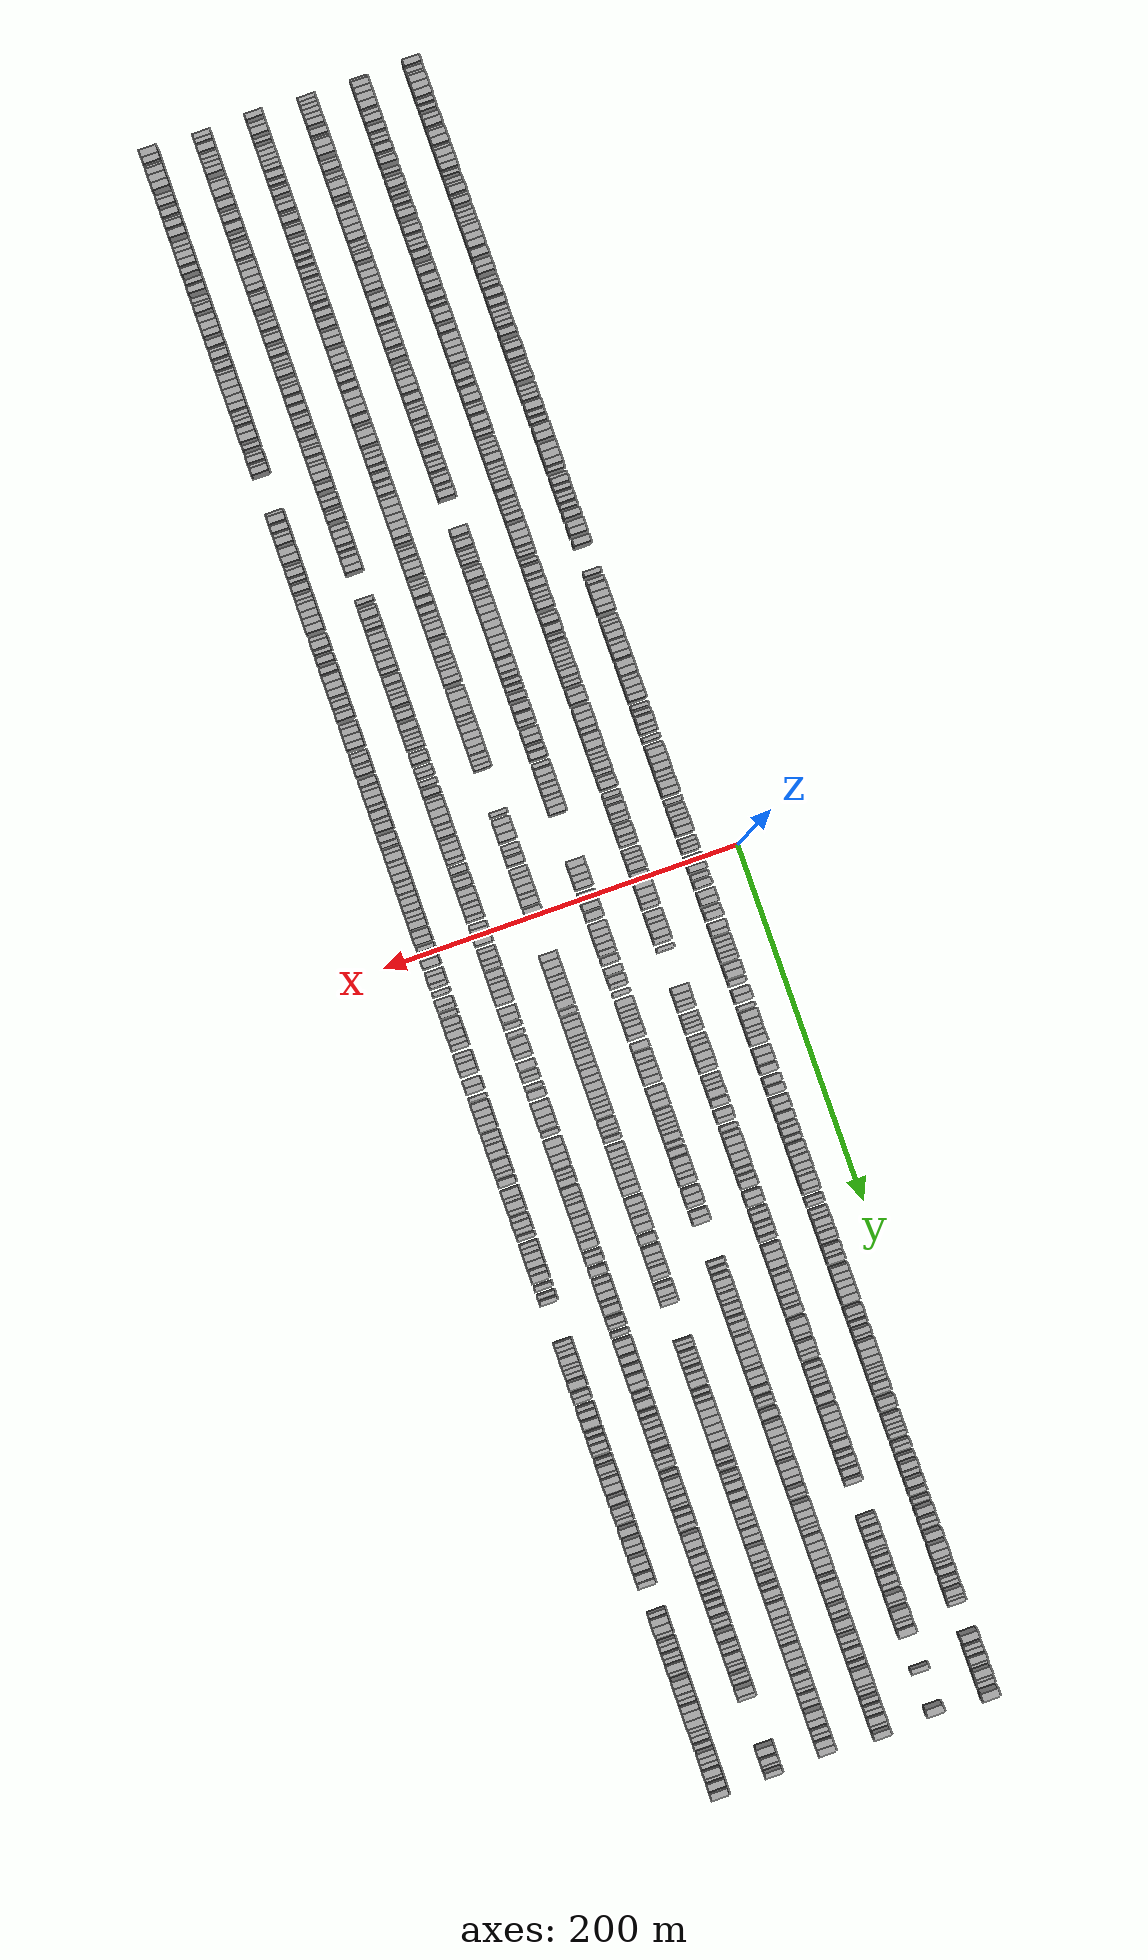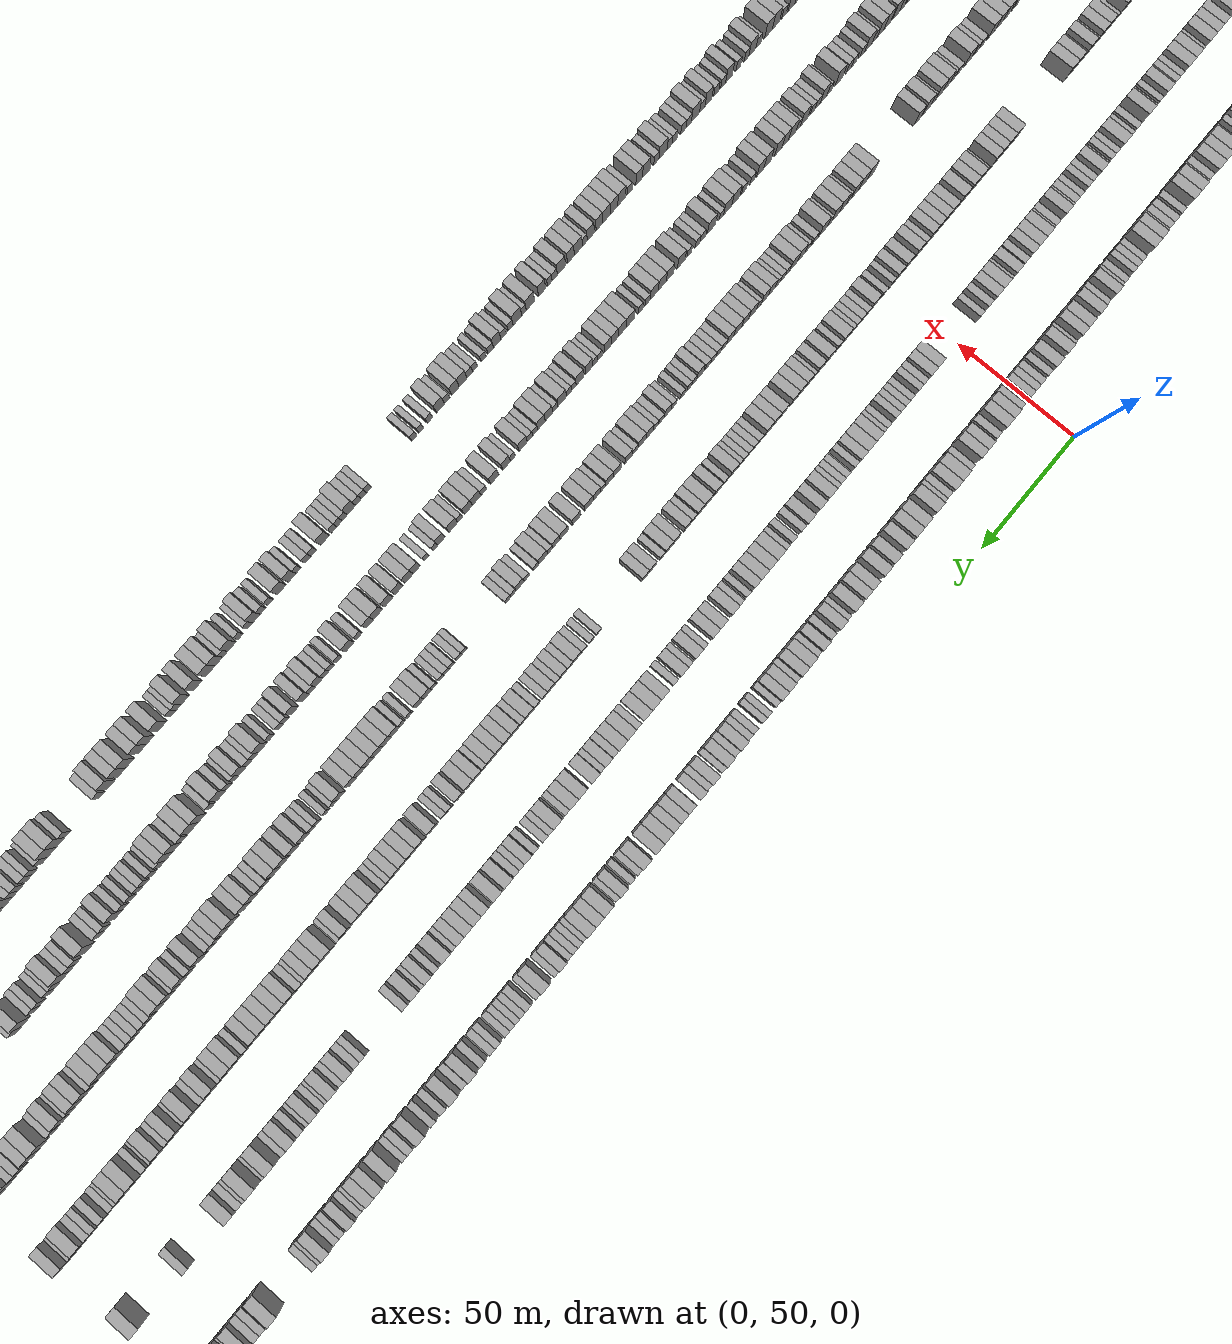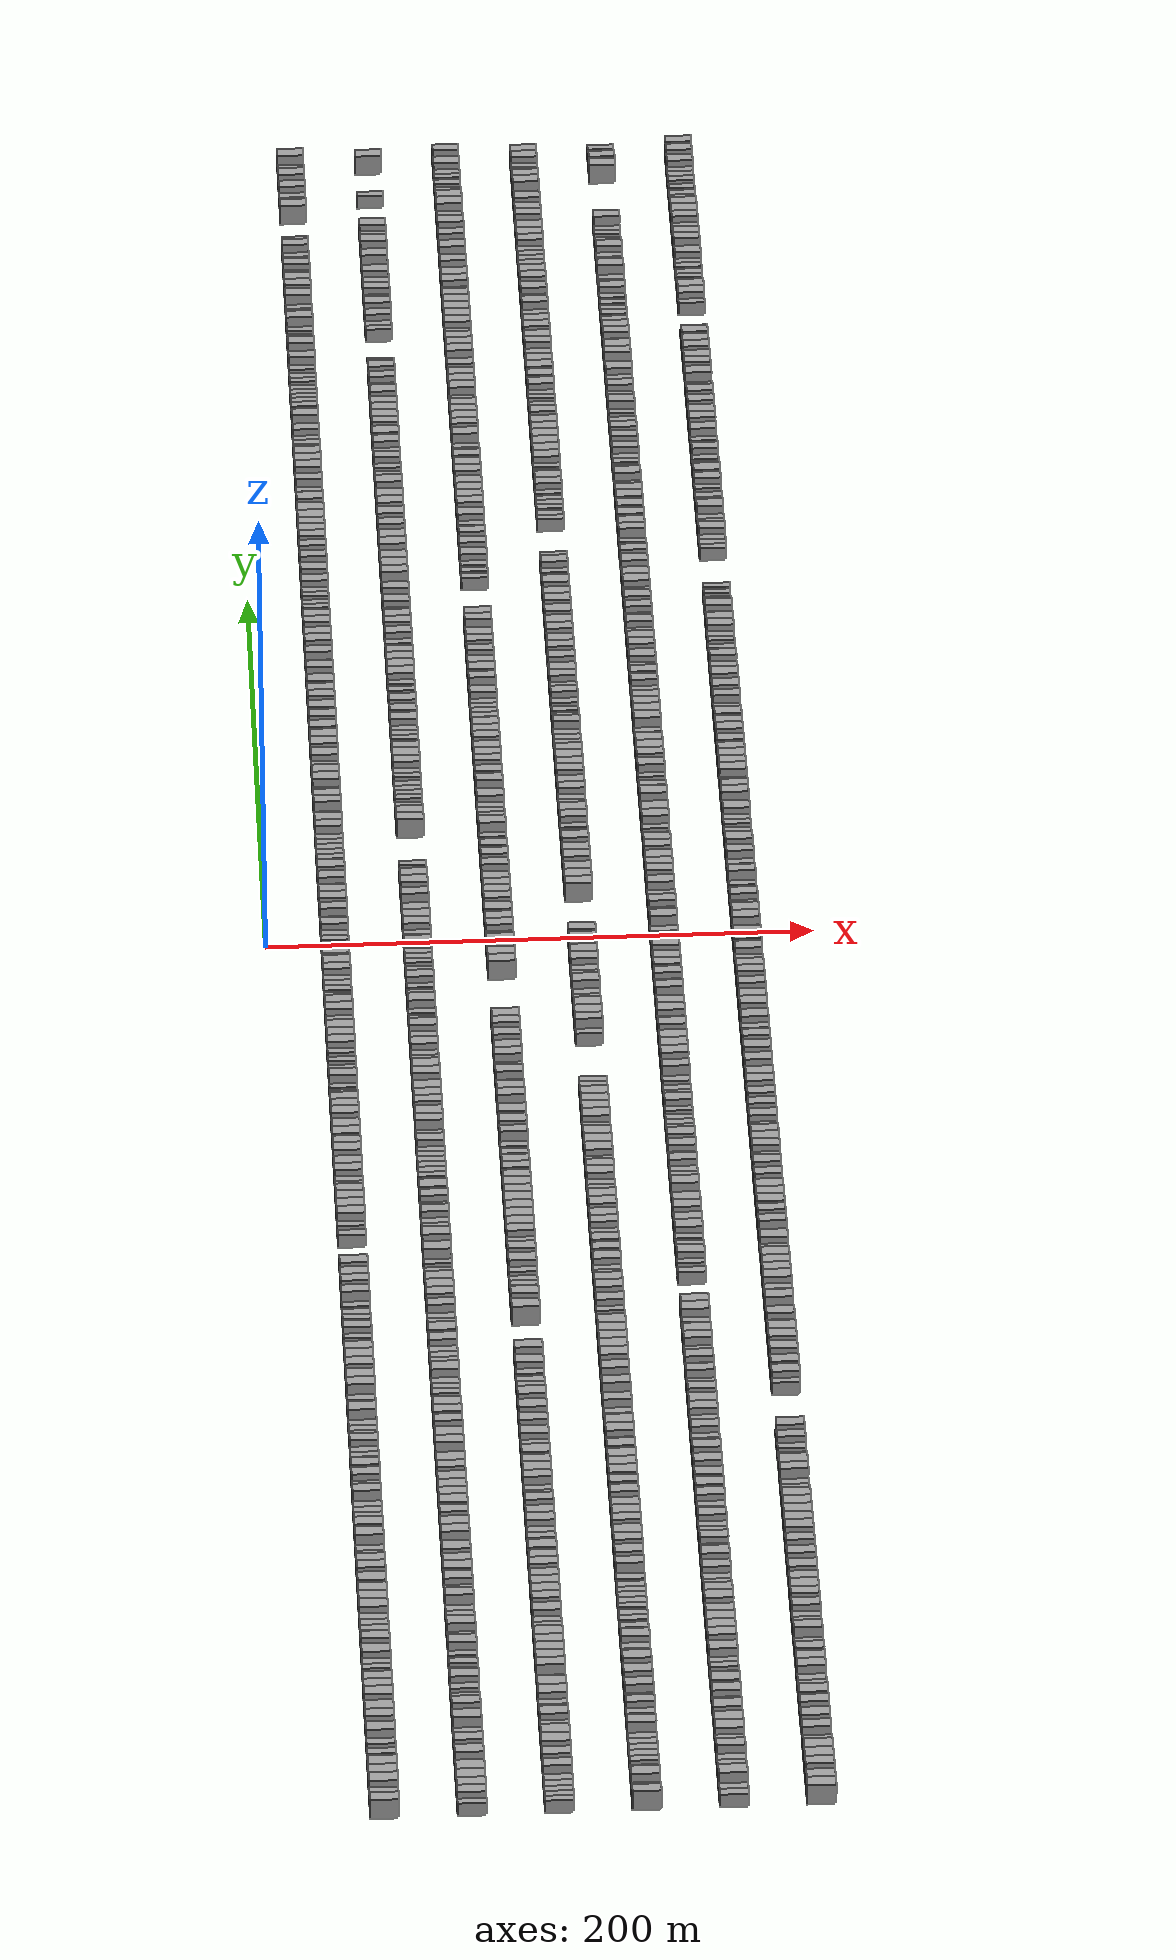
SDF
<sdf version="1.6">
 <world name="default">
  <scene>
   <sky><clouds><speed>12</speed></clouds></sky>
   <ambient>0.4 0.4 0.4 1</ambient>
   <background>0.7 0.7 0.7 1</background>
   <shadows>1</shadows>
  </scene>
  <gravity>0 0 -9.8066</gravity>
  <magnetic_field>6e-06 2.3e-05 -4.2e-05</magnetic_field>
  <physics default="0" name="default_physics" type="ode">
   <ode>
    <solver>
     <type>quick</type>
     <iters>10</iters>
     <sor>1.0</sor>
     <use_dynamic_moi_rescaling>0</use_dynamic_moi_rescaling>
    </solver>
    <constraints>
     <cfm>0</cfm>
     <erp>0.2</erp>
     <contact_max_correcting_vel>100</contact_max_correcting_vel>
     <contact_surface_layer>0.001</contact_surface_layer>
    </constraints>
   </ode>
   <max_step_size>0.004</max_step_size>
   <real_time_factor>1</real_time_factor>
   <real_time_update_rate>250</real_time_update_rate>
  </physics>
  <light name="sun" type="directional">
   <pose>0 0 10 0 0 0</pose>
   <diffuse>0.8 0.8 0.8 1</diffuse>
   <specular>0.2 0.2 0.2 1</specular>
   <attenuation>
    <range>1000</range>
    <constant>0.9</constant>
    <linear>0.01</linear>
    <quadratic>0.001</quadratic>
   </attenuation>
   <direction>-0.5 0.1 -0.9</direction>
  </light>
  <model name="building_1">
   <static>1</static>
   <pose>25.0000 -458.0443 0 0.000000 0.000000 0.000000</pose>
   <link name="link">
    <pose>0 0 4.50 0 0 0</pose>
    <collision name="collision"><geometry><box><size>10.0000 3.9114 9.0000</size></box></geometry></collision>
    <visual name="visual">
     <cast_shadows>0</cast_shadows>
     <geometry><box><size>10.0000 3.9114 9.0000</size></box></geometry>
     <material>
      <script>
       <uri>model://grey_wall/materials/scripts</uri>
       <uri>model://grey_wall/materials/textures</uri>
       <name>vrc/grey_wall</name>
      </script>
     </material>
    </visual>
   </link>
  </model>
  <model name="building_2">
   <static>1</static>
   <pose>25.0000 -454.5944 0 0.000000 0.000000 0.000000</pose>
   <link name="link">
    <pose>0 0 3.00 0 0 0</pose>
    <collision name="collision"><geometry><box><size>10.0000 2.9884 6.0000</size></box></geometry></collision>
    <visual name="visual">
     <cast_shadows>0</cast_shadows>
     <geometry><box><size>10.0000 2.9884 6.0000</size></box></geometry>
     <material>
      <script>
       <uri>model://grey_wall/materials/scripts</uri>
       <uri>model://grey_wall/materials/textures</uri>
       <name>vrc/grey_wall</name>
      </script>
     </material>
    </visual>
   </link>
  </model>
  <model name="building_3">
   <static>1</static>
   <pose>25.0000 -451.8059 0 0.000000 0.000000 0.000000</pose>
   <link name="link">
    <pose>0 0 3.00 0 0 0</pose>
    <collision name="collision"><geometry><box><size>10.0000 2.5886 6.0000</size></box></geometry></collision>
    <visual name="visual">
     <cast_shadows>0</cast_shadows>
     <geometry><box><size>10.0000 2.5886 6.0000</size></box></geometry>
     <material>
      <script>
       <uri>model://grey_wall/materials/scripts</uri>
       <uri>model://grey_wall/materials/textures</uri>
       <name>vrc/grey_wall</name>
      </script>
     </material>
    </visual>
   </link>
  </model>
  <model name="building_4">
   <static>1</static>
   <pose>25.0000 -448.3180 0 0.000000 0.000000 0.000000</pose>
   <link name="link">
    <pose>0 0 4.50 0 0 0</pose>
    <collision name="collision"><geometry><box><size>10.0000 4.3871 9.0000</size></box></geometry></collision>
    <visual name="visual">
     <cast_shadows>0</cast_shadows>
     <geometry><box><size>10.0000 4.3871 9.0000</size></box></geometry>
     <material>
      <script>
       <uri>model://grey_wall/materials/scripts</uri>
       <uri>model://grey_wall/materials/textures</uri>
       <name>vrc/grey_wall</name>
      </script>
     </material>
    </visual>
   </link>
  </model>
  <model name="building_5">
   <static>1</static>
   <pose>25.0000 -444.0741 0 0.000000 0.000000 0.000000</pose>
   <link name="link">
    <pose>0 0 4.50 0 0 0</pose>
    <collision name="collision"><geometry><box><size>10.0000 4.1006 9.0000</size></box></geometry></collision>
    <visual name="visual">
     <cast_shadows>0</cast_shadows>
     <geometry><box><size>10.0000 4.1006 9.0000</size></box></geometry>
     <material>
      <script>
       <uri>model://grey_wall/materials/scripts</uri>
       <uri>model://grey_wall/materials/textures</uri>
       <name>vrc/grey_wall</name>
      </script>
     </material>
    </visual>
   </link>
  </model>
  <model name="building_6">
   <static>1</static>
   <pose>25.0000 -439.8501 0 0.000000 0.000000 0.000000</pose>
   <link name="link">
    <pose>0 0 4.50 0 0 0</pose>
    <collision name="collision"><geometry><box><size>10.0000 4.3474 9.0000</size></box></geometry></collision>
    <visual name="visual">
     <cast_shadows>0</cast_shadows>
     <geometry><box><size>10.0000 4.3474 9.0000</size></box></geometry>
     <material>
      <script>
       <uri>model://grey_wall/materials/scripts</uri>
       <uri>model://grey_wall/materials/textures</uri>
       <name>vrc/grey_wall</name>
      </script>
     </material>
    </visual>
   </link>
  </model>
  <model name="building_7">
   <static>1</static>
   <pose>25.0000 -436.2432 0 0.000000 0.000000 0.000000</pose>
   <link name="link">
    <pose>0 0 3.00 0 0 0</pose>
    <collision name="collision"><geometry><box><size>10.0000 2.8663 6.0000</size></box></geometry></collision>
    <visual name="visual">
     <cast_shadows>0</cast_shadows>
     <geometry><box><size>10.0000 2.8663 6.0000</size></box></geometry>
     <material>
      <script>
       <uri>model://grey_wall/materials/scripts</uri>
       <uri>model://grey_wall/materials/textures</uri>
       <name>vrc/grey_wall</name>
      </script>
     </material>
    </visual>
   </link>
  </model>
  <model name="building_8">
   <static>1</static>
   <pose>25.0000 -432.3729 0 0.000000 0.000000 0.000000</pose>
   <link name="link">
    <pose>0 0 3.00 0 0 0</pose>
    <collision name="collision"><geometry><box><size>10.0000 2.8744 6.0000</size></box></geometry></collision>
    <visual name="visual">
     <cast_shadows>0</cast_shadows>
     <geometry><box><size>10.0000 2.8744 6.0000</size></box></geometry>
     <material>
      <script>
       <uri>model://grey_wall/materials/scripts</uri>
       <uri>model://grey_wall/materials/textures</uri>
       <name>vrc/grey_wall</name>
      </script>
     </material>
    </visual>
   </link>
  </model>
  <model name="building_9">
   <static>1</static>
   <pose>25.0000 -427.4677 0 0.000000 0.000000 0.000000</pose>
   <link name="link">
    <pose>0 0 3.00 0 0 0</pose>
    <collision name="collision"><geometry><box><size>10.0000 2.9360 6.0000</size></box></geometry></collision>
    <visual name="visual">
     <cast_shadows>0</cast_shadows>
     <geometry><box><size>10.0000 2.9360 6.0000</size></box></geometry>
     <material>
      <script>
       <uri>model://grey_wall/materials/scripts</uri>
       <uri>model://grey_wall/materials/textures</uri>
       <name>vrc/grey_wall</name>
      </script>
     </material>
    </visual>
   </link>
  </model>
  <model name="building_10">
   <static>1</static>
   <pose>25.0000 -422.8444 0 0.000000 0.000000 0.000000</pose>
   <link name="link">
    <pose>0 0 4.50 0 0 0</pose>
    <collision name="collision"><geometry><box><size>10.0000 4.3106 9.0000</size></box></geometry></collision>
    <visual name="visual">
     <cast_shadows>0</cast_shadows>
     <geometry><box><size>10.0000 4.3106 9.0000</size></box></geometry>
     <material>
      <script>
       <uri>model://grey_wall/materials/scripts</uri>
       <uri>model://grey_wall/materials/textures</uri>
       <name>vrc/grey_wall</name>
      </script>
     </material>
    </visual>
   </link>
  </model>
  <model name="building_11">
   <static>1</static>
   <pose>25.0000 -419.4200 0 0.000000 0.000000 0.000000</pose>
   <link name="link">
    <pose>0 0 3.00 0 0 0</pose>
    <collision name="collision"><geometry><box><size>10.0000 2.5383 6.0000</size></box></geometry></collision>
    <visual name="visual">
     <cast_shadows>0</cast_shadows>
     <geometry><box><size>10.0000 2.5383 6.0000</size></box></geometry>
     <material>
      <script>
       <uri>model://grey_wall/materials/scripts</uri>
       <uri>model://grey_wall/materials/textures</uri>
       <name>vrc/grey_wall</name>
      </script>
     </material>
    </visual>
   </link>
  </model>
  <model name="building_12">
   <static>1</static>
   <pose>25.0000 -416.2218 0 0.000000 0.000000 0.000000</pose>
   <link name="link">
    <pose>0 0 4.50 0 0 0</pose>
    <collision name="collision"><geometry><box><size>10.0000 3.8580 9.0000</size></box></geometry></collision>
    <visual name="visual">
     <cast_shadows>0</cast_shadows>
     <geometry><box><size>10.0000 3.8580 9.0000</size></box></geometry>
     <material>
      <script>
       <uri>model://grey_wall/materials/scripts</uri>
       <uri>model://grey_wall/materials/textures</uri>
       <name>vrc/grey_wall</name>
      </script>
     </material>
    </visual>
   </link>
  </model>
  <model name="building_13">
   <static>1</static>
   <pose>25.0000 -412.1047 0 0.000000 0.000000 0.000000</pose>
   <link name="link">
    <pose>0 0 4.50 0 0 0</pose>
    <collision name="collision"><geometry><box><size>10.0000 4.3762 9.0000</size></box></geometry></collision>
    <visual name="visual">
     <cast_shadows>0</cast_shadows>
     <geometry><box><size>10.0000 4.3762 9.0000</size></box></geometry>
     <material>
      <script>
       <uri>model://grey_wall/materials/scripts</uri>
       <uri>model://grey_wall/materials/textures</uri>
       <name>vrc/grey_wall</name>
      </script>
     </material>
    </visual>
   </link>
  </model>
  <model name="building_14">
   <static>1</static>
   <pose>25.0000 -408.5385 0 0.000000 0.000000 0.000000</pose>
   <link name="link">
    <pose>0 0 3.00 0 0 0</pose>
    <collision name="collision"><geometry><box><size>10.0000 2.7564 6.0000</size></box></geometry></collision>
    <visual name="visual">
     <cast_shadows>0</cast_shadows>
     <geometry><box><size>10.0000 2.7564 6.0000</size></box></geometry>
     <material>
      <script>
       <uri>model://grey_wall/materials/scripts</uri>
       <uri>model://grey_wall/materials/textures</uri>
       <name>vrc/grey_wall</name>
      </script>
     </material>
    </visual>
   </link>
  </model>
  <model name="building_15">
   <static>1</static>
   <pose>25.0000 -405.0021 0 0.000000 0.000000 0.000000</pose>
   <link name="link">
    <pose>0 0 4.50 0 0 0</pose>
    <collision name="collision"><geometry><box><size>10.0000 4.3163 9.0000</size></box></geometry></collision>
    <visual name="visual">
     <cast_shadows>0</cast_shadows>
     <geometry><box><size>10.0000 4.3163 9.0000</size></box></geometry>
     <material>
      <script>
       <uri>model://grey_wall/materials/scripts</uri>
       <uri>model://grey_wall/materials/textures</uri>
       <name>vrc/grey_wall</name>
      </script>
     </material>
    </visual>
   </link>
  </model>
  <model name="building_16">
   <static>1</static>
   <pose>25.0000 -401.0098 0 0.000000 0.000000 0.000000</pose>
   <link name="link">
    <pose>0 0 4.50 0 0 0</pose>
    <collision name="collision"><geometry><box><size>10.0000 3.6683 9.0000</size></box></geometry></collision>
    <visual name="visual">
     <cast_shadows>0</cast_shadows>
     <geometry><box><size>10.0000 3.6683 9.0000</size></box></geometry>
     <material>
      <script>
       <uri>model://grey_wall/materials/scripts</uri>
       <uri>model://grey_wall/materials/textures</uri>
       <name>vrc/grey_wall</name>
      </script>
     </material>
    </visual>
   </link>
  </model>
  <model name="building_17">
   <static>1</static>
   <pose>25.0000 -397.3030 0 0.000000 0.000000 0.000000</pose>
   <link name="link">
    <pose>0 0 4.50 0 0 0</pose>
    <collision name="collision"><geometry><box><size>10.0000 3.7453 9.0000</size></box></geometry></collision>
    <visual name="visual">
     <cast_shadows>0</cast_shadows>
     <geometry><box><size>10.0000 3.7453 9.0000</size></box></geometry>
     <material>
      <script>
       <uri>model://grey_wall/materials/scripts</uri>
       <uri>model://grey_wall/materials/textures</uri>
       <name>vrc/grey_wall</name>
      </script>
     </material>
    </visual>
   </link>
  </model>
  <model name="building_18">
   <static>1</static>
   <pose>25.0000 -394.2153 0 0.000000 0.000000 0.000000</pose>
   <link name="link">
    <pose>0 0 3.00 0 0 0</pose>
    <collision name="collision"><geometry><box><size>10.0000 2.4301 6.0000</size></box></geometry></collision>
    <visual name="visual">
     <cast_shadows>0</cast_shadows>
     <geometry><box><size>10.0000 2.4301 6.0000</size></box></geometry>
     <material>
      <script>
       <uri>model://grey_wall/materials/scripts</uri>
       <uri>model://grey_wall/materials/textures</uri>
       <name>vrc/grey_wall</name>
      </script>
     </material>
    </visual>
   </link>
  </model>
  <model name="building_19">
   <static>1</static>
   <pose>25.0000 -389.7480 0 0.000000 0.000000 0.000000</pose>
   <link name="link">
    <pose>0 0 3.00 0 0 0</pose>
    <collision name="collision"><geometry><box><size>10.0000 2.5046 6.0000</size></box></geometry></collision>
    <visual name="visual">
     <cast_shadows>0</cast_shadows>
     <geometry><box><size>10.0000 2.5046 6.0000</size></box></geometry>
     <material>
      <script>
       <uri>model://grey_wall/materials/scripts</uri>
       <uri>model://grey_wall/materials/textures</uri>
       <name>vrc/grey_wall</name>
      </script>
     </material>
    </visual>
   </link>
  </model>
  <model name="building_20">
   <static>1</static>
   <pose>25.0000 -387.1403 0 0.000000 0.000000 0.000000</pose>
   <link name="link">
    <pose>0 0 3.00 0 0 0</pose>
    <collision name="collision"><geometry><box><size>10.0000 2.7107 6.0000</size></box></geometry></collision>
    <visual name="visual">
     <cast_shadows>0</cast_shadows>
     <geometry><box><size>10.0000 2.7107 6.0000</size></box></geometry>
     <material>
      <script>
       <uri>model://grey_wall/materials/scripts</uri>
       <uri>model://grey_wall/materials/textures</uri>
       <name>vrc/grey_wall</name>
      </script>
     </material>
    </visual>
   </link>
  </model>
  <model name="building_21">
   <static>1</static>
   <pose>25.0000 -383.6075 0 0.000000 0.000000 0.000000</pose>
   <link name="link">
    <pose>0 0 4.50 0 0 0</pose>
    <collision name="collision"><geometry><box><size>10.0000 4.3550 9.0000</size></box></geometry></collision>
    <visual name="visual">
     <cast_shadows>0</cast_shadows>
     <geometry><box><size>10.0000 4.3550 9.0000</size></box></geometry>
     <material>
      <script>
       <uri>model://grey_wall/materials/scripts</uri>
       <uri>model://grey_wall/materials/textures</uri>
       <name>vrc/grey_wall</name>
      </script>
     </material>
    </visual>
   </link>
  </model>
  <model name="building_22">
   <static>1</static>
   <pose>25.0000 -380.1542 0 0.000000 0.000000 0.000000</pose>
   <link name="link">
    <pose>0 0 3.00 0 0 0</pose>
    <collision name="collision"><geometry><box><size>10.0000 2.5516 6.0000</size></box></geometry></collision>
    <visual name="visual">
     <cast_shadows>0</cast_shadows>
     <geometry><box><size>10.0000 2.5516 6.0000</size></box></geometry>
     <material>
      <script>
       <uri>model://grey_wall/materials/scripts</uri>
       <uri>model://grey_wall/materials/textures</uri>
       <name>vrc/grey_wall</name>
      </script>
     </material>
    </visual>
   </link>
  </model>
  <model name="building_23">
   <static>1</static>
   <pose>25.0000 -376.9304 0 0.000000 0.000000 0.000000</pose>
   <link name="link">
    <pose>0 0 4.50 0 0 0</pose>
    <collision name="collision"><geometry><box><size>10.0000 3.8958 9.0000</size></box></geometry></collision>
    <visual name="visual">
     <cast_shadows>0</cast_shadows>
     <geometry><box><size>10.0000 3.8958 9.0000</size></box></geometry>
     <material>
      <script>
       <uri>model://grey_wall/materials/scripts</uri>
       <uri>model://grey_wall/materials/textures</uri>
       <name>vrc/grey_wall</name>
      </script>
     </material>
    </visual>
   </link>
  </model>
  <model name="building_24">
   <static>1</static>
   <pose>25.0000 -372.7787 0 0.000000 0.000000 0.000000</pose>
   <link name="link">
    <pose>0 0 3.00 0 0 0</pose>
    <collision name="collision"><geometry><box><size>10.0000 2.4075 6.0000</size></box></geometry></collision>
    <visual name="visual">
     <cast_shadows>0</cast_shadows>
     <geometry><box><size>10.0000 2.4075 6.0000</size></box></geometry>
     <material>
      <script>
       <uri>model://grey_wall/materials/scripts</uri>
       <uri>model://grey_wall/materials/textures</uri>
       <name>vrc/grey_wall</name>
      </script>
     </material>
    </visual>
   </link>
  </model>
  <model name="building_25">
   <static>1</static>
   <pose>25.0000 -370.1652 0 0.000000 0.000000 0.000000</pose>
   <link name="link">
    <pose>0 0 3.00 0 0 0</pose>
    <collision name="collision"><geometry><box><size>10.0000 2.8196 6.0000</size></box></geometry></collision>
    <visual name="visual">
     <cast_shadows>0</cast_shadows>
     <geometry><box><size>10.0000 2.8196 6.0000</size></box></geometry>
     <material>
      <script>
       <uri>model://grey_wall/materials/scripts</uri>
       <uri>model://grey_wall/materials/textures</uri>
       <name>vrc/grey_wall</name>
      </script>
     </material>
    </visual>
   </link>
  </model>
  <model name="building_26">
   <static>1</static>
   <pose>25.0000 -367.3473 0 0.000000 0.000000 0.000000</pose>
   <link name="link">
    <pose>0 0 3.00 0 0 0</pose>
    <collision name="collision"><geometry><box><size>10.0000 2.8162 6.0000</size></box></geometry></collision>
    <visual name="visual">
     <cast_shadows>0</cast_shadows>
     <geometry><box><size>10.0000 2.8162 6.0000</size></box></geometry>
     <material>
      <script>
       <uri>model://grey_wall/materials/scripts</uri>
       <uri>model://grey_wall/materials/textures</uri>
       <name>vrc/grey_wall</name>
      </script>
     </material>
    </visual>
   </link>
  </model>
  <model name="building_27">
   <static>1</static>
   <pose>25.0000 -364.4440 0 0.000000 0.000000 0.000000</pose>
   <link name="link">
    <pose>0 0 3.00 0 0 0</pose>
    <collision name="collision"><geometry><box><size>10.0000 2.9904 6.0000</size></box></geometry></collision>
    <visual name="visual">
     <cast_shadows>0</cast_shadows>
     <geometry><box><size>10.0000 2.9904 6.0000</size></box></geometry>
     <material>
      <script>
       <uri>model://grey_wall/materials/scripts</uri>
       <uri>model://grey_wall/materials/textures</uri>
       <name>vrc/grey_wall</name>
      </script>
     </material>
    </visual>
   </link>
  </model>
  <model name="building_28">
   <static>1</static>
   <pose>25.0000 -360.7338 0 0.000000 0.000000 0.000000</pose>
   <link name="link">
    <pose>0 0 4.50 0 0 0</pose>
    <collision name="collision"><geometry><box><size>10.0000 4.4301 9.0000</size></box></geometry></collision>
    <visual name="visual">
     <cast_shadows>0</cast_shadows>
     <geometry><box><size>10.0000 4.4301 9.0000</size></box></geometry>
     <material>
      <script>
       <uri>model://grey_wall/materials/scripts</uri>
       <uri>model://grey_wall/materials/textures</uri>
       <name>vrc/grey_wall</name>
      </script>
     </material>
    </visual>
   </link>
  </model>
  <model name="building_29">
   <static>1</static>
   <pose>25.0000 -356.4991 0 0.000000 0.000000 0.000000</pose>
   <link name="link">
    <pose>0 0 4.50 0 0 0</pose>
    <collision name="collision"><geometry><box><size>10.0000 4.0392 9.0000</size></box></geometry></collision>
    <visual name="visual">
     <cast_shadows>0</cast_shadows>
     <geometry><box><size>10.0000 4.0392 9.0000</size></box></geometry>
     <material>
      <script>
       <uri>model://grey_wall/materials/scripts</uri>
       <uri>model://grey_wall/materials/textures</uri>
       <name>vrc/grey_wall</name>
      </script>
     </material>
    </visual>
   </link>
  </model>
  <model name="building_30">
   <static>1</static>
   <pose>25.0000 -352.3831 0 0.000000 0.000000 0.000000</pose>
   <link name="link">
    <pose>0 0 4.50 0 0 0</pose>
    <collision name="collision"><geometry><box><size>10.0000 4.1927 9.0000</size></box></geometry></collision>
    <visual name="visual">
     <cast_shadows>0</cast_shadows>
     <geometry><box><size>10.0000 4.1927 9.0000</size></box></geometry>
     <material>
      <script>
       <uri>model://grey_wall/materials/scripts</uri>
       <uri>model://grey_wall/materials/textures</uri>
       <name>vrc/grey_wall</name>
      </script>
     </material>
    </visual>
   </link>
  </model>
  <model name="building_31">
   <static>1</static>
   <pose>25.0000 -347.0619 0 0.000000 0.000000 0.000000</pose>
   <link name="link">
    <pose>0 0 4.50 0 0 0</pose>
    <collision name="collision"><geometry><box><size>10.0000 4.4497 9.0000</size></box></geometry></collision>
    <visual name="visual">
     <cast_shadows>0</cast_shadows>
     <geometry><box><size>10.0000 4.4497 9.0000</size></box></geometry>
     <material>
      <script>
       <uri>model://grey_wall/materials/scripts</uri>
       <uri>model://grey_wall/materials/textures</uri>
       <name>vrc/grey_wall</name>
      </script>
     </material>
    </visual>
   </link>
  </model>
  <model name="building_32">
   <static>1</static>
   <pose>25.0000 -340.9144 0 0.000000 0.000000 0.000000</pose>
   <link name="link">
    <pose>0 0 4.50 0 0 0</pose>
    <collision name="collision"><geometry><box><size>10.0000 3.8452 9.0000</size></box></geometry></collision>
    <visual name="visual">
     <cast_shadows>0</cast_shadows>
     <geometry><box><size>10.0000 3.8452 9.0000</size></box></geometry>
     <material>
      <script>
       <uri>model://grey_wall/materials/scripts</uri>
       <uri>model://grey_wall/materials/textures</uri>
       <name>vrc/grey_wall</name>
      </script>
     </material>
    </visual>
   </link>
  </model>
  <model name="building_33">
   <static>1</static>
   <pose>25.0000 -337.1807 0 0.000000 0.000000 0.000000</pose>
   <link name="link">
    <pose>0 0 4.50 0 0 0</pose>
    <collision name="collision"><geometry><box><size>10.0000 3.6222 9.0000</size></box></geometry></collision>
    <visual name="visual">
     <cast_shadows>0</cast_shadows>
     <geometry><box><size>10.0000 3.6222 9.0000</size></box></geometry>
     <material>
      <script>
       <uri>model://grey_wall/materials/scripts</uri>
       <uri>model://grey_wall/materials/textures</uri>
       <name>vrc/grey_wall</name>
      </script>
     </material>
    </visual>
   </link>
  </model>
  <model name="building_34">
   <static>1</static>
   <pose>25.0000 -332.1094 0 0.000000 0.000000 0.000000</pose>
   <link name="link">
    <pose>0 0 3.00 0 0 0</pose>
    <collision name="collision"><geometry><box><size>10.0000 2.5204 6.0000</size></box></geometry></collision>
    <visual name="visual">
     <cast_shadows>0</cast_shadows>
     <geometry><box><size>10.0000 2.5204 6.0000</size></box></geometry>
     <material>
      <script>
       <uri>model://grey_wall/materials/scripts</uri>
       <uri>model://grey_wall/materials/textures</uri>
       <name>vrc/grey_wall</name>
      </script>
     </material>
    </visual>
   </link>
  </model>
  <model name="building_35">
   <static>1</static>
   <pose>25.0000 -329.4571 0 0.000000 0.000000 0.000000</pose>
   <link name="link">
    <pose>0 0 3.00 0 0 0</pose>
    <collision name="collision"><geometry><box><size>10.0000 2.7842 6.0000</size></box></geometry></collision>
    <visual name="visual">
     <cast_shadows>0</cast_shadows>
     <geometry><box><size>10.0000 2.7842 6.0000</size></box></geometry>
     <material>
      <script>
       <uri>model://grey_wall/materials/scripts</uri>
       <uri>model://grey_wall/materials/textures</uri>
       <name>vrc/grey_wall</name>
      </script>
     </material>
    </visual>
   </link>
  </model>
  <model name="building_36">
   <static>1</static>
   <pose>25.0000 -323.8593 0 0.000000 0.000000 0.000000</pose>
   <link name="link">
    <pose>0 0 4.50 0 0 0</pose>
    <collision name="collision"><geometry><box><size>10.0000 4.4113 9.0000</size></box></geometry></collision>
    <visual name="visual">
     <cast_shadows>0</cast_shadows>
     <geometry><box><size>10.0000 4.4113 9.0000</size></box></geometry>
     <material>
      <script>
       <uri>model://grey_wall/materials/scripts</uri>
       <uri>model://grey_wall/materials/textures</uri>
       <name>vrc/grey_wall</name>
      </script>
     </material>
    </visual>
   </link>
  </model>
  <model name="building_37">
   <static>1</static>
   <pose>25.0000 -318.5925 0 0.000000 0.000000 0.000000</pose>
   <link name="link">
    <pose>0 0 4.50 0 0 0</pose>
    <collision name="collision"><geometry><box><size>10.0000 4.1224 9.0000</size></box></geometry></collision>
    <visual name="visual">
     <cast_shadows>0</cast_shadows>
     <geometry><box><size>10.0000 4.1224 9.0000</size></box></geometry>
     <material>
      <script>
       <uri>model://grey_wall/materials/scripts</uri>
       <uri>model://grey_wall/materials/textures</uri>
       <name>vrc/grey_wall</name>
      </script>
     </material>
    </visual>
   </link>
  </model>
  <model name="building_38">
   <static>1</static>
   <pose>25.0000 -315.2569 0 0.000000 0.000000 0.000000</pose>
   <link name="link">
    <pose>0 0 3.00 0 0 0</pose>
    <collision name="collision"><geometry><box><size>10.0000 2.5487 6.0000</size></box></geometry></collision>
    <visual name="visual">
     <cast_shadows>0</cast_shadows>
     <geometry><box><size>10.0000 2.5487 6.0000</size></box></geometry>
     <material>
      <script>
       <uri>model://grey_wall/materials/scripts</uri>
       <uri>model://grey_wall/materials/textures</uri>
       <name>vrc/grey_wall</name>
      </script>
     </material>
    </visual>
   </link>
  </model>
  <model name="building_39">
   <static>1</static>
   <pose>25.0000 -312.5360 0 0.000000 0.000000 0.000000</pose>
   <link name="link">
    <pose>0 0 3.00 0 0 0</pose>
    <collision name="collision"><geometry><box><size>10.0000 2.8932 6.0000</size></box></geometry></collision>
    <visual name="visual">
     <cast_shadows>0</cast_shadows>
     <geometry><box><size>10.0000 2.8932 6.0000</size></box></geometry>
     <material>
      <script>
       <uri>model://grey_wall/materials/scripts</uri>
       <uri>model://grey_wall/materials/textures</uri>
       <name>vrc/grey_wall</name>
      </script>
     </material>
    </visual>
   </link>
  </model>
  <model name="building_40">
   <static>1</static>
   <pose>25.0000 -309.6625 0 0.000000 0.000000 0.000000</pose>
   <link name="link">
    <pose>0 0 3.00 0 0 0</pose>
    <collision name="collision"><geometry><box><size>10.0000 2.8539 6.0000</size></box></geometry></collision>
    <visual name="visual">
     <cast_shadows>0</cast_shadows>
     <geometry><box><size>10.0000 2.8539 6.0000</size></box></geometry>
     <material>
      <script>
       <uri>model://grey_wall/materials/scripts</uri>
       <uri>model://grey_wall/materials/textures</uri>
       <name>vrc/grey_wall</name>
      </script>
     </material>
    </visual>
   </link>
  </model>
  <model name="building_41">
   <static>1</static>
   <pose>25.0000 -306.7926 0 0.000000 0.000000 0.000000</pose>
   <link name="link">
    <pose>0 0 3.00 0 0 0</pose>
    <collision name="collision"><geometry><box><size>10.0000 2.8858 6.0000</size></box></geometry></collision>
    <visual name="visual">
     <cast_shadows>0</cast_shadows>
     <geometry><box><size>10.0000 2.8858 6.0000</size></box></geometry>
     <material>
      <script>
       <uri>model://grey_wall/materials/scripts</uri>
       <uri>model://grey_wall/materials/textures</uri>
       <name>vrc/grey_wall</name>
      </script>
     </material>
    </visual>
   </link>
  </model>
  <model name="building_42">
   <static>1</static>
   <pose>25.0000 -301.4364 0 0.000000 0.000000 0.000000</pose>
   <link name="link">
    <pose>0 0 4.50 0 0 0</pose>
    <collision name="collision"><geometry><box><size>10.0000 3.8266 9.0000</size></box></geometry></collision>
    <visual name="visual">
     <cast_shadows>0</cast_shadows>
     <geometry><box><size>10.0000 3.8266 9.0000</size></box></geometry>
     <material>
      <script>
       <uri>model://grey_wall/materials/scripts</uri>
       <uri>model://grey_wall/materials/textures</uri>
       <name>vrc/grey_wall</name>
      </script>
     </material>
    </visual>
   </link>
  </model>
  <model name="building_43">
   <static>1</static>
   <pose>25.0000 -296.1851 0 0.000000 0.000000 0.000000</pose>
   <link name="link">
    <pose>0 0 3.00 0 0 0</pose>
    <collision name="collision"><geometry><box><size>10.0000 2.6761 6.0000</size></box></geometry></collision>
    <visual name="visual">
     <cast_shadows>0</cast_shadows>
     <geometry><box><size>10.0000 2.6761 6.0000</size></box></geometry>
     <material>
      <script>
       <uri>model://grey_wall/materials/scripts</uri>
       <uri>model://grey_wall/materials/textures</uri>
       <name>vrc/grey_wall</name>
      </script>
     </material>
    </visual>
   </link>
  </model>
  <model name="building_44">
   <static>1</static>
   <pose>25.0000 -292.8613 0 0.000000 0.000000 0.000000</pose>
   <link name="link">
    <pose>0 0 4.50 0 0 0</pose>
    <collision name="collision"><geometry><box><size>10.0000 3.9715 9.0000</size></box></geometry></collision>
    <visual name="visual">
     <cast_shadows>0</cast_shadows>
     <geometry><box><size>10.0000 3.9715 9.0000</size></box></geometry>
     <material>
      <script>
       <uri>model://grey_wall/materials/scripts</uri>
       <uri>model://grey_wall/materials/textures</uri>
       <name>vrc/grey_wall</name>
      </script>
     </material>
    </visual>
   </link>
  </model>
  <model name="building_45">
   <static>1</static>
   <pose>25.0000 -287.8928 0 0.000000 0.000000 0.000000</pose>
   <link name="link">
    <pose>0 0 4.50 0 0 0</pose>
    <collision name="collision"><geometry><box><size>10.0000 3.9654 9.0000</size></box></geometry></collision>
    <visual name="visual">
     <cast_shadows>0</cast_shadows>
     <geometry><box><size>10.0000 3.9654 9.0000</size></box></geometry>
     <material>
      <script>
       <uri>model://grey_wall/materials/scripts</uri>
       <uri>model://grey_wall/materials/textures</uri>
       <name>vrc/grey_wall</name>
      </script>
     </material>
    </visual>
   </link>
  </model>
  <model name="building_46">
   <static>1</static>
   <pose>25.0000 -283.6067 0 0.000000 0.000000 0.000000</pose>
   <link name="link">
    <pose>0 0 3.00 0 0 0</pose>
    <collision name="collision"><geometry><box><size>10.0000 2.6069 6.0000</size></box></geometry></collision>
    <visual name="visual">
     <cast_shadows>0</cast_shadows>
     <geometry><box><size>10.0000 2.6069 6.0000</size></box></geometry>
     <material>
      <script>
       <uri>model://grey_wall/materials/scripts</uri>
       <uri>model://grey_wall/materials/textures</uri>
       <name>vrc/grey_wall</name>
      </script>
     </material>
    </visual>
   </link>
  </model>
  <model name="building_47">
   <static>1</static>
   <pose>25.0000 -281.0584 0 0.000000 0.000000 0.000000</pose>
   <link name="link">
    <pose>0 0 3.00 0 0 0</pose>
    <collision name="collision"><geometry><box><size>10.0000 2.4897 6.0000</size></box></geometry></collision>
    <visual name="visual">
     <cast_shadows>0</cast_shadows>
     <geometry><box><size>10.0000 2.4897 6.0000</size></box></geometry>
     <material>
      <script>
       <uri>model://grey_wall/materials/scripts</uri>
       <uri>model://grey_wall/materials/textures</uri>
       <name>vrc/grey_wall</name>
      </script>
     </material>
    </visual>
   </link>
  </model>
  <model name="building_48">
   <static>1</static>
   <pose>25.0000 -278.4363 0 0.000000 0.000000 0.000000</pose>
   <link name="link">
    <pose>0 0 3.00 0 0 0</pose>
    <collision name="collision"><geometry><box><size>10.0000 2.7546 6.0000</size></box></geometry></collision>
    <visual name="visual">
     <cast_shadows>0</cast_shadows>
     <geometry><box><size>10.0000 2.7546 6.0000</size></box></geometry>
     <material>
      <script>
       <uri>model://grey_wall/materials/scripts</uri>
       <uri>model://grey_wall/materials/textures</uri>
       <name>vrc/grey_wall</name>
      </script>
     </material>
    </visual>
   </link>
  </model>
  <model name="building_49">
   <static>1</static>
   <pose>25.0000 -275.1839 0 0.000000 0.000000 0.000000</pose>
   <link name="link">
    <pose>0 0 4.50 0 0 0</pose>
    <collision name="collision"><geometry><box><size>10.0000 3.7501 9.0000</size></box></geometry></collision>
    <visual name="visual">
     <cast_shadows>0</cast_shadows>
     <geometry><box><size>10.0000 3.7501 9.0000</size></box></geometry>
     <material>
      <script>
       <uri>model://grey_wall/materials/scripts</uri>
       <uri>model://grey_wall/materials/textures</uri>
       <name>vrc/grey_wall</name>
      </script>
     </material>
    </visual>
   </link>
  </model>
  <model name="building_50">
   <static>1</static>
   <pose>25.0000 -269.9747 0 0.000000 0.000000 0.000000</pose>
   <link name="link">
    <pose>0 0 3.00 0 0 0</pose>
    <collision name="collision"><geometry><box><size>10.0000 2.6684 6.0000</size></box></geometry></collision>
    <visual name="visual">
     <cast_shadows>0</cast_shadows>
     <geometry><box><size>10.0000 2.6684 6.0000</size></box></geometry>
     <material>
      <script>
       <uri>model://grey_wall/materials/scripts</uri>
       <uri>model://grey_wall/materials/textures</uri>
       <name>vrc/grey_wall</name>
      </script>
     </material>
    </visual>
   </link>
  </model>
  <model name="building_51">
   <static>1</static>
   <pose>25.0000 -267.3069 0 0.000000 0.000000 0.000000</pose>
   <link name="link">
    <pose>0 0 3.00 0 0 0</pose>
    <collision name="collision"><geometry><box><size>10.0000 2.6672 6.0000</size></box></geometry></collision>
    <visual name="visual">
     <cast_shadows>0</cast_shadows>
     <geometry><box><size>10.0000 2.6672 6.0000</size></box></geometry>
     <material>
      <script>
       <uri>model://grey_wall/materials/scripts</uri>
       <uri>model://grey_wall/materials/textures</uri>
       <name>vrc/grey_wall</name>
      </script>
     </material>
    </visual>
   </link>
  </model>
  <model name="building_52">
   <static>1</static>
   <pose>25.0000 -264.5204 0 0.000000 0.000000 0.000000</pose>
   <link name="link">
    <pose>0 0 3.00 0 0 0</pose>
    <collision name="collision"><geometry><box><size>10.0000 2.9056 6.0000</size></box></geometry></collision>
    <visual name="visual">
     <cast_shadows>0</cast_shadows>
     <geometry><box><size>10.0000 2.9056 6.0000</size></box></geometry>
     <material>
      <script>
       <uri>model://grey_wall/materials/scripts</uri>
       <uri>model://grey_wall/materials/textures</uri>
       <name>vrc/grey_wall</name>
      </script>
     </material>
    </visual>
   </link>
  </model>
  <model name="building_53">
   <static>1</static>
   <pose>25.0000 -258.8321 0 0.000000 0.000000 0.000000</pose>
   <link name="link">
    <pose>0 0 4.50 0 0 0</pose>
    <collision name="collision"><geometry><box><size>10.0000 4.4711 9.0000</size></box></geometry></collision>
    <visual name="visual">
     <cast_shadows>0</cast_shadows>
     <geometry><box><size>10.0000 4.4711 9.0000</size></box></geometry>
     <material>
      <script>
       <uri>model://grey_wall/materials/scripts</uri>
       <uri>model://grey_wall/materials/textures</uri>
       <name>vrc/grey_wall</name>
      </script>
     </material>
    </visual>
   </link>
  </model>
  <model name="building_54">
   <static>1</static>
   <pose>25.0000 -255.1915 0 0.000000 0.000000 0.000000</pose>
   <link name="link">
    <pose>0 0 3.00 0 0 0</pose>
    <collision name="collision"><geometry><box><size>10.0000 2.8101 6.0000</size></box></geometry></collision>
    <visual name="visual">
     <cast_shadows>0</cast_shadows>
     <geometry><box><size>10.0000 2.8101 6.0000</size></box></geometry>
     <material>
      <script>
       <uri>model://grey_wall/materials/scripts</uri>
       <uri>model://grey_wall/materials/textures</uri>
       <name>vrc/grey_wall</name>
      </script>
     </material>
    </visual>
   </link>
  </model>
  <model name="building_55">
   <static>1</static>
   <pose>25.0000 -251.3041 0 0.000000 0.000000 0.000000</pose>
   <link name="link">
    <pose>0 0 3.00 0 0 0</pose>
    <collision name="collision"><geometry><box><size>10.0000 2.9647 6.0000</size></box></geometry></collision>
    <visual name="visual">
     <cast_shadows>0</cast_shadows>
     <geometry><box><size>10.0000 2.9647 6.0000</size></box></geometry>
     <material>
      <script>
       <uri>model://grey_wall/materials/scripts</uri>
       <uri>model://grey_wall/materials/textures</uri>
       <name>vrc/grey_wall</name>
      </script>
     </material>
    </visual>
   </link>
  </model>
  <model name="building_56">
   <static>1</static>
   <pose>25.0000 -245.7521 0 0.000000 0.000000 0.000000</pose>
   <link name="link">
    <pose>0 0 4.50 0 0 0</pose>
    <collision name="collision"><geometry><box><size>10.0000 4.1392 9.0000</size></box></geometry></collision>
    <visual name="visual">
     <cast_shadows>0</cast_shadows>
     <geometry><box><size>10.0000 4.1392 9.0000</size></box></geometry>
     <material>
      <script>
       <uri>model://grey_wall/materials/scripts</uri>
       <uri>model://grey_wall/materials/textures</uri>
       <name>vrc/grey_wall</name>
      </script>
     </material>
    </visual>
   </link>
  </model>
  <model name="building_57">
   <static>1</static>
   <pose>25.0000 -241.4736 0 0.000000 0.000000 0.000000</pose>
   <link name="link">
    <pose>0 0 4.50 0 0 0</pose>
    <collision name="collision"><geometry><box><size>10.0000 4.4177 9.0000</size></box></geometry></collision>
    <visual name="visual">
     <cast_shadows>0</cast_shadows>
     <geometry><box><size>10.0000 4.4177 9.0000</size></box></geometry>
     <material>
      <script>
       <uri>model://grey_wall/materials/scripts</uri>
       <uri>model://grey_wall/materials/textures</uri>
       <name>vrc/grey_wall</name>
      </script>
     </material>
    </visual>
   </link>
  </model>
  <model name="building_58">
   <static>1</static>
   <pose>25.0000 -235.1987 0 0.000000 0.000000 0.000000</pose>
   <link name="link">
    <pose>0 0 4.50 0 0 0</pose>
    <collision name="collision"><geometry><box><size>10.0000 4.1322 9.0000</size></box></geometry></collision>
    <visual name="visual">
     <cast_shadows>0</cast_shadows>
     <geometry><box><size>10.0000 4.1322 9.0000</size></box></geometry>
     <material>
      <script>
       <uri>model://grey_wall/materials/scripts</uri>
       <uri>model://grey_wall/materials/textures</uri>
       <name>vrc/grey_wall</name>
      </script>
     </material>
    </visual>
   </link>
  </model>
  <model name="building_59">
   <static>1</static>
   <pose>25.0000 -230.9025 0 0.000000 0.000000 0.000000</pose>
   <link name="link">
    <pose>0 0 4.50 0 0 0</pose>
    <collision name="collision"><geometry><box><size>10.0000 4.4601 9.0000</size></box></geometry></collision>
    <visual name="visual">
     <cast_shadows>0</cast_shadows>
     <geometry><box><size>10.0000 4.4601 9.0000</size></box></geometry>
     <material>
      <script>
       <uri>model://grey_wall/materials/scripts</uri>
       <uri>model://grey_wall/materials/textures</uri>
       <name>vrc/grey_wall</name>
      </script>
     </material>
    </visual>
   </link>
  </model>
  <model name="building_60">
   <static>1</static>
   <pose>25.0000 -226.7321 0 0.000000 0.000000 0.000000</pose>
   <link name="link">
    <pose>0 0 4.50 0 0 0</pose>
    <collision name="collision"><geometry><box><size>10.0000 3.8808 9.0000</size></box></geometry></collision>
    <visual name="visual">
     <cast_shadows>0</cast_shadows>
     <geometry><box><size>10.0000 3.8808 9.0000</size></box></geometry>
     <material>
      <script>
       <uri>model://grey_wall/materials/scripts</uri>
       <uri>model://grey_wall/materials/textures</uri>
       <name>vrc/grey_wall</name>
      </script>
     </material>
    </visual>
   </link>
  </model>
  <model name="building_61">
   <static>1</static>
   <pose>25.0000 -223.4540 0 0.000000 0.000000 0.000000</pose>
   <link name="link">
    <pose>0 0 3.00 0 0 0</pose>
    <collision name="collision"><geometry><box><size>10.0000 2.6752 6.0000</size></box></geometry></collision>
    <visual name="visual">
     <cast_shadows>0</cast_shadows>
     <geometry><box><size>10.0000 2.6752 6.0000</size></box></geometry>
     <material>
      <script>
       <uri>model://grey_wall/materials/scripts</uri>
       <uri>model://grey_wall/materials/textures</uri>
       <name>vrc/grey_wall</name>
      </script>
     </material>
    </visual>
   </link>
  </model>
  <model name="building_62">
   <static>1</static>
   <pose>25.0000 -218.8609 0 0.000000 0.000000 0.000000</pose>
   <link name="link">
    <pose>0 0 3.00 0 0 0</pose>
    <collision name="collision"><geometry><box><size>10.0000 2.5110 6.0000</size></box></geometry></collision>
    <visual name="visual">
     <cast_shadows>0</cast_shadows>
     <geometry><box><size>10.0000 2.5110 6.0000</size></box></geometry>
     <material>
      <script>
       <uri>model://grey_wall/materials/scripts</uri>
       <uri>model://grey_wall/materials/textures</uri>
       <name>vrc/grey_wall</name>
      </script>
     </material>
    </visual>
   </link>
  </model>
  <model name="building_63">
   <static>1</static>
   <pose>25.0000 -215.7625 0 0.000000 0.000000 0.000000</pose>
   <link name="link">
    <pose>0 0 4.50 0 0 0</pose>
    <collision name="collision"><geometry><box><size>10.0000 3.6857 9.0000</size></box></geometry></collision>
    <visual name="visual">
     <cast_shadows>0</cast_shadows>
     <geometry><box><size>10.0000 3.6857 9.0000</size></box></geometry>
     <material>
      <script>
       <uri>model://grey_wall/materials/scripts</uri>
       <uri>model://grey_wall/materials/textures</uri>
       <name>vrc/grey_wall</name>
      </script>
     </material>
    </visual>
   </link>
  </model>
  <model name="building_64">
   <static>1</static>
   <pose>25.0000 -212.4665 0 0.000000 0.000000 0.000000</pose>
   <link name="link">
    <pose>0 0 3.00 0 0 0</pose>
    <collision name="collision"><geometry><box><size>10.0000 2.9063 6.0000</size></box></geometry></collision>
    <visual name="visual">
     <cast_shadows>0</cast_shadows>
     <geometry><box><size>10.0000 2.9063 6.0000</size></box></geometry>
     <material>
      <script>
       <uri>model://grey_wall/materials/scripts</uri>
       <uri>model://grey_wall/materials/textures</uri>
       <name>vrc/grey_wall</name>
      </script>
     </material>
    </visual>
   </link>
  </model>
  <model name="building_65">
   <static>1</static>
   <pose>25.0000 -208.7132 0 0.000000 0.000000 0.000000</pose>
   <link name="link">
    <pose>0 0 3.00 0 0 0</pose>
    <collision name="collision"><geometry><box><size>10.0000 2.6004 6.0000</size></box></geometry></collision>
    <visual name="visual">
     <cast_shadows>0</cast_shadows>
     <geometry><box><size>10.0000 2.6004 6.0000</size></box></geometry>
     <material>
      <script>
       <uri>model://grey_wall/materials/scripts</uri>
       <uri>model://grey_wall/materials/textures</uri>
       <name>vrc/grey_wall</name>
      </script>
     </material>
    </visual>
   </link>
  </model>
  <model name="building_66">
   <static>1</static>
   <pose>25.0000 -205.9280 0 0.000000 0.000000 0.000000</pose>
   <link name="link">
    <pose>0 0 3.00 0 0 0</pose>
    <collision name="collision"><geometry><box><size>10.0000 2.9700 6.0000</size></box></geometry></collision>
    <visual name="visual">
     <cast_shadows>0</cast_shadows>
     <geometry><box><size>10.0000 2.9700 6.0000</size></box></geometry>
     <material>
      <script>
       <uri>model://grey_wall/materials/scripts</uri>
       <uri>model://grey_wall/materials/textures</uri>
       <name>vrc/grey_wall</name>
      </script>
     </material>
    </visual>
   </link>
  </model>
  <model name="building_67">
   <static>1</static>
   <pose>25.0000 -202.0896 0 0.000000 0.000000 0.000000</pose>
   <link name="link">
    <pose>0 0 3.00 0 0 0</pose>
    <collision name="collision"><geometry><box><size>10.0000 2.7068 6.0000</size></box></geometry></collision>
    <visual name="visual">
     <cast_shadows>0</cast_shadows>
     <geometry><box><size>10.0000 2.7068 6.0000</size></box></geometry>
     <material>
      <script>
       <uri>model://grey_wall/materials/scripts</uri>
       <uri>model://grey_wall/materials/textures</uri>
       <name>vrc/grey_wall</name>
      </script>
     </material>
    </visual>
   </link>
  </model>
  <model name="building_68">
   <static>1</static>
   <pose>25.0000 -196.8141 0 0.000000 0.000000 0.000000</pose>
   <link name="link">
    <pose>0 0 4.50 0 0 0</pose>
    <collision name="collision"><geometry><box><size>10.0000 3.8444 9.0000</size></box></geometry></collision>
    <visual name="visual">
     <cast_shadows>0</cast_shadows>
     <geometry><box><size>10.0000 3.8444 9.0000</size></box></geometry>
     <material>
      <script>
       <uri>model://grey_wall/materials/scripts</uri>
       <uri>model://grey_wall/materials/textures</uri>
       <name>vrc/grey_wall</name>
      </script>
     </material>
    </visual>
   </link>
  </model>
  <model name="building_69">
   <static>1</static>
   <pose>25.0000 -191.0261 0 0.000000 0.000000 0.000000</pose>
   <link name="link">
    <pose>0 0 4.50 0 0 0</pose>
    <collision name="collision"><geometry><box><size>10.0000 3.7315 9.0000</size></box></geometry></collision>
    <visual name="visual">
     <cast_shadows>0</cast_shadows>
     <geometry><box><size>10.0000 3.7315 9.0000</size></box></geometry>
     <material>
      <script>
       <uri>model://grey_wall/materials/scripts</uri>
       <uri>model://grey_wall/materials/textures</uri>
       <name>vrc/grey_wall</name>
      </script>
     </material>
    </visual>
   </link>
  </model>
  <model name="building_70">
   <static>1</static>
   <pose>25.0000 -187.2185 0 0.000000 0.000000 0.000000</pose>
   <link name="link">
    <pose>0 0 4.50 0 0 0</pose>
    <collision name="collision"><geometry><box><size>10.0000 3.8838 9.0000</size></box></geometry></collision>
    <visual name="visual">
     <cast_shadows>0</cast_shadows>
     <geometry><box><size>10.0000 3.8838 9.0000</size></box></geometry>
     <material>
      <script>
       <uri>model://grey_wall/materials/scripts</uri>
       <uri>model://grey_wall/materials/textures</uri>
       <name>vrc/grey_wall</name>
      </script>
     </material>
    </visual>
   </link>
  </model>
  <model name="building_71">
   <static>1</static>
   <pose>25.0000 -181.2052 0 0.000000 0.000000 0.000000</pose>
   <link name="link">
    <pose>0 0 4.50 0 0 0</pose>
    <collision name="collision"><geometry><box><size>10.0000 4.1427 9.0000</size></box></geometry></collision>
    <visual name="visual">
     <cast_shadows>0</cast_shadows>
     <geometry><box><size>10.0000 4.1427 9.0000</size></box></geometry>
     <material>
      <script>
       <uri>model://grey_wall/materials/scripts</uri>
       <uri>model://grey_wall/materials/textures</uri>
       <name>vrc/grey_wall</name>
      </script>
     </material>
    </visual>
   </link>
  </model>
  <model name="building_72">
   <static>1</static>
   <pose>25.0000 -163.6983 0 0.000000 0.000000 0.000000</pose>
   <link name="link">
    <pose>0 0 3.00 0 0 0</pose>
    <collision name="collision"><geometry><box><size>10.0000 2.9570 6.0000</size></box></geometry></collision>
    <visual name="visual">
     <cast_shadows>0</cast_shadows>
     <geometry><box><size>10.0000 2.9570 6.0000</size></box></geometry>
     <material>
      <script>
       <uri>model://grey_wall/materials/scripts</uri>
       <uri>model://grey_wall/materials/textures</uri>
       <name>vrc/grey_wall</name>
      </script>
     </material>
    </visual>
   </link>
  </model>
  <model name="building_73">
   <static>1</static>
   <pose>25.0000 -158.9598 0 0.000000 0.000000 0.000000</pose>
   <link name="link">
    <pose>0 0 3.00 0 0 0</pose>
    <collision name="collision"><geometry><box><size>10.0000 2.5201 6.0000</size></box></geometry></collision>
    <visual name="visual">
     <cast_shadows>0</cast_shadows>
     <geometry><box><size>10.0000 2.5201 6.0000</size></box></geometry>
     <material>
      <script>
       <uri>model://grey_wall/materials/scripts</uri>
       <uri>model://grey_wall/materials/textures</uri>
       <name>vrc/grey_wall</name>
      </script>
     </material>
    </visual>
   </link>
  </model>
  <model name="building_74">
   <static>1</static>
   <pose>25.0000 -154.6725 0 0.000000 0.000000 0.000000</pose>
   <link name="link">
    <pose>0 0 4.50 0 0 0</pose>
    <collision name="collision"><geometry><box><size>10.0000 4.0544 9.0000</size></box></geometry></collision>
    <visual name="visual">
     <cast_shadows>0</cast_shadows>
     <geometry><box><size>10.0000 4.0544 9.0000</size></box></geometry>
     <material>
      <script>
       <uri>model://grey_wall/materials/scripts</uri>
       <uri>model://grey_wall/materials/textures</uri>
       <name>vrc/grey_wall</name>
      </script>
     </material>
    </visual>
   </link>
  </model>
  <model name="building_75">
   <static>1</static>
   <pose>25.0000 -150.5041 0 0.000000 0.000000 0.000000</pose>
   <link name="link">
    <pose>0 0 4.50 0 0 0</pose>
    <collision name="collision"><geometry><box><size>10.0000 4.2825 9.0000</size></box></geometry></collision>
    <visual name="visual">
     <cast_shadows>0</cast_shadows>
     <geometry><box><size>10.0000 4.2825 9.0000</size></box></geometry>
     <material>
      <script>
       <uri>model://grey_wall/materials/scripts</uri>
       <uri>model://grey_wall/materials/textures</uri>
       <name>vrc/grey_wall</name>
      </script>
     </material>
    </visual>
   </link>
  </model>
  <model name="building_76">
   <static>1</static>
   <pose>25.0000 -146.3765 0 0.000000 0.000000 0.000000</pose>
   <link name="link">
    <pose>0 0 4.50 0 0 0</pose>
    <collision name="collision"><geometry><box><size>10.0000 3.9727 9.0000</size></box></geometry></collision>
    <visual name="visual">
     <cast_shadows>0</cast_shadows>
     <geometry><box><size>10.0000 3.9727 9.0000</size></box></geometry>
     <material>
      <script>
       <uri>model://grey_wall/materials/scripts</uri>
       <uri>model://grey_wall/materials/textures</uri>
       <name>vrc/grey_wall</name>
      </script>
     </material>
    </visual>
   </link>
  </model>
  <model name="building_77">
   <static>1</static>
   <pose>25.0000 -142.5174 0 0.000000 0.000000 0.000000</pose>
   <link name="link">
    <pose>0 0 4.50 0 0 0</pose>
    <collision name="collision"><geometry><box><size>10.0000 3.7454 9.0000</size></box></geometry></collision>
    <visual name="visual">
     <cast_shadows>0</cast_shadows>
     <geometry><box><size>10.0000 3.7454 9.0000</size></box></geometry>
     <material>
      <script>
       <uri>model://grey_wall/materials/scripts</uri>
       <uri>model://grey_wall/materials/textures</uri>
       <name>vrc/grey_wall</name>
      </script>
     </material>
    </visual>
   </link>
  </model>
  <model name="building_78">
   <static>1</static>
   <pose>25.0000 -137.3174 0 0.000000 0.000000 0.000000</pose>
   <link name="link">
    <pose>0 0 3.00 0 0 0</pose>
    <collision name="collision"><geometry><box><size>10.0000 2.6546 6.0000</size></box></geometry></collision>
    <visual name="visual">
     <cast_shadows>0</cast_shadows>
     <geometry><box><size>10.0000 2.6546 6.0000</size></box></geometry>
     <material>
      <script>
       <uri>model://grey_wall/materials/scripts</uri>
       <uri>model://grey_wall/materials/textures</uri>
       <name>vrc/grey_wall</name>
      </script>
     </material>
    </visual>
   </link>
  </model>
  <model name="building_79">
   <static>1</static>
   <pose>25.0000 -134.7033 0 0.000000 0.000000 0.000000</pose>
   <link name="link">
    <pose>0 0 3.00 0 0 0</pose>
    <collision name="collision"><geometry><box><size>10.0000 2.5735 6.0000</size></box></geometry></collision>
    <visual name="visual">
     <cast_shadows>0</cast_shadows>
     <geometry><box><size>10.0000 2.5735 6.0000</size></box></geometry>
     <material>
      <script>
       <uri>model://grey_wall/materials/scripts</uri>
       <uri>model://grey_wall/materials/textures</uri>
       <name>vrc/grey_wall</name>
      </script>
     </material>
    </visual>
   </link>
  </model>
  <model name="building_80">
   <static>1</static>
   <pose>25.0000 -131.4703 0 0.000000 0.000000 0.000000</pose>
   <link name="link">
    <pose>0 0 4.50 0 0 0</pose>
    <collision name="collision"><geometry><box><size>10.0000 3.8925 9.0000</size></box></geometry></collision>
    <visual name="visual">
     <cast_shadows>0</cast_shadows>
     <geometry><box><size>10.0000 3.8925 9.0000</size></box></geometry>
     <material>
      <script>
       <uri>model://grey_wall/materials/scripts</uri>
       <uri>model://grey_wall/materials/textures</uri>
       <name>vrc/grey_wall</name>
      </script>
     </material>
    </visual>
   </link>
  </model>
  <model name="building_81">
   <static>1</static>
   <pose>25.0000 -127.5075 0 0.000000 0.000000 0.000000</pose>
   <link name="link">
    <pose>0 0 4.50 0 0 0</pose>
    <collision name="collision"><geometry><box><size>10.0000 4.0332 9.0000</size></box></geometry></collision>
    <visual name="visual">
     <cast_shadows>0</cast_shadows>
     <geometry><box><size>10.0000 4.0332 9.0000</size></box></geometry>
     <material>
      <script>
       <uri>model://grey_wall/materials/scripts</uri>
       <uri>model://grey_wall/materials/textures</uri>
       <name>vrc/grey_wall</name>
      </script>
     </material>
    </visual>
   </link>
  </model>
  <model name="building_82">
   <static>1</static>
   <pose>25.0000 -124.0322 0 0.000000 0.000000 0.000000</pose>
   <link name="link">
    <pose>0 0 3.00 0 0 0</pose>
    <collision name="collision"><geometry><box><size>10.0000 2.9172 6.0000</size></box></geometry></collision>
    <visual name="visual">
     <cast_shadows>0</cast_shadows>
     <geometry><box><size>10.0000 2.9172 6.0000</size></box></geometry>
     <material>
      <script>
       <uri>model://grey_wall/materials/scripts</uri>
       <uri>model://grey_wall/materials/textures</uri>
       <name>vrc/grey_wall</name>
      </script>
     </material>
    </visual>
   </link>
  </model>
  <model name="building_83">
   <static>1</static>
   <pose>25.0000 -120.3986 0 0.000000 0.000000 0.000000</pose>
   <link name="link">
    <pose>0 0 4.50 0 0 0</pose>
    <collision name="collision"><geometry><box><size>10.0000 4.3501 9.0000</size></box></geometry></collision>
    <visual name="visual">
     <cast_shadows>0</cast_shadows>
     <geometry><box><size>10.0000 4.3501 9.0000</size></box></geometry>
     <material>
      <script>
       <uri>model://grey_wall/materials/scripts</uri>
       <uri>model://grey_wall/materials/textures</uri>
       <name>vrc/grey_wall</name>
      </script>
     </material>
    </visual>
   </link>
  </model>
  <model name="building_84">
   <static>1</static>
   <pose>25.0000 -116.4097 0 0.000000 0.000000 0.000000</pose>
   <link name="link">
    <pose>0 0 4.50 0 0 0</pose>
    <collision name="collision"><geometry><box><size>10.0000 3.6276 9.0000</size></box></geometry></collision>
    <visual name="visual">
     <cast_shadows>0</cast_shadows>
     <geometry><box><size>10.0000 3.6276 9.0000</size></box></geometry>
     <material>
      <script>
       <uri>model://grey_wall/materials/scripts</uri>
       <uri>model://grey_wall/materials/textures</uri>
       <name>vrc/grey_wall</name>
      </script>
     </material>
    </visual>
   </link>
  </model>
  <model name="building_85">
   <static>1</static>
   <pose>25.0000 -111.4879 0 0.000000 0.000000 0.000000</pose>
   <link name="link">
    <pose>0 0 4.50 0 0 0</pose>
    <collision name="collision"><geometry><box><size>10.0000 4.2160 9.0000</size></box></geometry></collision>
    <visual name="visual">
     <cast_shadows>0</cast_shadows>
     <geometry><box><size>10.0000 4.2160 9.0000</size></box></geometry>
     <material>
      <script>
       <uri>model://grey_wall/materials/scripts</uri>
       <uri>model://grey_wall/materials/textures</uri>
       <name>vrc/grey_wall</name>
      </script>
     </material>
    </visual>
   </link>
  </model>
  <model name="building_86">
   <static>1</static>
   <pose>25.0000 -107.2674 0 0.000000 0.000000 0.000000</pose>
   <link name="link">
    <pose>0 0 4.50 0 0 0</pose>
    <collision name="collision"><geometry><box><size>10.0000 4.2251 9.0000</size></box></geometry></collision>
    <visual name="visual">
     <cast_shadows>0</cast_shadows>
     <geometry><box><size>10.0000 4.2251 9.0000</size></box></geometry>
     <material>
      <script>
       <uri>model://grey_wall/materials/scripts</uri>
       <uri>model://grey_wall/materials/textures</uri>
       <name>vrc/grey_wall</name>
      </script>
     </material>
    </visual>
   </link>
  </model>
  <model name="building_87">
   <static>1</static>
   <pose>25.0000 -103.7765 0 0.000000 0.000000 0.000000</pose>
   <link name="link">
    <pose>0 0 3.00 0 0 0</pose>
    <collision name="collision"><geometry><box><size>10.0000 2.7565 6.0000</size></box></geometry></collision>
    <visual name="visual">
     <cast_shadows>0</cast_shadows>
     <geometry><box><size>10.0000 2.7565 6.0000</size></box></geometry>
     <material>
      <script>
       <uri>model://grey_wall/materials/scripts</uri>
       <uri>model://grey_wall/materials/textures</uri>
       <name>vrc/grey_wall</name>
      </script>
     </material>
    </visual>
   </link>
  </model>
  <model name="building_88">
   <static>1</static>
   <pose>25.0000 -100.3007 0 0.000000 0.000000 0.000000</pose>
   <link name="link">
    <pose>0 0 4.50 0 0 0</pose>
    <collision name="collision"><geometry><box><size>10.0000 4.1952 9.0000</size></box></geometry></collision>
    <visual name="visual">
     <cast_shadows>0</cast_shadows>
     <geometry><box><size>10.0000 4.1952 9.0000</size></box></geometry>
     <material>
      <script>
       <uri>model://grey_wall/materials/scripts</uri>
       <uri>model://grey_wall/materials/textures</uri>
       <name>vrc/grey_wall</name>
      </script>
     </material>
    </visual>
   </link>
  </model>
  <model name="building_89">
   <static>1</static>
   <pose>25.0000 -96.3168 0 0.000000 0.000000 0.000000</pose>
   <link name="link">
    <pose>0 0 4.50 0 0 0</pose>
    <collision name="collision"><geometry><box><size>10.0000 3.7726 9.0000</size></box></geometry></collision>
    <visual name="visual">
     <cast_shadows>0</cast_shadows>
     <geometry><box><size>10.0000 3.7726 9.0000</size></box></geometry>
     <material>
      <script>
       <uri>model://grey_wall/materials/scripts</uri>
       <uri>model://grey_wall/materials/textures</uri>
       <name>vrc/grey_wall</name>
      </script>
     </material>
    </visual>
   </link>
  </model>
  <model name="building_90">
   <static>1</static>
   <pose>25.0000 -92.5763 0 0.000000 0.000000 0.000000</pose>
   <link name="link">
    <pose>0 0 4.50 0 0 0</pose>
    <collision name="collision"><geometry><box><size>10.0000 3.7083 9.0000</size></box></geometry></collision>
    <visual name="visual">
     <cast_shadows>0</cast_shadows>
     <geometry><box><size>10.0000 3.7083 9.0000</size></box></geometry>
     <material>
      <script>
       <uri>model://grey_wall/materials/scripts</uri>
       <uri>model://grey_wall/materials/textures</uri>
       <name>vrc/grey_wall</name>
      </script>
     </material>
    </visual>
   </link>
  </model>
  <model name="building_91">
   <static>1</static>
   <pose>25.0000 -87.4404 0 0.000000 0.000000 0.000000</pose>
   <link name="link">
    <pose>0 0 3.00 0 0 0</pose>
    <collision name="collision"><geometry><box><size>10.0000 2.5635 6.0000</size></box></geometry></collision>
    <visual name="visual">
     <cast_shadows>0</cast_shadows>
     <geometry><box><size>10.0000 2.5635 6.0000</size></box></geometry>
     <material>
      <script>
       <uri>model://grey_wall/materials/scripts</uri>
       <uri>model://grey_wall/materials/textures</uri>
       <name>vrc/grey_wall</name>
      </script>
     </material>
    </visual>
   </link>
  </model>
  <model name="building_92">
   <static>1</static>
   <pose>25.0000 -83.9411 0 0.000000 0.000000 0.000000</pose>
   <link name="link">
    <pose>0 0 3.00 0 0 0</pose>
    <collision name="collision"><geometry><box><size>10.0000 2.4352 6.0000</size></box></geometry></collision>
    <visual name="visual">
     <cast_shadows>0</cast_shadows>
     <geometry><box><size>10.0000 2.4352 6.0000</size></box></geometry>
     <material>
      <script>
       <uri>model://grey_wall/materials/scripts</uri>
       <uri>model://grey_wall/materials/textures</uri>
       <name>vrc/grey_wall</name>
      </script>
     </material>
    </visual>
   </link>
  </model>
  <model name="building_93">
   <static>1</static>
   <pose>25.0000 -79.7384 0 0.000000 0.000000 0.000000</pose>
   <link name="link">
    <pose>0 0 4.50 0 0 0</pose>
    <collision name="collision"><geometry><box><size>10.0000 3.9701 9.0000</size></box></geometry></collision>
    <visual name="visual">
     <cast_shadows>0</cast_shadows>
     <geometry><box><size>10.0000 3.9701 9.0000</size></box></geometry>
     <material>
      <script>
       <uri>model://grey_wall/materials/scripts</uri>
       <uri>model://grey_wall/materials/textures</uri>
       <name>vrc/grey_wall</name>
      </script>
     </material>
    </visual>
   </link>
  </model>
  <model name="building_94">
   <static>1</static>
   <pose>25.0000 -76.4728 0 0.000000 0.000000 0.000000</pose>
   <link name="link">
    <pose>0 0 3.00 0 0 0</pose>
    <collision name="collision"><geometry><box><size>10.0000 2.5611 6.0000</size></box></geometry></collision>
    <visual name="visual">
     <cast_shadows>0</cast_shadows>
     <geometry><box><size>10.0000 2.5611 6.0000</size></box></geometry>
     <material>
      <script>
       <uri>model://grey_wall/materials/scripts</uri>
       <uri>model://grey_wall/materials/textures</uri>
       <name>vrc/grey_wall</name>
      </script>
     </material>
    </visual>
   </link>
  </model>
  <model name="building_95">
   <static>1</static>
   <pose>25.0000 -73.8569 0 0.000000 0.000000 0.000000</pose>
   <link name="link">
    <pose>0 0 3.00 0 0 0</pose>
    <collision name="collision"><geometry><box><size>10.0000 2.6707 6.0000</size></box></geometry></collision>
    <visual name="visual">
     <cast_shadows>0</cast_shadows>
     <geometry><box><size>10.0000 2.6707 6.0000</size></box></geometry>
     <material>
      <script>
       <uri>model://grey_wall/materials/scripts</uri>
       <uri>model://grey_wall/materials/textures</uri>
       <name>vrc/grey_wall</name>
      </script>
     </material>
    </visual>
   </link>
  </model>
  <model name="building_96">
   <static>1</static>
   <pose>25.0000 -69.2499 0 0.000000 0.000000 0.000000</pose>
   <link name="link">
    <pose>0 0 3.00 0 0 0</pose>
    <collision name="collision"><geometry><box><size>10.0000 2.5434 6.0000</size></box></geometry></collision>
    <visual name="visual">
     <cast_shadows>0</cast_shadows>
     <geometry><box><size>10.0000 2.5434 6.0000</size></box></geometry>
     <material>
      <script>
       <uri>model://grey_wall/materials/scripts</uri>
       <uri>model://grey_wall/materials/textures</uri>
       <name>vrc/grey_wall</name>
      </script>
     </material>
    </visual>
   </link>
  </model>
  <model name="building_97">
   <static>1</static>
   <pose>25.0000 -64.6692 0 0.000000 0.000000 0.000000</pose>
   <link name="link">
    <pose>0 0 3.00 0 0 0</pose>
    <collision name="collision"><geometry><box><size>10.0000 2.6179 6.0000</size></box></geometry></collision>
    <visual name="visual">
     <cast_shadows>0</cast_shadows>
     <geometry><box><size>10.0000 2.6179 6.0000</size></box></geometry>
     <material>
      <script>
       <uri>model://grey_wall/materials/scripts</uri>
       <uri>model://grey_wall/materials/textures</uri>
       <name>vrc/grey_wall</name>
      </script>
     </material>
    </visual>
   </link>
  </model>
  <model name="building_98">
   <static>1</static>
   <pose>25.0000 -61.2834 0 0.000000 0.000000 0.000000</pose>
   <link name="link">
    <pose>0 0 4.50 0 0 0</pose>
    <collision name="collision"><geometry><box><size>10.0000 4.1539 9.0000</size></box></geometry></collision>
    <visual name="visual">
     <cast_shadows>0</cast_shadows>
     <geometry><box><size>10.0000 4.1539 9.0000</size></box></geometry>
     <material>
      <script>
       <uri>model://grey_wall/materials/scripts</uri>
       <uri>model://grey_wall/materials/textures</uri>
       <name>vrc/grey_wall</name>
      </script>
     </material>
    </visual>
   </link>
  </model>
  <model name="building_99">
   <static>1</static>
   <pose>25.0000 -57.2449 0 0.000000 0.000000 0.000000</pose>
   <link name="link">
    <pose>0 0 4.50 0 0 0</pose>
    <collision name="collision"><geometry><box><size>10.0000 3.9230 9.0000</size></box></geometry></collision>
    <visual name="visual">
     <cast_shadows>0</cast_shadows>
     <geometry><box><size>10.0000 3.9230 9.0000</size></box></geometry>
     <material>
      <script>
       <uri>model://grey_wall/materials/scripts</uri>
       <uri>model://grey_wall/materials/textures</uri>
       <name>vrc/grey_wall</name>
      </script>
     </material>
    </visual>
   </link>
  </model>
  <model name="building_100">
   <static>1</static>
   <pose>25.0000 -53.1180 0 0.000000 0.000000 0.000000</pose>
   <link name="link">
    <pose>0 0 4.50 0 0 0</pose>
    <collision name="collision"><geometry><box><size>10.0000 4.3308 9.0000</size></box></geometry></collision>
    <visual name="visual">
     <cast_shadows>0</cast_shadows>
     <geometry><box><size>10.0000 4.3308 9.0000</size></box></geometry>
     <material>
      <script>
       <uri>model://grey_wall/materials/scripts</uri>
       <uri>model://grey_wall/materials/textures</uri>
       <name>vrc/grey_wall</name>
      </script>
     </material>
    </visual>
   </link>
  </model>
  <model name="building_101">
   <static>1</static>
   <pose>25.0000 -49.4828 0 0.000000 0.000000 0.000000</pose>
   <link name="link">
    <pose>0 0 3.00 0 0 0</pose>
    <collision name="collision"><geometry><box><size>10.0000 2.9397 6.0000</size></box></geometry></collision>
    <visual name="visual">
     <cast_shadows>0</cast_shadows>
     <geometry><box><size>10.0000 2.9397 6.0000</size></box></geometry>
     <material>
      <script>
       <uri>model://grey_wall/materials/scripts</uri>
       <uri>model://grey_wall/materials/textures</uri>
       <name>vrc/grey_wall</name>
      </script>
     </material>
    </visual>
   </link>
  </model>
  <model name="building_102">
   <static>1</static>
   <pose>25.0000 -46.6566 0 0.000000 0.000000 0.000000</pose>
   <link name="link">
    <pose>0 0 3.00 0 0 0</pose>
    <collision name="collision"><geometry><box><size>10.0000 2.7127 6.0000</size></box></geometry></collision>
    <visual name="visual">
     <cast_shadows>0</cast_shadows>
     <geometry><box><size>10.0000 2.7127 6.0000</size></box></geometry>
     <material>
      <script>
       <uri>model://grey_wall/materials/scripts</uri>
       <uri>model://grey_wall/materials/textures</uri>
       <name>vrc/grey_wall</name>
      </script>
     </material>
    </visual>
   </link>
  </model>
  <model name="building_103">
   <static>1</static>
   <pose>25.0000 -43.2125 0 0.000000 0.000000 0.000000</pose>
   <link name="link">
    <pose>0 0 4.50 0 0 0</pose>
    <collision name="collision"><geometry><box><size>10.0000 4.1756 9.0000</size></box></geometry></collision>
    <visual name="visual">
     <cast_shadows>0</cast_shadows>
     <geometry><box><size>10.0000 4.1756 9.0000</size></box></geometry>
     <material>
      <script>
       <uri>model://grey_wall/materials/scripts</uri>
       <uri>model://grey_wall/materials/textures</uri>
       <name>vrc/grey_wall</name>
      </script>
     </material>
    </visual>
   </link>
  </model>
  <model name="building_104">
   <static>1</static>
   <pose>25.0000 -39.1202 0 0.000000 0.000000 0.000000</pose>
   <link name="link">
    <pose>0 0 4.50 0 0 0</pose>
    <collision name="collision"><geometry><box><size>10.0000 4.0090 9.0000</size></box></geometry></collision>
    <visual name="visual">
     <cast_shadows>0</cast_shadows>
     <geometry><box><size>10.0000 4.0090 9.0000</size></box></geometry>
     <material>
      <script>
       <uri>model://grey_wall/materials/scripts</uri>
       <uri>model://grey_wall/materials/textures</uri>
       <name>vrc/grey_wall</name>
      </script>
     </material>
    </visual>
   </link>
  </model>
  <model name="building_105">
   <static>1</static>
   <pose>25.0000 -33.7152 0 0.000000 0.000000 0.000000</pose>
   <link name="link">
    <pose>0 0 3.00 0 0 0</pose>
    <collision name="collision"><geometry><box><size>10.0000 2.8009 6.0000</size></box></geometry></collision>
    <visual name="visual">
     <cast_shadows>0</cast_shadows>
     <geometry><box><size>10.0000 2.8009 6.0000</size></box></geometry>
     <material>
      <script>
       <uri>model://grey_wall/materials/scripts</uri>
       <uri>model://grey_wall/materials/textures</uri>
       <name>vrc/grey_wall</name>
      </script>
     </material>
    </visual>
   </link>
  </model>
  <model name="building_106">
   <static>1</static>
   <pose>25.0000 -29.8492 0 0.000000 0.000000 0.000000</pose>
   <link name="link">
    <pose>0 0 3.00 0 0 0</pose>
    <collision name="collision"><geometry><box><size>10.0000 2.9313 6.0000</size></box></geometry></collision>
    <visual name="visual">
     <cast_shadows>0</cast_shadows>
     <geometry><box><size>10.0000 2.9313 6.0000</size></box></geometry>
     <material>
      <script>
       <uri>model://grey_wall/materials/scripts</uri>
       <uri>model://grey_wall/materials/textures</uri>
       <name>vrc/grey_wall</name>
      </script>
     </material>
    </visual>
   </link>
  </model>
  <model name="building_107">
   <static>1</static>
   <pose>25.0000 -26.9336 0 0.000000 0.000000 0.000000</pose>
   <link name="link">
    <pose>0 0 3.00 0 0 0</pose>
    <collision name="collision"><geometry><box><size>10.0000 2.8999 6.0000</size></box></geometry></collision>
    <visual name="visual">
     <cast_shadows>0</cast_shadows>
     <geometry><box><size>10.0000 2.8999 6.0000</size></box></geometry>
     <material>
      <script>
       <uri>model://grey_wall/materials/scripts</uri>
       <uri>model://grey_wall/materials/textures</uri>
       <name>vrc/grey_wall</name>
      </script>
     </material>
    </visual>
   </link>
  </model>
  <model name="building_108">
   <static>1</static>
   <pose>25.0000 -24.1535 0 0.000000 0.000000 0.000000</pose>
   <link name="link">
    <pose>0 0 3.00 0 0 0</pose>
    <collision name="collision"><geometry><box><size>10.0000 2.6601 6.0000</size></box></geometry></collision>
    <visual name="visual">
     <cast_shadows>0</cast_shadows>
     <geometry><box><size>10.0000 2.6601 6.0000</size></box></geometry>
     <material>
      <script>
       <uri>model://grey_wall/materials/scripts</uri>
       <uri>model://grey_wall/materials/textures</uri>
       <name>vrc/grey_wall</name>
      </script>
     </material>
    </visual>
   </link>
  </model>
  <model name="building_109">
   <static>1</static>
   <pose>25.0000 -21.0219 0 0.000000 0.000000 0.000000</pose>
   <link name="link">
    <pose>0 0 4.50 0 0 0</pose>
    <collision name="collision"><geometry><box><size>10.0000 3.6032 9.0000</size></box></geometry></collision>
    <visual name="visual">
     <cast_shadows>0</cast_shadows>
     <geometry><box><size>10.0000 3.6032 9.0000</size></box></geometry>
     <material>
      <script>
       <uri>model://grey_wall/materials/scripts</uri>
       <uri>model://grey_wall/materials/textures</uri>
       <name>vrc/grey_wall</name>
      </script>
     </material>
    </visual>
   </link>
  </model>
  <model name="building_110">
   <static>1</static>
   <pose>25.0000 -17.0821 0 0.000000 0.000000 0.000000</pose>
   <link name="link">
    <pose>0 0 4.50 0 0 0</pose>
    <collision name="collision"><geometry><box><size>10.0000 4.2763 9.0000</size></box></geometry></collision>
    <visual name="visual">
     <cast_shadows>0</cast_shadows>
     <geometry><box><size>10.0000 4.2763 9.0000</size></box></geometry>
     <material>
      <script>
       <uri>model://grey_wall/materials/scripts</uri>
       <uri>model://grey_wall/materials/textures</uri>
       <name>vrc/grey_wall</name>
      </script>
     </material>
    </visual>
   </link>
  </model>
  <model name="building_111">
   <static>1</static>
   <pose>25.0000 -11.7085 0 0.000000 0.000000 0.000000</pose>
   <link name="link">
    <pose>0 0 3.00 0 0 0</pose>
    <collision name="collision"><geometry><box><size>10.0000 2.4709 6.0000</size></box></geometry></collision>
    <visual name="visual">
     <cast_shadows>0</cast_shadows>
     <geometry><box><size>10.0000 2.4709 6.0000</size></box></geometry>
     <material>
      <script>
       <uri>model://grey_wall/materials/scripts</uri>
       <uri>model://grey_wall/materials/textures</uri>
       <name>vrc/grey_wall</name>
      </script>
     </material>
    </visual>
   </link>
  </model>
  <model name="building_112">
   <static>1</static>
   <pose>25.0000 -9.1122 0 0.000000 0.000000 0.000000</pose>
   <link name="link">
    <pose>0 0 3.00 0 0 0</pose>
    <collision name="collision"><geometry><box><size>10.0000 2.7218 6.0000</size></box></geometry></collision>
    <visual name="visual">
     <cast_shadows>0</cast_shadows>
     <geometry><box><size>10.0000 2.7218 6.0000</size></box></geometry>
     <material>
      <script>
       <uri>model://grey_wall/materials/scripts</uri>
       <uri>model://grey_wall/materials/textures</uri>
       <name>vrc/grey_wall</name>
      </script>
     </material>
    </visual>
   </link>
  </model>
  <model name="building_113">
   <static>1</static>
   <pose>25.0000 -6.4764 0 0.000000 0.000000 0.000000</pose>
   <link name="link">
    <pose>0 0 3.00 0 0 0</pose>
    <collision name="collision"><geometry><box><size>10.0000 2.5500 6.0000</size></box></geometry></collision>
    <visual name="visual">
     <cast_shadows>0</cast_shadows>
     <geometry><box><size>10.0000 2.5500 6.0000</size></box></geometry>
     <material>
      <script>
       <uri>model://grey_wall/materials/scripts</uri>
       <uri>model://grey_wall/materials/textures</uri>
       <name>vrc/grey_wall</name>
      </script>
     </material>
    </visual>
   </link>
  </model>
  <model name="building_114">
   <static>1</static>
   <pose>25.0000 -1.8726 0 0.000000 0.000000 0.000000</pose>
   <link name="link">
    <pose>0 0 3.00 0 0 0</pose>
    <collision name="collision"><geometry><box><size>10.0000 2.6576 6.0000</size></box></geometry></collision>
    <visual name="visual">
     <cast_shadows>0</cast_shadows>
     <geometry><box><size>10.0000 2.6576 6.0000</size></box></geometry>
     <material>
      <script>
       <uri>model://grey_wall/materials/scripts</uri>
       <uri>model://grey_wall/materials/textures</uri>
       <name>vrc/grey_wall</name>
      </script>
     </material>
    </visual>
   </link>
  </model>
  <model name="building_115">
   <static>1</static>
   <pose>25.0000 0.9179 0 0.000000 0.000000 0.000000</pose>
   <link name="link">
    <pose>0 0 3.00 0 0 0</pose>
    <collision name="collision"><geometry><box><size>10.0000 2.9234 6.0000</size></box></geometry></collision>
    <visual name="visual">
     <cast_shadows>0</cast_shadows>
     <geometry><box><size>10.0000 2.9234 6.0000</size></box></geometry>
     <material>
      <script>
       <uri>model://grey_wall/materials/scripts</uri>
       <uri>model://grey_wall/materials/textures</uri>
       <name>vrc/grey_wall</name>
      </script>
     </material>
    </visual>
   </link>
  </model>
  <model name="building_116">
   <static>1</static>
   <pose>25.0000 4.2474 0 0.000000 0.000000 0.000000</pose>
   <link name="link">
    <pose>0 0 4.50 0 0 0</pose>
    <collision name="collision"><geometry><box><size>10.0000 3.7355 9.0000</size></box></geometry></collision>
    <visual name="visual">
     <cast_shadows>0</cast_shadows>
     <geometry><box><size>10.0000 3.7355 9.0000</size></box></geometry>
     <material>
      <script>
       <uri>model://grey_wall/materials/scripts</uri>
       <uri>model://grey_wall/materials/textures</uri>
       <name>vrc/grey_wall</name>
      </script>
     </material>
    </visual>
   </link>
  </model>
  <model name="building_117">
   <static>1</static>
   <pose>25.0000 8.5626 0 0.000000 0.000000 0.000000</pose>
   <link name="link">
    <pose>0 0 3.00 0 0 0</pose>
    <collision name="collision"><geometry><box><size>10.0000 2.8949 6.0000</size></box></geometry></collision>
    <visual name="visual">
     <cast_shadows>0</cast_shadows>
     <geometry><box><size>10.0000 2.8949 6.0000</size></box></geometry>
     <material>
      <script>
       <uri>model://grey_wall/materials/scripts</uri>
       <uri>model://grey_wall/materials/textures</uri>
       <name>vrc/grey_wall</name>
      </script>
     </material>
    </visual>
   </link>
  </model>
  <model name="building_118">
   <static>1</static>
   <pose>25.0000 12.9319 0 0.000000 0.000000 0.000000</pose>
   <link name="link">
    <pose>0 0 4.50 0 0 0</pose>
    <collision name="collision"><geometry><box><size>10.0000 3.8437 9.0000</size></box></geometry></collision>
    <visual name="visual">
     <cast_shadows>0</cast_shadows>
     <geometry><box><size>10.0000 3.8437 9.0000</size></box></geometry>
     <material>
      <script>
       <uri>model://grey_wall/materials/scripts</uri>
       <uri>model://grey_wall/materials/textures</uri>
       <name>vrc/grey_wall</name>
      </script>
     </material>
    </visual>
   </link>
  </model>
  <model name="building_119">
   <static>1</static>
   <pose>25.0000 18.8703 0 0.000000 0.000000 0.000000</pose>
   <link name="link">
    <pose>0 0 4.50 0 0 0</pose>
    <collision name="collision"><geometry><box><size>10.0000 4.0331 9.0000</size></box></geometry></collision>
    <visual name="visual">
     <cast_shadows>0</cast_shadows>
     <geometry><box><size>10.0000 4.0331 9.0000</size></box></geometry>
     <material>
      <script>
       <uri>model://grey_wall/materials/scripts</uri>
       <uri>model://grey_wall/materials/textures</uri>
       <name>vrc/grey_wall</name>
      </script>
     </material>
    </visual>
   </link>
  </model>
  <model name="building_120">
   <static>1</static>
   <pose>25.0000 22.7797 0 0.000000 0.000000 0.000000</pose>
   <link name="link">
    <pose>0 0 4.50 0 0 0</pose>
    <collision name="collision"><geometry><box><size>10.0000 3.7856 9.0000</size></box></geometry></collision>
    <visual name="visual">
     <cast_shadows>0</cast_shadows>
     <geometry><box><size>10.0000 3.7856 9.0000</size></box></geometry>
     <material>
      <script>
       <uri>model://grey_wall/materials/scripts</uri>
       <uri>model://grey_wall/materials/textures</uri>
       <name>vrc/grey_wall</name>
      </script>
     </material>
    </visual>
   </link>
  </model>
  <model name="building_121">
   <static>1</static>
   <pose>25.0000 27.0711 0 0.000000 0.000000 0.000000</pose>
   <link name="link">
    <pose>0 0 3.00 0 0 0</pose>
    <collision name="collision"><geometry><box><size>10.0000 2.7973 6.0000</size></box></geometry></collision>
    <visual name="visual">
     <cast_shadows>0</cast_shadows>
     <geometry><box><size>10.0000 2.7973 6.0000</size></box></geometry>
     <material>
      <script>
       <uri>model://grey_wall/materials/scripts</uri>
       <uri>model://grey_wall/materials/textures</uri>
       <name>vrc/grey_wall</name>
      </script>
     </material>
    </visual>
   </link>
  </model>
  <model name="building_122">
   <static>1</static>
   <pose>25.0000 30.5075 0 0.000000 0.000000 0.000000</pose>
   <link name="link">
    <pose>0 0 4.50 0 0 0</pose>
    <collision name="collision"><geometry><box><size>10.0000 4.0754 9.0000</size></box></geometry></collision>
    <visual name="visual">
     <cast_shadows>0</cast_shadows>
     <geometry><box><size>10.0000 4.0754 9.0000</size></box></geometry>
     <material>
      <script>
       <uri>model://grey_wall/materials/scripts</uri>
       <uri>model://grey_wall/materials/textures</uri>
       <name>vrc/grey_wall</name>
      </script>
     </material>
    </visual>
   </link>
  </model>
  <model name="building_123">
   <static>1</static>
   <pose>25.0000 36.6862 0 0.000000 0.000000 0.000000</pose>
   <link name="link">
    <pose>0 0 4.50 0 0 0</pose>
    <collision name="collision"><geometry><box><size>10.0000 4.2821 9.0000</size></box></geometry></collision>
    <visual name="visual">
     <cast_shadows>0</cast_shadows>
     <geometry><box><size>10.0000 4.2821 9.0000</size></box></geometry>
     <material>
      <script>
       <uri>model://grey_wall/materials/scripts</uri>
       <uri>model://grey_wall/materials/textures</uri>
       <name>vrc/grey_wall</name>
      </script>
     </material>
    </visual>
   </link>
  </model>
  <model name="building_124">
   <static>1</static>
   <pose>25.0000 40.2397 0 0.000000 0.000000 0.000000</pose>
   <link name="link">
    <pose>0 0 3.00 0 0 0</pose>
    <collision name="collision"><geometry><box><size>10.0000 2.8249 6.0000</size></box></geometry></collision>
    <visual name="visual">
     <cast_shadows>0</cast_shadows>
     <geometry><box><size>10.0000 2.8249 6.0000</size></box></geometry>
     <material>
      <script>
       <uri>model://grey_wall/materials/scripts</uri>
       <uri>model://grey_wall/materials/textures</uri>
       <name>vrc/grey_wall</name>
      </script>
     </material>
    </visual>
   </link>
  </model>
  <model name="building_125">
   <static>1</static>
   <pose>25.0000 44.0588 0 0.000000 0.000000 0.000000</pose>
   <link name="link">
    <pose>0 0 3.00 0 0 0</pose>
    <collision name="collision"><geometry><box><size>10.0000 2.8134 6.0000</size></box></geometry></collision>
    <visual name="visual">
     <cast_shadows>0</cast_shadows>
     <geometry><box><size>10.0000 2.8134 6.0000</size></box></geometry>
     <material>
      <script>
       <uri>model://grey_wall/materials/scripts</uri>
       <uri>model://grey_wall/materials/textures</uri>
       <name>vrc/grey_wall</name>
      </script>
     </material>
    </visual>
   </link>
  </model>
  <model name="building_126">
   <static>1</static>
   <pose>25.0000 46.8677 0 0.000000 0.000000 0.000000</pose>
   <link name="link">
    <pose>0 0 3.00 0 0 0</pose>
    <collision name="collision"><geometry><box><size>10.0000 2.8043 6.0000</size></box></geometry></collision>
    <visual name="visual">
     <cast_shadows>0</cast_shadows>
     <geometry><box><size>10.0000 2.8043 6.0000</size></box></geometry>
     <material>
      <script>
       <uri>model://grey_wall/materials/scripts</uri>
       <uri>model://grey_wall/materials/textures</uri>
       <name>vrc/grey_wall</name>
      </script>
     </material>
    </visual>
   </link>
  </model>
  <model name="building_127">
   <static>1</static>
   <pose>25.0000 49.7630 0 0.000000 0.000000 0.000000</pose>
   <link name="link">
    <pose>0 0 3.00 0 0 0</pose>
    <collision name="collision"><geometry><box><size>10.0000 2.9864 6.0000</size></box></geometry></collision>
    <visual name="visual">
     <cast_shadows>0</cast_shadows>
     <geometry><box><size>10.0000 2.9864 6.0000</size></box></geometry>
     <material>
      <script>
       <uri>model://grey_wall/materials/scripts</uri>
       <uri>model://grey_wall/materials/textures</uri>
       <name>vrc/grey_wall</name>
      </script>
     </material>
    </visual>
   </link>
  </model>
  <model name="building_128">
   <static>1</static>
   <pose>25.0000 52.5827 0 0.000000 0.000000 0.000000</pose>
   <link name="link">
    <pose>0 0 3.00 0 0 0</pose>
    <collision name="collision"><geometry><box><size>10.0000 2.6529 6.0000</size></box></geometry></collision>
    <visual name="visual">
     <cast_shadows>0</cast_shadows>
     <geometry><box><size>10.0000 2.6529 6.0000</size></box></geometry>
     <material>
      <script>
       <uri>model://grey_wall/materials/scripts</uri>
       <uri>model://grey_wall/materials/textures</uri>
       <name>vrc/grey_wall</name>
      </script>
     </material>
    </visual>
   </link>
  </model>
  <model name="building_129">
   <static>1</static>
   <pose>25.0000 55.3031 0 0.000000 0.000000 0.000000</pose>
   <link name="link">
    <pose>0 0 3.00 0 0 0</pose>
    <collision name="collision"><geometry><box><size>10.0000 2.7879 6.0000</size></box></geometry></collision>
    <visual name="visual">
     <cast_shadows>0</cast_shadows>
     <geometry><box><size>10.0000 2.7879 6.0000</size></box></geometry>
     <material>
      <script>
       <uri>model://grey_wall/materials/scripts</uri>
       <uri>model://grey_wall/materials/textures</uri>
       <name>vrc/grey_wall</name>
      </script>
     </material>
    </visual>
   </link>
  </model>
  <model name="building_130">
   <static>1</static>
   <pose>25.0000 59.5758 0 0.000000 0.000000 0.000000</pose>
   <link name="link">
    <pose>0 0 4.50 0 0 0</pose>
    <collision name="collision"><geometry><box><size>10.0000 3.7576 9.0000</size></box></geometry></collision>
    <visual name="visual">
     <cast_shadows>0</cast_shadows>
     <geometry><box><size>10.0000 3.7576 9.0000</size></box></geometry>
     <material>
      <script>
       <uri>model://grey_wall/materials/scripts</uri>
       <uri>model://grey_wall/materials/textures</uri>
       <name>vrc/grey_wall</name>
      </script>
     </material>
    </visual>
   </link>
  </model>
  <model name="building_131">
   <static>1</static>
   <pose>25.0000 63.5560 0 0.000000 0.000000 0.000000</pose>
   <link name="link">
    <pose>0 0 4.50 0 0 0</pose>
    <collision name="collision"><geometry><box><size>10.0000 4.2028 9.0000</size></box></geometry></collision>
    <visual name="visual">
     <cast_shadows>0</cast_shadows>
     <geometry><box><size>10.0000 4.2028 9.0000</size></box></geometry>
     <material>
      <script>
       <uri>model://grey_wall/materials/scripts</uri>
       <uri>model://grey_wall/materials/textures</uri>
       <name>vrc/grey_wall</name>
      </script>
     </material>
    </visual>
   </link>
  </model>
  <model name="building_132">
   <static>1</static>
   <pose>25.0000 68.1324 0 0.000000 0.000000 0.000000</pose>
   <link name="link">
    <pose>0 0 3.00 0 0 0</pose>
    <collision name="collision"><geometry><box><size>10.0000 2.9500 6.0000</size></box></geometry></collision>
    <visual name="visual">
     <cast_shadows>0</cast_shadows>
     <geometry><box><size>10.0000 2.9500 6.0000</size></box></geometry>
     <material>
      <script>
       <uri>model://grey_wall/materials/scripts</uri>
       <uri>model://grey_wall/materials/textures</uri>
       <name>vrc/grey_wall</name>
      </script>
     </material>
    </visual>
   </link>
  </model>
  <model name="building_133">
   <static>1</static>
   <pose>25.0000 73.4419 0 0.000000 0.000000 0.000000</pose>
   <link name="link">
    <pose>0 0 4.50 0 0 0</pose>
    <collision name="collision"><geometry><box><size>10.0000 3.6689 9.0000</size></box></geometry></collision>
    <visual name="visual">
     <cast_shadows>0</cast_shadows>
     <geometry><box><size>10.0000 3.6689 9.0000</size></box></geometry>
     <material>
      <script>
       <uri>model://grey_wall/materials/scripts</uri>
       <uri>model://grey_wall/materials/textures</uri>
       <name>vrc/grey_wall</name>
      </script>
     </material>
    </visual>
   </link>
  </model>
  <model name="building_134">
   <static>1</static>
   <pose>25.0000 77.1608 0 0.000000 0.000000 0.000000</pose>
   <link name="link">
    <pose>0 0 4.50 0 0 0</pose>
    <collision name="collision"><geometry><box><size>10.0000 3.7689 9.0000</size></box></geometry></collision>
    <visual name="visual">
     <cast_shadows>0</cast_shadows>
     <geometry><box><size>10.0000 3.7689 9.0000</size></box></geometry>
     <material>
      <script>
       <uri>model://grey_wall/materials/scripts</uri>
       <uri>model://grey_wall/materials/textures</uri>
       <name>vrc/grey_wall</name>
      </script>
     </material>
    </visual>
   </link>
  </model>
  <model name="building_135">
   <static>1</static>
   <pose>25.0000 82.2953 0 0.000000 0.000000 0.000000</pose>
   <link name="link">
    <pose>0 0 3.00 0 0 0</pose>
    <collision name="collision"><geometry><box><size>10.0000 2.4999 6.0000</size></box></geometry></collision>
    <visual name="visual">
     <cast_shadows>0</cast_shadows>
     <geometry><box><size>10.0000 2.4999 6.0000</size></box></geometry>
     <material>
      <script>
       <uri>model://grey_wall/materials/scripts</uri>
       <uri>model://grey_wall/materials/textures</uri>
       <name>vrc/grey_wall</name>
      </script>
     </material>
    </visual>
   </link>
  </model>
  <model name="building_136">
   <static>1</static>
   <pose>25.0000 86.7389 0 0.000000 0.000000 0.000000</pose>
   <link name="link">
    <pose>0 0 4.50 0 0 0</pose>
    <collision name="collision"><geometry><box><size>10.0000 4.3873 9.0000</size></box></geometry></collision>
    <visual name="visual">
     <cast_shadows>0</cast_shadows>
     <geometry><box><size>10.0000 4.3873 9.0000</size></box></geometry>
     <material>
      <script>
       <uri>model://grey_wall/materials/scripts</uri>
       <uri>model://grey_wall/materials/textures</uri>
       <name>vrc/grey_wall</name>
      </script>
     </material>
    </visual>
   </link>
  </model>
  <model name="building_137">
   <static>1</static>
   <pose>25.0000 90.9745 0 0.000000 0.000000 0.000000</pose>
   <link name="link">
    <pose>0 0 4.50 0 0 0</pose>
    <collision name="collision"><geometry><box><size>10.0000 4.0841 9.0000</size></box></geometry></collision>
    <visual name="visual">
     <cast_shadows>0</cast_shadows>
     <geometry><box><size>10.0000 4.0841 9.0000</size></box></geometry>
     <material>
      <script>
       <uri>model://grey_wall/materials/scripts</uri>
       <uri>model://grey_wall/materials/textures</uri>
       <name>vrc/grey_wall</name>
      </script>
     </material>
    </visual>
   </link>
  </model>
  <model name="building_138">
   <static>1</static>
   <pose>25.0000 94.4198 0 0.000000 0.000000 0.000000</pose>
   <link name="link">
    <pose>0 0 3.00 0 0 0</pose>
    <collision name="collision"><geometry><box><size>10.0000 2.8065 6.0000</size></box></geometry></collision>
    <visual name="visual">
     <cast_shadows>0</cast_shadows>
     <geometry><box><size>10.0000 2.8065 6.0000</size></box></geometry>
     <material>
      <script>
       <uri>model://grey_wall/materials/scripts</uri>
       <uri>model://grey_wall/materials/textures</uri>
       <name>vrc/grey_wall</name>
      </script>
     </material>
    </visual>
   </link>
  </model>
  <model name="building_139">
   <static>1</static>
   <pose>25.0000 97.1392 0 0.000000 0.000000 0.000000</pose>
   <link name="link">
    <pose>0 0 3.00 0 0 0</pose>
    <collision name="collision"><geometry><box><size>10.0000 2.6323 6.0000</size></box></geometry></collision>
    <visual name="visual">
     <cast_shadows>0</cast_shadows>
     <geometry><box><size>10.0000 2.6323 6.0000</size></box></geometry>
     <material>
      <script>
       <uri>model://grey_wall/materials/scripts</uri>
       <uri>model://grey_wall/materials/textures</uri>
       <name>vrc/grey_wall</name>
      </script>
     </material>
    </visual>
   </link>
  </model>
  <model name="building_140">
   <static>1</static>
   <pose>25.0000 100.6862 0 0.000000 0.000000 0.000000</pose>
   <link name="link">
    <pose>0 0 4.50 0 0 0</pose>
    <collision name="collision"><geometry><box><size>10.0000 4.4617 9.0000</size></box></geometry></collision>
    <visual name="visual">
     <cast_shadows>0</cast_shadows>
     <geometry><box><size>10.0000 4.4617 9.0000</size></box></geometry>
     <material>
      <script>
       <uri>model://grey_wall/materials/scripts</uri>
       <uri>model://grey_wall/materials/textures</uri>
       <name>vrc/grey_wall</name>
      </script>
     </material>
    </visual>
   </link>
  </model>
  <model name="building_141">
   <static>1</static>
   <pose>25.0000 107.0889 0 0.000000 0.000000 0.000000</pose>
   <link name="link">
    <pose>0 0 4.50 0 0 0</pose>
    <collision name="collision"><geometry><box><size>10.0000 4.3437 9.0000</size></box></geometry></collision>
    <visual name="visual">
     <cast_shadows>0</cast_shadows>
     <geometry><box><size>10.0000 4.3437 9.0000</size></box></geometry>
     <material>
      <script>
       <uri>model://grey_wall/materials/scripts</uri>
       <uri>model://grey_wall/materials/textures</uri>
       <name>vrc/grey_wall</name>
      </script>
     </material>
    </visual>
   </link>
  </model>
  <model name="building_142">
   <static>1</static>
   <pose>25.0000 111.4164 0 0.000000 0.000000 0.000000</pose>
   <link name="link">
    <pose>0 0 4.50 0 0 0</pose>
    <collision name="collision"><geometry><box><size>10.0000 4.3113 9.0000</size></box></geometry></collision>
    <visual name="visual">
     <cast_shadows>0</cast_shadows>
     <geometry><box><size>10.0000 4.3113 9.0000</size></box></geometry>
     <material>
      <script>
       <uri>model://grey_wall/materials/scripts</uri>
       <uri>model://grey_wall/materials/textures</uri>
       <name>vrc/grey_wall</name>
      </script>
     </material>
    </visual>
   </link>
  </model>
  <model name="building_143">
   <static>1</static>
   <pose>25.0000 116.7009 0 0.000000 0.000000 0.000000</pose>
   <link name="link">
    <pose>0 0 4.50 0 0 0</pose>
    <collision name="collision"><geometry><box><size>10.0000 4.2578 9.0000</size></box></geometry></collision>
    <visual name="visual">
     <cast_shadows>0</cast_shadows>
     <geometry><box><size>10.0000 4.2578 9.0000</size></box></geometry>
     <material>
      <script>
       <uri>model://grey_wall/materials/scripts</uri>
       <uri>model://grey_wall/materials/textures</uri>
       <name>vrc/grey_wall</name>
      </script>
     </material>
    </visual>
   </link>
  </model>
  <model name="building_144">
   <static>1</static>
   <pose>25.0000 122.9277 0 0.000000 0.000000 0.000000</pose>
   <link name="link">
    <pose>0 0 4.50 0 0 0</pose>
    <collision name="collision"><geometry><box><size>10.0000 4.1958 9.0000</size></box></geometry></collision>
    <visual name="visual">
     <cast_shadows>0</cast_shadows>
     <geometry><box><size>10.0000 4.1958 9.0000</size></box></geometry>
     <material>
      <script>
       <uri>model://grey_wall/materials/scripts</uri>
       <uri>model://grey_wall/materials/textures</uri>
       <name>vrc/grey_wall</name>
      </script>
     </material>
    </visual>
   </link>
  </model>
  <model name="building_145">
   <static>1</static>
   <pose>25.0000 128.1906 0 0.000000 0.000000 0.000000</pose>
   <link name="link">
    <pose>0 0 4.50 0 0 0</pose>
    <collision name="collision"><geometry><box><size>10.0000 4.3299 9.0000</size></box></geometry></collision>
    <visual name="visual">
     <cast_shadows>0</cast_shadows>
     <geometry><box><size>10.0000 4.3299 9.0000</size></box></geometry>
     <material>
      <script>
       <uri>model://grey_wall/materials/scripts</uri>
       <uri>model://grey_wall/materials/textures</uri>
       <name>vrc/grey_wall</name>
      </script>
     </material>
    </visual>
   </link>
  </model>
  <model name="building_146">
   <static>1</static>
   <pose>25.0000 134.3266 0 0.000000 0.000000 0.000000</pose>
   <link name="link">
    <pose>0 0 4.50 0 0 0</pose>
    <collision name="collision"><geometry><box><size>10.0000 3.9422 9.0000</size></box></geometry></collision>
    <visual name="visual">
     <cast_shadows>0</cast_shadows>
     <geometry><box><size>10.0000 3.9422 9.0000</size></box></geometry>
     <material>
      <script>
       <uri>model://grey_wall/materials/scripts</uri>
       <uri>model://grey_wall/materials/textures</uri>
       <name>vrc/grey_wall</name>
      </script>
     </material>
    </visual>
   </link>
  </model>
  <model name="building_147">
   <static>1</static>
   <pose>25.0000 138.2188 0 0.000000 0.000000 0.000000</pose>
   <link name="link">
    <pose>0 0 4.50 0 0 0</pose>
    <collision name="collision"><geometry><box><size>10.0000 3.8421 9.0000</size></box></geometry></collision>
    <visual name="visual">
     <cast_shadows>0</cast_shadows>
     <geometry><box><size>10.0000 3.8421 9.0000</size></box></geometry>
     <material>
      <script>
       <uri>model://grey_wall/materials/scripts</uri>
       <uri>model://grey_wall/materials/textures</uri>
       <name>vrc/grey_wall</name>
      </script>
     </material>
    </visual>
   </link>
  </model>
  <model name="building_148">
   <static>1</static>
   <pose>25.0000 143.3813 0 0.000000 0.000000 0.000000</pose>
   <link name="link">
    <pose>0 0 4.50 0 0 0</pose>
    <collision name="collision"><geometry><box><size>10.0000 4.4831 9.0000</size></box></geometry></collision>
    <visual name="visual">
     <cast_shadows>0</cast_shadows>
     <geometry><box><size>10.0000 4.4831 9.0000</size></box></geometry>
     <material>
      <script>
       <uri>model://grey_wall/materials/scripts</uri>
       <uri>model://grey_wall/materials/textures</uri>
       <name>vrc/grey_wall</name>
      </script>
     </material>
    </visual>
   </link>
  </model>
  <model name="building_149">
   <static>1</static>
   <pose>25.0000 147.9361 0 0.000000 0.000000 0.000000</pose>
   <link name="link">
    <pose>0 0 3.00 0 0 0</pose>
    <collision name="collision"><geometry><box><size>10.0000 2.6264 6.0000</size></box></geometry></collision>
    <visual name="visual">
     <cast_shadows>0</cast_shadows>
     <geometry><box><size>10.0000 2.6264 6.0000</size></box></geometry>
     <material>
      <script>
       <uri>model://grey_wall/materials/scripts</uri>
       <uri>model://grey_wall/materials/textures</uri>
       <name>vrc/grey_wall</name>
      </script>
     </material>
    </visual>
   </link>
  </model>
  <model name="building_150">
   <static>1</static>
   <pose>25.0000 151.2517 0 0.000000 0.000000 0.000000</pose>
   <link name="link">
    <pose>0 0 4.50 0 0 0</pose>
    <collision name="collision"><geometry><box><size>10.0000 4.0048 9.0000</size></box></geometry></collision>
    <visual name="visual">
     <cast_shadows>0</cast_shadows>
     <geometry><box><size>10.0000 4.0048 9.0000</size></box></geometry>
     <material>
      <script>
       <uri>model://grey_wall/materials/scripts</uri>
       <uri>model://grey_wall/materials/textures</uri>
       <name>vrc/grey_wall</name>
      </script>
     </material>
    </visual>
   </link>
  </model>
  <model name="building_151">
   <static>1</static>
   <pose>25.0000 155.7058 0 0.000000 0.000000 0.000000</pose>
   <link name="link">
    <pose>0 0 3.00 0 0 0</pose>
    <collision name="collision"><geometry><box><size>10.0000 2.9033 6.0000</size></box></geometry></collision>
    <visual name="visual">
     <cast_shadows>0</cast_shadows>
     <geometry><box><size>10.0000 2.9033 6.0000</size></box></geometry>
     <material>
      <script>
       <uri>model://grey_wall/materials/scripts</uri>
       <uri>model://grey_wall/materials/textures</uri>
       <name>vrc/grey_wall</name>
      </script>
     </material>
    </visual>
   </link>
  </model>
  <model name="building_152">
   <static>1</static>
   <pose>25.0000 160.0832 0 0.000000 0.000000 0.000000</pose>
   <link name="link">
    <pose>0 0 4.50 0 0 0</pose>
    <collision name="collision"><geometry><box><size>10.0000 3.8514 9.0000</size></box></geometry></collision>
    <visual name="visual">
     <cast_shadows>0</cast_shadows>
     <geometry><box><size>10.0000 3.8514 9.0000</size></box></geometry>
     <material>
      <script>
       <uri>model://grey_wall/materials/scripts</uri>
       <uri>model://grey_wall/materials/textures</uri>
       <name>vrc/grey_wall</name>
      </script>
     </material>
    </visual>
   </link>
  </model>
  <model name="building_153">
   <static>1</static>
   <pose>25.0000 163.4161 0 0.000000 0.000000 0.000000</pose>
   <link name="link">
    <pose>0 0 3.00 0 0 0</pose>
    <collision name="collision"><geometry><box><size>10.0000 2.8145 6.0000</size></box></geometry></collision>
    <visual name="visual">
     <cast_shadows>0</cast_shadows>
     <geometry><box><size>10.0000 2.8145 6.0000</size></box></geometry>
     <material>
      <script>
       <uri>model://grey_wall/materials/scripts</uri>
       <uri>model://grey_wall/materials/textures</uri>
       <name>vrc/grey_wall</name>
      </script>
     </material>
    </visual>
   </link>
  </model>
  <model name="building_154">
   <static>1</static>
   <pose>25.0000 166.9305 0 0.000000 0.000000 0.000000</pose>
   <link name="link">
    <pose>0 0 4.50 0 0 0</pose>
    <collision name="collision"><geometry><box><size>10.0000 4.2144 9.0000</size></box></geometry></collision>
    <visual name="visual">
     <cast_shadows>0</cast_shadows>
     <geometry><box><size>10.0000 4.2144 9.0000</size></box></geometry>
     <material>
      <script>
       <uri>model://grey_wall/materials/scripts</uri>
       <uri>model://grey_wall/materials/textures</uri>
       <name>vrc/grey_wall</name>
      </script>
     </material>
    </visual>
   </link>
  </model>
  <model name="building_155">
   <static>1</static>
   <pose>25.0000 171.0207 0 0.000000 0.000000 0.000000</pose>
   <link name="link">
    <pose>0 0 4.50 0 0 0</pose>
    <collision name="collision"><geometry><box><size>10.0000 3.9659 9.0000</size></box></geometry></collision>
    <visual name="visual">
     <cast_shadows>0</cast_shadows>
     <geometry><box><size>10.0000 3.9659 9.0000</size></box></geometry>
     <material>
      <script>
       <uri>model://grey_wall/materials/scripts</uri>
       <uri>model://grey_wall/materials/textures</uri>
       <name>vrc/grey_wall</name>
      </script>
     </material>
    </visual>
   </link>
  </model>
  <model name="building_156">
   <static>1</static>
   <pose>25.0000 174.3121 0 0.000000 0.000000 0.000000</pose>
   <link name="link">
    <pose>0 0 3.00 0 0 0</pose>
    <collision name="collision"><geometry><box><size>10.0000 2.6170 6.0000</size></box></geometry></collision>
    <visual name="visual">
     <cast_shadows>0</cast_shadows>
     <geometry><box><size>10.0000 2.6170 6.0000</size></box></geometry>
     <material>
      <script>
       <uri>model://grey_wall/materials/scripts</uri>
       <uri>model://grey_wall/materials/textures</uri>
       <name>vrc/grey_wall</name>
      </script>
     </material>
    </visual>
   </link>
  </model>
  <model name="building_157">
   <static>1</static>
   <pose>25.0000 177.5421 0 0.000000 0.000000 0.000000</pose>
   <link name="link">
    <pose>0 0 4.50 0 0 0</pose>
    <collision name="collision"><geometry><box><size>10.0000 3.8429 9.0000</size></box></geometry></collision>
    <visual name="visual">
     <cast_shadows>0</cast_shadows>
     <geometry><box><size>10.0000 3.8429 9.0000</size></box></geometry>
     <material>
      <script>
       <uri>model://grey_wall/materials/scripts</uri>
       <uri>model://grey_wall/materials/textures</uri>
       <name>vrc/grey_wall</name>
      </script>
     </material>
    </visual>
   </link>
  </model>
  <model name="building_158">
   <static>1</static>
   <pose>25.0000 181.3301 0 0.000000 0.000000 0.000000</pose>
   <link name="link">
    <pose>0 0 4.50 0 0 0</pose>
    <collision name="collision"><geometry><box><size>10.0000 3.7331 9.0000</size></box></geometry></collision>
    <visual name="visual">
     <cast_shadows>0</cast_shadows>
     <geometry><box><size>10.0000 3.7331 9.0000</size></box></geometry>
     <material>
      <script>
       <uri>model://grey_wall/materials/scripts</uri>
       <uri>model://grey_wall/materials/textures</uri>
       <name>vrc/grey_wall</name>
      </script>
     </material>
    </visual>
   </link>
  </model>
  <model name="building_159">
   <static>1</static>
   <pose>25.0000 184.4473 0 0.000000 0.000000 0.000000</pose>
   <link name="link">
    <pose>0 0 3.00 0 0 0</pose>
    <collision name="collision"><geometry><box><size>10.0000 2.5013 6.0000</size></box></geometry></collision>
    <visual name="visual">
     <cast_shadows>0</cast_shadows>
     <geometry><box><size>10.0000 2.5013 6.0000</size></box></geometry>
     <material>
      <script>
       <uri>model://grey_wall/materials/scripts</uri>
       <uri>model://grey_wall/materials/textures</uri>
       <name>vrc/grey_wall</name>
      </script>
     </material>
    </visual>
   </link>
  </model>
  <model name="building_160">
   <static>1</static>
   <pose>25.0000 188.9262 0 0.000000 0.000000 0.000000</pose>
   <link name="link">
    <pose>0 0 3.00 0 0 0</pose>
    <collision name="collision"><geometry><box><size>10.0000 2.4566 6.0000</size></box></geometry></collision>
    <visual name="visual">
     <cast_shadows>0</cast_shadows>
     <geometry><box><size>10.0000 2.4566 6.0000</size></box></geometry>
     <material>
      <script>
       <uri>model://grey_wall/materials/scripts</uri>
       <uri>model://grey_wall/materials/textures</uri>
       <name>vrc/grey_wall</name>
      </script>
     </material>
    </visual>
   </link>
  </model>
  <model name="building_161">
   <static>1</static>
   <pose>25.0000 191.3636 0 0.000000 0.000000 0.000000</pose>
   <link name="link">
    <pose>0 0 3.00 0 0 0</pose>
    <collision name="collision"><geometry><box><size>10.0000 2.4181 6.0000</size></box></geometry></collision>
    <visual name="visual">
     <cast_shadows>0</cast_shadows>
     <geometry><box><size>10.0000 2.4181 6.0000</size></box></geometry>
     <material>
      <script>
       <uri>model://grey_wall/materials/scripts</uri>
       <uri>model://grey_wall/materials/textures</uri>
       <name>vrc/grey_wall</name>
      </script>
     </material>
    </visual>
   </link>
  </model>
  <model name="building_162">
   <static>1</static>
   <pose>25.0000 195.8958 0 0.000000 0.000000 0.000000</pose>
   <link name="link">
    <pose>0 0 3.00 0 0 0</pose>
    <collision name="collision"><geometry><box><size>10.0000 2.6464 6.0000</size></box></geometry></collision>
    <visual name="visual">
     <cast_shadows>0</cast_shadows>
     <geometry><box><size>10.0000 2.6464 6.0000</size></box></geometry>
     <material>
      <script>
       <uri>model://grey_wall/materials/scripts</uri>
       <uri>model://grey_wall/materials/textures</uri>
       <name>vrc/grey_wall</name>
      </script>
     </material>
    </visual>
   </link>
  </model>
  <model name="building_163">
   <static>1</static>
   <pose>25.0000 198.5859 0 0.000000 0.000000 0.000000</pose>
   <link name="link">
    <pose>0 0 3.00 0 0 0</pose>
    <collision name="collision"><geometry><box><size>10.0000 2.7339 6.0000</size></box></geometry></collision>
    <visual name="visual">
     <cast_shadows>0</cast_shadows>
     <geometry><box><size>10.0000 2.7339 6.0000</size></box></geometry>
     <material>
      <script>
       <uri>model://grey_wall/materials/scripts</uri>
       <uri>model://grey_wall/materials/textures</uri>
       <name>vrc/grey_wall</name>
      </script>
     </material>
    </visual>
   </link>
  </model>
  <model name="building_164">
   <static>1</static>
   <pose>25.0000 202.0020 0 0.000000 0.000000 0.000000</pose>
   <link name="link">
    <pose>0 0 4.50 0 0 0</pose>
    <collision name="collision"><geometry><box><size>10.0000 4.0982 9.0000</size></box></geometry></collision>
    <visual name="visual">
     <cast_shadows>0</cast_shadows>
     <geometry><box><size>10.0000 4.0982 9.0000</size></box></geometry>
     <material>
      <script>
       <uri>model://grey_wall/materials/scripts</uri>
       <uri>model://grey_wall/materials/textures</uri>
       <name>vrc/grey_wall</name>
      </script>
     </material>
    </visual>
   </link>
  </model>
  <model name="building_165">
   <static>1</static>
   <pose>25.0000 205.4806 0 0.000000 0.000000 0.000000</pose>
   <link name="link">
    <pose>0 0 3.00 0 0 0</pose>
    <collision name="collision"><geometry><box><size>10.0000 2.8589 6.0000</size></box></geometry></collision>
    <visual name="visual">
     <cast_shadows>0</cast_shadows>
     <geometry><box><size>10.0000 2.8589 6.0000</size></box></geometry>
     <material>
      <script>
       <uri>model://grey_wall/materials/scripts</uri>
       <uri>model://grey_wall/materials/textures</uri>
       <name>vrc/grey_wall</name>
      </script>
     </material>
    </visual>
   </link>
  </model>
  <model name="building_166">
   <static>1</static>
   <pose>25.0000 208.9378 0 0.000000 0.000000 0.000000</pose>
   <link name="link">
    <pose>0 0 4.50 0 0 0</pose>
    <collision name="collision"><geometry><box><size>10.0000 4.0555 9.0000</size></box></geometry></collision>
    <visual name="visual">
     <cast_shadows>0</cast_shadows>
     <geometry><box><size>10.0000 4.0555 9.0000</size></box></geometry>
     <material>
      <script>
       <uri>model://grey_wall/materials/scripts</uri>
       <uri>model://grey_wall/materials/textures</uri>
       <name>vrc/grey_wall</name>
      </script>
     </material>
    </visual>
   </link>
  </model>
  <model name="building_167">
   <static>1</static>
   <pose>25.0000 212.1729 0 0.000000 0.000000 0.000000</pose>
   <link name="link">
    <pose>0 0 3.00 0 0 0</pose>
    <collision name="collision"><geometry><box><size>10.0000 2.4148 6.0000</size></box></geometry></collision>
    <visual name="visual">
     <cast_shadows>0</cast_shadows>
     <geometry><box><size>10.0000 2.4148 6.0000</size></box></geometry>
     <material>
      <script>
       <uri>model://grey_wall/materials/scripts</uri>
       <uri>model://grey_wall/materials/textures</uri>
       <name>vrc/grey_wall</name>
      </script>
     </material>
    </visual>
   </link>
  </model>
  <model name="building_168">
   <static>1</static>
   <pose>25.0000 216.3056 0 0.000000 0.000000 0.000000</pose>
   <link name="link">
    <pose>0 0 4.50 0 0 0</pose>
    <collision name="collision"><geometry><box><size>10.0000 3.8506 9.0000</size></box></geometry></collision>
    <visual name="visual">
     <cast_shadows>0</cast_shadows>
     <geometry><box><size>10.0000 3.8506 9.0000</size></box></geometry>
     <material>
      <script>
       <uri>model://grey_wall/materials/scripts</uri>
       <uri>model://grey_wall/materials/textures</uri>
       <name>vrc/grey_wall</name>
      </script>
     </material>
    </visual>
   </link>
  </model>
  <model name="building_169">
   <static>1</static>
   <pose>25.0000 219.5453 0 0.000000 0.000000 0.000000</pose>
   <link name="link">
    <pose>0 0 3.00 0 0 0</pose>
    <collision name="collision"><geometry><box><size>10.0000 2.6289 6.0000</size></box></geometry></collision>
    <visual name="visual">
     <cast_shadows>0</cast_shadows>
     <geometry><box><size>10.0000 2.6289 6.0000</size></box></geometry>
     <material>
      <script>
       <uri>model://grey_wall/materials/scripts</uri>
       <uri>model://grey_wall/materials/textures</uri>
       <name>vrc/grey_wall</name>
      </script>
     </material>
    </visual>
   </link>
  </model>
  <model name="building_170">
   <static>1</static>
   <pose>25.0000 222.6621 0 0.000000 0.000000 0.000000</pose>
   <link name="link">
    <pose>0 0 4.50 0 0 0</pose>
    <collision name="collision"><geometry><box><size>10.0000 3.6047 9.0000</size></box></geometry></collision>
    <visual name="visual">
     <cast_shadows>0</cast_shadows>
     <geometry><box><size>10.0000 3.6047 9.0000</size></box></geometry>
     <material>
      <script>
       <uri>model://grey_wall/materials/scripts</uri>
       <uri>model://grey_wall/materials/textures</uri>
       <name>vrc/grey_wall</name>
      </script>
     </material>
    </visual>
   </link>
  </model>
  <model name="building_171">
   <static>1</static>
   <pose>25.0000 228.3617 0 0.000000 0.000000 0.000000</pose>
   <link name="link">
    <pose>0 0 4.50 0 0 0</pose>
    <collision name="collision"><geometry><box><size>10.0000 3.7944 9.0000</size></box></geometry></collision>
    <visual name="visual">
     <cast_shadows>0</cast_shadows>
     <geometry><box><size>10.0000 3.7944 9.0000</size></box></geometry>
     <material>
      <script>
       <uri>model://grey_wall/materials/scripts</uri>
       <uri>model://grey_wall/materials/textures</uri>
       <name>vrc/grey_wall</name>
      </script>
     </material>
    </visual>
   </link>
  </model>
  <model name="building_172">
   <static>1</static>
   <pose>25.0000 232.2237 0 0.000000 0.000000 0.000000</pose>
   <link name="link">
    <pose>0 0 4.50 0 0 0</pose>
    <collision name="collision"><geometry><box><size>10.0000 3.9296 9.0000</size></box></geometry></collision>
    <visual name="visual">
     <cast_shadows>0</cast_shadows>
     <geometry><box><size>10.0000 3.9296 9.0000</size></box></geometry>
     <material>
      <script>
       <uri>model://grey_wall/materials/scripts</uri>
       <uri>model://grey_wall/materials/textures</uri>
       <name>vrc/grey_wall</name>
      </script>
     </material>
    </visual>
   </link>
  </model>
  <model name="building_173">
   <static>1</static>
   <pose>25.0000 236.0259 0 0.000000 0.000000 0.000000</pose>
   <link name="link">
    <pose>0 0 4.50 0 0 0</pose>
    <collision name="collision"><geometry><box><size>10.0000 3.6748 9.0000</size></box></geometry></collision>
    <visual name="visual">
     <cast_shadows>0</cast_shadows>
     <geometry><box><size>10.0000 3.6748 9.0000</size></box></geometry>
     <material>
      <script>
       <uri>model://grey_wall/materials/scripts</uri>
       <uri>model://grey_wall/materials/textures</uri>
       <name>vrc/grey_wall</name>
      </script>
     </material>
    </visual>
   </link>
  </model>
  <model name="building_174">
   <static>1</static>
   <pose>25.0000 240.0849 0 0.000000 0.000000 0.000000</pose>
   <link name="link">
    <pose>0 0 4.50 0 0 0</pose>
    <collision name="collision"><geometry><box><size>10.0000 4.4433 9.0000</size></box></geometry></collision>
    <visual name="visual">
     <cast_shadows>0</cast_shadows>
     <geometry><box><size>10.0000 4.4433 9.0000</size></box></geometry>
     <material>
      <script>
       <uri>model://grey_wall/materials/scripts</uri>
       <uri>model://grey_wall/materials/textures</uri>
       <name>vrc/grey_wall</name>
      </script>
     </material>
    </visual>
   </link>
  </model>
  <model name="building_175">
   <static>1</static>
   <pose>25.0000 244.5379 0 0.000000 0.000000 0.000000</pose>
   <link name="link">
    <pose>0 0 4.50 0 0 0</pose>
    <collision name="collision"><geometry><box><size>10.0000 4.4626 9.0000</size></box></geometry></collision>
    <visual name="visual">
     <cast_shadows>0</cast_shadows>
     <geometry><box><size>10.0000 4.4626 9.0000</size></box></geometry>
     <material>
      <script>
       <uri>model://grey_wall/materials/scripts</uri>
       <uri>model://grey_wall/materials/textures</uri>
       <name>vrc/grey_wall</name>
      </script>
     </material>
    </visual>
   </link>
  </model>
  <model name="building_176">
   <static>1</static>
   <pose>25.0000 250.9520 0 0.000000 0.000000 0.000000</pose>
   <link name="link">
    <pose>0 0 4.50 0 0 0</pose>
    <collision name="collision"><geometry><box><size>10.0000 4.3655 9.0000</size></box></geometry></collision>
    <visual name="visual">
     <cast_shadows>0</cast_shadows>
     <geometry><box><size>10.0000 4.3655 9.0000</size></box></geometry>
     <material>
      <script>
       <uri>model://grey_wall/materials/scripts</uri>
       <uri>model://grey_wall/materials/textures</uri>
       <name>vrc/grey_wall</name>
      </script>
     </material>
    </visual>
   </link>
  </model>
  <model name="building_177">
   <static>1</static>
   <pose>25.0000 254.5074 0 0.000000 0.000000 0.000000</pose>
   <link name="link">
    <pose>0 0 3.00 0 0 0</pose>
    <collision name="collision"><geometry><box><size>10.0000 2.7453 6.0000</size></box></geometry></collision>
    <visual name="visual">
     <cast_shadows>0</cast_shadows>
     <geometry><box><size>10.0000 2.7453 6.0000</size></box></geometry>
     <material>
      <script>
       <uri>model://grey_wall/materials/scripts</uri>
       <uri>model://grey_wall/materials/textures</uri>
       <name>vrc/grey_wall</name>
      </script>
     </material>
    </visual>
   </link>
  </model>
  <model name="building_178">
   <static>1</static>
   <pose>25.0000 258.1703 0 0.000000 0.000000 0.000000</pose>
   <link name="link">
    <pose>0 0 3.00 0 0 0</pose>
    <collision name="collision"><geometry><box><size>10.0000 2.5804 6.0000</size></box></geometry></collision>
    <visual name="visual">
     <cast_shadows>0</cast_shadows>
     <geometry><box><size>10.0000 2.5804 6.0000</size></box></geometry>
     <material>
      <script>
       <uri>model://grey_wall/materials/scripts</uri>
       <uri>model://grey_wall/materials/textures</uri>
       <name>vrc/grey_wall</name>
      </script>
     </material>
    </visual>
   </link>
  </model>
  <model name="building_179">
   <static>1</static>
   <pose>25.0000 262.3469 0 0.000000 0.000000 0.000000</pose>
   <link name="link">
    <pose>0 0 4.50 0 0 0</pose>
    <collision name="collision"><geometry><box><size>10.0000 3.7728 9.0000</size></box></geometry></collision>
    <visual name="visual">
     <cast_shadows>0</cast_shadows>
     <geometry><box><size>10.0000 3.7728 9.0000</size></box></geometry>
     <material>
      <script>
       <uri>model://grey_wall/materials/scripts</uri>
       <uri>model://grey_wall/materials/textures</uri>
       <name>vrc/grey_wall</name>
      </script>
     </material>
    </visual>
   </link>
  </model>
  <model name="building_180">
   <static>1</static>
   <pose>25.0000 265.4621 0 0.000000 0.000000 0.000000</pose>
   <link name="link">
    <pose>0 0 3.00 0 0 0</pose>
    <collision name="collision"><geometry><box><size>10.0000 2.4575 6.0000</size></box></geometry></collision>
    <visual name="visual">
     <cast_shadows>0</cast_shadows>
     <geometry><box><size>10.0000 2.4575 6.0000</size></box></geometry>
     <material>
      <script>
       <uri>model://grey_wall/materials/scripts</uri>
       <uri>model://grey_wall/materials/textures</uri>
       <name>vrc/grey_wall</name>
      </script>
     </material>
    </visual>
   </link>
  </model>
  <model name="building_181">
   <static>1</static>
   <pose>25.0000 269.9332 0 0.000000 0.000000 0.000000</pose>
   <link name="link">
    <pose>0 0 4.50 0 0 0</pose>
    <collision name="collision"><geometry><box><size>10.0000 4.4846 9.0000</size></box></geometry></collision>
    <visual name="visual">
     <cast_shadows>0</cast_shadows>
     <geometry><box><size>10.0000 4.4846 9.0000</size></box></geometry>
     <material>
      <script>
       <uri>model://grey_wall/materials/scripts</uri>
       <uri>model://grey_wall/materials/textures</uri>
       <name>vrc/grey_wall</name>
      </script>
     </material>
    </visual>
   </link>
  </model>
  <model name="building_182">
   <static>1</static>
   <pose>25.0000 274.2266 0 0.000000 0.000000 0.000000</pose>
   <link name="link">
    <pose>0 0 4.50 0 0 0</pose>
    <collision name="collision"><geometry><box><size>10.0000 4.1022 9.0000</size></box></geometry></collision>
    <visual name="visual">
     <cast_shadows>0</cast_shadows>
     <geometry><box><size>10.0000 4.1022 9.0000</size></box></geometry>
     <material>
      <script>
       <uri>model://grey_wall/materials/scripts</uri>
       <uri>model://grey_wall/materials/textures</uri>
       <name>vrc/grey_wall</name>
      </script>
     </material>
    </visual>
   </link>
  </model>
  <model name="building_183">
   <static>1</static>
   <pose>25.0000 278.3892 0 0.000000 0.000000 0.000000</pose>
   <link name="link">
    <pose>0 0 4.50 0 0 0</pose>
    <collision name="collision"><geometry><box><size>10.0000 4.2228 9.0000</size></box></geometry></collision>
    <visual name="visual">
     <cast_shadows>0</cast_shadows>
     <geometry><box><size>10.0000 4.2228 9.0000</size></box></geometry>
     <material>
      <script>
       <uri>model://grey_wall/materials/scripts</uri>
       <uri>model://grey_wall/materials/textures</uri>
       <name>vrc/grey_wall</name>
      </script>
     </material>
    </visual>
   </link>
  </model>
  <model name="building_184">
   <static>1</static>
   <pose>25.0000 281.7107 0 0.000000 0.000000 0.000000</pose>
   <link name="link">
    <pose>0 0 3.00 0 0 0</pose>
    <collision name="collision"><geometry><box><size>10.0000 2.4202 6.0000</size></box></geometry></collision>
    <visual name="visual">
     <cast_shadows>0</cast_shadows>
     <geometry><box><size>10.0000 2.4202 6.0000</size></box></geometry>
     <material>
      <script>
       <uri>model://grey_wall/materials/scripts</uri>
       <uri>model://grey_wall/materials/textures</uri>
       <name>vrc/grey_wall</name>
      </script>
     </material>
    </visual>
   </link>
  </model>
  <model name="building_185">
   <static>1</static>
   <pose>25.0000 284.1407 0 0.000000 0.000000 0.000000</pose>
   <link name="link">
    <pose>0 0 3.00 0 0 0</pose>
    <collision name="collision"><geometry><box><size>10.0000 2.4399 6.0000</size></box></geometry></collision>
    <visual name="visual">
     <cast_shadows>0</cast_shadows>
     <geometry><box><size>10.0000 2.4399 6.0000</size></box></geometry>
     <material>
      <script>
       <uri>model://grey_wall/materials/scripts</uri>
       <uri>model://grey_wall/materials/textures</uri>
       <name>vrc/grey_wall</name>
      </script>
     </material>
    </visual>
   </link>
  </model>
  <model name="building_186">
   <static>1</static>
   <pose>25.0000 286.6944 0 0.000000 0.000000 0.000000</pose>
   <link name="link">
    <pose>0 0 3.00 0 0 0</pose>
    <collision name="collision"><geometry><box><size>10.0000 2.6676 6.0000</size></box></geometry></collision>
    <visual name="visual">
     <cast_shadows>0</cast_shadows>
     <geometry><box><size>10.0000 2.6676 6.0000</size></box></geometry>
     <material>
      <script>
       <uri>model://grey_wall/materials/scripts</uri>
       <uri>model://grey_wall/materials/textures</uri>
       <name>vrc/grey_wall</name>
      </script>
     </material>
    </visual>
   </link>
  </model>
  <model name="building_187">
   <static>1</static>
   <pose>25.0000 289.2311 0 0.000000 0.000000 0.000000</pose>
   <link name="link">
    <pose>0 0 3.00 0 0 0</pose>
    <collision name="collision"><geometry><box><size>10.0000 2.4057 6.0000</size></box></geometry></collision>
    <visual name="visual">
     <cast_shadows>0</cast_shadows>
     <geometry><box><size>10.0000 2.4057 6.0000</size></box></geometry>
     <material>
      <script>
       <uri>model://grey_wall/materials/scripts</uri>
       <uri>model://grey_wall/materials/textures</uri>
       <name>vrc/grey_wall</name>
      </script>
     </material>
    </visual>
   </link>
  </model>
  <model name="building_188">
   <static>1</static>
   <pose>25.0000 292.2837 0 0.000000 0.000000 0.000000</pose>
   <link name="link">
    <pose>0 0 4.50 0 0 0</pose>
    <collision name="collision"><geometry><box><size>10.0000 3.6994 9.0000</size></box></geometry></collision>
    <visual name="visual">
     <cast_shadows>0</cast_shadows>
     <geometry><box><size>10.0000 3.6994 9.0000</size></box></geometry>
     <material>
      <script>
       <uri>model://grey_wall/materials/scripts</uri>
       <uri>model://grey_wall/materials/textures</uri>
       <name>vrc/grey_wall</name>
      </script>
     </material>
    </visual>
   </link>
  </model>
  <model name="building_189">
   <static>1</static>
   <pose>25.0000 295.6022 0 0.000000 0.000000 0.000000</pose>
   <link name="link">
    <pose>0 0 3.00 0 0 0</pose>
    <collision name="collision"><geometry><box><size>10.0000 2.9377 6.0000</size></box></geometry></collision>
    <visual name="visual">
     <cast_shadows>0</cast_shadows>
     <geometry><box><size>10.0000 2.9377 6.0000</size></box></geometry>
     <material>
      <script>
       <uri>model://grey_wall/materials/scripts</uri>
       <uri>model://grey_wall/materials/textures</uri>
       <name>vrc/grey_wall</name>
      </script>
     </material>
    </visual>
   </link>
  </model>
  <model name="building_190">
   <static>1</static>
   <pose>25.0000 301.1313 0 0.000000 0.000000 0.000000</pose>
   <link name="link">
    <pose>0 0 4.50 0 0 0</pose>
    <collision name="collision"><geometry><box><size>10.0000 4.1204 9.0000</size></box></geometry></collision>
    <visual name="visual">
     <cast_shadows>0</cast_shadows>
     <geometry><box><size>10.0000 4.1204 9.0000</size></box></geometry>
     <material>
      <script>
       <uri>model://grey_wall/materials/scripts</uri>
       <uri>model://grey_wall/materials/textures</uri>
       <name>vrc/grey_wall</name>
      </script>
     </material>
    </visual>
   </link>
  </model>
  <model name="building_191">
   <static>1</static>
   <pose>25.0000 304.6626 0 0.000000 0.000000 0.000000</pose>
   <link name="link">
    <pose>0 0 3.00 0 0 0</pose>
    <collision name="collision"><geometry><box><size>10.0000 2.9423 6.0000</size></box></geometry></collision>
    <visual name="visual">
     <cast_shadows>0</cast_shadows>
     <geometry><box><size>10.0000 2.9423 6.0000</size></box></geometry>
     <material>
      <script>
       <uri>model://grey_wall/materials/scripts</uri>
       <uri>model://grey_wall/materials/textures</uri>
       <name>vrc/grey_wall</name>
      </script>
     </material>
    </visual>
   </link>
  </model>
  <model name="building_192">
   <static>1</static>
   <pose>25.0000 309.6042 0 0.000000 0.000000 0.000000</pose>
   <link name="link">
    <pose>0 0 3.00 0 0 0</pose>
    <collision name="collision"><geometry><box><size>10.0000 2.9409 6.0000</size></box></geometry></collision>
    <visual name="visual">
     <cast_shadows>0</cast_shadows>
     <geometry><box><size>10.0000 2.9409 6.0000</size></box></geometry>
     <material>
      <script>
       <uri>model://grey_wall/materials/scripts</uri>
       <uri>model://grey_wall/materials/textures</uri>
       <name>vrc/grey_wall</name>
      </script>
     </material>
    </visual>
   </link>
  </model>
  <model name="building_193">
   <static>1</static>
   <pose>25.0000 312.3490 0 0.000000 0.000000 0.000000</pose>
   <link name="link">
    <pose>0 0 3.00 0 0 0</pose>
    <collision name="collision"><geometry><box><size>10.0000 2.5488 6.0000</size></box></geometry></collision>
    <visual name="visual">
     <cast_shadows>0</cast_shadows>
     <geometry><box><size>10.0000 2.5488 6.0000</size></box></geometry>
     <material>
      <script>
       <uri>model://grey_wall/materials/scripts</uri>
       <uri>model://grey_wall/materials/textures</uri>
       <name>vrc/grey_wall</name>
      </script>
     </material>
    </visual>
   </link>
  </model>
  <model name="building_194">
   <static>1</static>
   <pose>25.0000 314.8379 0 0.000000 0.000000 0.000000</pose>
   <link name="link">
    <pose>0 0 3.00 0 0 0</pose>
    <collision name="collision"><geometry><box><size>10.0000 2.4290 6.0000</size></box></geometry></collision>
    <visual name="visual">
     <cast_shadows>0</cast_shadows>
     <geometry><box><size>10.0000 2.4290 6.0000</size></box></geometry>
     <material>
      <script>
       <uri>model://grey_wall/materials/scripts</uri>
       <uri>model://grey_wall/materials/textures</uri>
       <name>vrc/grey_wall</name>
      </script>
     </material>
    </visual>
   </link>
  </model>
  <model name="building_195">
   <static>1</static>
   <pose>25.0000 317.2909 0 0.000000 0.000000 0.000000</pose>
   <link name="link">
    <pose>0 0 3.00 0 0 0</pose>
    <collision name="collision"><geometry><box><size>10.0000 2.4771 6.0000</size></box></geometry></collision>
    <visual name="visual">
     <cast_shadows>0</cast_shadows>
     <geometry><box><size>10.0000 2.4771 6.0000</size></box></geometry>
     <material>
      <script>
       <uri>model://grey_wall/materials/scripts</uri>
       <uri>model://grey_wall/materials/textures</uri>
       <name>vrc/grey_wall</name>
      </script>
     </material>
    </visual>
   </link>
  </model>
  <model name="building_196">
   <static>1</static>
   <pose>25.0000 319.8122 0 0.000000 0.000000 0.000000</pose>
   <link name="link">
    <pose>0 0 3.00 0 0 0</pose>
    <collision name="collision"><geometry><box><size>10.0000 2.5655 6.0000</size></box></geometry></collision>
    <visual name="visual">
     <cast_shadows>0</cast_shadows>
     <geometry><box><size>10.0000 2.5655 6.0000</size></box></geometry>
     <material>
      <script>
       <uri>model://grey_wall/materials/scripts</uri>
       <uri>model://grey_wall/materials/textures</uri>
       <name>vrc/grey_wall</name>
      </script>
     </material>
    </visual>
   </link>
  </model>
  <model name="building_197">
   <static>1</static>
   <pose>25.0000 324.3695 0 0.000000 0.000000 0.000000</pose>
   <link name="link">
    <pose>0 0 3.00 0 0 0</pose>
    <collision name="collision"><geometry><box><size>10.0000 2.5490 6.0000</size></box></geometry></collision>
    <visual name="visual">
     <cast_shadows>0</cast_shadows>
     <geometry><box><size>10.0000 2.5490 6.0000</size></box></geometry>
     <material>
      <script>
       <uri>model://grey_wall/materials/scripts</uri>
       <uri>model://grey_wall/materials/textures</uri>
       <name>vrc/grey_wall</name>
      </script>
     </material>
    </visual>
   </link>
  </model>
  <model name="building_198">
   <static>1</static>
   <pose>25.0000 327.0609 0 0.000000 0.000000 0.000000</pose>
   <link name="link">
    <pose>0 0 3.00 0 0 0</pose>
    <collision name="collision"><geometry><box><size>10.0000 2.8338 6.0000</size></box></geometry></collision>
    <visual name="visual">
     <cast_shadows>0</cast_shadows>
     <geometry><box><size>10.0000 2.8338 6.0000</size></box></geometry>
     <material>
      <script>
       <uri>model://grey_wall/materials/scripts</uri>
       <uri>model://grey_wall/materials/textures</uri>
       <name>vrc/grey_wall</name>
      </script>
     </material>
    </visual>
   </link>
  </model>
  <model name="building_199">
   <static>1</static>
   <pose>25.0000 331.8879 0 0.000000 0.000000 0.000000</pose>
   <link name="link">
    <pose>0 0 3.00 0 0 0</pose>
    <collision name="collision"><geometry><box><size>10.0000 2.8203 6.0000</size></box></geometry></collision>
    <visual name="visual">
     <cast_shadows>0</cast_shadows>
     <geometry><box><size>10.0000 2.8203 6.0000</size></box></geometry>
     <material>
      <script>
       <uri>model://grey_wall/materials/scripts</uri>
       <uri>model://grey_wall/materials/textures</uri>
       <name>vrc/grey_wall</name>
      </script>
     </material>
    </visual>
   </link>
  </model>
  <model name="building_200">
   <static>1</static>
   <pose>25.0000 336.2803 0 0.000000 0.000000 0.000000</pose>
   <link name="link">
    <pose>0 0 4.50 0 0 0</pose>
    <collision name="collision"><geometry><box><size>10.0000 3.9645 9.0000</size></box></geometry></collision>
    <visual name="visual">
     <cast_shadows>0</cast_shadows>
     <geometry><box><size>10.0000 3.9645 9.0000</size></box></geometry>
     <material>
      <script>
       <uri>model://grey_wall/materials/scripts</uri>
       <uri>model://grey_wall/materials/textures</uri>
       <name>vrc/grey_wall</name>
      </script>
     </material>
    </visual>
   </link>
  </model>
  <model name="building_201">
   <static>1</static>
   <pose>25.0000 340.6287 0 0.000000 0.000000 0.000000</pose>
   <link name="link">
    <pose>0 0 3.00 0 0 0</pose>
    <collision name="collision"><geometry><box><size>10.0000 2.7323 6.0000</size></box></geometry></collision>
    <visual name="visual">
     <cast_shadows>0</cast_shadows>
     <geometry><box><size>10.0000 2.7323 6.0000</size></box></geometry>
     <material>
      <script>
       <uri>model://grey_wall/materials/scripts</uri>
       <uri>model://grey_wall/materials/textures</uri>
       <name>vrc/grey_wall</name>
      </script>
     </material>
    </visual>
   </link>
  </model>
  <model name="building_202">
   <static>1</static>
   <pose>25.0000 345.1216 0 0.000000 0.000000 0.000000</pose>
   <link name="link">
    <pose>0 0 4.50 0 0 0</pose>
    <collision name="collision"><geometry><box><size>10.0000 4.2535 9.0000</size></box></geometry></collision>
    <visual name="visual">
     <cast_shadows>0</cast_shadows>
     <geometry><box><size>10.0000 4.2535 9.0000</size></box></geometry>
     <material>
      <script>
       <uri>model://grey_wall/materials/scripts</uri>
       <uri>model://grey_wall/materials/textures</uri>
       <name>vrc/grey_wall</name>
      </script>
     </material>
    </visual>
   </link>
  </model>
  <model name="building_203">
   <static>1</static>
   <pose>25.0000 350.7217 0 0.000000 0.000000 0.000000</pose>
   <link name="link">
    <pose>0 0 3.00 0 0 0</pose>
    <collision name="collision"><geometry><box><size>10.0000 2.9467 6.0000</size></box></geometry></collision>
    <visual name="visual">
     <cast_shadows>0</cast_shadows>
     <geometry><box><size>10.0000 2.9467 6.0000</size></box></geometry>
     <material>
      <script>
       <uri>model://grey_wall/materials/scripts</uri>
       <uri>model://grey_wall/materials/textures</uri>
       <name>vrc/grey_wall</name>
      </script>
     </material>
    </visual>
   </link>
  </model>
  <model name="building_204">
   <static>1</static>
   <pose>25.0000 355.5029 0 0.000000 0.000000 0.000000</pose>
   <link name="link">
    <pose>0 0 3.00 0 0 0</pose>
    <collision name="collision"><geometry><box><size>10.0000 2.6158 6.0000</size></box></geometry></collision>
    <visual name="visual">
     <cast_shadows>0</cast_shadows>
     <geometry><box><size>10.0000 2.6158 6.0000</size></box></geometry>
     <material>
      <script>
       <uri>model://grey_wall/materials/scripts</uri>
       <uri>model://grey_wall/materials/textures</uri>
       <name>vrc/grey_wall</name>
      </script>
     </material>
    </visual>
   </link>
  </model>
  <model name="building_205">
   <static>1</static>
   <pose>25.0000 360.8982 0 0.000000 0.000000 0.000000</pose>
   <link name="link">
    <pose>0 0 4.50 0 0 0</pose>
    <collision name="collision"><geometry><box><size>10.0000 4.1748 9.0000</size></box></geometry></collision>
    <visual name="visual">
     <cast_shadows>0</cast_shadows>
     <geometry><box><size>10.0000 4.1748 9.0000</size></box></geometry>
     <material>
      <script>
       <uri>model://grey_wall/materials/scripts</uri>
       <uri>model://grey_wall/materials/textures</uri>
       <name>vrc/grey_wall</name>
      </script>
     </material>
    </visual>
   </link>
  </model>
  <model name="building_206">
   <static>1</static>
   <pose>25.0000 366.4586 0 0.000000 0.000000 0.000000</pose>
   <link name="link">
    <pose>0 0 3.00 0 0 0</pose>
    <collision name="collision"><geometry><box><size>10.0000 2.9460 6.0000</size></box></geometry></collision>
    <visual name="visual">
     <cast_shadows>0</cast_shadows>
     <geometry><box><size>10.0000 2.9460 6.0000</size></box></geometry>
     <material>
      <script>
       <uri>model://grey_wall/materials/scripts</uri>
       <uri>model://grey_wall/materials/textures</uri>
       <name>vrc/grey_wall</name>
      </script>
     </material>
    </visual>
   </link>
  </model>
  <model name="building_207">
   <static>1</static>
   <pose>25.0000 369.1864 0 0.000000 0.000000 0.000000</pose>
   <link name="link">
    <pose>0 0 3.00 0 0 0</pose>
    <collision name="collision"><geometry><box><size>10.0000 2.5094 6.0000</size></box></geometry></collision>
    <visual name="visual">
     <cast_shadows>0</cast_shadows>
     <geometry><box><size>10.0000 2.5094 6.0000</size></box></geometry>
     <material>
      <script>
       <uri>model://grey_wall/materials/scripts</uri>
       <uri>model://grey_wall/materials/textures</uri>
       <name>vrc/grey_wall</name>
      </script>
     </material>
    </visual>
   </link>
  </model>
  <model name="building_208">
   <static>1</static>
   <pose>25.0000 374.5882 0 0.000000 0.000000 0.000000</pose>
   <link name="link">
    <pose>0 0 4.50 0 0 0</pose>
    <collision name="collision"><geometry><box><size>10.0000 4.2943 9.0000</size></box></geometry></collision>
    <visual name="visual">
     <cast_shadows>0</cast_shadows>
     <geometry><box><size>10.0000 4.2943 9.0000</size></box></geometry>
     <material>
      <script>
       <uri>model://grey_wall/materials/scripts</uri>
       <uri>model://grey_wall/materials/textures</uri>
       <name>vrc/grey_wall</name>
      </script>
     </material>
    </visual>
   </link>
  </model>
  <model name="building_209">
   <static>1</static>
   <pose>25.0000 380.7117 0 0.000000 0.000000 0.000000</pose>
   <link name="link">
    <pose>0 0 4.50 0 0 0</pose>
    <collision name="collision"><geometry><box><size>10.0000 3.9527 9.0000</size></box></geometry></collision>
    <visual name="visual">
     <cast_shadows>0</cast_shadows>
     <geometry><box><size>10.0000 3.9527 9.0000</size></box></geometry>
     <material>
      <script>
       <uri>model://grey_wall/materials/scripts</uri>
       <uri>model://grey_wall/materials/textures</uri>
       <name>vrc/grey_wall</name>
      </script>
     </material>
    </visual>
   </link>
  </model>
  <model name="building_210">
   <static>1</static>
   <pose>25.0000 384.6689 0 0.000000 0.000000 0.000000</pose>
   <link name="link">
    <pose>0 0 4.50 0 0 0</pose>
    <collision name="collision"><geometry><box><size>10.0000 3.9617 9.0000</size></box></geometry></collision>
    <visual name="visual">
     <cast_shadows>0</cast_shadows>
     <geometry><box><size>10.0000 3.9617 9.0000</size></box></geometry>
     <material>
      <script>
       <uri>model://grey_wall/materials/scripts</uri>
       <uri>model://grey_wall/materials/textures</uri>
       <name>vrc/grey_wall</name>
      </script>
     </material>
    </visual>
   </link>
  </model>
  <model name="building_211">
   <static>1</static>
   <pose>25.0000 387.9474 0 0.000000 0.000000 0.000000</pose>
   <link name="link">
    <pose>0 0 3.00 0 0 0</pose>
    <collision name="collision"><geometry><box><size>10.0000 2.5954 6.0000</size></box></geometry></collision>
    <visual name="visual">
     <cast_shadows>0</cast_shadows>
     <geometry><box><size>10.0000 2.5954 6.0000</size></box></geometry>
     <material>
      <script>
       <uri>model://grey_wall/materials/scripts</uri>
       <uri>model://grey_wall/materials/textures</uri>
       <name>vrc/grey_wall</name>
      </script>
     </material>
    </visual>
   </link>
  </model>
  <model name="building_212">
   <static>1</static>
   <pose>25.0000 390.4776 0 0.000000 0.000000 0.000000</pose>
   <link name="link">
    <pose>0 0 3.00 0 0 0</pose>
    <collision name="collision"><geometry><box><size>10.0000 2.4650 6.0000</size></box></geometry></collision>
    <visual name="visual">
     <cast_shadows>0</cast_shadows>
     <geometry><box><size>10.0000 2.4650 6.0000</size></box></geometry>
     <material>
      <script>
       <uri>model://grey_wall/materials/scripts</uri>
       <uri>model://grey_wall/materials/textures</uri>
       <name>vrc/grey_wall</name>
      </script>
     </material>
    </visual>
   </link>
  </model>
  <model name="building_213">
   <static>1</static>
   <pose>25.0000 393.5845 0 0.000000 0.000000 0.000000</pose>
   <link name="link">
    <pose>0 0 4.50 0 0 0</pose>
    <collision name="collision"><geometry><box><size>10.0000 3.7487 9.0000</size></box></geometry></collision>
    <visual name="visual">
     <cast_shadows>0</cast_shadows>
     <geometry><box><size>10.0000 3.7487 9.0000</size></box></geometry>
     <material>
      <script>
       <uri>model://grey_wall/materials/scripts</uri>
       <uri>model://grey_wall/materials/textures</uri>
       <name>vrc/grey_wall</name>
      </script>
     </material>
    </visual>
   </link>
  </model>
  <model name="building_214">
   <static>1</static>
   <pose>25.0000 398.7284 0 0.000000 0.000000 0.000000</pose>
   <link name="link">
    <pose>0 0 3.00 0 0 0</pose>
    <collision name="collision"><geometry><box><size>10.0000 2.5392 6.0000</size></box></geometry></collision>
    <visual name="visual">
     <cast_shadows>0</cast_shadows>
     <geometry><box><size>10.0000 2.5392 6.0000</size></box></geometry>
     <material>
      <script>
       <uri>model://grey_wall/materials/scripts</uri>
       <uri>model://grey_wall/materials/textures</uri>
       <name>vrc/grey_wall</name>
      </script>
     </material>
    </visual>
   </link>
  </model>
  <model name="building_215">
   <static>1</static>
   <pose>25.0000 401.2964 0 0.000000 0.000000 0.000000</pose>
   <link name="link">
    <pose>0 0 3.00 0 0 0</pose>
    <collision name="collision"><geometry><box><size>10.0000 2.5966 6.0000</size></box></geometry></collision>
    <visual name="visual">
     <cast_shadows>0</cast_shadows>
     <geometry><box><size>10.0000 2.5966 6.0000</size></box></geometry>
     <material>
      <script>
       <uri>model://grey_wall/materials/scripts</uri>
       <uri>model://grey_wall/materials/textures</uri>
       <name>vrc/grey_wall</name>
      </script>
     </material>
    </visual>
   </link>
  </model>
  <model name="building_216">
   <static>1</static>
   <pose>25.0000 405.4718 0 0.000000 0.000000 0.000000</pose>
   <link name="link">
    <pose>0 0 4.50 0 0 0</pose>
    <collision name="collision"><geometry><box><size>10.0000 3.7543 9.0000</size></box></geometry></collision>
    <visual name="visual">
     <cast_shadows>0</cast_shadows>
     <geometry><box><size>10.0000 3.7543 9.0000</size></box></geometry>
     <material>
      <script>
       <uri>model://grey_wall/materials/scripts</uri>
       <uri>model://grey_wall/materials/textures</uri>
       <name>vrc/grey_wall</name>
      </script>
     </material>
    </visual>
   </link>
  </model>
  <model name="building_217">
   <static>1</static>
   <pose>25.0000 408.7031 0 0.000000 0.000000 0.000000</pose>
   <link name="link">
    <pose>0 0 3.00 0 0 0</pose>
    <collision name="collision"><geometry><box><size>10.0000 2.7082 6.0000</size></box></geometry></collision>
    <visual name="visual">
     <cast_shadows>0</cast_shadows>
     <geometry><box><size>10.0000 2.7082 6.0000</size></box></geometry>
     <material>
      <script>
       <uri>model://grey_wall/materials/scripts</uri>
       <uri>model://grey_wall/materials/textures</uri>
       <name>vrc/grey_wall</name>
      </script>
     </material>
    </visual>
   </link>
  </model>
  <model name="building_218">
   <static>1</static>
   <pose>25.0000 411.3138 0 0.000000 0.000000 0.000000</pose>
   <link name="link">
    <pose>0 0 3.00 0 0 0</pose>
    <collision name="collision"><geometry><box><size>10.0000 2.5133 6.0000</size></box></geometry></collision>
    <visual name="visual">
     <cast_shadows>0</cast_shadows>
     <geometry><box><size>10.0000 2.5133 6.0000</size></box></geometry>
     <material>
      <script>
       <uri>model://grey_wall/materials/scripts</uri>
       <uri>model://grey_wall/materials/textures</uri>
       <name>vrc/grey_wall</name>
      </script>
     </material>
    </visual>
   </link>
  </model>
  <model name="building_219">
   <static>1</static>
   <pose>25.0000 430.1067 0 0.000000 0.000000 0.000000</pose>
   <link name="link">
    <pose>0 0 4.50 0 0 0</pose>
    <collision name="collision"><geometry><box><size>10.0000 4.3575 9.0000</size></box></geometry></collision>
    <visual name="visual">
     <cast_shadows>0</cast_shadows>
     <geometry><box><size>10.0000 4.3575 9.0000</size></box></geometry>
     <material>
      <script>
       <uri>model://grey_wall/materials/scripts</uri>
       <uri>model://grey_wall/materials/textures</uri>
       <name>vrc/grey_wall</name>
      </script>
     </material>
    </visual>
   </link>
  </model>
  <model name="building_220">
   <static>1</static>
   <pose>25.0000 435.6535 0 0.000000 0.000000 0.000000</pose>
   <link name="link">
    <pose>0 0 3.00 0 0 0</pose>
    <collision name="collision"><geometry><box><size>10.0000 2.7361 6.0000</size></box></geometry></collision>
    <visual name="visual">
     <cast_shadows>0</cast_shadows>
     <geometry><box><size>10.0000 2.7361 6.0000</size></box></geometry>
     <material>
      <script>
       <uri>model://grey_wall/materials/scripts</uri>
       <uri>model://grey_wall/materials/textures</uri>
       <name>vrc/grey_wall</name>
      </script>
     </material>
    </visual>
   </link>
  </model>
  <model name="building_221">
   <static>1</static>
   <pose>25.0000 438.4815 0 0.000000 0.000000 0.000000</pose>
   <link name="link">
    <pose>0 0 3.00 0 0 0</pose>
    <collision name="collision"><geometry><box><size>10.0000 2.9198 6.0000</size></box></geometry></collision>
    <visual name="visual">
     <cast_shadows>0</cast_shadows>
     <geometry><box><size>10.0000 2.9198 6.0000</size></box></geometry>
     <material>
      <script>
       <uri>model://grey_wall/materials/scripts</uri>
       <uri>model://grey_wall/materials/textures</uri>
       <name>vrc/grey_wall</name>
      </script>
     </material>
    </visual>
   </link>
  </model>
  <model name="building_222">
   <static>1</static>
   <pose>25.0000 441.9347 0 0.000000 0.000000 0.000000</pose>
   <link name="link">
    <pose>0 0 4.50 0 0 0</pose>
    <collision name="collision"><geometry><box><size>10.0000 3.9866 9.0000</size></box></geometry></collision>
    <visual name="visual">
     <cast_shadows>0</cast_shadows>
     <geometry><box><size>10.0000 3.9866 9.0000</size></box></geometry>
     <material>
      <script>
       <uri>model://grey_wall/materials/scripts</uri>
       <uri>model://grey_wall/materials/textures</uri>
       <name>vrc/grey_wall</name>
      </script>
     </material>
    </visual>
   </link>
  </model>
  <model name="building_223">
   <static>1</static>
   <pose>25.0000 445.1974 0 0.000000 0.000000 0.000000</pose>
   <link name="link">
    <pose>0 0 3.00 0 0 0</pose>
    <collision name="collision"><geometry><box><size>10.0000 2.5389 6.0000</size></box></geometry></collision>
    <visual name="visual">
     <cast_shadows>0</cast_shadows>
     <geometry><box><size>10.0000 2.5389 6.0000</size></box></geometry>
     <material>
      <script>
       <uri>model://grey_wall/materials/scripts</uri>
       <uri>model://grey_wall/materials/textures</uri>
       <name>vrc/grey_wall</name>
      </script>
     </material>
    </visual>
   </link>
  </model>
  <model name="building_224">
   <static>1</static>
   <pose>25.0000 449.6411 0 0.000000 0.000000 0.000000</pose>
   <link name="link">
    <pose>0 0 4.50 0 0 0</pose>
    <collision name="collision"><geometry><box><size>10.0000 4.3483 9.0000</size></box></geometry></collision>
    <visual name="visual">
     <cast_shadows>0</cast_shadows>
     <geometry><box><size>10.0000 4.3483 9.0000</size></box></geometry>
     <material>
      <script>
       <uri>model://grey_wall/materials/scripts</uri>
       <uri>model://grey_wall/materials/textures</uri>
       <name>vrc/grey_wall</name>
      </script>
     </material>
    </visual>
   </link>
  </model>
  <model name="building_225">
   <static>1</static>
   <pose>25.0000 453.1235 0 0.000000 0.000000 0.000000</pose>
   <link name="link">
    <pose>0 0 3.00 0 0 0</pose>
    <collision name="collision"><geometry><box><size>10.0000 2.6165 6.0000</size></box></geometry></collision>
    <visual name="visual">
     <cast_shadows>0</cast_shadows>
     <geometry><box><size>10.0000 2.6165 6.0000</size></box></geometry>
     <material>
      <script>
       <uri>model://grey_wall/materials/scripts</uri>
       <uri>model://grey_wall/materials/textures</uri>
       <name>vrc/grey_wall</name>
      </script>
     </material>
    </visual>
   </link>
  </model>
  <model name="building_226">
   <static>1</static>
   <pose>25.0000 455.8854 0 0.000000 0.000000 0.000000</pose>
   <link name="link">
    <pose>0 0 3.00 0 0 0</pose>
    <collision name="collision"><geometry><box><size>10.0000 2.9074 6.0000</size></box></geometry></collision>
    <visual name="visual">
     <cast_shadows>0</cast_shadows>
     <geometry><box><size>10.0000 2.9074 6.0000</size></box></geometry>
     <material>
      <script>
       <uri>model://grey_wall/materials/scripts</uri>
       <uri>model://grey_wall/materials/textures</uri>
       <name>vrc/grey_wall</name>
      </script>
     </material>
    </visual>
   </link>
  </model>
  <model name="building_227">
   <static>1</static>
   <pose>25.0000 461.5717 0 0.000000 0.000000 0.000000</pose>
   <link name="link">
    <pose>0 0 4.50 0 0 0</pose>
    <collision name="collision"><geometry><box><size>10.0000 4.4653 9.0000</size></box></geometry></collision>
    <visual name="visual">
     <cast_shadows>0</cast_shadows>
     <geometry><box><size>10.0000 4.4653 9.0000</size></box></geometry>
     <material>
      <script>
       <uri>model://grey_wall/materials/scripts</uri>
       <uri>model://grey_wall/materials/textures</uri>
       <name>vrc/grey_wall</name>
      </script>
     </material>
    </visual>
   </link>
  </model>
  <model name="building_228">
   <static>1</static>
   <pose>55.0000 -458.7597 0 0.000000 0.000000 0.000000</pose>
   <link name="link">
    <pose>0 0 3.00 0 0 0</pose>
    <collision name="collision"><geometry><box><size>10.0000 2.4806 6.0000</size></box></geometry></collision>
    <visual name="visual">
     <cast_shadows>0</cast_shadows>
     <geometry><box><size>10.0000 2.4806 6.0000</size></box></geometry>
     <material>
      <script>
       <uri>model://grey_wall/materials/scripts</uri>
       <uri>model://grey_wall/materials/textures</uri>
       <name>vrc/grey_wall</name>
      </script>
     </material>
    </visual>
   </link>
  </model>
  <model name="building_229">
   <static>1</static>
   <pose>55.0000 -455.6267 0 0.000000 0.000000 0.000000</pose>
   <link name="link">
    <pose>0 0 4.50 0 0 0</pose>
    <collision name="collision"><geometry><box><size>10.0000 3.7855 9.0000</size></box></geometry></collision>
    <visual name="visual">
     <cast_shadows>0</cast_shadows>
     <geometry><box><size>10.0000 3.7855 9.0000</size></box></geometry>
     <material>
      <script>
       <uri>model://grey_wall/materials/scripts</uri>
       <uri>model://grey_wall/materials/textures</uri>
       <name>vrc/grey_wall</name>
      </script>
     </material>
    </visual>
   </link>
  </model>
  <model name="building_230">
   <static>1</static>
   <pose>55.0000 -451.8769 0 0.000000 0.000000 0.000000</pose>
   <link name="link">
    <pose>0 0 4.50 0 0 0</pose>
    <collision name="collision"><geometry><box><size>10.0000 3.7140 9.0000</size></box></geometry></collision>
    <visual name="visual">
     <cast_shadows>0</cast_shadows>
     <geometry><box><size>10.0000 3.7140 9.0000</size></box></geometry>
     <material>
      <script>
       <uri>model://grey_wall/materials/scripts</uri>
       <uri>model://grey_wall/materials/textures</uri>
       <name>vrc/grey_wall</name>
      </script>
     </material>
    </visual>
   </link>
  </model>
  <model name="building_231">
   <static>1</static>
   <pose>55.0000 -447.8902 0 0.000000 0.000000 0.000000</pose>
   <link name="link">
    <pose>0 0 4.50 0 0 0</pose>
    <collision name="collision"><geometry><box><size>10.0000 4.2594 9.0000</size></box></geometry></collision>
    <visual name="visual">
     <cast_shadows>0</cast_shadows>
     <geometry><box><size>10.0000 4.2594 9.0000</size></box></geometry>
     <material>
      <script>
       <uri>model://grey_wall/materials/scripts</uri>
       <uri>model://grey_wall/materials/textures</uri>
       <name>vrc/grey_wall</name>
      </script>
     </material>
    </visual>
   </link>
  </model>
  <model name="building_232">
   <static>1</static>
   <pose>55.0000 -443.5237 0 0.000000 0.000000 0.000000</pose>
   <link name="link">
    <pose>0 0 4.50 0 0 0</pose>
    <collision name="collision"><geometry><box><size>10.0000 4.4736 9.0000</size></box></geometry></collision>
    <visual name="visual">
     <cast_shadows>0</cast_shadows>
     <geometry><box><size>10.0000 4.4736 9.0000</size></box></geometry>
     <material>
      <script>
       <uri>model://grey_wall/materials/scripts</uri>
       <uri>model://grey_wall/materials/textures</uri>
       <name>vrc/grey_wall</name>
      </script>
     </material>
    </visual>
   </link>
  </model>
  <model name="building_233">
   <static>1</static>
   <pose>55.0000 -439.9512 0 0.000000 0.000000 0.000000</pose>
   <link name="link">
    <pose>0 0 3.00 0 0 0</pose>
    <collision name="collision"><geometry><box><size>10.0000 2.6715 6.0000</size></box></geometry></collision>
    <visual name="visual">
     <cast_shadows>0</cast_shadows>
     <geometry><box><size>10.0000 2.6715 6.0000</size></box></geometry>
     <material>
      <script>
       <uri>model://grey_wall/materials/scripts</uri>
       <uri>model://grey_wall/materials/textures</uri>
       <name>vrc/grey_wall</name>
      </script>
     </material>
    </visual>
   </link>
  </model>
  <model name="building_234">
   <static>1</static>
   <pose>55.0000 -435.5177 0 0.000000 0.000000 0.000000</pose>
   <link name="link">
    <pose>0 0 4.50 0 0 0</pose>
    <collision name="collision"><geometry><box><size>10.0000 4.1953 9.0000</size></box></geometry></collision>
    <visual name="visual">
     <cast_shadows>0</cast_shadows>
     <geometry><box><size>10.0000 4.1953 9.0000</size></box></geometry>
     <material>
      <script>
       <uri>model://grey_wall/materials/scripts</uri>
       <uri>model://grey_wall/materials/textures</uri>
       <name>vrc/grey_wall</name>
      </script>
     </material>
    </visual>
   </link>
  </model>
  <model name="building_235">
   <static>1</static>
   <pose>55.0000 -429.5140 0 0.000000 0.000000 0.000000</pose>
   <link name="link">
    <pose>0 0 4.50 0 0 0</pose>
    <collision name="collision"><geometry><box><size>10.0000 3.8122 9.0000</size></box></geometry></collision>
    <visual name="visual">
     <cast_shadows>0</cast_shadows>
     <geometry><box><size>10.0000 3.8122 9.0000</size></box></geometry>
     <material>
      <script>
       <uri>model://grey_wall/materials/scripts</uri>
       <uri>model://grey_wall/materials/textures</uri>
       <name>vrc/grey_wall</name>
      </script>
     </material>
    </visual>
   </link>
  </model>
  <model name="building_236">
   <static>1</static>
   <pose>55.0000 -426.3213 0 0.000000 0.000000 0.000000</pose>
   <link name="link">
    <pose>0 0 3.00 0 0 0</pose>
    <collision name="collision"><geometry><box><size>10.0000 2.5733 6.0000</size></box></geometry></collision>
    <visual name="visual">
     <cast_shadows>0</cast_shadows>
     <geometry><box><size>10.0000 2.5733 6.0000</size></box></geometry>
     <material>
      <script>
       <uri>model://grey_wall/materials/scripts</uri>
       <uri>model://grey_wall/materials/textures</uri>
       <name>vrc/grey_wall</name>
      </script>
     </material>
    </visual>
   </link>
  </model>
  <model name="building_237">
   <static>1</static>
   <pose>55.0000 -423.6096 0 0.000000 0.000000 0.000000</pose>
   <link name="link">
    <pose>0 0 3.00 0 0 0</pose>
    <collision name="collision"><geometry><box><size>10.0000 2.8501 6.0000</size></box></geometry></collision>
    <visual name="visual">
     <cast_shadows>0</cast_shadows>
     <geometry><box><size>10.0000 2.8501 6.0000</size></box></geometry>
     <material>
      <script>
       <uri>model://grey_wall/materials/scripts</uri>
       <uri>model://grey_wall/materials/textures</uri>
       <name>vrc/grey_wall</name>
      </script>
     </material>
    </visual>
   </link>
  </model>
  <model name="building_238">
   <static>1</static>
   <pose>55.0000 -418.0253 0 0.000000 0.000000 0.000000</pose>
   <link name="link">
    <pose>0 0 4.50 0 0 0</pose>
    <collision name="collision"><geometry><box><size>10.0000 4.3184 9.0000</size></box></geometry></collision>
    <visual name="visual">
     <cast_shadows>0</cast_shadows>
     <geometry><box><size>10.0000 4.3184 9.0000</size></box></geometry>
     <material>
      <script>
       <uri>model://grey_wall/materials/scripts</uri>
       <uri>model://grey_wall/materials/textures</uri>
       <name>vrc/grey_wall</name>
      </script>
     </material>
    </visual>
   </link>
  </model>
  <model name="building_239">
   <static>1</static>
   <pose>55.0000 -414.4528 0 0.000000 0.000000 0.000000</pose>
   <link name="link">
    <pose>0 0 3.00 0 0 0</pose>
    <collision name="collision"><geometry><box><size>10.0000 2.8267 6.0000</size></box></geometry></collision>
    <visual name="visual">
     <cast_shadows>0</cast_shadows>
     <geometry><box><size>10.0000 2.8267 6.0000</size></box></geometry>
     <material>
      <script>
       <uri>model://grey_wall/materials/scripts</uri>
       <uri>model://grey_wall/materials/textures</uri>
       <name>vrc/grey_wall</name>
      </script>
     </material>
    </visual>
   </link>
  </model>
  <model name="building_240">
   <static>1</static>
   <pose>55.0000 -411.1658 0 0.000000 0.000000 0.000000</pose>
   <link name="link">
    <pose>0 0 4.50 0 0 0</pose>
    <collision name="collision"><geometry><box><size>10.0000 3.7471 9.0000</size></box></geometry></collision>
    <visual name="visual">
     <cast_shadows>0</cast_shadows>
     <geometry><box><size>10.0000 3.7471 9.0000</size></box></geometry>
     <material>
      <script>
       <uri>model://grey_wall/materials/scripts</uri>
       <uri>model://grey_wall/materials/textures</uri>
       <name>vrc/grey_wall</name>
      </script>
     </material>
    </visual>
   </link>
  </model>
  <model name="building_241">
   <static>1</static>
   <pose>55.0000 -405.9366 0 0.000000 0.000000 0.000000</pose>
   <link name="link">
    <pose>0 0 3.00 0 0 0</pose>
    <collision name="collision"><geometry><box><size>10.0000 2.7115 6.0000</size></box></geometry></collision>
    <visual name="visual">
     <cast_shadows>0</cast_shadows>
     <geometry><box><size>10.0000 2.7115 6.0000</size></box></geometry>
     <material>
      <script>
       <uri>model://grey_wall/materials/scripts</uri>
       <uri>model://grey_wall/materials/textures</uri>
       <name>vrc/grey_wall</name>
      </script>
     </material>
    </visual>
   </link>
  </model>
  <model name="building_242">
   <static>1</static>
   <pose>55.0000 -401.1159 0 0.000000 0.000000 0.000000</pose>
   <link name="link">
    <pose>0 0 3.00 0 0 0</pose>
    <collision name="collision"><geometry><box><size>10.0000 2.9298 6.0000</size></box></geometry></collision>
    <visual name="visual">
     <cast_shadows>0</cast_shadows>
     <geometry><box><size>10.0000 2.9298 6.0000</size></box></geometry>
     <material>
      <script>
       <uri>model://grey_wall/materials/scripts</uri>
       <uri>model://grey_wall/materials/textures</uri>
       <name>vrc/grey_wall</name>
      </script>
     </material>
    </visual>
   </link>
  </model>
  <model name="building_243">
   <static>1</static>
   <pose>55.0000 -397.5880 0 0.000000 0.000000 0.000000</pose>
   <link name="link">
    <pose>0 0 4.50 0 0 0</pose>
    <collision name="collision"><geometry><box><size>10.0000 4.1259 9.0000</size></box></geometry></collision>
    <visual name="visual">
     <cast_shadows>0</cast_shadows>
     <geometry><box><size>10.0000 4.1259 9.0000</size></box></geometry>
     <material>
      <script>
       <uri>model://grey_wall/materials/scripts</uri>
       <uri>model://grey_wall/materials/textures</uri>
       <name>vrc/grey_wall</name>
      </script>
     </material>
    </visual>
   </link>
  </model>
  <model name="building_244">
   <static>1</static>
   <pose>55.0000 -393.1722 0 0.000000 0.000000 0.000000</pose>
   <link name="link">
    <pose>0 0 3.00 0 0 0</pose>
    <collision name="collision"><geometry><box><size>10.0000 2.7058 6.0000</size></box></geometry></collision>
    <visual name="visual">
     <cast_shadows>0</cast_shadows>
     <geometry><box><size>10.0000 2.7058 6.0000</size></box></geometry>
     <material>
      <script>
       <uri>model://grey_wall/materials/scripts</uri>
       <uri>model://grey_wall/materials/textures</uri>
       <name>vrc/grey_wall</name>
      </script>
     </material>
    </visual>
   </link>
  </model>
  <model name="building_245">
   <static>1</static>
   <pose>55.0000 -388.3444 0 0.000000 0.000000 0.000000</pose>
   <link name="link">
    <pose>0 0 3.00 0 0 0</pose>
    <collision name="collision"><geometry><box><size>10.0000 2.9499 6.0000</size></box></geometry></collision>
    <visual name="visual">
     <cast_shadows>0</cast_shadows>
     <geometry><box><size>10.0000 2.9499 6.0000</size></box></geometry>
     <material>
      <script>
       <uri>model://grey_wall/materials/scripts</uri>
       <uri>model://grey_wall/materials/textures</uri>
       <name>vrc/grey_wall</name>
      </script>
     </material>
    </visual>
   </link>
  </model>
  <model name="building_246">
   <static>1</static>
   <pose>55.0000 -384.6070 0 0.000000 0.000000 0.000000</pose>
   <link name="link">
    <pose>0 0 3.00 0 0 0</pose>
    <collision name="collision"><geometry><box><size>10.0000 2.5249 6.0000</size></box></geometry></collision>
    <visual name="visual">
     <cast_shadows>0</cast_shadows>
     <geometry><box><size>10.0000 2.5249 6.0000</size></box></geometry>
     <material>
      <script>
       <uri>model://grey_wall/materials/scripts</uri>
       <uri>model://grey_wall/materials/textures</uri>
       <name>vrc/grey_wall</name>
      </script>
     </material>
    </visual>
   </link>
  </model>
  <model name="building_247">
   <static>1</static>
   <pose>55.0000 -380.2821 0 0.000000 0.000000 0.000000</pose>
   <link name="link">
    <pose>0 0 4.50 0 0 0</pose>
    <collision name="collision"><geometry><box><size>10.0000 4.1250 9.0000</size></box></geometry></collision>
    <visual name="visual">
     <cast_shadows>0</cast_shadows>
     <geometry><box><size>10.0000 4.1250 9.0000</size></box></geometry>
     <material>
      <script>
       <uri>model://grey_wall/materials/scripts</uri>
       <uri>model://grey_wall/materials/textures</uri>
       <name>vrc/grey_wall</name>
      </script>
     </material>
    </visual>
   </link>
  </model>
  <model name="building_248">
   <static>1</static>
   <pose>55.0000 -375.0009 0 0.000000 0.000000 0.000000</pose>
   <link name="link">
    <pose>0 0 3.00 0 0 0</pose>
    <collision name="collision"><geometry><box><size>10.0000 2.4374 6.0000</size></box></geometry></collision>
    <visual name="visual">
     <cast_shadows>0</cast_shadows>
     <geometry><box><size>10.0000 2.4374 6.0000</size></box></geometry>
     <material>
      <script>
       <uri>model://grey_wall/materials/scripts</uri>
       <uri>model://grey_wall/materials/textures</uri>
       <name>vrc/grey_wall</name>
      </script>
     </material>
    </visual>
   </link>
  </model>
  <model name="building_249">
   <static>1</static>
   <pose>55.0000 -370.7204 0 0.000000 0.000000 0.000000</pose>
   <link name="link">
    <pose>0 0 4.50 0 0 0</pose>
    <collision name="collision"><geometry><box><size>10.0000 4.1235 9.0000</size></box></geometry></collision>
    <visual name="visual">
     <cast_shadows>0</cast_shadows>
     <geometry><box><size>10.0000 4.1235 9.0000</size></box></geometry>
     <material>
      <script>
       <uri>model://grey_wall/materials/scripts</uri>
       <uri>model://grey_wall/materials/textures</uri>
       <name>vrc/grey_wall</name>
      </script>
     </material>
    </visual>
   </link>
  </model>
  <model name="building_250">
   <static>1</static>
   <pose>55.0000 -367.2578 0 0.000000 0.000000 0.000000</pose>
   <link name="link">
    <pose>0 0 3.00 0 0 0</pose>
    <collision name="collision"><geometry><box><size>10.0000 2.8016 6.0000</size></box></geometry></collision>
    <visual name="visual">
     <cast_shadows>0</cast_shadows>
     <geometry><box><size>10.0000 2.8016 6.0000</size></box></geometry>
     <material>
      <script>
       <uri>model://grey_wall/materials/scripts</uri>
       <uri>model://grey_wall/materials/textures</uri>
       <name>vrc/grey_wall</name>
      </script>
     </material>
    </visual>
   </link>
  </model>
  <model name="building_251">
   <static>1</static>
   <pose>55.0000 -364.4358 0 0.000000 0.000000 0.000000</pose>
   <link name="link">
    <pose>0 0 3.00 0 0 0</pose>
    <collision name="collision"><geometry><box><size>10.0000 2.8425 6.0000</size></box></geometry></collision>
    <visual name="visual">
     <cast_shadows>0</cast_shadows>
     <geometry><box><size>10.0000 2.8425 6.0000</size></box></geometry>
     <material>
      <script>
       <uri>model://grey_wall/materials/scripts</uri>
       <uri>model://grey_wall/materials/textures</uri>
       <name>vrc/grey_wall</name>
      </script>
     </material>
    </visual>
   </link>
  </model>
  <model name="building_252">
   <static>1</static>
   <pose>55.0000 -361.6436 0 0.000000 0.000000 0.000000</pose>
   <link name="link">
    <pose>0 0 3.00 0 0 0</pose>
    <collision name="collision"><geometry><box><size>10.0000 2.7420 6.0000</size></box></geometry></collision>
    <visual name="visual">
     <cast_shadows>0</cast_shadows>
     <geometry><box><size>10.0000 2.7420 6.0000</size></box></geometry>
     <material>
      <script>
       <uri>model://grey_wall/materials/scripts</uri>
       <uri>model://grey_wall/materials/textures</uri>
       <name>vrc/grey_wall</name>
      </script>
     </material>
    </visual>
   </link>
  </model>
  <model name="building_253">
   <static>1</static>
   <pose>55.0000 -356.3420 0 0.000000 0.000000 0.000000</pose>
   <link name="link">
    <pose>0 0 4.50 0 0 0</pose>
    <collision name="collision"><geometry><box><size>10.0000 3.8612 9.0000</size></box></geometry></collision>
    <visual name="visual">
     <cast_shadows>0</cast_shadows>
     <geometry><box><size>10.0000 3.8612 9.0000</size></box></geometry>
     <material>
      <script>
       <uri>model://grey_wall/materials/scripts</uri>
       <uri>model://grey_wall/materials/textures</uri>
       <name>vrc/grey_wall</name>
      </script>
     </material>
    </visual>
   </link>
  </model>
  <model name="building_254">
   <static>1</static>
   <pose>55.0000 -351.1498 0 0.000000 0.000000 0.000000</pose>
   <link name="link">
    <pose>0 0 3.00 0 0 0</pose>
    <collision name="collision"><geometry><box><size>10.0000 2.5231 6.0000</size></box></geometry></collision>
    <visual name="visual">
     <cast_shadows>0</cast_shadows>
     <geometry><box><size>10.0000 2.5231 6.0000</size></box></geometry>
     <material>
      <script>
       <uri>model://grey_wall/materials/scripts</uri>
       <uri>model://grey_wall/materials/textures</uri>
       <name>vrc/grey_wall</name>
      </script>
     </material>
    </visual>
   </link>
  </model>
  <model name="building_255">
   <static>1</static>
   <pose>55.0000 -347.7748 0 0.000000 0.000000 0.000000</pose>
   <link name="link">
    <pose>0 0 4.50 0 0 0</pose>
    <collision name="collision"><geometry><box><size>10.0000 4.2271 9.0000</size></box></geometry></collision>
    <visual name="visual">
     <cast_shadows>0</cast_shadows>
     <geometry><box><size>10.0000 4.2271 9.0000</size></box></geometry>
     <material>
      <script>
       <uri>model://grey_wall/materials/scripts</uri>
       <uri>model://grey_wall/materials/textures</uri>
       <name>vrc/grey_wall</name>
      </script>
     </material>
    </visual>
   </link>
  </model>
  <model name="building_256">
   <static>1</static>
   <pose>55.0000 -342.5516 0 0.000000 0.000000 0.000000</pose>
   <link name="link">
    <pose>0 0 4.50 0 0 0</pose>
    <collision name="collision"><geometry><box><size>10.0000 4.2193 9.0000</size></box></geometry></collision>
    <visual name="visual">
     <cast_shadows>0</cast_shadows>
     <geometry><box><size>10.0000 4.2193 9.0000</size></box></geometry>
     <material>
      <script>
       <uri>model://grey_wall/materials/scripts</uri>
       <uri>model://grey_wall/materials/textures</uri>
       <name>vrc/grey_wall</name>
      </script>
     </material>
    </visual>
   </link>
  </model>
  <model name="building_257">
   <static>1</static>
   <pose>55.0000 -338.5898 0 0.000000 0.000000 0.000000</pose>
   <link name="link">
    <pose>0 0 4.50 0 0 0</pose>
    <collision name="collision"><geometry><box><size>10.0000 3.7042 9.0000</size></box></geometry></collision>
    <visual name="visual">
     <cast_shadows>0</cast_shadows>
     <geometry><box><size>10.0000 3.7042 9.0000</size></box></geometry>
     <material>
      <script>
       <uri>model://grey_wall/materials/scripts</uri>
       <uri>model://grey_wall/materials/textures</uri>
       <name>vrc/grey_wall</name>
      </script>
     </material>
    </visual>
   </link>
  </model>
  <model name="building_258">
   <static>1</static>
   <pose>55.0000 -332.5124 0 0.000000 0.000000 0.000000</pose>
   <link name="link">
    <pose>0 0 4.50 0 0 0</pose>
    <collision name="collision"><geometry><box><size>10.0000 4.4506 9.0000</size></box></geometry></collision>
    <visual name="visual">
     <cast_shadows>0</cast_shadows>
     <geometry><box><size>10.0000 4.4506 9.0000</size></box></geometry>
     <material>
      <script>
       <uri>model://grey_wall/materials/scripts</uri>
       <uri>model://grey_wall/materials/textures</uri>
       <name>vrc/grey_wall</name>
      </script>
     </material>
    </visual>
   </link>
  </model>
  <model name="building_259">
   <static>1</static>
   <pose>55.0000 -329.0554 0 0.000000 0.000000 0.000000</pose>
   <link name="link">
    <pose>0 0 3.00 0 0 0</pose>
    <collision name="collision"><geometry><box><size>10.0000 2.4633 6.0000</size></box></geometry></collision>
    <visual name="visual">
     <cast_shadows>0</cast_shadows>
     <geometry><box><size>10.0000 2.4633 6.0000</size></box></geometry>
     <material>
      <script>
       <uri>model://grey_wall/materials/scripts</uri>
       <uri>model://grey_wall/materials/textures</uri>
       <name>vrc/grey_wall</name>
      </script>
     </material>
    </visual>
   </link>
  </model>
  <model name="building_260">
   <static>1</static>
   <pose>55.0000 -323.7890 0 0.000000 0.000000 0.000000</pose>
   <link name="link">
    <pose>0 0 4.50 0 0 0</pose>
    <collision name="collision"><geometry><box><size>10.0000 4.0696 9.0000</size></box></geometry></collision>
    <visual name="visual">
     <cast_shadows>0</cast_shadows>
     <geometry><box><size>10.0000 4.0696 9.0000</size></box></geometry>
     <material>
      <script>
       <uri>model://grey_wall/materials/scripts</uri>
       <uri>model://grey_wall/materials/textures</uri>
       <name>vrc/grey_wall</name>
      </script>
     </material>
    </visual>
   </link>
  </model>
  <model name="building_261">
   <static>1</static>
   <pose>55.0000 -319.6598 0 0.000000 0.000000 0.000000</pose>
   <link name="link">
    <pose>0 0 4.50 0 0 0</pose>
    <collision name="collision"><geometry><box><size>10.0000 4.1888 9.0000</size></box></geometry></collision>
    <visual name="visual">
     <cast_shadows>0</cast_shadows>
     <geometry><box><size>10.0000 4.1888 9.0000</size></box></geometry>
     <material>
      <script>
       <uri>model://grey_wall/materials/scripts</uri>
       <uri>model://grey_wall/materials/textures</uri>
       <name>vrc/grey_wall</name>
      </script>
     </material>
    </visual>
   </link>
  </model>
  <model name="building_262">
   <static>1</static>
   <pose>55.0000 -313.6399 0 0.000000 0.000000 0.000000</pose>
   <link name="link">
    <pose>0 0 4.50 0 0 0</pose>
    <collision name="collision"><geometry><box><size>10.0000 3.8511 9.0000</size></box></geometry></collision>
    <visual name="visual">
     <cast_shadows>0</cast_shadows>
     <geometry><box><size>10.0000 3.8511 9.0000</size></box></geometry>
     <material>
      <script>
       <uri>model://grey_wall/materials/scripts</uri>
       <uri>model://grey_wall/materials/textures</uri>
       <name>vrc/grey_wall</name>
      </script>
     </material>
    </visual>
   </link>
  </model>
  <model name="building_263">
   <static>1</static>
   <pose>55.0000 -308.4984 0 0.000000 0.000000 0.000000</pose>
   <link name="link">
    <pose>0 0 4.50 0 0 0</pose>
    <collision name="collision"><geometry><box><size>10.0000 4.4319 9.0000</size></box></geometry></collision>
    <visual name="visual">
     <cast_shadows>0</cast_shadows>
     <geometry><box><size>10.0000 4.4319 9.0000</size></box></geometry>
     <material>
      <script>
       <uri>model://grey_wall/materials/scripts</uri>
       <uri>model://grey_wall/materials/textures</uri>
       <name>vrc/grey_wall</name>
      </script>
     </material>
    </visual>
   </link>
  </model>
  <model name="building_264">
   <static>1</static>
   <pose>55.0000 -304.4059 0 0.000000 0.000000 0.000000</pose>
   <link name="link">
    <pose>0 0 4.50 0 0 0</pose>
    <collision name="collision"><geometry><box><size>10.0000 3.7531 9.0000</size></box></geometry></collision>
    <visual name="visual">
     <cast_shadows>0</cast_shadows>
     <geometry><box><size>10.0000 3.7531 9.0000</size></box></geometry>
     <material>
      <script>
       <uri>model://grey_wall/materials/scripts</uri>
       <uri>model://grey_wall/materials/textures</uri>
       <name>vrc/grey_wall</name>
      </script>
     </material>
    </visual>
   </link>
  </model>
  <model name="building_265">
   <static>1</static>
   <pose>55.0000 -300.5072 0 0.000000 0.000000 0.000000</pose>
   <link name="link">
    <pose>0 0 4.50 0 0 0</pose>
    <collision name="collision"><geometry><box><size>10.0000 4.0442 9.0000</size></box></geometry></collision>
    <visual name="visual">
     <cast_shadows>0</cast_shadows>
     <geometry><box><size>10.0000 4.0442 9.0000</size></box></geometry>
     <material>
      <script>
       <uri>model://grey_wall/materials/scripts</uri>
       <uri>model://grey_wall/materials/textures</uri>
       <name>vrc/grey_wall</name>
      </script>
     </material>
    </visual>
   </link>
  </model>
  <model name="building_266">
   <static>1</static>
   <pose>55.0000 -296.4264 0 0.000000 0.000000 0.000000</pose>
   <link name="link">
    <pose>0 0 4.50 0 0 0</pose>
    <collision name="collision"><geometry><box><size>10.0000 4.1173 9.0000</size></box></geometry></collision>
    <visual name="visual">
     <cast_shadows>0</cast_shadows>
     <geometry><box><size>10.0000 4.1173 9.0000</size></box></geometry>
     <material>
      <script>
       <uri>model://grey_wall/materials/scripts</uri>
       <uri>model://grey_wall/materials/textures</uri>
       <name>vrc/grey_wall</name>
      </script>
     </material>
    </visual>
   </link>
  </model>
  <model name="building_267">
   <static>1</static>
   <pose>55.0000 -290.5620 0 0.000000 0.000000 0.000000</pose>
   <link name="link">
    <pose>0 0 4.50 0 0 0</pose>
    <collision name="collision"><geometry><box><size>10.0000 3.6116 9.0000</size></box></geometry></collision>
    <visual name="visual">
     <cast_shadows>0</cast_shadows>
     <geometry><box><size>10.0000 3.6116 9.0000</size></box></geometry>
     <material>
      <script>
       <uri>model://grey_wall/materials/scripts</uri>
       <uri>model://grey_wall/materials/textures</uri>
       <name>vrc/grey_wall</name>
      </script>
     </material>
    </visual>
   </link>
  </model>
  <model name="building_268">
   <static>1</static>
   <pose>55.0000 -286.6136 0 0.000000 0.000000 0.000000</pose>
   <link name="link">
    <pose>0 0 4.50 0 0 0</pose>
    <collision name="collision"><geometry><box><size>10.0000 4.2850 9.0000</size></box></geometry></collision>
    <visual name="visual">
     <cast_shadows>0</cast_shadows>
     <geometry><box><size>10.0000 4.2850 9.0000</size></box></geometry>
     <material>
      <script>
       <uri>model://grey_wall/materials/scripts</uri>
       <uri>model://grey_wall/materials/textures</uri>
       <name>vrc/grey_wall</name>
      </script>
     </material>
    </visual>
   </link>
  </model>
  <model name="building_269">
   <static>1</static>
   <pose>55.0000 -282.9977 0 0.000000 0.000000 0.000000</pose>
   <link name="link">
    <pose>0 0 3.00 0 0 0</pose>
    <collision name="collision"><geometry><box><size>10.0000 2.9468 6.0000</size></box></geometry></collision>
    <visual name="visual">
     <cast_shadows>0</cast_shadows>
     <geometry><box><size>10.0000 2.9468 6.0000</size></box></geometry>
     <material>
      <script>
       <uri>model://grey_wall/materials/scripts</uri>
       <uri>model://grey_wall/materials/textures</uri>
       <name>vrc/grey_wall</name>
      </script>
     </material>
    </visual>
   </link>
  </model>
  <model name="building_270">
   <static>1</static>
   <pose>55.0000 -277.5606 0 0.000000 0.000000 0.000000</pose>
   <link name="link">
    <pose>0 0 4.50 0 0 0</pose>
    <collision name="collision"><geometry><box><size>10.0000 3.9274 9.0000</size></box></geometry></collision>
    <visual name="visual">
     <cast_shadows>0</cast_shadows>
     <geometry><box><size>10.0000 3.9274 9.0000</size></box></geometry>
     <material>
      <script>
       <uri>model://grey_wall/materials/scripts</uri>
       <uri>model://grey_wall/materials/textures</uri>
       <name>vrc/grey_wall</name>
      </script>
     </material>
    </visual>
   </link>
  </model>
  <model name="building_271">
   <static>1</static>
   <pose>55.0000 -273.3845 0 0.000000 0.000000 0.000000</pose>
   <link name="link">
    <pose>0 0 4.50 0 0 0</pose>
    <collision name="collision"><geometry><box><size>10.0000 4.4247 9.0000</size></box></geometry></collision>
    <visual name="visual">
     <cast_shadows>0</cast_shadows>
     <geometry><box><size>10.0000 4.4247 9.0000</size></box></geometry>
     <material>
      <script>
       <uri>model://grey_wall/materials/scripts</uri>
       <uri>model://grey_wall/materials/textures</uri>
       <name>vrc/grey_wall</name>
      </script>
     </material>
    </visual>
   </link>
  </model>
  <model name="building_272">
   <static>1</static>
   <pose>55.0000 -269.7764 0 0.000000 0.000000 0.000000</pose>
   <link name="link">
    <pose>0 0 3.00 0 0 0</pose>
    <collision name="collision"><geometry><box><size>10.0000 2.7915 6.0000</size></box></geometry></collision>
    <visual name="visual">
     <cast_shadows>0</cast_shadows>
     <geometry><box><size>10.0000 2.7915 6.0000</size></box></geometry>
     <material>
      <script>
       <uri>model://grey_wall/materials/scripts</uri>
       <uri>model://grey_wall/materials/textures</uri>
       <name>vrc/grey_wall</name>
      </script>
     </material>
    </visual>
   </link>
  </model>
  <model name="building_273">
   <static>1</static>
   <pose>55.0000 -266.4543 0 0.000000 0.000000 0.000000</pose>
   <link name="link">
    <pose>0 0 4.50 0 0 0</pose>
    <collision name="collision"><geometry><box><size>10.0000 3.8529 9.0000</size></box></geometry></collision>
    <visual name="visual">
     <cast_shadows>0</cast_shadows>
     <geometry><box><size>10.0000 3.8529 9.0000</size></box></geometry>
     <material>
      <script>
       <uri>model://grey_wall/materials/scripts</uri>
       <uri>model://grey_wall/materials/textures</uri>
       <name>vrc/grey_wall</name>
      </script>
     </material>
    </visual>
   </link>
  </model>
  <model name="building_274">
   <static>1</static>
   <pose>55.0000 -261.5722 0 0.000000 0.000000 0.000000</pose>
   <link name="link">
    <pose>0 0 4.50 0 0 0</pose>
    <collision name="collision"><geometry><box><size>10.0000 3.9113 9.0000</size></box></geometry></collision>
    <visual name="visual">
     <cast_shadows>0</cast_shadows>
     <geometry><box><size>10.0000 3.9113 9.0000</size></box></geometry>
     <material>
      <script>
       <uri>model://grey_wall/materials/scripts</uri>
       <uri>model://grey_wall/materials/textures</uri>
       <name>vrc/grey_wall</name>
      </script>
     </material>
    </visual>
   </link>
  </model>
  <model name="building_275">
   <static>1</static>
   <pose>55.0000 -257.5587 0 0.000000 0.000000 0.000000</pose>
   <link name="link">
    <pose>0 0 4.50 0 0 0</pose>
    <collision name="collision"><geometry><box><size>10.0000 4.1156 9.0000</size></box></geometry></collision>
    <visual name="visual">
     <cast_shadows>0</cast_shadows>
     <geometry><box><size>10.0000 4.1156 9.0000</size></box></geometry>
     <material>
      <script>
       <uri>model://grey_wall/materials/scripts</uri>
       <uri>model://grey_wall/materials/textures</uri>
       <name>vrc/grey_wall</name>
      </script>
     </material>
    </visual>
   </link>
  </model>
  <model name="building_276">
   <static>1</static>
   <pose>55.0000 -254.1236 0 0.000000 0.000000 0.000000</pose>
   <link name="link">
    <pose>0 0 3.00 0 0 0</pose>
    <collision name="collision"><geometry><box><size>10.0000 2.7546 6.0000</size></box></geometry></collision>
    <visual name="visual">
     <cast_shadows>0</cast_shadows>
     <geometry><box><size>10.0000 2.7546 6.0000</size></box></geometry>
     <material>
      <script>
       <uri>model://grey_wall/materials/scripts</uri>
       <uri>model://grey_wall/materials/textures</uri>
       <name>vrc/grey_wall</name>
      </script>
     </material>
    </visual>
   </link>
  </model>
  <model name="building_277">
   <static>1</static>
   <pose>55.0000 -249.3664 0 0.000000 0.000000 0.000000</pose>
   <link name="link">
    <pose>0 0 3.00 0 0 0</pose>
    <collision name="collision"><geometry><box><size>10.0000 2.7599 6.0000</size></box></geometry></collision>
    <visual name="visual">
     <cast_shadows>0</cast_shadows>
     <geometry><box><size>10.0000 2.7599 6.0000</size></box></geometry>
     <material>
      <script>
       <uri>model://grey_wall/materials/scripts</uri>
       <uri>model://grey_wall/materials/textures</uri>
       <name>vrc/grey_wall</name>
      </script>
     </material>
    </visual>
   </link>
  </model>
  <model name="building_278">
   <static>1</static>
   <pose>55.0000 -246.6541 0 0.000000 0.000000 0.000000</pose>
   <link name="link">
    <pose>0 0 3.00 0 0 0</pose>
    <collision name="collision"><geometry><box><size>10.0000 2.6647 6.0000</size></box></geometry></collision>
    <visual name="visual">
     <cast_shadows>0</cast_shadows>
     <geometry><box><size>10.0000 2.6647 6.0000</size></box></geometry>
     <material>
      <script>
       <uri>model://grey_wall/materials/scripts</uri>
       <uri>model://grey_wall/materials/textures</uri>
       <name>vrc/grey_wall</name>
      </script>
     </material>
    </visual>
   </link>
  </model>
  <model name="building_279">
   <static>1</static>
   <pose>55.0000 -243.8399 0 0.000000 0.000000 0.000000</pose>
   <link name="link">
    <pose>0 0 3.00 0 0 0</pose>
    <collision name="collision"><geometry><box><size>10.0000 2.9636 6.0000</size></box></geometry></collision>
    <visual name="visual">
     <cast_shadows>0</cast_shadows>
     <geometry><box><size>10.0000 2.9636 6.0000</size></box></geometry>
     <material>
      <script>
       <uri>model://grey_wall/materials/scripts</uri>
       <uri>model://grey_wall/materials/textures</uri>
       <name>vrc/grey_wall</name>
      </script>
     </material>
    </visual>
   </link>
  </model>
  <model name="building_280">
   <static>1</static>
   <pose>55.0000 -239.1136 0 0.000000 0.000000 0.000000</pose>
   <link name="link">
    <pose>0 0 4.50 0 0 0</pose>
    <collision name="collision"><geometry><box><size>10.0000 4.4891 9.0000</size></box></geometry></collision>
    <visual name="visual">
     <cast_shadows>0</cast_shadows>
     <geometry><box><size>10.0000 4.4891 9.0000</size></box></geometry>
     <material>
      <script>
       <uri>model://grey_wall/materials/scripts</uri>
       <uri>model://grey_wall/materials/textures</uri>
       <name>vrc/grey_wall</name>
      </script>
     </material>
    </visual>
   </link>
  </model>
  <model name="building_281">
   <static>1</static>
   <pose>55.0000 -235.4558 0 0.000000 0.000000 0.000000</pose>
   <link name="link">
    <pose>0 0 3.00 0 0 0</pose>
    <collision name="collision"><geometry><box><size>10.0000 2.8265 6.0000</size></box></geometry></collision>
    <visual name="visual">
     <cast_shadows>0</cast_shadows>
     <geometry><box><size>10.0000 2.8265 6.0000</size></box></geometry>
     <material>
      <script>
       <uri>model://grey_wall/materials/scripts</uri>
       <uri>model://grey_wall/materials/textures</uri>
       <name>vrc/grey_wall</name>
      </script>
     </material>
    </visual>
   </link>
  </model>
  <model name="building_282">
   <static>1</static>
   <pose>55.0000 -232.7576 0 0.000000 0.000000 0.000000</pose>
   <link name="link">
    <pose>0 0 3.00 0 0 0</pose>
    <collision name="collision"><geometry><box><size>10.0000 2.5698 6.0000</size></box></geometry></collision>
    <visual name="visual">
     <cast_shadows>0</cast_shadows>
     <geometry><box><size>10.0000 2.5698 6.0000</size></box></geometry>
     <material>
      <script>
       <uri>model://grey_wall/materials/scripts</uri>
       <uri>model://grey_wall/materials/textures</uri>
       <name>vrc/grey_wall</name>
      </script>
     </material>
    </visual>
   </link>
  </model>
  <model name="building_283">
   <static>1</static>
   <pose>55.0000 -230.0612 0 0.000000 0.000000 0.000000</pose>
   <link name="link">
    <pose>0 0 3.00 0 0 0</pose>
    <collision name="collision"><geometry><box><size>10.0000 2.8230 6.0000</size></box></geometry></collision>
    <visual name="visual">
     <cast_shadows>0</cast_shadows>
     <geometry><box><size>10.0000 2.8230 6.0000</size></box></geometry>
     <material>
      <script>
       <uri>model://grey_wall/materials/scripts</uri>
       <uri>model://grey_wall/materials/textures</uri>
       <name>vrc/grey_wall</name>
      </script>
     </material>
    </visual>
   </link>
  </model>
  <model name="building_284">
   <static>1</static>
   <pose>55.0000 -227.1875 0 0.000000 0.000000 0.000000</pose>
   <link name="link">
    <pose>0 0 3.00 0 0 0</pose>
    <collision name="collision"><geometry><box><size>10.0000 2.9246 6.0000</size></box></geometry></collision>
    <visual name="visual">
     <cast_shadows>0</cast_shadows>
     <geometry><box><size>10.0000 2.9246 6.0000</size></box></geometry>
     <material>
      <script>
       <uri>model://grey_wall/materials/scripts</uri>
       <uri>model://grey_wall/materials/textures</uri>
       <name>vrc/grey_wall</name>
      </script>
     </material>
    </visual>
   </link>
  </model>
  <model name="building_285">
   <static>1</static>
   <pose>55.0000 -223.6239 0 0.000000 0.000000 0.000000</pose>
   <link name="link">
    <pose>0 0 4.50 0 0 0</pose>
    <collision name="collision"><geometry><box><size>10.0000 4.2025 9.0000</size></box></geometry></collision>
    <visual name="visual">
     <cast_shadows>0</cast_shadows>
     <geometry><box><size>10.0000 4.2025 9.0000</size></box></geometry>
     <material>
      <script>
       <uri>model://grey_wall/materials/scripts</uri>
       <uri>model://grey_wall/materials/textures</uri>
       <name>vrc/grey_wall</name>
      </script>
     </material>
    </visual>
   </link>
  </model>
  <model name="building_286">
   <static>1</static>
   <pose>55.0000 -218.3127 0 0.000000 0.000000 0.000000</pose>
   <link name="link">
    <pose>0 0 4.50 0 0 0</pose>
    <collision name="collision"><geometry><box><size>10.0000 4.4201 9.0000</size></box></geometry></collision>
    <visual name="visual">
     <cast_shadows>0</cast_shadows>
     <geometry><box><size>10.0000 4.4201 9.0000</size></box></geometry>
     <material>
      <script>
       <uri>model://grey_wall/materials/scripts</uri>
       <uri>model://grey_wall/materials/textures</uri>
       <name>vrc/grey_wall</name>
      </script>
     </material>
    </visual>
   </link>
  </model>
  <model name="building_287">
   <static>1</static>
   <pose>55.0000 -214.8094 0 0.000000 0.000000 0.000000</pose>
   <link name="link">
    <pose>0 0 3.00 0 0 0</pose>
    <collision name="collision"><geometry><box><size>10.0000 2.5865 6.0000</size></box></geometry></collision>
    <visual name="visual">
     <cast_shadows>0</cast_shadows>
     <geometry><box><size>10.0000 2.5865 6.0000</size></box></geometry>
     <material>
      <script>
       <uri>model://grey_wall/materials/scripts</uri>
       <uri>model://grey_wall/materials/textures</uri>
       <name>vrc/grey_wall</name>
      </script>
     </material>
    </visual>
   </link>
  </model>
  <model name="building_288">
   <static>1</static>
   <pose>55.0000 -212.2568 0 0.000000 0.000000 0.000000</pose>
   <link name="link">
    <pose>0 0 3.00 0 0 0</pose>
    <collision name="collision"><geometry><box><size>10.0000 2.5187 6.0000</size></box></geometry></collision>
    <visual name="visual">
     <cast_shadows>0</cast_shadows>
     <geometry><box><size>10.0000 2.5187 6.0000</size></box></geometry>
     <material>
      <script>
       <uri>model://grey_wall/materials/scripts</uri>
       <uri>model://grey_wall/materials/textures</uri>
       <name>vrc/grey_wall</name>
      </script>
     </material>
    </visual>
   </link>
  </model>
  <model name="building_289">
   <static>1</static>
   <pose>55.0000 -209.6009 0 0.000000 0.000000 0.000000</pose>
   <link name="link">
    <pose>0 0 3.00 0 0 0</pose>
    <collision name="collision"><geometry><box><size>10.0000 2.7932 6.0000</size></box></geometry></collision>
    <visual name="visual">
     <cast_shadows>0</cast_shadows>
     <geometry><box><size>10.0000 2.7932 6.0000</size></box></geometry>
     <material>
      <script>
       <uri>model://grey_wall/materials/scripts</uri>
       <uri>model://grey_wall/materials/textures</uri>
       <name>vrc/grey_wall</name>
      </script>
     </material>
    </visual>
   </link>
  </model>
  <model name="building_290">
   <static>1</static>
   <pose>55.0000 -205.3090 0 0.000000 0.000000 0.000000</pose>
   <link name="link">
    <pose>0 0 4.50 0 0 0</pose>
    <collision name="collision"><geometry><box><size>10.0000 3.7906 9.0000</size></box></geometry></collision>
    <visual name="visual">
     <cast_shadows>0</cast_shadows>
     <geometry><box><size>10.0000 3.7906 9.0000</size></box></geometry>
     <material>
      <script>
       <uri>model://grey_wall/materials/scripts</uri>
       <uri>model://grey_wall/materials/textures</uri>
       <name>vrc/grey_wall</name>
      </script>
     </material>
    </visual>
   </link>
  </model>
  <model name="building_291">
   <static>1</static>
   <pose>55.0000 -199.4421 0 0.000000 0.000000 0.000000</pose>
   <link name="link">
    <pose>0 0 4.50 0 0 0</pose>
    <collision name="collision"><geometry><box><size>10.0000 3.9431 9.0000</size></box></geometry></collision>
    <visual name="visual">
     <cast_shadows>0</cast_shadows>
     <geometry><box><size>10.0000 3.9431 9.0000</size></box></geometry>
     <material>
      <script>
       <uri>model://grey_wall/materials/scripts</uri>
       <uri>model://grey_wall/materials/textures</uri>
       <name>vrc/grey_wall</name>
      </script>
     </material>
    </visual>
   </link>
  </model>
  <model name="building_292">
   <static>1</static>
   <pose>55.0000 -195.3104 0 0.000000 0.000000 0.000000</pose>
   <link name="link">
    <pose>0 0 4.50 0 0 0</pose>
    <collision name="collision"><geometry><box><size>10.0000 4.3204 9.0000</size></box></geometry></collision>
    <visual name="visual">
     <cast_shadows>0</cast_shadows>
     <geometry><box><size>10.0000 4.3204 9.0000</size></box></geometry>
     <material>
      <script>
       <uri>model://grey_wall/materials/scripts</uri>
       <uri>model://grey_wall/materials/textures</uri>
       <name>vrc/grey_wall</name>
      </script>
     </material>
    </visual>
   </link>
  </model>
  <model name="building_293">
   <static>1</static>
   <pose>55.0000 -191.1105 0 0.000000 0.000000 0.000000</pose>
   <link name="link">
    <pose>0 0 4.50 0 0 0</pose>
    <collision name="collision"><geometry><box><size>10.0000 4.0793 9.0000</size></box></geometry></collision>
    <visual name="visual">
     <cast_shadows>0</cast_shadows>
     <geometry><box><size>10.0000 4.0793 9.0000</size></box></geometry>
     <material>
      <script>
       <uri>model://grey_wall/materials/scripts</uri>
       <uri>model://grey_wall/materials/textures</uri>
       <name>vrc/grey_wall</name>
      </script>
     </material>
    </visual>
   </link>
  </model>
  <model name="building_294">
   <static>1</static>
   <pose>55.0000 -187.7648 0 0.000000 0.000000 0.000000</pose>
   <link name="link">
    <pose>0 0 3.00 0 0 0</pose>
    <collision name="collision"><geometry><box><size>10.0000 2.6122 6.0000</size></box></geometry></collision>
    <visual name="visual">
     <cast_shadows>0</cast_shadows>
     <geometry><box><size>10.0000 2.6122 6.0000</size></box></geometry>
     <material>
      <script>
       <uri>model://grey_wall/materials/scripts</uri>
       <uri>model://grey_wall/materials/textures</uri>
       <name>vrc/grey_wall</name>
      </script>
     </material>
    </visual>
   </link>
  </model>
  <model name="building_295">
   <static>1</static>
   <pose>55.0000 -185.1806 0 0.000000 0.000000 0.000000</pose>
   <link name="link">
    <pose>0 0 3.00 0 0 0</pose>
    <collision name="collision"><geometry><box><size>10.0000 2.5562 6.0000</size></box></geometry></collision>
    <visual name="visual">
     <cast_shadows>0</cast_shadows>
     <geometry><box><size>10.0000 2.5562 6.0000</size></box></geometry>
     <material>
      <script>
       <uri>model://grey_wall/materials/scripts</uri>
       <uri>model://grey_wall/materials/textures</uri>
       <name>vrc/grey_wall</name>
      </script>
     </material>
    </visual>
   </link>
  </model>
  <model name="building_296">
   <static>1</static>
   <pose>55.0000 -180.6893 0 0.000000 0.000000 0.000000</pose>
   <link name="link">
    <pose>0 0 3.00 0 0 0</pose>
    <collision name="collision"><geometry><box><size>10.0000 2.4263 6.0000</size></box></geometry></collision>
    <visual name="visual">
     <cast_shadows>0</cast_shadows>
     <geometry><box><size>10.0000 2.4263 6.0000</size></box></geometry>
     <material>
      <script>
       <uri>model://grey_wall/materials/scripts</uri>
       <uri>model://grey_wall/materials/textures</uri>
       <name>vrc/grey_wall</name>
      </script>
     </material>
    </visual>
   </link>
  </model>
  <model name="building_297">
   <static>1</static>
   <pose>55.0000 -175.2774 0 0.000000 0.000000 0.000000</pose>
   <link name="link">
    <pose>0 0 4.50 0 0 0</pose>
    <collision name="collision"><geometry><box><size>10.0000 4.3976 9.0000</size></box></geometry></collision>
    <visual name="visual">
     <cast_shadows>0</cast_shadows>
     <geometry><box><size>10.0000 4.3976 9.0000</size></box></geometry>
     <material>
      <script>
       <uri>model://grey_wall/materials/scripts</uri>
       <uri>model://grey_wall/materials/textures</uri>
       <name>vrc/grey_wall</name>
      </script>
     </material>
    </visual>
   </link>
  </model>
  <model name="building_298">
   <static>1</static>
   <pose>55.0000 -171.8645 0 0.000000 0.000000 0.000000</pose>
   <link name="link">
    <pose>0 0 3.00 0 0 0</pose>
    <collision name="collision"><geometry><box><size>10.0000 2.4282 6.0000</size></box></geometry></collision>
    <visual name="visual">
     <cast_shadows>0</cast_shadows>
     <geometry><box><size>10.0000 2.4282 6.0000</size></box></geometry>
     <material>
      <script>
       <uri>model://grey_wall/materials/scripts</uri>
       <uri>model://grey_wall/materials/textures</uri>
       <name>vrc/grey_wall</name>
      </script>
     </material>
    </visual>
   </link>
  </model>
  <model name="building_299">
   <static>1</static>
   <pose>55.0000 -167.4576 0 0.000000 0.000000 0.000000</pose>
   <link name="link">
    <pose>0 0 4.50 0 0 0</pose>
    <collision name="collision"><geometry><box><size>10.0000 4.3855 9.0000</size></box></geometry></collision>
    <visual name="visual">
     <cast_shadows>0</cast_shadows>
     <geometry><box><size>10.0000 4.3855 9.0000</size></box></geometry>
     <material>
      <script>
       <uri>model://grey_wall/materials/scripts</uri>
       <uri>model://grey_wall/materials/textures</uri>
       <name>vrc/grey_wall</name>
      </script>
     </material>
    </visual>
   </link>
  </model>
  <model name="building_300">
   <static>1</static>
   <pose>55.0000 -164.0134 0 0.000000 0.000000 0.000000</pose>
   <link name="link">
    <pose>0 0 3.00 0 0 0</pose>
    <collision name="collision"><geometry><box><size>10.0000 2.5030 6.0000</size></box></geometry></collision>
    <visual name="visual">
     <cast_shadows>0</cast_shadows>
     <geometry><box><size>10.0000 2.5030 6.0000</size></box></geometry>
     <material>
      <script>
       <uri>model://grey_wall/materials/scripts</uri>
       <uri>model://grey_wall/materials/textures</uri>
       <name>vrc/grey_wall</name>
      </script>
     </material>
    </visual>
   </link>
  </model>
  <model name="building_301">
   <static>1</static>
   <pose>55.0000 -161.3758 0 0.000000 0.000000 0.000000</pose>
   <link name="link">
    <pose>0 0 3.00 0 0 0</pose>
    <collision name="collision"><geometry><box><size>10.0000 2.7722 6.0000</size></box></geometry></collision>
    <visual name="visual">
     <cast_shadows>0</cast_shadows>
     <geometry><box><size>10.0000 2.7722 6.0000</size></box></geometry>
     <material>
      <script>
       <uri>model://grey_wall/materials/scripts</uri>
       <uri>model://grey_wall/materials/textures</uri>
       <name>vrc/grey_wall</name>
      </script>
     </material>
    </visual>
   </link>
  </model>
  <model name="building_302">
   <static>1</static>
   <pose>55.0000 -158.6339 0 0.000000 0.000000 0.000000</pose>
   <link name="link">
    <pose>0 0 3.00 0 0 0</pose>
    <collision name="collision"><geometry><box><size>10.0000 2.7117 6.0000</size></box></geometry></collision>
    <visual name="visual">
     <cast_shadows>0</cast_shadows>
     <geometry><box><size>10.0000 2.7117 6.0000</size></box></geometry>
     <material>
      <script>
       <uri>model://grey_wall/materials/scripts</uri>
       <uri>model://grey_wall/materials/textures</uri>
       <name>vrc/grey_wall</name>
      </script>
     </material>
    </visual>
   </link>
  </model>
  <model name="building_303">
   <static>1</static>
   <pose>55.0000 -155.2801 0 0.000000 0.000000 0.000000</pose>
   <link name="link">
    <pose>0 0 4.50 0 0 0</pose>
    <collision name="collision"><geometry><box><size>10.0000 3.9959 9.0000</size></box></geometry></collision>
    <visual name="visual">
     <cast_shadows>0</cast_shadows>
     <geometry><box><size>10.0000 3.9959 9.0000</size></box></geometry>
     <material>
      <script>
       <uri>model://grey_wall/materials/scripts</uri>
       <uri>model://grey_wall/materials/textures</uri>
       <name>vrc/grey_wall</name>
      </script>
     </material>
    </visual>
   </link>
  </model>
  <model name="building_304">
   <static>1</static>
   <pose>55.0000 -150.0310 0 0.000000 0.000000 0.000000</pose>
   <link name="link">
    <pose>0 0 3.00 0 0 0</pose>
    <collision name="collision"><geometry><box><size>10.0000 2.5023 6.0000</size></box></geometry></collision>
    <visual name="visual">
     <cast_shadows>0</cast_shadows>
     <geometry><box><size>10.0000 2.5023 6.0000</size></box></geometry>
     <material>
      <script>
       <uri>model://grey_wall/materials/scripts</uri>
       <uri>model://grey_wall/materials/textures</uri>
       <name>vrc/grey_wall</name>
      </script>
     </material>
    </visual>
   </link>
  </model>
  <model name="building_305">
   <static>1</static>
   <pose>55.0000 -146.8574 0 0.000000 0.000000 0.000000</pose>
   <link name="link">
    <pose>0 0 4.50 0 0 0</pose>
    <collision name="collision"><geometry><box><size>10.0000 3.8450 9.0000</size></box></geometry></collision>
    <visual name="visual">
     <cast_shadows>0</cast_shadows>
     <geometry><box><size>10.0000 3.8450 9.0000</size></box></geometry>
     <material>
      <script>
       <uri>model://grey_wall/materials/scripts</uri>
       <uri>model://grey_wall/materials/textures</uri>
       <name>vrc/grey_wall</name>
      </script>
     </material>
    </visual>
   </link>
  </model>
  <model name="building_306">
   <static>1</static>
   <pose>55.0000 -141.6898 0 0.000000 0.000000 0.000000</pose>
   <link name="link">
    <pose>0 0 4.50 0 0 0</pose>
    <collision name="collision"><geometry><box><size>10.0000 4.4900 9.0000</size></box></geometry></collision>
    <visual name="visual">
     <cast_shadows>0</cast_shadows>
     <geometry><box><size>10.0000 4.4900 9.0000</size></box></geometry>
     <material>
      <script>
       <uri>model://grey_wall/materials/scripts</uri>
       <uri>model://grey_wall/materials/textures</uri>
       <name>vrc/grey_wall</name>
      </script>
     </material>
    </visual>
   </link>
  </model>
  <model name="building_307">
   <static>1</static>
   <pose>55.0000 -137.2203 0 0.000000 0.000000 0.000000</pose>
   <link name="link">
    <pose>0 0 3.00 0 0 0</pose>
    <collision name="collision"><geometry><box><size>10.0000 2.4489 6.0000</size></box></geometry></collision>
    <visual name="visual">
     <cast_shadows>0</cast_shadows>
     <geometry><box><size>10.0000 2.4489 6.0000</size></box></geometry>
     <material>
      <script>
       <uri>model://grey_wall/materials/scripts</uri>
       <uri>model://grey_wall/materials/textures</uri>
       <name>vrc/grey_wall</name>
      </script>
     </material>
    </visual>
   </link>
  </model>
  <model name="building_308">
   <static>1</static>
   <pose>55.0000 -133.7110 0 0.000000 0.000000 0.000000</pose>
   <link name="link">
    <pose>0 0 3.00 0 0 0</pose>
    <collision name="collision"><geometry><box><size>10.0000 2.5697 6.0000</size></box></geometry></collision>
    <visual name="visual">
     <cast_shadows>0</cast_shadows>
     <geometry><box><size>10.0000 2.5697 6.0000</size></box></geometry>
     <material>
      <script>
       <uri>model://grey_wall/materials/scripts</uri>
       <uri>model://grey_wall/materials/textures</uri>
       <name>vrc/grey_wall</name>
      </script>
     </material>
    </visual>
   </link>
  </model>
  <model name="building_309">
   <static>1</static>
   <pose>55.0000 -130.9970 0 0.000000 0.000000 0.000000</pose>
   <link name="link">
    <pose>0 0 3.00 0 0 0</pose>
    <collision name="collision"><geometry><box><size>10.0000 2.8583 6.0000</size></box></geometry></collision>
    <visual name="visual">
     <cast_shadows>0</cast_shadows>
     <geometry><box><size>10.0000 2.8583 6.0000</size></box></geometry>
     <material>
      <script>
       <uri>model://grey_wall/materials/scripts</uri>
       <uri>model://grey_wall/materials/textures</uri>
       <name>vrc/grey_wall</name>
      </script>
     </material>
    </visual>
   </link>
  </model>
  <model name="building_310">
   <static>1</static>
   <pose>55.0000 -128.1721 0 0.000000 0.000000 0.000000</pose>
   <link name="link">
    <pose>0 0 3.00 0 0 0</pose>
    <collision name="collision"><geometry><box><size>10.0000 2.7915 6.0000</size></box></geometry></collision>
    <visual name="visual">
     <cast_shadows>0</cast_shadows>
     <geometry><box><size>10.0000 2.7915 6.0000</size></box></geometry>
     <material>
      <script>
       <uri>model://grey_wall/materials/scripts</uri>
       <uri>model://grey_wall/materials/textures</uri>
       <name>vrc/grey_wall</name>
      </script>
     </material>
    </visual>
   </link>
  </model>
  <model name="building_311">
   <static>1</static>
   <pose>55.0000 -125.3447 0 0.000000 0.000000 0.000000</pose>
   <link name="link">
    <pose>0 0 3.00 0 0 0</pose>
    <collision name="collision"><geometry><box><size>10.0000 2.8634 6.0000</size></box></geometry></collision>
    <visual name="visual">
     <cast_shadows>0</cast_shadows>
     <geometry><box><size>10.0000 2.8634 6.0000</size></box></geometry>
     <material>
      <script>
       <uri>model://grey_wall/materials/scripts</uri>
       <uri>model://grey_wall/materials/textures</uri>
       <name>vrc/grey_wall</name>
      </script>
     </material>
    </visual>
   </link>
  </model>
  <model name="building_312">
   <static>1</static>
   <pose>55.0000 -122.5998 0 0.000000 0.000000 0.000000</pose>
   <link name="link">
    <pose>0 0 3.00 0 0 0</pose>
    <collision name="collision"><geometry><box><size>10.0000 2.6263 6.0000</size></box></geometry></collision>
    <visual name="visual">
     <cast_shadows>0</cast_shadows>
     <geometry><box><size>10.0000 2.6263 6.0000</size></box></geometry>
     <material>
      <script>
       <uri>model://grey_wall/materials/scripts</uri>
       <uri>model://grey_wall/materials/textures</uri>
       <name>vrc/grey_wall</name>
      </script>
     </material>
    </visual>
   </link>
  </model>
  <model name="building_313">
   <static>1</static>
   <pose>55.0000 -120.0176 0 0.000000 0.000000 0.000000</pose>
   <link name="link">
    <pose>0 0 3.00 0 0 0</pose>
    <collision name="collision"><geometry><box><size>10.0000 2.5381 6.0000</size></box></geometry></collision>
    <visual name="visual">
     <cast_shadows>0</cast_shadows>
     <geometry><box><size>10.0000 2.5381 6.0000</size></box></geometry>
     <material>
      <script>
       <uri>model://grey_wall/materials/scripts</uri>
       <uri>model://grey_wall/materials/textures</uri>
       <name>vrc/grey_wall</name>
      </script>
     </material>
    </visual>
   </link>
  </model>
  <model name="building_314">
   <static>1</static>
   <pose>55.0000 -116.7766 0 0.000000 0.000000 0.000000</pose>
   <link name="link">
    <pose>0 0 4.50 0 0 0</pose>
    <collision name="collision"><geometry><box><size>10.0000 3.9439 9.0000</size></box></geometry></collision>
    <visual name="visual">
     <cast_shadows>0</cast_shadows>
     <geometry><box><size>10.0000 3.9439 9.0000</size></box></geometry>
     <material>
      <script>
       <uri>model://grey_wall/materials/scripts</uri>
       <uri>model://grey_wall/materials/textures</uri>
       <name>vrc/grey_wall</name>
      </script>
     </material>
    </visual>
   </link>
  </model>
  <model name="building_315">
   <static>1</static>
   <pose>55.0000 -113.5862 0 0.000000 0.000000 0.000000</pose>
   <link name="link">
    <pose>0 0 3.00 0 0 0</pose>
    <collision name="collision"><geometry><box><size>10.0000 2.4369 6.0000</size></box></geometry></collision>
    <visual name="visual">
     <cast_shadows>0</cast_shadows>
     <geometry><box><size>10.0000 2.4369 6.0000</size></box></geometry>
     <material>
      <script>
       <uri>model://grey_wall/materials/scripts</uri>
       <uri>model://grey_wall/materials/textures</uri>
       <name>vrc/grey_wall</name>
      </script>
     </material>
    </visual>
   </link>
  </model>
  <model name="building_316">
   <static>1</static>
   <pose>55.0000 -111.0377 0 0.000000 0.000000 0.000000</pose>
   <link name="link">
    <pose>0 0 3.00 0 0 0</pose>
    <collision name="collision"><geometry><box><size>10.0000 2.6600 6.0000</size></box></geometry></collision>
    <visual name="visual">
     <cast_shadows>0</cast_shadows>
     <geometry><box><size>10.0000 2.6600 6.0000</size></box></geometry>
     <material>
      <script>
       <uri>model://grey_wall/materials/scripts</uri>
       <uri>model://grey_wall/materials/textures</uri>
       <name>vrc/grey_wall</name>
      </script>
     </material>
    </visual>
   </link>
  </model>
  <model name="building_317">
   <static>1</static>
   <pose>55.0000 -105.8559 0 0.000000 0.000000 0.000000</pose>
   <link name="link">
    <pose>0 0 4.50 0 0 0</pose>
    <collision name="collision"><geometry><box><size>10.0000 3.7037 9.0000</size></box></geometry></collision>
    <visual name="visual">
     <cast_shadows>0</cast_shadows>
     <geometry><box><size>10.0000 3.7037 9.0000</size></box></geometry>
     <material>
      <script>
       <uri>model://grey_wall/materials/scripts</uri>
       <uri>model://grey_wall/materials/textures</uri>
       <name>vrc/grey_wall</name>
      </script>
     </material>
    </visual>
   </link>
  </model>
  <model name="building_318">
   <static>1</static>
   <pose>55.0000 -101.7549 0 0.000000 0.000000 0.000000</pose>
   <link name="link">
    <pose>0 0 4.50 0 0 0</pose>
    <collision name="collision"><geometry><box><size>10.0000 4.4983 9.0000</size></box></geometry></collision>
    <visual name="visual">
     <cast_shadows>0</cast_shadows>
     <geometry><box><size>10.0000 4.4983 9.0000</size></box></geometry>
     <material>
      <script>
       <uri>model://grey_wall/materials/scripts</uri>
       <uri>model://grey_wall/materials/textures</uri>
       <name>vrc/grey_wall</name>
      </script>
     </material>
    </visual>
   </link>
  </model>
  <model name="building_319">
   <static>1</static>
   <pose>55.0000 -95.6956 0 0.000000 0.000000 0.000000</pose>
   <link name="link">
    <pose>0 0 4.50 0 0 0</pose>
    <collision name="collision"><geometry><box><size>10.0000 3.6202 9.0000</size></box></geometry></collision>
    <visual name="visual">
     <cast_shadows>0</cast_shadows>
     <geometry><box><size>10.0000 3.6202 9.0000</size></box></geometry>
     <material>
      <script>
       <uri>model://grey_wall/materials/scripts</uri>
       <uri>model://grey_wall/materials/textures</uri>
       <name>vrc/grey_wall</name>
      </script>
     </material>
    </visual>
   </link>
  </model>
  <model name="building_320">
   <static>1</static>
   <pose>55.0000 -91.9373 0 0.000000 0.000000 0.000000</pose>
   <link name="link">
    <pose>0 0 4.50 0 0 0</pose>
    <collision name="collision"><geometry><box><size>10.0000 3.8963 9.0000</size></box></geometry></collision>
    <visual name="visual">
     <cast_shadows>0</cast_shadows>
     <geometry><box><size>10.0000 3.8963 9.0000</size></box></geometry>
     <material>
      <script>
       <uri>model://grey_wall/materials/scripts</uri>
       <uri>model://grey_wall/materials/textures</uri>
       <name>vrc/grey_wall</name>
      </script>
     </material>
    </visual>
   </link>
  </model>
  <model name="building_321">
   <static>1</static>
   <pose>55.0000 -87.8243 0 0.000000 0.000000 0.000000</pose>
   <link name="link">
    <pose>0 0 4.50 0 0 0</pose>
    <collision name="collision"><geometry><box><size>10.0000 4.3298 9.0000</size></box></geometry></collision>
    <visual name="visual">
     <cast_shadows>0</cast_shadows>
     <geometry><box><size>10.0000 4.3298 9.0000</size></box></geometry>
     <material>
      <script>
       <uri>model://grey_wall/materials/scripts</uri>
       <uri>model://grey_wall/materials/textures</uri>
       <name>vrc/grey_wall</name>
      </script>
     </material>
    </visual>
   </link>
  </model>
  <model name="building_322">
   <static>1</static>
   <pose>55.0000 -84.3701 0 0.000000 0.000000 0.000000</pose>
   <link name="link">
    <pose>0 0 3.00 0 0 0</pose>
    <collision name="collision"><geometry><box><size>10.0000 2.5785 6.0000</size></box></geometry></collision>
    <visual name="visual">
     <cast_shadows>0</cast_shadows>
     <geometry><box><size>10.0000 2.5785 6.0000</size></box></geometry>
     <material>
      <script>
       <uri>model://grey_wall/materials/scripts</uri>
       <uri>model://grey_wall/materials/textures</uri>
       <name>vrc/grey_wall</name>
      </script>
     </material>
    </visual>
   </link>
  </model>
  <model name="building_323">
   <static>1</static>
   <pose>55.0000 -80.0753 0 0.000000 0.000000 0.000000</pose>
   <link name="link">
    <pose>0 0 4.50 0 0 0</pose>
    <collision name="collision"><geometry><box><size>10.0000 4.0110 9.0000</size></box></geometry></collision>
    <visual name="visual">
     <cast_shadows>0</cast_shadows>
     <geometry><box><size>10.0000 4.0110 9.0000</size></box></geometry>
     <material>
      <script>
       <uri>model://grey_wall/materials/scripts</uri>
       <uri>model://grey_wall/materials/textures</uri>
       <name>vrc/grey_wall</name>
      </script>
     </material>
    </visual>
   </link>
  </model>
  <model name="building_324">
   <static>1</static>
   <pose>55.0000 -75.8467 0 0.000000 0.000000 0.000000</pose>
   <link name="link">
    <pose>0 0 4.50 0 0 0</pose>
    <collision name="collision"><geometry><box><size>10.0000 4.4462 9.0000</size></box></geometry></collision>
    <visual name="visual">
     <cast_shadows>0</cast_shadows>
     <geometry><box><size>10.0000 4.4462 9.0000</size></box></geometry>
     <material>
      <script>
       <uri>model://grey_wall/materials/scripts</uri>
       <uri>model://grey_wall/materials/textures</uri>
       <name>vrc/grey_wall</name>
      </script>
     </material>
    </visual>
   </link>
  </model>
  <model name="building_325">
   <static>1</static>
   <pose>55.0000 -72.4226 0 0.000000 0.000000 0.000000</pose>
   <link name="link">
    <pose>0 0 3.00 0 0 0</pose>
    <collision name="collision"><geometry><box><size>10.0000 2.4021 6.0000</size></box></geometry></collision>
    <visual name="visual">
     <cast_shadows>0</cast_shadows>
     <geometry><box><size>10.0000 2.4021 6.0000</size></box></geometry>
     <material>
      <script>
       <uri>model://grey_wall/materials/scripts</uri>
       <uri>model://grey_wall/materials/textures</uri>
       <name>vrc/grey_wall</name>
      </script>
     </material>
    </visual>
   </link>
  </model>
  <model name="building_326">
   <static>1</static>
   <pose>55.0000 -69.9149 0 0.000000 0.000000 0.000000</pose>
   <link name="link">
    <pose>0 0 3.00 0 0 0</pose>
    <collision name="collision"><geometry><box><size>10.0000 2.6132 6.0000</size></box></geometry></collision>
    <visual name="visual">
     <cast_shadows>0</cast_shadows>
     <geometry><box><size>10.0000 2.6132 6.0000</size></box></geometry>
     <material>
      <script>
       <uri>model://grey_wall/materials/scripts</uri>
       <uri>model://grey_wall/materials/textures</uri>
       <name>vrc/grey_wall</name>
      </script>
     </material>
    </visual>
   </link>
  </model>
  <model name="building_327">
   <static>1</static>
   <pose>55.0000 -67.2231 0 0.000000 0.000000 0.000000</pose>
   <link name="link">
    <pose>0 0 3.00 0 0 0</pose>
    <collision name="collision"><geometry><box><size>10.0000 2.7705 6.0000</size></box></geometry></collision>
    <visual name="visual">
     <cast_shadows>0</cast_shadows>
     <geometry><box><size>10.0000 2.7705 6.0000</size></box></geometry>
     <material>
      <script>
       <uri>model://grey_wall/materials/scripts</uri>
       <uri>model://grey_wall/materials/textures</uri>
       <name>vrc/grey_wall</name>
      </script>
     </material>
    </visual>
   </link>
  </model>
  <model name="building_328">
   <static>1</static>
   <pose>55.0000 -63.7989 0 0.000000 0.000000 0.000000</pose>
   <link name="link">
    <pose>0 0 4.50 0 0 0</pose>
    <collision name="collision"><geometry><box><size>10.0000 4.0781 9.0000</size></box></geometry></collision>
    <visual name="visual">
     <cast_shadows>0</cast_shadows>
     <geometry><box><size>10.0000 4.0781 9.0000</size></box></geometry>
     <material>
      <script>
       <uri>model://grey_wall/materials/scripts</uri>
       <uri>model://grey_wall/materials/textures</uri>
       <name>vrc/grey_wall</name>
      </script>
     </material>
    </visual>
   </link>
  </model>
  <model name="building_329">
   <static>1</static>
   <pose>55.0000 -60.5218 0 0.000000 0.000000 0.000000</pose>
   <link name="link">
    <pose>0 0 3.00 0 0 0</pose>
    <collision name="collision"><geometry><box><size>10.0000 2.4761 6.0000</size></box></geometry></collision>
    <visual name="visual">
     <cast_shadows>0</cast_shadows>
     <geometry><box><size>10.0000 2.4761 6.0000</size></box></geometry>
     <material>
      <script>
       <uri>model://grey_wall/materials/scripts</uri>
       <uri>model://grey_wall/materials/textures</uri>
       <name>vrc/grey_wall</name>
      </script>
     </material>
    </visual>
   </link>
  </model>
  <model name="building_330">
   <static>1</static>
   <pose>55.0000 -56.8905 0 0.000000 0.000000 0.000000</pose>
   <link name="link">
    <pose>0 0 3.00 0 0 0</pose>
    <collision name="collision"><geometry><box><size>10.0000 2.7867 6.0000</size></box></geometry></collision>
    <visual name="visual">
     <cast_shadows>0</cast_shadows>
     <geometry><box><size>10.0000 2.7867 6.0000</size></box></geometry>
     <material>
      <script>
       <uri>model://grey_wall/materials/scripts</uri>
       <uri>model://grey_wall/materials/textures</uri>
       <name>vrc/grey_wall</name>
      </script>
     </material>
    </visual>
   </link>
  </model>
  <model name="building_331">
   <static>1</static>
   <pose>55.0000 -53.4294 0 0.000000 0.000000 0.000000</pose>
   <link name="link">
    <pose>0 0 4.50 0 0 0</pose>
    <collision name="collision"><geometry><box><size>10.0000 4.1354 9.0000</size></box></geometry></collision>
    <visual name="visual">
     <cast_shadows>0</cast_shadows>
     <geometry><box><size>10.0000 4.1354 9.0000</size></box></geometry>
     <material>
      <script>
       <uri>model://grey_wall/materials/scripts</uri>
       <uri>model://grey_wall/materials/textures</uri>
       <name>vrc/grey_wall</name>
      </script>
     </material>
    </visual>
   </link>
  </model>
  <model name="building_332">
   <static>1</static>
   <pose>55.0000 -47.9526 0 0.000000 0.000000 0.000000</pose>
   <link name="link">
    <pose>0 0 3.00 0 0 0</pose>
    <collision name="collision"><geometry><box><size>10.0000 2.8181 6.0000</size></box></geometry></collision>
    <visual name="visual">
     <cast_shadows>0</cast_shadows>
     <geometry><box><size>10.0000 2.8181 6.0000</size></box></geometry>
     <material>
      <script>
       <uri>model://grey_wall/materials/scripts</uri>
       <uri>model://grey_wall/materials/textures</uri>
       <name>vrc/grey_wall</name>
      </script>
     </material>
    </visual>
   </link>
  </model>
  <model name="building_333">
   <static>1</static>
   <pose>55.0000 -44.1865 0 0.000000 0.000000 0.000000</pose>
   <link name="link">
    <pose>0 0 3.00 0 0 0</pose>
    <collision name="collision"><geometry><box><size>10.0000 2.7142 6.0000</size></box></geometry></collision>
    <visual name="visual">
     <cast_shadows>0</cast_shadows>
     <geometry><box><size>10.0000 2.7142 6.0000</size></box></geometry>
     <material>
      <script>
       <uri>model://grey_wall/materials/scripts</uri>
       <uri>model://grey_wall/materials/textures</uri>
       <name>vrc/grey_wall</name>
      </script>
     </material>
    </visual>
   </link>
  </model>
  <model name="building_334">
   <static>1</static>
   <pose>55.0000 -39.5932 0 0.000000 0.000000 0.000000</pose>
   <link name="link">
    <pose>0 0 4.50 0 0 0</pose>
    <collision name="collision"><geometry><box><size>10.0000 4.4724 9.0000</size></box></geometry></collision>
    <visual name="visual">
     <cast_shadows>0</cast_shadows>
     <geometry><box><size>10.0000 4.4724 9.0000</size></box></geometry>
     <material>
      <script>
       <uri>model://grey_wall/materials/scripts</uri>
       <uri>model://grey_wall/materials/textures</uri>
       <name>vrc/grey_wall</name>
      </script>
     </material>
    </visual>
   </link>
  </model>
  <model name="building_335">
   <static>1</static>
   <pose>55.0000 -36.1485 0 0.000000 0.000000 0.000000</pose>
   <link name="link">
    <pose>0 0 3.00 0 0 0</pose>
    <collision name="collision"><geometry><box><size>10.0000 2.4168 6.0000</size></box></geometry></collision>
    <visual name="visual">
     <cast_shadows>0</cast_shadows>
     <geometry><box><size>10.0000 2.4168 6.0000</size></box></geometry>
     <material>
      <script>
       <uri>model://grey_wall/materials/scripts</uri>
       <uri>model://grey_wall/materials/textures</uri>
       <name>vrc/grey_wall</name>
      </script>
     </material>
    </visual>
   </link>
  </model>
  <model name="building_336">
   <static>1</static>
   <pose>55.0000 -33.5812 0 0.000000 0.000000 0.000000</pose>
   <link name="link">
    <pose>0 0 3.00 0 0 0</pose>
    <collision name="collision"><geometry><box><size>10.0000 2.7178 6.0000</size></box></geometry></collision>
    <visual name="visual">
     <cast_shadows>0</cast_shadows>
     <geometry><box><size>10.0000 2.7178 6.0000</size></box></geometry>
     <material>
      <script>
       <uri>model://grey_wall/materials/scripts</uri>
       <uri>model://grey_wall/materials/textures</uri>
       <name>vrc/grey_wall</name>
      </script>
     </material>
    </visual>
   </link>
  </model>
  <model name="building_337">
   <static>1</static>
   <pose>55.0000 -29.9327 0 0.000000 0.000000 0.000000</pose>
   <link name="link">
    <pose>0 0 3.00 0 0 0</pose>
    <collision name="collision"><geometry><box><size>10.0000 2.5793 6.0000</size></box></geometry></collision>
    <visual name="visual">
     <cast_shadows>0</cast_shadows>
     <geometry><box><size>10.0000 2.5793 6.0000</size></box></geometry>
     <material>
      <script>
       <uri>model://grey_wall/materials/scripts</uri>
       <uri>model://grey_wall/materials/textures</uri>
       <name>vrc/grey_wall</name>
      </script>
     </material>
    </visual>
   </link>
  </model>
  <model name="building_338">
   <static>1</static>
   <pose>55.0000 -26.6779 0 0.000000 0.000000 0.000000</pose>
   <link name="link">
    <pose>0 0 4.50 0 0 0</pose>
    <collision name="collision"><geometry><box><size>10.0000 3.9303 9.0000</size></box></geometry></collision>
    <visual name="visual">
     <cast_shadows>0</cast_shadows>
     <geometry><box><size>10.0000 3.9303 9.0000</size></box></geometry>
     <material>
      <script>
       <uri>model://grey_wall/materials/scripts</uri>
       <uri>model://grey_wall/materials/textures</uri>
       <name>vrc/grey_wall</name>
      </script>
     </material>
    </visual>
   </link>
  </model>
  <model name="building_339">
   <static>1</static>
   <pose>55.0000 -23.3719 0 0.000000 0.000000 0.000000</pose>
   <link name="link">
    <pose>0 0 3.00 0 0 0</pose>
    <collision name="collision"><geometry><box><size>10.0000 2.6817 6.0000</size></box></geometry></collision>
    <visual name="visual">
     <cast_shadows>0</cast_shadows>
     <geometry><box><size>10.0000 2.6817 6.0000</size></box></geometry>
     <material>
      <script>
       <uri>model://grey_wall/materials/scripts</uri>
       <uri>model://grey_wall/materials/textures</uri>
       <name>vrc/grey_wall</name>
      </script>
     </material>
    </visual>
   </link>
  </model>
  <model name="building_340">
   <static>1</static>
   <pose>55.0000 -20.6647 0 0.000000 0.000000 0.000000</pose>
   <link name="link">
    <pose>0 0 3.00 0 0 0</pose>
    <collision name="collision"><geometry><box><size>10.0000 2.7328 6.0000</size></box></geometry></collision>
    <visual name="visual">
     <cast_shadows>0</cast_shadows>
     <geometry><box><size>10.0000 2.7328 6.0000</size></box></geometry>
     <material>
      <script>
       <uri>model://grey_wall/materials/scripts</uri>
       <uri>model://grey_wall/materials/textures</uri>
       <name>vrc/grey_wall</name>
      </script>
     </material>
    </visual>
   </link>
  </model>
  <model name="building_341">
   <static>1</static>
   <pose>55.0000 -16.0815 0 0.000000 0.000000 0.000000</pose>
   <link name="link">
    <pose>0 0 3.00 0 0 0</pose>
    <collision name="collision"><geometry><box><size>10.0000 2.4335 6.0000</size></box></geometry></collision>
    <visual name="visual">
     <cast_shadows>0</cast_shadows>
     <geometry><box><size>10.0000 2.4335 6.0000</size></box></geometry>
     <material>
      <script>
       <uri>model://grey_wall/materials/scripts</uri>
       <uri>model://grey_wall/materials/textures</uri>
       <name>vrc/grey_wall</name>
      </script>
     </material>
    </visual>
   </link>
  </model>
  <model name="building_342">
   <static>1</static>
   <pose>55.0000 -13.3876 0 0.000000 0.000000 0.000000</pose>
   <link name="link">
    <pose>0 0 3.00 0 0 0</pose>
    <collision name="collision"><geometry><box><size>10.0000 2.9544 6.0000</size></box></geometry></collision>
    <visual name="visual">
     <cast_shadows>0</cast_shadows>
     <geometry><box><size>10.0000 2.9544 6.0000</size></box></geometry>
     <material>
      <script>
       <uri>model://grey_wall/materials/scripts</uri>
       <uri>model://grey_wall/materials/textures</uri>
       <name>vrc/grey_wall</name>
      </script>
     </material>
    </visual>
   </link>
  </model>
  <model name="building_343">
   <static>1</static>
   <pose>55.0000 -10.5770 0 0.000000 0.000000 0.000000</pose>
   <link name="link">
    <pose>0 0 3.00 0 0 0</pose>
    <collision name="collision"><geometry><box><size>10.0000 2.6668 6.0000</size></box></geometry></collision>
    <visual name="visual">
     <cast_shadows>0</cast_shadows>
     <geometry><box><size>10.0000 2.6668 6.0000</size></box></geometry>
     <material>
      <script>
       <uri>model://grey_wall/materials/scripts</uri>
       <uri>model://grey_wall/materials/textures</uri>
       <name>vrc/grey_wall</name>
      </script>
     </material>
    </visual>
   </link>
  </model>
  <model name="building_344">
   <static>1</static>
   <pose>55.0000 -7.2520 0 0.000000 0.000000 0.000000</pose>
   <link name="link">
    <pose>0 0 4.50 0 0 0</pose>
    <collision name="collision"><geometry><box><size>10.0000 3.9832 9.0000</size></box></geometry></collision>
    <visual name="visual">
     <cast_shadows>0</cast_shadows>
     <geometry><box><size>10.0000 3.9832 9.0000</size></box></geometry>
     <material>
      <script>
       <uri>model://grey_wall/materials/scripts</uri>
       <uri>model://grey_wall/materials/textures</uri>
       <name>vrc/grey_wall</name>
      </script>
     </material>
    </visual>
   </link>
  </model>
  <model name="building_345">
   <static>1</static>
   <pose>55.0000 -2.8157 0 0.000000 0.000000 0.000000</pose>
   <link name="link">
    <pose>0 0 3.00 0 0 0</pose>
    <collision name="collision"><geometry><box><size>10.0000 2.8895 6.0000</size></box></geometry></collision>
    <visual name="visual">
     <cast_shadows>0</cast_shadows>
     <geometry><box><size>10.0000 2.8895 6.0000</size></box></geometry>
     <material>
      <script>
       <uri>model://grey_wall/materials/scripts</uri>
       <uri>model://grey_wall/materials/textures</uri>
       <name>vrc/grey_wall</name>
      </script>
     </material>
    </visual>
   </link>
  </model>
  <model name="building_346">
   <static>1</static>
   <pose>55.0000 -0.1084 0 0.000000 0.000000 0.000000</pose>
   <link name="link">
    <pose>0 0 3.00 0 0 0</pose>
    <collision name="collision"><geometry><box><size>10.0000 2.5249 6.0000</size></box></geometry></collision>
    <visual name="visual">
     <cast_shadows>0</cast_shadows>
     <geometry><box><size>10.0000 2.5249 6.0000</size></box></geometry>
     <material>
      <script>
       <uri>model://grey_wall/materials/scripts</uri>
       <uri>model://grey_wall/materials/textures</uri>
       <name>vrc/grey_wall</name>
      </script>
     </material>
    </visual>
   </link>
  </model>
  <model name="building_347">
   <static>1</static>
   <pose>55.0000 3.1487 0 0.000000 0.000000 0.000000</pose>
   <link name="link">
    <pose>0 0 4.50 0 0 0</pose>
    <collision name="collision"><geometry><box><size>10.0000 3.9894 9.0000</size></box></geometry></collision>
    <visual name="visual">
     <cast_shadows>0</cast_shadows>
     <geometry><box><size>10.0000 3.9894 9.0000</size></box></geometry>
     <material>
      <script>
       <uri>model://grey_wall/materials/scripts</uri>
       <uri>model://grey_wall/materials/textures</uri>
       <name>vrc/grey_wall</name>
      </script>
     </material>
    </visual>
   </link>
  </model>
  <model name="building_348">
   <static>1</static>
   <pose>55.0000 7.2363 0 0.000000 0.000000 0.000000</pose>
   <link name="link">
    <pose>0 0 4.50 0 0 0</pose>
    <collision name="collision"><geometry><box><size>10.0000 4.1858 9.0000</size></box></geometry></collision>
    <visual name="visual">
     <cast_shadows>0</cast_shadows>
     <geometry><box><size>10.0000 4.1858 9.0000</size></box></geometry>
     <material>
      <script>
       <uri>model://grey_wall/materials/scripts</uri>
       <uri>model://grey_wall/materials/textures</uri>
       <name>vrc/grey_wall</name>
      </script>
     </material>
    </visual>
   </link>
  </model>
  <model name="building_349">
   <static>1</static>
   <pose>55.0000 11.1294 0 0.000000 0.000000 0.000000</pose>
   <link name="link">
    <pose>0 0 4.50 0 0 0</pose>
    <collision name="collision"><geometry><box><size>10.0000 3.6004 9.0000</size></box></geometry></collision>
    <visual name="visual">
     <cast_shadows>0</cast_shadows>
     <geometry><box><size>10.0000 3.6004 9.0000</size></box></geometry>
     <material>
      <script>
       <uri>model://grey_wall/materials/scripts</uri>
       <uri>model://grey_wall/materials/textures</uri>
       <name>vrc/grey_wall</name>
      </script>
     </material>
    </visual>
   </link>
  </model>
  <model name="building_350">
   <static>1</static>
   <pose>55.0000 14.4045 0 0.000000 0.000000 0.000000</pose>
   <link name="link">
    <pose>0 0 3.00 0 0 0</pose>
    <collision name="collision"><geometry><box><size>10.0000 2.9497 6.0000</size></box></geometry></collision>
    <visual name="visual">
     <cast_shadows>0</cast_shadows>
     <geometry><box><size>10.0000 2.9497 6.0000</size></box></geometry>
     <material>
      <script>
       <uri>model://grey_wall/materials/scripts</uri>
       <uri>model://grey_wall/materials/textures</uri>
       <name>vrc/grey_wall</name>
      </script>
     </material>
    </visual>
   </link>
  </model>
  <model name="building_351">
   <static>1</static>
   <pose>55.0000 19.8089 0 0.000000 0.000000 0.000000</pose>
   <link name="link">
    <pose>0 0 4.50 0 0 0</pose>
    <collision name="collision"><geometry><box><size>10.0000 3.8591 9.0000</size></box></geometry></collision>
    <visual name="visual">
     <cast_shadows>0</cast_shadows>
     <geometry><box><size>10.0000 3.8591 9.0000</size></box></geometry>
     <material>
      <script>
       <uri>model://grey_wall/materials/scripts</uri>
       <uri>model://grey_wall/materials/textures</uri>
       <name>vrc/grey_wall</name>
      </script>
     </material>
    </visual>
   </link>
  </model>
  <model name="building_352">
   <static>1</static>
   <pose>55.0000 23.0390 0 0.000000 0.000000 0.000000</pose>
   <link name="link">
    <pose>0 0 3.00 0 0 0</pose>
    <collision name="collision"><geometry><box><size>10.0000 2.6013 6.0000</size></box></geometry></collision>
    <visual name="visual">
     <cast_shadows>0</cast_shadows>
     <geometry><box><size>10.0000 2.6013 6.0000</size></box></geometry>
     <material>
      <script>
       <uri>model://grey_wall/materials/scripts</uri>
       <uri>model://grey_wall/materials/textures</uri>
       <name>vrc/grey_wall</name>
      </script>
     </material>
    </visual>
   </link>
  </model>
  <model name="building_353">
   <static>1</static>
   <pose>55.0000 26.4936 0 0.000000 0.000000 0.000000</pose>
   <link name="link">
    <pose>0 0 4.50 0 0 0</pose>
    <collision name="collision"><geometry><box><size>10.0000 4.3079 9.0000</size></box></geometry></collision>
    <visual name="visual">
     <cast_shadows>0</cast_shadows>
     <geometry><box><size>10.0000 4.3079 9.0000</size></box></geometry>
     <material>
      <script>
       <uri>model://grey_wall/materials/scripts</uri>
       <uri>model://grey_wall/materials/textures</uri>
       <name>vrc/grey_wall</name>
      </script>
     </material>
    </visual>
   </link>
  </model>
  <model name="building_354">
   <static>1</static>
   <pose>55.0000 30.6224 0 0.000000 0.000000 0.000000</pose>
   <link name="link">
    <pose>0 0 4.50 0 0 0</pose>
    <collision name="collision"><geometry><box><size>10.0000 3.9496 9.0000</size></box></geometry></collision>
    <visual name="visual">
     <cast_shadows>0</cast_shadows>
     <geometry><box><size>10.0000 3.9496 9.0000</size></box></geometry>
     <material>
      <script>
       <uri>model://grey_wall/materials/scripts</uri>
       <uri>model://grey_wall/materials/textures</uri>
       <name>vrc/grey_wall</name>
      </script>
     </material>
    </visual>
   </link>
  </model>
  <model name="building_355">
   <static>1</static>
   <pose>55.0000 34.0785 0 0.000000 0.000000 0.000000</pose>
   <link name="link">
    <pose>0 0 3.00 0 0 0</pose>
    <collision name="collision"><geometry><box><size>10.0000 2.9627 6.0000</size></box></geometry></collision>
    <visual name="visual">
     <cast_shadows>0</cast_shadows>
     <geometry><box><size>10.0000 2.9627 6.0000</size></box></geometry>
     <material>
      <script>
       <uri>model://grey_wall/materials/scripts</uri>
       <uri>model://grey_wall/materials/textures</uri>
       <name>vrc/grey_wall</name>
      </script>
     </material>
    </visual>
   </link>
  </model>
  <model name="building_356">
   <static>1</static>
   <pose>55.0000 38.8315 0 0.000000 0.000000 0.000000</pose>
   <link name="link">
    <pose>0 0 3.00 0 0 0</pose>
    <collision name="collision"><geometry><box><size>10.0000 2.5432 6.0000</size></box></geometry></collision>
    <visual name="visual">
     <cast_shadows>0</cast_shadows>
     <geometry><box><size>10.0000 2.5432 6.0000</size></box></geometry>
     <material>
      <script>
       <uri>model://grey_wall/materials/scripts</uri>
       <uri>model://grey_wall/materials/textures</uri>
       <name>vrc/grey_wall</name>
      </script>
     </material>
    </visual>
   </link>
  </model>
  <model name="building_357">
   <static>1</static>
   <pose>55.0000 62.1427 0 0.000000 0.000000 0.000000</pose>
   <link name="link">
    <pose>0 0 4.50 0 0 0</pose>
    <collision name="collision"><geometry><box><size>10.0000 4.0264 9.0000</size></box></geometry></collision>
    <visual name="visual">
     <cast_shadows>0</cast_shadows>
     <geometry><box><size>10.0000 4.0264 9.0000</size></box></geometry>
     <material>
      <script>
       <uri>model://grey_wall/materials/scripts</uri>
       <uri>model://grey_wall/materials/textures</uri>
       <name>vrc/grey_wall</name>
      </script>
     </material>
    </visual>
   </link>
  </model>
  <model name="building_358">
   <static>1</static>
   <pose>55.0000 66.0798 0 0.000000 0.000000 0.000000</pose>
   <link name="link">
    <pose>0 0 4.50 0 0 0</pose>
    <collision name="collision"><geometry><box><size>10.0000 3.8477 9.0000</size></box></geometry></collision>
    <visual name="visual">
     <cast_shadows>0</cast_shadows>
     <geometry><box><size>10.0000 3.8477 9.0000</size></box></geometry>
     <material>
      <script>
       <uri>model://grey_wall/materials/scripts</uri>
       <uri>model://grey_wall/materials/textures</uri>
       <name>vrc/grey_wall</name>
      </script>
     </material>
    </visual>
   </link>
  </model>
  <model name="building_359">
   <static>1</static>
   <pose>55.0000 69.3534 0 0.000000 0.000000 0.000000</pose>
   <link name="link">
    <pose>0 0 3.00 0 0 0</pose>
    <collision name="collision"><geometry><box><size>10.0000 2.6995 6.0000</size></box></geometry></collision>
    <visual name="visual">
     <cast_shadows>0</cast_shadows>
     <geometry><box><size>10.0000 2.6995 6.0000</size></box></geometry>
     <material>
      <script>
       <uri>model://grey_wall/materials/scripts</uri>
       <uri>model://grey_wall/materials/textures</uri>
       <name>vrc/grey_wall</name>
      </script>
     </material>
    </visual>
   </link>
  </model>
  <model name="building_360">
   <static>1</static>
   <pose>55.0000 72.0508 0 0.000000 0.000000 0.000000</pose>
   <link name="link">
    <pose>0 0 3.00 0 0 0</pose>
    <collision name="collision"><geometry><box><size>10.0000 2.6952 6.0000</size></box></geometry></collision>
    <visual name="visual">
     <cast_shadows>0</cast_shadows>
     <geometry><box><size>10.0000 2.6952 6.0000</size></box></geometry>
     <material>
      <script>
       <uri>model://grey_wall/materials/scripts</uri>
       <uri>model://grey_wall/materials/textures</uri>
       <name>vrc/grey_wall</name>
      </script>
     </material>
    </visual>
   </link>
  </model>
  <model name="building_361">
   <static>1</static>
   <pose>55.0000 76.6533 0 0.000000 0.000000 0.000000</pose>
   <link name="link">
    <pose>0 0 3.00 0 0 0</pose>
    <collision name="collision"><geometry><box><size>10.0000 2.5098 6.0000</size></box></geometry></collision>
    <visual name="visual">
     <cast_shadows>0</cast_shadows>
     <geometry><box><size>10.0000 2.5098 6.0000</size></box></geometry>
     <material>
      <script>
       <uri>model://grey_wall/materials/scripts</uri>
       <uri>model://grey_wall/materials/textures</uri>
       <name>vrc/grey_wall</name>
      </script>
     </material>
    </visual>
   </link>
  </model>
  <model name="building_362">
   <static>1</static>
   <pose>55.0000 79.1882 0 0.000000 0.000000 0.000000</pose>
   <link name="link">
    <pose>0 0 3.00 0 0 0</pose>
    <collision name="collision"><geometry><box><size>10.0000 2.5599 6.0000</size></box></geometry></collision>
    <visual name="visual">
     <cast_shadows>0</cast_shadows>
     <geometry><box><size>10.0000 2.5599 6.0000</size></box></geometry>
     <material>
      <script>
       <uri>model://grey_wall/materials/scripts</uri>
       <uri>model://grey_wall/materials/textures</uri>
       <name>vrc/grey_wall</name>
      </script>
     </material>
    </visual>
   </link>
  </model>
  <model name="building_363">
   <static>1</static>
   <pose>55.0000 81.7186 0 0.000000 0.000000 0.000000</pose>
   <link name="link">
    <pose>0 0 3.00 0 0 0</pose>
    <collision name="collision"><geometry><box><size>10.0000 2.5009 6.0000</size></box></geometry></collision>
    <visual name="visual">
     <cast_shadows>0</cast_shadows>
     <geometry><box><size>10.0000 2.5009 6.0000</size></box></geometry>
     <material>
      <script>
       <uri>model://grey_wall/materials/scripts</uri>
       <uri>model://grey_wall/materials/textures</uri>
       <name>vrc/grey_wall</name>
      </script>
     </material>
    </visual>
   </link>
  </model>
  <model name="building_364">
   <static>1</static>
   <pose>55.0000 84.3456 0 0.000000 0.000000 0.000000</pose>
   <link name="link">
    <pose>0 0 3.00 0 0 0</pose>
    <collision name="collision"><geometry><box><size>10.0000 2.7531 6.0000</size></box></geometry></collision>
    <visual name="visual">
     <cast_shadows>0</cast_shadows>
     <geometry><box><size>10.0000 2.7531 6.0000</size></box></geometry>
     <material>
      <script>
       <uri>model://grey_wall/materials/scripts</uri>
       <uri>model://grey_wall/materials/textures</uri>
       <name>vrc/grey_wall</name>
      </script>
     </material>
    </visual>
   </link>
  </model>
  <model name="building_365">
   <static>1</static>
   <pose>55.0000 88.9772 0 0.000000 0.000000 0.000000</pose>
   <link name="link">
    <pose>0 0 3.00 0 0 0</pose>
    <collision name="collision"><geometry><box><size>10.0000 2.5101 6.0000</size></box></geometry></collision>
    <visual name="visual">
     <cast_shadows>0</cast_shadows>
     <geometry><box><size>10.0000 2.5101 6.0000</size></box></geometry>
     <material>
      <script>
       <uri>model://grey_wall/materials/scripts</uri>
       <uri>model://grey_wall/materials/textures</uri>
       <name>vrc/grey_wall</name>
      </script>
     </material>
    </visual>
   </link>
  </model>
  <model name="building_366">
   <static>1</static>
   <pose>55.0000 91.5942 0 0.000000 0.000000 0.000000</pose>
   <link name="link">
    <pose>0 0 3.00 0 0 0</pose>
    <collision name="collision"><geometry><box><size>10.0000 2.7239 6.0000</size></box></geometry></collision>
    <visual name="visual">
     <cast_shadows>0</cast_shadows>
     <geometry><box><size>10.0000 2.7239 6.0000</size></box></geometry>
     <material>
      <script>
       <uri>model://grey_wall/materials/scripts</uri>
       <uri>model://grey_wall/materials/textures</uri>
       <name>vrc/grey_wall</name>
      </script>
     </material>
    </visual>
   </link>
  </model>
  <model name="building_367">
   <static>1</static>
   <pose>55.0000 94.9150 0 0.000000 0.000000 0.000000</pose>
   <link name="link">
    <pose>0 0 4.50 0 0 0</pose>
    <collision name="collision"><geometry><box><size>10.0000 3.9176 9.0000</size></box></geometry></collision>
    <visual name="visual">
     <cast_shadows>0</cast_shadows>
     <geometry><box><size>10.0000 3.9176 9.0000</size></box></geometry>
     <material>
      <script>
       <uri>model://grey_wall/materials/scripts</uri>
       <uri>model://grey_wall/materials/textures</uri>
       <name>vrc/grey_wall</name>
      </script>
     </material>
    </visual>
   </link>
  </model>
  <model name="building_368">
   <static>1</static>
   <pose>55.0000 99.1206 0 0.000000 0.000000 0.000000</pose>
   <link name="link">
    <pose>0 0 4.50 0 0 0</pose>
    <collision name="collision"><geometry><box><size>10.0000 4.4937 9.0000</size></box></geometry></collision>
    <visual name="visual">
     <cast_shadows>0</cast_shadows>
     <geometry><box><size>10.0000 4.4937 9.0000</size></box></geometry>
     <material>
      <script>
       <uri>model://grey_wall/materials/scripts</uri>
       <uri>model://grey_wall/materials/textures</uri>
       <name>vrc/grey_wall</name>
      </script>
     </material>
    </visual>
   </link>
  </model>
  <model name="building_369">
   <static>1</static>
   <pose>55.0000 103.1735 0 0.000000 0.000000 0.000000</pose>
   <link name="link">
    <pose>0 0 4.50 0 0 0</pose>
    <collision name="collision"><geometry><box><size>10.0000 3.6120 9.0000</size></box></geometry></collision>
    <visual name="visual">
     <cast_shadows>0</cast_shadows>
     <geometry><box><size>10.0000 3.6120 9.0000</size></box></geometry>
     <material>
      <script>
       <uri>model://grey_wall/materials/scripts</uri>
       <uri>model://grey_wall/materials/textures</uri>
       <name>vrc/grey_wall</name>
      </script>
     </material>
    </visual>
   </link>
  </model>
  <model name="building_370">
   <static>1</static>
   <pose>55.0000 106.2996 0 0.000000 0.000000 0.000000</pose>
   <link name="link">
    <pose>0 0 3.00 0 0 0</pose>
    <collision name="collision"><geometry><box><size>10.0000 2.6402 6.0000</size></box></geometry></collision>
    <visual name="visual">
     <cast_shadows>0</cast_shadows>
     <geometry><box><size>10.0000 2.6402 6.0000</size></box></geometry>
     <material>
      <script>
       <uri>model://grey_wall/materials/scripts</uri>
       <uri>model://grey_wall/materials/textures</uri>
       <name>vrc/grey_wall</name>
      </script>
     </material>
    </visual>
   </link>
  </model>
  <model name="building_371">
   <static>1</static>
   <pose>55.0000 110.8904 0 0.000000 0.000000 0.000000</pose>
   <link name="link">
    <pose>0 0 3.00 0 0 0</pose>
    <collision name="collision"><geometry><box><size>10.0000 2.5415 6.0000</size></box></geometry></collision>
    <visual name="visual">
     <cast_shadows>0</cast_shadows>
     <geometry><box><size>10.0000 2.5415 6.0000</size></box></geometry>
     <material>
      <script>
       <uri>model://grey_wall/materials/scripts</uri>
       <uri>model://grey_wall/materials/textures</uri>
       <name>vrc/grey_wall</name>
      </script>
     </material>
    </visual>
   </link>
  </model>
  <model name="building_372">
   <static>1</static>
   <pose>55.0000 113.4618 0 0.000000 0.000000 0.000000</pose>
   <link name="link">
    <pose>0 0 3.00 0 0 0</pose>
    <collision name="collision"><geometry><box><size>10.0000 2.6012 6.0000</size></box></geometry></collision>
    <visual name="visual">
     <cast_shadows>0</cast_shadows>
     <geometry><box><size>10.0000 2.6012 6.0000</size></box></geometry>
     <material>
      <script>
       <uri>model://grey_wall/materials/scripts</uri>
       <uri>model://grey_wall/materials/textures</uri>
       <name>vrc/grey_wall</name>
      </script>
     </material>
    </visual>
   </link>
  </model>
  <model name="building_373">
   <static>1</static>
   <pose>55.0000 116.1478 0 0.000000 0.000000 0.000000</pose>
   <link name="link">
    <pose>0 0 3.00 0 0 0</pose>
    <collision name="collision"><geometry><box><size>10.0000 2.7707 6.0000</size></box></geometry></collision>
    <visual name="visual">
     <cast_shadows>0</cast_shadows>
     <geometry><box><size>10.0000 2.7707 6.0000</size></box></geometry>
     <material>
      <script>
       <uri>model://grey_wall/materials/scripts</uri>
       <uri>model://grey_wall/materials/textures</uri>
       <name>vrc/grey_wall</name>
      </script>
     </material>
    </visual>
   </link>
  </model>
  <model name="building_374">
   <static>1</static>
   <pose>55.0000 119.6797 0 0.000000 0.000000 0.000000</pose>
   <link name="link">
    <pose>0 0 4.50 0 0 0</pose>
    <collision name="collision"><geometry><box><size>10.0000 4.2933 9.0000</size></box></geometry></collision>
    <visual name="visual">
     <cast_shadows>0</cast_shadows>
     <geometry><box><size>10.0000 4.2933 9.0000</size></box></geometry>
     <material>
      <script>
       <uri>model://grey_wall/materials/scripts</uri>
       <uri>model://grey_wall/materials/textures</uri>
       <name>vrc/grey_wall</name>
      </script>
     </material>
    </visual>
   </link>
  </model>
  <model name="building_375">
   <static>1</static>
   <pose>55.0000 124.7783 0 0.000000 0.000000 0.000000</pose>
   <link name="link">
    <pose>0 0 4.50 0 0 0</pose>
    <collision name="collision"><geometry><box><size>10.0000 3.9039 9.0000</size></box></geometry></collision>
    <visual name="visual">
     <cast_shadows>0</cast_shadows>
     <geometry><box><size>10.0000 3.9039 9.0000</size></box></geometry>
     <material>
      <script>
       <uri>model://grey_wall/materials/scripts</uri>
       <uri>model://grey_wall/materials/textures</uri>
       <name>vrc/grey_wall</name>
      </script>
     </material>
    </visual>
   </link>
  </model>
  <model name="building_376">
   <static>1</static>
   <pose>55.0000 130.7791 0 0.000000 0.000000 0.000000</pose>
   <link name="link">
    <pose>0 0 4.50 0 0 0</pose>
    <collision name="collision"><geometry><box><size>10.0000 4.0976 9.0000</size></box></geometry></collision>
    <visual name="visual">
     <cast_shadows>0</cast_shadows>
     <geometry><box><size>10.0000 4.0976 9.0000</size></box></geometry>
     <material>
      <script>
       <uri>model://grey_wall/materials/scripts</uri>
       <uri>model://grey_wall/materials/textures</uri>
       <name>vrc/grey_wall</name>
      </script>
     </material>
    </visual>
   </link>
  </model>
  <model name="building_377">
   <static>1</static>
   <pose>55.0000 134.2772 0 0.000000 0.000000 0.000000</pose>
   <link name="link">
    <pose>0 0 3.00 0 0 0</pose>
    <collision name="collision"><geometry><box><size>10.0000 2.8985 6.0000</size></box></geometry></collision>
    <visual name="visual">
     <cast_shadows>0</cast_shadows>
     <geometry><box><size>10.0000 2.8985 6.0000</size></box></geometry>
     <material>
      <script>
       <uri>model://grey_wall/materials/scripts</uri>
       <uri>model://grey_wall/materials/textures</uri>
       <name>vrc/grey_wall</name>
      </script>
     </material>
    </visual>
   </link>
  </model>
  <model name="building_378">
   <static>1</static>
   <pose>55.0000 139.0940 0 0.000000 0.000000 0.000000</pose>
   <link name="link">
    <pose>0 0 3.00 0 0 0</pose>
    <collision name="collision"><geometry><box><size>10.0000 2.7352 6.0000</size></box></geometry></collision>
    <visual name="visual">
     <cast_shadows>0</cast_shadows>
     <geometry><box><size>10.0000 2.7352 6.0000</size></box></geometry>
     <material>
      <script>
       <uri>model://grey_wall/materials/scripts</uri>
       <uri>model://grey_wall/materials/textures</uri>
       <name>vrc/grey_wall</name>
      </script>
     </material>
    </visual>
   </link>
  </model>
  <model name="building_379">
   <static>1</static>
   <pose>55.0000 142.8127 0 0.000000 0.000000 0.000000</pose>
   <link name="link">
    <pose>0 0 3.00 0 0 0</pose>
    <collision name="collision"><geometry><box><size>10.0000 2.7023 6.0000</size></box></geometry></collision>
    <visual name="visual">
     <cast_shadows>0</cast_shadows>
     <geometry><box><size>10.0000 2.7023 6.0000</size></box></geometry>
     <material>
      <script>
       <uri>model://grey_wall/materials/scripts</uri>
       <uri>model://grey_wall/materials/textures</uri>
       <name>vrc/grey_wall</name>
      </script>
     </material>
    </visual>
   </link>
  </model>
  <model name="building_380">
   <static>1</static>
   <pose>55.0000 146.3887 0 0.000000 0.000000 0.000000</pose>
   <link name="link">
    <pose>0 0 4.50 0 0 0</pose>
    <collision name="collision"><geometry><box><size>10.0000 4.4498 9.0000</size></box></geometry></collision>
    <visual name="visual">
     <cast_shadows>0</cast_shadows>
     <geometry><box><size>10.0000 4.4498 9.0000</size></box></geometry>
     <material>
      <script>
       <uri>model://grey_wall/materials/scripts</uri>
       <uri>model://grey_wall/materials/textures</uri>
       <name>vrc/grey_wall</name>
      </script>
     </material>
    </visual>
   </link>
  </model>
  <model name="building_381">
   <static>1</static>
   <pose>55.0000 150.7610 0 0.000000 0.000000 0.000000</pose>
   <link name="link">
    <pose>0 0 4.50 0 0 0</pose>
    <collision name="collision"><geometry><box><size>10.0000 4.2948 9.0000</size></box></geometry></collision>
    <visual name="visual">
     <cast_shadows>0</cast_shadows>
     <geometry><box><size>10.0000 4.2948 9.0000</size></box></geometry>
     <material>
      <script>
       <uri>model://grey_wall/materials/scripts</uri>
       <uri>model://grey_wall/materials/textures</uri>
       <name>vrc/grey_wall</name>
      </script>
     </material>
    </visual>
   </link>
  </model>
  <model name="building_382">
   <static>1</static>
   <pose>55.0000 154.9529 0 0.000000 0.000000 0.000000</pose>
   <link name="link">
    <pose>0 0 4.50 0 0 0</pose>
    <collision name="collision"><geometry><box><size>10.0000 4.0889 9.0000</size></box></geometry></collision>
    <visual name="visual">
     <cast_shadows>0</cast_shadows>
     <geometry><box><size>10.0000 4.0889 9.0000</size></box></geometry>
     <material>
      <script>
       <uri>model://grey_wall/materials/scripts</uri>
       <uri>model://grey_wall/materials/textures</uri>
       <name>vrc/grey_wall</name>
      </script>
     </material>
    </visual>
   </link>
  </model>
  <model name="building_383">
   <static>1</static>
   <pose>55.0000 158.8186 0 0.000000 0.000000 0.000000</pose>
   <link name="link">
    <pose>0 0 4.50 0 0 0</pose>
    <collision name="collision"><geometry><box><size>10.0000 3.6425 9.0000</size></box></geometry></collision>
    <visual name="visual">
     <cast_shadows>0</cast_shadows>
     <geometry><box><size>10.0000 3.6425 9.0000</size></box></geometry>
     <material>
      <script>
       <uri>model://grey_wall/materials/scripts</uri>
       <uri>model://grey_wall/materials/textures</uri>
       <name>vrc/grey_wall</name>
      </script>
     </material>
    </visual>
   </link>
  </model>
  <model name="building_384">
   <static>1</static>
   <pose>55.0000 162.9186 0 0.000000 0.000000 0.000000</pose>
   <link name="link">
    <pose>0 0 3.00 0 0 0</pose>
    <collision name="collision"><geometry><box><size>10.0000 2.5574 6.0000</size></box></geometry></collision>
    <visual name="visual">
     <cast_shadows>0</cast_shadows>
     <geometry><box><size>10.0000 2.5574 6.0000</size></box></geometry>
     <material>
      <script>
       <uri>model://grey_wall/materials/scripts</uri>
       <uri>model://grey_wall/materials/textures</uri>
       <name>vrc/grey_wall</name>
      </script>
     </material>
    </visual>
   </link>
  </model>
  <model name="building_385">
   <static>1</static>
   <pose>55.0000 166.6149 0 0.000000 0.000000 0.000000</pose>
   <link name="link">
    <pose>0 0 3.00 0 0 0</pose>
    <collision name="collision"><geometry><box><size>10.0000 2.8353 6.0000</size></box></geometry></collision>
    <visual name="visual">
     <cast_shadows>0</cast_shadows>
     <geometry><box><size>10.0000 2.8353 6.0000</size></box></geometry>
     <material>
      <script>
       <uri>model://grey_wall/materials/scripts</uri>
       <uri>model://grey_wall/materials/textures</uri>
       <name>vrc/grey_wall</name>
      </script>
     </material>
    </visual>
   </link>
  </model>
  <model name="building_386">
   <static>1</static>
   <pose>55.0000 170.0682 0 0.000000 0.000000 0.000000</pose>
   <link name="link">
    <pose>0 0 4.50 0 0 0</pose>
    <collision name="collision"><geometry><box><size>10.0000 4.0713 9.0000</size></box></geometry></collision>
    <visual name="visual">
     <cast_shadows>0</cast_shadows>
     <geometry><box><size>10.0000 4.0713 9.0000</size></box></geometry>
     <material>
      <script>
       <uri>model://grey_wall/materials/scripts</uri>
       <uri>model://grey_wall/materials/textures</uri>
       <name>vrc/grey_wall</name>
      </script>
     </material>
    </visual>
   </link>
  </model>
  <model name="building_387">
   <static>1</static>
   <pose>55.0000 176.0465 0 0.000000 0.000000 0.000000</pose>
   <link name="link">
    <pose>0 0 4.50 0 0 0</pose>
    <collision name="collision"><geometry><box><size>10.0000 3.8854 9.0000</size></box></geometry></collision>
    <visual name="visual">
     <cast_shadows>0</cast_shadows>
     <geometry><box><size>10.0000 3.8854 9.0000</size></box></geometry>
     <material>
      <script>
       <uri>model://grey_wall/materials/scripts</uri>
       <uri>model://grey_wall/materials/textures</uri>
       <name>vrc/grey_wall</name>
      </script>
     </material>
    </visual>
   </link>
  </model>
  <model name="building_388">
   <static>1</static>
   <pose>55.0000 179.9917 0 0.000000 0.000000 0.000000</pose>
   <link name="link">
    <pose>0 0 4.50 0 0 0</pose>
    <collision name="collision"><geometry><box><size>10.0000 4.0049 9.0000</size></box></geometry></collision>
    <visual name="visual">
     <cast_shadows>0</cast_shadows>
     <geometry><box><size>10.0000 4.0049 9.0000</size></box></geometry>
     <material>
      <script>
       <uri>model://grey_wall/materials/scripts</uri>
       <uri>model://grey_wall/materials/textures</uri>
       <name>vrc/grey_wall</name>
      </script>
     </material>
    </visual>
   </link>
  </model>
  <model name="building_389">
   <static>1</static>
   <pose>55.0000 185.2584 0 0.000000 0.000000 0.000000</pose>
   <link name="link">
    <pose>0 0 3.00 0 0 0</pose>
    <collision name="collision"><geometry><box><size>10.0000 2.5283 6.0000</size></box></geometry></collision>
    <visual name="visual">
     <cast_shadows>0</cast_shadows>
     <geometry><box><size>10.0000 2.5283 6.0000</size></box></geometry>
     <material>
      <script>
       <uri>model://grey_wall/materials/scripts</uri>
       <uri>model://grey_wall/materials/textures</uri>
       <name>vrc/grey_wall</name>
      </script>
     </material>
    </visual>
   </link>
  </model>
  <model name="building_390">
   <static>1</static>
   <pose>55.0000 188.5788 0 0.000000 0.000000 0.000000</pose>
   <link name="link">
    <pose>0 0 4.50 0 0 0</pose>
    <collision name="collision"><geometry><box><size>10.0000 4.1126 9.0000</size></box></geometry></collision>
    <visual name="visual">
     <cast_shadows>0</cast_shadows>
     <geometry><box><size>10.0000 4.1126 9.0000</size></box></geometry>
     <material>
      <script>
       <uri>model://grey_wall/materials/scripts</uri>
       <uri>model://grey_wall/materials/textures</uri>
       <name>vrc/grey_wall</name>
      </script>
     </material>
    </visual>
   </link>
  </model>
  <model name="building_391">
   <static>1</static>
   <pose>55.0000 192.9182 0 0.000000 0.000000 0.000000</pose>
   <link name="link">
    <pose>0 0 3.00 0 0 0</pose>
    <collision name="collision"><geometry><box><size>10.0000 2.5661 6.0000</size></box></geometry></collision>
    <visual name="visual">
     <cast_shadows>0</cast_shadows>
     <geometry><box><size>10.0000 2.5661 6.0000</size></box></geometry>
     <material>
      <script>
       <uri>model://grey_wall/materials/scripts</uri>
       <uri>model://grey_wall/materials/textures</uri>
       <name>vrc/grey_wall</name>
      </script>
     </material>
    </visual>
   </link>
  </model>
  <model name="building_392">
   <static>1</static>
   <pose>55.0000 196.1641 0 0.000000 0.000000 0.000000</pose>
   <link name="link">
    <pose>0 0 4.50 0 0 0</pose>
    <collision name="collision"><geometry><box><size>10.0000 3.9256 9.0000</size></box></geometry></collision>
    <visual name="visual">
     <cast_shadows>0</cast_shadows>
     <geometry><box><size>10.0000 3.9256 9.0000</size></box></geometry>
     <material>
      <script>
       <uri>model://grey_wall/materials/scripts</uri>
       <uri>model://grey_wall/materials/textures</uri>
       <name>vrc/grey_wall</name>
      </script>
     </material>
    </visual>
   </link>
  </model>
  <model name="building_393">
   <static>1</static>
   <pose>55.0000 200.4559 0 0.000000 0.000000 0.000000</pose>
   <link name="link">
    <pose>0 0 3.00 0 0 0</pose>
    <collision name="collision"><geometry><box><size>10.0000 2.6580 6.0000</size></box></geometry></collision>
    <visual name="visual">
     <cast_shadows>0</cast_shadows>
     <geometry><box><size>10.0000 2.6580 6.0000</size></box></geometry>
     <material>
      <script>
       <uri>model://grey_wall/materials/scripts</uri>
       <uri>model://grey_wall/materials/textures</uri>
       <name>vrc/grey_wall</name>
      </script>
     </material>
    </visual>
   </link>
  </model>
  <model name="building_394">
   <static>1</static>
   <pose>55.0000 205.8547 0 0.000000 0.000000 0.000000</pose>
   <link name="link">
    <pose>0 0 4.50 0 0 0</pose>
    <collision name="collision"><geometry><box><size>10.0000 4.1396 9.0000</size></box></geometry></collision>
    <visual name="visual">
     <cast_shadows>0</cast_shadows>
     <geometry><box><size>10.0000 4.1396 9.0000</size></box></geometry>
     <material>
      <script>
       <uri>model://grey_wall/materials/scripts</uri>
       <uri>model://grey_wall/materials/textures</uri>
       <name>vrc/grey_wall</name>
      </script>
     </material>
    </visual>
   </link>
  </model>
  <model name="building_395">
   <static>1</static>
   <pose>55.0000 210.1703 0 0.000000 0.000000 0.000000</pose>
   <link name="link">
    <pose>0 0 4.50 0 0 0</pose>
    <collision name="collision"><geometry><box><size>10.0000 4.4917 9.0000</size></box></geometry></collision>
    <visual name="visual">
     <cast_shadows>0</cast_shadows>
     <geometry><box><size>10.0000 4.4917 9.0000</size></box></geometry>
     <material>
      <script>
       <uri>model://grey_wall/materials/scripts</uri>
       <uri>model://grey_wall/materials/textures</uri>
       <name>vrc/grey_wall</name>
      </script>
     </material>
    </visual>
   </link>
  </model>
  <model name="building_396">
   <static>1</static>
   <pose>55.0000 214.6034 0 0.000000 0.000000 0.000000</pose>
   <link name="link">
    <pose>0 0 4.50 0 0 0</pose>
    <collision name="collision"><geometry><box><size>10.0000 4.3744 9.0000</size></box></geometry></collision>
    <visual name="visual">
     <cast_shadows>0</cast_shadows>
     <geometry><box><size>10.0000 4.3744 9.0000</size></box></geometry>
     <material>
      <script>
       <uri>model://grey_wall/materials/scripts</uri>
       <uri>model://grey_wall/materials/textures</uri>
       <name>vrc/grey_wall</name>
      </script>
     </material>
    </visual>
   </link>
  </model>
  <model name="building_397">
   <static>1</static>
   <pose>55.0000 219.1023 0 0.000000 0.000000 0.000000</pose>
   <link name="link">
    <pose>0 0 3.00 0 0 0</pose>
    <collision name="collision"><geometry><box><size>10.0000 2.6233 6.0000</size></box></geometry></collision>
    <visual name="visual">
     <cast_shadows>0</cast_shadows>
     <geometry><box><size>10.0000 2.6233 6.0000</size></box></geometry>
     <material>
      <script>
       <uri>model://grey_wall/materials/scripts</uri>
       <uri>model://grey_wall/materials/textures</uri>
       <name>vrc/grey_wall</name>
      </script>
     </material>
    </visual>
   </link>
  </model>
  <model name="building_398">
   <static>1</static>
   <pose>55.0000 222.6034 0 0.000000 0.000000 0.000000</pose>
   <link name="link">
    <pose>0 0 4.50 0 0 0</pose>
    <collision name="collision"><geometry><box><size>10.0000 4.3790 9.0000</size></box></geometry></collision>
    <visual name="visual">
     <cast_shadows>0</cast_shadows>
     <geometry><box><size>10.0000 4.3790 9.0000</size></box></geometry>
     <material>
      <script>
       <uri>model://grey_wall/materials/scripts</uri>
       <uri>model://grey_wall/materials/textures</uri>
       <name>vrc/grey_wall</name>
      </script>
     </material>
    </visual>
   </link>
  </model>
  <model name="building_399">
   <static>1</static>
   <pose>55.0000 227.0370 0 0.000000 0.000000 0.000000</pose>
   <link name="link">
    <pose>0 0 4.50 0 0 0</pose>
    <collision name="collision"><geometry><box><size>10.0000 4.4882 9.0000</size></box></geometry></collision>
    <visual name="visual">
     <cast_shadows>0</cast_shadows>
     <geometry><box><size>10.0000 4.4882 9.0000</size></box></geometry>
     <material>
      <script>
       <uri>model://grey_wall/materials/scripts</uri>
       <uri>model://grey_wall/materials/textures</uri>
       <name>vrc/grey_wall</name>
      </script>
     </material>
    </visual>
   </link>
  </model>
  <model name="building_400">
   <static>1</static>
   <pose>55.0000 230.7670 0 0.000000 0.000000 0.000000</pose>
   <link name="link">
    <pose>0 0 3.00 0 0 0</pose>
    <collision name="collision"><geometry><box><size>10.0000 2.9719 6.0000</size></box></geometry></collision>
    <visual name="visual">
     <cast_shadows>0</cast_shadows>
     <geometry><box><size>10.0000 2.9719 6.0000</size></box></geometry>
     <material>
      <script>
       <uri>model://grey_wall/materials/scripts</uri>
       <uri>model://grey_wall/materials/textures</uri>
       <name>vrc/grey_wall</name>
      </script>
     </material>
    </visual>
   </link>
  </model>
  <model name="building_401">
   <static>1</static>
   <pose>55.0000 234.1905 0 0.000000 0.000000 0.000000</pose>
   <link name="link">
    <pose>0 0 4.50 0 0 0</pose>
    <collision name="collision"><geometry><box><size>10.0000 3.8751 9.0000</size></box></geometry></collision>
    <visual name="visual">
     <cast_shadows>0</cast_shadows>
     <geometry><box><size>10.0000 3.8751 9.0000</size></box></geometry>
     <material>
      <script>
       <uri>model://grey_wall/materials/scripts</uri>
       <uri>model://grey_wall/materials/textures</uri>
       <name>vrc/grey_wall</name>
      </script>
     </material>
    </visual>
   </link>
  </model>
  <model name="building_402">
   <static>1</static>
   <pose>55.0000 237.3370 0 0.000000 0.000000 0.000000</pose>
   <link name="link">
    <pose>0 0 3.00 0 0 0</pose>
    <collision name="collision"><geometry><box><size>10.0000 2.4179 6.0000</size></box></geometry></collision>
    <visual name="visual">
     <cast_shadows>0</cast_shadows>
     <geometry><box><size>10.0000 2.4179 6.0000</size></box></geometry>
     <material>
      <script>
       <uri>model://grey_wall/materials/scripts</uri>
       <uri>model://grey_wall/materials/textures</uri>
       <name>vrc/grey_wall</name>
      </script>
     </material>
    </visual>
   </link>
  </model>
  <model name="building_403">
   <static>1</static>
   <pose>55.0000 240.7502 0 0.000000 0.000000 0.000000</pose>
   <link name="link">
    <pose>0 0 4.50 0 0 0</pose>
    <collision name="collision"><geometry><box><size>10.0000 4.4084 9.0000</size></box></geometry></collision>
    <visual name="visual">
     <cast_shadows>0</cast_shadows>
     <geometry><box><size>10.0000 4.4084 9.0000</size></box></geometry>
     <material>
      <script>
       <uri>model://grey_wall/materials/scripts</uri>
       <uri>model://grey_wall/materials/textures</uri>
       <name>vrc/grey_wall</name>
      </script>
     </material>
    </visual>
   </link>
  </model>
  <model name="building_404">
   <static>1</static>
   <pose>55.0000 247.1271 0 0.000000 0.000000 0.000000</pose>
   <link name="link">
    <pose>0 0 4.50 0 0 0</pose>
    <collision name="collision"><geometry><box><size>10.0000 4.3453 9.0000</size></box></geometry></collision>
    <visual name="visual">
     <cast_shadows>0</cast_shadows>
     <geometry><box><size>10.0000 4.3453 9.0000</size></box></geometry>
     <material>
      <script>
       <uri>model://grey_wall/materials/scripts</uri>
       <uri>model://grey_wall/materials/textures</uri>
       <name>vrc/grey_wall</name>
      </script>
     </material>
    </visual>
   </link>
  </model>
  <model name="building_405">
   <static>1</static>
   <pose>55.0000 251.5133 0 0.000000 0.000000 0.000000</pose>
   <link name="link">
    <pose>0 0 4.50 0 0 0</pose>
    <collision name="collision"><geometry><box><size>10.0000 4.4271 9.0000</size></box></geometry></collision>
    <visual name="visual">
     <cast_shadows>0</cast_shadows>
     <geometry><box><size>10.0000 4.4271 9.0000</size></box></geometry>
     <material>
      <script>
       <uri>model://grey_wall/materials/scripts</uri>
       <uri>model://grey_wall/materials/textures</uri>
       <name>vrc/grey_wall</name>
      </script>
     </material>
    </visual>
   </link>
  </model>
  <model name="building_406">
   <static>1</static>
   <pose>55.0000 255.0807 0 0.000000 0.000000 0.000000</pose>
   <link name="link">
    <pose>0 0 3.00 0 0 0</pose>
    <collision name="collision"><geometry><box><size>10.0000 2.7079 6.0000</size></box></geometry></collision>
    <visual name="visual">
     <cast_shadows>0</cast_shadows>
     <geometry><box><size>10.0000 2.7079 6.0000</size></box></geometry>
     <material>
      <script>
       <uri>model://grey_wall/materials/scripts</uri>
       <uri>model://grey_wall/materials/textures</uri>
       <name>vrc/grey_wall</name>
      </script>
     </material>
    </visual>
   </link>
  </model>
  <model name="building_407">
   <static>1</static>
   <pose>55.0000 259.6467 0 0.000000 0.000000 0.000000</pose>
   <link name="link">
    <pose>0 0 4.50 0 0 0</pose>
    <collision name="collision"><geometry><box><size>10.0000 4.4241 9.0000</size></box></geometry></collision>
    <visual name="visual">
     <cast_shadows>0</cast_shadows>
     <geometry><box><size>10.0000 4.4241 9.0000</size></box></geometry>
     <material>
      <script>
       <uri>model://grey_wall/materials/scripts</uri>
       <uri>model://grey_wall/materials/textures</uri>
       <name>vrc/grey_wall</name>
      </script>
     </material>
    </visual>
   </link>
  </model>
  <model name="building_408">
   <static>1</static>
   <pose>55.0000 263.2481 0 0.000000 0.000000 0.000000</pose>
   <link name="link">
    <pose>0 0 3.00 0 0 0</pose>
    <collision name="collision"><geometry><box><size>10.0000 2.7788 6.0000</size></box></geometry></collision>
    <visual name="visual">
     <cast_shadows>0</cast_shadows>
     <geometry><box><size>10.0000 2.7788 6.0000</size></box></geometry>
     <material>
      <script>
       <uri>model://grey_wall/materials/scripts</uri>
       <uri>model://grey_wall/materials/textures</uri>
       <name>vrc/grey_wall</name>
      </script>
     </material>
    </visual>
   </link>
  </model>
  <model name="building_409">
   <static>1</static>
   <pose>55.0000 266.0779 0 0.000000 0.000000 0.000000</pose>
   <link name="link">
    <pose>0 0 3.00 0 0 0</pose>
    <collision name="collision"><geometry><box><size>10.0000 2.8809 6.0000</size></box></geometry></collision>
    <visual name="visual">
     <cast_shadows>0</cast_shadows>
     <geometry><box><size>10.0000 2.8809 6.0000</size></box></geometry>
     <material>
      <script>
       <uri>model://grey_wall/materials/scripts</uri>
       <uri>model://grey_wall/materials/textures</uri>
       <name>vrc/grey_wall</name>
      </script>
     </material>
    </visual>
   </link>
  </model>
  <model name="building_410">
   <static>1</static>
   <pose>55.0000 270.8846 0 0.000000 0.000000 0.000000</pose>
   <link name="link">
    <pose>0 0 3.00 0 0 0</pose>
    <collision name="collision"><geometry><box><size>10.0000 2.7325 6.0000</size></box></geometry></collision>
    <visual name="visual">
     <cast_shadows>0</cast_shadows>
     <geometry><box><size>10.0000 2.7325 6.0000</size></box></geometry>
     <material>
      <script>
       <uri>model://grey_wall/materials/scripts</uri>
       <uri>model://grey_wall/materials/textures</uri>
       <name>vrc/grey_wall</name>
      </script>
     </material>
    </visual>
   </link>
  </model>
  <model name="building_411">
   <static>1</static>
   <pose>55.0000 274.0913 0 0.000000 0.000000 0.000000</pose>
   <link name="link">
    <pose>0 0 4.50 0 0 0</pose>
    <collision name="collision"><geometry><box><size>10.0000 3.6810 9.0000</size></box></geometry></collision>
    <visual name="visual">
     <cast_shadows>0</cast_shadows>
     <geometry><box><size>10.0000 3.6810 9.0000</size></box></geometry>
     <material>
      <script>
       <uri>model://grey_wall/materials/scripts</uri>
       <uri>model://grey_wall/materials/textures</uri>
       <name>vrc/grey_wall</name>
      </script>
     </material>
    </visual>
   </link>
  </model>
  <model name="building_412">
   <static>1</static>
   <pose>55.0000 277.3997 0 0.000000 0.000000 0.000000</pose>
   <link name="link">
    <pose>0 0 3.00 0 0 0</pose>
    <collision name="collision"><geometry><box><size>10.0000 2.9357 6.0000</size></box></geometry></collision>
    <visual name="visual">
     <cast_shadows>0</cast_shadows>
     <geometry><box><size>10.0000 2.9357 6.0000</size></box></geometry>
     <material>
      <script>
       <uri>model://grey_wall/materials/scripts</uri>
       <uri>model://grey_wall/materials/textures</uri>
       <name>vrc/grey_wall</name>
      </script>
     </material>
    </visual>
   </link>
  </model>
  <model name="building_413">
   <static>1</static>
   <pose>55.0000 280.2575 0 0.000000 0.000000 0.000000</pose>
   <link name="link">
    <pose>0 0 3.00 0 0 0</pose>
    <collision name="collision"><geometry><box><size>10.0000 2.7800 6.0000</size></box></geometry></collision>
    <visual name="visual">
     <cast_shadows>0</cast_shadows>
     <geometry><box><size>10.0000 2.7800 6.0000</size></box></geometry>
     <material>
      <script>
       <uri>model://grey_wall/materials/scripts</uri>
       <uri>model://grey_wall/materials/textures</uri>
       <name>vrc/grey_wall</name>
      </script>
     </material>
    </visual>
   </link>
  </model>
  <model name="building_414">
   <static>1</static>
   <pose>55.0000 283.8146 0 0.000000 0.000000 0.000000</pose>
   <link name="link">
    <pose>0 0 4.50 0 0 0</pose>
    <collision name="collision"><geometry><box><size>10.0000 4.3342 9.0000</size></box></geometry></collision>
    <visual name="visual">
     <cast_shadows>0</cast_shadows>
     <geometry><box><size>10.0000 4.3342 9.0000</size></box></geometry>
     <material>
      <script>
       <uri>model://grey_wall/materials/scripts</uri>
       <uri>model://grey_wall/materials/textures</uri>
       <name>vrc/grey_wall</name>
      </script>
     </material>
    </visual>
   </link>
  </model>
  <model name="building_415">
   <static>1</static>
   <pose>55.0000 289.2119 0 0.000000 0.000000 0.000000</pose>
   <link name="link">
    <pose>0 0 4.50 0 0 0</pose>
    <collision name="collision"><geometry><box><size>10.0000 4.4606 9.0000</size></box></geometry></collision>
    <visual name="visual">
     <cast_shadows>0</cast_shadows>
     <geometry><box><size>10.0000 4.4606 9.0000</size></box></geometry>
     <material>
      <script>
       <uri>model://grey_wall/materials/scripts</uri>
       <uri>model://grey_wall/materials/textures</uri>
       <name>vrc/grey_wall</name>
      </script>
     </material>
    </visual>
   </link>
  </model>
  <model name="building_416">
   <static>1</static>
   <pose>55.0000 295.2677 0 0.000000 0.000000 0.000000</pose>
   <link name="link">
    <pose>0 0 4.50 0 0 0</pose>
    <collision name="collision"><geometry><box><size>10.0000 3.6510 9.0000</size></box></geometry></collision>
    <visual name="visual">
     <cast_shadows>0</cast_shadows>
     <geometry><box><size>10.0000 3.6510 9.0000</size></box></geometry>
     <material>
      <script>
       <uri>model://grey_wall/materials/scripts</uri>
       <uri>model://grey_wall/materials/textures</uri>
       <name>vrc/grey_wall</name>
      </script>
     </material>
    </visual>
   </link>
  </model>
  <model name="building_417">
   <static>1</static>
   <pose>55.0000 299.1685 0 0.000000 0.000000 0.000000</pose>
   <link name="link">
    <pose>0 0 4.50 0 0 0</pose>
    <collision name="collision"><geometry><box><size>10.0000 4.1505 9.0000</size></box></geometry></collision>
    <visual name="visual">
     <cast_shadows>0</cast_shadows>
     <geometry><box><size>10.0000 4.1505 9.0000</size></box></geometry>
     <material>
      <script>
       <uri>model://grey_wall/materials/scripts</uri>
       <uri>model://grey_wall/materials/textures</uri>
       <name>vrc/grey_wall</name>
      </script>
     </material>
    </visual>
   </link>
  </model>
  <model name="building_418">
   <static>1</static>
   <pose>55.0000 303.3141 0 0.000000 0.000000 0.000000</pose>
   <link name="link">
    <pose>0 0 4.50 0 0 0</pose>
    <collision name="collision"><geometry><box><size>10.0000 4.1406 9.0000</size></box></geometry></collision>
    <visual name="visual">
     <cast_shadows>0</cast_shadows>
     <geometry><box><size>10.0000 4.1406 9.0000</size></box></geometry>
     <material>
      <script>
       <uri>model://grey_wall/materials/scripts</uri>
       <uri>model://grey_wall/materials/textures</uri>
       <name>vrc/grey_wall</name>
      </script>
     </material>
    </visual>
   </link>
  </model>
  <model name="building_419">
   <static>1</static>
   <pose>55.0000 307.2907 0 0.000000 0.000000 0.000000</pose>
   <link name="link">
    <pose>0 0 4.50 0 0 0</pose>
    <collision name="collision"><geometry><box><size>10.0000 3.8127 9.0000</size></box></geometry></collision>
    <visual name="visual">
     <cast_shadows>0</cast_shadows>
     <geometry><box><size>10.0000 3.8127 9.0000</size></box></geometry>
     <material>
      <script>
       <uri>model://grey_wall/materials/scripts</uri>
       <uri>model://grey_wall/materials/textures</uri>
       <name>vrc/grey_wall</name>
      </script>
     </material>
    </visual>
   </link>
  </model>
  <model name="building_420">
   <static>1</static>
   <pose>55.0000 310.5546 0 0.000000 0.000000 0.000000</pose>
   <link name="link">
    <pose>0 0 3.00 0 0 0</pose>
    <collision name="collision"><geometry><box><size>10.0000 2.7152 6.0000</size></box></geometry></collision>
    <visual name="visual">
     <cast_shadows>0</cast_shadows>
     <geometry><box><size>10.0000 2.7152 6.0000</size></box></geometry>
     <material>
      <script>
       <uri>model://grey_wall/materials/scripts</uri>
       <uri>model://grey_wall/materials/textures</uri>
       <name>vrc/grey_wall</name>
      </script>
     </material>
    </visual>
   </link>
  </model>
  <model name="building_421">
   <static>1</static>
   <pose>55.0000 314.1293 0 0.000000 0.000000 0.000000</pose>
   <link name="link">
    <pose>0 0 4.50 0 0 0</pose>
    <collision name="collision"><geometry><box><size>10.0000 4.4342 9.0000</size></box></geometry></collision>
    <visual name="visual">
     <cast_shadows>0</cast_shadows>
     <geometry><box><size>10.0000 4.4342 9.0000</size></box></geometry>
     <material>
      <script>
       <uri>model://grey_wall/materials/scripts</uri>
       <uri>model://grey_wall/materials/textures</uri>
       <name>vrc/grey_wall</name>
      </script>
     </material>
    </visual>
   </link>
  </model>
  <model name="building_422">
   <static>1</static>
   <pose>55.0000 319.6673 0 0.000000 0.000000 0.000000</pose>
   <link name="link">
    <pose>0 0 3.00 0 0 0</pose>
    <collision name="collision"><geometry><box><size>10.0000 2.6417 6.0000</size></box></geometry></collision>
    <visual name="visual">
     <cast_shadows>0</cast_shadows>
     <geometry><box><size>10.0000 2.6417 6.0000</size></box></geometry>
     <material>
      <script>
       <uri>model://grey_wall/materials/scripts</uri>
       <uri>model://grey_wall/materials/textures</uri>
       <name>vrc/grey_wall</name>
      </script>
     </material>
    </visual>
   </link>
  </model>
  <model name="building_423">
   <static>1</static>
   <pose>55.0000 322.8166 0 0.000000 0.000000 0.000000</pose>
   <link name="link">
    <pose>0 0 4.50 0 0 0</pose>
    <collision name="collision"><geometry><box><size>10.0000 3.6570 9.0000</size></box></geometry></collision>
    <visual name="visual">
     <cast_shadows>0</cast_shadows>
     <geometry><box><size>10.0000 3.6570 9.0000</size></box></geometry>
     <material>
      <script>
       <uri>model://grey_wall/materials/scripts</uri>
       <uri>model://grey_wall/materials/textures</uri>
       <name>vrc/grey_wall</name>
      </script>
     </material>
    </visual>
   </link>
  </model>
  <model name="building_424">
   <static>1</static>
   <pose>55.0000 325.9021 0 0.000000 0.000000 0.000000</pose>
   <link name="link">
    <pose>0 0 3.00 0 0 0</pose>
    <collision name="collision"><geometry><box><size>10.0000 2.5140 6.0000</size></box></geometry></collision>
    <visual name="visual">
     <cast_shadows>0</cast_shadows>
     <geometry><box><size>10.0000 2.5140 6.0000</size></box></geometry>
     <material>
      <script>
       <uri>model://grey_wall/materials/scripts</uri>
       <uri>model://grey_wall/materials/textures</uri>
       <name>vrc/grey_wall</name>
      </script>
     </material>
    </visual>
   </link>
  </model>
  <model name="building_425">
   <static>1</static>
   <pose>55.0000 329.1669 0 0.000000 0.000000 0.000000</pose>
   <link name="link">
    <pose>0 0 4.50 0 0 0</pose>
    <collision name="collision"><geometry><box><size>10.0000 4.0157 9.0000</size></box></geometry></collision>
    <visual name="visual">
     <cast_shadows>0</cast_shadows>
     <geometry><box><size>10.0000 4.0157 9.0000</size></box></geometry>
     <material>
      <script>
       <uri>model://grey_wall/materials/scripts</uri>
       <uri>model://grey_wall/materials/textures</uri>
       <name>vrc/grey_wall</name>
      </script>
     </material>
    </visual>
   </link>
  </model>
  <model name="building_426">
   <static>1</static>
   <pose>55.0000 334.6207 0 0.000000 0.000000 0.000000</pose>
   <link name="link">
    <pose>0 0 3.00 0 0 0</pose>
    <collision name="collision"><geometry><box><size>10.0000 2.8919 6.0000</size></box></geometry></collision>
    <visual name="visual">
     <cast_shadows>0</cast_shadows>
     <geometry><box><size>10.0000 2.8919 6.0000</size></box></geometry>
     <material>
      <script>
       <uri>model://grey_wall/materials/scripts</uri>
       <uri>model://grey_wall/materials/textures</uri>
       <name>vrc/grey_wall</name>
      </script>
     </material>
    </visual>
   </link>
  </model>
  <model name="building_427">
   <static>1</static>
   <pose>55.0000 354.9144 0 0.000000 0.000000 0.000000</pose>
   <link name="link">
    <pose>0 0 3.00 0 0 0</pose>
    <collision name="collision"><geometry><box><size>10.0000 2.5652 6.0000</size></box></geometry></collision>
    <visual name="visual">
     <cast_shadows>0</cast_shadows>
     <geometry><box><size>10.0000 2.5652 6.0000</size></box></geometry>
     <material>
      <script>
       <uri>model://grey_wall/materials/scripts</uri>
       <uri>model://grey_wall/materials/textures</uri>
       <name>vrc/grey_wall</name>
      </script>
     </material>
    </visual>
   </link>
  </model>
  <model name="building_428">
   <static>1</static>
   <pose>55.0000 357.6111 0 0.000000 0.000000 0.000000</pose>
   <link name="link">
    <pose>0 0 3.00 0 0 0</pose>
    <collision name="collision"><geometry><box><size>10.0000 2.8282 6.0000</size></box></geometry></collision>
    <visual name="visual">
     <cast_shadows>0</cast_shadows>
     <geometry><box><size>10.0000 2.8282 6.0000</size></box></geometry>
     <material>
      <script>
       <uri>model://grey_wall/materials/scripts</uri>
       <uri>model://grey_wall/materials/textures</uri>
       <name>vrc/grey_wall</name>
      </script>
     </material>
    </visual>
   </link>
  </model>
  <model name="building_429">
   <static>1</static>
   <pose>55.0000 360.9331 0 0.000000 0.000000 0.000000</pose>
   <link name="link">
    <pose>0 0 4.50 0 0 0</pose>
    <collision name="collision"><geometry><box><size>10.0000 3.8157 9.0000</size></box></geometry></collision>
    <visual name="visual">
     <cast_shadows>0</cast_shadows>
     <geometry><box><size>10.0000 3.8157 9.0000</size></box></geometry>
     <material>
      <script>
       <uri>model://grey_wall/materials/scripts</uri>
       <uri>model://grey_wall/materials/textures</uri>
       <name>vrc/grey_wall</name>
      </script>
     </material>
    </visual>
   </link>
  </model>
  <model name="building_430">
   <static>1</static>
   <pose>55.0000 365.0594 0 0.000000 0.000000 0.000000</pose>
   <link name="link">
    <pose>0 0 3.00 0 0 0</pose>
    <collision name="collision"><geometry><box><size>10.0000 2.4368 6.0000</size></box></geometry></collision>
    <visual name="visual">
     <cast_shadows>0</cast_shadows>
     <geometry><box><size>10.0000 2.4368 6.0000</size></box></geometry>
     <material>
      <script>
       <uri>model://grey_wall/materials/scripts</uri>
       <uri>model://grey_wall/materials/textures</uri>
       <name>vrc/grey_wall</name>
      </script>
     </material>
    </visual>
   </link>
  </model>
  <model name="building_431">
   <static>1</static>
   <pose>55.0000 368.3306 0 0.000000 0.000000 0.000000</pose>
   <link name="link">
    <pose>0 0 4.50 0 0 0</pose>
    <collision name="collision"><geometry><box><size>10.0000 4.1057 9.0000</size></box></geometry></collision>
    <visual name="visual">
     <cast_shadows>0</cast_shadows>
     <geometry><box><size>10.0000 4.1057 9.0000</size></box></geometry>
     <material>
      <script>
       <uri>model://grey_wall/materials/scripts</uri>
       <uri>model://grey_wall/materials/textures</uri>
       <name>vrc/grey_wall</name>
      </script>
     </material>
    </visual>
   </link>
  </model>
  <model name="building_432">
   <static>1</static>
   <pose>55.0000 371.5910 0 0.000000 0.000000 0.000000</pose>
   <link name="link">
    <pose>0 0 3.00 0 0 0</pose>
    <collision name="collision"><geometry><box><size>10.0000 2.4151 6.0000</size></box></geometry></collision>
    <visual name="visual">
     <cast_shadows>0</cast_shadows>
     <geometry><box><size>10.0000 2.4151 6.0000</size></box></geometry>
     <material>
      <script>
       <uri>model://grey_wall/materials/scripts</uri>
       <uri>model://grey_wall/materials/textures</uri>
       <name>vrc/grey_wall</name>
      </script>
     </material>
    </visual>
   </link>
  </model>
  <model name="building_433">
   <static>1</static>
   <pose>55.0000 374.0405 0 0.000000 0.000000 0.000000</pose>
   <link name="link">
    <pose>0 0 3.00 0 0 0</pose>
    <collision name="collision"><geometry><box><size>10.0000 2.4839 6.0000</size></box></geometry></collision>
    <visual name="visual">
     <cast_shadows>0</cast_shadows>
     <geometry><box><size>10.0000 2.4839 6.0000</size></box></geometry>
     <material>
      <script>
       <uri>model://grey_wall/materials/scripts</uri>
       <uri>model://grey_wall/materials/textures</uri>
       <name>vrc/grey_wall</name>
      </script>
     </material>
    </visual>
   </link>
  </model>
  <model name="building_434">
   <static>1</static>
   <pose>55.0000 377.1916 0 0.000000 0.000000 0.000000</pose>
   <link name="link">
    <pose>0 0 4.50 0 0 0</pose>
    <collision name="collision"><geometry><box><size>10.0000 3.8182 9.0000</size></box></geometry></collision>
    <visual name="visual">
     <cast_shadows>0</cast_shadows>
     <geometry><box><size>10.0000 3.8182 9.0000</size></box></geometry>
     <material>
      <script>
       <uri>model://grey_wall/materials/scripts</uri>
       <uri>model://grey_wall/materials/textures</uri>
       <name>vrc/grey_wall</name>
      </script>
     </material>
    </visual>
   </link>
  </model>
  <model name="building_435">
   <static>1</static>
   <pose>55.0000 380.4967 0 0.000000 0.000000 0.000000</pose>
   <link name="link">
    <pose>0 0 3.00 0 0 0</pose>
    <collision name="collision"><geometry><box><size>10.0000 2.7920 6.0000</size></box></geometry></collision>
    <visual name="visual">
     <cast_shadows>0</cast_shadows>
     <geometry><box><size>10.0000 2.7920 6.0000</size></box></geometry>
     <material>
      <script>
       <uri>model://grey_wall/materials/scripts</uri>
       <uri>model://grey_wall/materials/textures</uri>
       <name>vrc/grey_wall</name>
      </script>
     </material>
    </visual>
   </link>
  </model>
  <model name="building_436">
   <static>1</static>
   <pose>55.0000 384.3716 0 0.000000 0.000000 0.000000</pose>
   <link name="link">
    <pose>0 0 3.00 0 0 0</pose>
    <collision name="collision"><geometry><box><size>10.0000 2.9579 6.0000</size></box></geometry></collision>
    <visual name="visual">
     <cast_shadows>0</cast_shadows>
     <geometry><box><size>10.0000 2.9579 6.0000</size></box></geometry>
     <material>
      <script>
       <uri>model://grey_wall/materials/scripts</uri>
       <uri>model://grey_wall/materials/textures</uri>
       <name>vrc/grey_wall</name>
      </script>
     </material>
    </visual>
   </link>
  </model>
  <model name="building_437">
   <static>1</static>
   <pose>55.0000 387.8995 0 0.000000 0.000000 0.000000</pose>
   <link name="link">
    <pose>0 0 4.50 0 0 0</pose>
    <collision name="collision"><geometry><box><size>10.0000 4.0979 9.0000</size></box></geometry></collision>
    <visual name="visual">
     <cast_shadows>0</cast_shadows>
     <geometry><box><size>10.0000 4.0979 9.0000</size></box></geometry>
     <material>
      <script>
       <uri>model://grey_wall/materials/scripts</uri>
       <uri>model://grey_wall/materials/textures</uri>
       <name>vrc/grey_wall</name>
      </script>
     </material>
    </visual>
   </link>
  </model>
  <model name="building_438">
   <static>1</static>
   <pose>55.0000 392.2927 0 0.000000 0.000000 0.000000</pose>
   <link name="link">
    <pose>0 0 3.00 0 0 0</pose>
    <collision name="collision"><geometry><box><size>10.0000 2.6885 6.0000</size></box></geometry></collision>
    <visual name="visual">
     <cast_shadows>0</cast_shadows>
     <geometry><box><size>10.0000 2.6885 6.0000</size></box></geometry>
     <material>
      <script>
       <uri>model://grey_wall/materials/scripts</uri>
       <uri>model://grey_wall/materials/textures</uri>
       <name>vrc/grey_wall</name>
      </script>
     </material>
    </visual>
   </link>
  </model>
  <model name="building_439">
   <static>1</static>
   <pose>55.0000 397.7881 0 0.000000 0.000000 0.000000</pose>
   <link name="link">
    <pose>0 0 4.50 0 0 0</pose>
    <collision name="collision"><geometry><box><size>10.0000 4.3022 9.0000</size></box></geometry></collision>
    <visual name="visual">
     <cast_shadows>0</cast_shadows>
     <geometry><box><size>10.0000 4.3022 9.0000</size></box></geometry>
     <material>
      <script>
       <uri>model://grey_wall/materials/scripts</uri>
       <uri>model://grey_wall/materials/textures</uri>
       <name>vrc/grey_wall</name>
      </script>
     </material>
    </visual>
   </link>
  </model>
  <model name="building_440">
   <static>1</static>
   <pose>55.0000 401.2370 0 0.000000 0.000000 0.000000</pose>
   <link name="link">
    <pose>0 0 3.00 0 0 0</pose>
    <collision name="collision"><geometry><box><size>10.0000 2.5956 6.0000</size></box></geometry></collision>
    <visual name="visual">
     <cast_shadows>0</cast_shadows>
     <geometry><box><size>10.0000 2.5956 6.0000</size></box></geometry>
     <material>
      <script>
       <uri>model://grey_wall/materials/scripts</uri>
       <uri>model://grey_wall/materials/textures</uri>
       <name>vrc/grey_wall</name>
      </script>
     </material>
    </visual>
   </link>
  </model>
  <model name="building_441">
   <static>1</static>
   <pose>55.0000 406.7247 0 0.000000 0.000000 0.000000</pose>
   <link name="link">
    <pose>0 0 4.50 0 0 0</pose>
    <collision name="collision"><geometry><box><size>10.0000 4.3798 9.0000</size></box></geometry></collision>
    <visual name="visual">
     <cast_shadows>0</cast_shadows>
     <geometry><box><size>10.0000 4.3798 9.0000</size></box></geometry>
     <material>
      <script>
       <uri>model://grey_wall/materials/scripts</uri>
       <uri>model://grey_wall/materials/textures</uri>
       <name>vrc/grey_wall</name>
      </script>
     </material>
    </visual>
   </link>
  </model>
  <model name="building_442">
   <static>1</static>
   <pose>55.0000 410.2827 0 0.000000 0.000000 0.000000</pose>
   <link name="link">
    <pose>0 0 3.00 0 0 0</pose>
    <collision name="collision"><geometry><box><size>10.0000 2.7362 6.0000</size></box></geometry></collision>
    <visual name="visual">
     <cast_shadows>0</cast_shadows>
     <geometry><box><size>10.0000 2.7362 6.0000</size></box></geometry>
     <material>
      <script>
       <uri>model://grey_wall/materials/scripts</uri>
       <uri>model://grey_wall/materials/textures</uri>
       <name>vrc/grey_wall</name>
      </script>
     </material>
    </visual>
   </link>
  </model>
  <model name="building_443">
   <static>1</static>
   <pose>55.0000 413.0465 0 0.000000 0.000000 0.000000</pose>
   <link name="link">
    <pose>0 0 3.00 0 0 0</pose>
    <collision name="collision"><geometry><box><size>10.0000 2.7914 6.0000</size></box></geometry></collision>
    <visual name="visual">
     <cast_shadows>0</cast_shadows>
     <geometry><box><size>10.0000 2.7914 6.0000</size></box></geometry>
     <material>
      <script>
       <uri>model://grey_wall/materials/scripts</uri>
       <uri>model://grey_wall/materials/textures</uri>
       <name>vrc/grey_wall</name>
      </script>
     </material>
    </visual>
   </link>
  </model>
  <model name="building_444">
   <static>1</static>
   <pose>55.0000 416.5782 0 0.000000 0.000000 0.000000</pose>
   <link name="link">
    <pose>0 0 4.50 0 0 0</pose>
    <collision name="collision"><geometry><box><size>10.0000 4.2719 9.0000</size></box></geometry></collision>
    <visual name="visual">
     <cast_shadows>0</cast_shadows>
     <geometry><box><size>10.0000 4.2719 9.0000</size></box></geometry>
     <material>
      <script>
       <uri>model://grey_wall/materials/scripts</uri>
       <uri>model://grey_wall/materials/textures</uri>
       <name>vrc/grey_wall</name>
      </script>
     </material>
    </visual>
   </link>
  </model>
  <model name="building_445">
   <static>1</static>
   <pose>55.0000 437.8885 0 0.000000 0.000000 0.000000</pose>
   <link name="link">
    <pose>0 0 3.00 0 0 0</pose>
    <collision name="collision"><geometry><box><size>10.0000 2.7829 6.0000</size></box></geometry></collision>
    <visual name="visual">
     <cast_shadows>0</cast_shadows>
     <geometry><box><size>10.0000 2.7829 6.0000</size></box></geometry>
     <material>
      <script>
       <uri>model://grey_wall/materials/scripts</uri>
       <uri>model://grey_wall/materials/textures</uri>
       <name>vrc/grey_wall</name>
      </script>
     </material>
    </visual>
   </link>
  </model>
  <model name="building_446">
   <static>1</static>
   <pose>55.0000 459.6606 0 0.000000 0.000000 0.000000</pose>
   <link name="link">
    <pose>0 0 4.50 0 0 0</pose>
    <collision name="collision"><geometry><box><size>10.0000 4.2538 9.0000</size></box></geometry></collision>
    <visual name="visual">
     <cast_shadows>0</cast_shadows>
     <geometry><box><size>10.0000 4.2538 9.0000</size></box></geometry>
     <material>
      <script>
       <uri>model://grey_wall/materials/scripts</uri>
       <uri>model://grey_wall/materials/textures</uri>
       <name>vrc/grey_wall</name>
      </script>
     </material>
    </visual>
   </link>
  </model>
  <model name="building_447">
   <static>1</static>
   <pose>85.0000 -458.7826 0 0.000000 0.000000 0.000000</pose>
   <link name="link">
    <pose>0 0 3.00 0 0 0</pose>
    <collision name="collision"><geometry><box><size>10.0000 2.4348 6.0000</size></box></geometry></collision>
    <visual name="visual">
     <cast_shadows>0</cast_shadows>
     <geometry><box><size>10.0000 2.4348 6.0000</size></box></geometry>
     <material>
      <script>
       <uri>model://grey_wall/materials/scripts</uri>
       <uri>model://grey_wall/materials/textures</uri>
       <name>vrc/grey_wall</name>
      </script>
     </material>
    </visual>
   </link>
  </model>
  <model name="building_448">
   <static>1</static>
   <pose>85.0000 -456.3628 0 0.000000 0.000000 0.000000</pose>
   <link name="link">
    <pose>0 0 3.00 0 0 0</pose>
    <collision name="collision"><geometry><box><size>10.0000 2.4049 6.0000</size></box></geometry></collision>
    <visual name="visual">
     <cast_shadows>0</cast_shadows>
     <geometry><box><size>10.0000 2.4049 6.0000</size></box></geometry>
     <material>
      <script>
       <uri>model://grey_wall/materials/scripts</uri>
       <uri>model://grey_wall/materials/textures</uri>
       <name>vrc/grey_wall</name>
      </script>
     </material>
    </visual>
   </link>
  </model>
  <model name="building_449">
   <static>1</static>
   <pose>85.0000 -453.9184 0 0.000000 0.000000 0.000000</pose>
   <link name="link">
    <pose>0 0 3.00 0 0 0</pose>
    <collision name="collision"><geometry><box><size>10.0000 2.4840 6.0000</size></box></geometry></collision>
    <visual name="visual">
     <cast_shadows>0</cast_shadows>
     <geometry><box><size>10.0000 2.4840 6.0000</size></box></geometry>
     <material>
      <script>
       <uri>model://grey_wall/materials/scripts</uri>
       <uri>model://grey_wall/materials/textures</uri>
       <name>vrc/grey_wall</name>
      </script>
     </material>
    </visual>
   </link>
  </model>
  <model name="building_450">
   <static>1</static>
   <pose>85.0000 -451.2186 0 0.000000 0.000000 0.000000</pose>
   <link name="link">
    <pose>0 0 3.00 0 0 0</pose>
    <collision name="collision"><geometry><box><size>10.0000 2.9155 6.0000</size></box></geometry></collision>
    <visual name="visual">
     <cast_shadows>0</cast_shadows>
     <geometry><box><size>10.0000 2.9155 6.0000</size></box></geometry>
     <material>
      <script>
       <uri>model://grey_wall/materials/scripts</uri>
       <uri>model://grey_wall/materials/textures</uri>
       <name>vrc/grey_wall</name>
      </script>
     </material>
    </visual>
   </link>
  </model>
  <model name="building_451">
   <static>1</static>
   <pose>85.0000 -448.2720 0 0.000000 0.000000 0.000000</pose>
   <link name="link">
    <pose>0 0 3.00 0 0 0</pose>
    <collision name="collision"><geometry><box><size>10.0000 2.9776 6.0000</size></box></geometry></collision>
    <visual name="visual">
     <cast_shadows>0</cast_shadows>
     <geometry><box><size>10.0000 2.9776 6.0000</size></box></geometry>
     <material>
      <script>
       <uri>model://grey_wall/materials/scripts</uri>
       <uri>model://grey_wall/materials/textures</uri>
       <name>vrc/grey_wall</name>
      </script>
     </material>
    </visual>
   </link>
  </model>
  <model name="building_452">
   <static>1</static>
   <pose>85.0000 -443.8622 0 0.000000 0.000000 0.000000</pose>
   <link name="link">
    <pose>0 0 4.50 0 0 0</pose>
    <collision name="collision"><geometry><box><size>10.0000 3.8420 9.0000</size></box></geometry></collision>
    <visual name="visual">
     <cast_shadows>0</cast_shadows>
     <geometry><box><size>10.0000 3.8420 9.0000</size></box></geometry>
     <material>
      <script>
       <uri>model://grey_wall/materials/scripts</uri>
       <uri>model://grey_wall/materials/textures</uri>
       <name>vrc/grey_wall</name>
      </script>
     </material>
    </visual>
   </link>
  </model>
  <model name="building_453">
   <static>1</static>
   <pose>85.0000 -438.0112 0 0.000000 0.000000 0.000000</pose>
   <link name="link">
    <pose>0 0 4.50 0 0 0</pose>
    <collision name="collision"><geometry><box><size>10.0000 3.8600 9.0000</size></box></geometry></collision>
    <visual name="visual">
     <cast_shadows>0</cast_shadows>
     <geometry><box><size>10.0000 3.8600 9.0000</size></box></geometry>
     <material>
      <script>
       <uri>model://grey_wall/materials/scripts</uri>
       <uri>model://grey_wall/materials/textures</uri>
       <name>vrc/grey_wall</name>
      </script>
     </material>
    </visual>
   </link>
  </model>
  <model name="building_454">
   <static>1</static>
   <pose>85.0000 -434.8390 0 0.000000 0.000000 0.000000</pose>
   <link name="link">
    <pose>0 0 3.00 0 0 0</pose>
    <collision name="collision"><geometry><box><size>10.0000 2.4842 6.0000</size></box></geometry></collision>
    <visual name="visual">
     <cast_shadows>0</cast_shadows>
     <geometry><box><size>10.0000 2.4842 6.0000</size></box></geometry>
     <material>
      <script>
       <uri>model://grey_wall/materials/scripts</uri>
       <uri>model://grey_wall/materials/textures</uri>
       <name>vrc/grey_wall</name>
      </script>
     </material>
    </visual>
   </link>
  </model>
  <model name="building_455">
   <static>1</static>
   <pose>85.0000 -431.3947 0 0.000000 0.000000 0.000000</pose>
   <link name="link">
    <pose>0 0 4.50 0 0 0</pose>
    <collision name="collision"><geometry><box><size>10.0000 4.4045 9.0000</size></box></geometry></collision>
    <visual name="visual">
     <cast_shadows>0</cast_shadows>
     <geometry><box><size>10.0000 4.4045 9.0000</size></box></geometry>
     <material>
      <script>
       <uri>model://grey_wall/materials/scripts</uri>
       <uri>model://grey_wall/materials/textures</uri>
       <name>vrc/grey_wall</name>
      </script>
     </material>
    </visual>
   </link>
  </model>
  <model name="building_456">
   <static>1</static>
   <pose>85.0000 -427.0118 0 0.000000 0.000000 0.000000</pose>
   <link name="link">
    <pose>0 0 4.50 0 0 0</pose>
    <collision name="collision"><geometry><box><size>10.0000 4.3612 9.0000</size></box></geometry></collision>
    <visual name="visual">
     <cast_shadows>0</cast_shadows>
     <geometry><box><size>10.0000 4.3612 9.0000</size></box></geometry>
     <material>
      <script>
       <uri>model://grey_wall/materials/scripts</uri>
       <uri>model://grey_wall/materials/textures</uri>
       <name>vrc/grey_wall</name>
      </script>
     </material>
    </visual>
   </link>
  </model>
  <model name="building_457">
   <static>1</static>
   <pose>85.0000 -421.3710 0 0.000000 0.000000 0.000000</pose>
   <link name="link">
    <pose>0 0 3.00 0 0 0</pose>
    <collision name="collision"><geometry><box><size>10.0000 2.9204 6.0000</size></box></geometry></collision>
    <visual name="visual">
     <cast_shadows>0</cast_shadows>
     <geometry><box><size>10.0000 2.9204 6.0000</size></box></geometry>
     <material>
      <script>
       <uri>model://grey_wall/materials/scripts</uri>
       <uri>model://grey_wall/materials/textures</uri>
       <name>vrc/grey_wall</name>
      </script>
     </material>
    </visual>
   </link>
  </model>
  <model name="building_458">
   <static>1</static>
   <pose>85.0000 -417.8060 0 0.000000 0.000000 0.000000</pose>
   <link name="link">
    <pose>0 0 4.50 0 0 0</pose>
    <collision name="collision"><geometry><box><size>10.0000 4.2097 9.0000</size></box></geometry></collision>
    <visual name="visual">
     <cast_shadows>0</cast_shadows>
     <geometry><box><size>10.0000 4.2097 9.0000</size></box></geometry>
     <material>
      <script>
       <uri>model://grey_wall/materials/scripts</uri>
       <uri>model://grey_wall/materials/textures</uri>
       <name>vrc/grey_wall</name>
      </script>
     </material>
    </visual>
   </link>
  </model>
  <model name="building_459">
   <static>1</static>
   <pose>85.0000 -413.2738 0 0.000000 0.000000 0.000000</pose>
   <link name="link">
    <pose>0 0 3.00 0 0 0</pose>
    <collision name="collision"><geometry><box><size>10.0000 2.8548 6.0000</size></box></geometry></collision>
    <visual name="visual">
     <cast_shadows>0</cast_shadows>
     <geometry><box><size>10.0000 2.8548 6.0000</size></box></geometry>
     <material>
      <script>
       <uri>model://grey_wall/materials/scripts</uri>
       <uri>model://grey_wall/materials/textures</uri>
       <name>vrc/grey_wall</name>
      </script>
     </material>
    </visual>
   </link>
  </model>
  <model name="building_460">
   <static>1</static>
   <pose>85.0000 -410.5840 0 0.000000 0.000000 0.000000</pose>
   <link name="link">
    <pose>0 0 3.00 0 0 0</pose>
    <collision name="collision"><geometry><box><size>10.0000 2.5248 6.0000</size></box></geometry></collision>
    <visual name="visual">
     <cast_shadows>0</cast_shadows>
     <geometry><box><size>10.0000 2.5248 6.0000</size></box></geometry>
     <material>
      <script>
       <uri>model://grey_wall/materials/scripts</uri>
       <uri>model://grey_wall/materials/textures</uri>
       <name>vrc/grey_wall</name>
      </script>
     </material>
    </visual>
   </link>
  </model>
  <model name="building_461">
   <static>1</static>
   <pose>85.0000 -407.1265 0 0.000000 0.000000 0.000000</pose>
   <link name="link">
    <pose>0 0 4.50 0 0 0</pose>
    <collision name="collision"><geometry><box><size>10.0000 4.3901 9.0000</size></box></geometry></collision>
    <visual name="visual">
     <cast_shadows>0</cast_shadows>
     <geometry><box><size>10.0000 4.3901 9.0000</size></box></geometry>
     <material>
      <script>
       <uri>model://grey_wall/materials/scripts</uri>
       <uri>model://grey_wall/materials/textures</uri>
       <name>vrc/grey_wall</name>
      </script>
     </material>
    </visual>
   </link>
  </model>
  <model name="building_462">
   <static>1</static>
   <pose>85.0000 -402.7445 0 0.000000 0.000000 0.000000</pose>
   <link name="link">
    <pose>0 0 4.50 0 0 0</pose>
    <collision name="collision"><geometry><box><size>10.0000 4.3740 9.0000</size></box></geometry></collision>
    <visual name="visual">
     <cast_shadows>0</cast_shadows>
     <geometry><box><size>10.0000 4.3740 9.0000</size></box></geometry>
     <material>
      <script>
       <uri>model://grey_wall/materials/scripts</uri>
       <uri>model://grey_wall/materials/textures</uri>
       <name>vrc/grey_wall</name>
      </script>
     </material>
    </visual>
   </link>
  </model>
  <model name="building_463">
   <static>1</static>
   <pose>85.0000 -398.3417 0 0.000000 0.000000 0.000000</pose>
   <link name="link">
    <pose>0 0 3.00 0 0 0</pose>
    <collision name="collision"><geometry><box><size>10.0000 2.4317 6.0000</size></box></geometry></collision>
    <visual name="visual">
     <cast_shadows>0</cast_shadows>
     <geometry><box><size>10.0000 2.4317 6.0000</size></box></geometry>
     <material>
      <script>
       <uri>model://grey_wall/materials/scripts</uri>
       <uri>model://grey_wall/materials/textures</uri>
       <name>vrc/grey_wall</name>
      </script>
     </material>
    </visual>
   </link>
  </model>
  <model name="building_464">
   <static>1</static>
   <pose>85.0000 -393.2060 0 0.000000 0.000000 0.000000</pose>
   <link name="link">
    <pose>0 0 4.50 0 0 0</pose>
    <collision name="collision"><geometry><box><size>10.0000 3.8398 9.0000</size></box></geometry></collision>
    <visual name="visual">
     <cast_shadows>0</cast_shadows>
     <geometry><box><size>10.0000 3.8398 9.0000</size></box></geometry>
     <material>
      <script>
       <uri>model://grey_wall/materials/scripts</uri>
       <uri>model://grey_wall/materials/textures</uri>
       <name>vrc/grey_wall</name>
      </script>
     </material>
    </visual>
   </link>
  </model>
  <model name="building_465">
   <static>1</static>
   <pose>85.0000 -389.3320 0 0.000000 0.000000 0.000000</pose>
   <link name="link">
    <pose>0 0 4.50 0 0 0</pose>
    <collision name="collision"><geometry><box><size>10.0000 3.9081 9.0000</size></box></geometry></collision>
    <visual name="visual">
     <cast_shadows>0</cast_shadows>
     <geometry><box><size>10.0000 3.9081 9.0000</size></box></geometry>
     <material>
      <script>
       <uri>model://grey_wall/materials/scripts</uri>
       <uri>model://grey_wall/materials/textures</uri>
       <name>vrc/grey_wall</name>
      </script>
     </material>
    </visual>
   </link>
  </model>
  <model name="building_466">
   <static>1</static>
   <pose>85.0000 -385.3814 0 0.000000 0.000000 0.000000</pose>
   <link name="link">
    <pose>0 0 4.50 0 0 0</pose>
    <collision name="collision"><geometry><box><size>10.0000 3.9933 9.0000</size></box></geometry></collision>
    <visual name="visual">
     <cast_shadows>0</cast_shadows>
     <geometry><box><size>10.0000 3.9933 9.0000</size></box></geometry>
     <material>
      <script>
       <uri>model://grey_wall/materials/scripts</uri>
       <uri>model://grey_wall/materials/textures</uri>
       <name>vrc/grey_wall</name>
      </script>
     </material>
    </visual>
   </link>
  </model>
  <model name="building_467">
   <static>1</static>
   <pose>85.0000 -381.4625 0 0.000000 0.000000 0.000000</pose>
   <link name="link">
    <pose>0 0 4.50 0 0 0</pose>
    <collision name="collision"><geometry><box><size>10.0000 3.8444 9.0000</size></box></geometry></collision>
    <visual name="visual">
     <cast_shadows>0</cast_shadows>
     <geometry><box><size>10.0000 3.8444 9.0000</size></box></geometry>
     <material>
      <script>
       <uri>model://grey_wall/materials/scripts</uri>
       <uri>model://grey_wall/materials/textures</uri>
       <name>vrc/grey_wall</name>
      </script>
     </material>
    </visual>
   </link>
  </model>
  <model name="building_468">
   <static>1</static>
   <pose>85.0000 -377.4025 0 0.000000 0.000000 0.000000</pose>
   <link name="link">
    <pose>0 0 4.50 0 0 0</pose>
    <collision name="collision"><geometry><box><size>10.0000 4.2757 9.0000</size></box></geometry></collision>
    <visual name="visual">
     <cast_shadows>0</cast_shadows>
     <geometry><box><size>10.0000 4.2757 9.0000</size></box></geometry>
     <material>
      <script>
       <uri>model://grey_wall/materials/scripts</uri>
       <uri>model://grey_wall/materials/textures</uri>
       <name>vrc/grey_wall</name>
      </script>
     </material>
    </visual>
   </link>
  </model>
  <model name="building_469">
   <static>1</static>
   <pose>85.0000 -373.9048 0 0.000000 0.000000 0.000000</pose>
   <link name="link">
    <pose>0 0 3.00 0 0 0</pose>
    <collision name="collision"><geometry><box><size>10.0000 2.7196 6.0000</size></box></geometry></collision>
    <visual name="visual">
     <cast_shadows>0</cast_shadows>
     <geometry><box><size>10.0000 2.7196 6.0000</size></box></geometry>
     <material>
      <script>
       <uri>model://grey_wall/materials/scripts</uri>
       <uri>model://grey_wall/materials/textures</uri>
       <name>vrc/grey_wall</name>
      </script>
     </material>
    </visual>
   </link>
  </model>
  <model name="building_470">
   <static>1</static>
   <pose>85.0000 -371.3331 0 0.000000 0.000000 0.000000</pose>
   <link name="link">
    <pose>0 0 3.00 0 0 0</pose>
    <collision name="collision"><geometry><box><size>10.0000 2.4237 6.0000</size></box></geometry></collision>
    <visual name="visual">
     <cast_shadows>0</cast_shadows>
     <geometry><box><size>10.0000 2.4237 6.0000</size></box></geometry>
     <material>
      <script>
       <uri>model://grey_wall/materials/scripts</uri>
       <uri>model://grey_wall/materials/textures</uri>
       <name>vrc/grey_wall</name>
      </script>
     </material>
    </visual>
   </link>
  </model>
  <model name="building_471">
   <static>1</static>
   <pose>85.0000 -368.7892 0 0.000000 0.000000 0.000000</pose>
   <link name="link">
    <pose>0 0 3.00 0 0 0</pose>
    <collision name="collision"><geometry><box><size>10.0000 2.6641 6.0000</size></box></geometry></collision>
    <visual name="visual">
     <cast_shadows>0</cast_shadows>
     <geometry><box><size>10.0000 2.6641 6.0000</size></box></geometry>
     <material>
      <script>
       <uri>model://grey_wall/materials/scripts</uri>
       <uri>model://grey_wall/materials/textures</uri>
       <name>vrc/grey_wall</name>
      </script>
     </material>
    </visual>
   </link>
  </model>
  <model name="building_472">
   <static>1</static>
   <pose>85.0000 -365.3594 0 0.000000 0.000000 0.000000</pose>
   <link name="link">
    <pose>0 0 4.50 0 0 0</pose>
    <collision name="collision"><geometry><box><size>10.0000 4.1955 9.0000</size></box></geometry></collision>
    <visual name="visual">
     <cast_shadows>0</cast_shadows>
     <geometry><box><size>10.0000 4.1955 9.0000</size></box></geometry>
     <material>
      <script>
       <uri>model://grey_wall/materials/scripts</uri>
       <uri>model://grey_wall/materials/textures</uri>
       <name>vrc/grey_wall</name>
      </script>
     </material>
    </visual>
   </link>
  </model>
  <model name="building_473">
   <static>1</static>
   <pose>85.0000 -359.4197 0 0.000000 0.000000 0.000000</pose>
   <link name="link">
    <pose>0 0 4.50 0 0 0</pose>
    <collision name="collision"><geometry><box><size>10.0000 3.6838 9.0000</size></box></geometry></collision>
    <visual name="visual">
     <cast_shadows>0</cast_shadows>
     <geometry><box><size>10.0000 3.6838 9.0000</size></box></geometry>
     <material>
      <script>
       <uri>model://grey_wall/materials/scripts</uri>
       <uri>model://grey_wall/materials/textures</uri>
       <name>vrc/grey_wall</name>
      </script>
     </material>
    </visual>
   </link>
  </model>
  <model name="building_474">
   <static>1</static>
   <pose>85.0000 -355.5279 0 0.000000 0.000000 0.000000</pose>
   <link name="link">
    <pose>0 0 4.50 0 0 0</pose>
    <collision name="collision"><geometry><box><size>10.0000 4.0999 9.0000</size></box></geometry></collision>
    <visual name="visual">
     <cast_shadows>0</cast_shadows>
     <geometry><box><size>10.0000 4.0999 9.0000</size></box></geometry>
     <material>
      <script>
       <uri>model://grey_wall/materials/scripts</uri>
       <uri>model://grey_wall/materials/textures</uri>
       <name>vrc/grey_wall</name>
      </script>
     </material>
    </visual>
   </link>
  </model>
  <model name="building_475">
   <static>1</static>
   <pose>85.0000 -351.5333 0 0.000000 0.000000 0.000000</pose>
   <link name="link">
    <pose>0 0 4.50 0 0 0</pose>
    <collision name="collision"><geometry><box><size>10.0000 3.8892 9.0000</size></box></geometry></collision>
    <visual name="visual">
     <cast_shadows>0</cast_shadows>
     <geometry><box><size>10.0000 3.8892 9.0000</size></box></geometry>
     <material>
      <script>
       <uri>model://grey_wall/materials/scripts</uri>
       <uri>model://grey_wall/materials/textures</uri>
       <name>vrc/grey_wall</name>
      </script>
     </material>
    </visual>
   </link>
  </model>
  <model name="building_476">
   <static>1</static>
   <pose>85.0000 -347.7467 0 0.000000 0.000000 0.000000</pose>
   <link name="link">
    <pose>0 0 4.50 0 0 0</pose>
    <collision name="collision"><geometry><box><size>10.0000 3.6841 9.0000</size></box></geometry></collision>
    <visual name="visual">
     <cast_shadows>0</cast_shadows>
     <geometry><box><size>10.0000 3.6841 9.0000</size></box></geometry>
     <material>
      <script>
       <uri>model://grey_wall/materials/scripts</uri>
       <uri>model://grey_wall/materials/textures</uri>
       <name>vrc/grey_wall</name>
      </script>
     </material>
    </visual>
   </link>
  </model>
  <model name="building_477">
   <static>1</static>
   <pose>85.0000 -342.0037 0 0.000000 0.000000 0.000000</pose>
   <link name="link">
    <pose>0 0 4.50 0 0 0</pose>
    <collision name="collision"><geometry><box><size>10.0000 3.8019 9.0000</size></box></geometry></collision>
    <visual name="visual">
     <cast_shadows>0</cast_shadows>
     <geometry><box><size>10.0000 3.8019 9.0000</size></box></geometry>
     <material>
      <script>
       <uri>model://grey_wall/materials/scripts</uri>
       <uri>model://grey_wall/materials/textures</uri>
       <name>vrc/grey_wall</name>
      </script>
     </material>
    </visual>
   </link>
  </model>
  <model name="building_478">
   <static>1</static>
   <pose>85.0000 -338.2757 0 0.000000 0.000000 0.000000</pose>
   <link name="link">
    <pose>0 0 4.50 0 0 0</pose>
    <collision name="collision"><geometry><box><size>10.0000 3.6540 9.0000</size></box></geometry></collision>
    <visual name="visual">
     <cast_shadows>0</cast_shadows>
     <geometry><box><size>10.0000 3.6540 9.0000</size></box></geometry>
     <material>
      <script>
       <uri>model://grey_wall/materials/scripts</uri>
       <uri>model://grey_wall/materials/textures</uri>
       <name>vrc/grey_wall</name>
      </script>
     </material>
    </visual>
   </link>
  </model>
  <model name="building_479">
   <static>1</static>
   <pose>85.0000 -333.2024 0 0.000000 0.000000 0.000000</pose>
   <link name="link">
    <pose>0 0 4.50 0 0 0</pose>
    <collision name="collision"><geometry><box><size>10.0000 4.4926 9.0000</size></box></geometry></collision>
    <visual name="visual">
     <cast_shadows>0</cast_shadows>
     <geometry><box><size>10.0000 4.4926 9.0000</size></box></geometry>
     <material>
      <script>
       <uri>model://grey_wall/materials/scripts</uri>
       <uri>model://grey_wall/materials/textures</uri>
       <name>vrc/grey_wall</name>
      </script>
     </material>
    </visual>
   </link>
  </model>
  <model name="building_480">
   <static>1</static>
   <pose>85.0000 -329.5742 0 0.000000 0.000000 0.000000</pose>
   <link name="link">
    <pose>0 0 3.00 0 0 0</pose>
    <collision name="collision"><geometry><box><size>10.0000 2.7638 6.0000</size></box></geometry></collision>
    <visual name="visual">
     <cast_shadows>0</cast_shadows>
     <geometry><box><size>10.0000 2.7638 6.0000</size></box></geometry>
     <material>
      <script>
       <uri>model://grey_wall/materials/scripts</uri>
       <uri>model://grey_wall/materials/textures</uri>
       <name>vrc/grey_wall</name>
      </script>
     </material>
    </visual>
   </link>
  </model>
  <model name="building_481">
   <static>1</static>
   <pose>85.0000 -325.7133 0 0.000000 0.000000 0.000000</pose>
   <link name="link">
    <pose>0 0 3.00 0 0 0</pose>
    <collision name="collision"><geometry><box><size>10.0000 2.9580 6.0000</size></box></geometry></collision>
    <visual name="visual">
     <cast_shadows>0</cast_shadows>
     <geometry><box><size>10.0000 2.9580 6.0000</size></box></geometry>
     <material>
      <script>
       <uri>model://grey_wall/materials/scripts</uri>
       <uri>model://grey_wall/materials/textures</uri>
       <name>vrc/grey_wall</name>
      </script>
     </material>
    </visual>
   </link>
  </model>
  <model name="building_482">
   <static>1</static>
   <pose>85.0000 -322.7981 0 0.000000 0.000000 0.000000</pose>
   <link name="link">
    <pose>0 0 3.00 0 0 0</pose>
    <collision name="collision"><geometry><box><size>10.0000 2.8724 6.0000</size></box></geometry></collision>
    <visual name="visual">
     <cast_shadows>0</cast_shadows>
     <geometry><box><size>10.0000 2.8724 6.0000</size></box></geometry>
     <material>
      <script>
       <uri>model://grey_wall/materials/scripts</uri>
       <uri>model://grey_wall/materials/textures</uri>
       <name>vrc/grey_wall</name>
      </script>
     </material>
    </visual>
   </link>
  </model>
  <model name="building_483">
   <static>1</static>
   <pose>85.0000 -319.2984 0 0.000000 0.000000 0.000000</pose>
   <link name="link">
    <pose>0 0 4.50 0 0 0</pose>
    <collision name="collision"><geometry><box><size>10.0000 4.1268 9.0000</size></box></geometry></collision>
    <visual name="visual">
     <cast_shadows>0</cast_shadows>
     <geometry><box><size>10.0000 4.1268 9.0000</size></box></geometry>
     <material>
      <script>
       <uri>model://grey_wall/materials/scripts</uri>
       <uri>model://grey_wall/materials/textures</uri>
       <name>vrc/grey_wall</name>
      </script>
     </material>
    </visual>
   </link>
  </model>
  <model name="building_484">
   <static>1</static>
   <pose>85.0000 -315.3409 0 0.000000 0.000000 0.000000</pose>
   <link name="link">
    <pose>0 0 4.50 0 0 0</pose>
    <collision name="collision"><geometry><box><size>10.0000 3.7883 9.0000</size></box></geometry></collision>
    <visual name="visual">
     <cast_shadows>0</cast_shadows>
     <geometry><box><size>10.0000 3.7883 9.0000</size></box></geometry>
     <material>
      <script>
       <uri>model://grey_wall/materials/scripts</uri>
       <uri>model://grey_wall/materials/textures</uri>
       <name>vrc/grey_wall</name>
      </script>
     </material>
    </visual>
   </link>
  </model>
  <model name="building_485">
   <static>1</static>
   <pose>85.0000 -312.1412 0 0.000000 0.000000 0.000000</pose>
   <link name="link">
    <pose>0 0 3.00 0 0 0</pose>
    <collision name="collision"><geometry><box><size>10.0000 2.6110 6.0000</size></box></geometry></collision>
    <visual name="visual">
     <cast_shadows>0</cast_shadows>
     <geometry><box><size>10.0000 2.6110 6.0000</size></box></geometry>
     <material>
      <script>
       <uri>model://grey_wall/materials/scripts</uri>
       <uri>model://grey_wall/materials/textures</uri>
       <name>vrc/grey_wall</name>
      </script>
     </material>
    </visual>
   </link>
  </model>
  <model name="building_486">
   <static>1</static>
   <pose>85.0000 -308.8831 0 0.000000 0.000000 0.000000</pose>
   <link name="link">
    <pose>0 0 4.50 0 0 0</pose>
    <collision name="collision"><geometry><box><size>10.0000 3.9052 9.0000</size></box></geometry></collision>
    <visual name="visual">
     <cast_shadows>0</cast_shadows>
     <geometry><box><size>10.0000 3.9052 9.0000</size></box></geometry>
     <material>
      <script>
       <uri>model://grey_wall/materials/scripts</uri>
       <uri>model://grey_wall/materials/textures</uri>
       <name>vrc/grey_wall</name>
      </script>
     </material>
    </visual>
   </link>
  </model>
  <model name="building_487">
   <static>1</static>
   <pose>85.0000 -303.7284 0 0.000000 0.000000 0.000000</pose>
   <link name="link">
    <pose>0 0 3.00 0 0 0</pose>
    <collision name="collision"><geometry><box><size>10.0000 2.4041 6.0000</size></box></geometry></collision>
    <visual name="visual">
     <cast_shadows>0</cast_shadows>
     <geometry><box><size>10.0000 2.4041 6.0000</size></box></geometry>
     <material>
      <script>
       <uri>model://grey_wall/materials/scripts</uri>
       <uri>model://grey_wall/materials/textures</uri>
       <name>vrc/grey_wall</name>
      </script>
     </material>
    </visual>
   </link>
  </model>
  <model name="building_488">
   <static>1</static>
   <pose>85.0000 -301.2465 0 0.000000 0.000000 0.000000</pose>
   <link name="link">
    <pose>0 0 3.00 0 0 0</pose>
    <collision name="collision"><geometry><box><size>10.0000 2.5597 6.0000</size></box></geometry></collision>
    <visual name="visual">
     <cast_shadows>0</cast_shadows>
     <geometry><box><size>10.0000 2.5597 6.0000</size></box></geometry>
     <material>
      <script>
       <uri>model://grey_wall/materials/scripts</uri>
       <uri>model://grey_wall/materials/textures</uri>
       <name>vrc/grey_wall</name>
      </script>
     </material>
    </visual>
   </link>
  </model>
  <model name="building_489">
   <static>1</static>
   <pose>85.0000 -297.1156 0 0.000000 0.000000 0.000000</pose>
   <link name="link">
    <pose>0 0 4.50 0 0 0</pose>
    <collision name="collision"><geometry><box><size>10.0000 3.7020 9.0000</size></box></geometry></collision>
    <visual name="visual">
     <cast_shadows>0</cast_shadows>
     <geometry><box><size>10.0000 3.7020 9.0000</size></box></geometry>
     <material>
      <script>
       <uri>model://grey_wall/materials/scripts</uri>
       <uri>model://grey_wall/materials/textures</uri>
       <name>vrc/grey_wall</name>
      </script>
     </material>
    </visual>
   </link>
  </model>
  <model name="building_490">
   <static>1</static>
   <pose>85.0000 -293.0738 0 0.000000 0.000000 0.000000</pose>
   <link name="link">
    <pose>0 0 4.50 0 0 0</pose>
    <collision name="collision"><geometry><box><size>10.0000 4.3816 9.0000</size></box></geometry></collision>
    <visual name="visual">
     <cast_shadows>0</cast_shadows>
     <geometry><box><size>10.0000 4.3816 9.0000</size></box></geometry>
     <material>
      <script>
       <uri>model://grey_wall/materials/scripts</uri>
       <uri>model://grey_wall/materials/textures</uri>
       <name>vrc/grey_wall</name>
      </script>
     </material>
    </visual>
   </link>
  </model>
  <model name="building_491">
   <static>1</static>
   <pose>85.0000 -289.0228 0 0.000000 0.000000 0.000000</pose>
   <link name="link">
    <pose>0 0 4.50 0 0 0</pose>
    <collision name="collision"><geometry><box><size>10.0000 3.7205 9.0000</size></box></geometry></collision>
    <visual name="visual">
     <cast_shadows>0</cast_shadows>
     <geometry><box><size>10.0000 3.7205 9.0000</size></box></geometry>
     <material>
      <script>
       <uri>model://grey_wall/materials/scripts</uri>
       <uri>model://grey_wall/materials/textures</uri>
       <name>vrc/grey_wall</name>
      </script>
     </material>
    </visual>
   </link>
  </model>
  <model name="building_492">
   <static>1</static>
   <pose>85.0000 -283.9481 0 0.000000 0.000000 0.000000</pose>
   <link name="link">
    <pose>0 0 4.50 0 0 0</pose>
    <collision name="collision"><geometry><box><size>10.0000 4.4289 9.0000</size></box></geometry></collision>
    <visual name="visual">
     <cast_shadows>0</cast_shadows>
     <geometry><box><size>10.0000 4.4289 9.0000</size></box></geometry>
     <material>
      <script>
       <uri>model://grey_wall/materials/scripts</uri>
       <uri>model://grey_wall/materials/textures</uri>
       <name>vrc/grey_wall</name>
      </script>
     </material>
    </visual>
   </link>
  </model>
  <model name="building_493">
   <static>1</static>
   <pose>85.0000 -280.4161 0 0.000000 0.000000 0.000000</pose>
   <link name="link">
    <pose>0 0 3.00 0 0 0</pose>
    <collision name="collision"><geometry><box><size>10.0000 2.6351 6.0000</size></box></geometry></collision>
    <visual name="visual">
     <cast_shadows>0</cast_shadows>
     <geometry><box><size>10.0000 2.6351 6.0000</size></box></geometry>
     <material>
      <script>
       <uri>model://grey_wall/materials/scripts</uri>
       <uri>model://grey_wall/materials/textures</uri>
       <name>vrc/grey_wall</name>
      </script>
     </material>
    </visual>
   </link>
  </model>
  <model name="building_494">
   <static>1</static>
   <pose>85.0000 -277.7179 0 0.000000 0.000000 0.000000</pose>
   <link name="link">
    <pose>0 0 3.00 0 0 0</pose>
    <collision name="collision"><geometry><box><size>10.0000 2.7613 6.0000</size></box></geometry></collision>
    <visual name="visual">
     <cast_shadows>0</cast_shadows>
     <geometry><box><size>10.0000 2.7613 6.0000</size></box></geometry>
     <material>
      <script>
       <uri>model://grey_wall/materials/scripts</uri>
       <uri>model://grey_wall/materials/textures</uri>
       <name>vrc/grey_wall</name>
      </script>
     </material>
    </visual>
   </link>
  </model>
  <model name="building_495">
   <static>1</static>
   <pose>85.0000 -274.2215 0 0.000000 0.000000 0.000000</pose>
   <link name="link">
    <pose>0 0 4.50 0 0 0</pose>
    <collision name="collision"><geometry><box><size>10.0000 4.2314 9.0000</size></box></geometry></collision>
    <visual name="visual">
     <cast_shadows>0</cast_shadows>
     <geometry><box><size>10.0000 4.2314 9.0000</size></box></geometry>
     <material>
      <script>
       <uri>model://grey_wall/materials/scripts</uri>
       <uri>model://grey_wall/materials/textures</uri>
       <name>vrc/grey_wall</name>
      </script>
     </material>
    </visual>
   </link>
  </model>
  <model name="building_496">
   <static>1</static>
   <pose>85.0000 -270.6841 0 0.000000 0.000000 0.000000</pose>
   <link name="link">
    <pose>0 0 3.00 0 0 0</pose>
    <collision name="collision"><geometry><box><size>10.0000 2.8434 6.0000</size></box></geometry></collision>
    <visual name="visual">
     <cast_shadows>0</cast_shadows>
     <geometry><box><size>10.0000 2.8434 6.0000</size></box></geometry>
     <material>
      <script>
       <uri>model://grey_wall/materials/scripts</uri>
       <uri>model://grey_wall/materials/textures</uri>
       <name>vrc/grey_wall</name>
      </script>
     </material>
    </visual>
   </link>
  </model>
  <model name="building_497">
   <static>1</static>
   <pose>85.0000 -267.3274 0 0.000000 0.000000 0.000000</pose>
   <link name="link">
    <pose>0 0 4.50 0 0 0</pose>
    <collision name="collision"><geometry><box><size>10.0000 3.8701 9.0000</size></box></geometry></collision>
    <visual name="visual">
     <cast_shadows>0</cast_shadows>
     <geometry><box><size>10.0000 3.8701 9.0000</size></box></geometry>
     <material>
      <script>
       <uri>model://grey_wall/materials/scripts</uri>
       <uri>model://grey_wall/materials/textures</uri>
       <name>vrc/grey_wall</name>
      </script>
     </material>
    </visual>
   </link>
  </model>
  <model name="building_498">
   <static>1</static>
   <pose>85.0000 -263.9570 0 0.000000 0.000000 0.000000</pose>
   <link name="link">
    <pose>0 0 3.00 0 0 0</pose>
    <collision name="collision"><geometry><box><size>10.0000 2.8707 6.0000</size></box></geometry></collision>
    <visual name="visual">
     <cast_shadows>0</cast_shadows>
     <geometry><box><size>10.0000 2.8707 6.0000</size></box></geometry>
     <material>
      <script>
       <uri>model://grey_wall/materials/scripts</uri>
       <uri>model://grey_wall/materials/textures</uri>
       <name>vrc/grey_wall</name>
      </script>
     </material>
    </visual>
   </link>
  </model>
  <model name="building_499">
   <static>1</static>
   <pose>85.0000 -260.3332 0 0.000000 0.000000 0.000000</pose>
   <link name="link">
    <pose>0 0 4.50 0 0 0</pose>
    <collision name="collision"><geometry><box><size>10.0000 4.3768 9.0000</size></box></geometry></collision>
    <visual name="visual">
     <cast_shadows>0</cast_shadows>
     <geometry><box><size>10.0000 4.3768 9.0000</size></box></geometry>
     <material>
      <script>
       <uri>model://grey_wall/materials/scripts</uri>
       <uri>model://grey_wall/materials/textures</uri>
       <name>vrc/grey_wall</name>
      </script>
     </material>
    </visual>
   </link>
  </model>
  <model name="building_500">
   <static>1</static>
   <pose>85.0000 -256.8726 0 0.000000 0.000000 0.000000</pose>
   <link name="link">
    <pose>0 0 3.00 0 0 0</pose>
    <collision name="collision"><geometry><box><size>10.0000 2.5445 6.0000</size></box></geometry></collision>
    <visual name="visual">
     <cast_shadows>0</cast_shadows>
     <geometry><box><size>10.0000 2.5445 6.0000</size></box></geometry>
     <material>
      <script>
       <uri>model://grey_wall/materials/scripts</uri>
       <uri>model://grey_wall/materials/textures</uri>
       <name>vrc/grey_wall</name>
      </script>
     </material>
    </visual>
   </link>
  </model>
  <model name="building_501">
   <static>1</static>
   <pose>85.0000 -253.4722 0 0.000000 0.000000 0.000000</pose>
   <link name="link">
    <pose>0 0 4.50 0 0 0</pose>
    <collision name="collision"><geometry><box><size>10.0000 4.2563 9.0000</size></box></geometry></collision>
    <visual name="visual">
     <cast_shadows>0</cast_shadows>
     <geometry><box><size>10.0000 4.2563 9.0000</size></box></geometry>
     <material>
      <script>
       <uri>model://grey_wall/materials/scripts</uri>
       <uri>model://grey_wall/materials/textures</uri>
       <name>vrc/grey_wall</name>
      </script>
     </material>
    </visual>
   </link>
  </model>
  <model name="building_502">
   <static>1</static>
   <pose>85.0000 -249.9124 0 0.000000 0.000000 0.000000</pose>
   <link name="link">
    <pose>0 0 3.00 0 0 0</pose>
    <collision name="collision"><geometry><box><size>10.0000 2.8633 6.0000</size></box></geometry></collision>
    <visual name="visual">
     <cast_shadows>0</cast_shadows>
     <geometry><box><size>10.0000 2.8633 6.0000</size></box></geometry>
     <material>
      <script>
       <uri>model://grey_wall/materials/scripts</uri>
       <uri>model://grey_wall/materials/textures</uri>
       <name>vrc/grey_wall</name>
      </script>
     </material>
    </visual>
   </link>
  </model>
  <model name="building_503">
   <static>1</static>
   <pose>85.0000 -247.1372 0 0.000000 0.000000 0.000000</pose>
   <link name="link">
    <pose>0 0 3.00 0 0 0</pose>
    <collision name="collision"><geometry><box><size>10.0000 2.6871 6.0000</size></box></geometry></collision>
    <visual name="visual">
     <cast_shadows>0</cast_shadows>
     <geometry><box><size>10.0000 2.6871 6.0000</size></box></geometry>
     <material>
      <script>
       <uri>model://grey_wall/materials/scripts</uri>
       <uri>model://grey_wall/materials/textures</uri>
       <name>vrc/grey_wall</name>
      </script>
     </material>
    </visual>
   </link>
  </model>
  <model name="building_504">
   <static>1</static>
   <pose>85.0000 -244.3608 0 0.000000 0.000000 0.000000</pose>
   <link name="link">
    <pose>0 0 3.00 0 0 0</pose>
    <collision name="collision"><geometry><box><size>10.0000 2.8657 6.0000</size></box></geometry></collision>
    <visual name="visual">
     <cast_shadows>0</cast_shadows>
     <geometry><box><size>10.0000 2.8657 6.0000</size></box></geometry>
     <material>
      <script>
       <uri>model://grey_wall/materials/scripts</uri>
       <uri>model://grey_wall/materials/textures</uri>
       <name>vrc/grey_wall</name>
      </script>
     </material>
    </visual>
   </link>
  </model>
  <model name="building_505">
   <static>1</static>
   <pose>85.0000 -240.5040 0 0.000000 0.000000 0.000000</pose>
   <link name="link">
    <pose>0 0 3.00 0 0 0</pose>
    <collision name="collision"><geometry><box><size>10.0000 2.8478 6.0000</size></box></geometry></collision>
    <visual name="visual">
     <cast_shadows>0</cast_shadows>
     <geometry><box><size>10.0000 2.8478 6.0000</size></box></geometry>
     <material>
      <script>
       <uri>model://grey_wall/materials/scripts</uri>
       <uri>model://grey_wall/materials/textures</uri>
       <name>vrc/grey_wall</name>
      </script>
     </material>
    </visual>
   </link>
  </model>
  <model name="building_506">
   <static>1</static>
   <pose>85.0000 -236.9776 0 0.000000 0.000000 0.000000</pose>
   <link name="link">
    <pose>0 0 4.50 0 0 0</pose>
    <collision name="collision"><geometry><box><size>10.0000 4.2051 9.0000</size></box></geometry></collision>
    <visual name="visual">
     <cast_shadows>0</cast_shadows>
     <geometry><box><size>10.0000 4.2051 9.0000</size></box></geometry>
     <material>
      <script>
       <uri>model://grey_wall/materials/scripts</uri>
       <uri>model://grey_wall/materials/textures</uri>
       <name>vrc/grey_wall</name>
      </script>
     </material>
    </visual>
   </link>
  </model>
  <model name="building_507">
   <static>1</static>
   <pose>85.0000 -233.5806 0 0.000000 0.000000 0.000000</pose>
   <link name="link">
    <pose>0 0 3.00 0 0 0</pose>
    <collision name="collision"><geometry><box><size>10.0000 2.5889 6.0000</size></box></geometry></collision>
    <visual name="visual">
     <cast_shadows>0</cast_shadows>
     <geometry><box><size>10.0000 2.5889 6.0000</size></box></geometry>
     <material>
      <script>
       <uri>model://grey_wall/materials/scripts</uri>
       <uri>model://grey_wall/materials/textures</uri>
       <name>vrc/grey_wall</name>
      </script>
     </material>
    </visual>
   </link>
  </model>
  <model name="building_508">
   <static>1</static>
   <pose>85.0000 -229.2057 0 0.000000 0.000000 0.000000</pose>
   <link name="link">
    <pose>0 0 4.50 0 0 0</pose>
    <collision name="collision"><geometry><box><size>10.0000 4.1609 9.0000</size></box></geometry></collision>
    <visual name="visual">
     <cast_shadows>0</cast_shadows>
     <geometry><box><size>10.0000 4.1609 9.0000</size></box></geometry>
     <material>
      <script>
       <uri>model://grey_wall/materials/scripts</uri>
       <uri>model://grey_wall/materials/textures</uri>
       <name>vrc/grey_wall</name>
      </script>
     </material>
    </visual>
   </link>
  </model>
  <model name="building_509">
   <static>1</static>
   <pose>85.0000 -207.4205 0 0.000000 0.000000 0.000000</pose>
   <link name="link">
    <pose>0 0 4.50 0 0 0</pose>
    <collision name="collision"><geometry><box><size>10.0000 4.4698 9.0000</size></box></geometry></collision>
    <visual name="visual">
     <cast_shadows>0</cast_shadows>
     <geometry><box><size>10.0000 4.4698 9.0000</size></box></geometry>
     <material>
      <script>
       <uri>model://grey_wall/materials/scripts</uri>
       <uri>model://grey_wall/materials/textures</uri>
       <name>vrc/grey_wall</name>
      </script>
     </material>
    </visual>
   </link>
  </model>
  <model name="building_510">
   <static>1</static>
   <pose>85.0000 -203.8813 0 0.000000 0.000000 0.000000</pose>
   <link name="link">
    <pose>0 0 3.00 0 0 0</pose>
    <collision name="collision"><geometry><box><size>10.0000 2.6087 6.0000</size></box></geometry></collision>
    <visual name="visual">
     <cast_shadows>0</cast_shadows>
     <geometry><box><size>10.0000 2.6087 6.0000</size></box></geometry>
     <material>
      <script>
       <uri>model://grey_wall/materials/scripts</uri>
       <uri>model://grey_wall/materials/textures</uri>
       <name>vrc/grey_wall</name>
      </script>
     </material>
    </visual>
   </link>
  </model>
  <model name="building_511">
   <static>1</static>
   <pose>85.0000 -200.4839 0 0.000000 0.000000 0.000000</pose>
   <link name="link">
    <pose>0 0 4.50 0 0 0</pose>
    <collision name="collision"><geometry><box><size>10.0000 4.1861 9.0000</size></box></geometry></collision>
    <visual name="visual">
     <cast_shadows>0</cast_shadows>
     <geometry><box><size>10.0000 4.1861 9.0000</size></box></geometry>
     <material>
      <script>
       <uri>model://grey_wall/materials/scripts</uri>
       <uri>model://grey_wall/materials/textures</uri>
       <name>vrc/grey_wall</name>
      </script>
     </material>
    </visual>
   </link>
  </model>
  <model name="building_512">
   <static>1</static>
   <pose>85.0000 -196.1134 0 0.000000 0.000000 0.000000</pose>
   <link name="link">
    <pose>0 0 3.00 0 0 0</pose>
    <collision name="collision"><geometry><box><size>10.0000 2.5550 6.0000</size></box></geometry></collision>
    <visual name="visual">
     <cast_shadows>0</cast_shadows>
     <geometry><box><size>10.0000 2.5550 6.0000</size></box></geometry>
     <material>
      <script>
       <uri>model://grey_wall/materials/scripts</uri>
       <uri>model://grey_wall/materials/textures</uri>
       <name>vrc/grey_wall</name>
      </script>
     </material>
    </visual>
   </link>
  </model>
  <model name="building_513">
   <static>1</static>
   <pose>85.0000 -193.5688 0 0.000000 0.000000 0.000000</pose>
   <link name="link">
    <pose>0 0 3.00 0 0 0</pose>
    <collision name="collision"><geometry><box><size>10.0000 2.5343 6.0000</size></box></geometry></collision>
    <visual name="visual">
     <cast_shadows>0</cast_shadows>
     <geometry><box><size>10.0000 2.5343 6.0000</size></box></geometry>
     <material>
      <script>
       <uri>model://grey_wall/materials/scripts</uri>
       <uri>model://grey_wall/materials/textures</uri>
       <name>vrc/grey_wall</name>
      </script>
     </material>
    </visual>
   </link>
  </model>
  <model name="building_514">
   <static>1</static>
   <pose>85.0000 -191.0207 0 0.000000 0.000000 0.000000</pose>
   <link name="link">
    <pose>0 0 3.00 0 0 0</pose>
    <collision name="collision"><geometry><box><size>10.0000 2.5619 6.0000</size></box></geometry></collision>
    <visual name="visual">
     <cast_shadows>0</cast_shadows>
     <geometry><box><size>10.0000 2.5619 6.0000</size></box></geometry>
     <material>
      <script>
       <uri>model://grey_wall/materials/scripts</uri>
       <uri>model://grey_wall/materials/textures</uri>
       <name>vrc/grey_wall</name>
      </script>
     </material>
    </visual>
   </link>
  </model>
  <model name="building_515">
   <static>1</static>
   <pose>85.0000 -186.3623 0 0.000000 0.000000 0.000000</pose>
   <link name="link">
    <pose>0 0 3.00 0 0 0</pose>
    <collision name="collision"><geometry><box><size>10.0000 2.7549 6.0000</size></box></geometry></collision>
    <visual name="visual">
     <cast_shadows>0</cast_shadows>
     <geometry><box><size>10.0000 2.7549 6.0000</size></box></geometry>
     <material>
      <script>
       <uri>model://grey_wall/materials/scripts</uri>
       <uri>model://grey_wall/materials/textures</uri>
       <name>vrc/grey_wall</name>
      </script>
     </material>
    </visual>
   </link>
  </model>
  <model name="building_516">
   <static>1</static>
   <pose>85.0000 -182.7575 0 0.000000 0.000000 0.000000</pose>
   <link name="link">
    <pose>0 0 4.50 0 0 0</pose>
    <collision name="collision"><geometry><box><size>10.0000 4.4548 9.0000</size></box></geometry></collision>
    <visual name="visual">
     <cast_shadows>0</cast_shadows>
     <geometry><box><size>10.0000 4.4548 9.0000</size></box></geometry>
     <material>
      <script>
       <uri>model://grey_wall/materials/scripts</uri>
       <uri>model://grey_wall/materials/textures</uri>
       <name>vrc/grey_wall</name>
      </script>
     </material>
    </visual>
   </link>
  </model>
  <model name="building_517">
   <static>1</static>
   <pose>85.0000 -176.5374 0 0.000000 0.000000 0.000000</pose>
   <link name="link">
    <pose>0 0 4.50 0 0 0</pose>
    <collision name="collision"><geometry><box><size>10.0000 3.9853 9.0000</size></box></geometry></collision>
    <visual name="visual">
     <cast_shadows>0</cast_shadows>
     <geometry><box><size>10.0000 3.9853 9.0000</size></box></geometry>
     <material>
      <script>
       <uri>model://grey_wall/materials/scripts</uri>
       <uri>model://grey_wall/materials/textures</uri>
       <name>vrc/grey_wall</name>
      </script>
     </material>
    </visual>
   </link>
  </model>
  <model name="building_518">
   <static>1</static>
   <pose>85.0000 -173.1000 0 0.000000 0.000000 0.000000</pose>
   <link name="link">
    <pose>0 0 3.00 0 0 0</pose>
    <collision name="collision"><geometry><box><size>10.0000 2.8896 6.0000</size></box></geometry></collision>
    <visual name="visual">
     <cast_shadows>0</cast_shadows>
     <geometry><box><size>10.0000 2.8896 6.0000</size></box></geometry>
     <material>
      <script>
       <uri>model://grey_wall/materials/scripts</uri>
       <uri>model://grey_wall/materials/textures</uri>
       <name>vrc/grey_wall</name>
      </script>
     </material>
    </visual>
   </link>
  </model>
  <model name="building_519">
   <static>1</static>
   <pose>85.0000 -170.3489 0 0.000000 0.000000 0.000000</pose>
   <link name="link">
    <pose>0 0 3.00 0 0 0</pose>
    <collision name="collision"><geometry><box><size>10.0000 2.6125 6.0000</size></box></geometry></collision>
    <visual name="visual">
     <cast_shadows>0</cast_shadows>
     <geometry><box><size>10.0000 2.6125 6.0000</size></box></geometry>
     <material>
      <script>
       <uri>model://grey_wall/materials/scripts</uri>
       <uri>model://grey_wall/materials/textures</uri>
       <name>vrc/grey_wall</name>
      </script>
     </material>
    </visual>
   </link>
  </model>
  <model name="building_520">
   <static>1</static>
   <pose>85.0000 -167.0965 0 0.000000 0.000000 0.000000</pose>
   <link name="link">
    <pose>0 0 4.50 0 0 0</pose>
    <collision name="collision"><geometry><box><size>10.0000 3.8922 9.0000</size></box></geometry></collision>
    <visual name="visual">
     <cast_shadows>0</cast_shadows>
     <geometry><box><size>10.0000 3.8922 9.0000</size></box></geometry>
     <material>
      <script>
       <uri>model://grey_wall/materials/scripts</uri>
       <uri>model://grey_wall/materials/textures</uri>
       <name>vrc/grey_wall</name>
      </script>
     </material>
    </visual>
   </link>
  </model>
  <model name="building_521">
   <static>1</static>
   <pose>85.0000 -163.0140 0 0.000000 0.000000 0.000000</pose>
   <link name="link">
    <pose>0 0 4.50 0 0 0</pose>
    <collision name="collision"><geometry><box><size>10.0000 4.2729 9.0000</size></box></geometry></collision>
    <visual name="visual">
     <cast_shadows>0</cast_shadows>
     <geometry><box><size>10.0000 4.2729 9.0000</size></box></geometry>
     <material>
      <script>
       <uri>model://grey_wall/materials/scripts</uri>
       <uri>model://grey_wall/materials/textures</uri>
       <name>vrc/grey_wall</name>
      </script>
     </material>
    </visual>
   </link>
  </model>
  <model name="building_522">
   <static>1</static>
   <pose>85.0000 -158.7223 0 0.000000 0.000000 0.000000</pose>
   <link name="link">
    <pose>0 0 4.50 0 0 0</pose>
    <collision name="collision"><geometry><box><size>10.0000 4.3105 9.0000</size></box></geometry></collision>
    <visual name="visual">
     <cast_shadows>0</cast_shadows>
     <geometry><box><size>10.0000 4.3105 9.0000</size></box></geometry>
     <material>
      <script>
       <uri>model://grey_wall/materials/scripts</uri>
       <uri>model://grey_wall/materials/textures</uri>
       <name>vrc/grey_wall</name>
      </script>
     </material>
    </visual>
   </link>
  </model>
  <model name="building_523">
   <static>1</static>
   <pose>85.0000 -154.4309 0 0.000000 0.000000 0.000000</pose>
   <link name="link">
    <pose>0 0 4.50 0 0 0</pose>
    <collision name="collision"><geometry><box><size>10.0000 4.2724 9.0000</size></box></geometry></collision>
    <visual name="visual">
     <cast_shadows>0</cast_shadows>
     <geometry><box><size>10.0000 4.2724 9.0000</size></box></geometry>
     <material>
      <script>
       <uri>model://grey_wall/materials/scripts</uri>
       <uri>model://grey_wall/materials/textures</uri>
       <name>vrc/grey_wall</name>
      </script>
     </material>
    </visual>
   </link>
  </model>
  <model name="building_524">
   <static>1</static>
   <pose>85.0000 -150.0572 0 0.000000 0.000000 0.000000</pose>
   <link name="link">
    <pose>0 0 4.50 0 0 0</pose>
    <collision name="collision"><geometry><box><size>10.0000 4.4751 9.0000</size></box></geometry></collision>
    <visual name="visual">
     <cast_shadows>0</cast_shadows>
     <geometry><box><size>10.0000 4.4751 9.0000</size></box></geometry>
     <material>
      <script>
       <uri>model://grey_wall/materials/scripts</uri>
       <uri>model://grey_wall/materials/textures</uri>
       <name>vrc/grey_wall</name>
      </script>
     </material>
    </visual>
   </link>
  </model>
  <model name="building_525">
   <static>1</static>
   <pose>85.0000 -145.8691 0 0.000000 0.000000 0.000000</pose>
   <link name="link">
    <pose>0 0 4.50 0 0 0</pose>
    <collision name="collision"><geometry><box><size>10.0000 3.9010 9.0000</size></box></geometry></collision>
    <visual name="visual">
     <cast_shadows>0</cast_shadows>
     <geometry><box><size>10.0000 3.9010 9.0000</size></box></geometry>
     <material>
      <script>
       <uri>model://grey_wall/materials/scripts</uri>
       <uri>model://grey_wall/materials/textures</uri>
       <name>vrc/grey_wall</name>
      </script>
     </material>
    </visual>
   </link>
  </model>
  <model name="building_526">
   <static>1</static>
   <pose>85.0000 -141.8304 0 0.000000 0.000000 0.000000</pose>
   <link name="link">
    <pose>0 0 4.50 0 0 0</pose>
    <collision name="collision"><geometry><box><size>10.0000 4.1765 9.0000</size></box></geometry></collision>
    <visual name="visual">
     <cast_shadows>0</cast_shadows>
     <geometry><box><size>10.0000 4.1765 9.0000</size></box></geometry>
     <material>
      <script>
       <uri>model://grey_wall/materials/scripts</uri>
       <uri>model://grey_wall/materials/textures</uri>
       <name>vrc/grey_wall</name>
      </script>
     </material>
    </visual>
   </link>
  </model>
  <model name="building_527">
   <static>1</static>
   <pose>85.0000 -137.8835 0 0.000000 0.000000 0.000000</pose>
   <link name="link">
    <pose>0 0 4.50 0 0 0</pose>
    <collision name="collision"><geometry><box><size>10.0000 3.7172 9.0000</size></box></geometry></collision>
    <visual name="visual">
     <cast_shadows>0</cast_shadows>
     <geometry><box><size>10.0000 3.7172 9.0000</size></box></geometry>
     <material>
      <script>
       <uri>model://grey_wall/materials/scripts</uri>
       <uri>model://grey_wall/materials/textures</uri>
       <name>vrc/grey_wall</name>
      </script>
     </material>
    </visual>
   </link>
  </model>
  <model name="building_528">
   <static>1</static>
   <pose>85.0000 -133.2102 0 0.000000 0.000000 0.000000</pose>
   <link name="link">
    <pose>0 0 4.50 0 0 0</pose>
    <collision name="collision"><geometry><box><size>10.0000 3.6293 9.0000</size></box></geometry></collision>
    <visual name="visual">
     <cast_shadows>0</cast_shadows>
     <geometry><box><size>10.0000 3.6293 9.0000</size></box></geometry>
     <material>
      <script>
       <uri>model://grey_wall/materials/scripts</uri>
       <uri>model://grey_wall/materials/textures</uri>
       <name>vrc/grey_wall</name>
      </script>
     </material>
    </visual>
   </link>
  </model>
  <model name="building_529">
   <static>1</static>
   <pose>85.0000 -129.5449 0 0.000000 0.000000 0.000000</pose>
   <link name="link">
    <pose>0 0 4.50 0 0 0</pose>
    <collision name="collision"><geometry><box><size>10.0000 3.7014 9.0000</size></box></geometry></collision>
    <visual name="visual">
     <cast_shadows>0</cast_shadows>
     <geometry><box><size>10.0000 3.7014 9.0000</size></box></geometry>
     <material>
      <script>
       <uri>model://grey_wall/materials/scripts</uri>
       <uri>model://grey_wall/materials/textures</uri>
       <name>vrc/grey_wall</name>
      </script>
     </material>
    </visual>
   </link>
  </model>
  <model name="building_530">
   <static>1</static>
   <pose>85.0000 -126.3220 0 0.000000 0.000000 0.000000</pose>
   <link name="link">
    <pose>0 0 3.00 0 0 0</pose>
    <collision name="collision"><geometry><box><size>10.0000 2.7443 6.0000</size></box></geometry></collision>
    <visual name="visual">
     <cast_shadows>0</cast_shadows>
     <geometry><box><size>10.0000 2.7443 6.0000</size></box></geometry>
     <material>
      <script>
       <uri>model://grey_wall/materials/scripts</uri>
       <uri>model://grey_wall/materials/textures</uri>
       <name>vrc/grey_wall</name>
      </script>
     </material>
    </visual>
   </link>
  </model>
  <model name="building_531">
   <static>1</static>
   <pose>85.0000 -122.5462 0 0.000000 0.000000 0.000000</pose>
   <link name="link">
    <pose>0 0 3.00 0 0 0</pose>
    <collision name="collision"><geometry><box><size>10.0000 2.8073 6.0000</size></box></geometry></collision>
    <visual name="visual">
     <cast_shadows>0</cast_shadows>
     <geometry><box><size>10.0000 2.8073 6.0000</size></box></geometry>
     <material>
      <script>
       <uri>model://grey_wall/materials/scripts</uri>
       <uri>model://grey_wall/materials/textures</uri>
       <name>vrc/grey_wall</name>
      </script>
     </material>
    </visual>
   </link>
  </model>
  <model name="building_532">
   <static>1</static>
   <pose>85.0000 -118.7449 0 0.000000 0.000000 0.000000</pose>
   <link name="link">
    <pose>0 0 3.00 0 0 0</pose>
    <collision name="collision"><geometry><box><size>10.0000 2.7954 6.0000</size></box></geometry></collision>
    <visual name="visual">
     <cast_shadows>0</cast_shadows>
     <geometry><box><size>10.0000 2.7954 6.0000</size></box></geometry>
     <material>
      <script>
       <uri>model://grey_wall/materials/scripts</uri>
       <uri>model://grey_wall/materials/textures</uri>
       <name>vrc/grey_wall</name>
      </script>
     </material>
    </visual>
   </link>
  </model>
  <model name="building_533">
   <static>1</static>
   <pose>85.0000 -113.5452 0 0.000000 0.000000 0.000000</pose>
   <link name="link">
    <pose>0 0 4.50 0 0 0</pose>
    <collision name="collision"><geometry><box><size>10.0000 3.6041 9.0000</size></box></geometry></collision>
    <visual name="visual">
     <cast_shadows>0</cast_shadows>
     <geometry><box><size>10.0000 3.6041 9.0000</size></box></geometry>
     <material>
      <script>
       <uri>model://grey_wall/materials/scripts</uri>
       <uri>model://grey_wall/materials/textures</uri>
       <name>vrc/grey_wall</name>
      </script>
     </material>
    </visual>
   </link>
  </model>
  <model name="building_534">
   <static>1</static>
   <pose>85.0000 -107.5557 0 0.000000 0.000000 0.000000</pose>
   <link name="link">
    <pose>0 0 4.50 0 0 0</pose>
    <collision name="collision"><geometry><box><size>10.0000 4.3749 9.0000</size></box></geometry></collision>
    <visual name="visual">
     <cast_shadows>0</cast_shadows>
     <geometry><box><size>10.0000 4.3749 9.0000</size></box></geometry>
     <material>
      <script>
       <uri>model://grey_wall/materials/scripts</uri>
       <uri>model://grey_wall/materials/textures</uri>
       <name>vrc/grey_wall</name>
      </script>
     </material>
    </visual>
   </link>
  </model>
  <model name="building_535">
   <static>1</static>
   <pose>85.0000 -102.1350 0 0.000000 0.000000 0.000000</pose>
   <link name="link">
    <pose>0 0 4.50 0 0 0</pose>
    <collision name="collision"><geometry><box><size>10.0000 4.4664 9.0000</size></box></geometry></collision>
    <visual name="visual">
     <cast_shadows>0</cast_shadows>
     <geometry><box><size>10.0000 4.4664 9.0000</size></box></geometry>
     <material>
      <script>
       <uri>model://grey_wall/materials/scripts</uri>
       <uri>model://grey_wall/materials/textures</uri>
       <name>vrc/grey_wall</name>
      </script>
     </material>
    </visual>
   </link>
  </model>
  <model name="building_536">
   <static>1</static>
   <pose>85.0000 -98.6148 0 0.000000 0.000000 0.000000</pose>
   <link name="link">
    <pose>0 0 3.00 0 0 0</pose>
    <collision name="collision"><geometry><box><size>10.0000 2.5741 6.0000</size></box></geometry></collision>
    <visual name="visual">
     <cast_shadows>0</cast_shadows>
     <geometry><box><size>10.0000 2.5741 6.0000</size></box></geometry>
     <material>
      <script>
       <uri>model://grey_wall/materials/scripts</uri>
       <uri>model://grey_wall/materials/textures</uri>
       <name>vrc/grey_wall</name>
      </script>
     </material>
    </visual>
   </link>
  </model>
  <model name="building_537">
   <static>1</static>
   <pose>85.0000 -93.3436 0 0.000000 0.000000 0.000000</pose>
   <link name="link">
    <pose>0 0 4.50 0 0 0</pose>
    <collision name="collision"><geometry><box><size>10.0000 3.9681 9.0000</size></box></geometry></collision>
    <visual name="visual">
     <cast_shadows>0</cast_shadows>
     <geometry><box><size>10.0000 3.9681 9.0000</size></box></geometry>
     <material>
      <script>
       <uri>model://grey_wall/materials/scripts</uri>
       <uri>model://grey_wall/materials/textures</uri>
       <name>vrc/grey_wall</name>
      </script>
     </material>
    </visual>
   </link>
  </model>
  <model name="building_538">
   <static>1</static>
   <pose>85.0000 -89.3867 0 0.000000 0.000000 0.000000</pose>
   <link name="link">
    <pose>0 0 4.50 0 0 0</pose>
    <collision name="collision"><geometry><box><size>10.0000 3.9457 9.0000</size></box></geometry></collision>
    <visual name="visual">
     <cast_shadows>0</cast_shadows>
     <geometry><box><size>10.0000 3.9457 9.0000</size></box></geometry>
     <material>
      <script>
       <uri>model://grey_wall/materials/scripts</uri>
       <uri>model://grey_wall/materials/textures</uri>
       <name>vrc/grey_wall</name>
      </script>
     </material>
    </visual>
   </link>
  </model>
  <model name="building_539">
   <static>1</static>
   <pose>85.0000 -85.0003 0 0.000000 0.000000 0.000000</pose>
   <link name="link">
    <pose>0 0 3.00 0 0 0</pose>
    <collision name="collision"><geometry><box><size>10.0000 2.8271 6.0000</size></box></geometry></collision>
    <visual name="visual">
     <cast_shadows>0</cast_shadows>
     <geometry><box><size>10.0000 2.8271 6.0000</size></box></geometry>
     <material>
      <script>
       <uri>model://grey_wall/materials/scripts</uri>
       <uri>model://grey_wall/materials/textures</uri>
       <name>vrc/grey_wall</name>
      </script>
     </material>
    </visual>
   </link>
  </model>
  <model name="building_540">
   <static>1</static>
   <pose>85.0000 -80.5701 0 0.000000 0.000000 0.000000</pose>
   <link name="link">
    <pose>0 0 4.50 0 0 0</pose>
    <collision name="collision"><geometry><box><size>10.0000 4.0332 9.0000</size></box></geometry></collision>
    <visual name="visual">
     <cast_shadows>0</cast_shadows>
     <geometry><box><size>10.0000 4.0332 9.0000</size></box></geometry>
     <material>
      <script>
       <uri>model://grey_wall/materials/scripts</uri>
       <uri>model://grey_wall/materials/textures</uri>
       <name>vrc/grey_wall</name>
      </script>
     </material>
    </visual>
   </link>
  </model>
  <model name="building_541">
   <static>1</static>
   <pose>85.0000 -75.2313 0 0.000000 0.000000 0.000000</pose>
   <link name="link">
    <pose>0 0 3.00 0 0 0</pose>
    <collision name="collision"><geometry><box><size>10.0000 2.6445 6.0000</size></box></geometry></collision>
    <visual name="visual">
     <cast_shadows>0</cast_shadows>
     <geometry><box><size>10.0000 2.6445 6.0000</size></box></geometry>
     <material>
      <script>
       <uri>model://grey_wall/materials/scripts</uri>
       <uri>model://grey_wall/materials/textures</uri>
       <name>vrc/grey_wall</name>
      </script>
     </material>
    </visual>
   </link>
  </model>
  <model name="building_542">
   <static>1</static>
   <pose>85.0000 -70.9464 0 0.000000 0.000000 0.000000</pose>
   <link name="link">
    <pose>0 0 4.50 0 0 0</pose>
    <collision name="collision"><geometry><box><size>10.0000 3.9252 9.0000</size></box></geometry></collision>
    <visual name="visual">
     <cast_shadows>0</cast_shadows>
     <geometry><box><size>10.0000 3.9252 9.0000</size></box></geometry>
     <material>
      <script>
       <uri>model://grey_wall/materials/scripts</uri>
       <uri>model://grey_wall/materials/textures</uri>
       <name>vrc/grey_wall</name>
      </script>
     </material>
    </visual>
   </link>
  </model>
  <model name="building_543">
   <static>1</static>
   <pose>85.0000 -66.9853 0 0.000000 0.000000 0.000000</pose>
   <link name="link">
    <pose>0 0 4.50 0 0 0</pose>
    <collision name="collision"><geometry><box><size>10.0000 3.9970 9.0000</size></box></geometry></collision>
    <visual name="visual">
     <cast_shadows>0</cast_shadows>
     <geometry><box><size>10.0000 3.9970 9.0000</size></box></geometry>
     <material>
      <script>
       <uri>model://grey_wall/materials/scripts</uri>
       <uri>model://grey_wall/materials/textures</uri>
       <name>vrc/grey_wall</name>
      </script>
     </material>
    </visual>
   </link>
  </model>
  <model name="building_544">
   <static>1</static>
   <pose>85.0000 -63.5674 0 0.000000 0.000000 0.000000</pose>
   <link name="link">
    <pose>0 0 3.00 0 0 0</pose>
    <collision name="collision"><geometry><box><size>10.0000 2.8388 6.0000</size></box></geometry></collision>
    <visual name="visual">
     <cast_shadows>0</cast_shadows>
     <geometry><box><size>10.0000 2.8388 6.0000</size></box></geometry>
     <material>
      <script>
       <uri>model://grey_wall/materials/scripts</uri>
       <uri>model://grey_wall/materials/textures</uri>
       <name>vrc/grey_wall</name>
      </script>
     </material>
    </visual>
   </link>
  </model>
  <model name="building_545">
   <static>1</static>
   <pose>85.0000 -60.1618 0 0.000000 0.000000 0.000000</pose>
   <link name="link">
    <pose>0 0 4.50 0 0 0</pose>
    <collision name="collision"><geometry><box><size>10.0000 3.9724 9.0000</size></box></geometry></collision>
    <visual name="visual">
     <cast_shadows>0</cast_shadows>
     <geometry><box><size>10.0000 3.9724 9.0000</size></box></geometry>
     <material>
      <script>
       <uri>model://grey_wall/materials/scripts</uri>
       <uri>model://grey_wall/materials/textures</uri>
       <name>vrc/grey_wall</name>
      </script>
     </material>
    </visual>
   </link>
  </model>
  <model name="building_546">
   <static>1</static>
   <pose>85.0000 -56.8523 0 0.000000 0.000000 0.000000</pose>
   <link name="link">
    <pose>0 0 3.00 0 0 0</pose>
    <collision name="collision"><geometry><box><size>10.0000 2.6466 6.0000</size></box></geometry></collision>
    <visual name="visual">
     <cast_shadows>0</cast_shadows>
     <geometry><box><size>10.0000 2.6466 6.0000</size></box></geometry>
     <material>
      <script>
       <uri>model://grey_wall/materials/scripts</uri>
       <uri>model://grey_wall/materials/textures</uri>
       <name>vrc/grey_wall</name>
      </script>
     </material>
    </visual>
   </link>
  </model>
  <model name="building_547">
   <static>1</static>
   <pose>85.0000 -53.5977 0 0.000000 0.000000 0.000000</pose>
   <link name="link">
    <pose>0 0 4.50 0 0 0</pose>
    <collision name="collision"><geometry><box><size>10.0000 3.8628 9.0000</size></box></geometry></collision>
    <visual name="visual">
     <cast_shadows>0</cast_shadows>
     <geometry><box><size>10.0000 3.8628 9.0000</size></box></geometry>
     <material>
      <script>
       <uri>model://grey_wall/materials/scripts</uri>
       <uri>model://grey_wall/materials/textures</uri>
       <name>vrc/grey_wall</name>
      </script>
     </material>
    </visual>
   </link>
  </model>
  <model name="building_548">
   <static>1</static>
   <pose>85.0000 -49.5736 0 0.000000 0.000000 0.000000</pose>
   <link name="link">
    <pose>0 0 4.50 0 0 0</pose>
    <collision name="collision"><geometry><box><size>10.0000 4.1854 9.0000</size></box></geometry></collision>
    <visual name="visual">
     <cast_shadows>0</cast_shadows>
     <geometry><box><size>10.0000 4.1854 9.0000</size></box></geometry>
     <material>
      <script>
       <uri>model://grey_wall/materials/scripts</uri>
       <uri>model://grey_wall/materials/textures</uri>
       <name>vrc/grey_wall</name>
      </script>
     </material>
    </visual>
   </link>
  </model>
  <model name="building_549">
   <static>1</static>
   <pose>85.0000 -19.2802 0 0.000000 0.000000 0.000000</pose>
   <link name="link">
    <pose>0 0 4.50 0 0 0</pose>
    <collision name="collision"><geometry><box><size>10.0000 4.1338 9.0000</size></box></geometry></collision>
    <visual name="visual">
     <cast_shadows>0</cast_shadows>
     <geometry><box><size>10.0000 4.1338 9.0000</size></box></geometry>
     <material>
      <script>
       <uri>model://grey_wall/materials/scripts</uri>
       <uri>model://grey_wall/materials/textures</uri>
       <name>vrc/grey_wall</name>
      </script>
     </material>
    </visual>
   </link>
  </model>
  <model name="building_550">
   <static>1</static>
   <pose>85.0000 -15.1630 0 0.000000 0.000000 0.000000</pose>
   <link name="link">
    <pose>0 0 4.50 0 0 0</pose>
    <collision name="collision"><geometry><box><size>10.0000 4.1006 9.0000</size></box></geometry></collision>
    <visual name="visual">
     <cast_shadows>0</cast_shadows>
     <geometry><box><size>10.0000 4.1006 9.0000</size></box></geometry>
     <material>
      <script>
       <uri>model://grey_wall/materials/scripts</uri>
       <uri>model://grey_wall/materials/textures</uri>
       <name>vrc/grey_wall</name>
      </script>
     </material>
    </visual>
   </link>
  </model>
  <model name="building_551">
   <static>1</static>
   <pose>85.0000 -11.3084 0 0.000000 0.000000 0.000000</pose>
   <link name="link">
    <pose>0 0 4.50 0 0 0</pose>
    <collision name="collision"><geometry><box><size>10.0000 3.6086 9.0000</size></box></geometry></collision>
    <visual name="visual">
     <cast_shadows>0</cast_shadows>
     <geometry><box><size>10.0000 3.6086 9.0000</size></box></geometry>
     <material>
      <script>
       <uri>model://grey_wall/materials/scripts</uri>
       <uri>model://grey_wall/materials/textures</uri>
       <name>vrc/grey_wall</name>
      </script>
     </material>
    </visual>
   </link>
  </model>
  <model name="building_552">
   <static>1</static>
   <pose>85.0000 -7.5210 0 0.000000 0.000000 0.000000</pose>
   <link name="link">
    <pose>0 0 4.50 0 0 0</pose>
    <collision name="collision"><geometry><box><size>10.0000 3.9662 9.0000</size></box></geometry></collision>
    <visual name="visual">
     <cast_shadows>0</cast_shadows>
     <geometry><box><size>10.0000 3.9662 9.0000</size></box></geometry>
     <material>
      <script>
       <uri>model://grey_wall/materials/scripts</uri>
       <uri>model://grey_wall/materials/textures</uri>
       <name>vrc/grey_wall</name>
      </script>
     </material>
    </visual>
   </link>
  </model>
  <model name="building_553">
   <static>1</static>
   <pose>85.0000 -2.2874 0 0.000000 0.000000 0.000000</pose>
   <link name="link">
    <pose>0 0 3.00 0 0 0</pose>
    <collision name="collision"><geometry><box><size>10.0000 2.5009 6.0000</size></box></geometry></collision>
    <visual name="visual">
     <cast_shadows>0</cast_shadows>
     <geometry><box><size>10.0000 2.5009 6.0000</size></box></geometry>
     <material>
      <script>
       <uri>model://grey_wall/materials/scripts</uri>
       <uri>model://grey_wall/materials/textures</uri>
       <name>vrc/grey_wall</name>
      </script>
     </material>
    </visual>
   </link>
  </model>
  <model name="building_554">
   <static>1</static>
   <pose>85.0000 0.9159 0 0.000000 0.000000 0.000000</pose>
   <link name="link">
    <pose>0 0 4.50 0 0 0</pose>
    <collision name="collision"><geometry><box><size>10.0000 3.9057 9.0000</size></box></geometry></collision>
    <visual name="visual">
     <cast_shadows>0</cast_shadows>
     <geometry><box><size>10.0000 3.9057 9.0000</size></box></geometry>
     <material>
      <script>
       <uri>model://grey_wall/materials/scripts</uri>
       <uri>model://grey_wall/materials/textures</uri>
       <name>vrc/grey_wall</name>
      </script>
     </material>
    </visual>
   </link>
  </model>
  <model name="building_555">
   <static>1</static>
   <pose>85.0000 4.8206 0 0.000000 0.000000 0.000000</pose>
   <link name="link">
    <pose>0 0 4.50 0 0 0</pose>
    <collision name="collision"><geometry><box><size>10.0000 3.9038 9.0000</size></box></geometry></collision>
    <visual name="visual">
     <cast_shadows>0</cast_shadows>
     <geometry><box><size>10.0000 3.9038 9.0000</size></box></geometry>
     <material>
      <script>
       <uri>model://grey_wall/materials/scripts</uri>
       <uri>model://grey_wall/materials/textures</uri>
       <name>vrc/grey_wall</name>
      </script>
     </material>
    </visual>
   </link>
  </model>
  <model name="building_556">
   <static>1</static>
   <pose>85.0000 9.9629 0 0.000000 0.000000 0.000000</pose>
   <link name="link">
    <pose>0 0 4.50 0 0 0</pose>
    <collision name="collision"><geometry><box><size>10.0000 4.3808 9.0000</size></box></geometry></collision>
    <visual name="visual">
     <cast_shadows>0</cast_shadows>
     <geometry><box><size>10.0000 4.3808 9.0000</size></box></geometry>
     <material>
      <script>
       <uri>model://grey_wall/materials/scripts</uri>
       <uri>model://grey_wall/materials/textures</uri>
       <name>vrc/grey_wall</name>
      </script>
     </material>
    </visual>
   </link>
  </model>
  <model name="building_557">
   <static>1</static>
   <pose>85.0000 16.0359 0 0.000000 0.000000 0.000000</pose>
   <link name="link">
    <pose>0 0 4.50 0 0 0</pose>
    <collision name="collision"><geometry><box><size>10.0000 3.7652 9.0000</size></box></geometry></collision>
    <visual name="visual">
     <cast_shadows>0</cast_shadows>
     <geometry><box><size>10.0000 3.7652 9.0000</size></box></geometry>
     <material>
      <script>
       <uri>model://grey_wall/materials/scripts</uri>
       <uri>model://grey_wall/materials/textures</uri>
       <name>vrc/grey_wall</name>
      </script>
     </material>
    </visual>
   </link>
  </model>
  <model name="building_558">
   <static>1</static>
   <pose>85.0000 19.8126 0 0.000000 0.000000 0.000000</pose>
   <link name="link">
    <pose>0 0 4.50 0 0 0</pose>
    <collision name="collision"><geometry><box><size>10.0000 3.7882 9.0000</size></box></geometry></collision>
    <visual name="visual">
     <cast_shadows>0</cast_shadows>
     <geometry><box><size>10.0000 3.7882 9.0000</size></box></geometry>
     <material>
      <script>
       <uri>model://grey_wall/materials/scripts</uri>
       <uri>model://grey_wall/materials/textures</uri>
       <name>vrc/grey_wall</name>
      </script>
     </material>
    </visual>
   </link>
  </model>
  <model name="building_559">
   <static>1</static>
   <pose>85.0000 23.5359 0 0.000000 0.000000 0.000000</pose>
   <link name="link">
    <pose>0 0 4.50 0 0 0</pose>
    <collision name="collision"><geometry><box><size>10.0000 3.6582 9.0000</size></box></geometry></collision>
    <visual name="visual">
     <cast_shadows>0</cast_shadows>
     <geometry><box><size>10.0000 3.6582 9.0000</size></box></geometry>
     <material>
      <script>
       <uri>model://grey_wall/materials/scripts</uri>
       <uri>model://grey_wall/materials/textures</uri>
       <name>vrc/grey_wall</name>
      </script>
     </material>
    </visual>
   </link>
  </model>
  <model name="building_560">
   <static>1</static>
   <pose>85.0000 27.2534 0 0.000000 0.000000 0.000000</pose>
   <link name="link">
    <pose>0 0 4.50 0 0 0</pose>
    <collision name="collision"><geometry><box><size>10.0000 3.7768 9.0000</size></box></geometry></collision>
    <visual name="visual">
     <cast_shadows>0</cast_shadows>
     <geometry><box><size>10.0000 3.7768 9.0000</size></box></geometry>
     <material>
      <script>
       <uri>model://grey_wall/materials/scripts</uri>
       <uri>model://grey_wall/materials/textures</uri>
       <name>vrc/grey_wall</name>
      </script>
     </material>
    </visual>
   </link>
  </model>
  <model name="building_561">
   <static>1</static>
   <pose>85.0000 30.5781 0 0.000000 0.000000 0.000000</pose>
   <link name="link">
    <pose>0 0 3.00 0 0 0</pose>
    <collision name="collision"><geometry><box><size>10.0000 2.8726 6.0000</size></box></geometry></collision>
    <visual name="visual">
     <cast_shadows>0</cast_shadows>
     <geometry><box><size>10.0000 2.8726 6.0000</size></box></geometry>
     <material>
      <script>
       <uri>model://grey_wall/materials/scripts</uri>
       <uri>model://grey_wall/materials/textures</uri>
       <name>vrc/grey_wall</name>
      </script>
     </material>
    </visual>
   </link>
  </model>
  <model name="building_562">
   <static>1</static>
   <pose>85.0000 34.9527 0 0.000000 0.000000 0.000000</pose>
   <link name="link">
    <pose>0 0 4.50 0 0 0</pose>
    <collision name="collision"><geometry><box><size>10.0000 3.8766 9.0000</size></box></geometry></collision>
    <visual name="visual">
     <cast_shadows>0</cast_shadows>
     <geometry><box><size>10.0000 3.8766 9.0000</size></box></geometry>
     <material>
      <script>
       <uri>model://grey_wall/materials/scripts</uri>
       <uri>model://grey_wall/materials/textures</uri>
       <name>vrc/grey_wall</name>
      </script>
     </material>
    </visual>
   </link>
  </model>
  <model name="building_563">
   <static>1</static>
   <pose>85.0000 40.8823 0 0.000000 0.000000 0.000000</pose>
   <link name="link">
    <pose>0 0 4.50 0 0 0</pose>
    <collision name="collision"><geometry><box><size>10.0000 3.9826 9.0000</size></box></geometry></collision>
    <visual name="visual">
     <cast_shadows>0</cast_shadows>
     <geometry><box><size>10.0000 3.9826 9.0000</size></box></geometry>
     <material>
      <script>
       <uri>model://grey_wall/materials/scripts</uri>
       <uri>model://grey_wall/materials/textures</uri>
       <name>vrc/grey_wall</name>
      </script>
     </material>
    </visual>
   </link>
  </model>
  <model name="building_564">
   <static>1</static>
   <pose>85.0000 45.7938 0 0.000000 0.000000 0.000000</pose>
   <link name="link">
    <pose>0 0 4.50 0 0 0</pose>
    <collision name="collision"><geometry><box><size>10.0000 3.8405 9.0000</size></box></geometry></collision>
    <visual name="visual">
     <cast_shadows>0</cast_shadows>
     <geometry><box><size>10.0000 3.8405 9.0000</size></box></geometry>
     <material>
      <script>
       <uri>model://grey_wall/materials/scripts</uri>
       <uri>model://grey_wall/materials/textures</uri>
       <name>vrc/grey_wall</name>
      </script>
     </material>
    </visual>
   </link>
  </model>
  <model name="building_565">
   <static>1</static>
   <pose>85.0000 48.9369 0 0.000000 0.000000 0.000000</pose>
   <link name="link">
    <pose>0 0 3.00 0 0 0</pose>
    <collision name="collision"><geometry><box><size>10.0000 2.4455 6.0000</size></box></geometry></collision>
    <visual name="visual">
     <cast_shadows>0</cast_shadows>
     <geometry><box><size>10.0000 2.4455 6.0000</size></box></geometry>
     <material>
      <script>
       <uri>model://grey_wall/materials/scripts</uri>
       <uri>model://grey_wall/materials/textures</uri>
       <name>vrc/grey_wall</name>
      </script>
     </material>
    </visual>
   </link>
  </model>
  <model name="building_566">
   <static>1</static>
   <pose>85.0000 53.4357 0 0.000000 0.000000 0.000000</pose>
   <link name="link">
    <pose>0 0 3.00 0 0 0</pose>
    <collision name="collision"><geometry><box><size>10.0000 2.5523 6.0000</size></box></geometry></collision>
    <visual name="visual">
     <cast_shadows>0</cast_shadows>
     <geometry><box><size>10.0000 2.5523 6.0000</size></box></geometry>
     <material>
      <script>
       <uri>model://grey_wall/materials/scripts</uri>
       <uri>model://grey_wall/materials/textures</uri>
       <name>vrc/grey_wall</name>
      </script>
     </material>
    </visual>
   </link>
  </model>
  <model name="building_567">
   <static>1</static>
   <pose>85.0000 58.8756 0 0.000000 0.000000 0.000000</pose>
   <link name="link">
    <pose>0 0 4.50 0 0 0</pose>
    <collision name="collision"><geometry><box><size>10.0000 4.3275 9.0000</size></box></geometry></collision>
    <visual name="visual">
     <cast_shadows>0</cast_shadows>
     <geometry><box><size>10.0000 4.3275 9.0000</size></box></geometry>
     <material>
      <script>
       <uri>model://grey_wall/materials/scripts</uri>
       <uri>model://grey_wall/materials/textures</uri>
       <name>vrc/grey_wall</name>
      </script>
     </material>
    </visual>
   </link>
  </model>
  <model name="building_568">
   <static>1</static>
   <pose>85.0000 62.3044 0 0.000000 0.000000 0.000000</pose>
   <link name="link">
    <pose>0 0 3.00 0 0 0</pose>
    <collision name="collision"><geometry><box><size>10.0000 2.5300 6.0000</size></box></geometry></collision>
    <visual name="visual">
     <cast_shadows>0</cast_shadows>
     <geometry><box><size>10.0000 2.5300 6.0000</size></box></geometry>
     <material>
      <script>
       <uri>model://grey_wall/materials/scripts</uri>
       <uri>model://grey_wall/materials/textures</uri>
       <name>vrc/grey_wall</name>
      </script>
     </material>
    </visual>
   </link>
  </model>
  <model name="building_569">
   <static>1</static>
   <pose>85.0000 65.0526 0 0.000000 0.000000 0.000000</pose>
   <link name="link">
    <pose>0 0 3.00 0 0 0</pose>
    <collision name="collision"><geometry><box><size>10.0000 2.9664 6.0000</size></box></geometry></collision>
    <visual name="visual">
     <cast_shadows>0</cast_shadows>
     <geometry><box><size>10.0000 2.9664 6.0000</size></box></geometry>
     <material>
      <script>
       <uri>model://grey_wall/materials/scripts</uri>
       <uri>model://grey_wall/materials/textures</uri>
       <name>vrc/grey_wall</name>
      </script>
     </material>
    </visual>
   </link>
  </model>
  <model name="building_570">
   <static>1</static>
   <pose>85.0000 67.7936 0 0.000000 0.000000 0.000000</pose>
   <link name="link">
    <pose>0 0 3.00 0 0 0</pose>
    <collision name="collision"><geometry><box><size>10.0000 2.5155 6.0000</size></box></geometry></collision>
    <visual name="visual">
     <cast_shadows>0</cast_shadows>
     <geometry><box><size>10.0000 2.5155 6.0000</size></box></geometry>
     <material>
      <script>
       <uri>model://grey_wall/materials/scripts</uri>
       <uri>model://grey_wall/materials/textures</uri>
       <name>vrc/grey_wall</name>
      </script>
     </material>
    </visual>
   </link>
  </model>
  <model name="building_571">
   <static>1</static>
   <pose>85.0000 70.5220 0 0.000000 0.000000 0.000000</pose>
   <link name="link">
    <pose>0 0 3.00 0 0 0</pose>
    <collision name="collision"><geometry><box><size>10.0000 2.9415 6.0000</size></box></geometry></collision>
    <visual name="visual">
     <cast_shadows>0</cast_shadows>
     <geometry><box><size>10.0000 2.9415 6.0000</size></box></geometry>
     <material>
      <script>
       <uri>model://grey_wall/materials/scripts</uri>
       <uri>model://grey_wall/materials/textures</uri>
       <name>vrc/grey_wall</name>
      </script>
     </material>
    </visual>
   </link>
  </model>
  <model name="building_572">
   <static>1</static>
   <pose>85.0000 74.2287 0 0.000000 0.000000 0.000000</pose>
   <link name="link">
    <pose>0 0 4.50 0 0 0</pose>
    <collision name="collision"><geometry><box><size>10.0000 4.4719 9.0000</size></box></geometry></collision>
    <visual name="visual">
     <cast_shadows>0</cast_shadows>
     <geometry><box><size>10.0000 4.4719 9.0000</size></box></geometry>
     <material>
      <script>
       <uri>model://grey_wall/materials/scripts</uri>
       <uri>model://grey_wall/materials/textures</uri>
       <name>vrc/grey_wall</name>
      </script>
     </material>
    </visual>
   </link>
  </model>
  <model name="building_573">
   <static>1</static>
   <pose>85.0000 77.7098 0 0.000000 0.000000 0.000000</pose>
   <link name="link">
    <pose>0 0 3.00 0 0 0</pose>
    <collision name="collision"><geometry><box><size>10.0000 2.4903 6.0000</size></box></geometry></collision>
    <visual name="visual">
     <cast_shadows>0</cast_shadows>
     <geometry><box><size>10.0000 2.4903 6.0000</size></box></geometry>
     <material>
      <script>
       <uri>model://grey_wall/materials/scripts</uri>
       <uri>model://grey_wall/materials/textures</uri>
       <name>vrc/grey_wall</name>
      </script>
     </material>
    </visual>
   </link>
  </model>
  <model name="building_574">
   <static>1</static>
   <pose>85.0000 83.0728 0 0.000000 0.000000 0.000000</pose>
   <link name="link">
    <pose>0 0 4.50 0 0 0</pose>
    <collision name="collision"><geometry><box><size>10.0000 4.2357 9.0000</size></box></geometry></collision>
    <visual name="visual">
     <cast_shadows>0</cast_shadows>
     <geometry><box><size>10.0000 4.2357 9.0000</size></box></geometry>
     <material>
      <script>
       <uri>model://grey_wall/materials/scripts</uri>
       <uri>model://grey_wall/materials/textures</uri>
       <name>vrc/grey_wall</name>
      </script>
     </material>
    </visual>
   </link>
  </model>
  <model name="building_575">
   <static>1</static>
   <pose>85.0000 88.0977 0 0.000000 0.000000 0.000000</pose>
   <link name="link">
    <pose>0 0 4.50 0 0 0</pose>
    <collision name="collision"><geometry><box><size>10.0000 3.8141 9.0000</size></box></geometry></collision>
    <visual name="visual">
     <cast_shadows>0</cast_shadows>
     <geometry><box><size>10.0000 3.8141 9.0000</size></box></geometry>
     <material>
      <script>
       <uri>model://grey_wall/materials/scripts</uri>
       <uri>model://grey_wall/materials/textures</uri>
       <name>vrc/grey_wall</name>
      </script>
     </material>
    </visual>
   </link>
  </model>
  <model name="building_576">
   <static>1</static>
   <pose>85.0000 91.2441 0 0.000000 0.000000 0.000000</pose>
   <link name="link">
    <pose>0 0 3.00 0 0 0</pose>
    <collision name="collision"><geometry><box><size>10.0000 2.4788 6.0000</size></box></geometry></collision>
    <visual name="visual">
     <cast_shadows>0</cast_shadows>
     <geometry><box><size>10.0000 2.4788 6.0000</size></box></geometry>
     <material>
      <script>
       <uri>model://grey_wall/materials/scripts</uri>
       <uri>model://grey_wall/materials/textures</uri>
       <name>vrc/grey_wall</name>
      </script>
     </material>
    </visual>
   </link>
  </model>
  <model name="building_577">
   <static>1</static>
   <pose>85.0000 94.3091 0 0.000000 0.000000 0.000000</pose>
   <link name="link">
    <pose>0 0 4.50 0 0 0</pose>
    <collision name="collision"><geometry><box><size>10.0000 3.6512 9.0000</size></box></geometry></collision>
    <visual name="visual">
     <cast_shadows>0</cast_shadows>
     <geometry><box><size>10.0000 3.6512 9.0000</size></box></geometry>
     <material>
      <script>
       <uri>model://grey_wall/materials/scripts</uri>
       <uri>model://grey_wall/materials/textures</uri>
       <name>vrc/grey_wall</name>
      </script>
     </material>
    </visual>
   </link>
  </model>
  <model name="building_578">
   <static>1</static>
   <pose>85.0000 98.0626 0 0.000000 0.000000 0.000000</pose>
   <link name="link">
    <pose>0 0 4.50 0 0 0</pose>
    <collision name="collision"><geometry><box><size>10.0000 3.8558 9.0000</size></box></geometry></collision>
    <visual name="visual">
     <cast_shadows>0</cast_shadows>
     <geometry><box><size>10.0000 3.8558 9.0000</size></box></geometry>
     <material>
      <script>
       <uri>model://grey_wall/materials/scripts</uri>
       <uri>model://grey_wall/materials/textures</uri>
       <name>vrc/grey_wall</name>
      </script>
     </material>
    </visual>
   </link>
  </model>
  <model name="building_579">
   <static>1</static>
   <pose>85.0000 101.9155 0 0.000000 0.000000 0.000000</pose>
   <link name="link">
    <pose>0 0 4.50 0 0 0</pose>
    <collision name="collision"><geometry><box><size>10.0000 3.8500 9.0000</size></box></geometry></collision>
    <visual name="visual">
     <cast_shadows>0</cast_shadows>
     <geometry><box><size>10.0000 3.8500 9.0000</size></box></geometry>
     <material>
      <script>
       <uri>model://grey_wall/materials/scripts</uri>
       <uri>model://grey_wall/materials/textures</uri>
       <name>vrc/grey_wall</name>
      </script>
     </material>
    </visual>
   </link>
  </model>
  <model name="building_580">
   <static>1</static>
   <pose>85.0000 107.7492 0 0.000000 0.000000 0.000000</pose>
   <link name="link">
    <pose>0 0 4.50 0 0 0</pose>
    <collision name="collision"><geometry><box><size>10.0000 3.8174 9.0000</size></box></geometry></collision>
    <visual name="visual">
     <cast_shadows>0</cast_shadows>
     <geometry><box><size>10.0000 3.8174 9.0000</size></box></geometry>
     <material>
      <script>
       <uri>model://grey_wall/materials/scripts</uri>
       <uri>model://grey_wall/materials/textures</uri>
       <name>vrc/grey_wall</name>
      </script>
     </material>
    </visual>
   </link>
  </model>
  <model name="building_581">
   <static>1</static>
   <pose>85.0000 111.5321 0 0.000000 0.000000 0.000000</pose>
   <link name="link">
    <pose>0 0 4.50 0 0 0</pose>
    <collision name="collision"><geometry><box><size>10.0000 3.7485 9.0000</size></box></geometry></collision>
    <visual name="visual">
     <cast_shadows>0</cast_shadows>
     <geometry><box><size>10.0000 3.7485 9.0000</size></box></geometry>
     <material>
      <script>
       <uri>model://grey_wall/materials/scripts</uri>
       <uri>model://grey_wall/materials/textures</uri>
       <name>vrc/grey_wall</name>
      </script>
     </material>
    </visual>
   </link>
  </model>
  <model name="building_582">
   <static>1</static>
   <pose>85.0000 115.4431 0 0.000000 0.000000 0.000000</pose>
   <link name="link">
    <pose>0 0 4.50 0 0 0</pose>
    <collision name="collision"><geometry><box><size>10.0000 4.0735 9.0000</size></box></geometry></collision>
    <visual name="visual">
     <cast_shadows>0</cast_shadows>
     <geometry><box><size>10.0000 4.0735 9.0000</size></box></geometry>
     <material>
      <script>
       <uri>model://grey_wall/materials/scripts</uri>
       <uri>model://grey_wall/materials/textures</uri>
       <name>vrc/grey_wall</name>
      </script>
     </material>
    </visual>
   </link>
  </model>
  <model name="building_583">
   <static>1</static>
   <pose>85.0000 119.8359 0 0.000000 0.000000 0.000000</pose>
   <link name="link">
    <pose>0 0 3.00 0 0 0</pose>
    <collision name="collision"><geometry><box><size>10.0000 2.7122 6.0000</size></box></geometry></collision>
    <visual name="visual">
     <cast_shadows>0</cast_shadows>
     <geometry><box><size>10.0000 2.7122 6.0000</size></box></geometry>
     <material>
      <script>
       <uri>model://grey_wall/materials/scripts</uri>
       <uri>model://grey_wall/materials/textures</uri>
       <name>vrc/grey_wall</name>
      </script>
     </material>
    </visual>
   </link>
  </model>
  <model name="building_584">
   <static>1</static>
   <pose>85.0000 122.5745 0 0.000000 0.000000 0.000000</pose>
   <link name="link">
    <pose>0 0 3.00 0 0 0</pose>
    <collision name="collision"><geometry><box><size>10.0000 2.7649 6.0000</size></box></geometry></collision>
    <visual name="visual">
     <cast_shadows>0</cast_shadows>
     <geometry><box><size>10.0000 2.7649 6.0000</size></box></geometry>
     <material>
      <script>
       <uri>model://grey_wall/materials/scripts</uri>
       <uri>model://grey_wall/materials/textures</uri>
       <name>vrc/grey_wall</name>
      </script>
     </material>
    </visual>
   </link>
  </model>
  <model name="building_585">
   <static>1</static>
   <pose>85.0000 125.2696 0 0.000000 0.000000 0.000000</pose>
   <link name="link">
    <pose>0 0 3.00 0 0 0</pose>
    <collision name="collision"><geometry><box><size>10.0000 2.6253 6.0000</size></box></geometry></collision>
    <visual name="visual">
     <cast_shadows>0</cast_shadows>
     <geometry><box><size>10.0000 2.6253 6.0000</size></box></geometry>
     <material>
      <script>
       <uri>model://grey_wall/materials/scripts</uri>
       <uri>model://grey_wall/materials/textures</uri>
       <name>vrc/grey_wall</name>
      </script>
     </material>
    </visual>
   </link>
  </model>
  <model name="building_586">
   <static>1</static>
   <pose>85.0000 127.8553 0 0.000000 0.000000 0.000000</pose>
   <link name="link">
    <pose>0 0 3.00 0 0 0</pose>
    <collision name="collision"><geometry><box><size>10.0000 2.5461 6.0000</size></box></geometry></collision>
    <visual name="visual">
     <cast_shadows>0</cast_shadows>
     <geometry><box><size>10.0000 2.5461 6.0000</size></box></geometry>
     <material>
      <script>
       <uri>model://grey_wall/materials/scripts</uri>
       <uri>model://grey_wall/materials/textures</uri>
       <name>vrc/grey_wall</name>
      </script>
     </material>
    </visual>
   </link>
  </model>
  <model name="building_587">
   <static>1</static>
   <pose>85.0000 130.4206 0 0.000000 0.000000 0.000000</pose>
   <link name="link">
    <pose>0 0 3.00 0 0 0</pose>
    <collision name="collision"><geometry><box><size>10.0000 2.5846 6.0000</size></box></geometry></collision>
    <visual name="visual">
     <cast_shadows>0</cast_shadows>
     <geometry><box><size>10.0000 2.5846 6.0000</size></box></geometry>
     <material>
      <script>
       <uri>model://grey_wall/materials/scripts</uri>
       <uri>model://grey_wall/materials/textures</uri>
       <name>vrc/grey_wall</name>
      </script>
     </material>
    </visual>
   </link>
  </model>
  <model name="building_588">
   <static>1</static>
   <pose>85.0000 133.7497 0 0.000000 0.000000 0.000000</pose>
   <link name="link">
    <pose>0 0 4.50 0 0 0</pose>
    <collision name="collision"><geometry><box><size>10.0000 4.0735 9.0000</size></box></geometry></collision>
    <visual name="visual">
     <cast_shadows>0</cast_shadows>
     <geometry><box><size>10.0000 4.0735 9.0000</size></box></geometry>
     <material>
      <script>
       <uri>model://grey_wall/materials/scripts</uri>
       <uri>model://grey_wall/materials/textures</uri>
       <name>vrc/grey_wall</name>
      </script>
     </material>
    </visual>
   </link>
  </model>
  <model name="building_589">
   <static>1</static>
   <pose>85.0000 138.0764 0 0.000000 0.000000 0.000000</pose>
   <link name="link">
    <pose>0 0 3.00 0 0 0</pose>
    <collision name="collision"><geometry><box><size>10.0000 2.5800 6.0000</size></box></geometry></collision>
    <visual name="visual">
     <cast_shadows>0</cast_shadows>
     <geometry><box><size>10.0000 2.5800 6.0000</size></box></geometry>
     <material>
      <script>
       <uri>model://grey_wall/materials/scripts</uri>
       <uri>model://grey_wall/materials/textures</uri>
       <name>vrc/grey_wall</name>
      </script>
     </material>
    </visual>
   </link>
  </model>
  <model name="building_590">
   <static>1</static>
   <pose>85.0000 142.2741 0 0.000000 0.000000 0.000000</pose>
   <link name="link">
    <pose>0 0 4.50 0 0 0</pose>
    <collision name="collision"><geometry><box><size>10.0000 3.8153 9.0000</size></box></geometry></collision>
    <visual name="visual">
     <cast_shadows>0</cast_shadows>
     <geometry><box><size>10.0000 3.8153 9.0000</size></box></geometry>
     <material>
      <script>
       <uri>model://grey_wall/materials/scripts</uri>
       <uri>model://grey_wall/materials/textures</uri>
       <name>vrc/grey_wall</name>
      </script>
     </material>
    </visual>
   </link>
  </model>
  <model name="building_591">
   <static>1</static>
   <pose>85.0000 147.4069 0 0.000000 0.000000 0.000000</pose>
   <link name="link">
    <pose>0 0 4.50 0 0 0</pose>
    <collision name="collision"><geometry><box><size>10.0000 4.4502 9.0000</size></box></geometry></collision>
    <visual name="visual">
     <cast_shadows>0</cast_shadows>
     <geometry><box><size>10.0000 4.4502 9.0000</size></box></geometry>
     <material>
      <script>
       <uri>model://grey_wall/materials/scripts</uri>
       <uri>model://grey_wall/materials/textures</uri>
       <name>vrc/grey_wall</name>
      </script>
     </material>
    </visual>
   </link>
  </model>
  <model name="building_592">
   <static>1</static>
   <pose>85.0000 151.4791 0 0.000000 0.000000 0.000000</pose>
   <link name="link">
    <pose>0 0 4.50 0 0 0</pose>
    <collision name="collision"><geometry><box><size>10.0000 3.6943 9.0000</size></box></geometry></collision>
    <visual name="visual">
     <cast_shadows>0</cast_shadows>
     <geometry><box><size>10.0000 3.6943 9.0000</size></box></geometry>
     <material>
      <script>
       <uri>model://grey_wall/materials/scripts</uri>
       <uri>model://grey_wall/materials/textures</uri>
       <name>vrc/grey_wall</name>
      </script>
     </material>
    </visual>
   </link>
  </model>
  <model name="building_593">
   <static>1</static>
   <pose>85.0000 154.8046 0 0.000000 0.000000 0.000000</pose>
   <link name="link">
    <pose>0 0 3.00 0 0 0</pose>
    <collision name="collision"><geometry><box><size>10.0000 2.9566 6.0000</size></box></geometry></collision>
    <visual name="visual">
     <cast_shadows>0</cast_shadows>
     <geometry><box><size>10.0000 2.9566 6.0000</size></box></geometry>
     <material>
      <script>
       <uri>model://grey_wall/materials/scripts</uri>
       <uri>model://grey_wall/materials/textures</uri>
       <name>vrc/grey_wall</name>
      </script>
     </material>
    </visual>
   </link>
  </model>
  <model name="building_594">
   <static>1</static>
   <pose>85.0000 158.0945 0 0.000000 0.000000 0.000000</pose>
   <link name="link">
    <pose>0 0 4.50 0 0 0</pose>
    <collision name="collision"><geometry><box><size>10.0000 3.6232 9.0000</size></box></geometry></collision>
    <visual name="visual">
     <cast_shadows>0</cast_shadows>
     <geometry><box><size>10.0000 3.6232 9.0000</size></box></geometry>
     <material>
      <script>
       <uri>model://grey_wall/materials/scripts</uri>
       <uri>model://grey_wall/materials/textures</uri>
       <name>vrc/grey_wall</name>
      </script>
     </material>
    </visual>
   </link>
  </model>
  <model name="building_595">
   <static>1</static>
   <pose>85.0000 163.7459 0 0.000000 0.000000 0.000000</pose>
   <link name="link">
    <pose>0 0 4.50 0 0 0</pose>
    <collision name="collision"><geometry><box><size>10.0000 3.6796 9.0000</size></box></geometry></collision>
    <visual name="visual">
     <cast_shadows>0</cast_shadows>
     <geometry><box><size>10.0000 3.6796 9.0000</size></box></geometry>
     <material>
      <script>
       <uri>model://grey_wall/materials/scripts</uri>
       <uri>model://grey_wall/materials/textures</uri>
       <name>vrc/grey_wall</name>
      </script>
     </material>
    </visual>
   </link>
  </model>
  <model name="building_596">
   <static>1</static>
   <pose>85.0000 167.6776 0 0.000000 0.000000 0.000000</pose>
   <link name="link">
    <pose>0 0 4.50 0 0 0</pose>
    <collision name="collision"><geometry><box><size>10.0000 4.1839 9.0000</size></box></geometry></collision>
    <visual name="visual">
     <cast_shadows>0</cast_shadows>
     <geometry><box><size>10.0000 4.1839 9.0000</size></box></geometry>
     <material>
      <script>
       <uri>model://grey_wall/materials/scripts</uri>
       <uri>model://grey_wall/materials/textures</uri>
       <name>vrc/grey_wall</name>
      </script>
     </material>
    </visual>
   </link>
  </model>
  <model name="building_597">
   <static>1</static>
   <pose>85.0000 171.0971 0 0.000000 0.000000 0.000000</pose>
   <link name="link">
    <pose>0 0 3.00 0 0 0</pose>
    <collision name="collision"><geometry><box><size>10.0000 2.6550 6.0000</size></box></geometry></collision>
    <visual name="visual">
     <cast_shadows>0</cast_shadows>
     <geometry><box><size>10.0000 2.6550 6.0000</size></box></geometry>
     <material>
      <script>
       <uri>model://grey_wall/materials/scripts</uri>
       <uri>model://grey_wall/materials/textures</uri>
       <name>vrc/grey_wall</name>
      </script>
     </material>
    </visual>
   </link>
  </model>
  <model name="building_598">
   <static>1</static>
   <pose>85.0000 176.2921 0 0.000000 0.000000 0.000000</pose>
   <link name="link">
    <pose>0 0 4.50 0 0 0</pose>
    <collision name="collision"><geometry><box><size>10.0000 3.7350 9.0000</size></box></geometry></collision>
    <visual name="visual">
     <cast_shadows>0</cast_shadows>
     <geometry><box><size>10.0000 3.7350 9.0000</size></box></geometry>
     <material>
      <script>
       <uri>model://grey_wall/materials/scripts</uri>
       <uri>model://grey_wall/materials/textures</uri>
       <name>vrc/grey_wall</name>
      </script>
     </material>
    </visual>
   </link>
  </model>
  <model name="building_599">
   <static>1</static>
   <pose>85.0000 179.9642 0 0.000000 0.000000 0.000000</pose>
   <link name="link">
    <pose>0 0 4.50 0 0 0</pose>
    <collision name="collision"><geometry><box><size>10.0000 3.6092 9.0000</size></box></geometry></collision>
    <visual name="visual">
     <cast_shadows>0</cast_shadows>
     <geometry><box><size>10.0000 3.6092 9.0000</size></box></geometry>
     <material>
      <script>
       <uri>model://grey_wall/materials/scripts</uri>
       <uri>model://grey_wall/materials/textures</uri>
       <name>vrc/grey_wall</name>
      </script>
     </material>
    </visual>
   </link>
  </model>
  <model name="building_600">
   <static>1</static>
   <pose>85.0000 203.8461 0 0.000000 0.000000 0.000000</pose>
   <link name="link">
    <pose>0 0 3.00 0 0 0</pose>
    <collision name="collision"><geometry><box><size>10.0000 2.7182 6.0000</size></box></geometry></collision>
    <visual name="visual">
     <cast_shadows>0</cast_shadows>
     <geometry><box><size>10.0000 2.7182 6.0000</size></box></geometry>
     <material>
      <script>
       <uri>model://grey_wall/materials/scripts</uri>
       <uri>model://grey_wall/materials/textures</uri>
       <name>vrc/grey_wall</name>
      </script>
     </material>
    </visual>
   </link>
  </model>
  <model name="building_601">
   <static>1</static>
   <pose>85.0000 207.5456 0 0.000000 0.000000 0.000000</pose>
   <link name="link">
    <pose>0 0 3.00 0 0 0</pose>
    <collision name="collision"><geometry><box><size>10.0000 2.6809 6.0000</size></box></geometry></collision>
    <visual name="visual">
     <cast_shadows>0</cast_shadows>
     <geometry><box><size>10.0000 2.6809 6.0000</size></box></geometry>
     <material>
      <script>
       <uri>model://grey_wall/materials/scripts</uri>
       <uri>model://grey_wall/materials/textures</uri>
       <name>vrc/grey_wall</name>
      </script>
     </material>
    </visual>
   </link>
  </model>
  <model name="building_602">
   <static>1</static>
   <pose>85.0000 211.3083 0 0.000000 0.000000 0.000000</pose>
   <link name="link">
    <pose>0 0 3.00 0 0 0</pose>
    <collision name="collision"><geometry><box><size>10.0000 2.8444 6.0000</size></box></geometry></collision>
    <visual name="visual">
     <cast_shadows>0</cast_shadows>
     <geometry><box><size>10.0000 2.8444 6.0000</size></box></geometry>
     <material>
      <script>
       <uri>model://grey_wall/materials/scripts</uri>
       <uri>model://grey_wall/materials/textures</uri>
       <name>vrc/grey_wall</name>
      </script>
     </material>
    </visual>
   </link>
  </model>
  <model name="building_603">
   <static>1</static>
   <pose>85.0000 214.8278 0 0.000000 0.000000 0.000000</pose>
   <link name="link">
    <pose>0 0 4.50 0 0 0</pose>
    <collision name="collision"><geometry><box><size>10.0000 4.1946 9.0000</size></box></geometry></collision>
    <visual name="visual">
     <cast_shadows>0</cast_shadows>
     <geometry><box><size>10.0000 4.1946 9.0000</size></box></geometry>
     <material>
      <script>
       <uri>model://grey_wall/materials/scripts</uri>
       <uri>model://grey_wall/materials/textures</uri>
       <name>vrc/grey_wall</name>
      </script>
     </material>
    </visual>
   </link>
  </model>
  <model name="building_604">
   <static>1</static>
   <pose>85.0000 218.3422 0 0.000000 0.000000 0.000000</pose>
   <link name="link">
    <pose>0 0 3.00 0 0 0</pose>
    <collision name="collision"><geometry><box><size>10.0000 2.8342 6.0000</size></box></geometry></collision>
    <visual name="visual">
     <cast_shadows>0</cast_shadows>
     <geometry><box><size>10.0000 2.8342 6.0000</size></box></geometry>
     <material>
      <script>
       <uri>model://grey_wall/materials/scripts</uri>
       <uri>model://grey_wall/materials/textures</uri>
       <name>vrc/grey_wall</name>
      </script>
     </material>
    </visual>
   </link>
  </model>
  <model name="building_605">
   <static>1</static>
   <pose>85.0000 221.6233 0 0.000000 0.000000 0.000000</pose>
   <link name="link">
    <pose>0 0 4.50 0 0 0</pose>
    <collision name="collision"><geometry><box><size>10.0000 3.7281 9.0000</size></box></geometry></collision>
    <visual name="visual">
     <cast_shadows>0</cast_shadows>
     <geometry><box><size>10.0000 3.7281 9.0000</size></box></geometry>
     <material>
      <script>
       <uri>model://grey_wall/materials/scripts</uri>
       <uri>model://grey_wall/materials/textures</uri>
       <name>vrc/grey_wall</name>
      </script>
     </material>
    </visual>
   </link>
  </model>
  <model name="building_606">
   <static>1</static>
   <pose>85.0000 224.7687 0 0.000000 0.000000 0.000000</pose>
   <link name="link">
    <pose>0 0 3.00 0 0 0</pose>
    <collision name="collision"><geometry><box><size>10.0000 2.5627 6.0000</size></box></geometry></collision>
    <visual name="visual">
     <cast_shadows>0</cast_shadows>
     <geometry><box><size>10.0000 2.5627 6.0000</size></box></geometry>
     <material>
      <script>
       <uri>model://grey_wall/materials/scripts</uri>
       <uri>model://grey_wall/materials/textures</uri>
       <name>vrc/grey_wall</name>
      </script>
     </material>
    </visual>
   </link>
  </model>
  <model name="building_607">
   <static>1</static>
   <pose>85.0000 227.8806 0 0.000000 0.000000 0.000000</pose>
   <link name="link">
    <pose>0 0 4.50 0 0 0</pose>
    <collision name="collision"><geometry><box><size>10.0000 3.6612 9.0000</size></box></geometry></collision>
    <visual name="visual">
     <cast_shadows>0</cast_shadows>
     <geometry><box><size>10.0000 3.6612 9.0000</size></box></geometry>
     <material>
      <script>
       <uri>model://grey_wall/materials/scripts</uri>
       <uri>model://grey_wall/materials/textures</uri>
       <name>vrc/grey_wall</name>
      </script>
     </material>
    </visual>
   </link>
  </model>
  <model name="building_608">
   <static>1</static>
   <pose>85.0000 231.2026 0 0.000000 0.000000 0.000000</pose>
   <link name="link">
    <pose>0 0 3.00 0 0 0</pose>
    <collision name="collision"><geometry><box><size>10.0000 2.9826 6.0000</size></box></geometry></collision>
    <visual name="visual">
     <cast_shadows>0</cast_shadows>
     <geometry><box><size>10.0000 2.9826 6.0000</size></box></geometry>
     <material>
      <script>
       <uri>model://grey_wall/materials/scripts</uri>
       <uri>model://grey_wall/materials/textures</uri>
       <name>vrc/grey_wall</name>
      </script>
     </material>
    </visual>
   </link>
  </model>
  <model name="building_609">
   <static>1</static>
   <pose>85.0000 235.0875 0 0.000000 0.000000 0.000000</pose>
   <link name="link">
    <pose>0 0 3.00 0 0 0</pose>
    <collision name="collision"><geometry><box><size>10.0000 2.7872 6.0000</size></box></geometry></collision>
    <visual name="visual">
     <cast_shadows>0</cast_shadows>
     <geometry><box><size>10.0000 2.7872 6.0000</size></box></geometry>
     <material>
      <script>
       <uri>model://grey_wall/materials/scripts</uri>
       <uri>model://grey_wall/materials/textures</uri>
       <name>vrc/grey_wall</name>
      </script>
     </material>
    </visual>
   </link>
  </model>
  <model name="building_610">
   <static>1</static>
   <pose>85.0000 238.6527 0 0.000000 0.000000 0.000000</pose>
   <link name="link">
    <pose>0 0 4.50 0 0 0</pose>
    <collision name="collision"><geometry><box><size>10.0000 4.3433 9.0000</size></box></geometry></collision>
    <visual name="visual">
     <cast_shadows>0</cast_shadows>
     <geometry><box><size>10.0000 4.3433 9.0000</size></box></geometry>
     <material>
      <script>
       <uri>model://grey_wall/materials/scripts</uri>
       <uri>model://grey_wall/materials/textures</uri>
       <name>vrc/grey_wall</name>
      </script>
     </material>
    </visual>
   </link>
  </model>
  <model name="building_611">
   <static>1</static>
   <pose>85.0000 242.2146 0 0.000000 0.000000 0.000000</pose>
   <link name="link">
    <pose>0 0 3.00 0 0 0</pose>
    <collision name="collision"><geometry><box><size>10.0000 2.7805 6.0000</size></box></geometry></collision>
    <visual name="visual">
     <cast_shadows>0</cast_shadows>
     <geometry><box><size>10.0000 2.7805 6.0000</size></box></geometry>
     <material>
      <script>
       <uri>model://grey_wall/materials/scripts</uri>
       <uri>model://grey_wall/materials/textures</uri>
       <name>vrc/grey_wall</name>
      </script>
     </material>
    </visual>
   </link>
  </model>
  <model name="building_612">
   <static>1</static>
   <pose>85.0000 245.6233 0 0.000000 0.000000 0.000000</pose>
   <link name="link">
    <pose>0 0 4.50 0 0 0</pose>
    <collision name="collision"><geometry><box><size>10.0000 4.0369 9.0000</size></box></geometry></collision>
    <visual name="visual">
     <cast_shadows>0</cast_shadows>
     <geometry><box><size>10.0000 4.0369 9.0000</size></box></geometry>
     <material>
      <script>
       <uri>model://grey_wall/materials/scripts</uri>
       <uri>model://grey_wall/materials/textures</uri>
       <name>vrc/grey_wall</name>
      </script>
     </material>
    </visual>
   </link>
  </model>
  <model name="building_613">
   <static>1</static>
   <pose>85.0000 249.6588 0 0.000000 0.000000 0.000000</pose>
   <link name="link">
    <pose>0 0 4.50 0 0 0</pose>
    <collision name="collision"><geometry><box><size>10.0000 4.0342 9.0000</size></box></geometry></collision>
    <visual name="visual">
     <cast_shadows>0</cast_shadows>
     <geometry><box><size>10.0000 4.0342 9.0000</size></box></geometry>
     <material>
      <script>
       <uri>model://grey_wall/materials/scripts</uri>
       <uri>model://grey_wall/materials/textures</uri>
       <name>vrc/grey_wall</name>
      </script>
     </material>
    </visual>
   </link>
  </model>
  <model name="building_614">
   <static>1</static>
   <pose>85.0000 253.6697 0 0.000000 0.000000 0.000000</pose>
   <link name="link">
    <pose>0 0 4.50 0 0 0</pose>
    <collision name="collision"><geometry><box><size>10.0000 3.9875 9.0000</size></box></geometry></collision>
    <visual name="visual">
     <cast_shadows>0</cast_shadows>
     <geometry><box><size>10.0000 3.9875 9.0000</size></box></geometry>
     <material>
      <script>
       <uri>model://grey_wall/materials/scripts</uri>
       <uri>model://grey_wall/materials/textures</uri>
       <name>vrc/grey_wall</name>
      </script>
     </material>
    </visual>
   </link>
  </model>
  <model name="building_615">
   <static>1</static>
   <pose>85.0000 257.7580 0 0.000000 0.000000 0.000000</pose>
   <link name="link">
    <pose>0 0 4.50 0 0 0</pose>
    <collision name="collision"><geometry><box><size>10.0000 4.1891 9.0000</size></box></geometry></collision>
    <visual name="visual">
     <cast_shadows>0</cast_shadows>
     <geometry><box><size>10.0000 4.1891 9.0000</size></box></geometry>
     <material>
      <script>
       <uri>model://grey_wall/materials/scripts</uri>
       <uri>model://grey_wall/materials/textures</uri>
       <name>vrc/grey_wall</name>
      </script>
     </material>
    </visual>
   </link>
  </model>
  <model name="building_616">
   <static>1</static>
   <pose>85.0000 261.1811 0 0.000000 0.000000 0.000000</pose>
   <link name="link">
    <pose>0 0 3.00 0 0 0</pose>
    <collision name="collision"><geometry><box><size>10.0000 2.6570 6.0000</size></box></geometry></collision>
    <visual name="visual">
     <cast_shadows>0</cast_shadows>
     <geometry><box><size>10.0000 2.6570 6.0000</size></box></geometry>
     <material>
      <script>
       <uri>model://grey_wall/materials/scripts</uri>
       <uri>model://grey_wall/materials/textures</uri>
       <name>vrc/grey_wall</name>
      </script>
     </material>
    </visual>
   </link>
  </model>
  <model name="building_617">
   <static>1</static>
   <pose>85.0000 264.5154 0 0.000000 0.000000 0.000000</pose>
   <link name="link">
    <pose>0 0 4.50 0 0 0</pose>
    <collision name="collision"><geometry><box><size>10.0000 4.0116 9.0000</size></box></geometry></collision>
    <visual name="visual">
     <cast_shadows>0</cast_shadows>
     <geometry><box><size>10.0000 4.0116 9.0000</size></box></geometry>
     <material>
      <script>
       <uri>model://grey_wall/materials/scripts</uri>
       <uri>model://grey_wall/materials/textures</uri>
       <name>vrc/grey_wall</name>
      </script>
     </material>
    </visual>
   </link>
  </model>
  <model name="building_618">
   <static>1</static>
   <pose>85.0000 268.6924 0 0.000000 0.000000 0.000000</pose>
   <link name="link">
    <pose>0 0 4.50 0 0 0</pose>
    <collision name="collision"><geometry><box><size>10.0000 4.3424 9.0000</size></box></geometry></collision>
    <visual name="visual">
     <cast_shadows>0</cast_shadows>
     <geometry><box><size>10.0000 4.3424 9.0000</size></box></geometry>
     <material>
      <script>
       <uri>model://grey_wall/materials/scripts</uri>
       <uri>model://grey_wall/materials/textures</uri>
       <name>vrc/grey_wall</name>
      </script>
     </material>
    </visual>
   </link>
  </model>
  <model name="building_619">
   <static>1</static>
   <pose>85.0000 273.7894 0 0.000000 0.000000 0.000000</pose>
   <link name="link">
    <pose>0 0 4.50 0 0 0</pose>
    <collision name="collision"><geometry><box><size>10.0000 3.8518 9.0000</size></box></geometry></collision>
    <visual name="visual">
     <cast_shadows>0</cast_shadows>
     <geometry><box><size>10.0000 3.8518 9.0000</size></box></geometry>
     <material>
      <script>
       <uri>model://grey_wall/materials/scripts</uri>
       <uri>model://grey_wall/materials/textures</uri>
       <name>vrc/grey_wall</name>
      </script>
     </material>
    </visual>
   </link>
  </model>
  <model name="building_620">
   <static>1</static>
   <pose>85.0000 279.0333 0 0.000000 0.000000 0.000000</pose>
   <link name="link">
    <pose>0 0 3.00 0 0 0</pose>
    <collision name="collision"><geometry><box><size>10.0000 2.6358 6.0000</size></box></geometry></collision>
    <visual name="visual">
     <cast_shadows>0</cast_shadows>
     <geometry><box><size>10.0000 2.6358 6.0000</size></box></geometry>
     <material>
      <script>
       <uri>model://grey_wall/materials/scripts</uri>
       <uri>model://grey_wall/materials/textures</uri>
       <name>vrc/grey_wall</name>
      </script>
     </material>
    </visual>
   </link>
  </model>
  <model name="building_621">
   <static>1</static>
   <pose>85.0000 281.6081 0 0.000000 0.000000 0.000000</pose>
   <link name="link">
    <pose>0 0 3.00 0 0 0</pose>
    <collision name="collision"><geometry><box><size>10.0000 2.5139 6.0000</size></box></geometry></collision>
    <visual name="visual">
     <cast_shadows>0</cast_shadows>
     <geometry><box><size>10.0000 2.5139 6.0000</size></box></geometry>
     <material>
      <script>
       <uri>model://grey_wall/materials/scripts</uri>
       <uri>model://grey_wall/materials/textures</uri>
       <name>vrc/grey_wall</name>
      </script>
     </material>
    </visual>
   </link>
  </model>
  <model name="building_622">
   <static>1</static>
   <pose>85.0000 287.0090 0 0.000000 0.000000 0.000000</pose>
   <link name="link">
    <pose>0 0 4.50 0 0 0</pose>
    <collision name="collision"><geometry><box><size>10.0000 4.2879 9.0000</size></box></geometry></collision>
    <visual name="visual">
     <cast_shadows>0</cast_shadows>
     <geometry><box><size>10.0000 4.2879 9.0000</size></box></geometry>
     <material>
      <script>
       <uri>model://grey_wall/materials/scripts</uri>
       <uri>model://grey_wall/materials/textures</uri>
       <name>vrc/grey_wall</name>
      </script>
     </material>
    </visual>
   </link>
  </model>
  <model name="building_623">
   <static>1</static>
   <pose>85.0000 292.9761 0 0.000000 0.000000 0.000000</pose>
   <link name="link">
    <pose>0 0 4.50 0 0 0</pose>
    <collision name="collision"><geometry><box><size>10.0000 3.6462 9.0000</size></box></geometry></collision>
    <visual name="visual">
     <cast_shadows>0</cast_shadows>
     <geometry><box><size>10.0000 3.6462 9.0000</size></box></geometry>
     <material>
      <script>
       <uri>model://grey_wall/materials/scripts</uri>
       <uri>model://grey_wall/materials/textures</uri>
       <name>vrc/grey_wall</name>
      </script>
     </material>
    </visual>
   </link>
  </model>
  <model name="building_624">
   <static>1</static>
   <pose>85.0000 296.9343 0 0.000000 0.000000 0.000000</pose>
   <link name="link">
    <pose>0 0 4.50 0 0 0</pose>
    <collision name="collision"><geometry><box><size>10.0000 4.2701 9.0000</size></box></geometry></collision>
    <visual name="visual">
     <cast_shadows>0</cast_shadows>
     <geometry><box><size>10.0000 4.2701 9.0000</size></box></geometry>
     <material>
      <script>
       <uri>model://grey_wall/materials/scripts</uri>
       <uri>model://grey_wall/materials/textures</uri>
       <name>vrc/grey_wall</name>
      </script>
     </material>
    </visual>
   </link>
  </model>
  <model name="building_625">
   <static>1</static>
   <pose>85.0000 300.9873 0 0.000000 0.000000 0.000000</pose>
   <link name="link">
    <pose>0 0 4.50 0 0 0</pose>
    <collision name="collision"><geometry><box><size>10.0000 3.8361 9.0000</size></box></geometry></collision>
    <visual name="visual">
     <cast_shadows>0</cast_shadows>
     <geometry><box><size>10.0000 3.8361 9.0000</size></box></geometry>
     <material>
      <script>
       <uri>model://grey_wall/materials/scripts</uri>
       <uri>model://grey_wall/materials/textures</uri>
       <name>vrc/grey_wall</name>
      </script>
     </material>
    </visual>
   </link>
  </model>
  <model name="building_626">
   <static>1</static>
   <pose>85.0000 304.7585 0 0.000000 0.000000 0.000000</pose>
   <link name="link">
    <pose>0 0 4.50 0 0 0</pose>
    <collision name="collision"><geometry><box><size>10.0000 3.7063 9.0000</size></box></geometry></collision>
    <visual name="visual">
     <cast_shadows>0</cast_shadows>
     <geometry><box><size>10.0000 3.7063 9.0000</size></box></geometry>
     <material>
      <script>
       <uri>model://grey_wall/materials/scripts</uri>
       <uri>model://grey_wall/materials/textures</uri>
       <name>vrc/grey_wall</name>
      </script>
     </material>
    </visual>
   </link>
  </model>
  <model name="building_627">
   <static>1</static>
   <pose>85.0000 308.0695 0 0.000000 0.000000 0.000000</pose>
   <link name="link">
    <pose>0 0 3.00 0 0 0</pose>
    <collision name="collision"><geometry><box><size>10.0000 2.9158 6.0000</size></box></geometry></collision>
    <visual name="visual">
     <cast_shadows>0</cast_shadows>
     <geometry><box><size>10.0000 2.9158 6.0000</size></box></geometry>
     <material>
      <script>
       <uri>model://grey_wall/materials/scripts</uri>
       <uri>model://grey_wall/materials/textures</uri>
       <name>vrc/grey_wall</name>
      </script>
     </material>
    </visual>
   </link>
  </model>
  <model name="building_628">
   <static>1</static>
   <pose>85.0000 310.7402 0 0.000000 0.000000 0.000000</pose>
   <link name="link">
    <pose>0 0 3.00 0 0 0</pose>
    <collision name="collision"><geometry><box><size>10.0000 2.4257 6.0000</size></box></geometry></collision>
    <visual name="visual">
     <cast_shadows>0</cast_shadows>
     <geometry><box><size>10.0000 2.4257 6.0000</size></box></geometry>
     <material>
      <script>
       <uri>model://grey_wall/materials/scripts</uri>
       <uri>model://grey_wall/materials/textures</uri>
       <name>vrc/grey_wall</name>
      </script>
     </material>
    </visual>
   </link>
  </model>
  <model name="building_629">
   <static>1</static>
   <pose>85.0000 315.1376 0 0.000000 0.000000 0.000000</pose>
   <link name="link">
    <pose>0 0 4.50 0 0 0</pose>
    <collision name="collision"><geometry><box><size>10.0000 4.3690 9.0000</size></box></geometry></collision>
    <visual name="visual">
     <cast_shadows>0</cast_shadows>
     <geometry><box><size>10.0000 4.3690 9.0000</size></box></geometry>
     <material>
      <script>
       <uri>model://grey_wall/materials/scripts</uri>
       <uri>model://grey_wall/materials/textures</uri>
       <name>vrc/grey_wall</name>
      </script>
     </material>
    </visual>
   </link>
  </model>
  <model name="building_630">
   <static>1</static>
   <pose>85.0000 319.4232 0 0.000000 0.000000 0.000000</pose>
   <link name="link">
    <pose>0 0 4.50 0 0 0</pose>
    <collision name="collision"><geometry><box><size>10.0000 4.2024 9.0000</size></box></geometry></collision>
    <visual name="visual">
     <cast_shadows>0</cast_shadows>
     <geometry><box><size>10.0000 4.2024 9.0000</size></box></geometry>
     <material>
      <script>
       <uri>model://grey_wall/materials/scripts</uri>
       <uri>model://grey_wall/materials/textures</uri>
       <name>vrc/grey_wall</name>
      </script>
     </material>
    </visual>
   </link>
  </model>
  <model name="building_631">
   <static>1</static>
   <pose>85.0000 323.4076 0 0.000000 0.000000 0.000000</pose>
   <link name="link">
    <pose>0 0 4.50 0 0 0</pose>
    <collision name="collision"><geometry><box><size>10.0000 3.7664 9.0000</size></box></geometry></collision>
    <visual name="visual">
     <cast_shadows>0</cast_shadows>
     <geometry><box><size>10.0000 3.7664 9.0000</size></box></geometry>
     <material>
      <script>
       <uri>model://grey_wall/materials/scripts</uri>
       <uri>model://grey_wall/materials/textures</uri>
       <name>vrc/grey_wall</name>
      </script>
     </material>
    </visual>
   </link>
  </model>
  <model name="building_632">
   <static>1</static>
   <pose>85.0000 329.1449 0 0.000000 0.000000 0.000000</pose>
   <link name="link">
    <pose>0 0 4.50 0 0 0</pose>
    <collision name="collision"><geometry><box><size>10.0000 3.7081 9.0000</size></box></geometry></collision>
    <visual name="visual">
     <cast_shadows>0</cast_shadows>
     <geometry><box><size>10.0000 3.7081 9.0000</size></box></geometry>
     <material>
      <script>
       <uri>model://grey_wall/materials/scripts</uri>
       <uri>model://grey_wall/materials/textures</uri>
       <name>vrc/grey_wall</name>
      </script>
     </material>
    </visual>
   </link>
  </model>
  <model name="building_633">
   <static>1</static>
   <pose>85.0000 332.2609 0 0.000000 0.000000 0.000000</pose>
   <link name="link">
    <pose>0 0 3.00 0 0 0</pose>
    <collision name="collision"><geometry><box><size>10.0000 2.5239 6.0000</size></box></geometry></collision>
    <visual name="visual">
     <cast_shadows>0</cast_shadows>
     <geometry><box><size>10.0000 2.5239 6.0000</size></box></geometry>
     <material>
      <script>
       <uri>model://grey_wall/materials/scripts</uri>
       <uri>model://grey_wall/materials/textures</uri>
       <name>vrc/grey_wall</name>
      </script>
     </material>
    </visual>
   </link>
  </model>
  <model name="building_634">
   <static>1</static>
   <pose>85.0000 337.7079 0 0.000000 0.000000 0.000000</pose>
   <link name="link">
    <pose>0 0 4.50 0 0 0</pose>
    <collision name="collision"><geometry><box><size>10.0000 4.3700 9.0000</size></box></geometry></collision>
    <visual name="visual">
     <cast_shadows>0</cast_shadows>
     <geometry><box><size>10.0000 4.3700 9.0000</size></box></geometry>
     <material>
      <script>
       <uri>model://grey_wall/materials/scripts</uri>
       <uri>model://grey_wall/materials/textures</uri>
       <name>vrc/grey_wall</name>
      </script>
     </material>
    </visual>
   </link>
  </model>
  <model name="building_635">
   <static>1</static>
   <pose>85.0000 341.8747 0 0.000000 0.000000 0.000000</pose>
   <link name="link">
    <pose>0 0 4.50 0 0 0</pose>
    <collision name="collision"><geometry><box><size>10.0000 3.9636 9.0000</size></box></geometry></collision>
    <visual name="visual">
     <cast_shadows>0</cast_shadows>
     <geometry><box><size>10.0000 3.9636 9.0000</size></box></geometry>
     <material>
      <script>
       <uri>model://grey_wall/materials/scripts</uri>
       <uri>model://grey_wall/materials/textures</uri>
       <name>vrc/grey_wall</name>
      </script>
     </material>
    </visual>
   </link>
  </model>
  <model name="building_636">
   <static>1</static>
   <pose>85.0000 345.6819 0 0.000000 0.000000 0.000000</pose>
   <link name="link">
    <pose>0 0 4.50 0 0 0</pose>
    <collision name="collision"><geometry><box><size>10.0000 3.6508 9.0000</size></box></geometry></collision>
    <visual name="visual">
     <cast_shadows>0</cast_shadows>
     <geometry><box><size>10.0000 3.6508 9.0000</size></box></geometry>
     <material>
      <script>
       <uri>model://grey_wall/materials/scripts</uri>
       <uri>model://grey_wall/materials/textures</uri>
       <name>vrc/grey_wall</name>
      </script>
     </material>
    </visual>
   </link>
  </model>
  <model name="building_637">
   <static>1</static>
   <pose>85.0000 348.8013 0 0.000000 0.000000 0.000000</pose>
   <link name="link">
    <pose>0 0 3.00 0 0 0</pose>
    <collision name="collision"><geometry><box><size>10.0000 2.5881 6.0000</size></box></geometry></collision>
    <visual name="visual">
     <cast_shadows>0</cast_shadows>
     <geometry><box><size>10.0000 2.5881 6.0000</size></box></geometry>
     <material>
      <script>
       <uri>model://grey_wall/materials/scripts</uri>
       <uri>model://grey_wall/materials/textures</uri>
       <name>vrc/grey_wall</name>
      </script>
     </material>
    </visual>
   </link>
  </model>
  <model name="building_638">
   <static>1</static>
   <pose>85.0000 351.5769 0 0.000000 0.000000 0.000000</pose>
   <link name="link">
    <pose>0 0 3.00 0 0 0</pose>
    <collision name="collision"><geometry><box><size>10.0000 2.9632 6.0000</size></box></geometry></collision>
    <visual name="visual">
     <cast_shadows>0</cast_shadows>
     <geometry><box><size>10.0000 2.9632 6.0000</size></box></geometry>
     <material>
      <script>
       <uri>model://grey_wall/materials/scripts</uri>
       <uri>model://grey_wall/materials/textures</uri>
       <name>vrc/grey_wall</name>
      </script>
     </material>
    </visual>
   </link>
  </model>
  <model name="building_639">
   <static>1</static>
   <pose>85.0000 355.1806 0 0.000000 0.000000 0.000000</pose>
   <link name="link">
    <pose>0 0 4.50 0 0 0</pose>
    <collision name="collision"><geometry><box><size>10.0000 4.2442 9.0000</size></box></geometry></collision>
    <visual name="visual">
     <cast_shadows>0</cast_shadows>
     <geometry><box><size>10.0000 4.2442 9.0000</size></box></geometry>
     <material>
      <script>
       <uri>model://grey_wall/materials/scripts</uri>
       <uri>model://grey_wall/materials/textures</uri>
       <name>vrc/grey_wall</name>
      </script>
     </material>
    </visual>
   </link>
  </model>
  <model name="building_640">
   <static>1</static>
   <pose>85.0000 359.4458 0 0.000000 0.000000 0.000000</pose>
   <link name="link">
    <pose>0 0 4.50 0 0 0</pose>
    <collision name="collision"><geometry><box><size>10.0000 4.2863 9.0000</size></box></geometry></collision>
    <visual name="visual">
     <cast_shadows>0</cast_shadows>
     <geometry><box><size>10.0000 4.2863 9.0000</size></box></geometry>
     <material>
      <script>
       <uri>model://grey_wall/materials/scripts</uri>
       <uri>model://grey_wall/materials/textures</uri>
       <name>vrc/grey_wall</name>
      </script>
     </material>
    </visual>
   </link>
  </model>
  <model name="building_641">
   <static>1</static>
   <pose>85.0000 363.7443 0 0.000000 0.000000 0.000000</pose>
   <link name="link">
    <pose>0 0 4.50 0 0 0</pose>
    <collision name="collision"><geometry><box><size>10.0000 4.3106 9.0000</size></box></geometry></collision>
    <visual name="visual">
     <cast_shadows>0</cast_shadows>
     <geometry><box><size>10.0000 4.3106 9.0000</size></box></geometry>
     <material>
      <script>
       <uri>model://grey_wall/materials/scripts</uri>
       <uri>model://grey_wall/materials/textures</uri>
       <name>vrc/grey_wall</name>
      </script>
     </material>
    </visual>
   </link>
  </model>
  <model name="building_642">
   <static>1</static>
   <pose>85.0000 367.9860 0 0.000000 0.000000 0.000000</pose>
   <link name="link">
    <pose>0 0 4.50 0 0 0</pose>
    <collision name="collision"><geometry><box><size>10.0000 4.1729 9.0000</size></box></geometry></collision>
    <visual name="visual">
     <cast_shadows>0</cast_shadows>
     <geometry><box><size>10.0000 4.1729 9.0000</size></box></geometry>
     <material>
      <script>
       <uri>model://grey_wall/materials/scripts</uri>
       <uri>model://grey_wall/materials/textures</uri>
       <name>vrc/grey_wall</name>
      </script>
     </material>
    </visual>
   </link>
  </model>
  <model name="building_643">
   <static>1</static>
   <pose>85.0000 372.0165 0 0.000000 0.000000 0.000000</pose>
   <link name="link">
    <pose>0 0 4.50 0 0 0</pose>
    <collision name="collision"><geometry><box><size>10.0000 3.8881 9.0000</size></box></geometry></collision>
    <visual name="visual">
     <cast_shadows>0</cast_shadows>
     <geometry><box><size>10.0000 3.8881 9.0000</size></box></geometry>
     <material>
      <script>
       <uri>model://grey_wall/materials/scripts</uri>
       <uri>model://grey_wall/materials/textures</uri>
       <name>vrc/grey_wall</name>
      </script>
     </material>
    </visual>
   </link>
  </model>
  <model name="building_644">
   <static>1</static>
   <pose>85.0000 377.2361 0 0.000000 0.000000 0.000000</pose>
   <link name="link">
    <pose>0 0 3.00 0 0 0</pose>
    <collision name="collision"><geometry><box><size>10.0000 2.5511 6.0000</size></box></geometry></collision>
    <visual name="visual">
     <cast_shadows>0</cast_shadows>
     <geometry><box><size>10.0000 2.5511 6.0000</size></box></geometry>
     <material>
      <script>
       <uri>model://grey_wall/materials/scripts</uri>
       <uri>model://grey_wall/materials/textures</uri>
       <name>vrc/grey_wall</name>
      </script>
     </material>
    </visual>
   </link>
  </model>
  <model name="building_645">
   <static>1</static>
   <pose>85.0000 380.6014 0 0.000000 0.000000 0.000000</pose>
   <link name="link">
    <pose>0 0 4.50 0 0 0</pose>
    <collision name="collision"><geometry><box><size>10.0000 4.1794 9.0000</size></box></geometry></collision>
    <visual name="visual">
     <cast_shadows>0</cast_shadows>
     <geometry><box><size>10.0000 4.1794 9.0000</size></box></geometry>
     <material>
      <script>
       <uri>model://grey_wall/materials/scripts</uri>
       <uri>model://grey_wall/materials/textures</uri>
       <name>vrc/grey_wall</name>
      </script>
     </material>
    </visual>
   </link>
  </model>
  <model name="building_646">
   <static>1</static>
   <pose>85.0000 384.8403 0 0.000000 0.000000 0.000000</pose>
   <link name="link">
    <pose>0 0 4.50 0 0 0</pose>
    <collision name="collision"><geometry><box><size>10.0000 4.2985 9.0000</size></box></geometry></collision>
    <visual name="visual">
     <cast_shadows>0</cast_shadows>
     <geometry><box><size>10.0000 4.2985 9.0000</size></box></geometry>
     <material>
      <script>
       <uri>model://grey_wall/materials/scripts</uri>
       <uri>model://grey_wall/materials/textures</uri>
       <name>vrc/grey_wall</name>
      </script>
     </material>
    </visual>
   </link>
  </model>
  <model name="building_647">
   <static>1</static>
   <pose>85.0000 388.4713 0 0.000000 0.000000 0.000000</pose>
   <link name="link">
    <pose>0 0 3.00 0 0 0</pose>
    <collision name="collision"><geometry><box><size>10.0000 2.9635 6.0000</size></box></geometry></collision>
    <visual name="visual">
     <cast_shadows>0</cast_shadows>
     <geometry><box><size>10.0000 2.9635 6.0000</size></box></geometry>
     <material>
      <script>
       <uri>model://grey_wall/materials/scripts</uri>
       <uri>model://grey_wall/materials/textures</uri>
       <name>vrc/grey_wall</name>
      </script>
     </material>
    </visual>
   </link>
  </model>
  <model name="building_648">
   <static>1</static>
   <pose>85.0000 392.9029 0 0.000000 0.000000 0.000000</pose>
   <link name="link">
    <pose>0 0 4.50 0 0 0</pose>
    <collision name="collision"><geometry><box><size>10.0000 3.8998 9.0000</size></box></geometry></collision>
    <visual name="visual">
     <cast_shadows>0</cast_shadows>
     <geometry><box><size>10.0000 3.8998 9.0000</size></box></geometry>
     <material>
      <script>
       <uri>model://grey_wall/materials/scripts</uri>
       <uri>model://grey_wall/materials/textures</uri>
       <name>vrc/grey_wall</name>
      </script>
     </material>
    </visual>
   </link>
  </model>
  <model name="building_649">
   <static>1</static>
   <pose>85.0000 397.2246 0 0.000000 0.000000 0.000000</pose>
   <link name="link">
    <pose>0 0 3.00 0 0 0</pose>
    <collision name="collision"><geometry><box><size>10.0000 2.7435 6.0000</size></box></geometry></collision>
    <visual name="visual">
     <cast_shadows>0</cast_shadows>
     <geometry><box><size>10.0000 2.7435 6.0000</size></box></geometry>
     <material>
      <script>
       <uri>model://grey_wall/materials/scripts</uri>
       <uri>model://grey_wall/materials/textures</uri>
       <name>vrc/grey_wall</name>
      </script>
     </material>
    </visual>
   </link>
  </model>
  <model name="building_650">
   <static>1</static>
   <pose>85.0000 401.7893 0 0.000000 0.000000 0.000000</pose>
   <link name="link">
    <pose>0 0 4.50 0 0 0</pose>
    <collision name="collision"><geometry><box><size>10.0000 4.3860 9.0000</size></box></geometry></collision>
    <visual name="visual">
     <cast_shadows>0</cast_shadows>
     <geometry><box><size>10.0000 4.3860 9.0000</size></box></geometry>
     <material>
      <script>
       <uri>model://grey_wall/materials/scripts</uri>
       <uri>model://grey_wall/materials/textures</uri>
       <name>vrc/grey_wall</name>
      </script>
     </material>
    </visual>
   </link>
  </model>
  <model name="building_651">
   <static>1</static>
   <pose>85.0000 405.3227 0 0.000000 0.000000 0.000000</pose>
   <link name="link">
    <pose>0 0 3.00 0 0 0</pose>
    <collision name="collision"><geometry><box><size>10.0000 2.6808 6.0000</size></box></geometry></collision>
    <visual name="visual">
     <cast_shadows>0</cast_shadows>
     <geometry><box><size>10.0000 2.6808 6.0000</size></box></geometry>
     <material>
      <script>
       <uri>model://grey_wall/materials/scripts</uri>
       <uri>model://grey_wall/materials/textures</uri>
       <name>vrc/grey_wall</name>
      </script>
     </material>
    </visual>
   </link>
  </model>
  <model name="building_652">
   <static>1</static>
   <pose>85.0000 409.4919 0 0.000000 0.000000 0.000000</pose>
   <link name="link">
    <pose>0 0 4.50 0 0 0</pose>
    <collision name="collision"><geometry><box><size>10.0000 3.6576 9.0000</size></box></geometry></collision>
    <visual name="visual">
     <cast_shadows>0</cast_shadows>
     <geometry><box><size>10.0000 3.6576 9.0000</size></box></geometry>
     <material>
      <script>
       <uri>model://grey_wall/materials/scripts</uri>
       <uri>model://grey_wall/materials/textures</uri>
       <name>vrc/grey_wall</name>
      </script>
     </material>
    </visual>
   </link>
  </model>
  <model name="building_653">
   <static>1</static>
   <pose>85.0000 413.6516 0 0.000000 0.000000 0.000000</pose>
   <link name="link">
    <pose>0 0 3.00 0 0 0</pose>
    <collision name="collision"><geometry><box><size>10.0000 2.6617 6.0000</size></box></geometry></collision>
    <visual name="visual">
     <cast_shadows>0</cast_shadows>
     <geometry><box><size>10.0000 2.6617 6.0000</size></box></geometry>
     <material>
      <script>
       <uri>model://grey_wall/materials/scripts</uri>
       <uri>model://grey_wall/materials/textures</uri>
       <name>vrc/grey_wall</name>
      </script>
     </material>
    </visual>
   </link>
  </model>
  <model name="building_654">
   <static>1</static>
   <pose>85.0000 417.1267 0 0.000000 0.000000 0.000000</pose>
   <link name="link">
    <pose>0 0 4.50 0 0 0</pose>
    <collision name="collision"><geometry><box><size>10.0000 4.2886 9.0000</size></box></geometry></collision>
    <visual name="visual">
     <cast_shadows>0</cast_shadows>
     <geometry><box><size>10.0000 4.2886 9.0000</size></box></geometry>
     <material>
      <script>
       <uri>model://grey_wall/materials/scripts</uri>
       <uri>model://grey_wall/materials/textures</uri>
       <name>vrc/grey_wall</name>
      </script>
     </material>
    </visual>
   </link>
  </model>
  <model name="building_655">
   <static>1</static>
   <pose>85.0000 420.5681 0 0.000000 0.000000 0.000000</pose>
   <link name="link">
    <pose>0 0 3.00 0 0 0</pose>
    <collision name="collision"><geometry><box><size>10.0000 2.5942 6.0000</size></box></geometry></collision>
    <visual name="visual">
     <cast_shadows>0</cast_shadows>
     <geometry><box><size>10.0000 2.5942 6.0000</size></box></geometry>
     <material>
      <script>
       <uri>model://grey_wall/materials/scripts</uri>
       <uri>model://grey_wall/materials/textures</uri>
       <name>vrc/grey_wall</name>
      </script>
     </material>
    </visual>
   </link>
  </model>
  <model name="building_656">
   <static>1</static>
   <pose>85.0000 424.1833 0 0.000000 0.000000 0.000000</pose>
   <link name="link">
    <pose>0 0 3.00 0 0 0</pose>
    <collision name="collision"><geometry><box><size>10.0000 2.6361 6.0000</size></box></geometry></collision>
    <visual name="visual">
     <cast_shadows>0</cast_shadows>
     <geometry><box><size>10.0000 2.6361 6.0000</size></box></geometry>
     <material>
      <script>
       <uri>model://grey_wall/materials/scripts</uri>
       <uri>model://grey_wall/materials/textures</uri>
       <name>vrc/grey_wall</name>
      </script>
     </material>
    </visual>
   </link>
  </model>
  <model name="building_657">
   <static>1</static>
   <pose>85.0000 428.7484 0 0.000000 0.000000 0.000000</pose>
   <link name="link">
    <pose>0 0 4.50 0 0 0</pose>
    <collision name="collision"><geometry><box><size>10.0000 4.4941 9.0000</size></box></geometry></collision>
    <visual name="visual">
     <cast_shadows>0</cast_shadows>
     <geometry><box><size>10.0000 4.4941 9.0000</size></box></geometry>
     <material>
      <script>
       <uri>model://grey_wall/materials/scripts</uri>
       <uri>model://grey_wall/materials/textures</uri>
       <name>vrc/grey_wall</name>
      </script>
     </material>
    </visual>
   </link>
  </model>
  <model name="building_658">
   <static>1</static>
   <pose>85.0000 433.0735 0 0.000000 0.000000 0.000000</pose>
   <link name="link">
    <pose>0 0 4.50 0 0 0</pose>
    <collision name="collision"><geometry><box><size>10.0000 4.1562 9.0000</size></box></geometry></collision>
    <visual name="visual">
     <cast_shadows>0</cast_shadows>
     <geometry><box><size>10.0000 4.1562 9.0000</size></box></geometry>
     <material>
      <script>
       <uri>model://grey_wall/materials/scripts</uri>
       <uri>model://grey_wall/materials/textures</uri>
       <name>vrc/grey_wall</name>
      </script>
     </material>
    </visual>
   </link>
  </model>
  <model name="building_659">
   <static>1</static>
   <pose>85.0000 436.5887 0 0.000000 0.000000 0.000000</pose>
   <link name="link">
    <pose>0 0 3.00 0 0 0</pose>
    <collision name="collision"><geometry><box><size>10.0000 2.8742 6.0000</size></box></geometry></collision>
    <visual name="visual">
     <cast_shadows>0</cast_shadows>
     <geometry><box><size>10.0000 2.8742 6.0000</size></box></geometry>
     <material>
      <script>
       <uri>model://grey_wall/materials/scripts</uri>
       <uri>model://grey_wall/materials/textures</uri>
       <name>vrc/grey_wall</name>
      </script>
     </material>
    </visual>
   </link>
  </model>
  <model name="building_660">
   <static>1</static>
   <pose>85.0000 439.2887 0 0.000000 0.000000 0.000000</pose>
   <link name="link">
    <pose>0 0 3.00 0 0 0</pose>
    <collision name="collision"><geometry><box><size>10.0000 2.5259 6.0000</size></box></geometry></collision>
    <visual name="visual">
     <cast_shadows>0</cast_shadows>
     <geometry><box><size>10.0000 2.5259 6.0000</size></box></geometry>
     <material>
      <script>
       <uri>model://grey_wall/materials/scripts</uri>
       <uri>model://grey_wall/materials/textures</uri>
       <name>vrc/grey_wall</name>
      </script>
     </material>
    </visual>
   </link>
  </model>
  <model name="building_661">
   <static>1</static>
   <pose>85.0000 444.0174 0 0.000000 0.000000 0.000000</pose>
   <link name="link">
    <pose>0 0 3.00 0 0 0</pose>
    <collision name="collision"><geometry><box><size>10.0000 2.9313 6.0000</size></box></geometry></collision>
    <visual name="visual">
     <cast_shadows>0</cast_shadows>
     <geometry><box><size>10.0000 2.9313 6.0000</size></box></geometry>
     <material>
      <script>
       <uri>model://grey_wall/materials/scripts</uri>
       <uri>model://grey_wall/materials/textures</uri>
       <name>vrc/grey_wall</name>
      </script>
     </material>
    </visual>
   </link>
  </model>
  <model name="building_662">
   <static>1</static>
   <pose>85.0000 447.7524 0 0.000000 0.000000 0.000000</pose>
   <link name="link">
    <pose>0 0 3.00 0 0 0</pose>
    <collision name="collision"><geometry><box><size>10.0000 2.5388 6.0000</size></box></geometry></collision>
    <visual name="visual">
     <cast_shadows>0</cast_shadows>
     <geometry><box><size>10.0000 2.5388 6.0000</size></box></geometry>
     <material>
      <script>
       <uri>model://grey_wall/materials/scripts</uri>
       <uri>model://grey_wall/materials/textures</uri>
       <name>vrc/grey_wall</name>
      </script>
     </material>
    </visual>
   </link>
  </model>
  <model name="building_663">
   <static>1</static>
   <pose>85.0000 450.4069 0 0.000000 0.000000 0.000000</pose>
   <link name="link">
    <pose>0 0 3.00 0 0 0</pose>
    <collision name="collision"><geometry><box><size>10.0000 2.7702 6.0000</size></box></geometry></collision>
    <visual name="visual">
     <cast_shadows>0</cast_shadows>
     <geometry><box><size>10.0000 2.7702 6.0000</size></box></geometry>
     <material>
      <script>
       <uri>model://grey_wall/materials/scripts</uri>
       <uri>model://grey_wall/materials/textures</uri>
       <name>vrc/grey_wall</name>
      </script>
     </material>
    </visual>
   </link>
  </model>
  <model name="building_664">
   <static>1</static>
   <pose>85.0000 453.9564 0 0.000000 0.000000 0.000000</pose>
   <link name="link">
    <pose>0 0 4.50 0 0 0</pose>
    <collision name="collision"><geometry><box><size>10.0000 4.3289 9.0000</size></box></geometry></collision>
    <visual name="visual">
     <cast_shadows>0</cast_shadows>
     <geometry><box><size>10.0000 4.3289 9.0000</size></box></geometry>
     <material>
      <script>
       <uri>model://grey_wall/materials/scripts</uri>
       <uri>model://grey_wall/materials/textures</uri>
       <name>vrc/grey_wall</name>
      </script>
     </material>
    </visual>
   </link>
  </model>
  <model name="building_665">
   <static>1</static>
   <pose>85.0000 457.6031 0 0.000000 0.000000 0.000000</pose>
   <link name="link">
    <pose>0 0 3.00 0 0 0</pose>
    <collision name="collision"><geometry><box><size>10.0000 2.9645 6.0000</size></box></geometry></collision>
    <visual name="visual">
     <cast_shadows>0</cast_shadows>
     <geometry><box><size>10.0000 2.9645 6.0000</size></box></geometry>
     <material>
      <script>
       <uri>model://grey_wall/materials/scripts</uri>
       <uri>model://grey_wall/materials/textures</uri>
       <name>vrc/grey_wall</name>
      </script>
     </material>
    </visual>
   </link>
  </model>
  <model name="building_666">
   <static>1</static>
   <pose>85.0000 461.8909 0 0.000000 0.000000 0.000000</pose>
   <link name="link">
    <pose>0 0 4.50 0 0 0</pose>
    <collision name="collision"><geometry><box><size>10.0000 3.6112 9.0000</size></box></geometry></collision>
    <visual name="visual">
     <cast_shadows>0</cast_shadows>
     <geometry><box><size>10.0000 3.6112 9.0000</size></box></geometry>
     <material>
      <script>
       <uri>model://grey_wall/materials/scripts</uri>
       <uri>model://grey_wall/materials/textures</uri>
       <name>vrc/grey_wall</name>
      </script>
     </material>
    </visual>
   </link>
  </model>
  <model name="building_667">
   <static>1</static>
   <pose>115.0000 -458.1868 0 0.000000 0.000000 0.000000</pose>
   <link name="link">
    <pose>0 0 4.50 0 0 0</pose>
    <collision name="collision"><geometry><box><size>10.0000 3.6265 9.0000</size></box></geometry></collision>
    <visual name="visual">
     <cast_shadows>0</cast_shadows>
     <geometry><box><size>10.0000 3.6265 9.0000</size></box></geometry>
     <material>
      <script>
       <uri>model://grey_wall/materials/scripts</uri>
       <uri>model://grey_wall/materials/textures</uri>
       <name>vrc/grey_wall</name>
      </script>
     </material>
    </visual>
   </link>
  </model>
  <model name="building_668">
   <static>1</static>
   <pose>115.0000 -453.9146 0 0.000000 0.000000 0.000000</pose>
   <link name="link">
    <pose>0 0 3.00 0 0 0</pose>
    <collision name="collision"><geometry><box><size>10.0000 2.9178 6.0000</size></box></geometry></collision>
    <visual name="visual">
     <cast_shadows>0</cast_shadows>
     <geometry><box><size>10.0000 2.9178 6.0000</size></box></geometry>
     <material>
      <script>
       <uri>model://grey_wall/materials/scripts</uri>
       <uri>model://grey_wall/materials/textures</uri>
       <name>vrc/grey_wall</name>
      </script>
     </material>
    </visual>
   </link>
  </model>
  <model name="building_669">
   <static>1</static>
   <pose>115.0000 -449.3223 0 0.000000 0.000000 0.000000</pose>
   <link name="link">
    <pose>0 0 4.50 0 0 0</pose>
    <collision name="collision"><geometry><box><size>10.0000 4.2668 9.0000</size></box></geometry></collision>
    <visual name="visual">
     <cast_shadows>0</cast_shadows>
     <geometry><box><size>10.0000 4.2668 9.0000</size></box></geometry>
     <material>
      <script>
       <uri>model://grey_wall/materials/scripts</uri>
       <uri>model://grey_wall/materials/textures</uri>
       <name>vrc/grey_wall</name>
      </script>
     </material>
    </visual>
   </link>
  </model>
  <model name="building_670">
   <static>1</static>
   <pose>115.0000 -444.9165 0 0.000000 0.000000 0.000000</pose>
   <link name="link">
    <pose>0 0 3.00 0 0 0</pose>
    <collision name="collision"><geometry><box><size>10.0000 2.5449 6.0000</size></box></geometry></collision>
    <visual name="visual">
     <cast_shadows>0</cast_shadows>
     <geometry><box><size>10.0000 2.5449 6.0000</size></box></geometry>
     <material>
      <script>
       <uri>model://grey_wall/materials/scripts</uri>
       <uri>model://grey_wall/materials/textures</uri>
       <name>vrc/grey_wall</name>
      </script>
     </material>
    </visual>
   </link>
  </model>
  <model name="building_671">
   <static>1</static>
   <pose>115.0000 -440.3422 0 0.000000 0.000000 0.000000</pose>
   <link name="link">
    <pose>0 0 3.00 0 0 0</pose>
    <collision name="collision"><geometry><box><size>10.0000 2.6035 6.0000</size></box></geometry></collision>
    <visual name="visual">
     <cast_shadows>0</cast_shadows>
     <geometry><box><size>10.0000 2.6035 6.0000</size></box></geometry>
     <material>
      <script>
       <uri>model://grey_wall/materials/scripts</uri>
       <uri>model://grey_wall/materials/textures</uri>
       <name>vrc/grey_wall</name>
      </script>
     </material>
    </visual>
   </link>
  </model>
  <model name="building_672">
   <static>1</static>
   <pose>115.0000 -437.5488 0 0.000000 0.000000 0.000000</pose>
   <link name="link">
    <pose>0 0 3.00 0 0 0</pose>
    <collision name="collision"><geometry><box><size>10.0000 2.9833 6.0000</size></box></geometry></collision>
    <visual name="visual">
     <cast_shadows>0</cast_shadows>
     <geometry><box><size>10.0000 2.9833 6.0000</size></box></geometry>
     <material>
      <script>
       <uri>model://grey_wall/materials/scripts</uri>
       <uri>model://grey_wall/materials/textures</uri>
       <name>vrc/grey_wall</name>
      </script>
     </material>
    </visual>
   </link>
  </model>
  <model name="building_673">
   <static>1</static>
   <pose>115.0000 -434.5848 0 0.000000 0.000000 0.000000</pose>
   <link name="link">
    <pose>0 0 3.00 0 0 0</pose>
    <collision name="collision"><geometry><box><size>10.0000 2.9447 6.0000</size></box></geometry></collision>
    <visual name="visual">
     <cast_shadows>0</cast_shadows>
     <geometry><box><size>10.0000 2.9447 6.0000</size></box></geometry>
     <material>
      <script>
       <uri>model://grey_wall/materials/scripts</uri>
       <uri>model://grey_wall/materials/textures</uri>
       <name>vrc/grey_wall</name>
      </script>
     </material>
    </visual>
   </link>
  </model>
  <model name="building_674">
   <static>1</static>
   <pose>115.0000 -431.7319 0 0.000000 0.000000 0.000000</pose>
   <link name="link">
    <pose>0 0 3.00 0 0 0</pose>
    <collision name="collision"><geometry><box><size>10.0000 2.7611 6.0000</size></box></geometry></collision>
    <visual name="visual">
     <cast_shadows>0</cast_shadows>
     <geometry><box><size>10.0000 2.7611 6.0000</size></box></geometry>
     <material>
      <script>
       <uri>model://grey_wall/materials/scripts</uri>
       <uri>model://grey_wall/materials/textures</uri>
       <name>vrc/grey_wall</name>
      </script>
     </material>
    </visual>
   </link>
  </model>
  <model name="building_675">
   <static>1</static>
   <pose>115.0000 -428.9765 0 0.000000 0.000000 0.000000</pose>
   <link name="link">
    <pose>0 0 3.00 0 0 0</pose>
    <collision name="collision"><geometry><box><size>10.0000 2.7498 6.0000</size></box></geometry></collision>
    <visual name="visual">
     <cast_shadows>0</cast_shadows>
     <geometry><box><size>10.0000 2.7498 6.0000</size></box></geometry>
     <material>
      <script>
       <uri>model://grey_wall/materials/scripts</uri>
       <uri>model://grey_wall/materials/textures</uri>
       <name>vrc/grey_wall</name>
      </script>
     </material>
    </visual>
   </link>
  </model>
  <model name="building_676">
   <static>1</static>
   <pose>115.0000 -423.5960 0 0.000000 0.000000 0.000000</pose>
   <link name="link">
    <pose>0 0 4.50 0 0 0</pose>
    <collision name="collision"><geometry><box><size>10.0000 4.0112 9.0000</size></box></geometry></collision>
    <visual name="visual">
     <cast_shadows>0</cast_shadows>
     <geometry><box><size>10.0000 4.0112 9.0000</size></box></geometry>
     <material>
      <script>
       <uri>model://grey_wall/materials/scripts</uri>
       <uri>model://grey_wall/materials/textures</uri>
       <name>vrc/grey_wall</name>
      </script>
     </material>
    </visual>
   </link>
  </model>
  <model name="building_677">
   <static>1</static>
   <pose>115.0000 -420.2844 0 0.000000 0.000000 0.000000</pose>
   <link name="link">
    <pose>0 0 3.00 0 0 0</pose>
    <collision name="collision"><geometry><box><size>10.0000 2.6118 6.0000</size></box></geometry></collision>
    <visual name="visual">
     <cast_shadows>0</cast_shadows>
     <geometry><box><size>10.0000 2.6118 6.0000</size></box></geometry>
     <material>
      <script>
       <uri>model://grey_wall/materials/scripts</uri>
       <uri>model://grey_wall/materials/textures</uri>
       <name>vrc/grey_wall</name>
      </script>
     </material>
    </visual>
   </link>
  </model>
  <model name="building_678">
   <static>1</static>
   <pose>115.0000 -416.6312 0 0.000000 0.000000 0.000000</pose>
   <link name="link">
    <pose>0 0 3.00 0 0 0</pose>
    <collision name="collision"><geometry><box><size>10.0000 2.6947 6.0000</size></box></geometry></collision>
    <visual name="visual">
     <cast_shadows>0</cast_shadows>
     <geometry><box><size>10.0000 2.6947 6.0000</size></box></geometry>
     <material>
      <script>
       <uri>model://grey_wall/materials/scripts</uri>
       <uri>model://grey_wall/materials/textures</uri>
       <name>vrc/grey_wall</name>
      </script>
     </material>
    </visual>
   </link>
  </model>
  <model name="building_679">
   <static>1</static>
   <pose>115.0000 -413.4832 0 0.000000 0.000000 0.000000</pose>
   <link name="link">
    <pose>0 0 4.50 0 0 0</pose>
    <collision name="collision"><geometry><box><size>10.0000 3.6012 9.0000</size></box></geometry></collision>
    <visual name="visual">
     <cast_shadows>0</cast_shadows>
     <geometry><box><size>10.0000 3.6012 9.0000</size></box></geometry>
     <material>
      <script>
       <uri>model://grey_wall/materials/scripts</uri>
       <uri>model://grey_wall/materials/textures</uri>
       <name>vrc/grey_wall</name>
      </script>
     </material>
    </visual>
   </link>
  </model>
  <model name="building_680">
   <static>1</static>
   <pose>115.0000 -409.2097 0 0.000000 0.000000 0.000000</pose>
   <link name="link">
    <pose>0 0 3.00 0 0 0</pose>
    <collision name="collision"><geometry><box><size>10.0000 2.9459 6.0000</size></box></geometry></collision>
    <visual name="visual">
     <cast_shadows>0</cast_shadows>
     <geometry><box><size>10.0000 2.9459 6.0000</size></box></geometry>
     <material>
      <script>
       <uri>model://grey_wall/materials/scripts</uri>
       <uri>model://grey_wall/materials/textures</uri>
       <name>vrc/grey_wall</name>
      </script>
     </material>
    </visual>
   </link>
  </model>
  <model name="building_681">
   <static>1</static>
   <pose>115.0000 -404.7294 0 0.000000 0.000000 0.000000</pose>
   <link name="link">
    <pose>0 0 4.50 0 0 0</pose>
    <collision name="collision"><geometry><box><size>10.0000 4.0145 9.0000</size></box></geometry></collision>
    <visual name="visual">
     <cast_shadows>0</cast_shadows>
     <geometry><box><size>10.0000 4.0145 9.0000</size></box></geometry>
     <material>
      <script>
       <uri>model://grey_wall/materials/scripts</uri>
       <uri>model://grey_wall/materials/textures</uri>
       <name>vrc/grey_wall</name>
      </script>
     </material>
    </visual>
   </link>
  </model>
  <model name="building_682">
   <static>1</static>
   <pose>115.0000 -401.4333 0 0.000000 0.000000 0.000000</pose>
   <link name="link">
    <pose>0 0 3.00 0 0 0</pose>
    <collision name="collision"><geometry><box><size>10.0000 2.5779 6.0000</size></box></geometry></collision>
    <visual name="visual">
     <cast_shadows>0</cast_shadows>
     <geometry><box><size>10.0000 2.5779 6.0000</size></box></geometry>
     <material>
      <script>
       <uri>model://grey_wall/materials/scripts</uri>
       <uri>model://grey_wall/materials/textures</uri>
       <name>vrc/grey_wall</name>
      </script>
     </material>
    </visual>
   </link>
  </model>
  <model name="building_683">
   <static>1</static>
   <pose>115.0000 -397.9989 0 0.000000 0.000000 0.000000</pose>
   <link name="link">
    <pose>0 0 4.50 0 0 0</pose>
    <collision name="collision"><geometry><box><size>10.0000 4.2909 9.0000</size></box></geometry></collision>
    <visual name="visual">
     <cast_shadows>0</cast_shadows>
     <geometry><box><size>10.0000 4.2909 9.0000</size></box></geometry>
     <material>
      <script>
       <uri>model://grey_wall/materials/scripts</uri>
       <uri>model://grey_wall/materials/textures</uri>
       <name>vrc/grey_wall</name>
      </script>
     </material>
    </visual>
   </link>
  </model>
  <model name="building_684">
   <static>1</static>
   <pose>115.0000 -394.5722 0 0.000000 0.000000 0.000000</pose>
   <link name="link">
    <pose>0 0 3.00 0 0 0</pose>
    <collision name="collision"><geometry><box><size>10.0000 2.5625 6.0000</size></box></geometry></collision>
    <visual name="visual">
     <cast_shadows>0</cast_shadows>
     <geometry><box><size>10.0000 2.5625 6.0000</size></box></geometry>
     <material>
      <script>
       <uri>model://grey_wall/materials/scripts</uri>
       <uri>model://grey_wall/materials/textures</uri>
       <name>vrc/grey_wall</name>
      </script>
     </material>
    </visual>
   </link>
  </model>
  <model name="building_685">
   <static>1</static>
   <pose>115.0000 -391.1311 0 0.000000 0.000000 0.000000</pose>
   <link name="link">
    <pose>0 0 4.50 0 0 0</pose>
    <collision name="collision"><geometry><box><size>10.0000 4.3198 9.0000</size></box></geometry></collision>
    <visual name="visual">
     <cast_shadows>0</cast_shadows>
     <geometry><box><size>10.0000 4.3198 9.0000</size></box></geometry>
     <material>
      <script>
       <uri>model://grey_wall/materials/scripts</uri>
       <uri>model://grey_wall/materials/textures</uri>
       <name>vrc/grey_wall</name>
      </script>
     </material>
    </visual>
   </link>
  </model>
  <model name="building_686">
   <static>1</static>
   <pose>115.0000 -386.5739 0 0.000000 0.000000 0.000000</pose>
   <link name="link">
    <pose>0 0 3.00 0 0 0</pose>
    <collision name="collision"><geometry><box><size>10.0000 2.7947 6.0000</size></box></geometry></collision>
    <visual name="visual">
     <cast_shadows>0</cast_shadows>
     <geometry><box><size>10.0000 2.7947 6.0000</size></box></geometry>
     <material>
      <script>
       <uri>model://grey_wall/materials/scripts</uri>
       <uri>model://grey_wall/materials/textures</uri>
       <name>vrc/grey_wall</name>
      </script>
     </material>
    </visual>
   </link>
  </model>
  <model name="building_687">
   <static>1</static>
   <pose>115.0000 -383.7050 0 0.000000 0.000000 0.000000</pose>
   <link name="link">
    <pose>0 0 3.00 0 0 0</pose>
    <collision name="collision"><geometry><box><size>10.0000 2.9430 6.0000</size></box></geometry></collision>
    <visual name="visual">
     <cast_shadows>0</cast_shadows>
     <geometry><box><size>10.0000 2.9430 6.0000</size></box></geometry>
     <material>
      <script>
       <uri>model://grey_wall/materials/scripts</uri>
       <uri>model://grey_wall/materials/textures</uri>
       <name>vrc/grey_wall</name>
      </script>
     </material>
    </visual>
   </link>
  </model>
  <model name="building_688">
   <static>1</static>
   <pose>115.0000 -380.1691 0 0.000000 0.000000 0.000000</pose>
   <link name="link">
    <pose>0 0 4.50 0 0 0</pose>
    <collision name="collision"><geometry><box><size>10.0000 4.1288 9.0000</size></box></geometry></collision>
    <visual name="visual">
     <cast_shadows>0</cast_shadows>
     <geometry><box><size>10.0000 4.1288 9.0000</size></box></geometry>
     <material>
      <script>
       <uri>model://grey_wall/materials/scripts</uri>
       <uri>model://grey_wall/materials/textures</uri>
       <name>vrc/grey_wall</name>
      </script>
     </material>
    </visual>
   </link>
  </model>
  <model name="building_689">
   <static>1</static>
   <pose>115.0000 -376.8340 0 0.000000 0.000000 0.000000</pose>
   <link name="link">
    <pose>0 0 3.00 0 0 0</pose>
    <collision name="collision"><geometry><box><size>10.0000 2.5415 6.0000</size></box></geometry></collision>
    <visual name="visual">
     <cast_shadows>0</cast_shadows>
     <geometry><box><size>10.0000 2.5415 6.0000</size></box></geometry>
     <material>
      <script>
       <uri>model://grey_wall/materials/scripts</uri>
       <uri>model://grey_wall/materials/textures</uri>
       <name>vrc/grey_wall</name>
      </script>
     </material>
    </visual>
   </link>
  </model>
  <model name="building_690">
   <static>1</static>
   <pose>115.0000 -373.1361 0 0.000000 0.000000 0.000000</pose>
   <link name="link">
    <pose>0 0 3.00 0 0 0</pose>
    <collision name="collision"><geometry><box><size>10.0000 2.8544 6.0000</size></box></geometry></collision>
    <visual name="visual">
     <cast_shadows>0</cast_shadows>
     <geometry><box><size>10.0000 2.8544 6.0000</size></box></geometry>
     <material>
      <script>
       <uri>model://grey_wall/materials/scripts</uri>
       <uri>model://grey_wall/materials/textures</uri>
       <name>vrc/grey_wall</name>
      </script>
     </material>
    </visual>
   </link>
  </model>
  <model name="building_691">
   <static>1</static>
   <pose>115.0000 -369.3981 0 0.000000 0.000000 0.000000</pose>
   <link name="link">
    <pose>0 0 3.00 0 0 0</pose>
    <collision name="collision"><geometry><box><size>10.0000 2.6216 6.0000</size></box></geometry></collision>
    <visual name="visual">
     <cast_shadows>0</cast_shadows>
     <geometry><box><size>10.0000 2.6216 6.0000</size></box></geometry>
     <material>
      <script>
       <uri>model://grey_wall/materials/scripts</uri>
       <uri>model://grey_wall/materials/textures</uri>
       <name>vrc/grey_wall</name>
      </script>
     </material>
    </visual>
   </link>
  </model>
  <model name="building_692">
   <static>1</static>
   <pose>115.0000 -366.6998 0 0.000000 0.000000 0.000000</pose>
   <link name="link">
    <pose>0 0 3.00 0 0 0</pose>
    <collision name="collision"><geometry><box><size>10.0000 2.7748 6.0000</size></box></geometry></collision>
    <visual name="visual">
     <cast_shadows>0</cast_shadows>
     <geometry><box><size>10.0000 2.7748 6.0000</size></box></geometry>
     <material>
      <script>
       <uri>model://grey_wall/materials/scripts</uri>
       <uri>model://grey_wall/materials/textures</uri>
       <name>vrc/grey_wall</name>
      </script>
     </material>
    </visual>
   </link>
  </model>
  <model name="building_693">
   <static>1</static>
   <pose>115.0000 -363.1006 0 0.000000 0.000000 0.000000</pose>
   <link name="link">
    <pose>0 0 3.00 0 0 0</pose>
    <collision name="collision"><geometry><box><size>10.0000 2.4236 6.0000</size></box></geometry></collision>
    <visual name="visual">
     <cast_shadows>0</cast_shadows>
     <geometry><box><size>10.0000 2.4236 6.0000</size></box></geometry>
     <material>
      <script>
       <uri>model://grey_wall/materials/scripts</uri>
       <uri>model://grey_wall/materials/textures</uri>
       <name>vrc/grey_wall</name>
      </script>
     </material>
    </visual>
   </link>
  </model>
  <model name="building_694">
   <static>1</static>
   <pose>115.0000 -360.4342 0 0.000000 0.000000 0.000000</pose>
   <link name="link">
    <pose>0 0 3.00 0 0 0</pose>
    <collision name="collision"><geometry><box><size>10.0000 2.9093 6.0000</size></box></geometry></collision>
    <visual name="visual">
     <cast_shadows>0</cast_shadows>
     <geometry><box><size>10.0000 2.9093 6.0000</size></box></geometry>
     <material>
      <script>
       <uri>model://grey_wall/materials/scripts</uri>
       <uri>model://grey_wall/materials/textures</uri>
       <name>vrc/grey_wall</name>
      </script>
     </material>
    </visual>
   </link>
  </model>
  <model name="building_695">
   <static>1</static>
   <pose>115.0000 -357.5876 0 0.000000 0.000000 0.000000</pose>
   <link name="link">
    <pose>0 0 3.00 0 0 0</pose>
    <collision name="collision"><geometry><box><size>10.0000 2.7839 6.0000</size></box></geometry></collision>
    <visual name="visual">
     <cast_shadows>0</cast_shadows>
     <geometry><box><size>10.0000 2.7839 6.0000</size></box></geometry>
     <material>
      <script>
       <uri>model://grey_wall/materials/scripts</uri>
       <uri>model://grey_wall/materials/textures</uri>
       <name>vrc/grey_wall</name>
      </script>
     </material>
    </visual>
   </link>
  </model>
  <model name="building_696">
   <static>1</static>
   <pose>115.0000 -354.9583 0 0.000000 0.000000 0.000000</pose>
   <link name="link">
    <pose>0 0 3.00 0 0 0</pose>
    <collision name="collision"><geometry><box><size>10.0000 2.4748 6.0000</size></box></geometry></collision>
    <visual name="visual">
     <cast_shadows>0</cast_shadows>
     <geometry><box><size>10.0000 2.4748 6.0000</size></box></geometry>
     <material>
      <script>
       <uri>model://grey_wall/materials/scripts</uri>
       <uri>model://grey_wall/materials/textures</uri>
       <name>vrc/grey_wall</name>
      </script>
     </material>
    </visual>
   </link>
  </model>
  <model name="building_697">
   <static>1</static>
   <pose>115.0000 -352.3182 0 0.000000 0.000000 0.000000</pose>
   <link name="link">
    <pose>0 0 3.00 0 0 0</pose>
    <collision name="collision"><geometry><box><size>10.0000 2.8052 6.0000</size></box></geometry></collision>
    <visual name="visual">
     <cast_shadows>0</cast_shadows>
     <geometry><box><size>10.0000 2.8052 6.0000</size></box></geometry>
     <material>
      <script>
       <uri>model://grey_wall/materials/scripts</uri>
       <uri>model://grey_wall/materials/textures</uri>
       <name>vrc/grey_wall</name>
      </script>
     </material>
    </visual>
   </link>
  </model>
  <model name="building_698">
   <static>1</static>
   <pose>115.0000 -348.4206 0 0.000000 0.000000 0.000000</pose>
   <link name="link">
    <pose>0 0 3.00 0 0 0</pose>
    <collision name="collision"><geometry><box><size>10.0000 2.9900 6.0000</size></box></geometry></collision>
    <visual name="visual">
     <cast_shadows>0</cast_shadows>
     <geometry><box><size>10.0000 2.9900 6.0000</size></box></geometry>
     <material>
      <script>
       <uri>model://grey_wall/materials/scripts</uri>
       <uri>model://grey_wall/materials/textures</uri>
       <name>vrc/grey_wall</name>
      </script>
     </material>
    </visual>
   </link>
  </model>
  <model name="building_699">
   <static>1</static>
   <pose>115.0000 -343.0592 0 0.000000 0.000000 0.000000</pose>
   <link name="link">
    <pose>0 0 4.50 0 0 0</pose>
    <collision name="collision"><geometry><box><size>10.0000 3.7328 9.0000</size></box></geometry></collision>
    <visual name="visual">
     <cast_shadows>0</cast_shadows>
     <geometry><box><size>10.0000 3.7328 9.0000</size></box></geometry>
     <material>
      <script>
       <uri>model://grey_wall/materials/scripts</uri>
       <uri>model://grey_wall/materials/textures</uri>
       <name>vrc/grey_wall</name>
      </script>
     </material>
    </visual>
   </link>
  </model>
  <model name="building_700">
   <static>1</static>
   <pose>115.0000 -337.0517 0 0.000000 0.000000 0.000000</pose>
   <link name="link">
    <pose>0 0 4.50 0 0 0</pose>
    <collision name="collision"><geometry><box><size>10.0000 4.2821 9.0000</size></box></geometry></collision>
    <visual name="visual">
     <cast_shadows>0</cast_shadows>
     <geometry><box><size>10.0000 4.2821 9.0000</size></box></geometry>
     <material>
      <script>
       <uri>model://grey_wall/materials/scripts</uri>
       <uri>model://grey_wall/materials/textures</uri>
       <name>vrc/grey_wall</name>
      </script>
     </material>
    </visual>
   </link>
  </model>
  <model name="building_701">
   <static>1</static>
   <pose>115.0000 -331.0235 0 0.000000 0.000000 0.000000</pose>
   <link name="link">
    <pose>0 0 4.50 0 0 0</pose>
    <collision name="collision"><geometry><box><size>10.0000 3.7744 9.0000</size></box></geometry></collision>
    <visual name="visual">
     <cast_shadows>0</cast_shadows>
     <geometry><box><size>10.0000 3.7744 9.0000</size></box></geometry>
     <material>
      <script>
       <uri>model://grey_wall/materials/scripts</uri>
       <uri>model://grey_wall/materials/textures</uri>
       <name>vrc/grey_wall</name>
      </script>
     </material>
    </visual>
   </link>
  </model>
  <model name="building_702">
   <static>1</static>
   <pose>115.0000 -326.8913 0 0.000000 0.000000 0.000000</pose>
   <link name="link">
    <pose>0 0 4.50 0 0 0</pose>
    <collision name="collision"><geometry><box><size>10.0000 4.4900 9.0000</size></box></geometry></collision>
    <visual name="visual">
     <cast_shadows>0</cast_shadows>
     <geometry><box><size>10.0000 4.4900 9.0000</size></box></geometry>
     <material>
      <script>
       <uri>model://grey_wall/materials/scripts</uri>
       <uri>model://grey_wall/materials/textures</uri>
       <name>vrc/grey_wall</name>
      </script>
     </material>
    </visual>
   </link>
  </model>
  <model name="building_703">
   <static>1</static>
   <pose>115.0000 -320.7964 0 0.000000 0.000000 0.000000</pose>
   <link name="link">
    <pose>0 0 4.50 0 0 0</pose>
    <collision name="collision"><geometry><box><size>10.0000 3.6999 9.0000</size></box></geometry></collision>
    <visual name="visual">
     <cast_shadows>0</cast_shadows>
     <geometry><box><size>10.0000 3.6999 9.0000</size></box></geometry>
     <material>
      <script>
       <uri>model://grey_wall/materials/scripts</uri>
       <uri>model://grey_wall/materials/textures</uri>
       <name>vrc/grey_wall</name>
      </script>
     </material>
    </visual>
   </link>
  </model>
  <model name="building_704">
   <static>1</static>
   <pose>115.0000 -316.8280 0 0.000000 0.000000 0.000000</pose>
   <link name="link">
    <pose>0 0 4.50 0 0 0</pose>
    <collision name="collision"><geometry><box><size>10.0000 4.2368 9.0000</size></box></geometry></collision>
    <visual name="visual">
     <cast_shadows>0</cast_shadows>
     <geometry><box><size>10.0000 4.2368 9.0000</size></box></geometry>
     <material>
      <script>
       <uri>model://grey_wall/materials/scripts</uri>
       <uri>model://grey_wall/materials/textures</uri>
       <name>vrc/grey_wall</name>
      </script>
     </material>
    </visual>
   </link>
  </model>
  <model name="building_705">
   <static>1</static>
   <pose>115.0000 -312.8181 0 0.000000 0.000000 0.000000</pose>
   <link name="link">
    <pose>0 0 4.50 0 0 0</pose>
    <collision name="collision"><geometry><box><size>10.0000 3.7831 9.0000</size></box></geometry></collision>
    <visual name="visual">
     <cast_shadows>0</cast_shadows>
     <geometry><box><size>10.0000 3.7831 9.0000</size></box></geometry>
     <material>
      <script>
       <uri>model://grey_wall/materials/scripts</uri>
       <uri>model://grey_wall/materials/textures</uri>
       <name>vrc/grey_wall</name>
      </script>
     </material>
    </visual>
   </link>
  </model>
  <model name="building_706">
   <static>1</static>
   <pose>115.0000 -309.5266 0 0.000000 0.000000 0.000000</pose>
   <link name="link">
    <pose>0 0 3.00 0 0 0</pose>
    <collision name="collision"><geometry><box><size>10.0000 2.7998 6.0000</size></box></geometry></collision>
    <visual name="visual">
     <cast_shadows>0</cast_shadows>
     <geometry><box><size>10.0000 2.7998 6.0000</size></box></geometry>
     <material>
      <script>
       <uri>model://grey_wall/materials/scripts</uri>
       <uri>model://grey_wall/materials/textures</uri>
       <name>vrc/grey_wall</name>
      </script>
     </material>
    </visual>
   </link>
  </model>
  <model name="building_707">
   <static>1</static>
   <pose>115.0000 -306.0606 0 0.000000 0.000000 0.000000</pose>
   <link name="link">
    <pose>0 0 4.50 0 0 0</pose>
    <collision name="collision"><geometry><box><size>10.0000 4.1321 9.0000</size></box></geometry></collision>
    <visual name="visual">
     <cast_shadows>0</cast_shadows>
     <geometry><box><size>10.0000 4.1321 9.0000</size></box></geometry>
     <material>
      <script>
       <uri>model://grey_wall/materials/scripts</uri>
       <uri>model://grey_wall/materials/textures</uri>
       <name>vrc/grey_wall</name>
      </script>
     </material>
    </visual>
   </link>
  </model>
  <model name="building_708">
   <static>1</static>
   <pose>115.0000 -301.0825 0 0.000000 0.000000 0.000000</pose>
   <link name="link">
    <pose>0 0 4.50 0 0 0</pose>
    <collision name="collision"><geometry><box><size>10.0000 3.8241 9.0000</size></box></geometry></collision>
    <visual name="visual">
     <cast_shadows>0</cast_shadows>
     <geometry><box><size>10.0000 3.8241 9.0000</size></box></geometry>
     <material>
      <script>
       <uri>model://grey_wall/materials/scripts</uri>
       <uri>model://grey_wall/materials/textures</uri>
       <name>vrc/grey_wall</name>
      </script>
     </material>
    </visual>
   </link>
  </model>
  <model name="building_709">
   <static>1</static>
   <pose>115.0000 -295.9669 0 0.000000 0.000000 0.000000</pose>
   <link name="link">
    <pose>0 0 4.50 0 0 0</pose>
    <collision name="collision"><geometry><box><size>10.0000 4.4071 9.0000</size></box></geometry></collision>
    <visual name="visual">
     <cast_shadows>0</cast_shadows>
     <geometry><box><size>10.0000 4.4071 9.0000</size></box></geometry>
     <material>
      <script>
       <uri>model://grey_wall/materials/scripts</uri>
       <uri>model://grey_wall/materials/textures</uri>
       <name>vrc/grey_wall</name>
      </script>
     </material>
    </visual>
   </link>
  </model>
  <model name="building_710">
   <static>1</static>
   <pose>115.0000 -291.6889 0 0.000000 0.000000 0.000000</pose>
   <link name="link">
    <pose>0 0 4.50 0 0 0</pose>
    <collision name="collision"><geometry><box><size>10.0000 4.1489 9.0000</size></box></geometry></collision>
    <visual name="visual">
     <cast_shadows>0</cast_shadows>
     <geometry><box><size>10.0000 4.1489 9.0000</size></box></geometry>
     <material>
      <script>
       <uri>model://grey_wall/materials/scripts</uri>
       <uri>model://grey_wall/materials/textures</uri>
       <name>vrc/grey_wall</name>
      </script>
     </material>
    </visual>
   </link>
  </model>
  <model name="building_711">
   <static>1</static>
   <pose>115.0000 -287.4719 0 0.000000 0.000000 0.000000</pose>
   <link name="link">
    <pose>0 0 4.50 0 0 0</pose>
    <collision name="collision"><geometry><box><size>10.0000 4.2850 9.0000</size></box></geometry></collision>
    <visual name="visual">
     <cast_shadows>0</cast_shadows>
     <geometry><box><size>10.0000 4.2850 9.0000</size></box></geometry>
     <material>
      <script>
       <uri>model://grey_wall/materials/scripts</uri>
       <uri>model://grey_wall/materials/textures</uri>
       <name>vrc/grey_wall</name>
      </script>
     </material>
    </visual>
   </link>
  </model>
  <model name="building_712">
   <static>1</static>
   <pose>115.0000 -282.2263 0 0.000000 0.000000 0.000000</pose>
   <link name="link">
    <pose>0 0 4.50 0 0 0</pose>
    <collision name="collision"><geometry><box><size>10.0000 4.2063 9.0000</size></box></geometry></collision>
    <visual name="visual">
     <cast_shadows>0</cast_shadows>
     <geometry><box><size>10.0000 4.2063 9.0000</size></box></geometry>
     <material>
      <script>
       <uri>model://grey_wall/materials/scripts</uri>
       <uri>model://grey_wall/materials/textures</uri>
       <name>vrc/grey_wall</name>
      </script>
     </material>
    </visual>
   </link>
  </model>
  <model name="building_713">
   <static>1</static>
   <pose>115.0000 -277.7605 0 0.000000 0.000000 0.000000</pose>
   <link name="link">
    <pose>0 0 3.00 0 0 0</pose>
    <collision name="collision"><geometry><box><size>10.0000 2.7254 6.0000</size></box></geometry></collision>
    <visual name="visual">
     <cast_shadows>0</cast_shadows>
     <geometry><box><size>10.0000 2.7254 6.0000</size></box></geometry>
     <material>
      <script>
       <uri>model://grey_wall/materials/scripts</uri>
       <uri>model://grey_wall/materials/textures</uri>
       <name>vrc/grey_wall</name>
      </script>
     </material>
    </visual>
   </link>
  </model>
  <model name="building_714">
   <static>1</static>
   <pose>115.0000 -274.2470 0 0.000000 0.000000 0.000000</pose>
   <link name="link">
    <pose>0 0 4.50 0 0 0</pose>
    <collision name="collision"><geometry><box><size>10.0000 4.3015 9.0000</size></box></geometry></collision>
    <visual name="visual">
     <cast_shadows>0</cast_shadows>
     <geometry><box><size>10.0000 4.3015 9.0000</size></box></geometry>
     <material>
      <script>
       <uri>model://grey_wall/materials/scripts</uri>
       <uri>model://grey_wall/materials/textures</uri>
       <name>vrc/grey_wall</name>
      </script>
     </material>
    </visual>
   </link>
  </model>
  <model name="building_715">
   <static>1</static>
   <pose>115.0000 -269.8625 0 0.000000 0.000000 0.000000</pose>
   <link name="link">
    <pose>0 0 4.50 0 0 0</pose>
    <collision name="collision"><geometry><box><size>10.0000 4.4676 9.0000</size></box></geometry></collision>
    <visual name="visual">
     <cast_shadows>0</cast_shadows>
     <geometry><box><size>10.0000 4.4676 9.0000</size></box></geometry>
     <material>
      <script>
       <uri>model://grey_wall/materials/scripts</uri>
       <uri>model://grey_wall/materials/textures</uri>
       <name>vrc/grey_wall</name>
      </script>
     </material>
    </visual>
   </link>
  </model>
  <model name="building_716">
   <static>1</static>
   <pose>115.0000 -265.2580 0 0.000000 0.000000 0.000000</pose>
   <link name="link">
    <pose>0 0 3.00 0 0 0</pose>
    <collision name="collision"><geometry><box><size>10.0000 2.7414 6.0000</size></box></geometry></collision>
    <visual name="visual">
     <cast_shadows>0</cast_shadows>
     <geometry><box><size>10.0000 2.7414 6.0000</size></box></geometry>
     <material>
      <script>
       <uri>model://grey_wall/materials/scripts</uri>
       <uri>model://grey_wall/materials/textures</uri>
       <name>vrc/grey_wall</name>
      </script>
     </material>
    </visual>
   </link>
  </model>
  <model name="building_717">
   <static>1</static>
   <pose>115.0000 -262.4936 0 0.000000 0.000000 0.000000</pose>
   <link name="link">
    <pose>0 0 3.00 0 0 0</pose>
    <collision name="collision"><geometry><box><size>10.0000 2.7873 6.0000</size></box></geometry></collision>
    <visual name="visual">
     <cast_shadows>0</cast_shadows>
     <geometry><box><size>10.0000 2.7873 6.0000</size></box></geometry>
     <material>
      <script>
       <uri>model://grey_wall/materials/scripts</uri>
       <uri>model://grey_wall/materials/textures</uri>
       <name>vrc/grey_wall</name>
      </script>
     </material>
    </visual>
   </link>
  </model>
  <model name="building_718">
   <static>1</static>
   <pose>115.0000 -258.1476 0 0.000000 0.000000 0.000000</pose>
   <link name="link">
    <pose>0 0 4.50 0 0 0</pose>
    <collision name="collision"><geometry><box><size>10.0000 3.9048 9.0000</size></box></geometry></collision>
    <visual name="visual">
     <cast_shadows>0</cast_shadows>
     <geometry><box><size>10.0000 3.9048 9.0000</size></box></geometry>
     <material>
      <script>
       <uri>model://grey_wall/materials/scripts</uri>
       <uri>model://grey_wall/materials/textures</uri>
       <name>vrc/grey_wall</name>
      </script>
     </material>
    </visual>
   </link>
  </model>
  <model name="building_719">
   <static>1</static>
   <pose>115.0000 -254.7558 0 0.000000 0.000000 0.000000</pose>
   <link name="link">
    <pose>0 0 3.00 0 0 0</pose>
    <collision name="collision"><geometry><box><size>10.0000 2.8788 6.0000</size></box></geometry></collision>
    <visual name="visual">
     <cast_shadows>0</cast_shadows>
     <geometry><box><size>10.0000 2.8788 6.0000</size></box></geometry>
     <material>
      <script>
       <uri>model://grey_wall/materials/scripts</uri>
       <uri>model://grey_wall/materials/textures</uri>
       <name>vrc/grey_wall</name>
      </script>
     </material>
    </visual>
   </link>
  </model>
  <model name="building_720">
   <static>1</static>
   <pose>115.0000 -249.2689 0 0.000000 0.000000 0.000000</pose>
   <link name="link">
    <pose>0 0 4.50 0 0 0</pose>
    <collision name="collision"><geometry><box><size>10.0000 4.0949 9.0000</size></box></geometry></collision>
    <visual name="visual">
     <cast_shadows>0</cast_shadows>
     <geometry><box><size>10.0000 4.0949 9.0000</size></box></geometry>
     <material>
      <script>
       <uri>model://grey_wall/materials/scripts</uri>
       <uri>model://grey_wall/materials/textures</uri>
       <name>vrc/grey_wall</name>
      </script>
     </material>
    </visual>
   </link>
  </model>
  <model name="building_721">
   <static>1</static>
   <pose>115.0000 -245.8332 0 0.000000 0.000000 0.000000</pose>
   <link name="link">
    <pose>0 0 3.00 0 0 0</pose>
    <collision name="collision"><geometry><box><size>10.0000 2.7766 6.0000</size></box></geometry></collision>
    <visual name="visual">
     <cast_shadows>0</cast_shadows>
     <geometry><box><size>10.0000 2.7766 6.0000</size></box></geometry>
     <material>
      <script>
       <uri>model://grey_wall/materials/scripts</uri>
       <uri>model://grey_wall/materials/textures</uri>
       <name>vrc/grey_wall</name>
      </script>
     </material>
    </visual>
   </link>
  </model>
  <model name="building_722">
   <static>1</static>
   <pose>115.0000 -241.3110 0 0.000000 0.000000 0.000000</pose>
   <link name="link">
    <pose>0 0 4.50 0 0 0</pose>
    <collision name="collision"><geometry><box><size>10.0000 4.2677 9.0000</size></box></geometry></collision>
    <visual name="visual">
     <cast_shadows>0</cast_shadows>
     <geometry><box><size>10.0000 4.2677 9.0000</size></box></geometry>
     <material>
      <script>
       <uri>model://grey_wall/materials/scripts</uri>
       <uri>model://grey_wall/materials/textures</uri>
       <name>vrc/grey_wall</name>
      </script>
     </material>
    </visual>
   </link>
  </model>
  <model name="building_723">
   <static>1</static>
   <pose>115.0000 -237.8295 0 0.000000 0.000000 0.000000</pose>
   <link name="link">
    <pose>0 0 3.00 0 0 0</pose>
    <collision name="collision"><geometry><box><size>10.0000 2.6954 6.0000</size></box></geometry></collision>
    <visual name="visual">
     <cast_shadows>0</cast_shadows>
     <geometry><box><size>10.0000 2.6954 6.0000</size></box></geometry>
     <material>
      <script>
       <uri>model://grey_wall/materials/scripts</uri>
       <uri>model://grey_wall/materials/textures</uri>
       <name>vrc/grey_wall</name>
      </script>
     </material>
    </visual>
   </link>
  </model>
  <model name="building_724">
   <static>1</static>
   <pose>115.0000 -234.2529 0 0.000000 0.000000 0.000000</pose>
   <link name="link">
    <pose>0 0 4.50 0 0 0</pose>
    <collision name="collision"><geometry><box><size>10.0000 4.4577 9.0000</size></box></geometry></collision>
    <visual name="visual">
     <cast_shadows>0</cast_shadows>
     <geometry><box><size>10.0000 4.4577 9.0000</size></box></geometry>
     <material>
      <script>
       <uri>model://grey_wall/materials/scripts</uri>
       <uri>model://grey_wall/materials/textures</uri>
       <name>vrc/grey_wall</name>
      </script>
     </material>
    </visual>
   </link>
  </model>
  <model name="building_725">
   <static>1</static>
   <pose>115.0000 -229.8142 0 0.000000 0.000000 0.000000</pose>
   <link name="link">
    <pose>0 0 4.50 0 0 0</pose>
    <collision name="collision"><geometry><box><size>10.0000 4.4198 9.0000</size></box></geometry></collision>
    <visual name="visual">
     <cast_shadows>0</cast_shadows>
     <geometry><box><size>10.0000 4.4198 9.0000</size></box></geometry>
     <material>
      <script>
       <uri>model://grey_wall/materials/scripts</uri>
       <uri>model://grey_wall/materials/textures</uri>
       <name>vrc/grey_wall</name>
      </script>
     </material>
    </visual>
   </link>
  </model>
  <model name="building_726">
   <static>1</static>
   <pose>115.0000 -225.6000 0 0.000000 0.000000 0.000000</pose>
   <link name="link">
    <pose>0 0 4.50 0 0 0</pose>
    <collision name="collision"><geometry><box><size>10.0000 4.0085 9.0000</size></box></geometry></collision>
    <visual name="visual">
     <cast_shadows>0</cast_shadows>
     <geometry><box><size>10.0000 4.0085 9.0000</size></box></geometry>
     <material>
      <script>
       <uri>model://grey_wall/materials/scripts</uri>
       <uri>model://grey_wall/materials/textures</uri>
       <name>vrc/grey_wall</name>
      </script>
     </material>
    </visual>
   </link>
  </model>
  <model name="building_727">
   <static>1</static>
   <pose>115.0000 -221.4901 0 0.000000 0.000000 0.000000</pose>
   <link name="link">
    <pose>0 0 4.50 0 0 0</pose>
    <collision name="collision"><geometry><box><size>10.0000 4.2113 9.0000</size></box></geometry></collision>
    <visual name="visual">
     <cast_shadows>0</cast_shadows>
     <geometry><box><size>10.0000 4.2113 9.0000</size></box></geometry>
     <material>
      <script>
       <uri>model://grey_wall/materials/scripts</uri>
       <uri>model://grey_wall/materials/textures</uri>
       <name>vrc/grey_wall</name>
      </script>
     </material>
    </visual>
   </link>
  </model>
  <model name="building_728">
   <static>1</static>
   <pose>115.0000 -217.1423 0 0.000000 0.000000 0.000000</pose>
   <link name="link">
    <pose>0 0 4.50 0 0 0</pose>
    <collision name="collision"><geometry><box><size>10.0000 4.4844 9.0000</size></box></geometry></collision>
    <visual name="visual">
     <cast_shadows>0</cast_shadows>
     <geometry><box><size>10.0000 4.4844 9.0000</size></box></geometry>
     <material>
      <script>
       <uri>model://grey_wall/materials/scripts</uri>
       <uri>model://grey_wall/materials/textures</uri>
       <name>vrc/grey_wall</name>
      </script>
     </material>
    </visual>
   </link>
  </model>
  <model name="building_729">
   <static>1</static>
   <pose>115.0000 -213.4119 0 0.000000 0.000000 0.000000</pose>
   <link name="link">
    <pose>0 0 3.00 0 0 0</pose>
    <collision name="collision"><geometry><box><size>10.0000 2.9763 6.0000</size></box></geometry></collision>
    <visual name="visual">
     <cast_shadows>0</cast_shadows>
     <geometry><box><size>10.0000 2.9763 6.0000</size></box></geometry>
     <material>
      <script>
       <uri>model://grey_wall/materials/scripts</uri>
       <uri>model://grey_wall/materials/textures</uri>
       <name>vrc/grey_wall</name>
      </script>
     </material>
    </visual>
   </link>
  </model>
  <model name="building_730">
   <static>1</static>
   <pose>115.0000 -208.6517 0 0.000000 0.000000 0.000000</pose>
   <link name="link">
    <pose>0 0 3.00 0 0 0</pose>
    <collision name="collision"><geometry><box><size>10.0000 2.5440 6.0000</size></box></geometry></collision>
    <visual name="visual">
     <cast_shadows>0</cast_shadows>
     <geometry><box><size>10.0000 2.5440 6.0000</size></box></geometry>
     <material>
      <script>
       <uri>model://grey_wall/materials/scripts</uri>
       <uri>model://grey_wall/materials/textures</uri>
       <name>vrc/grey_wall</name>
      </script>
     </material>
    </visual>
   </link>
  </model>
  <model name="building_731">
   <static>1</static>
   <pose>115.0000 -205.3633 0 0.000000 0.000000 0.000000</pose>
   <link name="link">
    <pose>0 0 4.50 0 0 0</pose>
    <collision name="collision"><geometry><box><size>10.0000 4.0328 9.0000</size></box></geometry></collision>
    <visual name="visual">
     <cast_shadows>0</cast_shadows>
     <geometry><box><size>10.0000 4.0328 9.0000</size></box></geometry>
     <material>
      <script>
       <uri>model://grey_wall/materials/scripts</uri>
       <uri>model://grey_wall/materials/textures</uri>
       <name>vrc/grey_wall</name>
      </script>
     </material>
    </visual>
   </link>
  </model>
  <model name="building_732">
   <static>1</static>
   <pose>115.0000 -201.9618 0 0.000000 0.000000 0.000000</pose>
   <link name="link">
    <pose>0 0 3.00 0 0 0</pose>
    <collision name="collision"><geometry><box><size>10.0000 2.7702 6.0000</size></box></geometry></collision>
    <visual name="visual">
     <cast_shadows>0</cast_shadows>
     <geometry><box><size>10.0000 2.7702 6.0000</size></box></geometry>
     <material>
      <script>
       <uri>model://grey_wall/materials/scripts</uri>
       <uri>model://grey_wall/materials/textures</uri>
       <name>vrc/grey_wall</name>
      </script>
     </material>
    </visual>
   </link>
  </model>
  <model name="building_733">
   <static>1</static>
   <pose>115.0000 -198.5124 0 0.000000 0.000000 0.000000</pose>
   <link name="link">
    <pose>0 0 4.50 0 0 0</pose>
    <collision name="collision"><geometry><box><size>10.0000 4.1286 9.0000</size></box></geometry></collision>
    <visual name="visual">
     <cast_shadows>0</cast_shadows>
     <geometry><box><size>10.0000 4.1286 9.0000</size></box></geometry>
     <material>
      <script>
       <uri>model://grey_wall/materials/scripts</uri>
       <uri>model://grey_wall/materials/textures</uri>
       <name>vrc/grey_wall</name>
      </script>
     </material>
    </visual>
   </link>
  </model>
  <model name="building_734">
   <static>1</static>
   <pose>115.0000 -194.5249 0 0.000000 0.000000 0.000000</pose>
   <link name="link">
    <pose>0 0 4.50 0 0 0</pose>
    <collision name="collision"><geometry><box><size>10.0000 3.8463 9.0000</size></box></geometry></collision>
    <visual name="visual">
     <cast_shadows>0</cast_shadows>
     <geometry><box><size>10.0000 3.8463 9.0000</size></box></geometry>
     <material>
      <script>
       <uri>model://grey_wall/materials/scripts</uri>
       <uri>model://grey_wall/materials/textures</uri>
       <name>vrc/grey_wall</name>
      </script>
     </material>
    </visual>
   </link>
  </model>
  <model name="building_735">
   <static>1</static>
   <pose>115.0000 -189.2625 0 0.000000 0.000000 0.000000</pose>
   <link name="link">
    <pose>0 0 3.00 0 0 0</pose>
    <collision name="collision"><geometry><box><size>10.0000 2.6785 6.0000</size></box></geometry></collision>
    <visual name="visual">
     <cast_shadows>0</cast_shadows>
     <geometry><box><size>10.0000 2.6785 6.0000</size></box></geometry>
     <material>
      <script>
       <uri>model://grey_wall/materials/scripts</uri>
       <uri>model://grey_wall/materials/textures</uri>
       <name>vrc/grey_wall</name>
      </script>
     </material>
    </visual>
   </link>
  </model>
  <model name="building_736">
   <static>1</static>
   <pose>115.0000 -186.7034 0 0.000000 0.000000 0.000000</pose>
   <link name="link">
    <pose>0 0 3.00 0 0 0</pose>
    <collision name="collision"><geometry><box><size>10.0000 2.4399 6.0000</size></box></geometry></collision>
    <visual name="visual">
     <cast_shadows>0</cast_shadows>
     <geometry><box><size>10.0000 2.4399 6.0000</size></box></geometry>
     <material>
      <script>
       <uri>model://grey_wall/materials/scripts</uri>
       <uri>model://grey_wall/materials/textures</uri>
       <name>vrc/grey_wall</name>
      </script>
     </material>
    </visual>
   </link>
  </model>
  <model name="building_737">
   <static>1</static>
   <pose>115.0000 -183.2917 0 0.000000 0.000000 0.000000</pose>
   <link name="link">
    <pose>0 0 4.50 0 0 0</pose>
    <collision name="collision"><geometry><box><size>10.0000 4.3834 9.0000</size></box></geometry></collision>
    <visual name="visual">
     <cast_shadows>0</cast_shadows>
     <geometry><box><size>10.0000 4.3834 9.0000</size></box></geometry>
     <material>
      <script>
       <uri>model://grey_wall/materials/scripts</uri>
       <uri>model://grey_wall/materials/textures</uri>
       <name>vrc/grey_wall</name>
      </script>
     </material>
    </visual>
   </link>
  </model>
  <model name="building_738">
   <static>1</static>
   <pose>115.0000 -178.2045 0 0.000000 0.000000 0.000000</pose>
   <link name="link">
    <pose>0 0 4.50 0 0 0</pose>
    <collision name="collision"><geometry><box><size>10.0000 3.7910 9.0000</size></box></geometry></collision>
    <visual name="visual">
     <cast_shadows>0</cast_shadows>
     <geometry><box><size>10.0000 3.7910 9.0000</size></box></geometry>
     <material>
      <script>
       <uri>model://grey_wall/materials/scripts</uri>
       <uri>model://grey_wall/materials/textures</uri>
       <name>vrc/grey_wall</name>
      </script>
     </material>
    </visual>
   </link>
  </model>
  <model name="building_739">
   <static>1</static>
   <pose>115.0000 -173.3795 0 0.000000 0.000000 0.000000</pose>
   <link name="link">
    <pose>0 0 4.50 0 0 0</pose>
    <collision name="collision"><geometry><box><size>10.0000 3.8592 9.0000</size></box></geometry></collision>
    <visual name="visual">
     <cast_shadows>0</cast_shadows>
     <geometry><box><size>10.0000 3.8592 9.0000</size></box></geometry>
     <material>
      <script>
       <uri>model://grey_wall/materials/scripts</uri>
       <uri>model://grey_wall/materials/textures</uri>
       <name>vrc/grey_wall</name>
      </script>
     </material>
    </visual>
   </link>
  </model>
  <model name="building_740">
   <static>1</static>
   <pose>115.0000 -170.0487 0 0.000000 0.000000 0.000000</pose>
   <link name="link">
    <pose>0 0 3.00 0 0 0</pose>
    <collision name="collision"><geometry><box><size>10.0000 2.8023 6.0000</size></box></geometry></collision>
    <visual name="visual">
     <cast_shadows>0</cast_shadows>
     <geometry><box><size>10.0000 2.8023 6.0000</size></box></geometry>
     <material>
      <script>
       <uri>model://grey_wall/materials/scripts</uri>
       <uri>model://grey_wall/materials/textures</uri>
       <name>vrc/grey_wall</name>
      </script>
     </material>
    </visual>
   </link>
  </model>
  <model name="building_741">
   <static>1</static>
   <pose>115.0000 -167.2041 0 0.000000 0.000000 0.000000</pose>
   <link name="link">
    <pose>0 0 3.00 0 0 0</pose>
    <collision name="collision"><geometry><box><size>10.0000 2.8870 6.0000</size></box></geometry></collision>
    <visual name="visual">
     <cast_shadows>0</cast_shadows>
     <geometry><box><size>10.0000 2.8870 6.0000</size></box></geometry>
     <material>
      <script>
       <uri>model://grey_wall/materials/scripts</uri>
       <uri>model://grey_wall/materials/textures</uri>
       <name>vrc/grey_wall</name>
      </script>
     </material>
    </visual>
   </link>
  </model>
  <model name="building_742">
   <static>1</static>
   <pose>115.0000 -163.8816 0 0.000000 0.000000 0.000000</pose>
   <link name="link">
    <pose>0 0 4.50 0 0 0</pose>
    <collision name="collision"><geometry><box><size>10.0000 3.7578 9.0000</size></box></geometry></collision>
    <visual name="visual">
     <cast_shadows>0</cast_shadows>
     <geometry><box><size>10.0000 3.7578 9.0000</size></box></geometry>
     <material>
      <script>
       <uri>model://grey_wall/materials/scripts</uri>
       <uri>model://grey_wall/materials/textures</uri>
       <name>vrc/grey_wall</name>
      </script>
     </material>
    </visual>
   </link>
  </model>
  <model name="building_743">
   <static>1</static>
   <pose>115.0000 -160.0214 0 0.000000 0.000000 0.000000</pose>
   <link name="link">
    <pose>0 0 4.50 0 0 0</pose>
    <collision name="collision"><geometry><box><size>10.0000 3.9627 9.0000</size></box></geometry></collision>
    <visual name="visual">
     <cast_shadows>0</cast_shadows>
     <geometry><box><size>10.0000 3.9627 9.0000</size></box></geometry>
     <material>
      <script>
       <uri>model://grey_wall/materials/scripts</uri>
       <uri>model://grey_wall/materials/textures</uri>
       <name>vrc/grey_wall</name>
      </script>
     </material>
    </visual>
   </link>
  </model>
  <model name="building_744">
   <static>1</static>
   <pose>115.0000 -153.8746 0 0.000000 0.000000 0.000000</pose>
   <link name="link">
    <pose>0 0 4.50 0 0 0</pose>
    <collision name="collision"><geometry><box><size>10.0000 4.3307 9.0000</size></box></geometry></collision>
    <visual name="visual">
     <cast_shadows>0</cast_shadows>
     <geometry><box><size>10.0000 4.3307 9.0000</size></box></geometry>
     <material>
      <script>
       <uri>model://grey_wall/materials/scripts</uri>
       <uri>model://grey_wall/materials/textures</uri>
       <name>vrc/grey_wall</name>
      </script>
     </material>
    </visual>
   </link>
  </model>
  <model name="building_745">
   <static>1</static>
   <pose>115.0000 -149.6188 0 0.000000 0.000000 0.000000</pose>
   <link name="link">
    <pose>0 0 4.50 0 0 0</pose>
    <collision name="collision"><geometry><box><size>10.0000 4.1810 9.0000</size></box></geometry></collision>
    <visual name="visual">
     <cast_shadows>0</cast_shadows>
     <geometry><box><size>10.0000 4.1810 9.0000</size></box></geometry>
     <material>
      <script>
       <uri>model://grey_wall/materials/scripts</uri>
       <uri>model://grey_wall/materials/textures</uri>
       <name>vrc/grey_wall</name>
      </script>
     </material>
    </visual>
   </link>
  </model>
  <model name="building_746">
   <static>1</static>
   <pose>115.0000 -146.2890 0 0.000000 0.000000 0.000000</pose>
   <link name="link">
    <pose>0 0 3.00 0 0 0</pose>
    <collision name="collision"><geometry><box><size>10.0000 2.4787 6.0000</size></box></geometry></collision>
    <visual name="visual">
     <cast_shadows>0</cast_shadows>
     <geometry><box><size>10.0000 2.4787 6.0000</size></box></geometry>
     <material>
      <script>
       <uri>model://grey_wall/materials/scripts</uri>
       <uri>model://grey_wall/materials/textures</uri>
       <name>vrc/grey_wall</name>
      </script>
     </material>
    </visual>
   </link>
  </model>
  <model name="building_747">
   <static>1</static>
   <pose>115.0000 -143.6018 0 0.000000 0.000000 0.000000</pose>
   <link name="link">
    <pose>0 0 3.00 0 0 0</pose>
    <collision name="collision"><geometry><box><size>10.0000 2.8956 6.0000</size></box></geometry></collision>
    <visual name="visual">
     <cast_shadows>0</cast_shadows>
     <geometry><box><size>10.0000 2.8956 6.0000</size></box></geometry>
     <material>
      <script>
       <uri>model://grey_wall/materials/scripts</uri>
       <uri>model://grey_wall/materials/textures</uri>
       <name>vrc/grey_wall</name>
      </script>
     </material>
    </visual>
   </link>
  </model>
  <model name="building_748">
   <static>1</static>
   <pose>115.0000 -140.7740 0 0.000000 0.000000 0.000000</pose>
   <link name="link">
    <pose>0 0 3.00 0 0 0</pose>
    <collision name="collision"><geometry><box><size>10.0000 2.7600 6.0000</size></box></geometry></collision>
    <visual name="visual">
     <cast_shadows>0</cast_shadows>
     <geometry><box><size>10.0000 2.7600 6.0000</size></box></geometry>
     <material>
      <script>
       <uri>model://grey_wall/materials/scripts</uri>
       <uri>model://grey_wall/materials/textures</uri>
       <name>vrc/grey_wall</name>
      </script>
     </material>
    </visual>
   </link>
  </model>
  <model name="building_749">
   <static>1</static>
   <pose>115.0000 -137.3222 0 0.000000 0.000000 0.000000</pose>
   <link name="link">
    <pose>0 0 4.50 0 0 0</pose>
    <collision name="collision"><geometry><box><size>10.0000 4.1437 9.0000</size></box></geometry></collision>
    <visual name="visual">
     <cast_shadows>0</cast_shadows>
     <geometry><box><size>10.0000 4.1437 9.0000</size></box></geometry>
     <material>
      <script>
       <uri>model://grey_wall/materials/scripts</uri>
       <uri>model://grey_wall/materials/textures</uri>
       <name>vrc/grey_wall</name>
      </script>
     </material>
    </visual>
   </link>
  </model>
  <model name="building_750">
   <static>1</static>
   <pose>115.0000 -133.4044 0 0.000000 0.000000 0.000000</pose>
   <link name="link">
    <pose>0 0 4.50 0 0 0</pose>
    <collision name="collision"><geometry><box><size>10.0000 3.6919 9.0000</size></box></geometry></collision>
    <visual name="visual">
     <cast_shadows>0</cast_shadows>
     <geometry><box><size>10.0000 3.6919 9.0000</size></box></geometry>
     <material>
      <script>
       <uri>model://grey_wall/materials/scripts</uri>
       <uri>model://grey_wall/materials/textures</uri>
       <name>vrc/grey_wall</name>
      </script>
     </material>
    </visual>
   </link>
  </model>
  <model name="building_751">
   <static>1</static>
   <pose>115.0000 -128.1394 0 0.000000 0.000000 0.000000</pose>
   <link name="link">
    <pose>0 0 3.00 0 0 0</pose>
    <collision name="collision"><geometry><box><size>10.0000 2.8380 6.0000</size></box></geometry></collision>
    <visual name="visual">
     <cast_shadows>0</cast_shadows>
     <geometry><box><size>10.0000 2.8380 6.0000</size></box></geometry>
     <material>
      <script>
       <uri>model://grey_wall/materials/scripts</uri>
       <uri>model://grey_wall/materials/textures</uri>
       <name>vrc/grey_wall</name>
      </script>
     </material>
    </visual>
   </link>
  </model>
  <model name="building_752">
   <static>1</static>
   <pose>115.0000 -124.4751 0 0.000000 0.000000 0.000000</pose>
   <link name="link">
    <pose>0 0 4.50 0 0 0</pose>
    <collision name="collision"><geometry><box><size>10.0000 4.4907 9.0000</size></box></geometry></collision>
    <visual name="visual">
     <cast_shadows>0</cast_shadows>
     <geometry><box><size>10.0000 4.4907 9.0000</size></box></geometry>
     <material>
      <script>
       <uri>model://grey_wall/materials/scripts</uri>
       <uri>model://grey_wall/materials/textures</uri>
       <name>vrc/grey_wall</name>
      </script>
     </material>
    </visual>
   </link>
  </model>
  <model name="building_753">
   <static>1</static>
   <pose>115.0000 -119.9884 0 0.000000 0.000000 0.000000</pose>
   <link name="link">
    <pose>0 0 4.50 0 0 0</pose>
    <collision name="collision"><geometry><box><size>10.0000 4.4826 9.0000</size></box></geometry></collision>
    <visual name="visual">
     <cast_shadows>0</cast_shadows>
     <geometry><box><size>10.0000 4.4826 9.0000</size></box></geometry>
     <material>
      <script>
       <uri>model://grey_wall/materials/scripts</uri>
       <uri>model://grey_wall/materials/textures</uri>
       <name>vrc/grey_wall</name>
      </script>
     </material>
    </visual>
   </link>
  </model>
  <model name="building_754">
   <static>1</static>
   <pose>115.0000 -115.5911 0 0.000000 0.000000 0.000000</pose>
   <link name="link">
    <pose>0 0 4.50 0 0 0</pose>
    <collision name="collision"><geometry><box><size>10.0000 4.3121 9.0000</size></box></geometry></collision>
    <visual name="visual">
     <cast_shadows>0</cast_shadows>
     <geometry><box><size>10.0000 4.3121 9.0000</size></box></geometry>
     <material>
      <script>
       <uri>model://grey_wall/materials/scripts</uri>
       <uri>model://grey_wall/materials/textures</uri>
       <name>vrc/grey_wall</name>
      </script>
     </material>
    </visual>
   </link>
  </model>
  <model name="building_755">
   <static>1</static>
   <pose>115.0000 -112.2054 0 0.000000 0.000000 0.000000</pose>
   <link name="link">
    <pose>0 0 3.00 0 0 0</pose>
    <collision name="collision"><geometry><box><size>10.0000 2.4594 6.0000</size></box></geometry></collision>
    <visual name="visual">
     <cast_shadows>0</cast_shadows>
     <geometry><box><size>10.0000 2.4594 6.0000</size></box></geometry>
     <material>
      <script>
       <uri>model://grey_wall/materials/scripts</uri>
       <uri>model://grey_wall/materials/textures</uri>
       <name>vrc/grey_wall</name>
      </script>
     </material>
    </visual>
   </link>
  </model>
  <model name="building_756">
   <static>1</static>
   <pose>115.0000 -109.6665 0 0.000000 0.000000 0.000000</pose>
   <link name="link">
    <pose>0 0 3.00 0 0 0</pose>
    <collision name="collision"><geometry><box><size>10.0000 2.6183 6.0000</size></box></geometry></collision>
    <visual name="visual">
     <cast_shadows>0</cast_shadows>
     <geometry><box><size>10.0000 2.6183 6.0000</size></box></geometry>
     <material>
      <script>
       <uri>model://grey_wall/materials/scripts</uri>
       <uri>model://grey_wall/materials/textures</uri>
       <name>vrc/grey_wall</name>
      </script>
     </material>
    </visual>
   </link>
  </model>
  <model name="building_757">
   <static>1</static>
   <pose>115.0000 -106.1119 0 0.000000 0.000000 0.000000</pose>
   <link name="link">
    <pose>0 0 4.50 0 0 0</pose>
    <collision name="collision"><geometry><box><size>10.0000 4.4907 9.0000</size></box></geometry></collision>
    <visual name="visual">
     <cast_shadows>0</cast_shadows>
     <geometry><box><size>10.0000 4.4907 9.0000</size></box></geometry>
     <material>
      <script>
       <uri>model://grey_wall/materials/scripts</uri>
       <uri>model://grey_wall/materials/textures</uri>
       <name>vrc/grey_wall</name>
      </script>
     </material>
    </visual>
   </link>
  </model>
  <model name="building_758">
   <static>1</static>
   <pose>115.0000 -101.8386 0 0.000000 0.000000 0.000000</pose>
   <link name="link">
    <pose>0 0 4.50 0 0 0</pose>
    <collision name="collision"><geometry><box><size>10.0000 4.0560 9.0000</size></box></geometry></collision>
    <visual name="visual">
     <cast_shadows>0</cast_shadows>
     <geometry><box><size>10.0000 4.0560 9.0000</size></box></geometry>
     <material>
      <script>
       <uri>model://grey_wall/materials/scripts</uri>
       <uri>model://grey_wall/materials/textures</uri>
       <name>vrc/grey_wall</name>
      </script>
     </material>
    </visual>
   </link>
  </model>
  <model name="building_759">
   <static>1</static>
   <pose>115.0000 -97.8409 0 0.000000 0.000000 0.000000</pose>
   <link name="link">
    <pose>0 0 4.50 0 0 0</pose>
    <collision name="collision"><geometry><box><size>10.0000 3.9394 9.0000</size></box></geometry></collision>
    <visual name="visual">
     <cast_shadows>0</cast_shadows>
     <geometry><box><size>10.0000 3.9394 9.0000</size></box></geometry>
     <material>
      <script>
       <uri>model://grey_wall/materials/scripts</uri>
       <uri>model://grey_wall/materials/textures</uri>
       <name>vrc/grey_wall</name>
      </script>
     </material>
    </visual>
   </link>
  </model>
  <model name="building_760">
   <static>1</static>
   <pose>115.0000 -93.8363 0 0.000000 0.000000 0.000000</pose>
   <link name="link">
    <pose>0 0 4.50 0 0 0</pose>
    <collision name="collision"><geometry><box><size>10.0000 4.0697 9.0000</size></box></geometry></collision>
    <visual name="visual">
     <cast_shadows>0</cast_shadows>
     <geometry><box><size>10.0000 4.0697 9.0000</size></box></geometry>
     <material>
      <script>
       <uri>model://grey_wall/materials/scripts</uri>
       <uri>model://grey_wall/materials/textures</uri>
       <name>vrc/grey_wall</name>
      </script>
     </material>
    </visual>
   </link>
  </model>
  <model name="building_761">
   <static>1</static>
   <pose>115.0000 -90.3361 0 0.000000 0.000000 0.000000</pose>
   <link name="link">
    <pose>0 0 3.00 0 0 0</pose>
    <collision name="collision"><geometry><box><size>10.0000 2.9307 6.0000</size></box></geometry></collision>
    <visual name="visual">
     <cast_shadows>0</cast_shadows>
     <geometry><box><size>10.0000 2.9307 6.0000</size></box></geometry>
     <material>
      <script>
       <uri>model://grey_wall/materials/scripts</uri>
       <uri>model://grey_wall/materials/textures</uri>
       <name>vrc/grey_wall</name>
      </script>
     </material>
    </visual>
   </link>
  </model>
  <model name="building_762">
   <static>1</static>
   <pose>115.0000 -87.3943 0 0.000000 0.000000 0.000000</pose>
   <link name="link">
    <pose>0 0 3.00 0 0 0</pose>
    <collision name="collision"><geometry><box><size>10.0000 2.9528 6.0000</size></box></geometry></collision>
    <visual name="visual">
     <cast_shadows>0</cast_shadows>
     <geometry><box><size>10.0000 2.9528 6.0000</size></box></geometry>
     <material>
      <script>
       <uri>model://grey_wall/materials/scripts</uri>
       <uri>model://grey_wall/materials/textures</uri>
       <name>vrc/grey_wall</name>
      </script>
     </material>
    </visual>
   </link>
  </model>
  <model name="building_763">
   <static>1</static>
   <pose>115.0000 -84.5802 0 0.000000 0.000000 0.000000</pose>
   <link name="link">
    <pose>0 0 3.00 0 0 0</pose>
    <collision name="collision"><geometry><box><size>10.0000 2.6753 6.0000</size></box></geometry></collision>
    <visual name="visual">
     <cast_shadows>0</cast_shadows>
     <geometry><box><size>10.0000 2.6753 6.0000</size></box></geometry>
     <material>
      <script>
       <uri>model://grey_wall/materials/scripts</uri>
       <uri>model://grey_wall/materials/textures</uri>
       <name>vrc/grey_wall</name>
      </script>
     </material>
    </visual>
   </link>
  </model>
  <model name="building_764">
   <static>1</static>
   <pose>115.0000 -58.2425 0 0.000000 0.000000 0.000000</pose>
   <link name="link">
    <pose>0 0 3.00 0 0 0</pose>
    <collision name="collision"><geometry><box><size>10.0000 2.6667 6.0000</size></box></geometry></collision>
    <visual name="visual">
     <cast_shadows>0</cast_shadows>
     <geometry><box><size>10.0000 2.6667 6.0000</size></box></geometry>
     <material>
      <script>
       <uri>model://grey_wall/materials/scripts</uri>
       <uri>model://grey_wall/materials/textures</uri>
       <name>vrc/grey_wall</name>
      </script>
     </material>
    </visual>
   </link>
  </model>
  <model name="building_765">
   <static>1</static>
   <pose>115.0000 -53.0702 0 0.000000 0.000000 0.000000</pose>
   <link name="link">
    <pose>0 0 4.50 0 0 0</pose>
    <collision name="collision"><geometry><box><size>10.0000 3.6779 9.0000</size></box></geometry></collision>
    <visual name="visual">
     <cast_shadows>0</cast_shadows>
     <geometry><box><size>10.0000 3.6779 9.0000</size></box></geometry>
     <material>
      <script>
       <uri>model://grey_wall/materials/scripts</uri>
       <uri>model://grey_wall/materials/textures</uri>
       <name>vrc/grey_wall</name>
      </script>
     </material>
    </visual>
   </link>
  </model>
  <model name="building_766">
   <static>1</static>
   <pose>115.0000 -49.0939 0 0.000000 0.000000 0.000000</pose>
   <link name="link">
    <pose>0 0 4.50 0 0 0</pose>
    <collision name="collision"><geometry><box><size>10.0000 4.2746 9.0000</size></box></geometry></collision>
    <visual name="visual">
     <cast_shadows>0</cast_shadows>
     <geometry><box><size>10.0000 4.2746 9.0000</size></box></geometry>
     <material>
      <script>
       <uri>model://grey_wall/materials/scripts</uri>
       <uri>model://grey_wall/materials/textures</uri>
       <name>vrc/grey_wall</name>
      </script>
     </material>
    </visual>
   </link>
  </model>
  <model name="building_767">
   <static>1</static>
   <pose>115.0000 -44.7651 0 0.000000 0.000000 0.000000</pose>
   <link name="link">
    <pose>0 0 4.50 0 0 0</pose>
    <collision name="collision"><geometry><box><size>10.0000 4.3829 9.0000</size></box></geometry></collision>
    <visual name="visual">
     <cast_shadows>0</cast_shadows>
     <geometry><box><size>10.0000 4.3829 9.0000</size></box></geometry>
     <material>
      <script>
       <uri>model://grey_wall/materials/scripts</uri>
       <uri>model://grey_wall/materials/textures</uri>
       <name>vrc/grey_wall</name>
      </script>
     </material>
    </visual>
   </link>
  </model>
  <model name="building_768">
   <static>1</static>
   <pose>115.0000 -39.1012 0 0.000000 0.000000 0.000000</pose>
   <link name="link">
    <pose>0 0 3.00 0 0 0</pose>
    <collision name="collision"><geometry><box><size>10.0000 2.9448 6.0000</size></box></geometry></collision>
    <visual name="visual">
     <cast_shadows>0</cast_shadows>
     <geometry><box><size>10.0000 2.9448 6.0000</size></box></geometry>
     <material>
      <script>
       <uri>model://grey_wall/materials/scripts</uri>
       <uri>model://grey_wall/materials/textures</uri>
       <name>vrc/grey_wall</name>
      </script>
     </material>
    </visual>
   </link>
  </model>
  <model name="building_769">
   <static>1</static>
   <pose>115.0000 -36.1831 0 0.000000 0.000000 0.000000</pose>
   <link name="link">
    <pose>0 0 3.00 0 0 0</pose>
    <collision name="collision"><geometry><box><size>10.0000 2.8914 6.0000</size></box></geometry></collision>
    <visual name="visual">
     <cast_shadows>0</cast_shadows>
     <geometry><box><size>10.0000 2.8914 6.0000</size></box></geometry>
     <material>
      <script>
       <uri>model://grey_wall/materials/scripts</uri>
       <uri>model://grey_wall/materials/textures</uri>
       <name>vrc/grey_wall</name>
      </script>
     </material>
    </visual>
   </link>
  </model>
  <model name="building_770">
   <static>1</static>
   <pose>115.0000 -31.5231 0 0.000000 0.000000 0.000000</pose>
   <link name="link">
    <pose>0 0 4.50 0 0 0</pose>
    <collision name="collision"><geometry><box><size>10.0000 4.4288 9.0000</size></box></geometry></collision>
    <visual name="visual">
     <cast_shadows>0</cast_shadows>
     <geometry><box><size>10.0000 4.4288 9.0000</size></box></geometry>
     <material>
      <script>
       <uri>model://grey_wall/materials/scripts</uri>
       <uri>model://grey_wall/materials/textures</uri>
       <name>vrc/grey_wall</name>
      </script>
     </material>
    </visual>
   </link>
  </model>
  <model name="building_771">
   <static>1</static>
   <pose>115.0000 -25.8360 0 0.000000 0.000000 0.000000</pose>
   <link name="link">
    <pose>0 0 3.00 0 0 0</pose>
    <collision name="collision"><geometry><box><size>10.0000 2.9453 6.0000</size></box></geometry></collision>
    <visual name="visual">
     <cast_shadows>0</cast_shadows>
     <geometry><box><size>10.0000 2.9453 6.0000</size></box></geometry>
     <material>
      <script>
       <uri>model://grey_wall/materials/scripts</uri>
       <uri>model://grey_wall/materials/textures</uri>
       <name>vrc/grey_wall</name>
      </script>
     </material>
    </visual>
   </link>
  </model>
  <model name="building_772">
   <static>1</static>
   <pose>115.0000 -22.8825 0 0.000000 0.000000 0.000000</pose>
   <link name="link">
    <pose>0 0 3.00 0 0 0</pose>
    <collision name="collision"><geometry><box><size>10.0000 2.9619 6.0000</size></box></geometry></collision>
    <visual name="visual">
     <cast_shadows>0</cast_shadows>
     <geometry><box><size>10.0000 2.9619 6.0000</size></box></geometry>
     <material>
      <script>
       <uri>model://grey_wall/materials/scripts</uri>
       <uri>model://grey_wall/materials/textures</uri>
       <name>vrc/grey_wall</name>
      </script>
     </material>
    </visual>
   </link>
  </model>
  <model name="building_773">
   <static>1</static>
   <pose>115.0000 -19.3565 0 0.000000 0.000000 0.000000</pose>
   <link name="link">
    <pose>0 0 4.50 0 0 0</pose>
    <collision name="collision"><geometry><box><size>10.0000 4.0900 9.0000</size></box></geometry></collision>
    <visual name="visual">
     <cast_shadows>0</cast_shadows>
     <geometry><box><size>10.0000 4.0900 9.0000</size></box></geometry>
     <material>
      <script>
       <uri>model://grey_wall/materials/scripts</uri>
       <uri>model://grey_wall/materials/textures</uri>
       <name>vrc/grey_wall</name>
      </script>
     </material>
    </visual>
   </link>
  </model>
  <model name="building_774">
   <static>1</static>
   <pose>115.0000 -15.1823 0 0.000000 0.000000 0.000000</pose>
   <link name="link">
    <pose>0 0 4.50 0 0 0</pose>
    <collision name="collision"><geometry><box><size>10.0000 4.2585 9.0000</size></box></geometry></collision>
    <visual name="visual">
     <cast_shadows>0</cast_shadows>
     <geometry><box><size>10.0000 4.2585 9.0000</size></box></geometry>
     <material>
      <script>
       <uri>model://grey_wall/materials/scripts</uri>
       <uri>model://grey_wall/materials/textures</uri>
       <name>vrc/grey_wall</name>
      </script>
     </material>
    </visual>
   </link>
  </model>
  <model name="building_775">
   <static>1</static>
   <pose>115.0000 -11.7386 0 0.000000 0.000000 0.000000</pose>
   <link name="link">
    <pose>0 0 3.00 0 0 0</pose>
    <collision name="collision"><geometry><box><size>10.0000 2.6288 6.0000</size></box></geometry></collision>
    <visual name="visual">
     <cast_shadows>0</cast_shadows>
     <geometry><box><size>10.0000 2.6288 6.0000</size></box></geometry>
     <material>
      <script>
       <uri>model://grey_wall/materials/scripts</uri>
       <uri>model://grey_wall/materials/textures</uri>
       <name>vrc/grey_wall</name>
      </script>
     </material>
    </visual>
   </link>
  </model>
  <model name="building_776">
   <static>1</static>
   <pose>115.0000 -8.2365 0 0.000000 0.000000 0.000000</pose>
   <link name="link">
    <pose>0 0 4.50 0 0 0</pose>
    <collision name="collision"><geometry><box><size>10.0000 4.3753 9.0000</size></box></geometry></collision>
    <visual name="visual">
     <cast_shadows>0</cast_shadows>
     <geometry><box><size>10.0000 4.3753 9.0000</size></box></geometry>
     <material>
      <script>
       <uri>model://grey_wall/materials/scripts</uri>
       <uri>model://grey_wall/materials/textures</uri>
       <name>vrc/grey_wall</name>
      </script>
     </material>
    </visual>
   </link>
  </model>
  <model name="building_777">
   <static>1</static>
   <pose>115.0000 -3.0994 0 0.000000 0.000000 0.000000</pose>
   <link name="link">
    <pose>0 0 4.50 0 0 0</pose>
    <collision name="collision"><geometry><box><size>10.0000 3.8990 9.0000</size></box></geometry></collision>
    <visual name="visual">
     <cast_shadows>0</cast_shadows>
     <geometry><box><size>10.0000 3.8990 9.0000</size></box></geometry>
     <material>
      <script>
       <uri>model://grey_wall/materials/scripts</uri>
       <uri>model://grey_wall/materials/textures</uri>
       <name>vrc/grey_wall</name>
      </script>
     </material>
    </visual>
   </link>
  </model>
  <model name="building_778">
   <static>1</static>
   <pose>115.0000 22.9925 0 0.000000 0.000000 0.000000</pose>
   <link name="link">
    <pose>0 0 4.50 0 0 0</pose>
    <collision name="collision"><geometry><box><size>10.0000 4.0949 9.0000</size></box></geometry></collision>
    <visual name="visual">
     <cast_shadows>0</cast_shadows>
     <geometry><box><size>10.0000 4.0949 9.0000</size></box></geometry>
     <material>
      <script>
       <uri>model://grey_wall/materials/scripts</uri>
       <uri>model://grey_wall/materials/textures</uri>
       <name>vrc/grey_wall</name>
      </script>
     </material>
    </visual>
   </link>
  </model>
  <model name="building_779">
   <static>1</static>
   <pose>115.0000 27.1511 0 0.000000 0.000000 0.000000</pose>
   <link name="link">
    <pose>0 0 4.50 0 0 0</pose>
    <collision name="collision"><geometry><box><size>10.0000 4.2223 9.0000</size></box></geometry></collision>
    <visual name="visual">
     <cast_shadows>0</cast_shadows>
     <geometry><box><size>10.0000 4.2223 9.0000</size></box></geometry>
     <material>
      <script>
       <uri>model://grey_wall/materials/scripts</uri>
       <uri>model://grey_wall/materials/textures</uri>
       <name>vrc/grey_wall</name>
      </script>
     </material>
    </visual>
   </link>
  </model>
  <model name="building_780">
   <static>1</static>
   <pose>115.0000 31.3556 0 0.000000 0.000000 0.000000</pose>
   <link name="link">
    <pose>0 0 4.50 0 0 0</pose>
    <collision name="collision"><geometry><box><size>10.0000 4.1866 9.0000</size></box></geometry></collision>
    <visual name="visual">
     <cast_shadows>0</cast_shadows>
     <geometry><box><size>10.0000 4.1866 9.0000</size></box></geometry>
     <material>
      <script>
       <uri>model://grey_wall/materials/scripts</uri>
       <uri>model://grey_wall/materials/textures</uri>
       <name>vrc/grey_wall</name>
      </script>
     </material>
    </visual>
   </link>
  </model>
  <model name="building_781">
   <static>1</static>
   <pose>115.0000 34.6882 0 0.000000 0.000000 0.000000</pose>
   <link name="link">
    <pose>0 0 3.00 0 0 0</pose>
    <collision name="collision"><geometry><box><size>10.0000 2.4785 6.0000</size></box></geometry></collision>
    <visual name="visual">
     <cast_shadows>0</cast_shadows>
     <geometry><box><size>10.0000 2.4785 6.0000</size></box></geometry>
     <material>
      <script>
       <uri>model://grey_wall/materials/scripts</uri>
       <uri>model://grey_wall/materials/textures</uri>
       <name>vrc/grey_wall</name>
      </script>
     </material>
    </visual>
   </link>
  </model>
  <model name="building_782">
   <static>1</static>
   <pose>115.0000 38.0167 0 0.000000 0.000000 0.000000</pose>
   <link name="link">
    <pose>0 0 4.50 0 0 0</pose>
    <collision name="collision"><geometry><box><size>10.0000 4.1785 9.0000</size></box></geometry></collision>
    <visual name="visual">
     <cast_shadows>0</cast_shadows>
     <geometry><box><size>10.0000 4.1785 9.0000</size></box></geometry>
     <material>
      <script>
       <uri>model://grey_wall/materials/scripts</uri>
       <uri>model://grey_wall/materials/textures</uri>
       <name>vrc/grey_wall</name>
      </script>
     </material>
    </visual>
   </link>
  </model>
  <model name="building_783">
   <static>1</static>
   <pose>115.0000 42.1604 0 0.000000 0.000000 0.000000</pose>
   <link name="link">
    <pose>0 0 4.50 0 0 0</pose>
    <collision name="collision"><geometry><box><size>10.0000 4.1090 9.0000</size></box></geometry></collision>
    <visual name="visual">
     <cast_shadows>0</cast_shadows>
     <geometry><box><size>10.0000 4.1090 9.0000</size></box></geometry>
     <material>
      <script>
       <uri>model://grey_wall/materials/scripts</uri>
       <uri>model://grey_wall/materials/textures</uri>
       <name>vrc/grey_wall</name>
      </script>
     </material>
    </visual>
   </link>
  </model>
  <model name="building_784">
   <static>1</static>
   <pose>115.0000 45.4229 0 0.000000 0.000000 0.000000</pose>
   <link name="link">
    <pose>0 0 3.00 0 0 0</pose>
    <collision name="collision"><geometry><box><size>10.0000 2.4161 6.0000</size></box></geometry></collision>
    <visual name="visual">
     <cast_shadows>0</cast_shadows>
     <geometry><box><size>10.0000 2.4161 6.0000</size></box></geometry>
     <material>
      <script>
       <uri>model://grey_wall/materials/scripts</uri>
       <uri>model://grey_wall/materials/textures</uri>
       <name>vrc/grey_wall</name>
      </script>
     </material>
    </visual>
   </link>
  </model>
  <model name="building_785">
   <static>1</static>
   <pose>115.0000 48.8752 0 0.000000 0.000000 0.000000</pose>
   <link name="link">
    <pose>0 0 4.50 0 0 0</pose>
    <collision name="collision"><geometry><box><size>10.0000 4.4884 9.0000</size></box></geometry></collision>
    <visual name="visual">
     <cast_shadows>0</cast_shadows>
     <geometry><box><size>10.0000 4.4884 9.0000</size></box></geometry>
     <material>
      <script>
       <uri>model://grey_wall/materials/scripts</uri>
       <uri>model://grey_wall/materials/textures</uri>
       <name>vrc/grey_wall</name>
      </script>
     </material>
    </visual>
   </link>
  </model>
  <model name="building_786">
   <static>1</static>
   <pose>115.0000 53.6081 0 0.000000 0.000000 0.000000</pose>
   <link name="link">
    <pose>0 0 3.00 0 0 0</pose>
    <collision name="collision"><geometry><box><size>10.0000 2.9774 6.0000</size></box></geometry></collision>
    <visual name="visual">
     <cast_shadows>0</cast_shadows>
     <geometry><box><size>10.0000 2.9774 6.0000</size></box></geometry>
     <material>
      <script>
       <uri>model://grey_wall/materials/scripts</uri>
       <uri>model://grey_wall/materials/textures</uri>
       <name>vrc/grey_wall</name>
      </script>
     </material>
    </visual>
   </link>
  </model>
  <model name="building_787">
   <static>1</static>
   <pose>115.0000 57.4456 0 0.000000 0.000000 0.000000</pose>
   <link name="link">
    <pose>0 0 3.00 0 0 0</pose>
    <collision name="collision"><geometry><box><size>10.0000 2.6976 6.0000</size></box></geometry></collision>
    <visual name="visual">
     <cast_shadows>0</cast_shadows>
     <geometry><box><size>10.0000 2.6976 6.0000</size></box></geometry>
     <material>
      <script>
       <uri>model://grey_wall/materials/scripts</uri>
       <uri>model://grey_wall/materials/textures</uri>
       <name>vrc/grey_wall</name>
      </script>
     </material>
    </visual>
   </link>
  </model>
  <model name="building_788">
   <static>1</static>
   <pose>115.0000 60.7862 0 0.000000 0.000000 0.000000</pose>
   <link name="link">
    <pose>0 0 4.50 0 0 0</pose>
    <collision name="collision"><geometry><box><size>10.0000 3.9835 9.0000</size></box></geometry></collision>
    <visual name="visual">
     <cast_shadows>0</cast_shadows>
     <geometry><box><size>10.0000 3.9835 9.0000</size></box></geometry>
     <material>
      <script>
       <uri>model://grey_wall/materials/scripts</uri>
       <uri>model://grey_wall/materials/textures</uri>
       <name>vrc/grey_wall</name>
      </script>
     </material>
    </visual>
   </link>
  </model>
  <model name="building_789">
   <static>1</static>
   <pose>115.0000 64.9398 0 0.000000 0.000000 0.000000</pose>
   <link name="link">
    <pose>0 0 4.50 0 0 0</pose>
    <collision name="collision"><geometry><box><size>10.0000 4.3238 9.0000</size></box></geometry></collision>
    <visual name="visual">
     <cast_shadows>0</cast_shadows>
     <geometry><box><size>10.0000 4.3238 9.0000</size></box></geometry>
     <material>
      <script>
       <uri>model://grey_wall/materials/scripts</uri>
       <uri>model://grey_wall/materials/textures</uri>
       <name>vrc/grey_wall</name>
      </script>
     </material>
    </visual>
   </link>
  </model>
  <model name="building_790">
   <static>1</static>
   <pose>115.0000 68.3744 0 0.000000 0.000000 0.000000</pose>
   <link name="link">
    <pose>0 0 3.00 0 0 0</pose>
    <collision name="collision"><geometry><box><size>10.0000 2.5454 6.0000</size></box></geometry></collision>
    <visual name="visual">
     <cast_shadows>0</cast_shadows>
     <geometry><box><size>10.0000 2.5454 6.0000</size></box></geometry>
     <material>
      <script>
       <uri>model://grey_wall/materials/scripts</uri>
       <uri>model://grey_wall/materials/textures</uri>
       <name>vrc/grey_wall</name>
      </script>
     </material>
    </visual>
   </link>
  </model>
  <model name="building_791">
   <static>1</static>
   <pose>115.0000 70.9388 0 0.000000 0.000000 0.000000</pose>
   <link name="link">
    <pose>0 0 3.00 0 0 0</pose>
    <collision name="collision"><geometry><box><size>10.0000 2.5836 6.0000</size></box></geometry></collision>
    <visual name="visual">
     <cast_shadows>0</cast_shadows>
     <geometry><box><size>10.0000 2.5836 6.0000</size></box></geometry>
     <material>
      <script>
       <uri>model://grey_wall/materials/scripts</uri>
       <uri>model://grey_wall/materials/textures</uri>
       <name>vrc/grey_wall</name>
      </script>
     </material>
    </visual>
   </link>
  </model>
  <model name="building_792">
   <static>1</static>
   <pose>115.0000 73.6442 0 0.000000 0.000000 0.000000</pose>
   <link name="link">
    <pose>0 0 3.00 0 0 0</pose>
    <collision name="collision"><geometry><box><size>10.0000 2.8272 6.0000</size></box></geometry></collision>
    <visual name="visual">
     <cast_shadows>0</cast_shadows>
     <geometry><box><size>10.0000 2.8272 6.0000</size></box></geometry>
     <material>
      <script>
       <uri>model://grey_wall/materials/scripts</uri>
       <uri>model://grey_wall/materials/textures</uri>
       <name>vrc/grey_wall</name>
      </script>
     </material>
    </visual>
   </link>
  </model>
  <model name="building_793">
   <static>1</static>
   <pose>115.0000 76.9176 0 0.000000 0.000000 0.000000</pose>
   <link name="link">
    <pose>0 0 4.50 0 0 0</pose>
    <collision name="collision"><geometry><box><size>10.0000 3.7197 9.0000</size></box></geometry></collision>
    <visual name="visual">
     <cast_shadows>0</cast_shadows>
     <geometry><box><size>10.0000 3.7197 9.0000</size></box></geometry>
     <material>
      <script>
       <uri>model://grey_wall/materials/scripts</uri>
       <uri>model://grey_wall/materials/textures</uri>
       <name>vrc/grey_wall</name>
      </script>
     </material>
    </visual>
   </link>
  </model>
  <model name="building_794">
   <static>1</static>
   <pose>115.0000 80.6599 0 0.000000 0.000000 0.000000</pose>
   <link name="link">
    <pose>0 0 4.50 0 0 0</pose>
    <collision name="collision"><geometry><box><size>10.0000 3.7649 9.0000</size></box></geometry></collision>
    <visual name="visual">
     <cast_shadows>0</cast_shadows>
     <geometry><box><size>10.0000 3.7649 9.0000</size></box></geometry>
     <material>
      <script>
       <uri>model://grey_wall/materials/scripts</uri>
       <uri>model://grey_wall/materials/textures</uri>
       <name>vrc/grey_wall</name>
      </script>
     </material>
    </visual>
   </link>
  </model>
  <model name="building_795">
   <static>1</static>
   <pose>115.0000 83.8938 0 0.000000 0.000000 0.000000</pose>
   <link name="link">
    <pose>0 0 3.00 0 0 0</pose>
    <collision name="collision"><geometry><box><size>10.0000 2.7027 6.0000</size></box></geometry></collision>
    <visual name="visual">
     <cast_shadows>0</cast_shadows>
     <geometry><box><size>10.0000 2.7027 6.0000</size></box></geometry>
     <material>
      <script>
       <uri>model://grey_wall/materials/scripts</uri>
       <uri>model://grey_wall/materials/textures</uri>
       <name>vrc/grey_wall</name>
      </script>
     </material>
    </visual>
   </link>
  </model>
  <model name="building_796">
   <static>1</static>
   <pose>115.0000 87.2773 0 0.000000 0.000000 0.000000</pose>
   <link name="link">
    <pose>0 0 4.50 0 0 0</pose>
    <collision name="collision"><geometry><box><size>10.0000 4.0643 9.0000</size></box></geometry></collision>
    <visual name="visual">
     <cast_shadows>0</cast_shadows>
     <geometry><box><size>10.0000 4.0643 9.0000</size></box></geometry>
     <material>
      <script>
       <uri>model://grey_wall/materials/scripts</uri>
       <uri>model://grey_wall/materials/textures</uri>
       <name>vrc/grey_wall</name>
      </script>
     </material>
    </visual>
   </link>
  </model>
  <model name="building_797">
   <static>1</static>
   <pose>115.0000 91.1376 0 0.000000 0.000000 0.000000</pose>
   <link name="link">
    <pose>0 0 4.50 0 0 0</pose>
    <collision name="collision"><geometry><box><size>10.0000 3.6563 9.0000</size></box></geometry></collision>
    <visual name="visual">
     <cast_shadows>0</cast_shadows>
     <geometry><box><size>10.0000 3.6563 9.0000</size></box></geometry>
     <material>
      <script>
       <uri>model://grey_wall/materials/scripts</uri>
       <uri>model://grey_wall/materials/textures</uri>
       <name>vrc/grey_wall</name>
      </script>
     </material>
    </visual>
   </link>
  </model>
  <model name="building_798">
   <static>1</static>
   <pose>115.0000 95.1364 0 0.000000 0.000000 0.000000</pose>
   <link name="link">
    <pose>0 0 4.50 0 0 0</pose>
    <collision name="collision"><geometry><box><size>10.0000 4.3415 9.0000</size></box></geometry></collision>
    <visual name="visual">
     <cast_shadows>0</cast_shadows>
     <geometry><box><size>10.0000 4.3415 9.0000</size></box></geometry>
     <material>
      <script>
       <uri>model://grey_wall/materials/scripts</uri>
       <uri>model://grey_wall/materials/textures</uri>
       <name>vrc/grey_wall</name>
      </script>
     </material>
    </visual>
   </link>
  </model>
  <model name="building_799">
   <static>1</static>
   <pose>115.0000 99.1982 0 0.000000 0.000000 0.000000</pose>
   <link name="link">
    <pose>0 0 4.50 0 0 0</pose>
    <collision name="collision"><geometry><box><size>10.0000 3.7821 9.0000</size></box></geometry></collision>
    <visual name="visual">
     <cast_shadows>0</cast_shadows>
     <geometry><box><size>10.0000 3.7821 9.0000</size></box></geometry>
     <material>
      <script>
       <uri>model://grey_wall/materials/scripts</uri>
       <uri>model://grey_wall/materials/textures</uri>
       <name>vrc/grey_wall</name>
      </script>
     </material>
    </visual>
   </link>
  </model>
  <model name="building_800">
   <static>1</static>
   <pose>115.0000 102.5545 0 0.000000 0.000000 0.000000</pose>
   <link name="link">
    <pose>0 0 3.00 0 0 0</pose>
    <collision name="collision"><geometry><box><size>10.0000 2.9304 6.0000</size></box></geometry></collision>
    <visual name="visual">
     <cast_shadows>0</cast_shadows>
     <geometry><box><size>10.0000 2.9304 6.0000</size></box></geometry>
     <material>
      <script>
       <uri>model://grey_wall/materials/scripts</uri>
       <uri>model://grey_wall/materials/textures</uri>
       <name>vrc/grey_wall</name>
      </script>
     </material>
    </visual>
   </link>
  </model>
  <model name="building_801">
   <static>1</static>
   <pose>115.0000 105.3983 0 0.000000 0.000000 0.000000</pose>
   <link name="link">
    <pose>0 0 3.00 0 0 0</pose>
    <collision name="collision"><geometry><box><size>10.0000 2.7573 6.0000</size></box></geometry></collision>
    <visual name="visual">
     <cast_shadows>0</cast_shadows>
     <geometry><box><size>10.0000 2.7573 6.0000</size></box></geometry>
     <material>
      <script>
       <uri>model://grey_wall/materials/scripts</uri>
       <uri>model://grey_wall/materials/textures</uri>
       <name>vrc/grey_wall</name>
      </script>
     </material>
    </visual>
   </link>
  </model>
  <model name="building_802">
   <static>1</static>
   <pose>115.0000 108.2351 0 0.000000 0.000000 0.000000</pose>
   <link name="link">
    <pose>0 0 3.00 0 0 0</pose>
    <collision name="collision"><geometry><box><size>10.0000 2.9162 6.0000</size></box></geometry></collision>
    <visual name="visual">
     <cast_shadows>0</cast_shadows>
     <geometry><box><size>10.0000 2.9162 6.0000</size></box></geometry>
     <material>
      <script>
       <uri>model://grey_wall/materials/scripts</uri>
       <uri>model://grey_wall/materials/textures</uri>
       <name>vrc/grey_wall</name>
      </script>
     </material>
    </visual>
   </link>
  </model>
  <model name="building_803">
   <static>1</static>
   <pose>115.0000 111.0965 0 0.000000 0.000000 0.000000</pose>
   <link name="link">
    <pose>0 0 3.00 0 0 0</pose>
    <collision name="collision"><geometry><box><size>10.0000 2.8066 6.0000</size></box></geometry></collision>
    <visual name="visual">
     <cast_shadows>0</cast_shadows>
     <geometry><box><size>10.0000 2.8066 6.0000</size></box></geometry>
     <material>
      <script>
       <uri>model://grey_wall/materials/scripts</uri>
       <uri>model://grey_wall/materials/textures</uri>
       <name>vrc/grey_wall</name>
      </script>
     </material>
    </visual>
   </link>
  </model>
  <model name="building_804">
   <static>1</static>
   <pose>115.0000 115.3254 0 0.000000 0.000000 0.000000</pose>
   <link name="link">
    <pose>0 0 4.50 0 0 0</pose>
    <collision name="collision"><geometry><box><size>10.0000 3.6513 9.0000</size></box></geometry></collision>
    <visual name="visual">
     <cast_shadows>0</cast_shadows>
     <geometry><box><size>10.0000 3.6513 9.0000</size></box></geometry>
     <material>
      <script>
       <uri>model://grey_wall/materials/scripts</uri>
       <uri>model://grey_wall/materials/textures</uri>
       <name>vrc/grey_wall</name>
      </script>
     </material>
    </visual>
   </link>
  </model>
  <model name="building_805">
   <static>1</static>
   <pose>115.0000 118.4562 0 0.000000 0.000000 0.000000</pose>
   <link name="link">
    <pose>0 0 3.00 0 0 0</pose>
    <collision name="collision"><geometry><box><size>10.0000 2.6103 6.0000</size></box></geometry></collision>
    <visual name="visual">
     <cast_shadows>0</cast_shadows>
     <geometry><box><size>10.0000 2.6103 6.0000</size></box></geometry>
     <material>
      <script>
       <uri>model://grey_wall/materials/scripts</uri>
       <uri>model://grey_wall/materials/textures</uri>
       <name>vrc/grey_wall</name>
      </script>
     </material>
    </visual>
   </link>
  </model>
  <model name="building_806">
   <static>1</static>
   <pose>115.0000 120.9748 0 0.000000 0.000000 0.000000</pose>
   <link name="link">
    <pose>0 0 3.00 0 0 0</pose>
    <collision name="collision"><geometry><box><size>10.0000 2.4270 6.0000</size></box></geometry></collision>
    <visual name="visual">
     <cast_shadows>0</cast_shadows>
     <geometry><box><size>10.0000 2.4270 6.0000</size></box></geometry>
     <material>
      <script>
       <uri>model://grey_wall/materials/scripts</uri>
       <uri>model://grey_wall/materials/textures</uri>
       <name>vrc/grey_wall</name>
      </script>
     </material>
    </visual>
   </link>
  </model>
  <model name="building_807">
   <static>1</static>
   <pose>115.0000 124.4572 0 0.000000 0.000000 0.000000</pose>
   <link name="link">
    <pose>0 0 3.00 0 0 0</pose>
    <collision name="collision"><geometry><box><size>10.0000 2.5378 6.0000</size></box></geometry></collision>
    <visual name="visual">
     <cast_shadows>0</cast_shadows>
     <geometry><box><size>10.0000 2.5378 6.0000</size></box></geometry>
     <material>
      <script>
       <uri>model://grey_wall/materials/scripts</uri>
       <uri>model://grey_wall/materials/textures</uri>
       <name>vrc/grey_wall</name>
      </script>
     </material>
    </visual>
   </link>
  </model>
  <model name="building_808">
   <static>1</static>
   <pose>115.0000 129.1855 0 0.000000 0.000000 0.000000</pose>
   <link name="link">
    <pose>0 0 3.00 0 0 0</pose>
    <collision name="collision"><geometry><box><size>10.0000 2.9189 6.0000</size></box></geometry></collision>
    <visual name="visual">
     <cast_shadows>0</cast_shadows>
     <geometry><box><size>10.0000 2.9189 6.0000</size></box></geometry>
     <material>
      <script>
       <uri>model://grey_wall/materials/scripts</uri>
       <uri>model://grey_wall/materials/textures</uri>
       <name>vrc/grey_wall</name>
      </script>
     </material>
    </visual>
   </link>
  </model>
  <model name="building_809">
   <static>1</static>
   <pose>115.0000 132.4509 0 0.000000 0.000000 0.000000</pose>
   <link name="link">
    <pose>0 0 4.50 0 0 0</pose>
    <collision name="collision"><geometry><box><size>10.0000 3.6120 9.0000</size></box></geometry></collision>
    <visual name="visual">
     <cast_shadows>0</cast_shadows>
     <geometry><box><size>10.0000 3.6120 9.0000</size></box></geometry>
     <material>
      <script>
       <uri>model://grey_wall/materials/scripts</uri>
       <uri>model://grey_wall/materials/textures</uri>
       <name>vrc/grey_wall</name>
      </script>
     </material>
    </visual>
   </link>
  </model>
  <model name="building_810">
   <static>1</static>
   <pose>115.0000 135.7019 0 0.000000 0.000000 0.000000</pose>
   <link name="link">
    <pose>0 0 3.00 0 0 0</pose>
    <collision name="collision"><geometry><box><size>10.0000 2.8900 6.0000</size></box></geometry></collision>
    <visual name="visual">
     <cast_shadows>0</cast_shadows>
     <geometry><box><size>10.0000 2.8900 6.0000</size></box></geometry>
     <material>
      <script>
       <uri>model://grey_wall/materials/scripts</uri>
       <uri>model://grey_wall/materials/textures</uri>
       <name>vrc/grey_wall</name>
      </script>
     </material>
    </visual>
   </link>
  </model>
  <model name="building_811">
   <static>1</static>
   <pose>115.0000 138.5668 0 0.000000 0.000000 0.000000</pose>
   <link name="link">
    <pose>0 0 3.00 0 0 0</pose>
    <collision name="collision"><geometry><box><size>10.0000 2.8397 6.0000</size></box></geometry></collision>
    <visual name="visual">
     <cast_shadows>0</cast_shadows>
     <geometry><box><size>10.0000 2.8397 6.0000</size></box></geometry>
     <material>
      <script>
       <uri>model://grey_wall/materials/scripts</uri>
       <uri>model://grey_wall/materials/textures</uri>
       <name>vrc/grey_wall</name>
      </script>
     </material>
    </visual>
   </link>
  </model>
  <model name="building_812">
   <static>1</static>
   <pose>115.0000 141.8644 0 0.000000 0.000000 0.000000</pose>
   <link name="link">
    <pose>0 0 4.50 0 0 0</pose>
    <collision name="collision"><geometry><box><size>10.0000 3.7555 9.0000</size></box></geometry></collision>
    <visual name="visual">
     <cast_shadows>0</cast_shadows>
     <geometry><box><size>10.0000 3.7555 9.0000</size></box></geometry>
     <material>
      <script>
       <uri>model://grey_wall/materials/scripts</uri>
       <uri>model://grey_wall/materials/textures</uri>
       <name>vrc/grey_wall</name>
      </script>
     </material>
    </visual>
   </link>
  </model>
  <model name="building_813">
   <static>1</static>
   <pose>115.0000 145.8538 0 0.000000 0.000000 0.000000</pose>
   <link name="link">
    <pose>0 0 4.50 0 0 0</pose>
    <collision name="collision"><geometry><box><size>10.0000 4.2234 9.0000</size></box></geometry></collision>
    <visual name="visual">
     <cast_shadows>0</cast_shadows>
     <geometry><box><size>10.0000 4.2234 9.0000</size></box></geometry>
     <material>
      <script>
       <uri>model://grey_wall/materials/scripts</uri>
       <uri>model://grey_wall/materials/textures</uri>
       <name>vrc/grey_wall</name>
      </script>
     </material>
    </visual>
   </link>
  </model>
  <model name="building_814">
   <static>1</static>
   <pose>115.0000 149.4655 0 0.000000 0.000000 0.000000</pose>
   <link name="link">
    <pose>0 0 3.00 0 0 0</pose>
    <collision name="collision"><geometry><box><size>10.0000 3.0000 6.0000</size></box></geometry></collision>
    <visual name="visual">
     <cast_shadows>0</cast_shadows>
     <geometry><box><size>10.0000 3.0000 6.0000</size></box></geometry>
     <material>
      <script>
       <uri>model://grey_wall/materials/scripts</uri>
       <uri>model://grey_wall/materials/textures</uri>
       <name>vrc/grey_wall</name>
      </script>
     </material>
    </visual>
   </link>
  </model>
  <model name="building_815">
   <static>1</static>
   <pose>115.0000 152.9398 0 0.000000 0.000000 0.000000</pose>
   <link name="link">
    <pose>0 0 4.50 0 0 0</pose>
    <collision name="collision"><geometry><box><size>10.0000 3.9487 9.0000</size></box></geometry></collision>
    <visual name="visual">
     <cast_shadows>0</cast_shadows>
     <geometry><box><size>10.0000 3.9487 9.0000</size></box></geometry>
     <material>
      <script>
       <uri>model://grey_wall/materials/scripts</uri>
       <uri>model://grey_wall/materials/textures</uri>
       <name>vrc/grey_wall</name>
      </script>
     </material>
    </visual>
   </link>
  </model>
  <model name="building_816">
   <static>1</static>
   <pose>115.0000 158.8554 0 0.000000 0.000000 0.000000</pose>
   <link name="link">
    <pose>0 0 4.50 0 0 0</pose>
    <collision name="collision"><geometry><box><size>10.0000 3.8824 9.0000</size></box></geometry></collision>
    <visual name="visual">
     <cast_shadows>0</cast_shadows>
     <geometry><box><size>10.0000 3.8824 9.0000</size></box></geometry>
     <material>
      <script>
       <uri>model://grey_wall/materials/scripts</uri>
       <uri>model://grey_wall/materials/textures</uri>
       <name>vrc/grey_wall</name>
      </script>
     </material>
    </visual>
   </link>
  </model>
  <model name="building_817">
   <static>1</static>
   <pose>115.0000 162.7954 0 0.000000 0.000000 0.000000</pose>
   <link name="link">
    <pose>0 0 4.50 0 0 0</pose>
    <collision name="collision"><geometry><box><size>10.0000 3.9976 9.0000</size></box></geometry></collision>
    <visual name="visual">
     <cast_shadows>0</cast_shadows>
     <geometry><box><size>10.0000 3.9976 9.0000</size></box></geometry>
     <material>
      <script>
       <uri>model://grey_wall/materials/scripts</uri>
       <uri>model://grey_wall/materials/textures</uri>
       <name>vrc/grey_wall</name>
      </script>
     </material>
    </visual>
   </link>
  </model>
  <model name="building_818">
   <static>1</static>
   <pose>115.0000 166.1039 0 0.000000 0.000000 0.000000</pose>
   <link name="link">
    <pose>0 0 3.00 0 0 0</pose>
    <collision name="collision"><geometry><box><size>10.0000 2.6195 6.0000</size></box></geometry></collision>
    <visual name="visual">
     <cast_shadows>0</cast_shadows>
     <geometry><box><size>10.0000 2.6195 6.0000</size></box></geometry>
     <material>
      <script>
       <uri>model://grey_wall/materials/scripts</uri>
       <uri>model://grey_wall/materials/textures</uri>
       <name>vrc/grey_wall</name>
      </script>
     </material>
    </visual>
   </link>
  </model>
  <model name="building_819">
   <static>1</static>
   <pose>115.0000 169.4105 0 0.000000 0.000000 0.000000</pose>
   <link name="link">
    <pose>0 0 4.50 0 0 0</pose>
    <collision name="collision"><geometry><box><size>10.0000 3.9935 9.0000</size></box></geometry></collision>
    <visual name="visual">
     <cast_shadows>0</cast_shadows>
     <geometry><box><size>10.0000 3.9935 9.0000</size></box></geometry>
     <material>
      <script>
       <uri>model://grey_wall/materials/scripts</uri>
       <uri>model://grey_wall/materials/textures</uri>
       <name>vrc/grey_wall</name>
      </script>
     </material>
    </visual>
   </link>
  </model>
  <model name="building_820">
   <static>1</static>
   <pose>115.0000 173.5802 0 0.000000 0.000000 0.000000</pose>
   <link name="link">
    <pose>0 0 4.50 0 0 0</pose>
    <collision name="collision"><geometry><box><size>10.0000 4.3460 9.0000</size></box></geometry></collision>
    <visual name="visual">
     <cast_shadows>0</cast_shadows>
     <geometry><box><size>10.0000 4.3460 9.0000</size></box></geometry>
     <material>
      <script>
       <uri>model://grey_wall/materials/scripts</uri>
       <uri>model://grey_wall/materials/textures</uri>
       <name>vrc/grey_wall</name>
      </script>
     </material>
    </visual>
   </link>
  </model>
  <model name="building_821">
   <static>1</static>
   <pose>115.0000 179.9639 0 0.000000 0.000000 0.000000</pose>
   <link name="link">
    <pose>0 0 4.50 0 0 0</pose>
    <collision name="collision"><geometry><box><size>10.0000 4.4213 9.0000</size></box></geometry></collision>
    <visual name="visual">
     <cast_shadows>0</cast_shadows>
     <geometry><box><size>10.0000 4.4213 9.0000</size></box></geometry>
     <material>
      <script>
       <uri>model://grey_wall/materials/scripts</uri>
       <uri>model://grey_wall/materials/textures</uri>
       <name>vrc/grey_wall</name>
      </script>
     </material>
    </visual>
   </link>
  </model>
  <model name="building_822">
   <static>1</static>
   <pose>115.0000 186.3128 0 0.000000 0.000000 0.000000</pose>
   <link name="link">
    <pose>0 0 4.50 0 0 0</pose>
    <collision name="collision"><geometry><box><size>10.0000 4.2764 9.0000</size></box></geometry></collision>
    <visual name="visual">
     <cast_shadows>0</cast_shadows>
     <geometry><box><size>10.0000 4.2764 9.0000</size></box></geometry>
     <material>
      <script>
       <uri>model://grey_wall/materials/scripts</uri>
       <uri>model://grey_wall/materials/textures</uri>
       <name>vrc/grey_wall</name>
      </script>
     </material>
    </visual>
   </link>
  </model>
  <model name="building_823">
   <static>1</static>
   <pose>115.0000 190.3576 0 0.000000 0.000000 0.000000</pose>
   <link name="link">
    <pose>0 0 4.50 0 0 0</pose>
    <collision name="collision"><geometry><box><size>10.0000 3.8133 9.0000</size></box></geometry></collision>
    <visual name="visual">
     <cast_shadows>0</cast_shadows>
     <geometry><box><size>10.0000 3.8133 9.0000</size></box></geometry>
     <material>
      <script>
       <uri>model://grey_wall/materials/scripts</uri>
       <uri>model://grey_wall/materials/textures</uri>
       <name>vrc/grey_wall</name>
      </script>
     </material>
    </visual>
   </link>
  </model>
  <model name="building_824">
   <static>1</static>
   <pose>115.0000 193.5667 0 0.000000 0.000000 0.000000</pose>
   <link name="link">
    <pose>0 0 3.00 0 0 0</pose>
    <collision name="collision"><geometry><box><size>10.0000 2.6048 6.0000</size></box></geometry></collision>
    <visual name="visual">
     <cast_shadows>0</cast_shadows>
     <geometry><box><size>10.0000 2.6048 6.0000</size></box></geometry>
     <material>
      <script>
       <uri>model://grey_wall/materials/scripts</uri>
       <uri>model://grey_wall/materials/textures</uri>
       <name>vrc/grey_wall</name>
      </script>
     </material>
    </visual>
   </link>
  </model>
  <model name="building_825">
   <static>1</static>
   <pose>115.0000 197.1175 0 0.000000 0.000000 0.000000</pose>
   <link name="link">
    <pose>0 0 4.50 0 0 0</pose>
    <collision name="collision"><geometry><box><size>10.0000 4.4969 9.0000</size></box></geometry></collision>
    <visual name="visual">
     <cast_shadows>0</cast_shadows>
     <geometry><box><size>10.0000 4.4969 9.0000</size></box></geometry>
     <material>
      <script>
       <uri>model://grey_wall/materials/scripts</uri>
       <uri>model://grey_wall/materials/textures</uri>
       <name>vrc/grey_wall</name>
      </script>
     </material>
    </visual>
   </link>
  </model>
  <model name="building_826">
   <static>1</static>
   <pose>115.0000 200.7581 0 0.000000 0.000000 0.000000</pose>
   <link name="link">
    <pose>0 0 3.00 0 0 0</pose>
    <collision name="collision"><geometry><box><size>10.0000 2.7842 6.0000</size></box></geometry></collision>
    <visual name="visual">
     <cast_shadows>0</cast_shadows>
     <geometry><box><size>10.0000 2.7842 6.0000</size></box></geometry>
     <material>
      <script>
       <uri>model://grey_wall/materials/scripts</uri>
       <uri>model://grey_wall/materials/textures</uri>
       <name>vrc/grey_wall</name>
      </script>
     </material>
    </visual>
   </link>
  </model>
  <model name="building_827">
   <static>1</static>
   <pose>115.0000 205.5155 0 0.000000 0.000000 0.000000</pose>
   <link name="link">
    <pose>0 0 3.00 0 0 0</pose>
    <collision name="collision"><geometry><box><size>10.0000 2.7307 6.0000</size></box></geometry></collision>
    <visual name="visual">
     <cast_shadows>0</cast_shadows>
     <geometry><box><size>10.0000 2.7307 6.0000</size></box></geometry>
     <material>
      <script>
       <uri>model://grey_wall/materials/scripts</uri>
       <uri>model://grey_wall/materials/textures</uri>
       <name>vrc/grey_wall</name>
      </script>
     </material>
    </visual>
   </link>
  </model>
  <model name="building_828">
   <static>1</static>
   <pose>115.0000 208.9213 0 0.000000 0.000000 0.000000</pose>
   <link name="link">
    <pose>0 0 4.50 0 0 0</pose>
    <collision name="collision"><geometry><box><size>10.0000 4.0809 9.0000</size></box></geometry></collision>
    <visual name="visual">
     <cast_shadows>0</cast_shadows>
     <geometry><box><size>10.0000 4.0809 9.0000</size></box></geometry>
     <material>
      <script>
       <uri>model://grey_wall/materials/scripts</uri>
       <uri>model://grey_wall/materials/textures</uri>
       <name>vrc/grey_wall</name>
      </script>
     </material>
    </visual>
   </link>
  </model>
  <model name="building_829">
   <static>1</static>
   <pose>115.0000 212.3199 0 0.000000 0.000000 0.000000</pose>
   <link name="link">
    <pose>0 0 3.00 0 0 0</pose>
    <collision name="collision"><geometry><box><size>10.0000 2.7162 6.0000</size></box></geometry></collision>
    <visual name="visual">
     <cast_shadows>0</cast_shadows>
     <geometry><box><size>10.0000 2.7162 6.0000</size></box></geometry>
     <material>
      <script>
       <uri>model://grey_wall/materials/scripts</uri>
       <uri>model://grey_wall/materials/textures</uri>
       <name>vrc/grey_wall</name>
      </script>
     </material>
    </visual>
   </link>
  </model>
  <model name="building_830">
   <static>1</static>
   <pose>115.0000 215.0822 0 0.000000 0.000000 0.000000</pose>
   <link name="link">
    <pose>0 0 3.00 0 0 0</pose>
    <collision name="collision"><geometry><box><size>10.0000 2.8084 6.0000</size></box></geometry></collision>
    <visual name="visual">
     <cast_shadows>0</cast_shadows>
     <geometry><box><size>10.0000 2.8084 6.0000</size></box></geometry>
     <material>
      <script>
       <uri>model://grey_wall/materials/scripts</uri>
       <uri>model://grey_wall/materials/textures</uri>
       <name>vrc/grey_wall</name>
      </script>
     </material>
    </visual>
   </link>
  </model>
  <model name="building_831">
   <static>1</static>
   <pose>115.0000 237.1993 0 0.000000 0.000000 0.000000</pose>
   <link name="link">
    <pose>0 0 3.00 0 0 0</pose>
    <collision name="collision"><geometry><box><size>10.0000 2.4753 6.0000</size></box></geometry></collision>
    <visual name="visual">
     <cast_shadows>0</cast_shadows>
     <geometry><box><size>10.0000 2.4753 6.0000</size></box></geometry>
     <material>
      <script>
       <uri>model://grey_wall/materials/scripts</uri>
       <uri>model://grey_wall/materials/textures</uri>
       <name>vrc/grey_wall</name>
      </script>
     </material>
    </visual>
   </link>
  </model>
  <model name="building_832">
   <static>1</static>
   <pose>115.0000 239.8226 0 0.000000 0.000000 0.000000</pose>
   <link name="link">
    <pose>0 0 3.00 0 0 0</pose>
    <collision name="collision"><geometry><box><size>10.0000 2.7713 6.0000</size></box></geometry></collision>
    <visual name="visual">
     <cast_shadows>0</cast_shadows>
     <geometry><box><size>10.0000 2.7713 6.0000</size></box></geometry>
     <material>
      <script>
       <uri>model://grey_wall/materials/scripts</uri>
       <uri>model://grey_wall/materials/textures</uri>
       <name>vrc/grey_wall</name>
      </script>
     </material>
    </visual>
   </link>
  </model>
  <model name="building_833">
   <static>1</static>
   <pose>115.0000 243.4948 0 0.000000 0.000000 0.000000</pose>
   <link name="link">
    <pose>0 0 3.00 0 0 0</pose>
    <collision name="collision"><geometry><box><size>10.0000 2.5731 6.0000</size></box></geometry></collision>
    <visual name="visual">
     <cast_shadows>0</cast_shadows>
     <geometry><box><size>10.0000 2.5731 6.0000</size></box></geometry>
     <material>
      <script>
       <uri>model://grey_wall/materials/scripts</uri>
       <uri>model://grey_wall/materials/textures</uri>
       <name>vrc/grey_wall</name>
      </script>
     </material>
    </visual>
   </link>
  </model>
  <model name="building_834">
   <static>1</static>
   <pose>115.0000 246.1912 0 0.000000 0.000000 0.000000</pose>
   <link name="link">
    <pose>0 0 3.00 0 0 0</pose>
    <collision name="collision"><geometry><box><size>10.0000 2.8197 6.0000</size></box></geometry></collision>
    <visual name="visual">
     <cast_shadows>0</cast_shadows>
     <geometry><box><size>10.0000 2.8197 6.0000</size></box></geometry>
     <material>
      <script>
       <uri>model://grey_wall/materials/scripts</uri>
       <uri>model://grey_wall/materials/textures</uri>
       <name>vrc/grey_wall</name>
      </script>
     </material>
    </visual>
   </link>
  </model>
  <model name="building_835">
   <static>1</static>
   <pose>115.0000 248.8176 0 0.000000 0.000000 0.000000</pose>
   <link name="link">
    <pose>0 0 3.00 0 0 0</pose>
    <collision name="collision"><geometry><box><size>10.0000 2.4330 6.0000</size></box></geometry></collision>
    <visual name="visual">
     <cast_shadows>0</cast_shadows>
     <geometry><box><size>10.0000 2.4330 6.0000</size></box></geometry>
     <material>
      <script>
       <uri>model://grey_wall/materials/scripts</uri>
       <uri>model://grey_wall/materials/textures</uri>
       <name>vrc/grey_wall</name>
      </script>
     </material>
    </visual>
   </link>
  </model>
  <model name="building_836">
   <static>1</static>
   <pose>115.0000 252.3148 0 0.000000 0.000000 0.000000</pose>
   <link name="link">
    <pose>0 0 3.00 0 0 0</pose>
    <collision name="collision"><geometry><box><size>10.0000 2.5614 6.0000</size></box></geometry></collision>
    <visual name="visual">
     <cast_shadows>0</cast_shadows>
     <geometry><box><size>10.0000 2.5614 6.0000</size></box></geometry>
     <material>
      <script>
       <uri>model://grey_wall/materials/scripts</uri>
       <uri>model://grey_wall/materials/textures</uri>
       <name>vrc/grey_wall</name>
      </script>
     </material>
    </visual>
   </link>
  </model>
  <model name="building_837">
   <static>1</static>
   <pose>115.0000 255.5168 0 0.000000 0.000000 0.000000</pose>
   <link name="link">
    <pose>0 0 4.50 0 0 0</pose>
    <collision name="collision"><geometry><box><size>10.0000 3.8425 9.0000</size></box></geometry></collision>
    <visual name="visual">
     <cast_shadows>0</cast_shadows>
     <geometry><box><size>10.0000 3.8425 9.0000</size></box></geometry>
     <material>
      <script>
       <uri>model://grey_wall/materials/scripts</uri>
       <uri>model://grey_wall/materials/textures</uri>
       <name>vrc/grey_wall</name>
      </script>
     </material>
    </visual>
   </link>
  </model>
  <model name="building_838">
   <static>1</static>
   <pose>115.0000 259.4077 0 0.000000 0.000000 0.000000</pose>
   <link name="link">
    <pose>0 0 4.50 0 0 0</pose>
    <collision name="collision"><geometry><box><size>10.0000 3.9394 9.0000</size></box></geometry></collision>
    <visual name="visual">
     <cast_shadows>0</cast_shadows>
     <geometry><box><size>10.0000 3.9394 9.0000</size></box></geometry>
     <material>
      <script>
       <uri>model://grey_wall/materials/scripts</uri>
       <uri>model://grey_wall/materials/textures</uri>
       <name>vrc/grey_wall</name>
      </script>
     </material>
    </visual>
   </link>
  </model>
  <model name="building_839">
   <static>1</static>
   <pose>115.0000 264.6693 0 0.000000 0.000000 0.000000</pose>
   <link name="link">
    <pose>0 0 3.00 0 0 0</pose>
    <collision name="collision"><geometry><box><size>10.0000 2.5838 6.0000</size></box></geometry></collision>
    <visual name="visual">
     <cast_shadows>0</cast_shadows>
     <geometry><box><size>10.0000 2.5838 6.0000</size></box></geometry>
     <material>
      <script>
       <uri>model://grey_wall/materials/scripts</uri>
       <uri>model://grey_wall/materials/textures</uri>
       <name>vrc/grey_wall</name>
      </script>
     </material>
    </visual>
   </link>
  </model>
  <model name="building_840">
   <static>1</static>
   <pose>115.0000 268.2557 0 0.000000 0.000000 0.000000</pose>
   <link name="link">
    <pose>0 0 3.00 0 0 0</pose>
    <collision name="collision"><geometry><box><size>10.0000 2.5889 6.0000</size></box></geometry></collision>
    <visual name="visual">
     <cast_shadows>0</cast_shadows>
     <geometry><box><size>10.0000 2.5889 6.0000</size></box></geometry>
     <material>
      <script>
       <uri>model://grey_wall/materials/scripts</uri>
       <uri>model://grey_wall/materials/textures</uri>
       <name>vrc/grey_wall</name>
      </script>
     </material>
    </visual>
   </link>
  </model>
  <model name="building_841">
   <static>1</static>
   <pose>115.0000 271.6655 0 0.000000 0.000000 0.000000</pose>
   <link name="link">
    <pose>0 0 4.50 0 0 0</pose>
    <collision name="collision"><geometry><box><size>10.0000 4.2307 9.0000</size></box></geometry></collision>
    <visual name="visual">
     <cast_shadows>0</cast_shadows>
     <geometry><box><size>10.0000 4.2307 9.0000</size></box></geometry>
     <material>
      <script>
       <uri>model://grey_wall/materials/scripts</uri>
       <uri>model://grey_wall/materials/textures</uri>
       <name>vrc/grey_wall</name>
      </script>
     </material>
    </visual>
   </link>
  </model>
  <model name="building_842">
   <static>1</static>
   <pose>115.0000 275.9256 0 0.000000 0.000000 0.000000</pose>
   <link name="link">
    <pose>0 0 4.50 0 0 0</pose>
    <collision name="collision"><geometry><box><size>10.0000 4.2897 9.0000</size></box></geometry></collision>
    <visual name="visual">
     <cast_shadows>0</cast_shadows>
     <geometry><box><size>10.0000 4.2897 9.0000</size></box></geometry>
     <material>
      <script>
       <uri>model://grey_wall/materials/scripts</uri>
       <uri>model://grey_wall/materials/textures</uri>
       <name>vrc/grey_wall</name>
      </script>
     </material>
    </visual>
   </link>
  </model>
  <model name="building_843">
   <static>1</static>
   <pose>115.0000 280.2471 0 0.000000 0.000000 0.000000</pose>
   <link name="link">
    <pose>0 0 4.50 0 0 0</pose>
    <collision name="collision"><geometry><box><size>10.0000 4.3532 9.0000</size></box></geometry></collision>
    <visual name="visual">
     <cast_shadows>0</cast_shadows>
     <geometry><box><size>10.0000 4.3532 9.0000</size></box></geometry>
     <material>
      <script>
       <uri>model://grey_wall/materials/scripts</uri>
       <uri>model://grey_wall/materials/textures</uri>
       <name>vrc/grey_wall</name>
      </script>
     </material>
    </visual>
   </link>
  </model>
  <model name="building_844">
   <static>1</static>
   <pose>115.0000 284.5766 0 0.000000 0.000000 0.000000</pose>
   <link name="link">
    <pose>0 0 4.50 0 0 0</pose>
    <collision name="collision"><geometry><box><size>10.0000 4.3059 9.0000</size></box></geometry></collision>
    <visual name="visual">
     <cast_shadows>0</cast_shadows>
     <geometry><box><size>10.0000 4.3059 9.0000</size></box></geometry>
     <material>
      <script>
       <uri>model://grey_wall/materials/scripts</uri>
       <uri>model://grey_wall/materials/textures</uri>
       <name>vrc/grey_wall</name>
      </script>
     </material>
    </visual>
   </link>
  </model>
  <model name="building_845">
   <static>1</static>
   <pose>115.0000 288.7550 0 0.000000 0.000000 0.000000</pose>
   <link name="link">
    <pose>0 0 4.50 0 0 0</pose>
    <collision name="collision"><geometry><box><size>10.0000 4.0509 9.0000</size></box></geometry></collision>
    <visual name="visual">
     <cast_shadows>0</cast_shadows>
     <geometry><box><size>10.0000 4.0509 9.0000</size></box></geometry>
     <material>
      <script>
       <uri>model://grey_wall/materials/scripts</uri>
       <uri>model://grey_wall/materials/textures</uri>
       <name>vrc/grey_wall</name>
      </script>
     </material>
    </visual>
   </link>
  </model>
  <model name="building_846">
   <static>1</static>
   <pose>115.0000 292.8326 0 0.000000 0.000000 0.000000</pose>
   <link name="link">
    <pose>0 0 4.50 0 0 0</pose>
    <collision name="collision"><geometry><box><size>10.0000 4.1044 9.0000</size></box></geometry></collision>
    <visual name="visual">
     <cast_shadows>0</cast_shadows>
     <geometry><box><size>10.0000 4.1044 9.0000</size></box></geometry>
     <material>
      <script>
       <uri>model://grey_wall/materials/scripts</uri>
       <uri>model://grey_wall/materials/textures</uri>
       <name>vrc/grey_wall</name>
      </script>
     </material>
    </visual>
   </link>
  </model>
  <model name="building_847">
   <static>1</static>
   <pose>115.0000 298.8447 0 0.000000 0.000000 0.000000</pose>
   <link name="link">
    <pose>0 0 4.50 0 0 0</pose>
    <collision name="collision"><geometry><box><size>10.0000 3.9199 9.0000</size></box></geometry></collision>
    <visual name="visual">
     <cast_shadows>0</cast_shadows>
     <geometry><box><size>10.0000 3.9199 9.0000</size></box></geometry>
     <material>
      <script>
       <uri>model://grey_wall/materials/scripts</uri>
       <uri>model://grey_wall/materials/textures</uri>
       <name>vrc/grey_wall</name>
      </script>
     </material>
    </visual>
   </link>
  </model>
  <model name="building_848">
   <static>1</static>
   <pose>115.0000 302.0933 0 0.000000 0.000000 0.000000</pose>
   <link name="link">
    <pose>0 0 3.00 0 0 0</pose>
    <collision name="collision"><geometry><box><size>10.0000 2.5773 6.0000</size></box></geometry></collision>
    <visual name="visual">
     <cast_shadows>0</cast_shadows>
     <geometry><box><size>10.0000 2.5773 6.0000</size></box></geometry>
     <material>
      <script>
       <uri>model://grey_wall/materials/scripts</uri>
       <uri>model://grey_wall/materials/textures</uri>
       <name>vrc/grey_wall</name>
      </script>
     </material>
    </visual>
   </link>
  </model>
  <model name="building_849">
   <static>1</static>
   <pose>115.0000 305.5901 0 0.000000 0.000000 0.000000</pose>
   <link name="link">
    <pose>0 0 3.00 0 0 0</pose>
    <collision name="collision"><geometry><box><size>10.0000 2.4163 6.0000</size></box></geometry></collision>
    <visual name="visual">
     <cast_shadows>0</cast_shadows>
     <geometry><box><size>10.0000 2.4163 6.0000</size></box></geometry>
     <material>
      <script>
       <uri>model://grey_wall/materials/scripts</uri>
       <uri>model://grey_wall/materials/textures</uri>
       <name>vrc/grey_wall</name>
      </script>
     </material>
    </visual>
   </link>
  </model>
  <model name="building_850">
   <static>1</static>
   <pose>115.0000 310.0049 0 0.000000 0.000000 0.000000</pose>
   <link name="link">
    <pose>0 0 3.00 0 0 0</pose>
    <collision name="collision"><geometry><box><size>10.0000 2.4134 6.0000</size></box></geometry></collision>
    <visual name="visual">
     <cast_shadows>0</cast_shadows>
     <geometry><box><size>10.0000 2.4134 6.0000</size></box></geometry>
     <material>
      <script>
       <uri>model://grey_wall/materials/scripts</uri>
       <uri>model://grey_wall/materials/textures</uri>
       <name>vrc/grey_wall</name>
      </script>
     </material>
    </visual>
   </link>
  </model>
  <model name="building_851">
   <static>1</static>
   <pose>115.0000 312.5187 0 0.000000 0.000000 0.000000</pose>
   <link name="link">
    <pose>0 0 3.00 0 0 0</pose>
    <collision name="collision"><geometry><box><size>10.0000 2.6141 6.0000</size></box></geometry></collision>
    <visual name="visual">
     <cast_shadows>0</cast_shadows>
     <geometry><box><size>10.0000 2.6141 6.0000</size></box></geometry>
     <material>
      <script>
       <uri>model://grey_wall/materials/scripts</uri>
       <uri>model://grey_wall/materials/textures</uri>
       <name>vrc/grey_wall</name>
      </script>
     </material>
    </visual>
   </link>
  </model>
  <model name="building_852">
   <static>1</static>
   <pose>115.0000 315.9643 0 0.000000 0.000000 0.000000</pose>
   <link name="link">
    <pose>0 0 4.50 0 0 0</pose>
    <collision name="collision"><geometry><box><size>10.0000 4.2771 9.0000</size></box></geometry></collision>
    <visual name="visual">
     <cast_shadows>0</cast_shadows>
     <geometry><box><size>10.0000 4.2771 9.0000</size></box></geometry>
     <material>
      <script>
       <uri>model://grey_wall/materials/scripts</uri>
       <uri>model://grey_wall/materials/textures</uri>
       <name>vrc/grey_wall</name>
      </script>
     </material>
    </visual>
   </link>
  </model>
  <model name="building_853">
   <static>1</static>
   <pose>115.0000 321.1301 0 0.000000 0.000000 0.000000</pose>
   <link name="link">
    <pose>0 0 4.50 0 0 0</pose>
    <collision name="collision"><geometry><box><size>10.0000 4.0545 9.0000</size></box></geometry></collision>
    <visual name="visual">
     <cast_shadows>0</cast_shadows>
     <geometry><box><size>10.0000 4.0545 9.0000</size></box></geometry>
     <material>
      <script>
       <uri>model://grey_wall/materials/scripts</uri>
       <uri>model://grey_wall/materials/textures</uri>
       <name>vrc/grey_wall</name>
      </script>
     </material>
    </visual>
   </link>
  </model>
  <model name="building_854">
   <static>1</static>
   <pose>115.0000 326.2889 0 0.000000 0.000000 0.000000</pose>
   <link name="link">
    <pose>0 0 4.50 0 0 0</pose>
    <collision name="collision"><geometry><box><size>10.0000 4.2631 9.0000</size></box></geometry></collision>
    <visual name="visual">
     <cast_shadows>0</cast_shadows>
     <geometry><box><size>10.0000 4.2631 9.0000</size></box></geometry>
     <material>
      <script>
       <uri>model://grey_wall/materials/scripts</uri>
       <uri>model://grey_wall/materials/textures</uri>
       <name>vrc/grey_wall</name>
      </script>
     </material>
    </visual>
   </link>
  </model>
  <model name="building_855">
   <static>1</static>
   <pose>115.0000 330.4505 0 0.000000 0.000000 0.000000</pose>
   <link name="link">
    <pose>0 0 4.50 0 0 0</pose>
    <collision name="collision"><geometry><box><size>10.0000 4.0599 9.0000</size></box></geometry></collision>
    <visual name="visual">
     <cast_shadows>0</cast_shadows>
     <geometry><box><size>10.0000 4.0599 9.0000</size></box></geometry>
     <material>
      <script>
       <uri>model://grey_wall/materials/scripts</uri>
       <uri>model://grey_wall/materials/textures</uri>
       <name>vrc/grey_wall</name>
      </script>
     </material>
    </visual>
   </link>
  </model>
  <model name="building_856">
   <static>1</static>
   <pose>115.0000 334.8202 0 0.000000 0.000000 0.000000</pose>
   <link name="link">
    <pose>0 0 3.00 0 0 0</pose>
    <collision name="collision"><geometry><box><size>10.0000 2.6797 6.0000</size></box></geometry></collision>
    <visual name="visual">
     <cast_shadows>0</cast_shadows>
     <geometry><box><size>10.0000 2.6797 6.0000</size></box></geometry>
     <material>
      <script>
       <uri>model://grey_wall/materials/scripts</uri>
       <uri>model://grey_wall/materials/textures</uri>
       <name>vrc/grey_wall</name>
      </script>
     </material>
    </visual>
   </link>
  </model>
  <model name="building_857">
   <static>1</static>
   <pose>115.0000 337.6437 0 0.000000 0.000000 0.000000</pose>
   <link name="link">
    <pose>0 0 3.00 0 0 0</pose>
    <collision name="collision"><geometry><box><size>10.0000 2.9672 6.0000</size></box></geometry></collision>
    <visual name="visual">
     <cast_shadows>0</cast_shadows>
     <geometry><box><size>10.0000 2.9672 6.0000</size></box></geometry>
     <material>
      <script>
       <uri>model://grey_wall/materials/scripts</uri>
       <uri>model://grey_wall/materials/textures</uri>
       <name>vrc/grey_wall</name>
      </script>
     </material>
    </visual>
   </link>
  </model>
  <model name="building_858">
   <static>1</static>
   <pose>115.0000 341.0255 0 0.000000 0.000000 0.000000</pose>
   <link name="link">
    <pose>0 0 4.50 0 0 0</pose>
    <collision name="collision"><geometry><box><size>10.0000 3.7963 9.0000</size></box></geometry></collision>
    <visual name="visual">
     <cast_shadows>0</cast_shadows>
     <geometry><box><size>10.0000 3.7963 9.0000</size></box></geometry>
     <material>
      <script>
       <uri>model://grey_wall/materials/scripts</uri>
       <uri>model://grey_wall/materials/textures</uri>
       <name>vrc/grey_wall</name>
      </script>
     </material>
    </visual>
   </link>
  </model>
  <model name="building_859">
   <static>1</static>
   <pose>115.0000 344.8766 0 0.000000 0.000000 0.000000</pose>
   <link name="link">
    <pose>0 0 4.50 0 0 0</pose>
    <collision name="collision"><geometry><box><size>10.0000 3.9059 9.0000</size></box></geometry></collision>
    <visual name="visual">
     <cast_shadows>0</cast_shadows>
     <geometry><box><size>10.0000 3.9059 9.0000</size></box></geometry>
     <material>
      <script>
       <uri>model://grey_wall/materials/scripts</uri>
       <uri>model://grey_wall/materials/textures</uri>
       <name>vrc/grey_wall</name>
      </script>
     </material>
    </visual>
   </link>
  </model>
  <model name="building_860">
   <static>1</static>
   <pose>115.0000 350.8421 0 0.000000 0.000000 0.000000</pose>
   <link name="link">
    <pose>0 0 4.50 0 0 0</pose>
    <collision name="collision"><geometry><box><size>10.0000 4.0251 9.0000</size></box></geometry></collision>
    <visual name="visual">
     <cast_shadows>0</cast_shadows>
     <geometry><box><size>10.0000 4.0251 9.0000</size></box></geometry>
     <material>
      <script>
       <uri>model://grey_wall/materials/scripts</uri>
       <uri>model://grey_wall/materials/textures</uri>
       <name>vrc/grey_wall</name>
      </script>
     </material>
    </visual>
   </link>
  </model>
  <model name="building_861">
   <static>1</static>
   <pose>115.0000 354.7361 0 0.000000 0.000000 0.000000</pose>
   <link name="link">
    <pose>0 0 4.50 0 0 0</pose>
    <collision name="collision"><geometry><box><size>10.0000 3.7628 9.0000</size></box></geometry></collision>
    <visual name="visual">
     <cast_shadows>0</cast_shadows>
     <geometry><box><size>10.0000 3.7628 9.0000</size></box></geometry>
     <material>
      <script>
       <uri>model://grey_wall/materials/scripts</uri>
       <uri>model://grey_wall/materials/textures</uri>
       <name>vrc/grey_wall</name>
      </script>
     </material>
    </visual>
   </link>
  </model>
  <model name="building_862">
   <static>1</static>
   <pose>115.0000 358.9282 0 0.000000 0.000000 0.000000</pose>
   <link name="link">
    <pose>0 0 3.00 0 0 0</pose>
    <collision name="collision"><geometry><box><size>10.0000 2.6213 6.0000</size></box></geometry></collision>
    <visual name="visual">
     <cast_shadows>0</cast_shadows>
     <geometry><box><size>10.0000 2.6213 6.0000</size></box></geometry>
     <material>
      <script>
       <uri>model://grey_wall/materials/scripts</uri>
       <uri>model://grey_wall/materials/textures</uri>
       <name>vrc/grey_wall</name>
      </script>
     </material>
    </visual>
   </link>
  </model>
  <model name="building_863">
   <static>1</static>
   <pose>115.0000 361.6030 0 0.000000 0.000000 0.000000</pose>
   <link name="link">
    <pose>0 0 3.00 0 0 0</pose>
    <collision name="collision"><geometry><box><size>10.0000 2.7283 6.0000</size></box></geometry></collision>
    <visual name="visual">
     <cast_shadows>0</cast_shadows>
     <geometry><box><size>10.0000 2.7283 6.0000</size></box></geometry>
     <material>
      <script>
       <uri>model://grey_wall/materials/scripts</uri>
       <uri>model://grey_wall/materials/textures</uri>
       <name>vrc/grey_wall</name>
      </script>
     </material>
    </visual>
   </link>
  </model>
  <model name="building_864">
   <static>1</static>
   <pose>115.0000 365.9481 0 0.000000 0.000000 0.000000</pose>
   <link name="link">
    <pose>0 0 4.50 0 0 0</pose>
    <collision name="collision"><geometry><box><size>10.0000 3.9619 9.0000</size></box></geometry></collision>
    <visual name="visual">
     <cast_shadows>0</cast_shadows>
     <geometry><box><size>10.0000 3.9619 9.0000</size></box></geometry>
     <material>
      <script>
       <uri>model://grey_wall/materials/scripts</uri>
       <uri>model://grey_wall/materials/textures</uri>
       <name>vrc/grey_wall</name>
      </script>
     </material>
    </visual>
   </link>
  </model>
  <model name="building_865">
   <static>1</static>
   <pose>115.0000 371.2706 0 0.000000 0.000000 0.000000</pose>
   <link name="link">
    <pose>0 0 3.00 0 0 0</pose>
    <collision name="collision"><geometry><box><size>10.0000 2.6831 6.0000</size></box></geometry></collision>
    <visual name="visual">
     <cast_shadows>0</cast_shadows>
     <geometry><box><size>10.0000 2.6831 6.0000</size></box></geometry>
     <material>
      <script>
       <uri>model://grey_wall/materials/scripts</uri>
       <uri>model://grey_wall/materials/textures</uri>
       <name>vrc/grey_wall</name>
      </script>
     </material>
    </visual>
   </link>
  </model>
  <model name="building_866">
   <static>1</static>
   <pose>115.0000 374.6631 0 0.000000 0.000000 0.000000</pose>
   <link name="link">
    <pose>0 0 4.50 0 0 0</pose>
    <collision name="collision"><geometry><box><size>10.0000 4.1017 9.0000</size></box></geometry></collision>
    <visual name="visual">
     <cast_shadows>0</cast_shadows>
     <geometry><box><size>10.0000 4.1017 9.0000</size></box></geometry>
     <material>
      <script>
       <uri>model://grey_wall/materials/scripts</uri>
       <uri>model://grey_wall/materials/textures</uri>
       <name>vrc/grey_wall</name>
      </script>
     </material>
    </visual>
   </link>
  </model>
  <model name="building_867">
   <static>1</static>
   <pose>115.0000 378.0253 0 0.000000 0.000000 0.000000</pose>
   <link name="link">
    <pose>0 0 3.00 0 0 0</pose>
    <collision name="collision"><geometry><box><size>10.0000 2.6227 6.0000</size></box></geometry></collision>
    <visual name="visual">
     <cast_shadows>0</cast_shadows>
     <geometry><box><size>10.0000 2.6227 6.0000</size></box></geometry>
     <material>
      <script>
       <uri>model://grey_wall/materials/scripts</uri>
       <uri>model://grey_wall/materials/textures</uri>
       <name>vrc/grey_wall</name>
      </script>
     </material>
    </visual>
   </link>
  </model>
  <model name="building_868">
   <static>1</static>
   <pose>115.0000 381.3270 0 0.000000 0.000000 0.000000</pose>
   <link name="link">
    <pose>0 0 4.50 0 0 0</pose>
    <collision name="collision"><geometry><box><size>10.0000 3.9809 9.0000</size></box></geometry></collision>
    <visual name="visual">
     <cast_shadows>0</cast_shadows>
     <geometry><box><size>10.0000 3.9809 9.0000</size></box></geometry>
     <material>
      <script>
       <uri>model://grey_wall/materials/scripts</uri>
       <uri>model://grey_wall/materials/textures</uri>
       <name>vrc/grey_wall</name>
      </script>
     </material>
    </visual>
   </link>
  </model>
  <model name="building_869">
   <static>1</static>
   <pose>115.0000 385.3400 0 0.000000 0.000000 0.000000</pose>
   <link name="link">
    <pose>0 0 4.50 0 0 0</pose>
    <collision name="collision"><geometry><box><size>10.0000 4.0450 9.0000</size></box></geometry></collision>
    <visual name="visual">
     <cast_shadows>0</cast_shadows>
     <geometry><box><size>10.0000 4.0450 9.0000</size></box></geometry>
     <material>
      <script>
       <uri>model://grey_wall/materials/scripts</uri>
       <uri>model://grey_wall/materials/textures</uri>
       <name>vrc/grey_wall</name>
      </script>
     </material>
    </visual>
   </link>
  </model>
  <model name="building_870">
   <static>1</static>
   <pose>115.0000 389.7864 0 0.000000 0.000000 0.000000</pose>
   <link name="link">
    <pose>0 0 3.00 0 0 0</pose>
    <collision name="collision"><geometry><box><size>10.0000 2.8479 6.0000</size></box></geometry></collision>
    <visual name="visual">
     <cast_shadows>0</cast_shadows>
     <geometry><box><size>10.0000 2.8479 6.0000</size></box></geometry>
     <material>
      <script>
       <uri>model://grey_wall/materials/scripts</uri>
       <uri>model://grey_wall/materials/textures</uri>
       <name>vrc/grey_wall</name>
      </script>
     </material>
    </visual>
   </link>
  </model>
  <model name="building_871">
   <static>1</static>
   <pose>115.0000 392.6014 0 0.000000 0.000000 0.000000</pose>
   <link name="link">
    <pose>0 0 3.00 0 0 0</pose>
    <collision name="collision"><geometry><box><size>10.0000 2.7822 6.0000</size></box></geometry></collision>
    <visual name="visual">
     <cast_shadows>0</cast_shadows>
     <geometry><box><size>10.0000 2.7822 6.0000</size></box></geometry>
     <material>
      <script>
       <uri>model://grey_wall/materials/scripts</uri>
       <uri>model://grey_wall/materials/textures</uri>
       <name>vrc/grey_wall</name>
      </script>
     </material>
    </visual>
   </link>
  </model>
  <model name="building_872">
   <static>1</static>
   <pose>115.0000 395.4391 0 0.000000 0.000000 0.000000</pose>
   <link name="link">
    <pose>0 0 3.00 0 0 0</pose>
    <collision name="collision"><geometry><box><size>10.0000 2.8932 6.0000</size></box></geometry></collision>
    <visual name="visual">
     <cast_shadows>0</cast_shadows>
     <geometry><box><size>10.0000 2.8932 6.0000</size></box></geometry>
     <material>
      <script>
       <uri>model://grey_wall/materials/scripts</uri>
       <uri>model://grey_wall/materials/textures</uri>
       <name>vrc/grey_wall</name>
      </script>
     </material>
    </visual>
   </link>
  </model>
  <model name="building_873">
   <static>1</static>
   <pose>115.0000 398.2357 0 0.000000 0.000000 0.000000</pose>
   <link name="link">
    <pose>0 0 3.00 0 0 0</pose>
    <collision name="collision"><geometry><box><size>10.0000 2.7000 6.0000</size></box></geometry></collision>
    <visual name="visual">
     <cast_shadows>0</cast_shadows>
     <geometry><box><size>10.0000 2.7000 6.0000</size></box></geometry>
     <material>
      <script>
       <uri>model://grey_wall/materials/scripts</uri>
       <uri>model://grey_wall/materials/textures</uri>
       <name>vrc/grey_wall</name>
      </script>
     </material>
    </visual>
   </link>
  </model>
  <model name="building_874">
   <static>1</static>
   <pose>115.0000 400.9714 0 0.000000 0.000000 0.000000</pose>
   <link name="link">
    <pose>0 0 3.00 0 0 0</pose>
    <collision name="collision"><geometry><box><size>10.0000 2.7713 6.0000</size></box></geometry></collision>
    <visual name="visual">
     <cast_shadows>0</cast_shadows>
     <geometry><box><size>10.0000 2.7713 6.0000</size></box></geometry>
     <material>
      <script>
       <uri>model://grey_wall/materials/scripts</uri>
       <uri>model://grey_wall/materials/textures</uri>
       <name>vrc/grey_wall</name>
      </script>
     </material>
    </visual>
   </link>
  </model>
  <model name="building_875">
   <static>1</static>
   <pose>115.0000 404.2949 0 0.000000 0.000000 0.000000</pose>
   <link name="link">
    <pose>0 0 4.50 0 0 0</pose>
    <collision name="collision"><geometry><box><size>10.0000 3.8757 9.0000</size></box></geometry></collision>
    <visual name="visual">
     <cast_shadows>0</cast_shadows>
     <geometry><box><size>10.0000 3.8757 9.0000</size></box></geometry>
     <material>
      <script>
       <uri>model://grey_wall/materials/scripts</uri>
       <uri>model://grey_wall/materials/textures</uri>
       <name>vrc/grey_wall</name>
      </script>
     </material>
    </visual>
   </link>
  </model>
  <model name="building_876">
   <static>1</static>
   <pose>115.0000 408.2386 0 0.000000 0.000000 0.000000</pose>
   <link name="link">
    <pose>0 0 4.50 0 0 0</pose>
    <collision name="collision"><geometry><box><size>10.0000 4.0117 9.0000</size></box></geometry></collision>
    <visual name="visual">
     <cast_shadows>0</cast_shadows>
     <geometry><box><size>10.0000 4.0117 9.0000</size></box></geometry>
     <material>
      <script>
       <uri>model://grey_wall/materials/scripts</uri>
       <uri>model://grey_wall/materials/textures</uri>
       <name>vrc/grey_wall</name>
      </script>
     </material>
    </visual>
   </link>
  </model>
  <model name="building_877">
   <static>1</static>
   <pose>115.0000 412.4932 0 0.000000 0.000000 0.000000</pose>
   <link name="link">
    <pose>0 0 4.50 0 0 0</pose>
    <collision name="collision"><geometry><box><size>10.0000 4.4974 9.0000</size></box></geometry></collision>
    <visual name="visual">
     <cast_shadows>0</cast_shadows>
     <geometry><box><size>10.0000 4.4974 9.0000</size></box></geometry>
     <material>
      <script>
       <uri>model://grey_wall/materials/scripts</uri>
       <uri>model://grey_wall/materials/textures</uri>
       <name>vrc/grey_wall</name>
      </script>
     </material>
    </visual>
   </link>
  </model>
  <model name="building_878">
   <static>1</static>
   <pose>115.0000 417.0124 0 0.000000 0.000000 0.000000</pose>
   <link name="link">
    <pose>0 0 3.00 0 0 0</pose>
    <collision name="collision"><geometry><box><size>10.0000 2.5411 6.0000</size></box></geometry></collision>
    <visual name="visual">
     <cast_shadows>0</cast_shadows>
     <geometry><box><size>10.0000 2.5411 6.0000</size></box></geometry>
     <material>
      <script>
       <uri>model://grey_wall/materials/scripts</uri>
       <uri>model://grey_wall/materials/textures</uri>
       <name>vrc/grey_wall</name>
      </script>
     </material>
    </visual>
   </link>
  </model>
  <model name="building_879">
   <static>1</static>
   <pose>115.0000 420.2145 0 0.000000 0.000000 0.000000</pose>
   <link name="link">
    <pose>0 0 4.50 0 0 0</pose>
    <collision name="collision"><geometry><box><size>10.0000 3.8631 9.0000</size></box></geometry></collision>
    <visual name="visual">
     <cast_shadows>0</cast_shadows>
     <geometry><box><size>10.0000 3.8631 9.0000</size></box></geometry>
     <material>
      <script>
       <uri>model://grey_wall/materials/scripts</uri>
       <uri>model://grey_wall/materials/textures</uri>
       <name>vrc/grey_wall</name>
      </script>
     </material>
    </visual>
   </link>
  </model>
  <model name="building_880">
   <static>1</static>
   <pose>115.0000 423.9788 0 0.000000 0.000000 0.000000</pose>
   <link name="link">
    <pose>0 0 4.50 0 0 0</pose>
    <collision name="collision"><geometry><box><size>10.0000 3.6656 9.0000</size></box></geometry></collision>
    <visual name="visual">
     <cast_shadows>0</cast_shadows>
     <geometry><box><size>10.0000 3.6656 9.0000</size></box></geometry>
     <material>
      <script>
       <uri>model://grey_wall/materials/scripts</uri>
       <uri>model://grey_wall/materials/textures</uri>
       <name>vrc/grey_wall</name>
      </script>
     </material>
    </visual>
   </link>
  </model>
  <model name="building_881">
   <static>1</static>
   <pose>115.0000 427.2420 0 0.000000 0.000000 0.000000</pose>
   <link name="link">
    <pose>0 0 3.00 0 0 0</pose>
    <collision name="collision"><geometry><box><size>10.0000 2.8608 6.0000</size></box></geometry></collision>
    <visual name="visual">
     <cast_shadows>0</cast_shadows>
     <geometry><box><size>10.0000 2.8608 6.0000</size></box></geometry>
     <material>
      <script>
       <uri>model://grey_wall/materials/scripts</uri>
       <uri>model://grey_wall/materials/textures</uri>
       <name>vrc/grey_wall</name>
      </script>
     </material>
    </visual>
   </link>
  </model>
  <model name="building_882">
   <static>1</static>
   <pose>115.0000 430.7147 0 0.000000 0.000000 0.000000</pose>
   <link name="link">
    <pose>0 0 4.50 0 0 0</pose>
    <collision name="collision"><geometry><box><size>10.0000 4.0846 9.0000</size></box></geometry></collision>
    <visual name="visual">
     <cast_shadows>0</cast_shadows>
     <geometry><box><size>10.0000 4.0846 9.0000</size></box></geometry>
     <material>
      <script>
       <uri>model://grey_wall/materials/scripts</uri>
       <uri>model://grey_wall/materials/textures</uri>
       <name>vrc/grey_wall</name>
      </script>
     </material>
    </visual>
   </link>
  </model>
  <model name="building_883">
   <static>1</static>
   <pose>115.0000 435.2503 0 0.000000 0.000000 0.000000</pose>
   <link name="link">
    <pose>0 0 3.00 0 0 0</pose>
    <collision name="collision"><geometry><box><size>10.0000 2.9865 6.0000</size></box></geometry></collision>
    <visual name="visual">
     <cast_shadows>0</cast_shadows>
     <geometry><box><size>10.0000 2.9865 6.0000</size></box></geometry>
     <material>
      <script>
       <uri>model://grey_wall/materials/scripts</uri>
       <uri>model://grey_wall/materials/textures</uri>
       <name>vrc/grey_wall</name>
      </script>
     </material>
    </visual>
   </link>
  </model>
  <model name="building_884">
   <static>1</static>
   <pose>115.0000 440.8868 0 0.000000 0.000000 0.000000</pose>
   <link name="link">
    <pose>0 0 4.50 0 0 0</pose>
    <collision name="collision"><geometry><box><size>10.0000 4.2866 9.0000</size></box></geometry></collision>
    <visual name="visual">
     <cast_shadows>0</cast_shadows>
     <geometry><box><size>10.0000 4.2866 9.0000</size></box></geometry>
     <material>
      <script>
       <uri>model://grey_wall/materials/scripts</uri>
       <uri>model://grey_wall/materials/textures</uri>
       <name>vrc/grey_wall</name>
      </script>
     </material>
    </visual>
   </link>
  </model>
  <model name="building_885">
   <static>1</static>
   <pose>115.0000 444.8988 0 0.000000 0.000000 0.000000</pose>
   <link name="link">
    <pose>0 0 4.50 0 0 0</pose>
    <collision name="collision"><geometry><box><size>10.0000 3.7375 9.0000</size></box></geometry></collision>
    <visual name="visual">
     <cast_shadows>0</cast_shadows>
     <geometry><box><size>10.0000 3.7375 9.0000</size></box></geometry>
     <material>
      <script>
       <uri>model://grey_wall/materials/scripts</uri>
       <uri>model://grey_wall/materials/textures</uri>
       <name>vrc/grey_wall</name>
      </script>
     </material>
    </visual>
   </link>
  </model>
  <model name="building_886">
   <static>1</static>
   <pose>115.0000 450.2038 0 0.000000 0.000000 0.000000</pose>
   <link name="link">
    <pose>0 0 3.00 0 0 0</pose>
    <collision name="collision"><geometry><box><size>10.0000 2.8724 6.0000</size></box></geometry></collision>
    <visual name="visual">
     <cast_shadows>0</cast_shadows>
     <geometry><box><size>10.0000 2.8724 6.0000</size></box></geometry>
     <material>
      <script>
       <uri>model://grey_wall/materials/scripts</uri>
       <uri>model://grey_wall/materials/textures</uri>
       <name>vrc/grey_wall</name>
      </script>
     </material>
    </visual>
   </link>
  </model>
  <model name="building_887">
   <static>1</static>
   <pose>115.0000 452.9563 0 0.000000 0.000000 0.000000</pose>
   <link name="link">
    <pose>0 0 3.00 0 0 0</pose>
    <collision name="collision"><geometry><box><size>10.0000 2.6326 6.0000</size></box></geometry></collision>
    <visual name="visual">
     <cast_shadows>0</cast_shadows>
     <geometry><box><size>10.0000 2.6326 6.0000</size></box></geometry>
     <material>
      <script>
       <uri>model://grey_wall/materials/scripts</uri>
       <uri>model://grey_wall/materials/textures</uri>
       <name>vrc/grey_wall</name>
      </script>
     </material>
    </visual>
   </link>
  </model>
  <model name="building_888">
   <static>1</static>
   <pose>115.0000 456.2834 0 0.000000 0.000000 0.000000</pose>
   <link name="link">
    <pose>0 0 4.50 0 0 0</pose>
    <collision name="collision"><geometry><box><size>10.0000 4.0215 9.0000</size></box></geometry></collision>
    <visual name="visual">
     <cast_shadows>0</cast_shadows>
     <geometry><box><size>10.0000 4.0215 9.0000</size></box></geometry>
     <material>
      <script>
       <uri>model://grey_wall/materials/scripts</uri>
       <uri>model://grey_wall/materials/textures</uri>
       <name>vrc/grey_wall</name>
      </script>
     </material>
    </visual>
   </link>
  </model>
  <model name="building_889">
   <static>1</static>
   <pose>115.0000 460.1785 0 0.000000 0.000000 0.000000</pose>
   <link name="link">
    <pose>0 0 4.50 0 0 0</pose>
    <collision name="collision"><geometry><box><size>10.0000 3.7687 9.0000</size></box></geometry></collision>
    <visual name="visual">
     <cast_shadows>0</cast_shadows>
     <geometry><box><size>10.0000 3.7687 9.0000</size></box></geometry>
     <material>
      <script>
       <uri>model://grey_wall/materials/scripts</uri>
       <uri>model://grey_wall/materials/textures</uri>
       <name>vrc/grey_wall</name>
      </script>
     </material>
    </visual>
   </link>
  </model>
  <model name="building_890">
   <static>1</static>
   <pose>145.0000 -458.5070 0 0.000000 0.000000 0.000000</pose>
   <link name="link">
    <pose>0 0 3.00 0 0 0</pose>
    <collision name="collision"><geometry><box><size>10.0000 2.9860 6.0000</size></box></geometry></collision>
    <visual name="visual">
     <cast_shadows>0</cast_shadows>
     <geometry><box><size>10.0000 2.9860 6.0000</size></box></geometry>
     <material>
      <script>
       <uri>model://grey_wall/materials/scripts</uri>
       <uri>model://grey_wall/materials/textures</uri>
       <name>vrc/grey_wall</name>
      </script>
     </material>
    </visual>
   </link>
  </model>
  <model name="building_891">
   <static>1</static>
   <pose>145.0000 -455.6371 0 0.000000 0.000000 0.000000</pose>
   <link name="link">
    <pose>0 0 3.00 0 0 0</pose>
    <collision name="collision"><geometry><box><size>10.0000 2.7538 6.0000</size></box></geometry></collision>
    <visual name="visual">
     <cast_shadows>0</cast_shadows>
     <geometry><box><size>10.0000 2.7538 6.0000</size></box></geometry>
     <material>
      <script>
       <uri>model://grey_wall/materials/scripts</uri>
       <uri>model://grey_wall/materials/textures</uri>
       <name>vrc/grey_wall</name>
      </script>
     </material>
    </visual>
   </link>
  </model>
  <model name="building_892">
   <static>1</static>
   <pose>145.0000 -450.0409 0 0.000000 0.000000 0.000000</pose>
   <link name="link">
    <pose>0 0 4.50 0 0 0</pose>
    <collision name="collision"><geometry><box><size>10.0000 4.4386 9.0000</size></box></geometry></collision>
    <visual name="visual">
     <cast_shadows>0</cast_shadows>
     <geometry><box><size>10.0000 4.4386 9.0000</size></box></geometry>
     <material>
      <script>
       <uri>model://grey_wall/materials/scripts</uri>
       <uri>model://grey_wall/materials/textures</uri>
       <name>vrc/grey_wall</name>
      </script>
     </material>
    </visual>
   </link>
  </model>
  <model name="building_893">
   <static>1</static>
   <pose>145.0000 -446.3734 0 0.000000 0.000000 0.000000</pose>
   <link name="link">
    <pose>0 0 3.00 0 0 0</pose>
    <collision name="collision"><geometry><box><size>10.0000 2.8964 6.0000</size></box></geometry></collision>
    <visual name="visual">
     <cast_shadows>0</cast_shadows>
     <geometry><box><size>10.0000 2.8964 6.0000</size></box></geometry>
     <material>
      <script>
       <uri>model://grey_wall/materials/scripts</uri>
       <uri>model://grey_wall/materials/textures</uri>
       <name>vrc/grey_wall</name>
      </script>
     </material>
    </visual>
   </link>
  </model>
  <model name="building_894">
   <static>1</static>
   <pose>145.0000 -443.7107 0 0.000000 0.000000 0.000000</pose>
   <link name="link">
    <pose>0 0 3.00 0 0 0</pose>
    <collision name="collision"><geometry><box><size>10.0000 2.4290 6.0000</size></box></geometry></collision>
    <visual name="visual">
     <cast_shadows>0</cast_shadows>
     <geometry><box><size>10.0000 2.4290 6.0000</size></box></geometry>
     <material>
      <script>
       <uri>model://grey_wall/materials/scripts</uri>
       <uri>model://grey_wall/materials/textures</uri>
       <name>vrc/grey_wall</name>
      </script>
     </material>
    </visual>
   </link>
  </model>
  <model name="building_895">
   <static>1</static>
   <pose>145.0000 -441.0350 0 0.000000 0.000000 0.000000</pose>
   <link name="link">
    <pose>0 0 3.00 0 0 0</pose>
    <collision name="collision"><geometry><box><size>10.0000 2.9222 6.0000</size></box></geometry></collision>
    <visual name="visual">
     <cast_shadows>0</cast_shadows>
     <geometry><box><size>10.0000 2.9222 6.0000</size></box></geometry>
     <material>
      <script>
       <uri>model://grey_wall/materials/scripts</uri>
       <uri>model://grey_wall/materials/textures</uri>
       <name>vrc/grey_wall</name>
      </script>
     </material>
    </visual>
   </link>
  </model>
  <model name="building_896">
   <static>1</static>
   <pose>145.0000 -436.7615 0 0.000000 0.000000 0.000000</pose>
   <link name="link">
    <pose>0 0 4.50 0 0 0</pose>
    <collision name="collision"><geometry><box><size>10.0000 3.6248 9.0000</size></box></geometry></collision>
    <visual name="visual">
     <cast_shadows>0</cast_shadows>
     <geometry><box><size>10.0000 3.6248 9.0000</size></box></geometry>
     <material>
      <script>
       <uri>model://grey_wall/materials/scripts</uri>
       <uri>model://grey_wall/materials/textures</uri>
       <name>vrc/grey_wall</name>
      </script>
     </material>
    </visual>
   </link>
  </model>
  <model name="building_897">
   <static>1</static>
   <pose>145.0000 -431.4637 0 0.000000 0.000000 0.000000</pose>
   <link name="link">
    <pose>0 0 3.00 0 0 0</pose>
    <collision name="collision"><geometry><box><size>10.0000 2.9710 6.0000</size></box></geometry></collision>
    <visual name="visual">
     <cast_shadows>0</cast_shadows>
     <geometry><box><size>10.0000 2.9710 6.0000</size></box></geometry>
     <material>
      <script>
       <uri>model://grey_wall/materials/scripts</uri>
       <uri>model://grey_wall/materials/textures</uri>
       <name>vrc/grey_wall</name>
      </script>
     </material>
    </visual>
   </link>
  </model>
  <model name="building_898">
   <static>1</static>
   <pose>145.0000 -427.8027 0 0.000000 0.000000 0.000000</pose>
   <link name="link">
    <pose>0 0 4.50 0 0 0</pose>
    <collision name="collision"><geometry><box><size>10.0000 4.3509 9.0000</size></box></geometry></collision>
    <visual name="visual">
     <cast_shadows>0</cast_shadows>
     <geometry><box><size>10.0000 4.3509 9.0000</size></box></geometry>
     <material>
      <script>
       <uri>model://grey_wall/materials/scripts</uri>
       <uri>model://grey_wall/materials/textures</uri>
       <name>vrc/grey_wall</name>
      </script>
     </material>
    </visual>
   </link>
  </model>
  <model name="building_899">
   <static>1</static>
   <pose>145.0000 -423.4592 0 0.000000 0.000000 0.000000</pose>
   <link name="link">
    <pose>0 0 4.50 0 0 0</pose>
    <collision name="collision"><geometry><box><size>10.0000 4.3362 9.0000</size></box></geometry></collision>
    <visual name="visual">
     <cast_shadows>0</cast_shadows>
     <geometry><box><size>10.0000 4.3362 9.0000</size></box></geometry>
     <material>
      <script>
       <uri>model://grey_wall/materials/scripts</uri>
       <uri>model://grey_wall/materials/textures</uri>
       <name>vrc/grey_wall</name>
      </script>
     </material>
    </visual>
   </link>
  </model>
  <model name="building_900">
   <static>1</static>
   <pose>145.0000 -417.0983 0 0.000000 0.000000 0.000000</pose>
   <link name="link">
    <pose>0 0 4.50 0 0 0</pose>
    <collision name="collision"><geometry><box><size>10.0000 4.3856 9.0000</size></box></geometry></collision>
    <visual name="visual">
     <cast_shadows>0</cast_shadows>
     <geometry><box><size>10.0000 4.3856 9.0000</size></box></geometry>
     <material>
      <script>
       <uri>model://grey_wall/materials/scripts</uri>
       <uri>model://grey_wall/materials/textures</uri>
       <name>vrc/grey_wall</name>
      </script>
     </material>
    </visual>
   </link>
  </model>
  <model name="building_901">
   <static>1</static>
   <pose>145.0000 -412.4858 0 0.000000 0.000000 0.000000</pose>
   <link name="link">
    <pose>0 0 3.00 0 0 0</pose>
    <collision name="collision"><geometry><box><size>10.0000 2.8395 6.0000</size></box></geometry></collision>
    <visual name="visual">
     <cast_shadows>0</cast_shadows>
     <geometry><box><size>10.0000 2.8395 6.0000</size></box></geometry>
     <material>
      <script>
       <uri>model://grey_wall/materials/scripts</uri>
       <uri>model://grey_wall/materials/textures</uri>
       <name>vrc/grey_wall</name>
      </script>
     </material>
    </visual>
   </link>
  </model>
  <model name="building_902">
   <static>1</static>
   <pose>145.0000 -408.9696 0 0.000000 0.000000 0.000000</pose>
   <link name="link">
    <pose>0 0 4.50 0 0 0</pose>
    <collision name="collision"><geometry><box><size>10.0000 4.1930 9.0000</size></box></geometry></collision>
    <visual name="visual">
     <cast_shadows>0</cast_shadows>
     <geometry><box><size>10.0000 4.1930 9.0000</size></box></geometry>
     <material>
      <script>
       <uri>model://grey_wall/materials/scripts</uri>
       <uri>model://grey_wall/materials/textures</uri>
       <name>vrc/grey_wall</name>
      </script>
     </material>
    </visual>
   </link>
  </model>
  <model name="building_903">
   <static>1</static>
   <pose>145.0000 -403.6508 0 0.000000 0.000000 0.000000</pose>
   <link name="link">
    <pose>0 0 4.50 0 0 0</pose>
    <collision name="collision"><geometry><box><size>10.0000 4.4447 9.0000</size></box></geometry></collision>
    <visual name="visual">
     <cast_shadows>0</cast_shadows>
     <geometry><box><size>10.0000 4.4447 9.0000</size></box></geometry>
     <material>
      <script>
       <uri>model://grey_wall/materials/scripts</uri>
       <uri>model://grey_wall/materials/textures</uri>
       <name>vrc/grey_wall</name>
      </script>
     </material>
    </visual>
   </link>
  </model>
  <model name="building_904">
   <static>1</static>
   <pose>145.0000 -399.2280 0 0.000000 0.000000 0.000000</pose>
   <link name="link">
    <pose>0 0 3.00 0 0 0</pose>
    <collision name="collision"><geometry><box><size>10.0000 2.4009 6.0000</size></box></geometry></collision>
    <visual name="visual">
     <cast_shadows>0</cast_shadows>
     <geometry><box><size>10.0000 2.4009 6.0000</size></box></geometry>
     <material>
      <script>
       <uri>model://grey_wall/materials/scripts</uri>
       <uri>model://grey_wall/materials/textures</uri>
       <name>vrc/grey_wall</name>
      </script>
     </material>
    </visual>
   </link>
  </model>
  <model name="building_905">
   <static>1</static>
   <pose>145.0000 -394.7225 0 0.000000 0.000000 0.000000</pose>
   <link name="link">
    <pose>0 0 3.00 0 0 0</pose>
    <collision name="collision"><geometry><box><size>10.0000 2.6101 6.0000</size></box></geometry></collision>
    <visual name="visual">
     <cast_shadows>0</cast_shadows>
     <geometry><box><size>10.0000 2.6101 6.0000</size></box></geometry>
     <material>
      <script>
       <uri>model://grey_wall/materials/scripts</uri>
       <uri>model://grey_wall/materials/textures</uri>
       <name>vrc/grey_wall</name>
      </script>
     </material>
    </visual>
   </link>
  </model>
  <model name="building_906">
   <static>1</static>
   <pose>145.0000 -392.2000 0 0.000000 0.000000 0.000000</pose>
   <link name="link">
    <pose>0 0 3.00 0 0 0</pose>
    <collision name="collision"><geometry><box><size>10.0000 2.4347 6.0000</size></box></geometry></collision>
    <visual name="visual">
     <cast_shadows>0</cast_shadows>
     <geometry><box><size>10.0000 2.4347 6.0000</size></box></geometry>
     <material>
      <script>
       <uri>model://grey_wall/materials/scripts</uri>
       <uri>model://grey_wall/materials/textures</uri>
       <name>vrc/grey_wall</name>
      </script>
     </material>
    </visual>
   </link>
  </model>
  <model name="building_907">
   <static>1</static>
   <pose>145.0000 -387.8361 0 0.000000 0.000000 0.000000</pose>
   <link name="link">
    <pose>0 0 4.50 0 0 0</pose>
    <collision name="collision"><geometry><box><size>10.0000 4.2931 9.0000</size></box></geometry></collision>
    <visual name="visual">
     <cast_shadows>0</cast_shadows>
     <geometry><box><size>10.0000 4.2931 9.0000</size></box></geometry>
     <material>
      <script>
       <uri>model://grey_wall/materials/scripts</uri>
       <uri>model://grey_wall/materials/textures</uri>
       <name>vrc/grey_wall</name>
      </script>
     </material>
    </visual>
   </link>
  </model>
  <model name="building_908">
   <static>1</static>
   <pose>145.0000 -384.2962 0 0.000000 0.000000 0.000000</pose>
   <link name="link">
    <pose>0 0 3.00 0 0 0</pose>
    <collision name="collision"><geometry><box><size>10.0000 2.7867 6.0000</size></box></geometry></collision>
    <visual name="visual">
     <cast_shadows>0</cast_shadows>
     <geometry><box><size>10.0000 2.7867 6.0000</size></box></geometry>
     <material>
      <script>
       <uri>model://grey_wall/materials/scripts</uri>
       <uri>model://grey_wall/materials/textures</uri>
       <name>vrc/grey_wall</name>
      </script>
     </material>
    </visual>
   </link>
  </model>
  <model name="building_909">
   <static>1</static>
   <pose>145.0000 -380.8576 0 0.000000 0.000000 0.000000</pose>
   <link name="link">
    <pose>0 0 4.50 0 0 0</pose>
    <collision name="collision"><geometry><box><size>10.0000 4.0905 9.0000</size></box></geometry></collision>
    <visual name="visual">
     <cast_shadows>0</cast_shadows>
     <geometry><box><size>10.0000 4.0905 9.0000</size></box></geometry>
     <material>
      <script>
       <uri>model://grey_wall/materials/scripts</uri>
       <uri>model://grey_wall/materials/textures</uri>
       <name>vrc/grey_wall</name>
      </script>
     </material>
    </visual>
   </link>
  </model>
  <model name="building_910">
   <static>1</static>
   <pose>145.0000 -376.7476 0 0.000000 0.000000 0.000000</pose>
   <link name="link">
    <pose>0 0 4.50 0 0 0</pose>
    <collision name="collision"><geometry><box><size>10.0000 4.1295 9.0000</size></box></geometry></collision>
    <visual name="visual">
     <cast_shadows>0</cast_shadows>
     <geometry><box><size>10.0000 4.1295 9.0000</size></box></geometry>
     <material>
      <script>
       <uri>model://grey_wall/materials/scripts</uri>
       <uri>model://grey_wall/materials/textures</uri>
       <name>vrc/grey_wall</name>
      </script>
     </material>
    </visual>
   </link>
  </model>
  <model name="building_911">
   <static>1</static>
   <pose>145.0000 -372.5850 0 0.000000 0.000000 0.000000</pose>
   <link name="link">
    <pose>0 0 4.50 0 0 0</pose>
    <collision name="collision"><geometry><box><size>10.0000 4.1958 9.0000</size></box></geometry></collision>
    <visual name="visual">
     <cast_shadows>0</cast_shadows>
     <geometry><box><size>10.0000 4.1958 9.0000</size></box></geometry>
     <material>
      <script>
       <uri>model://grey_wall/materials/scripts</uri>
       <uri>model://grey_wall/materials/textures</uri>
       <name>vrc/grey_wall</name>
      </script>
     </material>
    </visual>
   </link>
  </model>
  <model name="building_912">
   <static>1</static>
   <pose>145.0000 -368.6812 0 0.000000 0.000000 0.000000</pose>
   <link name="link">
    <pose>0 0 4.50 0 0 0</pose>
    <collision name="collision"><geometry><box><size>10.0000 3.6118 9.0000</size></box></geometry></collision>
    <visual name="visual">
     <cast_shadows>0</cast_shadows>
     <geometry><box><size>10.0000 3.6118 9.0000</size></box></geometry>
     <material>
      <script>
       <uri>model://grey_wall/materials/scripts</uri>
       <uri>model://grey_wall/materials/textures</uri>
       <name>vrc/grey_wall</name>
      </script>
     </material>
    </visual>
   </link>
  </model>
  <model name="building_913">
   <static>1</static>
   <pose>145.0000 -365.5414 0 0.000000 0.000000 0.000000</pose>
   <link name="link">
    <pose>0 0 3.00 0 0 0</pose>
    <collision name="collision"><geometry><box><size>10.0000 2.6677 6.0000</size></box></geometry></collision>
    <visual name="visual">
     <cast_shadows>0</cast_shadows>
     <geometry><box><size>10.0000 2.6677 6.0000</size></box></geometry>
     <material>
      <script>
       <uri>model://grey_wall/materials/scripts</uri>
       <uri>model://grey_wall/materials/textures</uri>
       <name>vrc/grey_wall</name>
      </script>
     </material>
    </visual>
   </link>
  </model>
  <model name="building_914">
   <static>1</static>
   <pose>145.0000 -362.0360 0 0.000000 0.000000 0.000000</pose>
   <link name="link">
    <pose>0 0 4.50 0 0 0</pose>
    <collision name="collision"><geometry><box><size>10.0000 4.3431 9.0000</size></box></geometry></collision>
    <visual name="visual">
     <cast_shadows>0</cast_shadows>
     <geometry><box><size>10.0000 4.3431 9.0000</size></box></geometry>
     <material>
      <script>
       <uri>model://grey_wall/materials/scripts</uri>
       <uri>model://grey_wall/materials/textures</uri>
       <name>vrc/grey_wall</name>
      </script>
     </material>
    </visual>
   </link>
  </model>
  <model name="building_915">
   <static>1</static>
   <pose>145.0000 -357.9948 0 0.000000 0.000000 0.000000</pose>
   <link name="link">
    <pose>0 0 4.50 0 0 0</pose>
    <collision name="collision"><geometry><box><size>10.0000 3.7392 9.0000</size></box></geometry></collision>
    <visual name="visual">
     <cast_shadows>0</cast_shadows>
     <geometry><box><size>10.0000 3.7392 9.0000</size></box></geometry>
     <material>
      <script>
       <uri>model://grey_wall/materials/scripts</uri>
       <uri>model://grey_wall/materials/textures</uri>
       <name>vrc/grey_wall</name>
      </script>
     </material>
    </visual>
   </link>
  </model>
  <model name="building_916">
   <static>1</static>
   <pose>145.0000 -352.6553 0 0.000000 0.000000 0.000000</pose>
   <link name="link">
    <pose>0 0 3.00 0 0 0</pose>
    <collision name="collision"><geometry><box><size>10.0000 2.9399 6.0000</size></box></geometry></collision>
    <visual name="visual">
     <cast_shadows>0</cast_shadows>
     <geometry><box><size>10.0000 2.9399 6.0000</size></box></geometry>
     <material>
      <script>
       <uri>model://grey_wall/materials/scripts</uri>
       <uri>model://grey_wall/materials/textures</uri>
       <name>vrc/grey_wall</name>
      </script>
     </material>
    </visual>
   </link>
  </model>
  <model name="building_917">
   <static>1</static>
   <pose>145.0000 -349.7509 0 0.000000 0.000000 0.000000</pose>
   <link name="link">
    <pose>0 0 3.00 0 0 0</pose>
    <collision name="collision"><geometry><box><size>10.0000 2.8688 6.0000</size></box></geometry></collision>
    <visual name="visual">
     <cast_shadows>0</cast_shadows>
     <geometry><box><size>10.0000 2.8688 6.0000</size></box></geometry>
     <material>
      <script>
       <uri>model://grey_wall/materials/scripts</uri>
       <uri>model://grey_wall/materials/textures</uri>
       <name>vrc/grey_wall</name>
      </script>
     </material>
    </visual>
   </link>
  </model>
  <model name="building_918">
   <static>1</static>
   <pose>145.0000 -346.3592 0 0.000000 0.000000 0.000000</pose>
   <link name="link">
    <pose>0 0 4.50 0 0 0</pose>
    <collision name="collision"><geometry><box><size>10.0000 3.9148 9.0000</size></box></geometry></collision>
    <visual name="visual">
     <cast_shadows>0</cast_shadows>
     <geometry><box><size>10.0000 3.9148 9.0000</size></box></geometry>
     <material>
      <script>
       <uri>model://grey_wall/materials/scripts</uri>
       <uri>model://grey_wall/materials/textures</uri>
       <name>vrc/grey_wall</name>
      </script>
     </material>
    </visual>
   </link>
  </model>
  <model name="building_919">
   <static>1</static>
   <pose>145.0000 -342.9430 0 0.000000 0.000000 0.000000</pose>
   <link name="link">
    <pose>0 0 3.00 0 0 0</pose>
    <collision name="collision"><geometry><box><size>10.0000 2.9177 6.0000</size></box></geometry></collision>
    <visual name="visual">
     <cast_shadows>0</cast_shadows>
     <geometry><box><size>10.0000 2.9177 6.0000</size></box></geometry>
     <material>
      <script>
       <uri>model://grey_wall/materials/scripts</uri>
       <uri>model://grey_wall/materials/textures</uri>
       <name>vrc/grey_wall</name>
      </script>
     </material>
    </visual>
   </link>
  </model>
  <model name="building_920">
   <static>1</static>
   <pose>145.0000 -339.2850 0 0.000000 0.000000 0.000000</pose>
   <link name="link">
    <pose>0 0 4.50 0 0 0</pose>
    <collision name="collision"><geometry><box><size>10.0000 4.3983 9.0000</size></box></geometry></collision>
    <visual name="visual">
     <cast_shadows>0</cast_shadows>
     <geometry><box><size>10.0000 4.3983 9.0000</size></box></geometry>
     <material>
      <script>
       <uri>model://grey_wall/materials/scripts</uri>
       <uri>model://grey_wall/materials/textures</uri>
       <name>vrc/grey_wall</name>
      </script>
     </material>
    </visual>
   </link>
  </model>
  <model name="building_921">
   <static>1</static>
   <pose>145.0000 -334.5981 0 0.000000 0.000000 0.000000</pose>
   <link name="link">
    <pose>0 0 3.00 0 0 0</pose>
    <collision name="collision"><geometry><box><size>10.0000 2.9754 6.0000</size></box></geometry></collision>
    <visual name="visual">
     <cast_shadows>0</cast_shadows>
     <geometry><box><size>10.0000 2.9754 6.0000</size></box></geometry>
     <material>
      <script>
       <uri>model://grey_wall/materials/scripts</uri>
       <uri>model://grey_wall/materials/textures</uri>
       <name>vrc/grey_wall</name>
      </script>
     </material>
    </visual>
   </link>
  </model>
  <model name="building_922">
   <static>1</static>
   <pose>145.0000 -331.2834 0 0.000000 0.000000 0.000000</pose>
   <link name="link">
    <pose>0 0 4.50 0 0 0</pose>
    <collision name="collision"><geometry><box><size>10.0000 3.6539 9.0000</size></box></geometry></collision>
    <visual name="visual">
     <cast_shadows>0</cast_shadows>
     <geometry><box><size>10.0000 3.6539 9.0000</size></box></geometry>
     <material>
      <script>
       <uri>model://grey_wall/materials/scripts</uri>
       <uri>model://grey_wall/materials/textures</uri>
       <name>vrc/grey_wall</name>
      </script>
     </material>
    </visual>
   </link>
  </model>
  <model name="building_923">
   <static>1</static>
   <pose>145.0000 -328.1130 0 0.000000 0.000000 0.000000</pose>
   <link name="link">
    <pose>0 0 3.00 0 0 0</pose>
    <collision name="collision"><geometry><box><size>10.0000 2.6869 6.0000</size></box></geometry></collision>
    <visual name="visual">
     <cast_shadows>0</cast_shadows>
     <geometry><box><size>10.0000 2.6869 6.0000</size></box></geometry>
     <material>
      <script>
       <uri>model://grey_wall/materials/scripts</uri>
       <uri>model://grey_wall/materials/textures</uri>
       <name>vrc/grey_wall</name>
      </script>
     </material>
    </visual>
   </link>
  </model>
  <model name="building_924">
   <static>1</static>
   <pose>145.0000 -325.4902 0 0.000000 0.000000 0.000000</pose>
   <link name="link">
    <pose>0 0 3.00 0 0 0</pose>
    <collision name="collision"><geometry><box><size>10.0000 2.5587 6.0000</size></box></geometry></collision>
    <visual name="visual">
     <cast_shadows>0</cast_shadows>
     <geometry><box><size>10.0000 2.5587 6.0000</size></box></geometry>
     <material>
      <script>
       <uri>model://grey_wall/materials/scripts</uri>
       <uri>model://grey_wall/materials/textures</uri>
       <name>vrc/grey_wall</name>
      </script>
     </material>
    </visual>
   </link>
  </model>
  <model name="building_925">
   <static>1</static>
   <pose>145.0000 -322.8962 0 0.000000 0.000000 0.000000</pose>
   <link name="link">
    <pose>0 0 3.00 0 0 0</pose>
    <collision name="collision"><geometry><box><size>10.0000 2.6293 6.0000</size></box></geometry></collision>
    <visual name="visual">
     <cast_shadows>0</cast_shadows>
     <geometry><box><size>10.0000 2.6293 6.0000</size></box></geometry>
     <material>
      <script>
       <uri>model://grey_wall/materials/scripts</uri>
       <uri>model://grey_wall/materials/textures</uri>
       <name>vrc/grey_wall</name>
      </script>
     </material>
    </visual>
   </link>
  </model>
  <model name="building_926">
   <static>1</static>
   <pose>145.0000 -319.6307 0 0.000000 0.000000 0.000000</pose>
   <link name="link">
    <pose>0 0 4.50 0 0 0</pose>
    <collision name="collision"><geometry><box><size>10.0000 3.9016 9.0000</size></box></geometry></collision>
    <visual name="visual">
     <cast_shadows>0</cast_shadows>
     <geometry><box><size>10.0000 3.9016 9.0000</size></box></geometry>
     <material>
      <script>
       <uri>model://grey_wall/materials/scripts</uri>
       <uri>model://grey_wall/materials/textures</uri>
       <name>vrc/grey_wall</name>
      </script>
     </material>
    </visual>
   </link>
  </model>
  <model name="building_927">
   <static>1</static>
   <pose>145.0000 -315.3042 0 0.000000 0.000000 0.000000</pose>
   <link name="link">
    <pose>0 0 3.00 0 0 0</pose>
    <collision name="collision"><geometry><box><size>10.0000 2.7514 6.0000</size></box></geometry></collision>
    <visual name="visual">
     <cast_shadows>0</cast_shadows>
     <geometry><box><size>10.0000 2.7514 6.0000</size></box></geometry>
     <material>
      <script>
       <uri>model://grey_wall/materials/scripts</uri>
       <uri>model://grey_wall/materials/textures</uri>
       <name>vrc/grey_wall</name>
      </script>
     </material>
    </visual>
   </link>
  </model>
  <model name="building_928">
   <static>1</static>
   <pose>145.0000 -312.5462 0 0.000000 0.000000 0.000000</pose>
   <link name="link">
    <pose>0 0 3.00 0 0 0</pose>
    <collision name="collision"><geometry><box><size>10.0000 2.7645 6.0000</size></box></geometry></collision>
    <visual name="visual">
     <cast_shadows>0</cast_shadows>
     <geometry><box><size>10.0000 2.7645 6.0000</size></box></geometry>
     <material>
      <script>
       <uri>model://grey_wall/materials/scripts</uri>
       <uri>model://grey_wall/materials/textures</uri>
       <name>vrc/grey_wall</name>
      </script>
     </material>
    </visual>
   </link>
  </model>
  <model name="building_929">
   <static>1</static>
   <pose>145.0000 -309.0702 0 0.000000 0.000000 0.000000</pose>
   <link name="link">
    <pose>0 0 4.50 0 0 0</pose>
    <collision name="collision"><geometry><box><size>10.0000 4.1875 9.0000</size></box></geometry></collision>
    <visual name="visual">
     <cast_shadows>0</cast_shadows>
     <geometry><box><size>10.0000 4.1875 9.0000</size></box></geometry>
     <material>
      <script>
       <uri>model://grey_wall/materials/scripts</uri>
       <uri>model://grey_wall/materials/textures</uri>
       <name>vrc/grey_wall</name>
      </script>
     </material>
    </visual>
   </link>
  </model>
  <model name="building_930">
   <static>1</static>
   <pose>145.0000 -303.8087 0 0.000000 0.000000 0.000000</pose>
   <link name="link">
    <pose>0 0 4.50 0 0 0</pose>
    <collision name="collision"><geometry><box><size>10.0000 4.3353 9.0000</size></box></geometry></collision>
    <visual name="visual">
     <cast_shadows>0</cast_shadows>
     <geometry><box><size>10.0000 4.3353 9.0000</size></box></geometry>
     <material>
      <script>
       <uri>model://grey_wall/materials/scripts</uri>
       <uri>model://grey_wall/materials/textures</uri>
       <name>vrc/grey_wall</name>
      </script>
     </material>
    </visual>
   </link>
  </model>
  <model name="building_931">
   <static>1</static>
   <pose>145.0000 -298.5209 0 0.000000 0.000000 0.000000</pose>
   <link name="link">
    <pose>0 0 4.50 0 0 0</pose>
    <collision name="collision"><geometry><box><size>10.0000 4.2405 9.0000</size></box></geometry></collision>
    <visual name="visual">
     <cast_shadows>0</cast_shadows>
     <geometry><box><size>10.0000 4.2405 9.0000</size></box></geometry>
     <material>
      <script>
       <uri>model://grey_wall/materials/scripts</uri>
       <uri>model://grey_wall/materials/textures</uri>
       <name>vrc/grey_wall</name>
      </script>
     </material>
    </visual>
   </link>
  </model>
  <model name="building_932">
   <static>1</static>
   <pose>145.0000 -294.9582 0 0.000000 0.000000 0.000000</pose>
   <link name="link">
    <pose>0 0 3.00 0 0 0</pose>
    <collision name="collision"><geometry><box><size>10.0000 2.8849 6.0000</size></box></geometry></collision>
    <visual name="visual">
     <cast_shadows>0</cast_shadows>
     <geometry><box><size>10.0000 2.8849 6.0000</size></box></geometry>
     <material>
      <script>
       <uri>model://grey_wall/materials/scripts</uri>
       <uri>model://grey_wall/materials/textures</uri>
       <name>vrc/grey_wall</name>
      </script>
     </material>
    </visual>
   </link>
  </model>
  <model name="building_933">
   <static>1</static>
   <pose>145.0000 -291.4003 0 0.000000 0.000000 0.000000</pose>
   <link name="link">
    <pose>0 0 4.50 0 0 0</pose>
    <collision name="collision"><geometry><box><size>10.0000 4.2309 9.0000</size></box></geometry></collision>
    <visual name="visual">
     <cast_shadows>0</cast_shadows>
     <geometry><box><size>10.0000 4.2309 9.0000</size></box></geometry>
     <material>
      <script>
       <uri>model://grey_wall/materials/scripts</uri>
       <uri>model://grey_wall/materials/textures</uri>
       <name>vrc/grey_wall</name>
      </script>
     </material>
    </visual>
   </link>
  </model>
  <model name="building_934">
   <static>1</static>
   <pose>145.0000 -287.8944 0 0.000000 0.000000 0.000000</pose>
   <link name="link">
    <pose>0 0 3.00 0 0 0</pose>
    <collision name="collision"><geometry><box><size>10.0000 2.7811 6.0000</size></box></geometry></collision>
    <visual name="visual">
     <cast_shadows>0</cast_shadows>
     <geometry><box><size>10.0000 2.7811 6.0000</size></box></geometry>
     <material>
      <script>
       <uri>model://grey_wall/materials/scripts</uri>
       <uri>model://grey_wall/materials/textures</uri>
       <name>vrc/grey_wall</name>
      </script>
     </material>
    </visual>
   </link>
  </model>
  <model name="building_935">
   <static>1</static>
   <pose>145.0000 -284.4025 0 0.000000 0.000000 0.000000</pose>
   <link name="link">
    <pose>0 0 4.50 0 0 0</pose>
    <collision name="collision"><geometry><box><size>10.0000 4.2026 9.0000</size></box></geometry></collision>
    <visual name="visual">
     <cast_shadows>0</cast_shadows>
     <geometry><box><size>10.0000 4.2026 9.0000</size></box></geometry>
     <material>
      <script>
       <uri>model://grey_wall/materials/scripts</uri>
       <uri>model://grey_wall/materials/textures</uri>
       <name>vrc/grey_wall</name>
      </script>
     </material>
    </visual>
   </link>
  </model>
  <model name="building_936">
   <static>1</static>
   <pose>145.0000 -279.8185 0 0.000000 0.000000 0.000000</pose>
   <link name="link">
    <pose>0 0 3.00 0 0 0</pose>
    <collision name="collision"><geometry><box><size>10.0000 2.9654 6.0000</size></box></geometry></collision>
    <visual name="visual">
     <cast_shadows>0</cast_shadows>
     <geometry><box><size>10.0000 2.9654 6.0000</size></box></geometry>
     <material>
      <script>
       <uri>model://grey_wall/materials/scripts</uri>
       <uri>model://grey_wall/materials/textures</uri>
       <name>vrc/grey_wall</name>
      </script>
     </material>
    </visual>
   </link>
  </model>
  <model name="building_937">
   <static>1</static>
   <pose>145.0000 -277.0603 0 0.000000 0.000000 0.000000</pose>
   <link name="link">
    <pose>0 0 3.00 0 0 0</pose>
    <collision name="collision"><geometry><box><size>10.0000 2.5512 6.0000</size></box></geometry></collision>
    <visual name="visual">
     <cast_shadows>0</cast_shadows>
     <geometry><box><size>10.0000 2.5512 6.0000</size></box></geometry>
     <material>
      <script>
       <uri>model://grey_wall/materials/scripts</uri>
       <uri>model://grey_wall/materials/textures</uri>
       <name>vrc/grey_wall</name>
      </script>
     </material>
    </visual>
   </link>
  </model>
  <model name="building_938">
   <static>1</static>
   <pose>145.0000 -273.8308 0 0.000000 0.000000 0.000000</pose>
   <link name="link">
    <pose>0 0 4.50 0 0 0</pose>
    <collision name="collision"><geometry><box><size>10.0000 3.9078 9.0000</size></box></geometry></collision>
    <visual name="visual">
     <cast_shadows>0</cast_shadows>
     <geometry><box><size>10.0000 3.9078 9.0000</size></box></geometry>
     <material>
      <script>
       <uri>model://grey_wall/materials/scripts</uri>
       <uri>model://grey_wall/materials/textures</uri>
       <name>vrc/grey_wall</name>
      </script>
     </material>
    </visual>
   </link>
  </model>
  <model name="building_939">
   <static>1</static>
   <pose>145.0000 -270.4740 0 0.000000 0.000000 0.000000</pose>
   <link name="link">
    <pose>0 0 3.00 0 0 0</pose>
    <collision name="collision"><geometry><box><size>10.0000 2.8058 6.0000</size></box></geometry></collision>
    <visual name="visual">
     <cast_shadows>0</cast_shadows>
     <geometry><box><size>10.0000 2.8058 6.0000</size></box></geometry>
     <material>
      <script>
       <uri>model://grey_wall/materials/scripts</uri>
       <uri>model://grey_wall/materials/textures</uri>
       <name>vrc/grey_wall</name>
      </script>
     </material>
    </visual>
   </link>
  </model>
  <model name="building_940">
   <static>1</static>
   <pose>145.0000 -267.6651 0 0.000000 0.000000 0.000000</pose>
   <link name="link">
    <pose>0 0 3.00 0 0 0</pose>
    <collision name="collision"><geometry><box><size>10.0000 2.8120 6.0000</size></box></geometry></collision>
    <visual name="visual">
     <cast_shadows>0</cast_shadows>
     <geometry><box><size>10.0000 2.8120 6.0000</size></box></geometry>
     <material>
      <script>
       <uri>model://grey_wall/materials/scripts</uri>
       <uri>model://grey_wall/materials/textures</uri>
       <name>vrc/grey_wall</name>
      </script>
     </material>
    </visual>
   </link>
  </model>
  <model name="building_941">
   <static>1</static>
   <pose>145.0000 -264.1878 0 0.000000 0.000000 0.000000</pose>
   <link name="link">
    <pose>0 0 4.50 0 0 0</pose>
    <collision name="collision"><geometry><box><size>10.0000 4.1426 9.0000</size></box></geometry></collision>
    <visual name="visual">
     <cast_shadows>0</cast_shadows>
     <geometry><box><size>10.0000 4.1426 9.0000</size></box></geometry>
     <material>
      <script>
       <uri>model://grey_wall/materials/scripts</uri>
       <uri>model://grey_wall/materials/textures</uri>
       <name>vrc/grey_wall</name>
      </script>
     </material>
    </visual>
   </link>
  </model>
  <model name="building_942">
   <static>1</static>
   <pose>145.0000 -259.9372 0 0.000000 0.000000 0.000000</pose>
   <link name="link">
    <pose>0 0 4.50 0 0 0</pose>
    <collision name="collision"><geometry><box><size>10.0000 4.3585 9.0000</size></box></geometry></collision>
    <visual name="visual">
     <cast_shadows>0</cast_shadows>
     <geometry><box><size>10.0000 4.3585 9.0000</size></box></geometry>
     <material>
      <script>
       <uri>model://grey_wall/materials/scripts</uri>
       <uri>model://grey_wall/materials/textures</uri>
       <name>vrc/grey_wall</name>
      </script>
     </material>
    </visual>
   </link>
  </model>
  <model name="building_943">
   <static>1</static>
   <pose>145.0000 -253.8679 0 0.000000 0.000000 0.000000</pose>
   <link name="link">
    <pose>0 0 4.50 0 0 0</pose>
    <collision name="collision"><geometry><box><size>10.0000 3.7802 9.0000</size></box></geometry></collision>
    <visual name="visual">
     <cast_shadows>0</cast_shadows>
     <geometry><box><size>10.0000 3.7802 9.0000</size></box></geometry>
     <material>
      <script>
       <uri>model://grey_wall/materials/scripts</uri>
       <uri>model://grey_wall/materials/textures</uri>
       <name>vrc/grey_wall</name>
      </script>
     </material>
    </visual>
   </link>
  </model>
  <model name="building_944">
   <static>1</static>
   <pose>145.0000 -248.5201 0 0.000000 0.000000 0.000000</pose>
   <link name="link">
    <pose>0 0 3.00 0 0 0</pose>
    <collision name="collision"><geometry><box><size>10.0000 2.9154 6.0000</size></box></geometry></collision>
    <visual name="visual">
     <cast_shadows>0</cast_shadows>
     <geometry><box><size>10.0000 2.9154 6.0000</size></box></geometry>
     <material>
      <script>
       <uri>model://grey_wall/materials/scripts</uri>
       <uri>model://grey_wall/materials/textures</uri>
       <name>vrc/grey_wall</name>
      </script>
     </material>
    </visual>
   </link>
  </model>
  <model name="building_945">
   <static>1</static>
   <pose>145.0000 -244.2402 0 0.000000 0.000000 0.000000</pose>
   <link name="link">
    <pose>0 0 4.50 0 0 0</pose>
    <collision name="collision"><geometry><box><size>10.0000 3.6443 9.0000</size></box></geometry></collision>
    <visual name="visual">
     <cast_shadows>0</cast_shadows>
     <geometry><box><size>10.0000 3.6443 9.0000</size></box></geometry>
     <material>
      <script>
       <uri>model://grey_wall/materials/scripts</uri>
       <uri>model://grey_wall/materials/textures</uri>
       <name>vrc/grey_wall</name>
      </script>
     </material>
    </visual>
   </link>
  </model>
  <model name="building_946">
   <static>1</static>
   <pose>145.0000 -240.1816 0 0.000000 0.000000 0.000000</pose>
   <link name="link">
    <pose>0 0 3.00 0 0 0</pose>
    <collision name="collision"><geometry><box><size>10.0000 2.4728 6.0000</size></box></geometry></collision>
    <visual name="visual">
     <cast_shadows>0</cast_shadows>
     <geometry><box><size>10.0000 2.4728 6.0000</size></box></geometry>
     <material>
      <script>
       <uri>model://grey_wall/materials/scripts</uri>
       <uri>model://grey_wall/materials/textures</uri>
       <name>vrc/grey_wall</name>
      </script>
     </material>
    </visual>
   </link>
  </model>
  <model name="building_947">
   <static>1</static>
   <pose>145.0000 -236.9257 0 0.000000 0.000000 0.000000</pose>
   <link name="link">
    <pose>0 0 4.50 0 0 0</pose>
    <collision name="collision"><geometry><box><size>10.0000 4.0391 9.0000</size></box></geometry></collision>
    <visual name="visual">
     <cast_shadows>0</cast_shadows>
     <geometry><box><size>10.0000 4.0391 9.0000</size></box></geometry>
     <material>
      <script>
       <uri>model://grey_wall/materials/scripts</uri>
       <uri>model://grey_wall/materials/textures</uri>
       <name>vrc/grey_wall</name>
      </script>
     </material>
    </visual>
   </link>
  </model>
  <model name="building_948">
   <static>1</static>
   <pose>145.0000 -231.4304 0 0.000000 0.000000 0.000000</pose>
   <link name="link">
    <pose>0 0 3.00 0 0 0</pose>
    <collision name="collision"><geometry><box><size>10.0000 2.9514 6.0000</size></box></geometry></collision>
    <visual name="visual">
     <cast_shadows>0</cast_shadows>
     <geometry><box><size>10.0000 2.9514 6.0000</size></box></geometry>
     <material>
      <script>
       <uri>model://grey_wall/materials/scripts</uri>
       <uri>model://grey_wall/materials/textures</uri>
       <name>vrc/grey_wall</name>
      </script>
     </material>
    </visual>
   </link>
  </model>
  <model name="building_949">
   <static>1</static>
   <pose>145.0000 -227.0706 0 0.000000 0.000000 0.000000</pose>
   <link name="link">
    <pose>0 0 4.50 0 0 0</pose>
    <collision name="collision"><geometry><box><size>10.0000 3.7683 9.0000</size></box></geometry></collision>
    <visual name="visual">
     <cast_shadows>0</cast_shadows>
     <geometry><box><size>10.0000 3.7683 9.0000</size></box></geometry>
     <material>
      <script>
       <uri>model://grey_wall/materials/scripts</uri>
       <uri>model://grey_wall/materials/textures</uri>
       <name>vrc/grey_wall</name>
      </script>
     </material>
    </visual>
   </link>
  </model>
  <model name="building_950">
   <static>1</static>
   <pose>145.0000 -223.1091 0 0.000000 0.000000 0.000000</pose>
   <link name="link">
    <pose>0 0 4.50 0 0 0</pose>
    <collision name="collision"><geometry><box><size>10.0000 4.1546 9.0000</size></box></geometry></collision>
    <visual name="visual">
     <cast_shadows>0</cast_shadows>
     <geometry><box><size>10.0000 4.1546 9.0000</size></box></geometry>
     <material>
      <script>
       <uri>model://grey_wall/materials/scripts</uri>
       <uri>model://grey_wall/materials/textures</uri>
       <name>vrc/grey_wall</name>
      </script>
     </material>
    </visual>
   </link>
  </model>
  <model name="building_951">
   <static>1</static>
   <pose>145.0000 -219.7799 0 0.000000 0.000000 0.000000</pose>
   <link name="link">
    <pose>0 0 3.00 0 0 0</pose>
    <collision name="collision"><geometry><box><size>10.0000 2.5037 6.0000</size></box></geometry></collision>
    <visual name="visual">
     <cast_shadows>0</cast_shadows>
     <geometry><box><size>10.0000 2.5037 6.0000</size></box></geometry>
     <material>
      <script>
       <uri>model://grey_wall/materials/scripts</uri>
       <uri>model://grey_wall/materials/textures</uri>
       <name>vrc/grey_wall</name>
      </script>
     </material>
    </visual>
   </link>
  </model>
  <model name="building_952">
   <static>1</static>
   <pose>145.0000 -216.1854 0 0.000000 0.000000 0.000000</pose>
   <link name="link">
    <pose>0 0 3.00 0 0 0</pose>
    <collision name="collision"><geometry><box><size>10.0000 2.6853 6.0000</size></box></geometry></collision>
    <visual name="visual">
     <cast_shadows>0</cast_shadows>
     <geometry><box><size>10.0000 2.6853 6.0000</size></box></geometry>
     <material>
      <script>
       <uri>model://grey_wall/materials/scripts</uri>
       <uri>model://grey_wall/materials/textures</uri>
       <name>vrc/grey_wall</name>
      </script>
     </material>
    </visual>
   </link>
  </model>
  <model name="building_953">
   <static>1</static>
   <pose>145.0000 -211.6534 0 0.000000 0.000000 0.000000</pose>
   <link name="link">
    <pose>0 0 4.50 0 0 0</pose>
    <collision name="collision"><geometry><box><size>10.0000 4.3787 9.0000</size></box></geometry></collision>
    <visual name="visual">
     <cast_shadows>0</cast_shadows>
     <geometry><box><size>10.0000 4.3787 9.0000</size></box></geometry>
     <material>
      <script>
       <uri>model://grey_wall/materials/scripts</uri>
       <uri>model://grey_wall/materials/textures</uri>
       <name>vrc/grey_wall</name>
      </script>
     </material>
    </visual>
   </link>
  </model>
  <model name="building_954">
   <static>1</static>
   <pose>145.0000 -207.5703 0 0.000000 0.000000 0.000000</pose>
   <link name="link">
    <pose>0 0 4.50 0 0 0</pose>
    <collision name="collision"><geometry><box><size>10.0000 3.7874 9.0000</size></box></geometry></collision>
    <visual name="visual">
     <cast_shadows>0</cast_shadows>
     <geometry><box><size>10.0000 3.7874 9.0000</size></box></geometry>
     <material>
      <script>
       <uri>model://grey_wall/materials/scripts</uri>
       <uri>model://grey_wall/materials/textures</uri>
       <name>vrc/grey_wall</name>
      </script>
     </material>
    </visual>
   </link>
  </model>
  <model name="building_955">
   <static>1</static>
   <pose>145.0000 -189.4089 0 0.000000 0.000000 0.000000</pose>
   <link name="link">
    <pose>0 0 3.00 0 0 0</pose>
    <collision name="collision"><geometry><box><size>10.0000 2.8451 6.0000</size></box></geometry></collision>
    <visual name="visual">
     <cast_shadows>0</cast_shadows>
     <geometry><box><size>10.0000 2.8451 6.0000</size></box></geometry>
     <material>
      <script>
       <uri>model://grey_wall/materials/scripts</uri>
       <uri>model://grey_wall/materials/textures</uri>
       <name>vrc/grey_wall</name>
      </script>
     </material>
    </visual>
   </link>
  </model>
  <model name="building_956">
   <static>1</static>
   <pose>145.0000 -184.7686 0 0.000000 0.000000 0.000000</pose>
   <link name="link">
    <pose>0 0 3.00 0 0 0</pose>
    <collision name="collision"><geometry><box><size>10.0000 2.4355 6.0000</size></box></geometry></collision>
    <visual name="visual">
     <cast_shadows>0</cast_shadows>
     <geometry><box><size>10.0000 2.4355 6.0000</size></box></geometry>
     <material>
      <script>
       <uri>model://grey_wall/materials/scripts</uri>
       <uri>model://grey_wall/materials/textures</uri>
       <name>vrc/grey_wall</name>
      </script>
     </material>
    </visual>
   </link>
  </model>
  <model name="building_957">
   <static>1</static>
   <pose>145.0000 -181.4010 0 0.000000 0.000000 0.000000</pose>
   <link name="link">
    <pose>0 0 4.50 0 0 0</pose>
    <collision name="collision"><geometry><box><size>10.0000 4.2997 9.0000</size></box></geometry></collision>
    <visual name="visual">
     <cast_shadows>0</cast_shadows>
     <geometry><box><size>10.0000 4.2997 9.0000</size></box></geometry>
     <material>
      <script>
       <uri>model://grey_wall/materials/scripts</uri>
       <uri>model://grey_wall/materials/textures</uri>
       <name>vrc/grey_wall</name>
      </script>
     </material>
    </visual>
   </link>
  </model>
  <model name="building_958">
   <static>1</static>
   <pose>145.0000 -177.7543 0 0.000000 0.000000 0.000000</pose>
   <link name="link">
    <pose>0 0 3.00 0 0 0</pose>
    <collision name="collision"><geometry><box><size>10.0000 2.9938 6.0000</size></box></geometry></collision>
    <visual name="visual">
     <cast_shadows>0</cast_shadows>
     <geometry><box><size>10.0000 2.9938 6.0000</size></box></geometry>
     <material>
      <script>
       <uri>model://grey_wall/materials/scripts</uri>
       <uri>model://grey_wall/materials/textures</uri>
       <name>vrc/grey_wall</name>
      </script>
     </material>
    </visual>
   </link>
  </model>
  <model name="building_959">
   <static>1</static>
   <pose>145.0000 -174.9954 0 0.000000 0.000000 0.000000</pose>
   <link name="link">
    <pose>0 0 3.00 0 0 0</pose>
    <collision name="collision"><geometry><box><size>10.0000 2.5240 6.0000</size></box></geometry></collision>
    <visual name="visual">
     <cast_shadows>0</cast_shadows>
     <geometry><box><size>10.0000 2.5240 6.0000</size></box></geometry>
     <material>
      <script>
       <uri>model://grey_wall/materials/scripts</uri>
       <uri>model://grey_wall/materials/textures</uri>
       <name>vrc/grey_wall</name>
      </script>
     </material>
    </visual>
   </link>
  </model>
  <model name="building_960">
   <static>1</static>
   <pose>145.0000 -171.3748 0 0.000000 0.000000 0.000000</pose>
   <link name="link">
    <pose>0 0 3.00 0 0 0</pose>
    <collision name="collision"><geometry><box><size>10.0000 2.7172 6.0000</size></box></geometry></collision>
    <visual name="visual">
     <cast_shadows>0</cast_shadows>
     <geometry><box><size>10.0000 2.7172 6.0000</size></box></geometry>
     <material>
      <script>
       <uri>model://grey_wall/materials/scripts</uri>
       <uri>model://grey_wall/materials/textures</uri>
       <name>vrc/grey_wall</name>
      </script>
     </material>
    </visual>
   </link>
  </model>
  <model name="building_961">
   <static>1</static>
   <pose>145.0000 -167.7943 0 0.000000 0.000000 0.000000</pose>
   <link name="link">
    <pose>0 0 4.50 0 0 0</pose>
    <collision name="collision"><geometry><box><size>10.0000 4.4437 9.0000</size></box></geometry></collision>
    <visual name="visual">
     <cast_shadows>0</cast_shadows>
     <geometry><box><size>10.0000 4.4437 9.0000</size></box></geometry>
     <material>
      <script>
       <uri>model://grey_wall/materials/scripts</uri>
       <uri>model://grey_wall/materials/textures</uri>
       <name>vrc/grey_wall</name>
      </script>
     </material>
    </visual>
   </link>
  </model>
  <model name="building_962">
   <static>1</static>
   <pose>145.0000 -163.7093 0 0.000000 0.000000 0.000000</pose>
   <link name="link">
    <pose>0 0 4.50 0 0 0</pose>
    <collision name="collision"><geometry><box><size>10.0000 3.7263 9.0000</size></box></geometry></collision>
    <visual name="visual">
     <cast_shadows>0</cast_shadows>
     <geometry><box><size>10.0000 3.7263 9.0000</size></box></geometry>
     <material>
      <script>
       <uri>model://grey_wall/materials/scripts</uri>
       <uri>model://grey_wall/materials/textures</uri>
       <name>vrc/grey_wall</name>
      </script>
     </material>
    </visual>
   </link>
  </model>
  <model name="building_963">
   <static>1</static>
   <pose>145.0000 -160.5197 0 0.000000 0.000000 0.000000</pose>
   <link name="link">
    <pose>0 0 3.00 0 0 0</pose>
    <collision name="collision"><geometry><box><size>10.0000 2.6530 6.0000</size></box></geometry></collision>
    <visual name="visual">
     <cast_shadows>0</cast_shadows>
     <geometry><box><size>10.0000 2.6530 6.0000</size></box></geometry>
     <material>
      <script>
       <uri>model://grey_wall/materials/scripts</uri>
       <uri>model://grey_wall/materials/textures</uri>
       <name>vrc/grey_wall</name>
      </script>
     </material>
    </visual>
   </link>
  </model>
  <model name="building_964">
   <static>1</static>
   <pose>145.0000 -157.1366 0 0.000000 0.000000 0.000000</pose>
   <link name="link">
    <pose>0 0 4.50 0 0 0</pose>
    <collision name="collision"><geometry><box><size>10.0000 4.1133 9.0000</size></box></geometry></collision>
    <visual name="visual">
     <cast_shadows>0</cast_shadows>
     <geometry><box><size>10.0000 4.1133 9.0000</size></box></geometry>
     <material>
      <script>
       <uri>model://grey_wall/materials/scripts</uri>
       <uri>model://grey_wall/materials/textures</uri>
       <name>vrc/grey_wall</name>
      </script>
     </material>
    </visual>
   </link>
  </model>
  <model name="building_965">
   <static>1</static>
   <pose>145.0000 -153.0219 0 0.000000 0.000000 0.000000</pose>
   <link name="link">
    <pose>0 0 4.50 0 0 0</pose>
    <collision name="collision"><geometry><box><size>10.0000 4.1162 9.0000</size></box></geometry></collision>
    <visual name="visual">
     <cast_shadows>0</cast_shadows>
     <geometry><box><size>10.0000 4.1162 9.0000</size></box></geometry>
     <material>
      <script>
       <uri>model://grey_wall/materials/scripts</uri>
       <uri>model://grey_wall/materials/textures</uri>
       <name>vrc/grey_wall</name>
      </script>
     </material>
    </visual>
   </link>
  </model>
  <model name="building_966">
   <static>1</static>
   <pose>145.0000 -149.6460 0 0.000000 0.000000 0.000000</pose>
   <link name="link">
    <pose>0 0 3.00 0 0 0</pose>
    <collision name="collision"><geometry><box><size>10.0000 2.6355 6.0000</size></box></geometry></collision>
    <visual name="visual">
     <cast_shadows>0</cast_shadows>
     <geometry><box><size>10.0000 2.6355 6.0000</size></box></geometry>
     <material>
      <script>
       <uri>model://grey_wall/materials/scripts</uri>
       <uri>model://grey_wall/materials/textures</uri>
       <name>vrc/grey_wall</name>
      </script>
     </material>
    </visual>
   </link>
  </model>
  <model name="building_967">
   <static>1</static>
   <pose>145.0000 -144.1339 0 0.000000 0.000000 0.000000</pose>
   <link name="link">
    <pose>0 0 4.50 0 0 0</pose>
    <collision name="collision"><geometry><box><size>10.0000 4.3886 9.0000</size></box></geometry></collision>
    <visual name="visual">
     <cast_shadows>0</cast_shadows>
     <geometry><box><size>10.0000 4.3886 9.0000</size></box></geometry>
     <material>
      <script>
       <uri>model://grey_wall/materials/scripts</uri>
       <uri>model://grey_wall/materials/textures</uri>
       <name>vrc/grey_wall</name>
      </script>
     </material>
    </visual>
   </link>
  </model>
  <model name="building_968">
   <static>1</static>
   <pose>145.0000 -140.4582 0 0.000000 0.000000 0.000000</pose>
   <link name="link">
    <pose>0 0 3.00 0 0 0</pose>
    <collision name="collision"><geometry><box><size>10.0000 2.9628 6.0000</size></box></geometry></collision>
    <visual name="visual">
     <cast_shadows>0</cast_shadows>
     <geometry><box><size>10.0000 2.9628 6.0000</size></box></geometry>
     <material>
      <script>
       <uri>model://grey_wall/materials/scripts</uri>
       <uri>model://grey_wall/materials/textures</uri>
       <name>vrc/grey_wall</name>
      </script>
     </material>
    </visual>
   </link>
  </model>
  <model name="building_969">
   <static>1</static>
   <pose>145.0000 -137.7696 0 0.000000 0.000000 0.000000</pose>
   <link name="link">
    <pose>0 0 3.00 0 0 0</pose>
    <collision name="collision"><geometry><box><size>10.0000 2.4143 6.0000</size></box></geometry></collision>
    <visual name="visual">
     <cast_shadows>0</cast_shadows>
     <geometry><box><size>10.0000 2.4143 6.0000</size></box></geometry>
     <material>
      <script>
       <uri>model://grey_wall/materials/scripts</uri>
       <uri>model://grey_wall/materials/textures</uri>
       <name>vrc/grey_wall</name>
      </script>
     </material>
    </visual>
   </link>
  </model>
  <model name="building_970">
   <static>1</static>
   <pose>145.0000 -135.1097 0 0.000000 0.000000 0.000000</pose>
   <link name="link">
    <pose>0 0 3.00 0 0 0</pose>
    <collision name="collision"><geometry><box><size>10.0000 2.9056 6.0000</size></box></geometry></collision>
    <visual name="visual">
     <cast_shadows>0</cast_shadows>
     <geometry><box><size>10.0000 2.9056 6.0000</size></box></geometry>
     <material>
      <script>
       <uri>model://grey_wall/materials/scripts</uri>
       <uri>model://grey_wall/materials/textures</uri>
       <name>vrc/grey_wall</name>
      </script>
     </material>
    </visual>
   </link>
  </model>
  <model name="building_971">
   <static>1</static>
   <pose>145.0000 -131.7015 0 0.000000 0.000000 0.000000</pose>
   <link name="link">
    <pose>0 0 4.50 0 0 0</pose>
    <collision name="collision"><geometry><box><size>10.0000 3.9108 9.0000</size></box></geometry></collision>
    <visual name="visual">
     <cast_shadows>0</cast_shadows>
     <geometry><box><size>10.0000 3.9108 9.0000</size></box></geometry>
     <material>
      <script>
       <uri>model://grey_wall/materials/scripts</uri>
       <uri>model://grey_wall/materials/textures</uri>
       <name>vrc/grey_wall</name>
      </script>
     </material>
    </visual>
   </link>
  </model>
  <model name="building_972">
   <static>1</static>
   <pose>145.0000 -127.2537 0 0.000000 0.000000 0.000000</pose>
   <link name="link">
    <pose>0 0 3.00 0 0 0</pose>
    <collision name="collision"><geometry><box><size>10.0000 2.9848 6.0000</size></box></geometry></collision>
    <visual name="visual">
     <cast_shadows>0</cast_shadows>
     <geometry><box><size>10.0000 2.9848 6.0000</size></box></geometry>
     <material>
      <script>
       <uri>model://grey_wall/materials/scripts</uri>
       <uri>model://grey_wall/materials/textures</uri>
       <name>vrc/grey_wall</name>
      </script>
     </material>
    </visual>
   </link>
  </model>
  <model name="building_973">
   <static>1</static>
   <pose>145.0000 -123.7628 0 0.000000 0.000000 0.000000</pose>
   <link name="link">
    <pose>0 0 4.50 0 0 0</pose>
    <collision name="collision"><geometry><box><size>10.0000 3.9970 9.0000</size></box></geometry></collision>
    <visual name="visual">
     <cast_shadows>0</cast_shadows>
     <geometry><box><size>10.0000 3.9970 9.0000</size></box></geometry>
     <material>
      <script>
       <uri>model://grey_wall/materials/scripts</uri>
       <uri>model://grey_wall/materials/textures</uri>
       <name>vrc/grey_wall</name>
      </script>
     </material>
    </visual>
   </link>
  </model>
  <model name="building_974">
   <static>1</static>
   <pose>145.0000 -117.7240 0 0.000000 0.000000 0.000000</pose>
   <link name="link">
    <pose>0 0 4.50 0 0 0</pose>
    <collision name="collision"><geometry><box><size>10.0000 4.0807 9.0000</size></box></geometry></collision>
    <visual name="visual">
     <cast_shadows>0</cast_shadows>
     <geometry><box><size>10.0000 4.0807 9.0000</size></box></geometry>
     <material>
      <script>
       <uri>model://grey_wall/materials/scripts</uri>
       <uri>model://grey_wall/materials/textures</uri>
       <name>vrc/grey_wall</name>
      </script>
     </material>
    </visual>
   </link>
  </model>
  <model name="building_975">
   <static>1</static>
   <pose>145.0000 -114.4821 0 0.000000 0.000000 0.000000</pose>
   <link name="link">
    <pose>0 0 3.00 0 0 0</pose>
    <collision name="collision"><geometry><box><size>10.0000 2.4030 6.0000</size></box></geometry></collision>
    <visual name="visual">
     <cast_shadows>0</cast_shadows>
     <geometry><box><size>10.0000 2.4030 6.0000</size></box></geometry>
     <material>
      <script>
       <uri>model://grey_wall/materials/scripts</uri>
       <uri>model://grey_wall/materials/textures</uri>
       <name>vrc/grey_wall</name>
      </script>
     </material>
    </visual>
   </link>
  </model>
  <model name="building_976">
   <static>1</static>
   <pose>145.0000 -112.0161 0 0.000000 0.000000 0.000000</pose>
   <link name="link">
    <pose>0 0 3.00 0 0 0</pose>
    <collision name="collision"><geometry><box><size>10.0000 2.5289 6.0000</size></box></geometry></collision>
    <visual name="visual">
     <cast_shadows>0</cast_shadows>
     <geometry><box><size>10.0000 2.5289 6.0000</size></box></geometry>
     <material>
      <script>
       <uri>model://grey_wall/materials/scripts</uri>
       <uri>model://grey_wall/materials/textures</uri>
       <name>vrc/grey_wall</name>
      </script>
     </material>
    </visual>
   </link>
  </model>
  <model name="building_977">
   <static>1</static>
   <pose>145.0000 -109.3872 0 0.000000 0.000000 0.000000</pose>
   <link name="link">
    <pose>0 0 3.00 0 0 0</pose>
    <collision name="collision"><geometry><box><size>10.0000 2.7291 6.0000</size></box></geometry></collision>
    <visual name="visual">
     <cast_shadows>0</cast_shadows>
     <geometry><box><size>10.0000 2.7291 6.0000</size></box></geometry>
     <material>
      <script>
       <uri>model://grey_wall/materials/scripts</uri>
       <uri>model://grey_wall/materials/textures</uri>
       <name>vrc/grey_wall</name>
      </script>
     </material>
    </visual>
   </link>
  </model>
  <model name="building_978">
   <static>1</static>
   <pose>145.0000 -106.7781 0 0.000000 0.000000 0.000000</pose>
   <link name="link">
    <pose>0 0 3.00 0 0 0</pose>
    <collision name="collision"><geometry><box><size>10.0000 2.4890 6.0000</size></box></geometry></collision>
    <visual name="visual">
     <cast_shadows>0</cast_shadows>
     <geometry><box><size>10.0000 2.4890 6.0000</size></box></geometry>
     <material>
      <script>
       <uri>model://grey_wall/materials/scripts</uri>
       <uri>model://grey_wall/materials/textures</uri>
       <name>vrc/grey_wall</name>
      </script>
     </material>
    </visual>
   </link>
  </model>
  <model name="building_979">
   <static>1</static>
   <pose>145.0000 -102.2695 0 0.000000 0.000000 0.000000</pose>
   <link name="link">
    <pose>0 0 3.00 0 0 0</pose>
    <collision name="collision"><geometry><box><size>10.0000 2.5282 6.0000</size></box></geometry></collision>
    <visual name="visual">
     <cast_shadows>0</cast_shadows>
     <geometry><box><size>10.0000 2.5282 6.0000</size></box></geometry>
     <material>
      <script>
       <uri>model://grey_wall/materials/scripts</uri>
       <uri>model://grey_wall/materials/textures</uri>
       <name>vrc/grey_wall</name>
      </script>
     </material>
    </visual>
   </link>
  </model>
  <model name="building_980">
   <static>1</static>
   <pose>145.0000 -98.9803 0 0.000000 0.000000 0.000000</pose>
   <link name="link">
    <pose>0 0 4.50 0 0 0</pose>
    <collision name="collision"><geometry><box><size>10.0000 4.0504 9.0000</size></box></geometry></collision>
    <visual name="visual">
     <cast_shadows>0</cast_shadows>
     <geometry><box><size>10.0000 4.0504 9.0000</size></box></geometry>
     <material>
      <script>
       <uri>model://grey_wall/materials/scripts</uri>
       <uri>model://grey_wall/materials/textures</uri>
       <name>vrc/grey_wall</name>
      </script>
     </material>
    </visual>
   </link>
  </model>
  <model name="building_981">
   <static>1</static>
   <pose>145.0000 -93.5164 0 0.000000 0.000000 0.000000</pose>
   <link name="link">
    <pose>0 0 3.00 0 0 0</pose>
    <collision name="collision"><geometry><box><size>10.0000 2.8773 6.0000</size></box></geometry></collision>
    <visual name="visual">
     <cast_shadows>0</cast_shadows>
     <geometry><box><size>10.0000 2.8773 6.0000</size></box></geometry>
     <material>
      <script>
       <uri>model://grey_wall/materials/scripts</uri>
       <uri>model://grey_wall/materials/textures</uri>
       <name>vrc/grey_wall</name>
      </script>
     </material>
    </visual>
   </link>
  </model>
  <model name="building_982">
   <static>1</static>
   <pose>145.0000 -90.7094 0 0.000000 0.000000 0.000000</pose>
   <link name="link">
    <pose>0 0 3.00 0 0 0</pose>
    <collision name="collision"><geometry><box><size>10.0000 2.7367 6.0000</size></box></geometry></collision>
    <visual name="visual">
     <cast_shadows>0</cast_shadows>
     <geometry><box><size>10.0000 2.7367 6.0000</size></box></geometry>
     <material>
      <script>
       <uri>model://grey_wall/materials/scripts</uri>
       <uri>model://grey_wall/materials/textures</uri>
       <name>vrc/grey_wall</name>
      </script>
     </material>
    </visual>
   </link>
  </model>
  <model name="building_983">
   <static>1</static>
   <pose>145.0000 -85.8638 0 0.000000 0.000000 0.000000</pose>
   <link name="link">
    <pose>0 0 3.00 0 0 0</pose>
    <collision name="collision"><geometry><box><size>10.0000 2.9544 6.0000</size></box></geometry></collision>
    <visual name="visual">
     <cast_shadows>0</cast_shadows>
     <geometry><box><size>10.0000 2.9544 6.0000</size></box></geometry>
     <material>
      <script>
       <uri>model://grey_wall/materials/scripts</uri>
       <uri>model://grey_wall/materials/textures</uri>
       <name>vrc/grey_wall</name>
      </script>
     </material>
    </visual>
   </link>
  </model>
  <model name="building_984">
   <static>1</static>
   <pose>145.0000 -80.4926 0 0.000000 0.000000 0.000000</pose>
   <link name="link">
    <pose>0 0 4.50 0 0 0</pose>
    <collision name="collision"><geometry><box><size>10.0000 3.7879 9.0000</size></box></geometry></collision>
    <visual name="visual">
     <cast_shadows>0</cast_shadows>
     <geometry><box><size>10.0000 3.7879 9.0000</size></box></geometry>
     <material>
      <script>
       <uri>model://grey_wall/materials/scripts</uri>
       <uri>model://grey_wall/materials/textures</uri>
       <name>vrc/grey_wall</name>
      </script>
     </material>
    </visual>
   </link>
  </model>
  <model name="building_985">
   <static>1</static>
   <pose>145.0000 -76.3743 0 0.000000 0.000000 0.000000</pose>
   <link name="link">
    <pose>0 0 3.00 0 0 0</pose>
    <collision name="collision"><geometry><box><size>10.0000 2.4488 6.0000</size></box></geometry></collision>
    <visual name="visual">
     <cast_shadows>0</cast_shadows>
     <geometry><box><size>10.0000 2.4488 6.0000</size></box></geometry>
     <material>
      <script>
       <uri>model://grey_wall/materials/scripts</uri>
       <uri>model://grey_wall/materials/textures</uri>
       <name>vrc/grey_wall</name>
      </script>
     </material>
    </visual>
   </link>
  </model>
  <model name="building_986">
   <static>1</static>
   <pose>145.0000 -72.9913 0 0.000000 0.000000 0.000000</pose>
   <link name="link">
    <pose>0 0 4.50 0 0 0</pose>
    <collision name="collision"><geometry><box><size>10.0000 4.3173 9.0000</size></box></geometry></collision>
    <visual name="visual">
     <cast_shadows>0</cast_shadows>
     <geometry><box><size>10.0000 4.3173 9.0000</size></box></geometry>
     <material>
      <script>
       <uri>model://grey_wall/materials/scripts</uri>
       <uri>model://grey_wall/materials/textures</uri>
       <name>vrc/grey_wall</name>
      </script>
     </material>
    </visual>
   </link>
  </model>
  <model name="building_987">
   <static>1</static>
   <pose>145.0000 -68.6390 0 0.000000 0.000000 0.000000</pose>
   <link name="link">
    <pose>0 0 4.50 0 0 0</pose>
    <collision name="collision"><geometry><box><size>10.0000 4.3872 9.0000</size></box></geometry></collision>
    <visual name="visual">
     <cast_shadows>0</cast_shadows>
     <geometry><box><size>10.0000 4.3872 9.0000</size></box></geometry>
     <material>
      <script>
       <uri>model://grey_wall/materials/scripts</uri>
       <uri>model://grey_wall/materials/textures</uri>
       <name>vrc/grey_wall</name>
      </script>
     </material>
    </visual>
   </link>
  </model>
  <model name="building_988">
   <static>1</static>
   <pose>145.0000 -64.3834 0 0.000000 0.000000 0.000000</pose>
   <link name="link">
    <pose>0 0 4.50 0 0 0</pose>
    <collision name="collision"><geometry><box><size>10.0000 4.1239 9.0000</size></box></geometry></collision>
    <visual name="visual">
     <cast_shadows>0</cast_shadows>
     <geometry><box><size>10.0000 4.1239 9.0000</size></box></geometry>
     <material>
      <script>
       <uri>model://grey_wall/materials/scripts</uri>
       <uri>model://grey_wall/materials/textures</uri>
       <name>vrc/grey_wall</name>
      </script>
     </material>
    </visual>
   </link>
  </model>
  <model name="building_989">
   <static>1</static>
   <pose>145.0000 -60.8324 0 0.000000 0.000000 0.000000</pose>
   <link name="link">
    <pose>0 0 3.00 0 0 0</pose>
    <collision name="collision"><geometry><box><size>10.0000 2.9783 6.0000</size></box></geometry></collision>
    <visual name="visual">
     <cast_shadows>0</cast_shadows>
     <geometry><box><size>10.0000 2.9783 6.0000</size></box></geometry>
     <material>
      <script>
       <uri>model://grey_wall/materials/scripts</uri>
       <uri>model://grey_wall/materials/textures</uri>
       <name>vrc/grey_wall</name>
      </script>
     </material>
    </visual>
   </link>
  </model>
  <model name="building_990">
   <static>1</static>
   <pose>145.0000 -57.3067 0 0.000000 0.000000 0.000000</pose>
   <link name="link">
    <pose>0 0 4.50 0 0 0</pose>
    <collision name="collision"><geometry><box><size>10.0000 4.0730 9.0000</size></box></geometry></collision>
    <visual name="visual">
     <cast_shadows>0</cast_shadows>
     <geometry><box><size>10.0000 4.0730 9.0000</size></box></geometry>
     <material>
      <script>
       <uri>model://grey_wall/materials/scripts</uri>
       <uri>model://grey_wall/materials/textures</uri>
       <name>vrc/grey_wall</name>
      </script>
     </material>
    </visual>
   </link>
  </model>
  <model name="building_991">
   <static>1</static>
   <pose>145.0000 -52.8490 0 0.000000 0.000000 0.000000</pose>
   <link name="link">
    <pose>0 0 3.00 0 0 0</pose>
    <collision name="collision"><geometry><box><size>10.0000 2.8425 6.0000</size></box></geometry></collision>
    <visual name="visual">
     <cast_shadows>0</cast_shadows>
     <geometry><box><size>10.0000 2.8425 6.0000</size></box></geometry>
     <material>
      <script>
       <uri>model://grey_wall/materials/scripts</uri>
       <uri>model://grey_wall/materials/textures</uri>
       <name>vrc/grey_wall</name>
      </script>
     </material>
    </visual>
   </link>
  </model>
  <model name="building_992">
   <static>1</static>
   <pose>145.0000 -49.3140 0 0.000000 0.000000 0.000000</pose>
   <link name="link">
    <pose>0 0 4.50 0 0 0</pose>
    <collision name="collision"><geometry><box><size>10.0000 4.2274 9.0000</size></box></geometry></collision>
    <visual name="visual">
     <cast_shadows>0</cast_shadows>
     <geometry><box><size>10.0000 4.2274 9.0000</size></box></geometry>
     <material>
      <script>
       <uri>model://grey_wall/materials/scripts</uri>
       <uri>model://grey_wall/materials/textures</uri>
       <name>vrc/grey_wall</name>
      </script>
     </material>
    </visual>
   </link>
  </model>
  <model name="building_993">
   <static>1</static>
   <pose>145.0000 -45.2807 0 0.000000 0.000000 0.000000</pose>
   <link name="link">
    <pose>0 0 4.50 0 0 0</pose>
    <collision name="collision"><geometry><box><size>10.0000 3.8392 9.0000</size></box></geometry></collision>
    <visual name="visual">
     <cast_shadows>0</cast_shadows>
     <geometry><box><size>10.0000 3.8392 9.0000</size></box></geometry>
     <material>
      <script>
       <uri>model://grey_wall/materials/scripts</uri>
       <uri>model://grey_wall/materials/textures</uri>
       <name>vrc/grey_wall</name>
      </script>
     </material>
    </visual>
   </link>
  </model>
  <model name="building_994">
   <static>1</static>
   <pose>145.0000 -41.9987 0 0.000000 0.000000 0.000000</pose>
   <link name="link">
    <pose>0 0 3.00 0 0 0</pose>
    <collision name="collision"><geometry><box><size>10.0000 2.7249 6.0000</size></box></geometry></collision>
    <visual name="visual">
     <cast_shadows>0</cast_shadows>
     <geometry><box><size>10.0000 2.7249 6.0000</size></box></geometry>
     <material>
      <script>
       <uri>model://grey_wall/materials/scripts</uri>
       <uri>model://grey_wall/materials/textures</uri>
       <name>vrc/grey_wall</name>
      </script>
     </material>
    </visual>
   </link>
  </model>
  <model name="building_995">
   <static>1</static>
   <pose>145.0000 -36.6700 0 0.000000 0.000000 0.000000</pose>
   <link name="link">
    <pose>0 0 4.50 0 0 0</pose>
    <collision name="collision"><geometry><box><size>10.0000 3.9324 9.0000</size></box></geometry></collision>
    <visual name="visual">
     <cast_shadows>0</cast_shadows>
     <geometry><box><size>10.0000 3.9324 9.0000</size></box></geometry>
     <material>
      <script>
       <uri>model://grey_wall/materials/scripts</uri>
       <uri>model://grey_wall/materials/textures</uri>
       <name>vrc/grey_wall</name>
      </script>
     </material>
    </visual>
   </link>
  </model>
  <model name="building_996">
   <static>1</static>
   <pose>145.0000 -32.2189 0 0.000000 0.000000 0.000000</pose>
   <link name="link">
    <pose>0 0 3.00 0 0 0</pose>
    <collision name="collision"><geometry><box><size>10.0000 2.9698 6.0000</size></box></geometry></collision>
    <visual name="visual">
     <cast_shadows>0</cast_shadows>
     <geometry><box><size>10.0000 2.9698 6.0000</size></box></geometry>
     <material>
      <script>
       <uri>model://grey_wall/materials/scripts</uri>
       <uri>model://grey_wall/materials/textures</uri>
       <name>vrc/grey_wall</name>
      </script>
     </material>
    </visual>
   </link>
  </model>
  <model name="building_997">
   <static>1</static>
   <pose>145.0000 -28.8271 0 0.000000 0.000000 0.000000</pose>
   <link name="link">
    <pose>0 0 4.50 0 0 0</pose>
    <collision name="collision"><geometry><box><size>10.0000 3.8138 9.0000</size></box></geometry></collision>
    <visual name="visual">
     <cast_shadows>0</cast_shadows>
     <geometry><box><size>10.0000 3.8138 9.0000</size></box></geometry>
     <material>
      <script>
       <uri>model://grey_wall/materials/scripts</uri>
       <uri>model://grey_wall/materials/textures</uri>
       <name>vrc/grey_wall</name>
      </script>
     </material>
    </visual>
   </link>
  </model>
  <model name="building_998">
   <static>1</static>
   <pose>145.0000 -24.0603 0 0.000000 0.000000 0.000000</pose>
   <link name="link">
    <pose>0 0 4.50 0 0 0</pose>
    <collision name="collision"><geometry><box><size>10.0000 3.7197 9.0000</size></box></geometry></collision>
    <visual name="visual">
     <cast_shadows>0</cast_shadows>
     <geometry><box><size>10.0000 3.7197 9.0000</size></box></geometry>
     <material>
      <script>
       <uri>model://grey_wall/materials/scripts</uri>
       <uri>model://grey_wall/materials/textures</uri>
       <name>vrc/grey_wall</name>
      </script>
     </material>
    </visual>
   </link>
  </model>
  <model name="building_999">
   <static>1</static>
   <pose>145.0000 -20.2344 0 0.000000 0.000000 0.000000</pose>
   <link name="link">
    <pose>0 0 4.50 0 0 0</pose>
    <collision name="collision"><geometry><box><size>10.0000 3.9322 9.0000</size></box></geometry></collision>
    <visual name="visual">
     <cast_shadows>0</cast_shadows>
     <geometry><box><size>10.0000 3.9322 9.0000</size></box></geometry>
     <material>
      <script>
       <uri>model://grey_wall/materials/scripts</uri>
       <uri>model://grey_wall/materials/textures</uri>
       <name>vrc/grey_wall</name>
      </script>
     </material>
    </visual>
   </link>
  </model>
  <model name="building_1000">
   <static>1</static>
   <pose>145.0000 -16.8572 0 0.000000 0.000000 0.000000</pose>
   <link name="link">
    <pose>0 0 3.00 0 0 0</pose>
    <collision name="collision"><geometry><box><size>10.0000 2.8221 6.0000</size></box></geometry></collision>
    <visual name="visual">
     <cast_shadows>0</cast_shadows>
     <geometry><box><size>10.0000 2.8221 6.0000</size></box></geometry>
     <material>
      <script>
       <uri>model://grey_wall/materials/scripts</uri>
       <uri>model://grey_wall/materials/textures</uri>
       <name>vrc/grey_wall</name>
      </script>
     </material>
    </visual>
   </link>
  </model>
  <model name="building_1001">
   <static>1</static>
   <pose>145.0000 -13.3664 0 0.000000 0.000000 0.000000</pose>
   <link name="link">
    <pose>0 0 4.50 0 0 0</pose>
    <collision name="collision"><geometry><box><size>10.0000 4.1597 9.0000</size></box></geometry></collision>
    <visual name="visual">
     <cast_shadows>0</cast_shadows>
     <geometry><box><size>10.0000 4.1597 9.0000</size></box></geometry>
     <material>
      <script>
       <uri>model://grey_wall/materials/scripts</uri>
       <uri>model://grey_wall/materials/textures</uri>
       <name>vrc/grey_wall</name>
      </script>
     </material>
    </visual>
   </link>
  </model>
  <model name="building_1002">
   <static>1</static>
   <pose>145.0000 -9.9262 0 0.000000 0.000000 0.000000</pose>
   <link name="link">
    <pose>0 0 3.00 0 0 0</pose>
    <collision name="collision"><geometry><box><size>10.0000 2.7206 6.0000</size></box></geometry></collision>
    <visual name="visual">
     <cast_shadows>0</cast_shadows>
     <geometry><box><size>10.0000 2.7206 6.0000</size></box></geometry>
     <material>
      <script>
       <uri>model://grey_wall/materials/scripts</uri>
       <uri>model://grey_wall/materials/textures</uri>
       <name>vrc/grey_wall</name>
      </script>
     </material>
    </visual>
   </link>
  </model>
  <model name="building_1003">
   <static>1</static>
   <pose>145.0000 -5.2427 0 0.000000 0.000000 0.000000</pose>
   <link name="link">
    <pose>0 0 3.00 0 0 0</pose>
    <collision name="collision"><geometry><box><size>10.0000 2.6466 6.0000</size></box></geometry></collision>
    <visual name="visual">
     <cast_shadows>0</cast_shadows>
     <geometry><box><size>10.0000 2.6466 6.0000</size></box></geometry>
     <material>
      <script>
       <uri>model://grey_wall/materials/scripts</uri>
       <uri>model://grey_wall/materials/textures</uri>
       <name>vrc/grey_wall</name>
      </script>
     </material>
    </visual>
   </link>
  </model>
  <model name="building_1004">
   <static>1</static>
   <pose>145.0000 -2.4857 0 0.000000 0.000000 0.000000</pose>
   <link name="link">
    <pose>0 0 3.00 0 0 0</pose>
    <collision name="collision"><geometry><box><size>10.0000 2.8674 6.0000</size></box></geometry></collision>
    <visual name="visual">
     <cast_shadows>0</cast_shadows>
     <geometry><box><size>10.0000 2.8674 6.0000</size></box></geometry>
     <material>
      <script>
       <uri>model://grey_wall/materials/scripts</uri>
       <uri>model://grey_wall/materials/textures</uri>
       <name>vrc/grey_wall</name>
      </script>
     </material>
    </visual>
   </link>
  </model>
  <model name="building_1005">
   <static>1</static>
   <pose>145.0000 3.0453 0 0.000000 0.000000 0.000000</pose>
   <link name="link">
    <pose>0 0 4.50 0 0 0</pose>
    <collision name="collision"><geometry><box><size>10.0000 4.1947 9.0000</size></box></geometry></collision>
    <visual name="visual">
     <cast_shadows>0</cast_shadows>
     <geometry><box><size>10.0000 4.1947 9.0000</size></box></geometry>
     <material>
      <script>
       <uri>model://grey_wall/materials/scripts</uri>
       <uri>model://grey_wall/materials/textures</uri>
       <name>vrc/grey_wall</name>
      </script>
     </material>
    </visual>
   </link>
  </model>
  <model name="building_1006">
   <static>1</static>
   <pose>145.0000 8.3765 0 0.000000 0.000000 0.000000</pose>
   <link name="link">
    <pose>0 0 3.00 0 0 0</pose>
    <collision name="collision"><geometry><box><size>10.0000 2.4677 6.0000</size></box></geometry></collision>
    <visual name="visual">
     <cast_shadows>0</cast_shadows>
     <geometry><box><size>10.0000 2.4677 6.0000</size></box></geometry>
     <material>
      <script>
       <uri>model://grey_wall/materials/scripts</uri>
       <uri>model://grey_wall/materials/textures</uri>
       <name>vrc/grey_wall</name>
      </script>
     </material>
    </visual>
   </link>
  </model>
  <model name="building_1007">
   <static>1</static>
   <pose>145.0000 11.5350 0 0.000000 0.000000 0.000000</pose>
   <link name="link">
    <pose>0 0 4.50 0 0 0</pose>
    <collision name="collision"><geometry><box><size>10.0000 3.8492 9.0000</size></box></geometry></collision>
    <visual name="visual">
     <cast_shadows>0</cast_shadows>
     <geometry><box><size>10.0000 3.8492 9.0000</size></box></geometry>
     <material>
      <script>
       <uri>model://grey_wall/materials/scripts</uri>
       <uri>model://grey_wall/materials/textures</uri>
       <name>vrc/grey_wall</name>
      </script>
     </material>
    </visual>
   </link>
  </model>
  <model name="building_1008">
   <static>1</static>
   <pose>145.0000 14.8482 0 0.000000 0.000000 0.000000</pose>
   <link name="link">
    <pose>0 0 3.00 0 0 0</pose>
    <collision name="collision"><geometry><box><size>10.0000 2.7772 6.0000</size></box></geometry></collision>
    <visual name="visual">
     <cast_shadows>0</cast_shadows>
     <geometry><box><size>10.0000 2.7772 6.0000</size></box></geometry>
     <material>
      <script>
       <uri>model://grey_wall/materials/scripts</uri>
       <uri>model://grey_wall/materials/textures</uri>
       <name>vrc/grey_wall</name>
      </script>
     </material>
    </visual>
   </link>
  </model>
  <model name="building_1009">
   <static>1</static>
   <pose>145.0000 17.6708 0 0.000000 0.000000 0.000000</pose>
   <link name="link">
    <pose>0 0 3.00 0 0 0</pose>
    <collision name="collision"><geometry><box><size>10.0000 2.8681 6.0000</size></box></geometry></collision>
    <visual name="visual">
     <cast_shadows>0</cast_shadows>
     <geometry><box><size>10.0000 2.8681 6.0000</size></box></geometry>
     <material>
      <script>
       <uri>model://grey_wall/materials/scripts</uri>
       <uri>model://grey_wall/materials/textures</uri>
       <name>vrc/grey_wall</name>
      </script>
     </material>
    </visual>
   </link>
  </model>
  <model name="building_1010">
   <static>1</static>
   <pose>145.0000 22.1855 0 0.000000 0.000000 0.000000</pose>
   <link name="link">
    <pose>0 0 4.50 0 0 0</pose>
    <collision name="collision"><geometry><box><size>10.0000 4.1613 9.0000</size></box></geometry></collision>
    <visual name="visual">
     <cast_shadows>0</cast_shadows>
     <geometry><box><size>10.0000 4.1613 9.0000</size></box></geometry>
     <material>
      <script>
       <uri>model://grey_wall/materials/scripts</uri>
       <uri>model://grey_wall/materials/textures</uri>
       <name>vrc/grey_wall</name>
      </script>
     </material>
    </visual>
   </link>
  </model>
  <model name="building_1011">
   <static>1</static>
   <pose>145.0000 25.4973 0 0.000000 0.000000 0.000000</pose>
   <link name="link">
    <pose>0 0 3.00 0 0 0</pose>
    <collision name="collision"><geometry><box><size>10.0000 2.4622 6.0000</size></box></geometry></collision>
    <visual name="visual">
     <cast_shadows>0</cast_shadows>
     <geometry><box><size>10.0000 2.4622 6.0000</size></box></geometry>
     <material>
      <script>
       <uri>model://grey_wall/materials/scripts</uri>
       <uri>model://grey_wall/materials/textures</uri>
       <name>vrc/grey_wall</name>
      </script>
     </material>
    </visual>
   </link>
  </model>
  <model name="building_1012">
   <static>1</static>
   <pose>145.0000 28.7486 0 0.000000 0.000000 0.000000</pose>
   <link name="link">
    <pose>0 0 4.50 0 0 0</pose>
    <collision name="collision"><geometry><box><size>10.0000 4.0405 9.0000</size></box></geometry></collision>
    <visual name="visual">
     <cast_shadows>0</cast_shadows>
     <geometry><box><size>10.0000 4.0405 9.0000</size></box></geometry>
     <material>
      <script>
       <uri>model://grey_wall/materials/scripts</uri>
       <uri>model://grey_wall/materials/textures</uri>
       <name>vrc/grey_wall</name>
      </script>
     </material>
    </visual>
   </link>
  </model>
  <model name="building_1013">
   <static>1</static>
   <pose>145.0000 32.5819 0 0.000000 0.000000 0.000000</pose>
   <link name="link">
    <pose>0 0 4.50 0 0 0</pose>
    <collision name="collision"><geometry><box><size>10.0000 3.6259 9.0000</size></box></geometry></collision>
    <visual name="visual">
     <cast_shadows>0</cast_shadows>
     <geometry><box><size>10.0000 3.6259 9.0000</size></box></geometry>
     <material>
      <script>
       <uri>model://grey_wall/materials/scripts</uri>
       <uri>model://grey_wall/materials/textures</uri>
       <name>vrc/grey_wall</name>
      </script>
     </material>
    </visual>
   </link>
  </model>
  <model name="building_1014">
   <static>1</static>
   <pose>145.0000 36.4689 0 0.000000 0.000000 0.000000</pose>
   <link name="link">
    <pose>0 0 4.50 0 0 0</pose>
    <collision name="collision"><geometry><box><size>10.0000 4.1482 9.0000</size></box></geometry></collision>
    <visual name="visual">
     <cast_shadows>0</cast_shadows>
     <geometry><box><size>10.0000 4.1482 9.0000</size></box></geometry>
     <material>
      <script>
       <uri>model://grey_wall/materials/scripts</uri>
       <uri>model://grey_wall/materials/textures</uri>
       <name>vrc/grey_wall</name>
      </script>
     </material>
    </visual>
   </link>
  </model>
  <model name="building_1015">
   <static>1</static>
   <pose>145.0000 42.4799 0 0.000000 0.000000 0.000000</pose>
   <link name="link">
    <pose>0 0 4.50 0 0 0</pose>
    <collision name="collision"><geometry><box><size>10.0000 3.8737 9.0000</size></box></geometry></collision>
    <visual name="visual">
     <cast_shadows>0</cast_shadows>
     <geometry><box><size>10.0000 3.8737 9.0000</size></box></geometry>
     <material>
      <script>
       <uri>model://grey_wall/materials/scripts</uri>
       <uri>model://grey_wall/materials/textures</uri>
       <name>vrc/grey_wall</name>
      </script>
     </material>
    </visual>
   </link>
  </model>
  <model name="building_1016">
   <static>1</static>
   <pose>145.0000 46.3799 0 0.000000 0.000000 0.000000</pose>
   <link name="link">
    <pose>0 0 4.50 0 0 0</pose>
    <collision name="collision"><geometry><box><size>10.0000 3.9263 9.0000</size></box></geometry></collision>
    <visual name="visual">
     <cast_shadows>0</cast_shadows>
     <geometry><box><size>10.0000 3.9263 9.0000</size></box></geometry>
     <material>
      <script>
       <uri>model://grey_wall/materials/scripts</uri>
       <uri>model://grey_wall/materials/textures</uri>
       <name>vrc/grey_wall</name>
      </script>
     </material>
    </visual>
   </link>
  </model>
  <model name="building_1017">
   <static>1</static>
   <pose>145.0000 50.6703 0 0.000000 0.000000 0.000000</pose>
   <link name="link">
    <pose>0 0 3.00 0 0 0</pose>
    <collision name="collision"><geometry><box><size>10.0000 2.6545 6.0000</size></box></geometry></collision>
    <visual name="visual">
     <cast_shadows>0</cast_shadows>
     <geometry><box><size>10.0000 2.6545 6.0000</size></box></geometry>
     <material>
      <script>
       <uri>model://grey_wall/materials/scripts</uri>
       <uri>model://grey_wall/materials/textures</uri>
       <name>vrc/grey_wall</name>
      </script>
     </material>
    </visual>
   </link>
  </model>
  <model name="building_1018">
   <static>1</static>
   <pose>145.0000 55.3185 0 0.000000 0.000000 0.000000</pose>
   <link name="link">
    <pose>0 0 3.00 0 0 0</pose>
    <collision name="collision"><geometry><box><size>10.0000 2.6419 6.0000</size></box></geometry></collision>
    <visual name="visual">
     <cast_shadows>0</cast_shadows>
     <geometry><box><size>10.0000 2.6419 6.0000</size></box></geometry>
     <material>
      <script>
       <uri>model://grey_wall/materials/scripts</uri>
       <uri>model://grey_wall/materials/textures</uri>
       <name>vrc/grey_wall</name>
      </script>
     </material>
    </visual>
   </link>
  </model>
  <model name="building_1019">
   <static>1</static>
   <pose>145.0000 59.7385 0 0.000000 0.000000 0.000000</pose>
   <link name="link">
    <pose>0 0 4.50 0 0 0</pose>
    <collision name="collision"><geometry><box><size>10.0000 4.1981 9.0000</size></box></geometry></collision>
    <visual name="visual">
     <cast_shadows>0</cast_shadows>
     <geometry><box><size>10.0000 4.1981 9.0000</size></box></geometry>
     <material>
      <script>
       <uri>model://grey_wall/materials/scripts</uri>
       <uri>model://grey_wall/materials/textures</uri>
       <name>vrc/grey_wall</name>
      </script>
     </material>
    </visual>
   </link>
  </model>
  <model name="building_1020">
   <static>1</static>
   <pose>145.0000 64.0819 0 0.000000 0.000000 0.000000</pose>
   <link name="link">
    <pose>0 0 4.50 0 0 0</pose>
    <collision name="collision"><geometry><box><size>10.0000 4.4887 9.0000</size></box></geometry></collision>
    <visual name="visual">
     <cast_shadows>0</cast_shadows>
     <geometry><box><size>10.0000 4.4887 9.0000</size></box></geometry>
     <material>
      <script>
       <uri>model://grey_wall/materials/scripts</uri>
       <uri>model://grey_wall/materials/textures</uri>
       <name>vrc/grey_wall</name>
      </script>
     </material>
    </visual>
   </link>
  </model>
  <model name="building_1021">
   <static>1</static>
   <pose>145.0000 67.5317 0 0.000000 0.000000 0.000000</pose>
   <link name="link">
    <pose>0 0 3.00 0 0 0</pose>
    <collision name="collision"><geometry><box><size>10.0000 2.4108 6.0000</size></box></geometry></collision>
    <visual name="visual">
     <cast_shadows>0</cast_shadows>
     <geometry><box><size>10.0000 2.4108 6.0000</size></box></geometry>
     <material>
      <script>
       <uri>model://grey_wall/materials/scripts</uri>
       <uri>model://grey_wall/materials/textures</uri>
       <name>vrc/grey_wall</name>
      </script>
     </material>
    </visual>
   </link>
  </model>
  <model name="building_1022">
   <static>1</static>
   <pose>145.0000 72.9287 0 0.000000 0.000000 0.000000</pose>
   <link name="link">
    <pose>0 0 4.50 0 0 0</pose>
    <collision name="collision"><geometry><box><size>10.0000 4.3832 9.0000</size></box></geometry></collision>
    <visual name="visual">
     <cast_shadows>0</cast_shadows>
     <geometry><box><size>10.0000 4.3832 9.0000</size></box></geometry>
     <material>
      <script>
       <uri>model://grey_wall/materials/scripts</uri>
       <uri>model://grey_wall/materials/textures</uri>
       <name>vrc/grey_wall</name>
      </script>
     </material>
    </visual>
   </link>
  </model>
  <model name="building_1023">
   <static>1</static>
   <pose>145.0000 77.5375 0 0.000000 0.000000 0.000000</pose>
   <link name="link">
    <pose>0 0 3.00 0 0 0</pose>
    <collision name="collision"><geometry><box><size>10.0000 2.8345 6.0000</size></box></geometry></collision>
    <visual name="visual">
     <cast_shadows>0</cast_shadows>
     <geometry><box><size>10.0000 2.8345 6.0000</size></box></geometry>
     <material>
      <script>
       <uri>model://grey_wall/materials/scripts</uri>
       <uri>model://grey_wall/materials/textures</uri>
       <name>vrc/grey_wall</name>
      </script>
     </material>
    </visual>
   </link>
  </model>
  <model name="building_1024">
   <static>1</static>
   <pose>145.0000 80.2801 0 0.000000 0.000000 0.000000</pose>
   <link name="link">
    <pose>0 0 3.00 0 0 0</pose>
    <collision name="collision"><geometry><box><size>10.0000 2.6506 6.0000</size></box></geometry></collision>
    <visual name="visual">
     <cast_shadows>0</cast_shadows>
     <geometry><box><size>10.0000 2.6506 6.0000</size></box></geometry>
     <material>
      <script>
       <uri>model://grey_wall/materials/scripts</uri>
       <uri>model://grey_wall/materials/textures</uri>
       <name>vrc/grey_wall</name>
      </script>
     </material>
    </visual>
   </link>
  </model>
  <model name="building_1025">
   <static>1</static>
   <pose>145.0000 84.8356 0 0.000000 0.000000 0.000000</pose>
   <link name="link">
    <pose>0 0 3.00 0 0 0</pose>
    <collision name="collision"><geometry><box><size>10.0000 2.4604 6.0000</size></box></geometry></collision>
    <visual name="visual">
     <cast_shadows>0</cast_shadows>
     <geometry><box><size>10.0000 2.4604 6.0000</size></box></geometry>
     <material>
      <script>
       <uri>model://grey_wall/materials/scripts</uri>
       <uri>model://grey_wall/materials/textures</uri>
       <name>vrc/grey_wall</name>
      </script>
     </material>
    </visual>
   </link>
  </model>
  <model name="building_1026">
   <static>1</static>
   <pose>145.0000 89.1288 0 0.000000 0.000000 0.000000</pose>
   <link name="link">
    <pose>0 0 4.50 0 0 0</pose>
    <collision name="collision"><geometry><box><size>10.0000 4.1259 9.0000</size></box></geometry></collision>
    <visual name="visual">
     <cast_shadows>0</cast_shadows>
     <geometry><box><size>10.0000 4.1259 9.0000</size></box></geometry>
     <material>
      <script>
       <uri>model://grey_wall/materials/scripts</uri>
       <uri>model://grey_wall/materials/textures</uri>
       <name>vrc/grey_wall</name>
      </script>
     </material>
    </visual>
   </link>
  </model>
  <model name="building_1027">
   <static>1</static>
   <pose>145.0000 95.1551 0 0.000000 0.000000 0.000000</pose>
   <link name="link">
    <pose>0 0 4.50 0 0 0</pose>
    <collision name="collision"><geometry><box><size>10.0000 3.9268 9.0000</size></box></geometry></collision>
    <visual name="visual">
     <cast_shadows>0</cast_shadows>
     <geometry><box><size>10.0000 3.9268 9.0000</size></box></geometry>
     <material>
      <script>
       <uri>model://grey_wall/materials/scripts</uri>
       <uri>model://grey_wall/materials/textures</uri>
       <name>vrc/grey_wall</name>
      </script>
     </material>
    </visual>
   </link>
  </model>
  <model name="building_1028">
   <static>1</static>
   <pose>145.0000 99.2773 0 0.000000 0.000000 0.000000</pose>
   <link name="link">
    <pose>0 0 4.50 0 0 0</pose>
    <collision name="collision"><geometry><box><size>10.0000 4.3175 9.0000</size></box></geometry></collision>
    <visual name="visual">
     <cast_shadows>0</cast_shadows>
     <geometry><box><size>10.0000 4.3175 9.0000</size></box></geometry>
     <material>
      <script>
       <uri>model://grey_wall/materials/scripts</uri>
       <uri>model://grey_wall/materials/textures</uri>
       <name>vrc/grey_wall</name>
      </script>
     </material>
    </visual>
   </link>
  </model>
  <model name="building_1029">
   <static>1</static>
   <pose>145.0000 103.5756 0 0.000000 0.000000 0.000000</pose>
   <link name="link">
    <pose>0 0 4.50 0 0 0</pose>
    <collision name="collision"><geometry><box><size>10.0000 4.2792 9.0000</size></box></geometry></collision>
    <visual name="visual">
     <cast_shadows>0</cast_shadows>
     <geometry><box><size>10.0000 4.2792 9.0000</size></box></geometry>
     <material>
      <script>
       <uri>model://grey_wall/materials/scripts</uri>
       <uri>model://grey_wall/materials/textures</uri>
       <name>vrc/grey_wall</name>
      </script>
     </material>
    </visual>
   </link>
  </model>
  <model name="building_1030">
   <static>1</static>
   <pose>145.0000 107.0896 0 0.000000 0.000000 0.000000</pose>
   <link name="link">
    <pose>0 0 3.00 0 0 0</pose>
    <collision name="collision"><geometry><box><size>10.0000 2.7488 6.0000</size></box></geometry></collision>
    <visual name="visual">
     <cast_shadows>0</cast_shadows>
     <geometry><box><size>10.0000 2.7488 6.0000</size></box></geometry>
     <material>
      <script>
       <uri>model://grey_wall/materials/scripts</uri>
       <uri>model://grey_wall/materials/textures</uri>
       <name>vrc/grey_wall</name>
      </script>
     </material>
    </visual>
   </link>
  </model>
  <model name="building_1031">
   <static>1</static>
   <pose>145.0000 110.7376 0 0.000000 0.000000 0.000000</pose>
   <link name="link">
    <pose>0 0 3.00 0 0 0</pose>
    <collision name="collision"><geometry><box><size>10.0000 2.5472 6.0000</size></box></geometry></collision>
    <visual name="visual">
     <cast_shadows>0</cast_shadows>
     <geometry><box><size>10.0000 2.5472 6.0000</size></box></geometry>
     <material>
      <script>
       <uri>model://grey_wall/materials/scripts</uri>
       <uri>model://grey_wall/materials/textures</uri>
       <name>vrc/grey_wall</name>
      </script>
     </material>
    </visual>
   </link>
  </model>
  <model name="building_1032">
   <static>1</static>
   <pose>145.0000 116.2101 0 0.000000 0.000000 0.000000</pose>
   <link name="link">
    <pose>0 0 4.50 0 0 0</pose>
    <collision name="collision"><geometry><box><size>10.0000 4.3977 9.0000</size></box></geometry></collision>
    <visual name="visual">
     <cast_shadows>0</cast_shadows>
     <geometry><box><size>10.0000 4.3977 9.0000</size></box></geometry>
     <material>
      <script>
       <uri>model://grey_wall/materials/scripts</uri>
       <uri>model://grey_wall/materials/textures</uri>
       <name>vrc/grey_wall</name>
      </script>
     </material>
    </visual>
   </link>
  </model>
  <model name="building_1033">
   <static>1</static>
   <pose>145.0000 120.5376 0 0.000000 0.000000 0.000000</pose>
   <link name="link">
    <pose>0 0 4.50 0 0 0</pose>
    <collision name="collision"><geometry><box><size>10.0000 4.2573 9.0000</size></box></geometry></collision>
    <visual name="visual">
     <cast_shadows>0</cast_shadows>
     <geometry><box><size>10.0000 4.2573 9.0000</size></box></geometry>
     <material>
      <script>
       <uri>model://grey_wall/materials/scripts</uri>
       <uri>model://grey_wall/materials/textures</uri>
       <name>vrc/grey_wall</name>
      </script>
     </material>
    </visual>
   </link>
  </model>
  <model name="building_1034">
   <static>1</static>
   <pose>145.0000 124.5694 0 0.000000 0.000000 0.000000</pose>
   <link name="link">
    <pose>0 0 4.50 0 0 0</pose>
    <collision name="collision"><geometry><box><size>10.0000 3.8062 9.0000</size></box></geometry></collision>
    <visual name="visual">
     <cast_shadows>0</cast_shadows>
     <geometry><box><size>10.0000 3.8062 9.0000</size></box></geometry>
     <material>
      <script>
       <uri>model://grey_wall/materials/scripts</uri>
       <uri>model://grey_wall/materials/textures</uri>
       <name>vrc/grey_wall</name>
      </script>
     </material>
    </visual>
   </link>
  </model>
  <model name="building_1035">
   <static>1</static>
   <pose>145.0000 128.3144 0 0.000000 0.000000 0.000000</pose>
   <link name="link">
    <pose>0 0 4.50 0 0 0</pose>
    <collision name="collision"><geometry><box><size>10.0000 3.6839 9.0000</size></box></geometry></collision>
    <visual name="visual">
     <cast_shadows>0</cast_shadows>
     <geometry><box><size>10.0000 3.6839 9.0000</size></box></geometry>
     <material>
      <script>
       <uri>model://grey_wall/materials/scripts</uri>
       <uri>model://grey_wall/materials/textures</uri>
       <name>vrc/grey_wall</name>
      </script>
     </material>
    </visual>
   </link>
  </model>
  <model name="building_1036">
   <static>1</static>
   <pose>145.0000 132.4165 0 0.000000 0.000000 0.000000</pose>
   <link name="link">
    <pose>0 0 3.00 0 0 0</pose>
    <collision name="collision"><geometry><box><size>10.0000 2.5203 6.0000</size></box></geometry></collision>
    <visual name="visual">
     <cast_shadows>0</cast_shadows>
     <geometry><box><size>10.0000 2.5203 6.0000</size></box></geometry>
     <material>
      <script>
       <uri>model://grey_wall/materials/scripts</uri>
       <uri>model://grey_wall/materials/textures</uri>
       <name>vrc/grey_wall</name>
      </script>
     </material>
    </visual>
   </link>
  </model>
  <model name="building_1037">
   <static>1</static>
   <pose>145.0000 134.8936 0 0.000000 0.000000 0.000000</pose>
   <link name="link">
    <pose>0 0 3.00 0 0 0</pose>
    <collision name="collision"><geometry><box><size>10.0000 2.4339 6.0000</size></box></geometry></collision>
    <visual name="visual">
     <cast_shadows>0</cast_shadows>
     <geometry><box><size>10.0000 2.4339 6.0000</size></box></geometry>
     <material>
      <script>
       <uri>model://grey_wall/materials/scripts</uri>
       <uri>model://grey_wall/materials/textures</uri>
       <name>vrc/grey_wall</name>
      </script>
     </material>
    </visual>
   </link>
  </model>
  <model name="building_1038">
   <static>1</static>
   <pose>145.0000 138.0073 0 0.000000 0.000000 0.000000</pose>
   <link name="link">
    <pose>0 0 4.50 0 0 0</pose>
    <collision name="collision"><geometry><box><size>10.0000 3.7935 9.0000</size></box></geometry></collision>
    <visual name="visual">
     <cast_shadows>0</cast_shadows>
     <geometry><box><size>10.0000 3.7935 9.0000</size></box></geometry>
     <material>
      <script>
       <uri>model://grey_wall/materials/scripts</uri>
       <uri>model://grey_wall/materials/textures</uri>
       <name>vrc/grey_wall</name>
      </script>
     </material>
    </visual>
   </link>
  </model>
  <model name="building_1039">
   <static>1</static>
   <pose>145.0000 142.8671 0 0.000000 0.000000 0.000000</pose>
   <link name="link">
    <pose>0 0 4.50 0 0 0</pose>
    <collision name="collision"><geometry><box><size>10.0000 3.9260 9.0000</size></box></geometry></collision>
    <visual name="visual">
     <cast_shadows>0</cast_shadows>
     <geometry><box><size>10.0000 3.9260 9.0000</size></box></geometry>
     <material>
      <script>
       <uri>model://grey_wall/materials/scripts</uri>
       <uri>model://grey_wall/materials/textures</uri>
       <name>vrc/grey_wall</name>
      </script>
     </material>
    </visual>
   </link>
  </model>
  <model name="building_1040">
   <static>1</static>
   <pose>145.0000 146.0361 0 0.000000 0.000000 0.000000</pose>
   <link name="link">
    <pose>0 0 3.00 0 0 0</pose>
    <collision name="collision"><geometry><box><size>10.0000 2.4121 6.0000</size></box></geometry></collision>
    <visual name="visual">
     <cast_shadows>0</cast_shadows>
     <geometry><box><size>10.0000 2.4121 6.0000</size></box></geometry>
     <material>
      <script>
       <uri>model://grey_wall/materials/scripts</uri>
       <uri>model://grey_wall/materials/textures</uri>
       <name>vrc/grey_wall</name>
      </script>
     </material>
    </visual>
   </link>
  </model>
  <model name="building_1041">
   <static>1</static>
   <pose>145.0000 148.5775 0 0.000000 0.000000 0.000000</pose>
   <link name="link">
    <pose>0 0 3.00 0 0 0</pose>
    <collision name="collision"><geometry><box><size>10.0000 2.6707 6.0000</size></box></geometry></collision>
    <visual name="visual">
     <cast_shadows>0</cast_shadows>
     <geometry><box><size>10.0000 2.6707 6.0000</size></box></geometry>
     <material>
      <script>
       <uri>model://grey_wall/materials/scripts</uri>
       <uri>model://grey_wall/materials/textures</uri>
       <name>vrc/grey_wall</name>
      </script>
     </material>
    </visual>
   </link>
  </model>
  <model name="building_1042">
   <static>1</static>
   <pose>145.0000 152.1285 0 0.000000 0.000000 0.000000</pose>
   <link name="link">
    <pose>0 0 4.50 0 0 0</pose>
    <collision name="collision"><geometry><box><size>10.0000 4.4313 9.0000</size></box></geometry></collision>
    <visual name="visual">
     <cast_shadows>0</cast_shadows>
     <geometry><box><size>10.0000 4.4313 9.0000</size></box></geometry>
     <material>
      <script>
       <uri>model://grey_wall/materials/scripts</uri>
       <uri>model://grey_wall/materials/textures</uri>
       <name>vrc/grey_wall</name>
      </script>
     </material>
    </visual>
   </link>
  </model>
  <model name="building_1043">
   <static>1</static>
   <pose>145.0000 155.6849 0 0.000000 0.000000 0.000000</pose>
   <link name="link">
    <pose>0 0 3.00 0 0 0</pose>
    <collision name="collision"><geometry><box><size>10.0000 2.6815 6.0000</size></box></geometry></collision>
    <visual name="visual">
     <cast_shadows>0</cast_shadows>
     <geometry><box><size>10.0000 2.6815 6.0000</size></box></geometry>
     <material>
      <script>
       <uri>model://grey_wall/materials/scripts</uri>
       <uri>model://grey_wall/materials/textures</uri>
       <name>vrc/grey_wall</name>
      </script>
     </material>
    </visual>
   </link>
  </model>
  <model name="building_1044">
   <static>1</static>
   <pose>145.0000 159.0097 0 0.000000 0.000000 0.000000</pose>
   <link name="link">
    <pose>0 0 4.50 0 0 0</pose>
    <collision name="collision"><geometry><box><size>10.0000 3.9681 9.0000</size></box></geometry></collision>
    <visual name="visual">
     <cast_shadows>0</cast_shadows>
     <geometry><box><size>10.0000 3.9681 9.0000</size></box></geometry>
     <material>
      <script>
       <uri>model://grey_wall/materials/scripts</uri>
       <uri>model://grey_wall/materials/textures</uri>
       <name>vrc/grey_wall</name>
      </script>
     </material>
    </visual>
   </link>
  </model>
  <model name="building_1045">
   <static>1</static>
   <pose>145.0000 162.9580 0 0.000000 0.000000 0.000000</pose>
   <link name="link">
    <pose>0 0 4.50 0 0 0</pose>
    <collision name="collision"><geometry><box><size>10.0000 3.9285 9.0000</size></box></geometry></collision>
    <visual name="visual">
     <cast_shadows>0</cast_shadows>
     <geometry><box><size>10.0000 3.9285 9.0000</size></box></geometry>
     <material>
      <script>
       <uri>model://grey_wall/materials/scripts</uri>
       <uri>model://grey_wall/materials/textures</uri>
       <name>vrc/grey_wall</name>
      </script>
     </material>
    </visual>
   </link>
  </model>
  <model name="building_1046">
   <static>1</static>
   <pose>145.0000 166.1968 0 0.000000 0.000000 0.000000</pose>
   <link name="link">
    <pose>0 0 3.00 0 0 0</pose>
    <collision name="collision"><geometry><box><size>10.0000 2.5492 6.0000</size></box></geometry></collision>
    <visual name="visual">
     <cast_shadows>0</cast_shadows>
     <geometry><box><size>10.0000 2.5492 6.0000</size></box></geometry>
     <material>
      <script>
       <uri>model://grey_wall/materials/scripts</uri>
       <uri>model://grey_wall/materials/textures</uri>
       <name>vrc/grey_wall</name>
      </script>
     </material>
    </visual>
   </link>
  </model>
  <model name="building_1047">
   <static>1</static>
   <pose>145.0000 168.8538 0 0.000000 0.000000 0.000000</pose>
   <link name="link">
    <pose>0 0 3.00 0 0 0</pose>
    <collision name="collision"><geometry><box><size>10.0000 2.7649 6.0000</size></box></geometry></collision>
    <visual name="visual">
     <cast_shadows>0</cast_shadows>
     <geometry><box><size>10.0000 2.7649 6.0000</size></box></geometry>
     <material>
      <script>
       <uri>model://grey_wall/materials/scripts</uri>
       <uri>model://grey_wall/materials/textures</uri>
       <name>vrc/grey_wall</name>
      </script>
     </material>
    </visual>
   </link>
  </model>
  <model name="building_1048">
   <static>1</static>
   <pose>145.0000 172.3746 0 0.000000 0.000000 0.000000</pose>
   <link name="link">
    <pose>0 0 4.50 0 0 0</pose>
    <collision name="collision"><geometry><box><size>10.0000 4.2767 9.0000</size></box></geometry></collision>
    <visual name="visual">
     <cast_shadows>0</cast_shadows>
     <geometry><box><size>10.0000 4.2767 9.0000</size></box></geometry>
     <material>
      <script>
       <uri>model://grey_wall/materials/scripts</uri>
       <uri>model://grey_wall/materials/textures</uri>
       <name>vrc/grey_wall</name>
      </script>
     </material>
    </visual>
   </link>
  </model>
  <model name="building_1049">
   <static>1</static>
   <pose>145.0000 177.7633 0 0.000000 0.000000 0.000000</pose>
   <link name="link">
    <pose>0 0 3.00 0 0 0</pose>
    <collision name="collision"><geometry><box><size>10.0000 2.5007 6.0000</size></box></geometry></collision>
    <visual name="visual">
     <cast_shadows>0</cast_shadows>
     <geometry><box><size>10.0000 2.5007 6.0000</size></box></geometry>
     <material>
      <script>
       <uri>model://grey_wall/materials/scripts</uri>
       <uri>model://grey_wall/materials/textures</uri>
       <name>vrc/grey_wall</name>
      </script>
     </material>
    </visual>
   </link>
  </model>
  <model name="building_1050">
   <static>1</static>
   <pose>145.0000 180.9737 0 0.000000 0.000000 0.000000</pose>
   <link name="link">
    <pose>0 0 4.50 0 0 0</pose>
    <collision name="collision"><geometry><box><size>10.0000 3.9202 9.0000</size></box></geometry></collision>
    <visual name="visual">
     <cast_shadows>0</cast_shadows>
     <geometry><box><size>10.0000 3.9202 9.0000</size></box></geometry>
     <material>
      <script>
       <uri>model://grey_wall/materials/scripts</uri>
       <uri>model://grey_wall/materials/textures</uri>
       <name>vrc/grey_wall</name>
      </script>
     </material>
    </visual>
   </link>
  </model>
  <model name="building_1051">
   <static>1</static>
   <pose>145.0000 187.0936 0 0.000000 0.000000 0.000000</pose>
   <link name="link">
    <pose>0 0 4.50 0 0 0</pose>
    <collision name="collision"><geometry><box><size>10.0000 4.3195 9.0000</size></box></geometry></collision>
    <visual name="visual">
     <cast_shadows>0</cast_shadows>
     <geometry><box><size>10.0000 4.3195 9.0000</size></box></geometry>
     <material>
      <script>
       <uri>model://grey_wall/materials/scripts</uri>
       <uri>model://grey_wall/materials/textures</uri>
       <name>vrc/grey_wall</name>
      </script>
     </material>
    </visual>
   </link>
  </model>
  <model name="building_1052">
   <static>1</static>
   <pose>145.0000 192.7044 0 0.000000 0.000000 0.000000</pose>
   <link name="link">
    <pose>0 0 3.00 0 0 0</pose>
    <collision name="collision"><geometry><box><size>10.0000 2.9022 6.0000</size></box></geometry></collision>
    <visual name="visual">
     <cast_shadows>0</cast_shadows>
     <geometry><box><size>10.0000 2.9022 6.0000</size></box></geometry>
     <material>
      <script>
       <uri>model://grey_wall/materials/scripts</uri>
       <uri>model://grey_wall/materials/textures</uri>
       <name>vrc/grey_wall</name>
      </script>
     </material>
    </visual>
   </link>
  </model>
  <model name="building_1053">
   <static>1</static>
   <pose>145.0000 196.3461 0 0.000000 0.000000 0.000000</pose>
   <link name="link">
    <pose>0 0 4.50 0 0 0</pose>
    <collision name="collision"><geometry><box><size>10.0000 4.3813 9.0000</size></box></geometry></collision>
    <visual name="visual">
     <cast_shadows>0</cast_shadows>
     <geometry><box><size>10.0000 4.3813 9.0000</size></box></geometry>
     <material>
      <script>
       <uri>model://grey_wall/materials/scripts</uri>
       <uri>model://grey_wall/materials/textures</uri>
       <name>vrc/grey_wall</name>
      </script>
     </material>
    </visual>
   </link>
  </model>
  <model name="building_1054">
   <static>1</static>
   <pose>145.0000 200.5819 0 0.000000 0.000000 0.000000</pose>
   <link name="link">
    <pose>0 0 4.50 0 0 0</pose>
    <collision name="collision"><geometry><box><size>10.0000 4.0904 9.0000</size></box></geometry></collision>
    <visual name="visual">
     <cast_shadows>0</cast_shadows>
     <geometry><box><size>10.0000 4.0904 9.0000</size></box></geometry>
     <material>
      <script>
       <uri>model://grey_wall/materials/scripts</uri>
       <uri>model://grey_wall/materials/textures</uri>
       <name>vrc/grey_wall</name>
      </script>
     </material>
    </visual>
   </link>
  </model>
  <model name="building_1055">
   <static>1</static>
   <pose>145.0000 204.8595 0 0.000000 0.000000 0.000000</pose>
   <link name="link">
    <pose>0 0 3.00 0 0 0</pose>
    <collision name="collision"><geometry><box><size>10.0000 2.4646 6.0000</size></box></geometry></collision>
    <visual name="visual">
     <cast_shadows>0</cast_shadows>
     <geometry><box><size>10.0000 2.4646 6.0000</size></box></geometry>
     <material>
      <script>
       <uri>model://grey_wall/materials/scripts</uri>
       <uri>model://grey_wall/materials/textures</uri>
       <name>vrc/grey_wall</name>
      </script>
     </material>
    </visual>
   </link>
  </model>
  <model name="building_1056">
   <static>1</static>
   <pose>145.0000 208.3273 0 0.000000 0.000000 0.000000</pose>
   <link name="link">
    <pose>0 0 4.50 0 0 0</pose>
    <collision name="collision"><geometry><box><size>10.0000 4.4711 9.0000</size></box></geometry></collision>
    <visual name="visual">
     <cast_shadows>0</cast_shadows>
     <geometry><box><size>10.0000 4.4711 9.0000</size></box></geometry>
     <material>
      <script>
       <uri>model://grey_wall/materials/scripts</uri>
       <uri>model://grey_wall/materials/textures</uri>
       <name>vrc/grey_wall</name>
      </script>
     </material>
    </visual>
   </link>
  </model>
  <model name="building_1057">
   <static>1</static>
   <pose>145.0000 214.4052 0 0.000000 0.000000 0.000000</pose>
   <link name="link">
    <pose>0 0 4.50 0 0 0</pose>
    <collision name="collision"><geometry><box><size>10.0000 3.6847 9.0000</size></box></geometry></collision>
    <visual name="visual">
     <cast_shadows>0</cast_shadows>
     <geometry><box><size>10.0000 3.6847 9.0000</size></box></geometry>
     <material>
      <script>
       <uri>model://grey_wall/materials/scripts</uri>
       <uri>model://grey_wall/materials/textures</uri>
       <name>vrc/grey_wall</name>
      </script>
     </material>
    </visual>
   </link>
  </model>
  <model name="building_1058">
   <static>1</static>
   <pose>145.0000 217.4708 0 0.000000 0.000000 0.000000</pose>
   <link name="link">
    <pose>0 0 3.00 0 0 0</pose>
    <collision name="collision"><geometry><box><size>10.0000 2.4466 6.0000</size></box></geometry></collision>
    <visual name="visual">
     <cast_shadows>0</cast_shadows>
     <geometry><box><size>10.0000 2.4466 6.0000</size></box></geometry>
     <material>
      <script>
       <uri>model://grey_wall/materials/scripts</uri>
       <uri>model://grey_wall/materials/textures</uri>
       <name>vrc/grey_wall</name>
      </script>
     </material>
    </visual>
   </link>
  </model>
  <model name="building_1059">
   <static>1</static>
   <pose>145.0000 221.9227 0 0.000000 0.000000 0.000000</pose>
   <link name="link">
    <pose>0 0 3.00 0 0 0</pose>
    <collision name="collision"><geometry><box><size>10.0000 2.4572 6.0000</size></box></geometry></collision>
    <visual name="visual">
     <cast_shadows>0</cast_shadows>
     <geometry><box><size>10.0000 2.4572 6.0000</size></box></geometry>
     <material>
      <script>
       <uri>model://grey_wall/materials/scripts</uri>
       <uri>model://grey_wall/materials/textures</uri>
       <name>vrc/grey_wall</name>
      </script>
     </material>
    </visual>
   </link>
  </model>
  <model name="building_1060">
   <static>1</static>
   <pose>145.0000 226.9761 0 0.000000 0.000000 0.000000</pose>
   <link name="link">
    <pose>0 0 4.50 0 0 0</pose>
    <collision name="collision"><geometry><box><size>10.0000 3.6496 9.0000</size></box></geometry></collision>
    <visual name="visual">
     <cast_shadows>0</cast_shadows>
     <geometry><box><size>10.0000 3.6496 9.0000</size></box></geometry>
     <material>
      <script>
       <uri>model://grey_wall/materials/scripts</uri>
       <uri>model://grey_wall/materials/textures</uri>
       <name>vrc/grey_wall</name>
      </script>
     </material>
    </visual>
   </link>
  </model>
  <model name="building_1061">
   <static>1</static>
   <pose>145.0000 230.8456 0 0.000000 0.000000 0.000000</pose>
   <link name="link">
    <pose>0 0 4.50 0 0 0</pose>
    <collision name="collision"><geometry><box><size>10.0000 4.0894 9.0000</size></box></geometry></collision>
    <visual name="visual">
     <cast_shadows>0</cast_shadows>
     <geometry><box><size>10.0000 4.0894 9.0000</size></box></geometry>
     <material>
      <script>
       <uri>model://grey_wall/materials/scripts</uri>
       <uri>model://grey_wall/materials/textures</uri>
       <name>vrc/grey_wall</name>
      </script>
     </material>
    </visual>
   </link>
  </model>
  <model name="building_1062">
   <static>1</static>
   <pose>145.0000 235.9147 0 0.000000 0.000000 0.000000</pose>
   <link name="link">
    <pose>0 0 4.50 0 0 0</pose>
    <collision name="collision"><geometry><box><size>10.0000 4.0490 9.0000</size></box></geometry></collision>
    <visual name="visual">
     <cast_shadows>0</cast_shadows>
     <geometry><box><size>10.0000 4.0490 9.0000</size></box></geometry>
     <material>
      <script>
       <uri>model://grey_wall/materials/scripts</uri>
       <uri>model://grey_wall/materials/textures</uri>
       <name>vrc/grey_wall</name>
      </script>
     </material>
    </visual>
   </link>
  </model>
  <model name="building_1063">
   <static>1</static>
   <pose>145.0000 241.0906 0 0.000000 0.000000 0.000000</pose>
   <link name="link">
    <pose>0 0 4.50 0 0 0</pose>
    <collision name="collision"><geometry><box><size>10.0000 4.3027 9.0000</size></box></geometry></collision>
    <visual name="visual">
     <cast_shadows>0</cast_shadows>
     <geometry><box><size>10.0000 4.3027 9.0000</size></box></geometry>
     <material>
      <script>
       <uri>model://grey_wall/materials/scripts</uri>
       <uri>model://grey_wall/materials/textures</uri>
       <name>vrc/grey_wall</name>
      </script>
     </material>
    </visual>
   </link>
  </model>
  <model name="building_1064">
   <static>1</static>
   <pose>145.0000 246.4821 0 0.000000 0.000000 0.000000</pose>
   <link name="link">
    <pose>0 0 4.50 0 0 0</pose>
    <collision name="collision"><geometry><box><size>10.0000 4.4803 9.0000</size></box></geometry></collision>
    <visual name="visual">
     <cast_shadows>0</cast_shadows>
     <geometry><box><size>10.0000 4.4803 9.0000</size></box></geometry>
     <material>
      <script>
       <uri>model://grey_wall/materials/scripts</uri>
       <uri>model://grey_wall/materials/textures</uri>
       <name>vrc/grey_wall</name>
      </script>
     </material>
    </visual>
   </link>
  </model>
  <model name="building_1065">
   <static>1</static>
   <pose>145.0000 250.5788 0 0.000000 0.000000 0.000000</pose>
   <link name="link">
    <pose>0 0 4.50 0 0 0</pose>
    <collision name="collision"><geometry><box><size>10.0000 3.7130 9.0000</size></box></geometry></collision>
    <visual name="visual">
     <cast_shadows>0</cast_shadows>
     <geometry><box><size>10.0000 3.7130 9.0000</size></box></geometry>
     <material>
      <script>
       <uri>model://grey_wall/materials/scripts</uri>
       <uri>model://grey_wall/materials/textures</uri>
       <name>vrc/grey_wall</name>
      </script>
     </material>
    </visual>
   </link>
  </model>
  <model name="building_1066">
   <static>1</static>
   <pose>145.0000 255.9142 0 0.000000 0.000000 0.000000</pose>
   <link name="link">
    <pose>0 0 3.00 0 0 0</pose>
    <collision name="collision"><geometry><box><size>10.0000 2.9578 6.0000</size></box></geometry></collision>
    <visual name="visual">
     <cast_shadows>0</cast_shadows>
     <geometry><box><size>10.0000 2.9578 6.0000</size></box></geometry>
     <material>
      <script>
       <uri>model://grey_wall/materials/scripts</uri>
       <uri>model://grey_wall/materials/textures</uri>
       <name>vrc/grey_wall</name>
      </script>
     </material>
    </visual>
   </link>
  </model>
  <model name="building_1067">
   <static>1</static>
   <pose>145.0000 260.5475 0 0.000000 0.000000 0.000000</pose>
   <link name="link">
    <pose>0 0 4.50 0 0 0</pose>
    <collision name="collision"><geometry><box><size>10.0000 4.3090 9.0000</size></box></geometry></collision>
    <visual name="visual">
     <cast_shadows>0</cast_shadows>
     <geometry><box><size>10.0000 4.3090 9.0000</size></box></geometry>
     <material>
      <script>
       <uri>model://grey_wall/materials/scripts</uri>
       <uri>model://grey_wall/materials/textures</uri>
       <name>vrc/grey_wall</name>
      </script>
     </material>
    </visual>
   </link>
  </model>
  <model name="building_1068">
   <static>1</static>
   <pose>145.0000 266.0436 0 0.000000 0.000000 0.000000</pose>
   <link name="link">
    <pose>0 0 3.00 0 0 0</pose>
    <collision name="collision"><geometry><box><size>10.0000 2.6831 6.0000</size></box></geometry></collision>
    <visual name="visual">
     <cast_shadows>0</cast_shadows>
     <geometry><box><size>10.0000 2.6831 6.0000</size></box></geometry>
     <material>
      <script>
       <uri>model://grey_wall/materials/scripts</uri>
       <uri>model://grey_wall/materials/textures</uri>
       <name>vrc/grey_wall</name>
      </script>
     </material>
    </visual>
   </link>
  </model>
  <model name="building_1069">
   <static>1</static>
   <pose>145.0000 269.6528 0 0.000000 0.000000 0.000000</pose>
   <link name="link">
    <pose>0 0 3.00 0 0 0</pose>
    <collision name="collision"><geometry><box><size>10.0000 2.5353 6.0000</size></box></geometry></collision>
    <visual name="visual">
     <cast_shadows>0</cast_shadows>
     <geometry><box><size>10.0000 2.5353 6.0000</size></box></geometry>
     <material>
      <script>
       <uri>model://grey_wall/materials/scripts</uri>
       <uri>model://grey_wall/materials/textures</uri>
       <name>vrc/grey_wall</name>
      </script>
     </material>
    </visual>
   </link>
  </model>
  <model name="building_1070">
   <static>1</static>
   <pose>145.0000 272.3698 0 0.000000 0.000000 0.000000</pose>
   <link name="link">
    <pose>0 0 3.00 0 0 0</pose>
    <collision name="collision"><geometry><box><size>10.0000 2.8988 6.0000</size></box></geometry></collision>
    <visual name="visual">
     <cast_shadows>0</cast_shadows>
     <geometry><box><size>10.0000 2.8988 6.0000</size></box></geometry>
     <material>
      <script>
       <uri>model://grey_wall/materials/scripts</uri>
       <uri>model://grey_wall/materials/textures</uri>
       <name>vrc/grey_wall</name>
      </script>
     </material>
    </visual>
   </link>
  </model>
  <model name="building_1071">
   <static>1</static>
   <pose>145.0000 275.6976 0 0.000000 0.000000 0.000000</pose>
   <link name="link">
    <pose>0 0 4.50 0 0 0</pose>
    <collision name="collision"><geometry><box><size>10.0000 3.7567 9.0000</size></box></geometry></collision>
    <visual name="visual">
     <cast_shadows>0</cast_shadows>
     <geometry><box><size>10.0000 3.7567 9.0000</size></box></geometry>
     <material>
      <script>
       <uri>model://grey_wall/materials/scripts</uri>
       <uri>model://grey_wall/materials/textures</uri>
       <name>vrc/grey_wall</name>
      </script>
     </material>
    </visual>
   </link>
  </model>
  <model name="building_1072">
   <static>1</static>
   <pose>145.0000 279.0607 0 0.000000 0.000000 0.000000</pose>
   <link name="link">
    <pose>0 0 3.00 0 0 0</pose>
    <collision name="collision"><geometry><box><size>10.0000 2.9695 6.0000</size></box></geometry></collision>
    <visual name="visual">
     <cast_shadows>0</cast_shadows>
     <geometry><box><size>10.0000 2.9695 6.0000</size></box></geometry>
     <material>
      <script>
       <uri>model://grey_wall/materials/scripts</uri>
       <uri>model://grey_wall/materials/textures</uri>
       <name>vrc/grey_wall</name>
      </script>
     </material>
    </visual>
   </link>
  </model>
  <model name="building_1073">
   <static>1</static>
   <pose>145.0000 282.3507 0 0.000000 0.000000 0.000000</pose>
   <link name="link">
    <pose>0 0 4.50 0 0 0</pose>
    <collision name="collision"><geometry><box><size>10.0000 3.6105 9.0000</size></box></geometry></collision>
    <visual name="visual">
     <cast_shadows>0</cast_shadows>
     <geometry><box><size>10.0000 3.6105 9.0000</size></box></geometry>
     <material>
      <script>
       <uri>model://grey_wall/materials/scripts</uri>
       <uri>model://grey_wall/materials/textures</uri>
       <name>vrc/grey_wall</name>
      </script>
     </material>
    </visual>
   </link>
  </model>
  <model name="building_1074">
   <static>1</static>
   <pose>145.0000 287.9898 0 0.000000 0.000000 0.000000</pose>
   <link name="link">
    <pose>0 0 4.50 0 0 0</pose>
    <collision name="collision"><geometry><box><size>10.0000 3.6677 9.0000</size></box></geometry></collision>
    <visual name="visual">
     <cast_shadows>0</cast_shadows>
     <geometry><box><size>10.0000 3.6677 9.0000</size></box></geometry>
     <material>
      <script>
       <uri>model://grey_wall/materials/scripts</uri>
       <uri>model://grey_wall/materials/textures</uri>
       <name>vrc/grey_wall</name>
      </script>
     </material>
    </visual>
   </link>
  </model>
  <model name="building_1075">
   <static>1</static>
   <pose>145.0000 292.0604 0 0.000000 0.000000 0.000000</pose>
   <link name="link">
    <pose>0 0 3.00 0 0 0</pose>
    <collision name="collision"><geometry><box><size>10.0000 2.4735 6.0000</size></box></geometry></collision>
    <visual name="visual">
     <cast_shadows>0</cast_shadows>
     <geometry><box><size>10.0000 2.4735 6.0000</size></box></geometry>
     <material>
      <script>
       <uri>model://grey_wall/materials/scripts</uri>
       <uri>model://grey_wall/materials/textures</uri>
       <name>vrc/grey_wall</name>
      </script>
     </material>
    </visual>
   </link>
  </model>
  <model name="building_1076">
   <static>1</static>
   <pose>145.0000 294.7102 0 0.000000 0.000000 0.000000</pose>
   <link name="link">
    <pose>0 0 3.00 0 0 0</pose>
    <collision name="collision"><geometry><box><size>10.0000 2.8260 6.0000</size></box></geometry></collision>
    <visual name="visual">
     <cast_shadows>0</cast_shadows>
     <geometry><box><size>10.0000 2.8260 6.0000</size></box></geometry>
     <material>
      <script>
       <uri>model://grey_wall/materials/scripts</uri>
       <uri>model://grey_wall/materials/textures</uri>
       <name>vrc/grey_wall</name>
      </script>
     </material>
    </visual>
   </link>
  </model>
  <model name="building_1077">
   <static>1</static>
   <pose>145.0000 299.4072 0 0.000000 0.000000 0.000000</pose>
   <link name="link">
    <pose>0 0 3.00 0 0 0</pose>
    <collision name="collision"><geometry><box><size>10.0000 2.5680 6.0000</size></box></geometry></collision>
    <visual name="visual">
     <cast_shadows>0</cast_shadows>
     <geometry><box><size>10.0000 2.5680 6.0000</size></box></geometry>
     <material>
      <script>
       <uri>model://grey_wall/materials/scripts</uri>
       <uri>model://grey_wall/materials/textures</uri>
       <name>vrc/grey_wall</name>
      </script>
     </material>
    </visual>
   </link>
  </model>
  <model name="building_1078">
   <static>1</static>
   <pose>145.0000 303.8109 0 0.000000 0.000000 0.000000</pose>
   <link name="link">
    <pose>0 0 4.50 0 0 0</pose>
    <collision name="collision"><geometry><box><size>10.0000 4.2393 9.0000</size></box></geometry></collision>
    <visual name="visual">
     <cast_shadows>0</cast_shadows>
     <geometry><box><size>10.0000 4.2393 9.0000</size></box></geometry>
     <material>
      <script>
       <uri>model://grey_wall/materials/scripts</uri>
       <uri>model://grey_wall/materials/textures</uri>
       <name>vrc/grey_wall</name>
      </script>
     </material>
    </visual>
   </link>
  </model>
  <model name="building_1079">
   <static>1</static>
   <pose>145.0000 307.3127 0 0.000000 0.000000 0.000000</pose>
   <link name="link">
    <pose>0 0 3.00 0 0 0</pose>
    <collision name="collision"><geometry><box><size>10.0000 2.7643 6.0000</size></box></geometry></collision>
    <visual name="visual">
     <cast_shadows>0</cast_shadows>
     <geometry><box><size>10.0000 2.7643 6.0000</size></box></geometry>
     <material>
      <script>
       <uri>model://grey_wall/materials/scripts</uri>
       <uri>model://grey_wall/materials/textures</uri>
       <name>vrc/grey_wall</name>
      </script>
     </material>
    </visual>
   </link>
  </model>
  <model name="building_1080">
   <static>1</static>
   <pose>145.0000 310.1511 0 0.000000 0.000000 0.000000</pose>
   <link name="link">
    <pose>0 0 3.00 0 0 0</pose>
    <collision name="collision"><geometry><box><size>10.0000 2.9124 6.0000</size></box></geometry></collision>
    <visual name="visual">
     <cast_shadows>0</cast_shadows>
     <geometry><box><size>10.0000 2.9124 6.0000</size></box></geometry>
     <material>
      <script>
       <uri>model://grey_wall/materials/scripts</uri>
       <uri>model://grey_wall/materials/textures</uri>
       <name>vrc/grey_wall</name>
      </script>
     </material>
    </visual>
   </link>
  </model>
  <model name="building_1081">
   <static>1</static>
   <pose>145.0000 313.4851 0 0.000000 0.000000 0.000000</pose>
   <link name="link">
    <pose>0 0 4.50 0 0 0</pose>
    <collision name="collision"><geometry><box><size>10.0000 3.7556 9.0000</size></box></geometry></collision>
    <visual name="visual">
     <cast_shadows>0</cast_shadows>
     <geometry><box><size>10.0000 3.7556 9.0000</size></box></geometry>
     <material>
      <script>
       <uri>model://grey_wall/materials/scripts</uri>
       <uri>model://grey_wall/materials/textures</uri>
       <name>vrc/grey_wall</name>
      </script>
     </material>
    </visual>
   </link>
  </model>
  <model name="building_1082">
   <static>1</static>
   <pose>145.0000 316.6065 0 0.000000 0.000000 0.000000</pose>
   <link name="link">
    <pose>0 0 3.00 0 0 0</pose>
    <collision name="collision"><geometry><box><size>10.0000 2.4872 6.0000</size></box></geometry></collision>
    <visual name="visual">
     <cast_shadows>0</cast_shadows>
     <geometry><box><size>10.0000 2.4872 6.0000</size></box></geometry>
     <material>
      <script>
       <uri>model://grey_wall/materials/scripts</uri>
       <uri>model://grey_wall/materials/textures</uri>
       <name>vrc/grey_wall</name>
      </script>
     </material>
    </visual>
   </link>
  </model>
  <model name="building_1083">
   <static>1</static>
   <pose>145.0000 320.2449 0 0.000000 0.000000 0.000000</pose>
   <link name="link">
    <pose>0 0 3.00 0 0 0</pose>
    <collision name="collision"><geometry><box><size>10.0000 2.7896 6.0000</size></box></geometry></collision>
    <visual name="visual">
     <cast_shadows>0</cast_shadows>
     <geometry><box><size>10.0000 2.7896 6.0000</size></box></geometry>
     <material>
      <script>
       <uri>model://grey_wall/materials/scripts</uri>
       <uri>model://grey_wall/materials/textures</uri>
       <name>vrc/grey_wall</name>
      </script>
     </material>
    </visual>
   </link>
  </model>
  <model name="building_1084">
   <static>1</static>
   <pose>145.0000 323.8650 0 0.000000 0.000000 0.000000</pose>
   <link name="link">
    <pose>0 0 4.50 0 0 0</pose>
    <collision name="collision"><geometry><box><size>10.0000 4.4506 9.0000</size></box></geometry></collision>
    <visual name="visual">
     <cast_shadows>0</cast_shadows>
     <geometry><box><size>10.0000 4.4506 9.0000</size></box></geometry>
     <material>
      <script>
       <uri>model://grey_wall/materials/scripts</uri>
       <uri>model://grey_wall/materials/textures</uri>
       <name>vrc/grey_wall</name>
      </script>
     </material>
    </visual>
   </link>
  </model>
  <model name="building_1085">
   <static>1</static>
   <pose>145.0000 328.3714 0 0.000000 0.000000 0.000000</pose>
   <link name="link">
    <pose>0 0 3.00 0 0 0</pose>
    <collision name="collision"><geometry><box><size>10.0000 2.5621 6.0000</size></box></geometry></collision>
    <visual name="visual">
     <cast_shadows>0</cast_shadows>
     <geometry><box><size>10.0000 2.5621 6.0000</size></box></geometry>
     <material>
      <script>
       <uri>model://grey_wall/materials/scripts</uri>
       <uri>model://grey_wall/materials/textures</uri>
       <name>vrc/grey_wall</name>
      </script>
     </material>
    </visual>
   </link>
  </model>
  <model name="building_1086">
   <static>1</static>
   <pose>145.0000 333.5202 0 0.000000 0.000000 0.000000</pose>
   <link name="link">
    <pose>0 0 4.50 0 0 0</pose>
    <collision name="collision"><geometry><box><size>10.0000 3.7355 9.0000</size></box></geometry></collision>
    <visual name="visual">
     <cast_shadows>0</cast_shadows>
     <geometry><box><size>10.0000 3.7355 9.0000</size></box></geometry>
     <material>
      <script>
       <uri>model://grey_wall/materials/scripts</uri>
       <uri>model://grey_wall/materials/textures</uri>
       <name>vrc/grey_wall</name>
      </script>
     </material>
    </visual>
   </link>
  </model>
  <model name="building_1087">
   <static>1</static>
   <pose>145.0000 337.5963 0 0.000000 0.000000 0.000000</pose>
   <link name="link">
    <pose>0 0 4.50 0 0 0</pose>
    <collision name="collision"><geometry><box><size>10.0000 4.4167 9.0000</size></box></geometry></collision>
    <visual name="visual">
     <cast_shadows>0</cast_shadows>
     <geometry><box><size>10.0000 4.4167 9.0000</size></box></geometry>
     <material>
      <script>
       <uri>model://grey_wall/materials/scripts</uri>
       <uri>model://grey_wall/materials/textures</uri>
       <name>vrc/grey_wall</name>
      </script>
     </material>
    </visual>
   </link>
  </model>
  <model name="building_1088">
   <static>1</static>
   <pose>145.0000 342.2775 0 0.000000 0.000000 0.000000</pose>
   <link name="link">
    <pose>0 0 3.00 0 0 0</pose>
    <collision name="collision"><geometry><box><size>10.0000 2.9457 6.0000</size></box></geometry></collision>
    <visual name="visual">
     <cast_shadows>0</cast_shadows>
     <geometry><box><size>10.0000 2.9457 6.0000</size></box></geometry>
     <material>
      <script>
       <uri>model://grey_wall/materials/scripts</uri>
       <uri>model://grey_wall/materials/textures</uri>
       <name>vrc/grey_wall</name>
      </script>
     </material>
    </visual>
   </link>
  </model>
  <model name="building_1089">
   <static>1</static>
   <pose>145.0000 345.6944 0 0.000000 0.000000 0.000000</pose>
   <link name="link">
    <pose>0 0 4.50 0 0 0</pose>
    <collision name="collision"><geometry><box><size>10.0000 3.8881 9.0000</size></box></geometry></collision>
    <visual name="visual">
     <cast_shadows>0</cast_shadows>
     <geometry><box><size>10.0000 3.8881 9.0000</size></box></geometry>
     <material>
      <script>
       <uri>model://grey_wall/materials/scripts</uri>
       <uri>model://grey_wall/materials/textures</uri>
       <name>vrc/grey_wall</name>
      </script>
     </material>
    </visual>
   </link>
  </model>
  <model name="building_1090">
   <static>1</static>
   <pose>145.0000 349.5234 0 0.000000 0.000000 0.000000</pose>
   <link name="link">
    <pose>0 0 4.50 0 0 0</pose>
    <collision name="collision"><geometry><box><size>10.0000 3.7698 9.0000</size></box></geometry></collision>
    <visual name="visual">
     <cast_shadows>0</cast_shadows>
     <geometry><box><size>10.0000 3.7698 9.0000</size></box></geometry>
     <material>
      <script>
       <uri>model://grey_wall/materials/scripts</uri>
       <uri>model://grey_wall/materials/textures</uri>
       <name>vrc/grey_wall</name>
      </script>
     </material>
    </visual>
   </link>
  </model>
  <model name="building_1091">
   <static>1</static>
   <pose>145.0000 352.7764 0 0.000000 0.000000 0.000000</pose>
   <link name="link">
    <pose>0 0 3.00 0 0 0</pose>
    <collision name="collision"><geometry><box><size>10.0000 2.7363 6.0000</size></box></geometry></collision>
    <visual name="visual">
     <cast_shadows>0</cast_shadows>
     <geometry><box><size>10.0000 2.7363 6.0000</size></box></geometry>
     <material>
      <script>
       <uri>model://grey_wall/materials/scripts</uri>
       <uri>model://grey_wall/materials/textures</uri>
       <name>vrc/grey_wall</name>
      </script>
     </material>
    </visual>
   </link>
  </model>
  <model name="building_1092">
   <static>1</static>
   <pose>145.0000 356.4794 0 0.000000 0.000000 0.000000</pose>
   <link name="link">
    <pose>0 0 3.00 0 0 0</pose>
    <collision name="collision"><geometry><box><size>10.0000 2.6696 6.0000</size></box></geometry></collision>
    <visual name="visual">
     <cast_shadows>0</cast_shadows>
     <geometry><box><size>10.0000 2.6696 6.0000</size></box></geometry>
     <material>
      <script>
       <uri>model://grey_wall/materials/scripts</uri>
       <uri>model://grey_wall/materials/textures</uri>
       <name>vrc/grey_wall</name>
      </script>
     </material>
    </visual>
   </link>
  </model>
  <model name="building_1093">
   <static>1</static>
   <pose>145.0000 360.2813 0 0.000000 0.000000 0.000000</pose>
   <link name="link">
    <pose>0 0 3.00 0 0 0</pose>
    <collision name="collision"><geometry><box><size>10.0000 2.9343 6.0000</size></box></geometry></collision>
    <visual name="visual">
     <cast_shadows>0</cast_shadows>
     <geometry><box><size>10.0000 2.9343 6.0000</size></box></geometry>
     <material>
      <script>
       <uri>model://grey_wall/materials/scripts</uri>
       <uri>model://grey_wall/materials/textures</uri>
       <name>vrc/grey_wall</name>
      </script>
     </material>
    </visual>
   </link>
  </model>
  <model name="building_1094">
   <static>1</static>
   <pose>145.0000 362.9655 0 0.000000 0.000000 0.000000</pose>
   <link name="link">
    <pose>0 0 3.00 0 0 0</pose>
    <collision name="collision"><geometry><box><size>10.0000 2.4340 6.0000</size></box></geometry></collision>
    <visual name="visual">
     <cast_shadows>0</cast_shadows>
     <geometry><box><size>10.0000 2.4340 6.0000</size></box></geometry>
     <material>
      <script>
       <uri>model://grey_wall/materials/scripts</uri>
       <uri>model://grey_wall/materials/textures</uri>
       <name>vrc/grey_wall</name>
      </script>
     </material>
    </visual>
   </link>
  </model>
  <model name="building_1095">
   <static>1</static>
   <pose>145.0000 366.5200 0 0.000000 0.000000 0.000000</pose>
   <link name="link">
    <pose>0 0 3.00 0 0 0</pose>
    <collision name="collision"><geometry><box><size>10.0000 2.6751 6.0000</size></box></geometry></collision>
    <visual name="visual">
     <cast_shadows>0</cast_shadows>
     <geometry><box><size>10.0000 2.6751 6.0000</size></box></geometry>
     <material>
      <script>
       <uri>model://grey_wall/materials/scripts</uri>
       <uri>model://grey_wall/materials/textures</uri>
       <name>vrc/grey_wall</name>
      </script>
     </material>
    </visual>
   </link>
  </model>
  <model name="building_1096">
   <static>1</static>
   <pose>145.0000 370.2736 0 0.000000 0.000000 0.000000</pose>
   <link name="link">
    <pose>0 0 3.00 0 0 0</pose>
    <collision name="collision"><geometry><box><size>10.0000 2.8321 6.0000</size></box></geometry></collision>
    <visual name="visual">
     <cast_shadows>0</cast_shadows>
     <geometry><box><size>10.0000 2.8321 6.0000</size></box></geometry>
     <material>
      <script>
       <uri>model://grey_wall/materials/scripts</uri>
       <uri>model://grey_wall/materials/textures</uri>
       <name>vrc/grey_wall</name>
      </script>
     </material>
    </visual>
   </link>
  </model>
  <model name="building_1097">
   <static>1</static>
   <pose>145.0000 373.6425 0 0.000000 0.000000 0.000000</pose>
   <link name="link">
    <pose>0 0 4.50 0 0 0</pose>
    <collision name="collision"><geometry><box><size>10.0000 3.9056 9.0000</size></box></geometry></collision>
    <visual name="visual">
     <cast_shadows>0</cast_shadows>
     <geometry><box><size>10.0000 3.9056 9.0000</size></box></geometry>
     <material>
      <script>
       <uri>model://grey_wall/materials/scripts</uri>
       <uri>model://grey_wall/materials/textures</uri>
       <name>vrc/grey_wall</name>
      </script>
     </material>
    </visual>
   </link>
  </model>
  <model name="building_1098">
   <static>1</static>
   <pose>145.0000 378.9423 0 0.000000 0.000000 0.000000</pose>
   <link name="link">
    <pose>0 0 3.00 0 0 0</pose>
    <collision name="collision"><geometry><box><size>10.0000 2.6941 6.0000</size></box></geometry></collision>
    <visual name="visual">
     <cast_shadows>0</cast_shadows>
     <geometry><box><size>10.0000 2.6941 6.0000</size></box></geometry>
     <material>
      <script>
       <uri>model://grey_wall/materials/scripts</uri>
       <uri>model://grey_wall/materials/textures</uri>
       <name>vrc/grey_wall</name>
      </script>
     </material>
    </visual>
   </link>
  </model>
  <model name="building_1099">
   <static>1</static>
   <pose>145.0000 381.7189 0 0.000000 0.000000 0.000000</pose>
   <link name="link">
    <pose>0 0 3.00 0 0 0</pose>
    <collision name="collision"><geometry><box><size>10.0000 2.8590 6.0000</size></box></geometry></collision>
    <visual name="visual">
     <cast_shadows>0</cast_shadows>
     <geometry><box><size>10.0000 2.8590 6.0000</size></box></geometry>
     <material>
      <script>
       <uri>model://grey_wall/materials/scripts</uri>
       <uri>model://grey_wall/materials/textures</uri>
       <name>vrc/grey_wall</name>
      </script>
     </material>
    </visual>
   </link>
  </model>
  <model name="building_1100">
   <static>1</static>
   <pose>145.0000 387.2738 0 0.000000 0.000000 0.000000</pose>
   <link name="link">
    <pose>0 0 4.50 0 0 0</pose>
    <collision name="collision"><geometry><box><size>10.0000 4.2509 9.0000</size></box></geometry></collision>
    <visual name="visual">
     <cast_shadows>0</cast_shadows>
     <geometry><box><size>10.0000 4.2509 9.0000</size></box></geometry>
     <material>
      <script>
       <uri>model://grey_wall/materials/scripts</uri>
       <uri>model://grey_wall/materials/textures</uri>
       <name>vrc/grey_wall</name>
      </script>
     </material>
    </visual>
   </link>
  </model>
  <model name="building_1101">
   <static>1</static>
   <pose>145.0000 392.8054 0 0.000000 0.000000 0.000000</pose>
   <link name="link">
    <pose>0 0 3.00 0 0 0</pose>
    <collision name="collision"><geometry><box><size>10.0000 2.8123 6.0000</size></box></geometry></collision>
    <visual name="visual">
     <cast_shadows>0</cast_shadows>
     <geometry><box><size>10.0000 2.8123 6.0000</size></box></geometry>
     <material>
      <script>
       <uri>model://grey_wall/materials/scripts</uri>
       <uri>model://grey_wall/materials/textures</uri>
       <name>vrc/grey_wall</name>
      </script>
     </material>
    </visual>
   </link>
  </model>
  <model name="building_1102">
   <static>1</static>
   <pose>145.0000 395.5632 0 0.000000 0.000000 0.000000</pose>
   <link name="link">
    <pose>0 0 3.00 0 0 0</pose>
    <collision name="collision"><geometry><box><size>10.0000 2.7033 6.0000</size></box></geometry></collision>
    <visual name="visual">
     <cast_shadows>0</cast_shadows>
     <geometry><box><size>10.0000 2.7033 6.0000</size></box></geometry>
     <material>
      <script>
       <uri>model://grey_wall/materials/scripts</uri>
       <uri>model://grey_wall/materials/textures</uri>
       <name>vrc/grey_wall</name>
      </script>
     </material>
    </visual>
   </link>
  </model>
  <model name="building_1103">
   <static>1</static>
   <pose>145.0000 398.9866 0 0.000000 0.000000 0.000000</pose>
   <link name="link">
    <pose>0 0 4.50 0 0 0</pose>
    <collision name="collision"><geometry><box><size>10.0000 4.1437 9.0000</size></box></geometry></collision>
    <visual name="visual">
     <cast_shadows>0</cast_shadows>
     <geometry><box><size>10.0000 4.1437 9.0000</size></box></geometry>
     <material>
      <script>
       <uri>model://grey_wall/materials/scripts</uri>
       <uri>model://grey_wall/materials/textures</uri>
       <name>vrc/grey_wall</name>
      </script>
     </material>
    </visual>
   </link>
  </model>
  <model name="building_1104">
   <static>1</static>
   <pose>145.0000 402.4375 0 0.000000 0.000000 0.000000</pose>
   <link name="link">
    <pose>0 0 3.00 0 0 0</pose>
    <collision name="collision"><geometry><box><size>10.0000 2.7582 6.0000</size></box></geometry></collision>
    <visual name="visual">
     <cast_shadows>0</cast_shadows>
     <geometry><box><size>10.0000 2.7582 6.0000</size></box></geometry>
     <material>
      <script>
       <uri>model://grey_wall/materials/scripts</uri>
       <uri>model://grey_wall/materials/textures</uri>
       <name>vrc/grey_wall</name>
      </script>
     </material>
    </visual>
   </link>
  </model>
  <model name="building_1105">
   <static>1</static>
   <pose>145.0000 405.0624 0 0.000000 0.000000 0.000000</pose>
   <link name="link">
    <pose>0 0 3.00 0 0 0</pose>
    <collision name="collision"><geometry><box><size>10.0000 2.4916 6.0000</size></box></geometry></collision>
    <visual name="visual">
     <cast_shadows>0</cast_shadows>
     <geometry><box><size>10.0000 2.4916 6.0000</size></box></geometry>
     <material>
      <script>
       <uri>model://grey_wall/materials/scripts</uri>
       <uri>model://grey_wall/materials/textures</uri>
       <name>vrc/grey_wall</name>
      </script>
     </material>
    </visual>
   </link>
  </model>
  <model name="building_1106">
   <static>1</static>
   <pose>145.0000 409.5793 0 0.000000 0.000000 0.000000</pose>
   <link name="link">
    <pose>0 0 3.00 0 0 0</pose>
    <collision name="collision"><geometry><box><size>10.0000 2.5421 6.0000</size></box></geometry></collision>
    <visual name="visual">
     <cast_shadows>0</cast_shadows>
     <geometry><box><size>10.0000 2.5421 6.0000</size></box></geometry>
     <material>
      <script>
       <uri>model://grey_wall/materials/scripts</uri>
       <uri>model://grey_wall/materials/textures</uri>
       <name>vrc/grey_wall</name>
      </script>
     </material>
    </visual>
   </link>
  </model>
  <model name="building_1107">
   <static>1</static>
   <pose>145.0000 412.1396 0 0.000000 0.000000 0.000000</pose>
   <link name="link">
    <pose>0 0 3.00 0 0 0</pose>
    <collision name="collision"><geometry><box><size>10.0000 2.5786 6.0000</size></box></geometry></collision>
    <visual name="visual">
     <cast_shadows>0</cast_shadows>
     <geometry><box><size>10.0000 2.5786 6.0000</size></box></geometry>
     <material>
      <script>
       <uri>model://grey_wall/materials/scripts</uri>
       <uri>model://grey_wall/materials/textures</uri>
       <name>vrc/grey_wall</name>
      </script>
     </material>
    </visual>
   </link>
  </model>
  <model name="building_1108">
   <static>1</static>
   <pose>145.0000 417.4006 0 0.000000 0.000000 0.000000</pose>
   <link name="link">
    <pose>0 0 4.50 0 0 0</pose>
    <collision name="collision"><geometry><box><size>10.0000 3.9433 9.0000</size></box></geometry></collision>
    <visual name="visual">
     <cast_shadows>0</cast_shadows>
     <geometry><box><size>10.0000 3.9433 9.0000</size></box></geometry>
     <material>
      <script>
       <uri>model://grey_wall/materials/scripts</uri>
       <uri>model://grey_wall/materials/textures</uri>
       <name>vrc/grey_wall</name>
      </script>
     </material>
    </visual>
   </link>
  </model>
  <model name="building_1109">
   <static>1</static>
   <pose>145.0000 420.8625 0 0.000000 0.000000 0.000000</pose>
   <link name="link">
    <pose>0 0 3.00 0 0 0</pose>
    <collision name="collision"><geometry><box><size>10.0000 2.9807 6.0000</size></box></geometry></collision>
    <visual name="visual">
     <cast_shadows>0</cast_shadows>
     <geometry><box><size>10.0000 2.9807 6.0000</size></box></geometry>
     <material>
      <script>
       <uri>model://grey_wall/materials/scripts</uri>
       <uri>model://grey_wall/materials/textures</uri>
       <name>vrc/grey_wall</name>
      </script>
     </material>
    </visual>
   </link>
  </model>
  <model name="building_1110">
   <static>1</static>
   <pose>145.0000 449.8585 0 0.000000 0.000000 0.000000</pose>
   <link name="link">
    <pose>0 0 4.50 0 0 0</pose>
    <collision name="collision"><geometry><box><size>10.0000 4.3371 9.0000</size></box></geometry></collision>
    <visual name="visual">
     <cast_shadows>0</cast_shadows>
     <geometry><box><size>10.0000 4.3371 9.0000</size></box></geometry>
     <material>
      <script>
       <uri>model://grey_wall/materials/scripts</uri>
       <uri>model://grey_wall/materials/textures</uri>
       <name>vrc/grey_wall</name>
      </script>
     </material>
    </visual>
   </link>
  </model>
  <model name="building_1111">
   <static>1</static>
   <pose>145.0000 454.8981 0 0.000000 0.000000 0.000000</pose>
   <link name="link">
    <pose>0 0 4.50 0 0 0</pose>
    <collision name="collision"><geometry><box><size>10.0000 3.7421 9.0000</size></box></geometry></collision>
    <visual name="visual">
     <cast_shadows>0</cast_shadows>
     <geometry><box><size>10.0000 3.7421 9.0000</size></box></geometry>
     <material>
      <script>
       <uri>model://grey_wall/materials/scripts</uri>
       <uri>model://grey_wall/materials/textures</uri>
       <name>vrc/grey_wall</name>
      </script>
     </material>
    </visual>
   </link>
  </model>
  <model name="building_1112">
   <static>1</static>
   <pose>145.0000 458.1113 0 0.000000 0.000000 0.000000</pose>
   <link name="link">
    <pose>0 0 3.00 0 0 0</pose>
    <collision name="collision"><geometry><box><size>10.0000 2.6843 6.0000</size></box></geometry></collision>
    <visual name="visual">
     <cast_shadows>0</cast_shadows>
     <geometry><box><size>10.0000 2.6843 6.0000</size></box></geometry>
     <material>
      <script>
       <uri>model://grey_wall/materials/scripts</uri>
       <uri>model://grey_wall/materials/textures</uri>
       <name>vrc/grey_wall</name>
      </script>
     </material>
    </visual>
   </link>
  </model>
  <model name="building_1113">
   <static>1</static>
   <pose>145.0000 462.8658 0 0.000000 0.000000 0.000000</pose>
   <link name="link">
    <pose>0 0 3.00 0 0 0</pose>
    <collision name="collision"><geometry><box><size>10.0000 2.8247 6.0000</size></box></geometry></collision>
    <visual name="visual">
     <cast_shadows>0</cast_shadows>
     <geometry><box><size>10.0000 2.8247 6.0000</size></box></geometry>
     <material>
      <script>
       <uri>model://grey_wall/materials/scripts</uri>
       <uri>model://grey_wall/materials/textures</uri>
       <name>vrc/grey_wall</name>
      </script>
     </material>
    </visual>
   </link>
  </model>
  <model name="building_1114">
   <static>1</static>
   <pose>175.0000 -457.8155 0 0.000000 0.000000 0.000000</pose>
   <link name="link">
    <pose>0 0 4.50 0 0 0</pose>
    <collision name="collision"><geometry><box><size>10.0000 4.3689 9.0000</size></box></geometry></collision>
    <visual name="visual">
     <cast_shadows>0</cast_shadows>
     <geometry><box><size>10.0000 4.3689 9.0000</size></box></geometry>
     <material>
      <script>
       <uri>model://grey_wall/materials/scripts</uri>
       <uri>model://grey_wall/materials/textures</uri>
       <name>vrc/grey_wall</name>
      </script>
     </material>
    </visual>
   </link>
  </model>
  <model name="building_1115">
   <static>1</static>
   <pose>175.0000 -453.6605 0 0.000000 0.000000 0.000000</pose>
   <link name="link">
    <pose>0 0 4.50 0 0 0</pose>
    <collision name="collision"><geometry><box><size>10.0000 3.9412 9.0000</size></box></geometry></collision>
    <visual name="visual">
     <cast_shadows>0</cast_shadows>
     <geometry><box><size>10.0000 3.9412 9.0000</size></box></geometry>
     <material>
      <script>
       <uri>model://grey_wall/materials/scripts</uri>
       <uri>model://grey_wall/materials/textures</uri>
       <name>vrc/grey_wall</name>
      </script>
     </material>
    </visual>
   </link>
  </model>
  <model name="building_1116">
   <static>1</static>
   <pose>175.0000 -450.3945 0 0.000000 0.000000 0.000000</pose>
   <link name="link">
    <pose>0 0 3.00 0 0 0</pose>
    <collision name="collision"><geometry><box><size>10.0000 2.5907 6.0000</size></box></geometry></collision>
    <visual name="visual">
     <cast_shadows>0</cast_shadows>
     <geometry><box><size>10.0000 2.5907 6.0000</size></box></geometry>
     <material>
      <script>
       <uri>model://grey_wall/materials/scripts</uri>
       <uri>model://grey_wall/materials/textures</uri>
       <name>vrc/grey_wall</name>
      </script>
     </material>
    </visual>
   </link>
  </model>
  <model name="building_1117">
   <static>1</static>
   <pose>175.0000 -447.1640 0 0.000000 0.000000 0.000000</pose>
   <link name="link">
    <pose>0 0 4.50 0 0 0</pose>
    <collision name="collision"><geometry><box><size>10.0000 3.8704 9.0000</size></box></geometry></collision>
    <visual name="visual">
     <cast_shadows>0</cast_shadows>
     <geometry><box><size>10.0000 3.8704 9.0000</size></box></geometry>
     <material>
      <script>
       <uri>model://grey_wall/materials/scripts</uri>
       <uri>model://grey_wall/materials/textures</uri>
       <name>vrc/grey_wall</name>
      </script>
     </material>
    </visual>
   </link>
  </model>
  <model name="building_1118">
   <static>1</static>
   <pose>175.0000 -443.0057 0 0.000000 0.000000 0.000000</pose>
   <link name="link">
    <pose>0 0 4.50 0 0 0</pose>
    <collision name="collision"><geometry><box><size>10.0000 4.4461 9.0000</size></box></geometry></collision>
    <visual name="visual">
     <cast_shadows>0</cast_shadows>
     <geometry><box><size>10.0000 4.4461 9.0000</size></box></geometry>
     <material>
      <script>
       <uri>model://grey_wall/materials/scripts</uri>
       <uri>model://grey_wall/materials/textures</uri>
       <name>vrc/grey_wall</name>
      </script>
     </material>
    </visual>
   </link>
  </model>
  <model name="building_1119">
   <static>1</static>
   <pose>175.0000 -438.6319 0 0.000000 0.000000 0.000000</pose>
   <link name="link">
    <pose>0 0 4.50 0 0 0</pose>
    <collision name="collision"><geometry><box><size>10.0000 4.3015 9.0000</size></box></geometry></collision>
    <visual name="visual">
     <cast_shadows>0</cast_shadows>
     <geometry><box><size>10.0000 4.3015 9.0000</size></box></geometry>
     <material>
      <script>
       <uri>model://grey_wall/materials/scripts</uri>
       <uri>model://grey_wall/materials/textures</uri>
       <name>vrc/grey_wall</name>
      </script>
     </material>
    </visual>
   </link>
  </model>
  <model name="building_1120">
   <static>1</static>
   <pose>175.0000 -433.1293 0 0.000000 0.000000 0.000000</pose>
   <link name="link">
    <pose>0 0 3.00 0 0 0</pose>
    <collision name="collision"><geometry><box><size>10.0000 2.7037 6.0000</size></box></geometry></collision>
    <visual name="visual">
     <cast_shadows>0</cast_shadows>
     <geometry><box><size>10.0000 2.7037 6.0000</size></box></geometry>
     <material>
      <script>
       <uri>model://grey_wall/materials/scripts</uri>
       <uri>model://grey_wall/materials/textures</uri>
       <name>vrc/grey_wall</name>
      </script>
     </material>
    </visual>
   </link>
  </model>
  <model name="building_1121">
   <static>1</static>
   <pose>175.0000 -428.8271 0 0.000000 0.000000 0.000000</pose>
   <link name="link">
    <pose>0 0 4.50 0 0 0</pose>
    <collision name="collision"><geometry><box><size>10.0000 3.9008 9.0000</size></box></geometry></collision>
    <visual name="visual">
     <cast_shadows>0</cast_shadows>
     <geometry><box><size>10.0000 3.9008 9.0000</size></box></geometry>
     <material>
      <script>
       <uri>model://grey_wall/materials/scripts</uri>
       <uri>model://grey_wall/materials/textures</uri>
       <name>vrc/grey_wall</name>
      </script>
     </material>
    </visual>
   </link>
  </model>
  <model name="building_1122">
   <static>1</static>
   <pose>175.0000 -422.7883 0 0.000000 0.000000 0.000000</pose>
   <link name="link">
    <pose>0 0 4.50 0 0 0</pose>
    <collision name="collision"><geometry><box><size>10.0000 4.1768 9.0000</size></box></geometry></collision>
    <visual name="visual">
     <cast_shadows>0</cast_shadows>
     <geometry><box><size>10.0000 4.1768 9.0000</size></box></geometry>
     <material>
      <script>
       <uri>model://grey_wall/materials/scripts</uri>
       <uri>model://grey_wall/materials/textures</uri>
       <name>vrc/grey_wall</name>
      </script>
     </material>
    </visual>
   </link>
  </model>
  <model name="building_1123">
   <static>1</static>
   <pose>175.0000 -419.4272 0 0.000000 0.000000 0.000000</pose>
   <link name="link">
    <pose>0 0 3.00 0 0 0</pose>
    <collision name="collision"><geometry><box><size>10.0000 2.5453 6.0000</size></box></geometry></collision>
    <visual name="visual">
     <cast_shadows>0</cast_shadows>
     <geometry><box><size>10.0000 2.5453 6.0000</size></box></geometry>
     <material>
      <script>
       <uri>model://grey_wall/materials/scripts</uri>
       <uri>model://grey_wall/materials/textures</uri>
       <name>vrc/grey_wall</name>
      </script>
     </material>
    </visual>
   </link>
  </model>
  <model name="building_1124">
   <static>1</static>
   <pose>175.0000 -416.2169 0 0.000000 0.000000 0.000000</pose>
   <link name="link">
    <pose>0 0 4.50 0 0 0</pose>
    <collision name="collision"><geometry><box><size>10.0000 3.8752 9.0000</size></box></geometry></collision>
    <visual name="visual">
     <cast_shadows>0</cast_shadows>
     <geometry><box><size>10.0000 3.8752 9.0000</size></box></geometry>
     <material>
      <script>
       <uri>model://grey_wall/materials/scripts</uri>
       <uri>model://grey_wall/materials/textures</uri>
       <name>vrc/grey_wall</name>
      </script>
     </material>
    </visual>
   </link>
  </model>
  <model name="building_1125">
   <static>1</static>
   <pose>175.0000 -411.0865 0 0.000000 0.000000 0.000000</pose>
   <link name="link">
    <pose>0 0 4.50 0 0 0</pose>
    <collision name="collision"><geometry><box><size>10.0000 4.3857 9.0000</size></box></geometry></collision>
    <visual name="visual">
     <cast_shadows>0</cast_shadows>
     <geometry><box><size>10.0000 4.3857 9.0000</size></box></geometry>
     <material>
      <script>
       <uri>model://grey_wall/materials/scripts</uri>
       <uri>model://grey_wall/materials/textures</uri>
       <name>vrc/grey_wall</name>
      </script>
     </material>
    </visual>
   </link>
  </model>
  <model name="building_1126">
   <static>1</static>
   <pose>175.0000 -405.4443 0 0.000000 0.000000 0.000000</pose>
   <link name="link">
    <pose>0 0 3.00 0 0 0</pose>
    <collision name="collision"><geometry><box><size>10.0000 2.8986 6.0000</size></box></geometry></collision>
    <visual name="visual">
     <cast_shadows>0</cast_shadows>
     <geometry><box><size>10.0000 2.8986 6.0000</size></box></geometry>
     <material>
      <script>
       <uri>model://grey_wall/materials/scripts</uri>
       <uri>model://grey_wall/materials/textures</uri>
       <name>vrc/grey_wall</name>
      </script>
     </material>
    </visual>
   </link>
  </model>
  <model name="building_1127">
   <static>1</static>
   <pose>175.0000 -402.5219 0 0.000000 0.000000 0.000000</pose>
   <link name="link">
    <pose>0 0 3.00 0 0 0</pose>
    <collision name="collision"><geometry><box><size>10.0000 2.9462 6.0000</size></box></geometry></collision>
    <visual name="visual">
     <cast_shadows>0</cast_shadows>
     <geometry><box><size>10.0000 2.9462 6.0000</size></box></geometry>
     <material>
      <script>
       <uri>model://grey_wall/materials/scripts</uri>
       <uri>model://grey_wall/materials/textures</uri>
       <name>vrc/grey_wall</name>
      </script>
     </material>
    </visual>
   </link>
  </model>
  <model name="building_1128">
   <static>1</static>
   <pose>175.0000 -398.0498 0 0.000000 0.000000 0.000000</pose>
   <link name="link">
    <pose>0 0 4.50 0 0 0</pose>
    <collision name="collision"><geometry><box><size>10.0000 3.9981 9.0000</size></box></geometry></collision>
    <visual name="visual">
     <cast_shadows>0</cast_shadows>
     <geometry><box><size>10.0000 3.9981 9.0000</size></box></geometry>
     <material>
      <script>
       <uri>model://grey_wall/materials/scripts</uri>
       <uri>model://grey_wall/materials/textures</uri>
       <name>vrc/grey_wall</name>
      </script>
     </material>
    </visual>
   </link>
  </model>
  <model name="building_1129">
   <static>1</static>
   <pose>175.0000 -394.1399 0 0.000000 0.000000 0.000000</pose>
   <link name="link">
    <pose>0 0 4.50 0 0 0</pose>
    <collision name="collision"><geometry><box><size>10.0000 3.8217 9.0000</size></box></geometry></collision>
    <visual name="visual">
     <cast_shadows>0</cast_shadows>
     <geometry><box><size>10.0000 3.8217 9.0000</size></box></geometry>
     <material>
      <script>
       <uri>model://grey_wall/materials/scripts</uri>
       <uri>model://grey_wall/materials/textures</uri>
       <name>vrc/grey_wall</name>
      </script>
     </material>
    </visual>
   </link>
  </model>
  <model name="building_1130">
   <static>1</static>
   <pose>175.0000 -389.3793 0 0.000000 0.000000 0.000000</pose>
   <link name="link">
    <pose>0 0 4.50 0 0 0</pose>
    <collision name="collision"><geometry><box><size>10.0000 3.6996 9.0000</size></box></geometry></collision>
    <visual name="visual">
     <cast_shadows>0</cast_shadows>
     <geometry><box><size>10.0000 3.6996 9.0000</size></box></geometry>
     <material>
      <script>
       <uri>model://grey_wall/materials/scripts</uri>
       <uri>model://grey_wall/materials/textures</uri>
       <name>vrc/grey_wall</name>
      </script>
     </material>
    </visual>
   </link>
  </model>
  <model name="building_1131">
   <static>1</static>
   <pose>175.0000 -384.0836 0 0.000000 0.000000 0.000000</pose>
   <link name="link">
    <pose>0 0 3.00 0 0 0</pose>
    <collision name="collision"><geometry><box><size>10.0000 2.8919 6.0000</size></box></geometry></collision>
    <visual name="visual">
     <cast_shadows>0</cast_shadows>
     <geometry><box><size>10.0000 2.8919 6.0000</size></box></geometry>
     <material>
      <script>
       <uri>model://grey_wall/materials/scripts</uri>
       <uri>model://grey_wall/materials/textures</uri>
       <name>vrc/grey_wall</name>
      </script>
     </material>
    </visual>
   </link>
  </model>
  <model name="building_1132">
   <static>1</static>
   <pose>175.0000 -378.6826 0 0.000000 0.000000 0.000000</pose>
   <link name="link">
    <pose>0 0 4.50 0 0 0</pose>
    <collision name="collision"><geometry><box><size>10.0000 3.9099 9.0000</size></box></geometry></collision>
    <visual name="visual">
     <cast_shadows>0</cast_shadows>
     <geometry><box><size>10.0000 3.9099 9.0000</size></box></geometry>
     <material>
      <script>
       <uri>model://grey_wall/materials/scripts</uri>
       <uri>model://grey_wall/materials/textures</uri>
       <name>vrc/grey_wall</name>
      </script>
     </material>
    </visual>
   </link>
  </model>
  <model name="building_1133">
   <static>1</static>
   <pose>175.0000 -373.3299 0 0.000000 0.000000 0.000000</pose>
   <link name="link">
    <pose>0 0 3.00 0 0 0</pose>
    <collision name="collision"><geometry><box><size>10.0000 2.7956 6.0000</size></box></geometry></collision>
    <visual name="visual">
     <cast_shadows>0</cast_shadows>
     <geometry><box><size>10.0000 2.7956 6.0000</size></box></geometry>
     <material>
      <script>
       <uri>model://grey_wall/materials/scripts</uri>
       <uri>model://grey_wall/materials/textures</uri>
       <name>vrc/grey_wall</name>
      </script>
     </material>
    </visual>
   </link>
  </model>
  <model name="building_1134">
   <static>1</static>
   <pose>175.0000 -370.5864 0 0.000000 0.000000 0.000000</pose>
   <link name="link">
    <pose>0 0 3.00 0 0 0</pose>
    <collision name="collision"><geometry><box><size>10.0000 2.6915 6.0000</size></box></geometry></collision>
    <visual name="visual">
     <cast_shadows>0</cast_shadows>
     <geometry><box><size>10.0000 2.6915 6.0000</size></box></geometry>
     <material>
      <script>
       <uri>model://grey_wall/materials/scripts</uri>
       <uri>model://grey_wall/materials/textures</uri>
       <name>vrc/grey_wall</name>
      </script>
     </material>
    </visual>
   </link>
  </model>
  <model name="building_1135">
   <static>1</static>
   <pose>175.0000 -367.2593 0 0.000000 0.000000 0.000000</pose>
   <link name="link">
    <pose>0 0 4.50 0 0 0</pose>
    <collision name="collision"><geometry><box><size>10.0000 3.9628 9.0000</size></box></geometry></collision>
    <visual name="visual">
     <cast_shadows>0</cast_shadows>
     <geometry><box><size>10.0000 3.9628 9.0000</size></box></geometry>
     <material>
      <script>
       <uri>model://grey_wall/materials/scripts</uri>
       <uri>model://grey_wall/materials/textures</uri>
       <name>vrc/grey_wall</name>
      </script>
     </material>
    </visual>
   </link>
  </model>
  <model name="building_1136">
   <static>1</static>
   <pose>175.0000 -361.4769 0 0.000000 0.000000 0.000000</pose>
   <link name="link">
    <pose>0 0 4.50 0 0 0</pose>
    <collision name="collision"><geometry><box><size>10.0000 3.6020 9.0000</size></box></geometry></collision>
    <visual name="visual">
     <cast_shadows>0</cast_shadows>
     <geometry><box><size>10.0000 3.6020 9.0000</size></box></geometry>
     <material>
      <script>
       <uri>model://grey_wall/materials/scripts</uri>
       <uri>model://grey_wall/materials/textures</uri>
       <name>vrc/grey_wall</name>
      </script>
     </material>
    </visual>
   </link>
  </model>
  <model name="building_1137">
   <static>1</static>
   <pose>175.0000 -357.5041 0 0.000000 0.000000 0.000000</pose>
   <link name="link">
    <pose>0 0 4.50 0 0 0</pose>
    <collision name="collision"><geometry><box><size>10.0000 4.3436 9.0000</size></box></geometry></collision>
    <visual name="visual">
     <cast_shadows>0</cast_shadows>
     <geometry><box><size>10.0000 4.3436 9.0000</size></box></geometry>
     <material>
      <script>
       <uri>model://grey_wall/materials/scripts</uri>
       <uri>model://grey_wall/materials/textures</uri>
       <name>vrc/grey_wall</name>
      </script>
     </material>
    </visual>
   </link>
  </model>
  <model name="building_1138">
   <static>1</static>
   <pose>175.0000 -353.4892 0 0.000000 0.000000 0.000000</pose>
   <link name="link">
    <pose>0 0 4.50 0 0 0</pose>
    <collision name="collision"><geometry><box><size>10.0000 3.6861 9.0000</size></box></geometry></collision>
    <visual name="visual">
     <cast_shadows>0</cast_shadows>
     <geometry><box><size>10.0000 3.6861 9.0000</size></box></geometry>
     <material>
      <script>
       <uri>model://grey_wall/materials/scripts</uri>
       <uri>model://grey_wall/materials/textures</uri>
       <name>vrc/grey_wall</name>
      </script>
     </material>
    </visual>
   </link>
  </model>
  <model name="building_1139">
   <static>1</static>
   <pose>175.0000 -347.4993 0 0.000000 0.000000 0.000000</pose>
   <link name="link">
    <pose>0 0 4.50 0 0 0</pose>
    <collision name="collision"><geometry><box><size>10.0000 4.2938 9.0000</size></box></geometry></collision>
    <visual name="visual">
     <cast_shadows>0</cast_shadows>
     <geometry><box><size>10.0000 4.2938 9.0000</size></box></geometry>
     <material>
      <script>
       <uri>model://grey_wall/materials/scripts</uri>
       <uri>model://grey_wall/materials/textures</uri>
       <name>vrc/grey_wall</name>
      </script>
     </material>
    </visual>
   </link>
  </model>
  <model name="building_1140">
   <static>1</static>
   <pose>175.0000 -343.9839 0 0.000000 0.000000 0.000000</pose>
   <link name="link">
    <pose>0 0 3.00 0 0 0</pose>
    <collision name="collision"><geometry><box><size>10.0000 2.7372 6.0000</size></box></geometry></collision>
    <visual name="visual">
     <cast_shadows>0</cast_shadows>
     <geometry><box><size>10.0000 2.7372 6.0000</size></box></geometry>
     <material>
      <script>
       <uri>model://grey_wall/materials/scripts</uri>
       <uri>model://grey_wall/materials/textures</uri>
       <name>vrc/grey_wall</name>
      </script>
     </material>
    </visual>
   </link>
  </model>
  <model name="building_1141">
   <static>1</static>
   <pose>175.0000 -340.6107 0 0.000000 0.000000 0.000000</pose>
   <link name="link">
    <pose>0 0 4.50 0 0 0</pose>
    <collision name="collision"><geometry><box><size>10.0000 4.0092 9.0000</size></box></geometry></collision>
    <visual name="visual">
     <cast_shadows>0</cast_shadows>
     <geometry><box><size>10.0000 4.0092 9.0000</size></box></geometry>
     <material>
      <script>
       <uri>model://grey_wall/materials/scripts</uri>
       <uri>model://grey_wall/materials/textures</uri>
       <name>vrc/grey_wall</name>
      </script>
     </material>
    </visual>
   </link>
  </model>
  <model name="building_1142">
   <static>1</static>
   <pose>175.0000 -337.2326 0 0.000000 0.000000 0.000000</pose>
   <link name="link">
    <pose>0 0 3.00 0 0 0</pose>
    <collision name="collision"><geometry><box><size>10.0000 2.7468 6.0000</size></box></geometry></collision>
    <visual name="visual">
     <cast_shadows>0</cast_shadows>
     <geometry><box><size>10.0000 2.7468 6.0000</size></box></geometry>
     <material>
      <script>
       <uri>model://grey_wall/materials/scripts</uri>
       <uri>model://grey_wall/materials/textures</uri>
       <name>vrc/grey_wall</name>
      </script>
     </material>
    </visual>
   </link>
  </model>
  <model name="building_1143">
   <static>1</static>
   <pose>175.0000 -333.9856 0 0.000000 0.000000 0.000000</pose>
   <link name="link">
    <pose>0 0 4.50 0 0 0</pose>
    <collision name="collision"><geometry><box><size>10.0000 3.7473 9.0000</size></box></geometry></collision>
    <visual name="visual">
     <cast_shadows>0</cast_shadows>
     <geometry><box><size>10.0000 3.7473 9.0000</size></box></geometry>
     <material>
      <script>
       <uri>model://grey_wall/materials/scripts</uri>
       <uri>model://grey_wall/materials/textures</uri>
       <name>vrc/grey_wall</name>
      </script>
     </material>
    </visual>
   </link>
  </model>
  <model name="building_1144">
   <static>1</static>
   <pose>175.0000 -330.7755 0 0.000000 0.000000 0.000000</pose>
   <link name="link">
    <pose>0 0 3.00 0 0 0</pose>
    <collision name="collision"><geometry><box><size>10.0000 2.6728 6.0000</size></box></geometry></collision>
    <visual name="visual">
     <cast_shadows>0</cast_shadows>
     <geometry><box><size>10.0000 2.6728 6.0000</size></box></geometry>
     <material>
      <script>
       <uri>model://grey_wall/materials/scripts</uri>
       <uri>model://grey_wall/materials/textures</uri>
       <name>vrc/grey_wall</name>
      </script>
     </material>
    </visual>
   </link>
  </model>
  <model name="building_1145">
   <static>1</static>
   <pose>175.0000 -327.3067 0 0.000000 0.000000 0.000000</pose>
   <link name="link">
    <pose>0 0 4.50 0 0 0</pose>
    <collision name="collision"><geometry><box><size>10.0000 4.2649 9.0000</size></box></geometry></collision>
    <visual name="visual">
     <cast_shadows>0</cast_shadows>
     <geometry><box><size>10.0000 4.2649 9.0000</size></box></geometry>
     <material>
      <script>
       <uri>model://grey_wall/materials/scripts</uri>
       <uri>model://grey_wall/materials/textures</uri>
       <name>vrc/grey_wall</name>
      </script>
     </material>
    </visual>
   </link>
  </model>
  <model name="building_1146">
   <static>1</static>
   <pose>175.0000 -323.1825 0 0.000000 0.000000 0.000000</pose>
   <link name="link">
    <pose>0 0 4.50 0 0 0</pose>
    <collision name="collision"><geometry><box><size>10.0000 3.9835 9.0000</size></box></geometry></collision>
    <visual name="visual">
     <cast_shadows>0</cast_shadows>
     <geometry><box><size>10.0000 3.9835 9.0000</size></box></geometry>
     <material>
      <script>
       <uri>model://grey_wall/materials/scripts</uri>
       <uri>model://grey_wall/materials/textures</uri>
       <name>vrc/grey_wall</name>
      </script>
     </material>
    </visual>
   </link>
  </model>
  <model name="building_1147">
   <static>1</static>
   <pose>175.0000 -319.0956 0 0.000000 0.000000 0.000000</pose>
   <link name="link">
    <pose>0 0 4.50 0 0 0</pose>
    <collision name="collision"><geometry><box><size>10.0000 4.1902 9.0000</size></box></geometry></collision>
    <visual name="visual">
     <cast_shadows>0</cast_shadows>
     <geometry><box><size>10.0000 4.1902 9.0000</size></box></geometry>
     <material>
      <script>
       <uri>model://grey_wall/materials/scripts</uri>
       <uri>model://grey_wall/materials/textures</uri>
       <name>vrc/grey_wall</name>
      </script>
     </material>
    </visual>
   </link>
  </model>
  <model name="building_1148">
   <static>1</static>
   <pose>175.0000 -314.9147 0 0.000000 0.000000 0.000000</pose>
   <link name="link">
    <pose>0 0 4.50 0 0 0</pose>
    <collision name="collision"><geometry><box><size>10.0000 4.1717 9.0000</size></box></geometry></collision>
    <visual name="visual">
     <cast_shadows>0</cast_shadows>
     <geometry><box><size>10.0000 4.1717 9.0000</size></box></geometry>
     <material>
      <script>
       <uri>model://grey_wall/materials/scripts</uri>
       <uri>model://grey_wall/materials/textures</uri>
       <name>vrc/grey_wall</name>
      </script>
     </material>
    </visual>
   </link>
  </model>
  <model name="building_1149">
   <static>1</static>
   <pose>175.0000 -310.8108 0 0.000000 0.000000 0.000000</pose>
   <link name="link">
    <pose>0 0 4.50 0 0 0</pose>
    <collision name="collision"><geometry><box><size>10.0000 4.0359 9.0000</size></box></geometry></collision>
    <visual name="visual">
     <cast_shadows>0</cast_shadows>
     <geometry><box><size>10.0000 4.0359 9.0000</size></box></geometry>
     <material>
      <script>
       <uri>model://grey_wall/materials/scripts</uri>
       <uri>model://grey_wall/materials/textures</uri>
       <name>vrc/grey_wall</name>
      </script>
     </material>
    </visual>
   </link>
  </model>
  <model name="building_1150">
   <static>1</static>
   <pose>175.0000 -307.5477 0 0.000000 0.000000 0.000000</pose>
   <link name="link">
    <pose>0 0 3.00 0 0 0</pose>
    <collision name="collision"><geometry><box><size>10.0000 2.4903 6.0000</size></box></geometry></collision>
    <visual name="visual">
     <cast_shadows>0</cast_shadows>
     <geometry><box><size>10.0000 2.4903 6.0000</size></box></geometry>
     <material>
      <script>
       <uri>model://grey_wall/materials/scripts</uri>
       <uri>model://grey_wall/materials/textures</uri>
       <name>vrc/grey_wall</name>
      </script>
     </material>
    </visual>
   </link>
  </model>
  <model name="building_1151">
   <static>1</static>
   <pose>175.0000 -305.0562 0 0.000000 0.000000 0.000000</pose>
   <link name="link">
    <pose>0 0 3.00 0 0 0</pose>
    <collision name="collision"><geometry><box><size>10.0000 2.4926 6.0000</size></box></geometry></collision>
    <visual name="visual">
     <cast_shadows>0</cast_shadows>
     <geometry><box><size>10.0000 2.4926 6.0000</size></box></geometry>
     <material>
      <script>
       <uri>model://grey_wall/materials/scripts</uri>
       <uri>model://grey_wall/materials/textures</uri>
       <name>vrc/grey_wall</name>
      </script>
     </material>
    </visual>
   </link>
  </model>
  <model name="building_1152">
   <static>1</static>
   <pose>175.0000 -302.4847 0 0.000000 0.000000 0.000000</pose>
   <link name="link">
    <pose>0 0 3.00 0 0 0</pose>
    <collision name="collision"><geometry><box><size>10.0000 2.6505 6.0000</size></box></geometry></collision>
    <visual name="visual">
     <cast_shadows>0</cast_shadows>
     <geometry><box><size>10.0000 2.6505 6.0000</size></box></geometry>
     <material>
      <script>
       <uri>model://grey_wall/materials/scripts</uri>
       <uri>model://grey_wall/materials/textures</uri>
       <name>vrc/grey_wall</name>
      </script>
     </material>
    </visual>
   </link>
  </model>
  <model name="building_1153">
   <static>1</static>
   <pose>175.0000 -297.3410 0 0.000000 0.000000 0.000000</pose>
   <link name="link">
    <pose>0 0 4.50 0 0 0</pose>
    <collision name="collision"><geometry><box><size>10.0000 3.6368 9.0000</size></box></geometry></collision>
    <visual name="visual">
     <cast_shadows>0</cast_shadows>
     <geometry><box><size>10.0000 3.6368 9.0000</size></box></geometry>
     <material>
      <script>
       <uri>model://grey_wall/materials/scripts</uri>
       <uri>model://grey_wall/materials/textures</uri>
       <name>vrc/grey_wall</name>
      </script>
     </material>
    </visual>
   </link>
  </model>
  <model name="building_1154">
   <static>1</static>
   <pose>175.0000 -293.2787 0 0.000000 0.000000 0.000000</pose>
   <link name="link">
    <pose>0 0 4.50 0 0 0</pose>
    <collision name="collision"><geometry><box><size>10.0000 4.4879 9.0000</size></box></geometry></collision>
    <visual name="visual">
     <cast_shadows>0</cast_shadows>
     <geometry><box><size>10.0000 4.4879 9.0000</size></box></geometry>
     <material>
      <script>
       <uri>model://grey_wall/materials/scripts</uri>
       <uri>model://grey_wall/materials/textures</uri>
       <name>vrc/grey_wall</name>
      </script>
     </material>
    </visual>
   </link>
  </model>
  <model name="building_1155">
   <static>1</static>
   <pose>175.0000 -288.6391 0 0.000000 0.000000 0.000000</pose>
   <link name="link">
    <pose>0 0 3.00 0 0 0</pose>
    <collision name="collision"><geometry><box><size>10.0000 2.7912 6.0000</size></box></geometry></collision>
    <visual name="visual">
     <cast_shadows>0</cast_shadows>
     <geometry><box><size>10.0000 2.7912 6.0000</size></box></geometry>
     <material>
      <script>
       <uri>model://grey_wall/materials/scripts</uri>
       <uri>model://grey_wall/materials/textures</uri>
       <name>vrc/grey_wall</name>
      </script>
     </material>
    </visual>
   </link>
  </model>
  <model name="building_1156">
   <static>1</static>
   <pose>175.0000 -283.8475 0 0.000000 0.000000 0.000000</pose>
   <link name="link">
    <pose>0 0 3.00 0 0 0</pose>
    <collision name="collision"><geometry><box><size>10.0000 2.7921 6.0000</size></box></geometry></collision>
    <visual name="visual">
     <cast_shadows>0</cast_shadows>
     <geometry><box><size>10.0000 2.7921 6.0000</size></box></geometry>
     <material>
      <script>
       <uri>model://grey_wall/materials/scripts</uri>
       <uri>model://grey_wall/materials/textures</uri>
       <name>vrc/grey_wall</name>
      </script>
     </material>
    </visual>
   </link>
  </model>
  <model name="building_1157">
   <static>1</static>
   <pose>175.0000 -280.6459 0 0.000000 0.000000 0.000000</pose>
   <link name="link">
    <pose>0 0 4.50 0 0 0</pose>
    <collision name="collision"><geometry><box><size>10.0000 3.6111 9.0000</size></box></geometry></collision>
    <visual name="visual">
     <cast_shadows>0</cast_shadows>
     <geometry><box><size>10.0000 3.6111 9.0000</size></box></geometry>
     <material>
      <script>
       <uri>model://grey_wall/materials/scripts</uri>
       <uri>model://grey_wall/materials/textures</uri>
       <name>vrc/grey_wall</name>
      </script>
     </material>
    </visual>
   </link>
  </model>
  <model name="building_1158">
   <static>1</static>
   <pose>175.0000 -277.6042 0 0.000000 0.000000 0.000000</pose>
   <link name="link">
    <pose>0 0 3.00 0 0 0</pose>
    <collision name="collision"><geometry><box><size>10.0000 2.4722 6.0000</size></box></geometry></collision>
    <visual name="visual">
     <cast_shadows>0</cast_shadows>
     <geometry><box><size>10.0000 2.4722 6.0000</size></box></geometry>
     <material>
      <script>
       <uri>model://grey_wall/materials/scripts</uri>
       <uri>model://grey_wall/materials/textures</uri>
       <name>vrc/grey_wall</name>
      </script>
     </material>
    </visual>
   </link>
  </model>
  <model name="building_1159">
   <static>1</static>
   <pose>175.0000 -274.3214 0 0.000000 0.000000 0.000000</pose>
   <link name="link">
    <pose>0 0 4.50 0 0 0</pose>
    <collision name="collision"><geometry><box><size>10.0000 4.0934 9.0000</size></box></geometry></collision>
    <visual name="visual">
     <cast_shadows>0</cast_shadows>
     <geometry><box><size>10.0000 4.0934 9.0000</size></box></geometry>
     <material>
      <script>
       <uri>model://grey_wall/materials/scripts</uri>
       <uri>model://grey_wall/materials/textures</uri>
       <name>vrc/grey_wall</name>
      </script>
     </material>
    </visual>
   </link>
  </model>
  <model name="building_1160">
   <static>1</static>
   <pose>175.0000 -249.6336 0 0.000000 0.000000 0.000000</pose>
   <link name="link">
    <pose>0 0 3.00 0 0 0</pose>
    <collision name="collision"><geometry><box><size>10.0000 2.4274 6.0000</size></box></geometry></collision>
    <visual name="visual">
     <cast_shadows>0</cast_shadows>
     <geometry><box><size>10.0000 2.4274 6.0000</size></box></geometry>
     <material>
      <script>
       <uri>model://grey_wall/materials/scripts</uri>
       <uri>model://grey_wall/materials/textures</uri>
       <name>vrc/grey_wall</name>
      </script>
     </material>
    </visual>
   </link>
  </model>
  <model name="building_1161">
   <static>1</static>
   <pose>175.0000 -246.2828 0 0.000000 0.000000 0.000000</pose>
   <link name="link">
    <pose>0 0 4.50 0 0 0</pose>
    <collision name="collision"><geometry><box><size>10.0000 4.2743 9.0000</size></box></geometry></collision>
    <visual name="visual">
     <cast_shadows>0</cast_shadows>
     <geometry><box><size>10.0000 4.2743 9.0000</size></box></geometry>
     <material>
      <script>
       <uri>model://grey_wall/materials/scripts</uri>
       <uri>model://grey_wall/materials/textures</uri>
       <name>vrc/grey_wall</name>
      </script>
     </material>
    </visual>
   </link>
  </model>
  <model name="building_1162">
   <static>1</static>
   <pose>175.0000 -241.0972 0 0.000000 0.000000 0.000000</pose>
   <link name="link">
    <pose>0 0 4.50 0 0 0</pose>
    <collision name="collision"><geometry><box><size>10.0000 4.0969 9.0000</size></box></geometry></collision>
    <visual name="visual">
     <cast_shadows>0</cast_shadows>
     <geometry><box><size>10.0000 4.0969 9.0000</size></box></geometry>
     <material>
      <script>
       <uri>model://grey_wall/materials/scripts</uri>
       <uri>model://grey_wall/materials/textures</uri>
       <name>vrc/grey_wall</name>
      </script>
     </material>
    </visual>
   </link>
  </model>
  <model name="building_1163">
   <static>1</static>
   <pose>175.0000 -237.5926 0 0.000000 0.000000 0.000000</pose>
   <link name="link">
    <pose>0 0 3.00 0 0 0</pose>
    <collision name="collision"><geometry><box><size>10.0000 2.9122 6.0000</size></box></geometry></collision>
    <visual name="visual">
     <cast_shadows>0</cast_shadows>
     <geometry><box><size>10.0000 2.9122 6.0000</size></box></geometry>
     <material>
      <script>
       <uri>model://grey_wall/materials/scripts</uri>
       <uri>model://grey_wall/materials/textures</uri>
       <name>vrc/grey_wall</name>
      </script>
     </material>
    </visual>
   </link>
  </model>
  <model name="building_1164">
   <static>1</static>
   <pose>175.0000 -233.9845 0 0.000000 0.000000 0.000000</pose>
   <link name="link">
    <pose>0 0 4.50 0 0 0</pose>
    <collision name="collision"><geometry><box><size>10.0000 4.3040 9.0000</size></box></geometry></collision>
    <visual name="visual">
     <cast_shadows>0</cast_shadows>
     <geometry><box><size>10.0000 4.3040 9.0000</size></box></geometry>
     <material>
      <script>
       <uri>model://grey_wall/materials/scripts</uri>
       <uri>model://grey_wall/materials/textures</uri>
       <name>vrc/grey_wall</name>
      </script>
     </material>
    </visual>
   </link>
  </model>
  <model name="building_1165">
   <static>1</static>
   <pose>175.0000 -227.6616 0 0.000000 0.000000 0.000000</pose>
   <link name="link">
    <pose>0 0 4.50 0 0 0</pose>
    <collision name="collision"><geometry><box><size>10.0000 4.3418 9.0000</size></box></geometry></collision>
    <visual name="visual">
     <cast_shadows>0</cast_shadows>
     <geometry><box><size>10.0000 4.3418 9.0000</size></box></geometry>
     <material>
      <script>
       <uri>model://grey_wall/materials/scripts</uri>
       <uri>model://grey_wall/materials/textures</uri>
       <name>vrc/grey_wall</name>
      </script>
     </material>
    </visual>
   </link>
  </model>
  <model name="building_1166">
   <static>1</static>
   <pose>175.0000 -223.3276 0 0.000000 0.000000 0.000000</pose>
   <link name="link">
    <pose>0 0 4.50 0 0 0</pose>
    <collision name="collision"><geometry><box><size>10.0000 4.3262 9.0000</size></box></geometry></collision>
    <visual name="visual">
     <cast_shadows>0</cast_shadows>
     <geometry><box><size>10.0000 4.3262 9.0000</size></box></geometry>
     <material>
      <script>
       <uri>model://grey_wall/materials/scripts</uri>
       <uri>model://grey_wall/materials/textures</uri>
       <name>vrc/grey_wall</name>
      </script>
     </material>
    </visual>
   </link>
  </model>
  <model name="building_1167">
   <static>1</static>
   <pose>175.0000 -218.8287 0 0.000000 0.000000 0.000000</pose>
   <link name="link">
    <pose>0 0 3.00 0 0 0</pose>
    <collision name="collision"><geometry><box><size>10.0000 2.6717 6.0000</size></box></geometry></collision>
    <visual name="visual">
     <cast_shadows>0</cast_shadows>
     <geometry><box><size>10.0000 2.6717 6.0000</size></box></geometry>
     <material>
      <script>
       <uri>model://grey_wall/materials/scripts</uri>
       <uri>model://grey_wall/materials/textures</uri>
       <name>vrc/grey_wall</name>
      </script>
     </material>
    </visual>
   </link>
  </model>
  <model name="building_1168">
   <static>1</static>
   <pose>175.0000 -215.4937 0 0.000000 0.000000 0.000000</pose>
   <link name="link">
    <pose>0 0 4.50 0 0 0</pose>
    <collision name="collision"><geometry><box><size>10.0000 3.9983 9.0000</size></box></geometry></collision>
    <visual name="visual">
     <cast_shadows>0</cast_shadows>
     <geometry><box><size>10.0000 3.9983 9.0000</size></box></geometry>
     <material>
      <script>
       <uri>model://grey_wall/materials/scripts</uri>
       <uri>model://grey_wall/materials/textures</uri>
       <name>vrc/grey_wall</name>
      </script>
     </material>
    </visual>
   </link>
  </model>
  <model name="building_1169">
   <static>1</static>
   <pose>175.0000 -212.1964 0 0.000000 0.000000 0.000000</pose>
   <link name="link">
    <pose>0 0 3.00 0 0 0</pose>
    <collision name="collision"><geometry><box><size>10.0000 2.5963 6.0000</size></box></geometry></collision>
    <visual name="visual">
     <cast_shadows>0</cast_shadows>
     <geometry><box><size>10.0000 2.5963 6.0000</size></box></geometry>
     <material>
      <script>
       <uri>model://grey_wall/materials/scripts</uri>
       <uri>model://grey_wall/materials/textures</uri>
       <name>vrc/grey_wall</name>
      </script>
     </material>
    </visual>
   </link>
  </model>
  <model name="building_1170">
   <static>1</static>
   <pose>175.0000 -206.7779 0 0.000000 0.000000 0.000000</pose>
   <link name="link">
    <pose>0 0 4.50 0 0 0</pose>
    <collision name="collision"><geometry><box><size>10.0000 4.2405 9.0000</size></box></geometry></collision>
    <visual name="visual">
     <cast_shadows>0</cast_shadows>
     <geometry><box><size>10.0000 4.2405 9.0000</size></box></geometry>
     <material>
      <script>
       <uri>model://grey_wall/materials/scripts</uri>
       <uri>model://grey_wall/materials/textures</uri>
       <name>vrc/grey_wall</name>
      </script>
     </material>
    </visual>
   </link>
  </model>
  <model name="building_1171">
   <static>1</static>
   <pose>175.0000 -202.3778 0 0.000000 0.000000 0.000000</pose>
   <link name="link">
    <pose>0 0 3.00 0 0 0</pose>
    <collision name="collision"><geometry><box><size>10.0000 2.5599 6.0000</size></box></geometry></collision>
    <visual name="visual">
     <cast_shadows>0</cast_shadows>
     <geometry><box><size>10.0000 2.5599 6.0000</size></box></geometry>
     <material>
      <script>
       <uri>model://grey_wall/materials/scripts</uri>
       <uri>model://grey_wall/materials/textures</uri>
       <name>vrc/grey_wall</name>
      </script>
     </material>
    </visual>
   </link>
  </model>
  <model name="building_1172">
   <static>1</static>
   <pose>175.0000 -199.7003 0 0.000000 0.000000 0.000000</pose>
   <link name="link">
    <pose>0 0 3.00 0 0 0</pose>
    <collision name="collision"><geometry><box><size>10.0000 2.7951 6.0000</size></box></geometry></collision>
    <visual name="visual">
     <cast_shadows>0</cast_shadows>
     <geometry><box><size>10.0000 2.7951 6.0000</size></box></geometry>
     <material>
      <script>
       <uri>model://grey_wall/materials/scripts</uri>
       <uri>model://grey_wall/materials/textures</uri>
       <name>vrc/grey_wall</name>
      </script>
     </material>
    </visual>
   </link>
  </model>
  <model name="building_1173">
   <static>1</static>
   <pose>175.0000 -196.0929 0 0.000000 0.000000 0.000000</pose>
   <link name="link">
    <pose>0 0 4.50 0 0 0</pose>
    <collision name="collision"><geometry><box><size>10.0000 4.4197 9.0000</size></box></geometry></collision>
    <visual name="visual">
     <cast_shadows>0</cast_shadows>
     <geometry><box><size>10.0000 4.4197 9.0000</size></box></geometry>
     <material>
      <script>
       <uri>model://grey_wall/materials/scripts</uri>
       <uri>model://grey_wall/materials/textures</uri>
       <name>vrc/grey_wall</name>
      </script>
     </material>
    </visual>
   </link>
  </model>
  <model name="building_1174">
   <static>1</static>
   <pose>175.0000 -191.9741 0 0.000000 0.000000 0.000000</pose>
   <link name="link">
    <pose>0 0 4.50 0 0 0</pose>
    <collision name="collision"><geometry><box><size>10.0000 3.8180 9.0000</size></box></geometry></collision>
    <visual name="visual">
     <cast_shadows>0</cast_shadows>
     <geometry><box><size>10.0000 3.8180 9.0000</size></box></geometry>
     <material>
      <script>
       <uri>model://grey_wall/materials/scripts</uri>
       <uri>model://grey_wall/materials/textures</uri>
       <name>vrc/grey_wall</name>
      </script>
     </material>
    </visual>
   </link>
  </model>
  <model name="building_1175">
   <static>1</static>
   <pose>175.0000 -188.1334 0 0.000000 0.000000 0.000000</pose>
   <link name="link">
    <pose>0 0 4.50 0 0 0</pose>
    <collision name="collision"><geometry><box><size>10.0000 3.8634 9.0000</size></box></geometry></collision>
    <visual name="visual">
     <cast_shadows>0</cast_shadows>
     <geometry><box><size>10.0000 3.8634 9.0000</size></box></geometry>
     <material>
      <script>
       <uri>model://grey_wall/materials/scripts</uri>
       <uri>model://grey_wall/materials/textures</uri>
       <name>vrc/grey_wall</name>
      </script>
     </material>
    </visual>
   </link>
  </model>
  <model name="building_1176">
   <static>1</static>
   <pose>175.0000 -184.0520 0 0.000000 0.000000 0.000000</pose>
   <link name="link">
    <pose>0 0 4.50 0 0 0</pose>
    <collision name="collision"><geometry><box><size>10.0000 4.2995 9.0000</size></box></geometry></collision>
    <visual name="visual">
     <cast_shadows>0</cast_shadows>
     <geometry><box><size>10.0000 4.2995 9.0000</size></box></geometry>
     <material>
      <script>
       <uri>model://grey_wall/materials/scripts</uri>
       <uri>model://grey_wall/materials/textures</uri>
       <name>vrc/grey_wall</name>
      </script>
     </material>
    </visual>
   </link>
  </model>
  <model name="building_1177">
   <static>1</static>
   <pose>175.0000 -178.4486 0 0.000000 0.000000 0.000000</pose>
   <link name="link">
    <pose>0 0 3.00 0 0 0</pose>
    <collision name="collision"><geometry><box><size>10.0000 2.9072 6.0000</size></box></geometry></collision>
    <visual name="visual">
     <cast_shadows>0</cast_shadows>
     <geometry><box><size>10.0000 2.9072 6.0000</size></box></geometry>
     <material>
      <script>
       <uri>model://grey_wall/materials/scripts</uri>
       <uri>model://grey_wall/materials/textures</uri>
       <name>vrc/grey_wall</name>
      </script>
     </material>
    </visual>
   </link>
  </model>
  <model name="building_1178">
   <static>1</static>
   <pose>175.0000 -174.7503 0 0.000000 0.000000 0.000000</pose>
   <link name="link">
    <pose>0 0 4.50 0 0 0</pose>
    <collision name="collision"><geometry><box><size>10.0000 4.4894 9.0000</size></box></geometry></collision>
    <visual name="visual">
     <cast_shadows>0</cast_shadows>
     <geometry><box><size>10.0000 4.4894 9.0000</size></box></geometry>
     <material>
      <script>
       <uri>model://grey_wall/materials/scripts</uri>
       <uri>model://grey_wall/materials/textures</uri>
       <name>vrc/grey_wall</name>
      </script>
     </material>
    </visual>
   </link>
  </model>
  <model name="building_1179">
   <static>1</static>
   <pose>175.0000 -171.2935 0 0.000000 0.000000 0.000000</pose>
   <link name="link">
    <pose>0 0 3.00 0 0 0</pose>
    <collision name="collision"><geometry><box><size>10.0000 2.4243 6.0000</size></box></geometry></collision>
    <visual name="visual">
     <cast_shadows>0</cast_shadows>
     <geometry><box><size>10.0000 2.4243 6.0000</size></box></geometry>
     <material>
      <script>
       <uri>model://grey_wall/materials/scripts</uri>
       <uri>model://grey_wall/materials/textures</uri>
       <name>vrc/grey_wall</name>
      </script>
     </material>
    </visual>
   </link>
  </model>
  <model name="building_1180">
   <static>1</static>
   <pose>175.0000 -166.1612 0 0.000000 0.000000 0.000000</pose>
   <link name="link">
    <pose>0 0 4.50 0 0 0</pose>
    <collision name="collision"><geometry><box><size>10.0000 3.8404 9.0000</size></box></geometry></collision>
    <visual name="visual">
     <cast_shadows>0</cast_shadows>
     <geometry><box><size>10.0000 3.8404 9.0000</size></box></geometry>
     <material>
      <script>
       <uri>model://grey_wall/materials/scripts</uri>
       <uri>model://grey_wall/materials/textures</uri>
       <name>vrc/grey_wall</name>
      </script>
     </material>
    </visual>
   </link>
  </model>
  <model name="building_1181">
   <static>1</static>
   <pose>175.0000 -160.3953 0 0.000000 0.000000 0.000000</pose>
   <link name="link">
    <pose>0 0 4.50 0 0 0</pose>
    <collision name="collision"><geometry><box><size>10.0000 3.6912 9.0000</size></box></geometry></collision>
    <visual name="visual">
     <cast_shadows>0</cast_shadows>
     <geometry><box><size>10.0000 3.6912 9.0000</size></box></geometry>
     <material>
      <script>
       <uri>model://grey_wall/materials/scripts</uri>
       <uri>model://grey_wall/materials/textures</uri>
       <name>vrc/grey_wall</name>
      </script>
     </material>
    </visual>
   </link>
  </model>
  <model name="building_1182">
   <static>1</static>
   <pose>175.0000 -155.4479 0 0.000000 0.000000 0.000000</pose>
   <link name="link">
    <pose>0 0 4.50 0 0 0</pose>
    <collision name="collision"><geometry><box><size>10.0000 4.2037 9.0000</size></box></geometry></collision>
    <visual name="visual">
     <cast_shadows>0</cast_shadows>
     <geometry><box><size>10.0000 4.2037 9.0000</size></box></geometry>
     <material>
      <script>
       <uri>model://grey_wall/materials/scripts</uri>
       <uri>model://grey_wall/materials/textures</uri>
       <name>vrc/grey_wall</name>
      </script>
     </material>
    </visual>
   </link>
  </model>
  <model name="building_1183">
   <static>1</static>
   <pose>175.0000 -151.3687 0 0.000000 0.000000 0.000000</pose>
   <link name="link">
    <pose>0 0 4.50 0 0 0</pose>
    <collision name="collision"><geometry><box><size>10.0000 3.9545 9.0000</size></box></geometry></collision>
    <visual name="visual">
     <cast_shadows>0</cast_shadows>
     <geometry><box><size>10.0000 3.9545 9.0000</size></box></geometry>
     <material>
      <script>
       <uri>model://grey_wall/materials/scripts</uri>
       <uri>model://grey_wall/materials/textures</uri>
       <name>vrc/grey_wall</name>
      </script>
     </material>
    </visual>
   </link>
  </model>
  <model name="building_1184">
   <static>1</static>
   <pose>175.0000 -147.3489 0 0.000000 0.000000 0.000000</pose>
   <link name="link">
    <pose>0 0 4.50 0 0 0</pose>
    <collision name="collision"><geometry><box><size>10.0000 4.0851 9.0000</size></box></geometry></collision>
    <visual name="visual">
     <cast_shadows>0</cast_shadows>
     <geometry><box><size>10.0000 4.0851 9.0000</size></box></geometry>
     <material>
      <script>
       <uri>model://grey_wall/materials/scripts</uri>
       <uri>model://grey_wall/materials/textures</uri>
       <name>vrc/grey_wall</name>
      </script>
     </material>
    </visual>
   </link>
  </model>
  <model name="building_1185">
   <static>1</static>
   <pose>175.0000 -143.9941 0 0.000000 0.000000 0.000000</pose>
   <link name="link">
    <pose>0 0 3.00 0 0 0</pose>
    <collision name="collision"><geometry><box><size>10.0000 2.6245 6.0000</size></box></geometry></collision>
    <visual name="visual">
     <cast_shadows>0</cast_shadows>
     <geometry><box><size>10.0000 2.6245 6.0000</size></box></geometry>
     <material>
      <script>
       <uri>model://grey_wall/materials/scripts</uri>
       <uri>model://grey_wall/materials/textures</uri>
       <name>vrc/grey_wall</name>
      </script>
     </material>
    </visual>
   </link>
  </model>
  <model name="building_1186">
   <static>1</static>
   <pose>175.0000 -140.8136 0 0.000000 0.000000 0.000000</pose>
   <link name="link">
    <pose>0 0 4.50 0 0 0</pose>
    <collision name="collision"><geometry><box><size>10.0000 3.7366 9.0000</size></box></geometry></collision>
    <visual name="visual">
     <cast_shadows>0</cast_shadows>
     <geometry><box><size>10.0000 3.7366 9.0000</size></box></geometry>
     <material>
      <script>
       <uri>model://grey_wall/materials/scripts</uri>
       <uri>model://grey_wall/materials/textures</uri>
       <name>vrc/grey_wall</name>
      </script>
     </material>
    </visual>
   </link>
  </model>
  <model name="building_1187">
   <static>1</static>
   <pose>175.0000 -137.6167 0 0.000000 0.000000 0.000000</pose>
   <link name="link">
    <pose>0 0 3.00 0 0 0</pose>
    <collision name="collision"><geometry><box><size>10.0000 2.6573 6.0000</size></box></geometry></collision>
    <visual name="visual">
     <cast_shadows>0</cast_shadows>
     <geometry><box><size>10.0000 2.6573 6.0000</size></box></geometry>
     <material>
      <script>
       <uri>model://grey_wall/materials/scripts</uri>
       <uri>model://grey_wall/materials/textures</uri>
       <name>vrc/grey_wall</name>
      </script>
     </material>
    </visual>
   </link>
  </model>
  <model name="building_1188">
   <static>1</static>
   <pose>175.0000 -134.2287 0 0.000000 0.000000 0.000000</pose>
   <link name="link">
    <pose>0 0 4.50 0 0 0</pose>
    <collision name="collision"><geometry><box><size>10.0000 4.1187 9.0000</size></box></geometry></collision>
    <visual name="visual">
     <cast_shadows>0</cast_shadows>
     <geometry><box><size>10.0000 4.1187 9.0000</size></box></geometry>
     <material>
      <script>
       <uri>model://grey_wall/materials/scripts</uri>
       <uri>model://grey_wall/materials/textures</uri>
       <name>vrc/grey_wall</name>
      </script>
     </material>
    </visual>
   </link>
  </model>
  <model name="building_1189">
   <static>1</static>
   <pose>175.0000 -128.7458 0 0.000000 0.000000 0.000000</pose>
   <link name="link">
    <pose>0 0 3.00 0 0 0</pose>
    <collision name="collision"><geometry><box><size>10.0000 2.8471 6.0000</size></box></geometry></collision>
    <visual name="visual">
     <cast_shadows>0</cast_shadows>
     <geometry><box><size>10.0000 2.8471 6.0000</size></box></geometry>
     <material>
      <script>
       <uri>model://grey_wall/materials/scripts</uri>
       <uri>model://grey_wall/materials/textures</uri>
       <name>vrc/grey_wall</name>
      </script>
     </material>
    </visual>
   </link>
  </model>
  <model name="building_1190">
   <static>1</static>
   <pose>175.0000 -125.3802 0 0.000000 0.000000 0.000000</pose>
   <link name="link">
    <pose>0 0 4.50 0 0 0</pose>
    <collision name="collision"><geometry><box><size>10.0000 3.8841 9.0000</size></box></geometry></collision>
    <visual name="visual">
     <cast_shadows>0</cast_shadows>
     <geometry><box><size>10.0000 3.8841 9.0000</size></box></geometry>
     <material>
      <script>
       <uri>model://grey_wall/materials/scripts</uri>
       <uri>model://grey_wall/materials/textures</uri>
       <name>vrc/grey_wall</name>
      </script>
     </material>
    </visual>
   </link>
  </model>
  <model name="building_1191">
   <static>1</static>
   <pose>175.0000 -121.4164 0 0.000000 0.000000 0.000000</pose>
   <link name="link">
    <pose>0 0 4.50 0 0 0</pose>
    <collision name="collision"><geometry><box><size>10.0000 4.0435 9.0000</size></box></geometry></collision>
    <visual name="visual">
     <cast_shadows>0</cast_shadows>
     <geometry><box><size>10.0000 4.0435 9.0000</size></box></geometry>
     <material>
      <script>
       <uri>model://grey_wall/materials/scripts</uri>
       <uri>model://grey_wall/materials/textures</uri>
       <name>vrc/grey_wall</name>
      </script>
     </material>
    </visual>
   </link>
  </model>
  <model name="building_1192">
   <static>1</static>
   <pose>175.0000 -117.5278 0 0.000000 0.000000 0.000000</pose>
   <link name="link">
    <pose>0 0 4.50 0 0 0</pose>
    <collision name="collision"><geometry><box><size>10.0000 3.7338 9.0000</size></box></geometry></collision>
    <visual name="visual">
     <cast_shadows>0</cast_shadows>
     <geometry><box><size>10.0000 3.7338 9.0000</size></box></geometry>
     <material>
      <script>
       <uri>model://grey_wall/materials/scripts</uri>
       <uri>model://grey_wall/materials/textures</uri>
       <name>vrc/grey_wall</name>
      </script>
     </material>
    </visual>
   </link>
  </model>
  <model name="building_1193">
   <static>1</static>
   <pose>175.0000 -112.3316 0 0.000000 0.000000 0.000000</pose>
   <link name="link">
    <pose>0 0 3.00 0 0 0</pose>
    <collision name="collision"><geometry><box><size>10.0000 2.6586 6.0000</size></box></geometry></collision>
    <visual name="visual">
     <cast_shadows>0</cast_shadows>
     <geometry><box><size>10.0000 2.6586 6.0000</size></box></geometry>
     <material>
      <script>
       <uri>model://grey_wall/materials/scripts</uri>
       <uri>model://grey_wall/materials/textures</uri>
       <name>vrc/grey_wall</name>
      </script>
     </material>
    </visual>
   </link>
  </model>
  <model name="building_1194">
   <static>1</static>
   <pose>175.0000 -108.9832 0 0.000000 0.000000 0.000000</pose>
   <link name="link">
    <pose>0 0 4.50 0 0 0</pose>
    <collision name="collision"><geometry><box><size>10.0000 4.0381 9.0000</size></box></geometry></collision>
    <visual name="visual">
     <cast_shadows>0</cast_shadows>
     <geometry><box><size>10.0000 4.0381 9.0000</size></box></geometry>
     <material>
      <script>
       <uri>model://grey_wall/materials/scripts</uri>
       <uri>model://grey_wall/materials/textures</uri>
       <name>vrc/grey_wall</name>
      </script>
     </material>
    </visual>
   </link>
  </model>
  <model name="building_1195">
   <static>1</static>
   <pose>175.0000 -105.7317 0 0.000000 0.000000 0.000000</pose>
   <link name="link">
    <pose>0 0 3.00 0 0 0</pose>
    <collision name="collision"><geometry><box><size>10.0000 2.4650 6.0000</size></box></geometry></collision>
    <visual name="visual">
     <cast_shadows>0</cast_shadows>
     <geometry><box><size>10.0000 2.4650 6.0000</size></box></geometry>
     <material>
      <script>
       <uri>model://grey_wall/materials/scripts</uri>
       <uri>model://grey_wall/materials/textures</uri>
       <name>vrc/grey_wall</name>
      </script>
     </material>
    </visual>
   </link>
  </model>
  <model name="building_1196">
   <static>1</static>
   <pose>175.0000 -102.6100 0 0.000000 0.000000 0.000000</pose>
   <link name="link">
    <pose>0 0 4.50 0 0 0</pose>
    <collision name="collision"><geometry><box><size>10.0000 3.7783 9.0000</size></box></geometry></collision>
    <visual name="visual">
     <cast_shadows>0</cast_shadows>
     <geometry><box><size>10.0000 3.7783 9.0000</size></box></geometry>
     <material>
      <script>
       <uri>model://grey_wall/materials/scripts</uri>
       <uri>model://grey_wall/materials/textures</uri>
       <name>vrc/grey_wall</name>
      </script>
     </material>
    </visual>
   </link>
  </model>
  <model name="building_1197">
   <static>1</static>
   <pose>175.0000 -96.7797 0 0.000000 0.000000 0.000000</pose>
   <link name="link">
    <pose>0 0 4.50 0 0 0</pose>
    <collision name="collision"><geometry><box><size>10.0000 3.8824 9.0000</size></box></geometry></collision>
    <visual name="visual">
     <cast_shadows>0</cast_shadows>
     <geometry><box><size>10.0000 3.8824 9.0000</size></box></geometry>
     <material>
      <script>
       <uri>model://grey_wall/materials/scripts</uri>
       <uri>model://grey_wall/materials/textures</uri>
       <name>vrc/grey_wall</name>
      </script>
     </material>
    </visual>
   </link>
  </model>
  <model name="building_1198">
   <static>1</static>
   <pose>175.0000 -93.4526 0 0.000000 0.000000 0.000000</pose>
   <link name="link">
    <pose>0 0 3.00 0 0 0</pose>
    <collision name="collision"><geometry><box><size>10.0000 2.7716 6.0000</size></box></geometry></collision>
    <visual name="visual">
     <cast_shadows>0</cast_shadows>
     <geometry><box><size>10.0000 2.7716 6.0000</size></box></geometry>
     <material>
      <script>
       <uri>model://grey_wall/materials/scripts</uri>
       <uri>model://grey_wall/materials/textures</uri>
       <name>vrc/grey_wall</name>
      </script>
     </material>
    </visual>
   </link>
  </model>
  <model name="building_1199">
   <static>1</static>
   <pose>175.0000 -90.0140 0 0.000000 0.000000 0.000000</pose>
   <link name="link">
    <pose>0 0 4.50 0 0 0</pose>
    <collision name="collision"><geometry><box><size>10.0000 4.1056 9.0000</size></box></geometry></collision>
    <visual name="visual">
     <cast_shadows>0</cast_shadows>
     <geometry><box><size>10.0000 4.1056 9.0000</size></box></geometry>
     <material>
      <script>
       <uri>model://grey_wall/materials/scripts</uri>
       <uri>model://grey_wall/materials/textures</uri>
       <name>vrc/grey_wall</name>
      </script>
     </material>
    </visual>
   </link>
  </model>
  <model name="building_1200">
   <static>1</static>
   <pose>175.0000 -85.9077 0 0.000000 0.000000 0.000000</pose>
   <link name="link">
    <pose>0 0 4.50 0 0 0</pose>
    <collision name="collision"><geometry><box><size>10.0000 4.1071 9.0000</size></box></geometry></collision>
    <visual name="visual">
     <cast_shadows>0</cast_shadows>
     <geometry><box><size>10.0000 4.1071 9.0000</size></box></geometry>
     <material>
      <script>
       <uri>model://grey_wall/materials/scripts</uri>
       <uri>model://grey_wall/materials/textures</uri>
       <name>vrc/grey_wall</name>
      </script>
     </material>
    </visual>
   </link>
  </model>
  <model name="building_1201">
   <static>1</static>
   <pose>175.0000 -82.6003 0 0.000000 0.000000 0.000000</pose>
   <link name="link">
    <pose>0 0 3.00 0 0 0</pose>
    <collision name="collision"><geometry><box><size>10.0000 2.5076 6.0000</size></box></geometry></collision>
    <visual name="visual">
     <cast_shadows>0</cast_shadows>
     <geometry><box><size>10.0000 2.5076 6.0000</size></box></geometry>
     <material>
      <script>
       <uri>model://grey_wall/materials/scripts</uri>
       <uri>model://grey_wall/materials/textures</uri>
       <name>vrc/grey_wall</name>
      </script>
     </material>
    </visual>
   </link>
  </model>
  <model name="building_1202">
   <static>1</static>
   <pose>175.0000 -78.2369 0 0.000000 0.000000 0.000000</pose>
   <link name="link">
    <pose>0 0 4.50 0 0 0</pose>
    <collision name="collision"><geometry><box><size>10.0000 4.2193 9.0000</size></box></geometry></collision>
    <visual name="visual">
     <cast_shadows>0</cast_shadows>
     <geometry><box><size>10.0000 4.2193 9.0000</size></box></geometry>
     <material>
      <script>
       <uri>model://grey_wall/materials/scripts</uri>
       <uri>model://grey_wall/materials/textures</uri>
       <name>vrc/grey_wall</name>
      </script>
     </material>
    </visual>
   </link>
  </model>
  <model name="building_1203">
   <static>1</static>
   <pose>175.0000 -74.8345 0 0.000000 0.000000 0.000000</pose>
   <link name="link">
    <pose>0 0 3.00 0 0 0</pose>
    <collision name="collision"><geometry><box><size>10.0000 2.5853 6.0000</size></box></geometry></collision>
    <visual name="visual">
     <cast_shadows>0</cast_shadows>
     <geometry><box><size>10.0000 2.5853 6.0000</size></box></geometry>
     <material>
      <script>
       <uri>model://grey_wall/materials/scripts</uri>
       <uri>model://grey_wall/materials/textures</uri>
       <name>vrc/grey_wall</name>
      </script>
     </material>
    </visual>
   </link>
  </model>
  <model name="building_1204">
   <static>1</static>
   <pose>175.0000 -71.3292 0 0.000000 0.000000 0.000000</pose>
   <link name="link">
    <pose>0 0 4.50 0 0 0</pose>
    <collision name="collision"><geometry><box><size>10.0000 4.4254 9.0000</size></box></geometry></collision>
    <visual name="visual">
     <cast_shadows>0</cast_shadows>
     <geometry><box><size>10.0000 4.4254 9.0000</size></box></geometry>
     <material>
      <script>
       <uri>model://grey_wall/materials/scripts</uri>
       <uri>model://grey_wall/materials/textures</uri>
       <name>vrc/grey_wall</name>
      </script>
     </material>
    </visual>
   </link>
  </model>
  <model name="building_1205">
   <static>1</static>
   <pose>175.0000 -65.1906 0 0.000000 0.000000 0.000000</pose>
   <link name="link">
    <pose>0 0 4.50 0 0 0</pose>
    <collision name="collision"><geometry><box><size>10.0000 3.8519 9.0000</size></box></geometry></collision>
    <visual name="visual">
     <cast_shadows>0</cast_shadows>
     <geometry><box><size>10.0000 3.8519 9.0000</size></box></geometry>
     <material>
      <script>
       <uri>model://grey_wall/materials/scripts</uri>
       <uri>model://grey_wall/materials/textures</uri>
       <name>vrc/grey_wall</name>
      </script>
     </material>
    </visual>
   </link>
  </model>
  <model name="building_1206">
   <static>1</static>
   <pose>175.0000 -61.8479 0 0.000000 0.000000 0.000000</pose>
   <link name="link">
    <pose>0 0 3.00 0 0 0</pose>
    <collision name="collision"><geometry><box><size>10.0000 2.8335 6.0000</size></box></geometry></collision>
    <visual name="visual">
     <cast_shadows>0</cast_shadows>
     <geometry><box><size>10.0000 2.8335 6.0000</size></box></geometry>
     <material>
      <script>
       <uri>model://grey_wall/materials/scripts</uri>
       <uri>model://grey_wall/materials/textures</uri>
       <name>vrc/grey_wall</name>
      </script>
     </material>
    </visual>
   </link>
  </model>
  <model name="building_1207">
   <static>1</static>
   <pose>175.0000 -58.0412 0 0.000000 0.000000 0.000000</pose>
   <link name="link">
    <pose>0 0 3.00 0 0 0</pose>
    <collision name="collision"><geometry><box><size>10.0000 2.7799 6.0000</size></box></geometry></collision>
    <visual name="visual">
     <cast_shadows>0</cast_shadows>
     <geometry><box><size>10.0000 2.7799 6.0000</size></box></geometry>
     <material>
      <script>
       <uri>model://grey_wall/materials/scripts</uri>
       <uri>model://grey_wall/materials/textures</uri>
       <name>vrc/grey_wall</name>
      </script>
     </material>
    </visual>
   </link>
  </model>
  <model name="building_1208">
   <static>1</static>
   <pose>175.0000 -54.4195 0 0.000000 0.000000 0.000000</pose>
   <link name="link">
    <pose>0 0 4.50 0 0 0</pose>
    <collision name="collision"><geometry><box><size>10.0000 4.4636 9.0000</size></box></geometry></collision>
    <visual name="visual">
     <cast_shadows>0</cast_shadows>
     <geometry><box><size>10.0000 4.4636 9.0000</size></box></geometry>
     <material>
      <script>
       <uri>model://grey_wall/materials/scripts</uri>
       <uri>model://grey_wall/materials/textures</uri>
       <name>vrc/grey_wall</name>
      </script>
     </material>
    </visual>
   </link>
  </model>
  <model name="building_1209">
   <static>1</static>
   <pose>175.0000 -50.7402 0 0.000000 0.000000 0.000000</pose>
   <link name="link">
    <pose>0 0 3.00 0 0 0</pose>
    <collision name="collision"><geometry><box><size>10.0000 2.8949 6.0000</size></box></geometry></collision>
    <visual name="visual">
     <cast_shadows>0</cast_shadows>
     <geometry><box><size>10.0000 2.8949 6.0000</size></box></geometry>
     <material>
      <script>
       <uri>model://grey_wall/materials/scripts</uri>
       <uri>model://grey_wall/materials/textures</uri>
       <name>vrc/grey_wall</name>
      </script>
     </material>
    </visual>
   </link>
  </model>
  <model name="building_1210">
   <static>1</static>
   <pose>175.0000 -47.1029 0 0.000000 0.000000 0.000000</pose>
   <link name="link">
    <pose>0 0 4.50 0 0 0</pose>
    <collision name="collision"><geometry><box><size>10.0000 4.3798 9.0000</size></box></geometry></collision>
    <visual name="visual">
     <cast_shadows>0</cast_shadows>
     <geometry><box><size>10.0000 4.3798 9.0000</size></box></geometry>
     <material>
      <script>
       <uri>model://grey_wall/materials/scripts</uri>
       <uri>model://grey_wall/materials/textures</uri>
       <name>vrc/grey_wall</name>
      </script>
     </material>
    </visual>
   </link>
  </model>
  <model name="building_1211">
   <static>1</static>
   <pose>175.0000 -42.9006 0 0.000000 0.000000 0.000000</pose>
   <link name="link">
    <pose>0 0 4.50 0 0 0</pose>
    <collision name="collision"><geometry><box><size>10.0000 4.0248 9.0000</size></box></geometry></collision>
    <visual name="visual">
     <cast_shadows>0</cast_shadows>
     <geometry><box><size>10.0000 4.0248 9.0000</size></box></geometry>
     <material>
      <script>
       <uri>model://grey_wall/materials/scripts</uri>
       <uri>model://grey_wall/materials/textures</uri>
       <name>vrc/grey_wall</name>
      </script>
     </material>
    </visual>
   </link>
  </model>
  <model name="building_1212">
   <static>1</static>
   <pose>175.0000 -39.4110 0 0.000000 0.000000 0.000000</pose>
   <link name="link">
    <pose>0 0 3.00 0 0 0</pose>
    <collision name="collision"><geometry><box><size>10.0000 2.9543 6.0000</size></box></geometry></collision>
    <visual name="visual">
     <cast_shadows>0</cast_shadows>
     <geometry><box><size>10.0000 2.9543 6.0000</size></box></geometry>
     <material>
      <script>
       <uri>model://grey_wall/materials/scripts</uri>
       <uri>model://grey_wall/materials/textures</uri>
       <name>vrc/grey_wall</name>
      </script>
     </material>
    </visual>
   </link>
  </model>
  <model name="building_1213">
   <static>1</static>
   <pose>175.0000 -35.9822 0 0.000000 0.000000 0.000000</pose>
   <link name="link">
    <pose>0 0 4.50 0 0 0</pose>
    <collision name="collision"><geometry><box><size>10.0000 3.9033 9.0000</size></box></geometry></collision>
    <visual name="visual">
     <cast_shadows>0</cast_shadows>
     <geometry><box><size>10.0000 3.9033 9.0000</size></box></geometry>
     <material>
      <script>
       <uri>model://grey_wall/materials/scripts</uri>
       <uri>model://grey_wall/materials/textures</uri>
       <name>vrc/grey_wall</name>
      </script>
     </material>
    </visual>
   </link>
  </model>
  <model name="building_1214">
   <static>1</static>
   <pose>175.0000 -32.7508 0 0.000000 0.000000 0.000000</pose>
   <link name="link">
    <pose>0 0 3.00 0 0 0</pose>
    <collision name="collision"><geometry><box><size>10.0000 2.5594 6.0000</size></box></geometry></collision>
    <visual name="visual">
     <cast_shadows>0</cast_shadows>
     <geometry><box><size>10.0000 2.5594 6.0000</size></box></geometry>
     <material>
      <script>
       <uri>model://grey_wall/materials/scripts</uri>
       <uri>model://grey_wall/materials/textures</uri>
       <name>vrc/grey_wall</name>
      </script>
     </material>
    </visual>
   </link>
  </model>
  <model name="building_1215">
   <static>1</static>
   <pose>175.0000 -29.5766 0 0.000000 0.000000 0.000000</pose>
   <link name="link">
    <pose>0 0 4.50 0 0 0</pose>
    <collision name="collision"><geometry><box><size>10.0000 3.7891 9.0000</size></box></geometry></collision>
    <visual name="visual">
     <cast_shadows>0</cast_shadows>
     <geometry><box><size>10.0000 3.7891 9.0000</size></box></geometry>
     <material>
      <script>
       <uri>model://grey_wall/materials/scripts</uri>
       <uri>model://grey_wall/materials/textures</uri>
       <name>vrc/grey_wall</name>
      </script>
     </material>
    </visual>
   </link>
  </model>
  <model name="building_1216">
   <static>1</static>
   <pose>175.0000 -25.8400 0 0.000000 0.000000 0.000000</pose>
   <link name="link">
    <pose>0 0 4.50 0 0 0</pose>
    <collision name="collision"><geometry><box><size>10.0000 3.6840 9.0000</size></box></geometry></collision>
    <visual name="visual">
     <cast_shadows>0</cast_shadows>
     <geometry><box><size>10.0000 3.6840 9.0000</size></box></geometry>
     <material>
      <script>
       <uri>model://grey_wall/materials/scripts</uri>
       <uri>model://grey_wall/materials/textures</uri>
       <name>vrc/grey_wall</name>
      </script>
     </material>
    </visual>
   </link>
  </model>
  <model name="building_1217">
   <static>1</static>
   <pose>175.0000 -22.5870 0 0.000000 0.000000 0.000000</pose>
   <link name="link">
    <pose>0 0 3.00 0 0 0</pose>
    <collision name="collision"><geometry><box><size>10.0000 2.8220 6.0000</size></box></geometry></collision>
    <visual name="visual">
     <cast_shadows>0</cast_shadows>
     <geometry><box><size>10.0000 2.8220 6.0000</size></box></geometry>
     <material>
      <script>
       <uri>model://grey_wall/materials/scripts</uri>
       <uri>model://grey_wall/materials/textures</uri>
       <name>vrc/grey_wall</name>
      </script>
     </material>
    </visual>
   </link>
  </model>
  <model name="building_1218">
   <static>1</static>
   <pose>175.0000 -19.7946 0 0.000000 0.000000 0.000000</pose>
   <link name="link">
    <pose>0 0 3.00 0 0 0</pose>
    <collision name="collision"><geometry><box><size>10.0000 2.7629 6.0000</size></box></geometry></collision>
    <visual name="visual">
     <cast_shadows>0</cast_shadows>
     <geometry><box><size>10.0000 2.7629 6.0000</size></box></geometry>
     <material>
      <script>
       <uri>model://grey_wall/materials/scripts</uri>
       <uri>model://grey_wall/materials/textures</uri>
       <name>vrc/grey_wall</name>
      </script>
     </material>
    </visual>
   </link>
  </model>
  <model name="building_1219">
   <static>1</static>
   <pose>175.0000 -16.3291 0 0.000000 0.000000 0.000000</pose>
   <link name="link">
    <pose>0 0 4.50 0 0 0</pose>
    <collision name="collision"><geometry><box><size>10.0000 4.1680 9.0000</size></box></geometry></collision>
    <visual name="visual">
     <cast_shadows>0</cast_shadows>
     <geometry><box><size>10.0000 4.1680 9.0000</size></box></geometry>
     <material>
      <script>
       <uri>model://grey_wall/materials/scripts</uri>
       <uri>model://grey_wall/materials/textures</uri>
       <name>vrc/grey_wall</name>
      </script>
     </material>
    </visual>
   </link>
  </model>
  <model name="building_1220">
   <static>1</static>
   <pose>175.0000 -11.3887 0 0.000000 0.000000 0.000000</pose>
   <link name="link">
    <pose>0 0 4.50 0 0 0</pose>
    <collision name="collision"><geometry><box><size>10.0000 3.7128 9.0000</size></box></geometry></collision>
    <visual name="visual">
     <cast_shadows>0</cast_shadows>
     <geometry><box><size>10.0000 3.7128 9.0000</size></box></geometry>
     <material>
      <script>
       <uri>model://grey_wall/materials/scripts</uri>
       <uri>model://grey_wall/materials/textures</uri>
       <name>vrc/grey_wall</name>
      </script>
     </material>
    </visual>
   </link>
  </model>
  <model name="building_1221">
   <static>1</static>
   <pose>175.0000 -7.6220 0 0.000000 0.000000 0.000000</pose>
   <link name="link">
    <pose>0 0 4.50 0 0 0</pose>
    <collision name="collision"><geometry><box><size>10.0000 3.8206 9.0000</size></box></geometry></collision>
    <visual name="visual">
     <cast_shadows>0</cast_shadows>
     <geometry><box><size>10.0000 3.8206 9.0000</size></box></geometry>
     <material>
      <script>
       <uri>model://grey_wall/materials/scripts</uri>
       <uri>model://grey_wall/materials/textures</uri>
       <name>vrc/grey_wall</name>
      </script>
     </material>
    </visual>
   </link>
  </model>
  <model name="building_1222">
   <static>1</static>
   <pose>175.0000 -3.3990 0 0.000000 0.000000 0.000000</pose>
   <link name="link">
    <pose>0 0 3.00 0 0 0</pose>
    <collision name="collision"><geometry><box><size>10.0000 2.6254 6.0000</size></box></geometry></collision>
    <visual name="visual">
     <cast_shadows>0</cast_shadows>
     <geometry><box><size>10.0000 2.6254 6.0000</size></box></geometry>
     <material>
      <script>
       <uri>model://grey_wall/materials/scripts</uri>
       <uri>model://grey_wall/materials/textures</uri>
       <name>vrc/grey_wall</name>
      </script>
     </material>
    </visual>
   </link>
  </model>
  <model name="building_1223">
   <static>1</static>
   <pose>175.0000 0.9934 0 0.000000 0.000000 0.000000</pose>
   <link name="link">
    <pose>0 0 4.50 0 0 0</pose>
    <collision name="collision"><geometry><box><size>10.0000 4.1595 9.0000</size></box></geometry></collision>
    <visual name="visual">
     <cast_shadows>0</cast_shadows>
     <geometry><box><size>10.0000 4.1595 9.0000</size></box></geometry>
     <material>
      <script>
       <uri>model://grey_wall/materials/scripts</uri>
       <uri>model://grey_wall/materials/textures</uri>
       <name>vrc/grey_wall</name>
      </script>
     </material>
    </visual>
   </link>
  </model>
  <model name="building_1224">
   <static>1</static>
   <pose>175.0000 5.2118 0 0.000000 0.000000 0.000000</pose>
   <link name="link">
    <pose>0 0 4.50 0 0 0</pose>
    <collision name="collision"><geometry><box><size>10.0000 4.2771 9.0000</size></box></geometry></collision>
    <visual name="visual">
     <cast_shadows>0</cast_shadows>
     <geometry><box><size>10.0000 4.2771 9.0000</size></box></geometry>
     <material>
      <script>
       <uri>model://grey_wall/materials/scripts</uri>
       <uri>model://grey_wall/materials/textures</uri>
       <name>vrc/grey_wall</name>
      </script>
     </material>
    </visual>
   </link>
  </model>
  <model name="building_1225">
   <static>1</static>
   <pose>175.0000 10.7194 0 0.000000 0.000000 0.000000</pose>
   <link name="link">
    <pose>0 0 3.00 0 0 0</pose>
    <collision name="collision"><geometry><box><size>10.0000 2.7381 6.0000</size></box></geometry></collision>
    <visual name="visual">
     <cast_shadows>0</cast_shadows>
     <geometry><box><size>10.0000 2.7381 6.0000</size></box></geometry>
     <material>
      <script>
       <uri>model://grey_wall/materials/scripts</uri>
       <uri>model://grey_wall/materials/textures</uri>
       <name>vrc/grey_wall</name>
      </script>
     </material>
    </visual>
   </link>
  </model>
  <model name="building_1226">
   <static>1</static>
   <pose>175.0000 14.0705 0 0.000000 0.000000 0.000000</pose>
   <link name="link">
    <pose>0 0 4.50 0 0 0</pose>
    <collision name="collision"><geometry><box><size>10.0000 3.9641 9.0000</size></box></geometry></collision>
    <visual name="visual">
     <cast_shadows>0</cast_shadows>
     <geometry><box><size>10.0000 3.9641 9.0000</size></box></geometry>
     <material>
      <script>
       <uri>model://grey_wall/materials/scripts</uri>
       <uri>model://grey_wall/materials/textures</uri>
       <name>vrc/grey_wall</name>
      </script>
     </material>
    </visual>
   </link>
  </model>
  <model name="building_1227">
   <static>1</static>
   <pose>175.0000 17.2888 0 0.000000 0.000000 0.000000</pose>
   <link name="link">
    <pose>0 0 3.00 0 0 0</pose>
    <collision name="collision"><geometry><box><size>10.0000 2.4724 6.0000</size></box></geometry></collision>
    <visual name="visual">
     <cast_shadows>0</cast_shadows>
     <geometry><box><size>10.0000 2.4724 6.0000</size></box></geometry>
     <material>
      <script>
       <uri>model://grey_wall/materials/scripts</uri>
       <uri>model://grey_wall/materials/textures</uri>
       <name>vrc/grey_wall</name>
      </script>
     </material>
    </visual>
   </link>
  </model>
  <model name="building_1228">
   <static>1</static>
   <pose>175.0000 21.8070 0 0.000000 0.000000 0.000000</pose>
   <link name="link">
    <pose>0 0 3.00 0 0 0</pose>
    <collision name="collision"><geometry><box><size>10.0000 2.5641 6.0000</size></box></geometry></collision>
    <visual name="visual">
     <cast_shadows>0</cast_shadows>
     <geometry><box><size>10.0000 2.5641 6.0000</size></box></geometry>
     <material>
      <script>
       <uri>model://grey_wall/materials/scripts</uri>
       <uri>model://grey_wall/materials/textures</uri>
       <name>vrc/grey_wall</name>
      </script>
     </material>
    </visual>
   </link>
  </model>
  <model name="building_1229">
   <static>1</static>
   <pose>175.0000 26.9501 0 0.000000 0.000000 0.000000</pose>
   <link name="link">
    <pose>0 0 4.50 0 0 0</pose>
    <collision name="collision"><geometry><box><size>10.0000 3.7220 9.0000</size></box></geometry></collision>
    <visual name="visual">
     <cast_shadows>0</cast_shadows>
     <geometry><box><size>10.0000 3.7220 9.0000</size></box></geometry>
     <material>
      <script>
       <uri>model://grey_wall/materials/scripts</uri>
       <uri>model://grey_wall/materials/textures</uri>
       <name>vrc/grey_wall</name>
      </script>
     </material>
    </visual>
   </link>
  </model>
  <model name="building_1230">
   <static>1</static>
   <pose>175.0000 30.1795 0 0.000000 0.000000 0.000000</pose>
   <link name="link">
    <pose>0 0 3.00 0 0 0</pose>
    <collision name="collision"><geometry><box><size>10.0000 2.7369 6.0000</size></box></geometry></collision>
    <visual name="visual">
     <cast_shadows>0</cast_shadows>
     <geometry><box><size>10.0000 2.7369 6.0000</size></box></geometry>
     <material>
      <script>
       <uri>model://grey_wall/materials/scripts</uri>
       <uri>model://grey_wall/materials/textures</uri>
       <name>vrc/grey_wall</name>
      </script>
     </material>
    </visual>
   </link>
  </model>
  <model name="building_1231">
   <static>1</static>
   <pose>175.0000 33.9387 0 0.000000 0.000000 0.000000</pose>
   <link name="link">
    <pose>0 0 3.00 0 0 0</pose>
    <collision name="collision"><geometry><box><size>10.0000 2.7813 6.0000</size></box></geometry></collision>
    <visual name="visual">
     <cast_shadows>0</cast_shadows>
     <geometry><box><size>10.0000 2.7813 6.0000</size></box></geometry>
     <material>
      <script>
       <uri>model://grey_wall/materials/scripts</uri>
       <uri>model://grey_wall/materials/textures</uri>
       <name>vrc/grey_wall</name>
      </script>
     </material>
    </visual>
   </link>
  </model>
  <model name="building_1232">
   <static>1</static>
   <pose>175.0000 38.1959 0 0.000000 0.000000 0.000000</pose>
   <link name="link">
    <pose>0 0 4.50 0 0 0</pose>
    <collision name="collision"><geometry><box><size>10.0000 3.7331 9.0000</size></box></geometry></collision>
    <visual name="visual">
     <cast_shadows>0</cast_shadows>
     <geometry><box><size>10.0000 3.7331 9.0000</size></box></geometry>
     <material>
      <script>
       <uri>model://grey_wall/materials/scripts</uri>
       <uri>model://grey_wall/materials/textures</uri>
       <name>vrc/grey_wall</name>
      </script>
     </material>
    </visual>
   </link>
  </model>
  <model name="building_1233">
   <static>1</static>
   <pose>175.0000 41.5516 0 0.000000 0.000000 0.000000</pose>
   <link name="link">
    <pose>0 0 3.00 0 0 0</pose>
    <collision name="collision"><geometry><box><size>10.0000 2.9784 6.0000</size></box></geometry></collision>
    <visual name="visual">
     <cast_shadows>0</cast_shadows>
     <geometry><box><size>10.0000 2.9784 6.0000</size></box></geometry>
     <material>
      <script>
       <uri>model://grey_wall/materials/scripts</uri>
       <uri>model://grey_wall/materials/textures</uri>
       <name>vrc/grey_wall</name>
      </script>
     </material>
    </visual>
   </link>
  </model>
  <model name="building_1234">
   <static>1</static>
   <pose>175.0000 45.2461 0 0.000000 0.000000 0.000000</pose>
   <link name="link">
    <pose>0 0 4.50 0 0 0</pose>
    <collision name="collision"><geometry><box><size>10.0000 4.4106 9.0000</size></box></geometry></collision>
    <visual name="visual">
     <cast_shadows>0</cast_shadows>
     <geometry><box><size>10.0000 4.4106 9.0000</size></box></geometry>
     <material>
      <script>
       <uri>model://grey_wall/materials/scripts</uri>
       <uri>model://grey_wall/materials/textures</uri>
       <name>vrc/grey_wall</name>
      </script>
     </material>
    </visual>
   </link>
  </model>
  <model name="building_1235">
   <static>1</static>
   <pose>175.0000 48.9118 0 0.000000 0.000000 0.000000</pose>
   <link name="link">
    <pose>0 0 3.00 0 0 0</pose>
    <collision name="collision"><geometry><box><size>10.0000 2.9207 6.0000</size></box></geometry></collision>
    <visual name="visual">
     <cast_shadows>0</cast_shadows>
     <geometry><box><size>10.0000 2.9207 6.0000</size></box></geometry>
     <material>
      <script>
       <uri>model://grey_wall/materials/scripts</uri>
       <uri>model://grey_wall/materials/textures</uri>
       <name>vrc/grey_wall</name>
      </script>
     </material>
    </visual>
   </link>
  </model>
  <model name="building_1236">
   <static>1</static>
   <pose>175.0000 51.8197 0 0.000000 0.000000 0.000000</pose>
   <link name="link">
    <pose>0 0 3.00 0 0 0</pose>
    <collision name="collision"><geometry><box><size>10.0000 2.8951 6.0000</size></box></geometry></collision>
    <visual name="visual">
     <cast_shadows>0</cast_shadows>
     <geometry><box><size>10.0000 2.8951 6.0000</size></box></geometry>
     <material>
      <script>
       <uri>model://grey_wall/materials/scripts</uri>
       <uri>model://grey_wall/materials/textures</uri>
       <name>vrc/grey_wall</name>
      </script>
     </material>
    </visual>
   </link>
  </model>
  <model name="building_1237">
   <static>1</static>
   <pose>175.0000 56.6080 0 0.000000 0.000000 0.000000</pose>
   <link name="link">
    <pose>0 0 3.00 0 0 0</pose>
    <collision name="collision"><geometry><box><size>10.0000 2.6814 6.0000</size></box></geometry></collision>
    <visual name="visual">
     <cast_shadows>0</cast_shadows>
     <geometry><box><size>10.0000 2.6814 6.0000</size></box></geometry>
     <material>
      <script>
       <uri>model://grey_wall/materials/scripts</uri>
       <uri>model://grey_wall/materials/textures</uri>
       <name>vrc/grey_wall</name>
      </script>
     </material>
    </visual>
   </link>
  </model>
  <model name="building_1238">
   <static>1</static>
   <pose>175.0000 59.3284 0 0.000000 0.000000 0.000000</pose>
   <link name="link">
    <pose>0 0 3.00 0 0 0</pose>
    <collision name="collision"><geometry><box><size>10.0000 2.7594 6.0000</size></box></geometry></collision>
    <visual name="visual">
     <cast_shadows>0</cast_shadows>
     <geometry><box><size>10.0000 2.7594 6.0000</size></box></geometry>
     <material>
      <script>
       <uri>model://grey_wall/materials/scripts</uri>
       <uri>model://grey_wall/materials/textures</uri>
       <name>vrc/grey_wall</name>
      </script>
     </material>
    </visual>
   </link>
  </model>
  <model name="building_1239">
   <static>1</static>
   <pose>175.0000 62.8949 0 0.000000 0.000000 0.000000</pose>
   <link name="link">
    <pose>0 0 4.50 0 0 0</pose>
    <collision name="collision"><geometry><box><size>10.0000 4.3737 9.0000</size></box></geometry></collision>
    <visual name="visual">
     <cast_shadows>0</cast_shadows>
     <geometry><box><size>10.0000 4.3737 9.0000</size></box></geometry>
     <material>
      <script>
       <uri>model://grey_wall/materials/scripts</uri>
       <uri>model://grey_wall/materials/textures</uri>
       <name>vrc/grey_wall</name>
      </script>
     </material>
    </visual>
   </link>
  </model>
  <model name="building_1240">
   <static>1</static>
   <pose>175.0000 66.4698 0 0.000000 0.000000 0.000000</pose>
   <link name="link">
    <pose>0 0 3.00 0 0 0</pose>
    <collision name="collision"><geometry><box><size>10.0000 2.7761 6.0000</size></box></geometry></collision>
    <visual name="visual">
     <cast_shadows>0</cast_shadows>
     <geometry><box><size>10.0000 2.7761 6.0000</size></box></geometry>
     <material>
      <script>
       <uri>model://grey_wall/materials/scripts</uri>
       <uri>model://grey_wall/materials/textures</uri>
       <name>vrc/grey_wall</name>
      </script>
     </material>
    </visual>
   </link>
  </model>
  <model name="building_1241">
   <static>1</static>
   <pose>175.0000 71.8933 0 0.000000 0.000000 0.000000</pose>
   <link name="link">
    <pose>0 0 4.50 0 0 0</pose>
    <collision name="collision"><geometry><box><size>10.0000 4.0709 9.0000</size></box></geometry></collision>
    <visual name="visual">
     <cast_shadows>0</cast_shadows>
     <geometry><box><size>10.0000 4.0709 9.0000</size></box></geometry>
     <material>
      <script>
       <uri>model://grey_wall/materials/scripts</uri>
       <uri>model://grey_wall/materials/textures</uri>
       <name>vrc/grey_wall</name>
      </script>
     </material>
    </visual>
   </link>
  </model>
  <model name="building_1242">
   <static>1</static>
   <pose>175.0000 75.7293 0 0.000000 0.000000 0.000000</pose>
   <link name="link">
    <pose>0 0 4.50 0 0 0</pose>
    <collision name="collision"><geometry><box><size>10.0000 3.6012 9.0000</size></box></geometry></collision>
    <visual name="visual">
     <cast_shadows>0</cast_shadows>
     <geometry><box><size>10.0000 3.6012 9.0000</size></box></geometry>
     <material>
      <script>
       <uri>model://grey_wall/materials/scripts</uri>
       <uri>model://grey_wall/materials/textures</uri>
       <name>vrc/grey_wall</name>
      </script>
     </material>
    </visual>
   </link>
  </model>
  <model name="building_1243">
   <static>1</static>
   <pose>175.0000 80.7464 0 0.000000 0.000000 0.000000</pose>
   <link name="link">
    <pose>0 0 3.00 0 0 0</pose>
    <collision name="collision"><geometry><box><size>10.0000 2.4330 6.0000</size></box></geometry></collision>
    <visual name="visual">
     <cast_shadows>0</cast_shadows>
     <geometry><box><size>10.0000 2.4330 6.0000</size></box></geometry>
     <material>
      <script>
       <uri>model://grey_wall/materials/scripts</uri>
       <uri>model://grey_wall/materials/textures</uri>
       <name>vrc/grey_wall</name>
      </script>
     </material>
    </visual>
   </link>
  </model>
  <model name="building_1244">
   <static>1</static>
   <pose>175.0000 85.0564 0 0.000000 0.000000 0.000000</pose>
   <link name="link">
    <pose>0 0 4.50 0 0 0</pose>
    <collision name="collision"><geometry><box><size>10.0000 4.1870 9.0000</size></box></geometry></collision>
    <visual name="visual">
     <cast_shadows>0</cast_shadows>
     <geometry><box><size>10.0000 4.1870 9.0000</size></box></geometry>
     <material>
      <script>
       <uri>model://grey_wall/materials/scripts</uri>
       <uri>model://grey_wall/materials/textures</uri>
       <name>vrc/grey_wall</name>
      </script>
     </material>
    </visual>
   </link>
  </model>
  <model name="building_1245">
   <static>1</static>
   <pose>175.0000 89.0917 0 0.000000 0.000000 0.000000</pose>
   <link name="link">
    <pose>0 0 4.50 0 0 0</pose>
    <collision name="collision"><geometry><box><size>10.0000 3.8836 9.0000</size></box></geometry></collision>
    <visual name="visual">
     <cast_shadows>0</cast_shadows>
     <geometry><box><size>10.0000 3.8836 9.0000</size></box></geometry>
     <material>
      <script>
       <uri>model://grey_wall/materials/scripts</uri>
       <uri>model://grey_wall/materials/textures</uri>
       <name>vrc/grey_wall</name>
      </script>
     </material>
    </visual>
   </link>
  </model>
  <model name="building_1246">
   <static>1</static>
   <pose>175.0000 93.1095 0 0.000000 0.000000 0.000000</pose>
   <link name="link">
    <pose>0 0 4.50 0 0 0</pose>
    <collision name="collision"><geometry><box><size>10.0000 4.1519 9.0000</size></box></geometry></collision>
    <visual name="visual">
     <cast_shadows>0</cast_shadows>
     <geometry><box><size>10.0000 4.1519 9.0000</size></box></geometry>
     <material>
      <script>
       <uri>model://grey_wall/materials/scripts</uri>
       <uri>model://grey_wall/materials/textures</uri>
       <name>vrc/grey_wall</name>
      </script>
     </material>
    </visual>
   </link>
  </model>
  <model name="building_1247">
   <static>1</static>
   <pose>175.0000 97.0063 0 0.000000 0.000000 0.000000</pose>
   <link name="link">
    <pose>0 0 4.50 0 0 0</pose>
    <collision name="collision"><geometry><box><size>10.0000 3.6419 9.0000</size></box></geometry></collision>
    <visual name="visual">
     <cast_shadows>0</cast_shadows>
     <geometry><box><size>10.0000 3.6419 9.0000</size></box></geometry>
     <material>
      <script>
       <uri>model://grey_wall/materials/scripts</uri>
       <uri>model://grey_wall/materials/textures</uri>
       <name>vrc/grey_wall</name>
      </script>
     </material>
    </visual>
   </link>
  </model>
  <model name="building_1248">
   <static>1</static>
   <pose>175.0000 101.6950 0 0.000000 0.000000 0.000000</pose>
   <link name="link">
    <pose>0 0 4.50 0 0 0</pose>
    <collision name="collision"><geometry><box><size>10.0000 3.7354 9.0000</size></box></geometry></collision>
    <visual name="visual">
     <cast_shadows>0</cast_shadows>
     <geometry><box><size>10.0000 3.7354 9.0000</size></box></geometry>
     <material>
      <script>
       <uri>model://grey_wall/materials/scripts</uri>
       <uri>model://grey_wall/materials/textures</uri>
       <name>vrc/grey_wall</name>
      </script>
     </material>
    </visual>
   </link>
  </model>
  <model name="building_1249">
   <static>1</static>
   <pose>175.0000 104.8437 0 0.000000 0.000000 0.000000</pose>
   <link name="link">
    <pose>0 0 3.00 0 0 0</pose>
    <collision name="collision"><geometry><box><size>10.0000 2.5620 6.0000</size></box></geometry></collision>
    <visual name="visual">
     <cast_shadows>0</cast_shadows>
     <geometry><box><size>10.0000 2.5620 6.0000</size></box></geometry>
     <material>
      <script>
       <uri>model://grey_wall/materials/scripts</uri>
       <uri>model://grey_wall/materials/textures</uri>
       <name>vrc/grey_wall</name>
      </script>
     </material>
    </visual>
   </link>
  </model>
  <model name="building_1250">
   <static>1</static>
   <pose>175.0000 108.2486 0 0.000000 0.000000 0.000000</pose>
   <link name="link">
    <pose>0 0 4.50 0 0 0</pose>
    <collision name="collision"><geometry><box><size>10.0000 4.2479 9.0000</size></box></geometry></collision>
    <visual name="visual">
     <cast_shadows>0</cast_shadows>
     <geometry><box><size>10.0000 4.2479 9.0000</size></box></geometry>
     <material>
      <script>
       <uri>model://grey_wall/materials/scripts</uri>
       <uri>model://grey_wall/materials/textures</uri>
       <name>vrc/grey_wall</name>
      </script>
     </material>
    </visual>
   </link>
  </model>
  <model name="building_1251">
   <static>1</static>
   <pose>175.0000 112.2063 0 0.000000 0.000000 0.000000</pose>
   <link name="link">
    <pose>0 0 4.50 0 0 0</pose>
    <collision name="collision"><geometry><box><size>10.0000 3.6673 9.0000</size></box></geometry></collision>
    <visual name="visual">
     <cast_shadows>0</cast_shadows>
     <geometry><box><size>10.0000 3.6673 9.0000</size></box></geometry>
     <material>
      <script>
       <uri>model://grey_wall/materials/scripts</uri>
       <uri>model://grey_wall/materials/textures</uri>
       <name>vrc/grey_wall</name>
      </script>
     </material>
    </visual>
   </link>
  </model>
  <model name="building_1252">
   <static>1</static>
   <pose>175.0000 117.1950 0 0.000000 0.000000 0.000000</pose>
   <link name="link">
    <pose>0 0 4.50 0 0 0</pose>
    <collision name="collision"><geometry><box><size>10.0000 4.3101 9.0000</size></box></geometry></collision>
    <visual name="visual">
     <cast_shadows>0</cast_shadows>
     <geometry><box><size>10.0000 4.3101 9.0000</size></box></geometry>
     <material>
      <script>
       <uri>model://grey_wall/materials/scripts</uri>
       <uri>model://grey_wall/materials/textures</uri>
       <name>vrc/grey_wall</name>
      </script>
     </material>
    </visual>
   </link>
  </model>
  <model name="building_1253">
   <static>1</static>
   <pose>175.0000 120.7467 0 0.000000 0.000000 0.000000</pose>
   <link name="link">
    <pose>0 0 3.00 0 0 0</pose>
    <collision name="collision"><geometry><box><size>10.0000 2.7934 6.0000</size></box></geometry></collision>
    <visual name="visual">
     <cast_shadows>0</cast_shadows>
     <geometry><box><size>10.0000 2.7934 6.0000</size></box></geometry>
     <material>
      <script>
       <uri>model://grey_wall/materials/scripts</uri>
       <uri>model://grey_wall/materials/textures</uri>
       <name>vrc/grey_wall</name>
      </script>
     </material>
    </visual>
   </link>
  </model>
  <model name="building_1254">
   <static>1</static>
   <pose>175.0000 123.3521 0 0.000000 0.000000 0.000000</pose>
   <link name="link">
    <pose>0 0 3.00 0 0 0</pose>
    <collision name="collision"><geometry><box><size>10.0000 2.4175 6.0000</size></box></geometry></collision>
    <visual name="visual">
     <cast_shadows>0</cast_shadows>
     <geometry><box><size>10.0000 2.4175 6.0000</size></box></geometry>
     <material>
      <script>
       <uri>model://grey_wall/materials/scripts</uri>
       <uri>model://grey_wall/materials/textures</uri>
       <name>vrc/grey_wall</name>
      </script>
     </material>
    </visual>
   </link>
  </model>
  <model name="building_1255">
   <static>1</static>
   <pose>175.0000 127.4280 0 0.000000 0.000000 0.000000</pose>
   <link name="link">
    <pose>0 0 4.50 0 0 0</pose>
    <collision name="collision"><geometry><box><size>10.0000 3.7342 9.0000</size></box></geometry></collision>
    <visual name="visual">
     <cast_shadows>0</cast_shadows>
     <geometry><box><size>10.0000 3.7342 9.0000</size></box></geometry>
     <material>
      <script>
       <uri>model://grey_wall/materials/scripts</uri>
       <uri>model://grey_wall/materials/textures</uri>
       <name>vrc/grey_wall</name>
      </script>
     </material>
    </visual>
   </link>
  </model>
  <model name="building_1256">
   <static>1</static>
   <pose>175.0000 133.4938 0 0.000000 0.000000 0.000000</pose>
   <link name="link">
    <pose>0 0 4.50 0 0 0</pose>
    <collision name="collision"><geometry><box><size>10.0000 4.3973 9.0000</size></box></geometry></collision>
    <visual name="visual">
     <cast_shadows>0</cast_shadows>
     <geometry><box><size>10.0000 4.3973 9.0000</size></box></geometry>
     <material>
      <script>
       <uri>model://grey_wall/materials/scripts</uri>
       <uri>model://grey_wall/materials/textures</uri>
       <name>vrc/grey_wall</name>
      </script>
     </material>
    </visual>
   </link>
  </model>
  <model name="building_1257">
   <static>1</static>
   <pose>175.0000 136.8965 0 0.000000 0.000000 0.000000</pose>
   <link name="link">
    <pose>0 0 3.00 0 0 0</pose>
    <collision name="collision"><geometry><box><size>10.0000 2.4082 6.0000</size></box></geometry></collision>
    <visual name="visual">
     <cast_shadows>0</cast_shadows>
     <geometry><box><size>10.0000 2.4082 6.0000</size></box></geometry>
     <material>
      <script>
       <uri>model://grey_wall/materials/scripts</uri>
       <uri>model://grey_wall/materials/textures</uri>
       <name>vrc/grey_wall</name>
      </script>
     </material>
    </visual>
   </link>
  </model>
  <model name="building_1258">
   <static>1</static>
   <pose>175.0000 140.3497 0 0.000000 0.000000 0.000000</pose>
   <link name="link">
    <pose>0 0 4.50 0 0 0</pose>
    <collision name="collision"><geometry><box><size>10.0000 4.4983 9.0000</size></box></geometry></collision>
    <visual name="visual">
     <cast_shadows>0</cast_shadows>
     <geometry><box><size>10.0000 4.4983 9.0000</size></box></geometry>
     <material>
      <script>
       <uri>model://grey_wall/materials/scripts</uri>
       <uri>model://grey_wall/materials/textures</uri>
       <name>vrc/grey_wall</name>
      </script>
     </material>
    </visual>
   </link>
  </model>
  <model name="building_1259">
   <static>1</static>
   <pose>175.0000 143.9045 0 0.000000 0.000000 0.000000</pose>
   <link name="link">
    <pose>0 0 3.00 0 0 0</pose>
    <collision name="collision"><geometry><box><size>10.0000 2.6113 6.0000</size></box></geometry></collision>
    <visual name="visual">
     <cast_shadows>0</cast_shadows>
     <geometry><box><size>10.0000 2.6113 6.0000</size></box></geometry>
     <material>
      <script>
       <uri>model://grey_wall/materials/scripts</uri>
       <uri>model://grey_wall/materials/textures</uri>
       <name>vrc/grey_wall</name>
      </script>
     </material>
    </visual>
   </link>
  </model>
  <model name="building_1260">
   <static>1</static>
   <pose>175.0000 147.6151 0 0.000000 0.000000 0.000000</pose>
   <link name="link">
    <pose>0 0 3.00 0 0 0</pose>
    <collision name="collision"><geometry><box><size>10.0000 2.8101 6.0000</size></box></geometry></collision>
    <visual name="visual">
     <cast_shadows>0</cast_shadows>
     <geometry><box><size>10.0000 2.8101 6.0000</size></box></geometry>
     <material>
      <script>
       <uri>model://grey_wall/materials/scripts</uri>
       <uri>model://grey_wall/materials/textures</uri>
       <name>vrc/grey_wall</name>
      </script>
     </material>
    </visual>
   </link>
  </model>
  <model name="building_1261">
   <static>1</static>
   <pose>175.0000 150.9202 0 0.000000 0.000000 0.000000</pose>
   <link name="link">
    <pose>0 0 4.50 0 0 0</pose>
    <collision name="collision"><geometry><box><size>10.0000 3.8001 9.0000</size></box></geometry></collision>
    <visual name="visual">
     <cast_shadows>0</cast_shadows>
     <geometry><box><size>10.0000 3.8001 9.0000</size></box></geometry>
     <material>
      <script>
       <uri>model://grey_wall/materials/scripts</uri>
       <uri>model://grey_wall/materials/textures</uri>
       <name>vrc/grey_wall</name>
      </script>
     </material>
    </visual>
   </link>
  </model>
  <model name="building_1262">
   <static>1</static>
   <pose>175.0000 154.2801 0 0.000000 0.000000 0.000000</pose>
   <link name="link">
    <pose>0 0 3.00 0 0 0</pose>
    <collision name="collision"><geometry><box><size>10.0000 2.9197 6.0000</size></box></geometry></collision>
    <visual name="visual">
     <cast_shadows>0</cast_shadows>
     <geometry><box><size>10.0000 2.9197 6.0000</size></box></geometry>
     <material>
      <script>
       <uri>model://grey_wall/materials/scripts</uri>
       <uri>model://grey_wall/materials/textures</uri>
       <name>vrc/grey_wall</name>
      </script>
     </material>
    </visual>
   </link>
  </model>
  <model name="building_1263">
   <static>1</static>
   <pose>175.0000 158.0037 0 0.000000 0.000000 0.000000</pose>
   <link name="link">
    <pose>0 0 3.00 0 0 0</pose>
    <collision name="collision"><geometry><box><size>10.0000 2.5274 6.0000</size></box></geometry></collision>
    <visual name="visual">
     <cast_shadows>0</cast_shadows>
     <geometry><box><size>10.0000 2.5274 6.0000</size></box></geometry>
     <material>
      <script>
       <uri>model://grey_wall/materials/scripts</uri>
       <uri>model://grey_wall/materials/textures</uri>
       <name>vrc/grey_wall</name>
      </script>
     </material>
    </visual>
   </link>
  </model>
  <model name="building_1264">
   <static>1</static>
   <pose>175.0000 162.5206 0 0.000000 0.000000 0.000000</pose>
   <link name="link">
    <pose>0 0 3.00 0 0 0</pose>
    <collision name="collision"><geometry><box><size>10.0000 2.5065 6.0000</size></box></geometry></collision>
    <visual name="visual">
     <cast_shadows>0</cast_shadows>
     <geometry><box><size>10.0000 2.5065 6.0000</size></box></geometry>
     <material>
      <script>
       <uri>model://grey_wall/materials/scripts</uri>
       <uri>model://grey_wall/materials/textures</uri>
       <name>vrc/grey_wall</name>
      </script>
     </material>
    </visual>
   </link>
  </model>
  <model name="building_1265">
   <static>1</static>
   <pose>175.0000 165.1987 0 0.000000 0.000000 0.000000</pose>
   <link name="link">
    <pose>0 0 3.00 0 0 0</pose>
    <collision name="collision"><geometry><box><size>10.0000 2.8498 6.0000</size></box></geometry></collision>
    <visual name="visual">
     <cast_shadows>0</cast_shadows>
     <geometry><box><size>10.0000 2.8498 6.0000</size></box></geometry>
     <material>
      <script>
       <uri>model://grey_wall/materials/scripts</uri>
       <uri>model://grey_wall/materials/textures</uri>
       <name>vrc/grey_wall</name>
      </script>
     </material>
    </visual>
   </link>
  </model>
  <model name="building_1266">
   <static>1</static>
   <pose>175.0000 168.6479 0 0.000000 0.000000 0.000000</pose>
   <link name="link">
    <pose>0 0 4.50 0 0 0</pose>
    <collision name="collision"><geometry><box><size>10.0000 4.0486 9.0000</size></box></geometry></collision>
    <visual name="visual">
     <cast_shadows>0</cast_shadows>
     <geometry><box><size>10.0000 4.0486 9.0000</size></box></geometry>
     <material>
      <script>
       <uri>model://grey_wall/materials/scripts</uri>
       <uri>model://grey_wall/materials/textures</uri>
       <name>vrc/grey_wall</name>
      </script>
     </material>
    </visual>
   </link>
  </model>
  <model name="building_1267">
   <static>1</static>
   <pose>175.0000 172.6008 0 0.000000 0.000000 0.000000</pose>
   <link name="link">
    <pose>0 0 4.50 0 0 0</pose>
    <collision name="collision"><geometry><box><size>10.0000 3.8571 9.0000</size></box></geometry></collision>
    <visual name="visual">
     <cast_shadows>0</cast_shadows>
     <geometry><box><size>10.0000 3.8571 9.0000</size></box></geometry>
     <material>
      <script>
       <uri>model://grey_wall/materials/scripts</uri>
       <uri>model://grey_wall/materials/textures</uri>
       <name>vrc/grey_wall</name>
      </script>
     </material>
    </visual>
   </link>
  </model>
  <model name="building_1268">
   <static>1</static>
   <pose>175.0000 176.9228 0 0.000000 0.000000 0.000000</pose>
   <link name="link">
    <pose>0 0 3.00 0 0 0</pose>
    <collision name="collision"><geometry><box><size>10.0000 2.7869 6.0000</size></box></geometry></collision>
    <visual name="visual">
     <cast_shadows>0</cast_shadows>
     <geometry><box><size>10.0000 2.7869 6.0000</size></box></geometry>
     <material>
      <script>
       <uri>model://grey_wall/materials/scripts</uri>
       <uri>model://grey_wall/materials/textures</uri>
       <name>vrc/grey_wall</name>
      </script>
     </material>
    </visual>
   </link>
  </model>
  <model name="building_1269">
   <static>1</static>
   <pose>175.0000 180.3558 0 0.000000 0.000000 0.000000</pose>
   <link name="link">
    <pose>0 0 4.50 0 0 0</pose>
    <collision name="collision"><geometry><box><size>10.0000 4.0790 9.0000</size></box></geometry></collision>
    <visual name="visual">
     <cast_shadows>0</cast_shadows>
     <geometry><box><size>10.0000 4.0790 9.0000</size></box></geometry>
     <material>
      <script>
       <uri>model://grey_wall/materials/scripts</uri>
       <uri>model://grey_wall/materials/textures</uri>
       <name>vrc/grey_wall</name>
      </script>
     </material>
    </visual>
   </link>
  </model>
  <model name="building_1270">
   <static>1</static>
   <pose>175.0000 185.7441 0 0.000000 0.000000 0.000000</pose>
   <link name="link">
    <pose>0 0 3.00 0 0 0</pose>
    <collision name="collision"><geometry><box><size>10.0000 2.6976 6.0000</size></box></geometry></collision>
    <visual name="visual">
     <cast_shadows>0</cast_shadows>
     <geometry><box><size>10.0000 2.6976 6.0000</size></box></geometry>
     <material>
      <script>
       <uri>model://grey_wall/materials/scripts</uri>
       <uri>model://grey_wall/materials/textures</uri>
       <name>vrc/grey_wall</name>
      </script>
     </material>
    </visual>
   </link>
  </model>
  <model name="building_1271">
   <static>1</static>
   <pose>175.0000 190.2997 0 0.000000 0.000000 0.000000</pose>
   <link name="link">
    <pose>0 0 3.00 0 0 0</pose>
    <collision name="collision"><geometry><box><size>10.0000 2.4136 6.0000</size></box></geometry></collision>
    <visual name="visual">
     <cast_shadows>0</cast_shadows>
     <geometry><box><size>10.0000 2.4136 6.0000</size></box></geometry>
     <material>
      <script>
       <uri>model://grey_wall/materials/scripts</uri>
       <uri>model://grey_wall/materials/textures</uri>
       <name>vrc/grey_wall</name>
      </script>
     </material>
    </visual>
   </link>
  </model>
  <model name="building_1272">
   <static>1</static>
   <pose>175.0000 193.8032 0 0.000000 0.000000 0.000000</pose>
   <link name="link">
    <pose>0 0 3.00 0 0 0</pose>
    <collision name="collision"><geometry><box><size>10.0000 2.5934 6.0000</size></box></geometry></collision>
    <visual name="visual">
     <cast_shadows>0</cast_shadows>
     <geometry><box><size>10.0000 2.5934 6.0000</size></box></geometry>
     <material>
      <script>
       <uri>model://grey_wall/materials/scripts</uri>
       <uri>model://grey_wall/materials/textures</uri>
       <name>vrc/grey_wall</name>
      </script>
     </material>
    </visual>
   </link>
  </model>
  <model name="building_1273">
   <static>1</static>
   <pose>175.0000 217.0243 0 0.000000 0.000000 0.000000</pose>
   <link name="link">
    <pose>0 0 3.00 0 0 0</pose>
    <collision name="collision"><geometry><box><size>10.0000 2.6163 6.0000</size></box></geometry></collision>
    <visual name="visual">
     <cast_shadows>0</cast_shadows>
     <geometry><box><size>10.0000 2.6163 6.0000</size></box></geometry>
     <material>
      <script>
       <uri>model://grey_wall/materials/scripts</uri>
       <uri>model://grey_wall/materials/textures</uri>
       <name>vrc/grey_wall</name>
      </script>
     </material>
    </visual>
   </link>
  </model>
  <model name="building_1274">
   <static>1</static>
   <pose>175.0000 219.6492 0 0.000000 0.000000 0.000000</pose>
   <link name="link">
    <pose>0 0 3.00 0 0 0</pose>
    <collision name="collision"><geometry><box><size>10.0000 2.6335 6.0000</size></box></geometry></collision>
    <visual name="visual">
     <cast_shadows>0</cast_shadows>
     <geometry><box><size>10.0000 2.6335 6.0000</size></box></geometry>
     <material>
      <script>
       <uri>model://grey_wall/materials/scripts</uri>
       <uri>model://grey_wall/materials/textures</uri>
       <name>vrc/grey_wall</name>
      </script>
     </material>
    </visual>
   </link>
  </model>
  <model name="building_1275">
   <static>1</static>
   <pose>175.0000 222.4153 0 0.000000 0.000000 0.000000</pose>
   <link name="link">
    <pose>0 0 3.00 0 0 0</pose>
    <collision name="collision"><geometry><box><size>10.0000 2.8987 6.0000</size></box></geometry></collision>
    <visual name="visual">
     <cast_shadows>0</cast_shadows>
     <geometry><box><size>10.0000 2.8987 6.0000</size></box></geometry>
     <material>
      <script>
       <uri>model://grey_wall/materials/scripts</uri>
       <uri>model://grey_wall/materials/textures</uri>
       <name>vrc/grey_wall</name>
      </script>
     </material>
    </visual>
   </link>
  </model>
  <model name="building_1276">
   <static>1</static>
   <pose>175.0000 225.9624 0 0.000000 0.000000 0.000000</pose>
   <link name="link">
    <pose>0 0 4.50 0 0 0</pose>
    <collision name="collision"><geometry><box><size>10.0000 4.1954 9.0000</size></box></geometry></collision>
    <visual name="visual">
     <cast_shadows>0</cast_shadows>
     <geometry><box><size>10.0000 4.1954 9.0000</size></box></geometry>
     <material>
      <script>
       <uri>model://grey_wall/materials/scripts</uri>
       <uri>model://grey_wall/materials/textures</uri>
       <name>vrc/grey_wall</name>
      </script>
     </material>
    </visual>
   </link>
  </model>
  <model name="building_1277">
   <static>1</static>
   <pose>175.0000 229.3663 0 0.000000 0.000000 0.000000</pose>
   <link name="link">
    <pose>0 0 3.00 0 0 0</pose>
    <collision name="collision"><geometry><box><size>10.0000 2.6124 6.0000</size></box></geometry></collision>
    <visual name="visual">
     <cast_shadows>0</cast_shadows>
     <geometry><box><size>10.0000 2.6124 6.0000</size></box></geometry>
     <material>
      <script>
       <uri>model://grey_wall/materials/scripts</uri>
       <uri>model://grey_wall/materials/textures</uri>
       <name>vrc/grey_wall</name>
      </script>
     </material>
    </visual>
   </link>
  </model>
  <model name="building_1278">
   <static>1</static>
   <pose>175.0000 232.0003 0 0.000000 0.000000 0.000000</pose>
   <link name="link">
    <pose>0 0 3.00 0 0 0</pose>
    <collision name="collision"><geometry><box><size>10.0000 2.6557 6.0000</size></box></geometry></collision>
    <visual name="visual">
     <cast_shadows>0</cast_shadows>
     <geometry><box><size>10.0000 2.6557 6.0000</size></box></geometry>
     <material>
      <script>
       <uri>model://grey_wall/materials/scripts</uri>
       <uri>model://grey_wall/materials/textures</uri>
       <name>vrc/grey_wall</name>
      </script>
     </material>
    </visual>
   </link>
  </model>
  <model name="building_1279">
   <static>1</static>
   <pose>175.0000 234.7076 0 0.000000 0.000000 0.000000</pose>
   <link name="link">
    <pose>0 0 3.00 0 0 0</pose>
    <collision name="collision"><geometry><box><size>10.0000 2.7589 6.0000</size></box></geometry></collision>
    <visual name="visual">
     <cast_shadows>0</cast_shadows>
     <geometry><box><size>10.0000 2.7589 6.0000</size></box></geometry>
     <material>
      <script>
       <uri>model://grey_wall/materials/scripts</uri>
       <uri>model://grey_wall/materials/textures</uri>
       <name>vrc/grey_wall</name>
      </script>
     </material>
    </visual>
   </link>
  </model>
  <model name="building_1280">
   <static>1</static>
   <pose>175.0000 239.3031 0 0.000000 0.000000 0.000000</pose>
   <link name="link">
    <pose>0 0 4.50 0 0 0</pose>
    <collision name="collision"><geometry><box><size>10.0000 4.4322 9.0000</size></box></geometry></collision>
    <visual name="visual">
     <cast_shadows>0</cast_shadows>
     <geometry><box><size>10.0000 4.4322 9.0000</size></box></geometry>
     <material>
      <script>
       <uri>model://grey_wall/materials/scripts</uri>
       <uri>model://grey_wall/materials/textures</uri>
       <name>vrc/grey_wall</name>
      </script>
     </material>
    </visual>
   </link>
  </model>
  <model name="building_1281">
   <static>1</static>
   <pose>175.0000 244.9174 0 0.000000 0.000000 0.000000</pose>
   <link name="link">
    <pose>0 0 3.00 0 0 0</pose>
    <collision name="collision"><geometry><box><size>10.0000 2.7963 6.0000</size></box></geometry></collision>
    <visual name="visual">
     <cast_shadows>0</cast_shadows>
     <geometry><box><size>10.0000 2.7963 6.0000</size></box></geometry>
     <material>
      <script>
       <uri>model://grey_wall/materials/scripts</uri>
       <uri>model://grey_wall/materials/textures</uri>
       <name>vrc/grey_wall</name>
      </script>
     </material>
    </visual>
   </link>
  </model>
  <model name="building_1282">
   <static>1</static>
   <pose>175.0000 247.8128 0 0.000000 0.000000 0.000000</pose>
   <link name="link">
    <pose>0 0 3.00 0 0 0</pose>
    <collision name="collision"><geometry><box><size>10.0000 2.9945 6.0000</size></box></geometry></collision>
    <visual name="visual">
     <cast_shadows>0</cast_shadows>
     <geometry><box><size>10.0000 2.9945 6.0000</size></box></geometry>
     <material>
      <script>
       <uri>model://grey_wall/materials/scripts</uri>
       <uri>model://grey_wall/materials/textures</uri>
       <name>vrc/grey_wall</name>
      </script>
     </material>
    </visual>
   </link>
  </model>
  <model name="building_1283">
   <static>1</static>
   <pose>175.0000 252.5827 0 0.000000 0.000000 0.000000</pose>
   <link name="link">
    <pose>0 0 3.00 0 0 0</pose>
    <collision name="collision"><geometry><box><size>10.0000 2.5454 6.0000</size></box></geometry></collision>
    <visual name="visual">
     <cast_shadows>0</cast_shadows>
     <geometry><box><size>10.0000 2.5454 6.0000</size></box></geometry>
     <material>
      <script>
       <uri>model://grey_wall/materials/scripts</uri>
       <uri>model://grey_wall/materials/textures</uri>
       <name>vrc/grey_wall</name>
      </script>
     </material>
    </visual>
   </link>
  </model>
  <model name="building_1284">
   <static>1</static>
   <pose>175.0000 255.8016 0 0.000000 0.000000 0.000000</pose>
   <link name="link">
    <pose>0 0 4.50 0 0 0</pose>
    <collision name="collision"><geometry><box><size>10.0000 3.8924 9.0000</size></box></geometry></collision>
    <visual name="visual">
     <cast_shadows>0</cast_shadows>
     <geometry><box><size>10.0000 3.8924 9.0000</size></box></geometry>
     <material>
      <script>
       <uri>model://grey_wall/materials/scripts</uri>
       <uri>model://grey_wall/materials/textures</uri>
       <name>vrc/grey_wall</name>
      </script>
     </material>
    </visual>
   </link>
  </model>
  <model name="building_1285">
   <static>1</static>
   <pose>175.0000 260.9706 0 0.000000 0.000000 0.000000</pose>
   <link name="link">
    <pose>0 0 4.50 0 0 0</pose>
    <collision name="collision"><geometry><box><size>10.0000 4.4455 9.0000</size></box></geometry></collision>
    <visual name="visual">
     <cast_shadows>0</cast_shadows>
     <geometry><box><size>10.0000 4.4455 9.0000</size></box></geometry>
     <material>
      <script>
       <uri>model://grey_wall/materials/scripts</uri>
       <uri>model://grey_wall/materials/textures</uri>
       <name>vrc/grey_wall</name>
      </script>
     </material>
    </visual>
   </link>
  </model>
  <model name="building_1286">
   <static>1</static>
   <pose>175.0000 266.5084 0 0.000000 0.000000 0.000000</pose>
   <link name="link">
    <pose>0 0 3.00 0 0 0</pose>
    <collision name="collision"><geometry><box><size>10.0000 2.6302 6.0000</size></box></geometry></collision>
    <visual name="visual">
     <cast_shadows>0</cast_shadows>
     <geometry><box><size>10.0000 2.6302 6.0000</size></box></geometry>
     <material>
      <script>
       <uri>model://grey_wall/materials/scripts</uri>
       <uri>model://grey_wall/materials/textures</uri>
       <name>vrc/grey_wall</name>
      </script>
     </material>
    </visual>
   </link>
  </model>
  <model name="building_1287">
   <static>1</static>
   <pose>175.0000 270.2725 0 0.000000 0.000000 0.000000</pose>
   <link name="link">
    <pose>0 0 3.00 0 0 0</pose>
    <collision name="collision"><geometry><box><size>10.0000 2.8980 6.0000</size></box></geometry></collision>
    <visual name="visual">
     <cast_shadows>0</cast_shadows>
     <geometry><box><size>10.0000 2.8980 6.0000</size></box></geometry>
     <material>
      <script>
       <uri>model://grey_wall/materials/scripts</uri>
       <uri>model://grey_wall/materials/textures</uri>
       <name>vrc/grey_wall</name>
      </script>
     </material>
    </visual>
   </link>
  </model>
  <model name="building_1288">
   <static>1</static>
   <pose>175.0000 273.6327 0 0.000000 0.000000 0.000000</pose>
   <link name="link">
    <pose>0 0 4.50 0 0 0</pose>
    <collision name="collision"><geometry><box><size>10.0000 3.8222 9.0000</size></box></geometry></collision>
    <visual name="visual">
     <cast_shadows>0</cast_shadows>
     <geometry><box><size>10.0000 3.8222 9.0000</size></box></geometry>
     <material>
      <script>
       <uri>model://grey_wall/materials/scripts</uri>
       <uri>model://grey_wall/materials/textures</uri>
       <name>vrc/grey_wall</name>
      </script>
     </material>
    </visual>
   </link>
  </model>
  <model name="building_1289">
   <static>1</static>
   <pose>175.0000 276.8382 0 0.000000 0.000000 0.000000</pose>
   <link name="link">
    <pose>0 0 3.00 0 0 0</pose>
    <collision name="collision"><geometry><box><size>10.0000 2.5888 6.0000</size></box></geometry></collision>
    <visual name="visual">
     <cast_shadows>0</cast_shadows>
     <geometry><box><size>10.0000 2.5888 6.0000</size></box></geometry>
     <material>
      <script>
       <uri>model://grey_wall/materials/scripts</uri>
       <uri>model://grey_wall/materials/textures</uri>
       <name>vrc/grey_wall</name>
      </script>
     </material>
    </visual>
   </link>
  </model>
  <model name="building_1290">
   <static>1</static>
   <pose>175.0000 281.3870 0 0.000000 0.000000 0.000000</pose>
   <link name="link">
    <pose>0 0 3.00 0 0 0</pose>
    <collision name="collision"><geometry><box><size>10.0000 2.5088 6.0000</size></box></geometry></collision>
    <visual name="visual">
     <cast_shadows>0</cast_shadows>
     <geometry><box><size>10.0000 2.5088 6.0000</size></box></geometry>
     <material>
      <script>
       <uri>model://grey_wall/materials/scripts</uri>
       <uri>model://grey_wall/materials/textures</uri>
       <name>vrc/grey_wall</name>
      </script>
     </material>
    </visual>
   </link>
  </model>
  <model name="building_1291">
   <static>1</static>
   <pose>175.0000 285.7074 0 0.000000 0.000000 0.000000</pose>
   <link name="link">
    <pose>0 0 4.50 0 0 0</pose>
    <collision name="collision"><geometry><box><size>10.0000 4.1320 9.0000</size></box></geometry></collision>
    <visual name="visual">
     <cast_shadows>0</cast_shadows>
     <geometry><box><size>10.0000 4.1320 9.0000</size></box></geometry>
     <material>
      <script>
       <uri>model://grey_wall/materials/scripts</uri>
       <uri>model://grey_wall/materials/textures</uri>
       <name>vrc/grey_wall</name>
      </script>
     </material>
    </visual>
   </link>
  </model>
  <model name="building_1292">
   <static>1</static>
   <pose>175.0000 289.0290 0 0.000000 0.000000 0.000000</pose>
   <link name="link">
    <pose>0 0 3.00 0 0 0</pose>
    <collision name="collision"><geometry><box><size>10.0000 2.5112 6.0000</size></box></geometry></collision>
    <visual name="visual">
     <cast_shadows>0</cast_shadows>
     <geometry><box><size>10.0000 2.5112 6.0000</size></box></geometry>
     <material>
      <script>
       <uri>model://grey_wall/materials/scripts</uri>
       <uri>model://grey_wall/materials/textures</uri>
       <name>vrc/grey_wall</name>
      </script>
     </material>
    </visual>
   </link>
  </model>
  <model name="building_1293">
   <static>1</static>
   <pose>175.0000 292.2065 0 0.000000 0.000000 0.000000</pose>
   <link name="link">
    <pose>0 0 4.50 0 0 0</pose>
    <collision name="collision"><geometry><box><size>10.0000 3.8438 9.0000</size></box></geometry></collision>
    <visual name="visual">
     <cast_shadows>0</cast_shadows>
     <geometry><box><size>10.0000 3.8438 9.0000</size></box></geometry>
     <material>
      <script>
       <uri>model://grey_wall/materials/scripts</uri>
       <uri>model://grey_wall/materials/textures</uri>
       <name>vrc/grey_wall</name>
      </script>
     </material>
    </visual>
   </link>
  </model>
  <model name="building_1294">
   <static>1</static>
   <pose>175.0000 296.3432 0 0.000000 0.000000 0.000000</pose>
   <link name="link">
    <pose>0 0 4.50 0 0 0</pose>
    <collision name="collision"><geometry><box><size>10.0000 4.4296 9.0000</size></box></geometry></collision>
    <visual name="visual">
     <cast_shadows>0</cast_shadows>
     <geometry><box><size>10.0000 4.4296 9.0000</size></box></geometry>
     <material>
      <script>
       <uri>model://grey_wall/materials/scripts</uri>
       <uri>model://grey_wall/materials/textures</uri>
       <name>vrc/grey_wall</name>
      </script>
     </material>
    </visual>
   </link>
  </model>
  <model name="building_1295">
   <static>1</static>
   <pose>175.0000 302.5894 0 0.000000 0.000000 0.000000</pose>
   <link name="link">
    <pose>0 0 4.50 0 0 0</pose>
    <collision name="collision"><geometry><box><size>10.0000 4.0628 9.0000</size></box></geometry></collision>
    <visual name="visual">
     <cast_shadows>0</cast_shadows>
     <geometry><box><size>10.0000 4.0628 9.0000</size></box></geometry>
     <material>
      <script>
       <uri>model://grey_wall/materials/scripts</uri>
       <uri>model://grey_wall/materials/textures</uri>
       <name>vrc/grey_wall</name>
      </script>
     </material>
    </visual>
   </link>
  </model>
  <model name="building_1296">
   <static>1</static>
   <pose>175.0000 308.6536 0 0.000000 0.000000 0.000000</pose>
   <link name="link">
    <pose>0 0 4.50 0 0 0</pose>
    <collision name="collision"><geometry><box><size>10.0000 4.0656 9.0000</size></box></geometry></collision>
    <visual name="visual">
     <cast_shadows>0</cast_shadows>
     <geometry><box><size>10.0000 4.0656 9.0000</size></box></geometry>
     <material>
      <script>
       <uri>model://grey_wall/materials/scripts</uri>
       <uri>model://grey_wall/materials/textures</uri>
       <name>vrc/grey_wall</name>
      </script>
     </material>
    </visual>
   </link>
  </model>
  <model name="building_1297">
   <static>1</static>
   <pose>175.0000 311.9499 0 0.000000 0.000000 0.000000</pose>
   <link name="link">
    <pose>0 0 3.00 0 0 0</pose>
    <collision name="collision"><geometry><box><size>10.0000 2.5270 6.0000</size></box></geometry></collision>
    <visual name="visual">
     <cast_shadows>0</cast_shadows>
     <geometry><box><size>10.0000 2.5270 6.0000</size></box></geometry>
     <material>
      <script>
       <uri>model://grey_wall/materials/scripts</uri>
       <uri>model://grey_wall/materials/textures</uri>
       <name>vrc/grey_wall</name>
      </script>
     </material>
    </visual>
   </link>
  </model>
  <model name="building_1298">
   <static>1</static>
   <pose>175.0000 314.4626 0 0.000000 0.000000 0.000000</pose>
   <link name="link">
    <pose>0 0 3.00 0 0 0</pose>
    <collision name="collision"><geometry><box><size>10.0000 2.4982 6.0000</size></box></geometry></collision>
    <visual name="visual">
     <cast_shadows>0</cast_shadows>
     <geometry><box><size>10.0000 2.4982 6.0000</size></box></geometry>
     <material>
      <script>
       <uri>model://grey_wall/materials/scripts</uri>
       <uri>model://grey_wall/materials/textures</uri>
       <name>vrc/grey_wall</name>
      </script>
     </material>
    </visual>
   </link>
  </model>
  <model name="building_1299">
   <static>1</static>
   <pose>175.0000 319.8549 0 0.000000 0.000000 0.000000</pose>
   <link name="link">
    <pose>0 0 4.50 0 0 0</pose>
    <collision name="collision"><geometry><box><size>10.0000 4.2865 9.0000</size></box></geometry></collision>
    <visual name="visual">
     <cast_shadows>0</cast_shadows>
     <geometry><box><size>10.0000 4.2865 9.0000</size></box></geometry>
     <material>
      <script>
       <uri>model://grey_wall/materials/scripts</uri>
       <uri>model://grey_wall/materials/textures</uri>
       <name>vrc/grey_wall</name>
      </script>
     </material>
    </visual>
   </link>
  </model>
  <model name="building_1300">
   <static>1</static>
   <pose>175.0000 325.8634 0 0.000000 0.000000 0.000000</pose>
   <link name="link">
    <pose>0 0 4.50 0 0 0</pose>
    <collision name="collision"><geometry><box><size>10.0000 3.7304 9.0000</size></box></geometry></collision>
    <visual name="visual">
     <cast_shadows>0</cast_shadows>
     <geometry><box><size>10.0000 3.7304 9.0000</size></box></geometry>
     <material>
      <script>
       <uri>model://grey_wall/materials/scripts</uri>
       <uri>model://grey_wall/materials/textures</uri>
       <name>vrc/grey_wall</name>
      </script>
     </material>
    </visual>
   </link>
  </model>
  <model name="building_1301">
   <static>1</static>
   <pose>175.0000 329.6828 0 0.000000 0.000000 0.000000</pose>
   <link name="link">
    <pose>0 0 4.50 0 0 0</pose>
    <collision name="collision"><geometry><box><size>10.0000 3.9083 9.0000</size></box></geometry></collision>
    <visual name="visual">
     <cast_shadows>0</cast_shadows>
     <geometry><box><size>10.0000 3.9083 9.0000</size></box></geometry>
     <material>
      <script>
       <uri>model://grey_wall/materials/scripts</uri>
       <uri>model://grey_wall/materials/textures</uri>
       <name>vrc/grey_wall</name>
      </script>
     </material>
    </visual>
   </link>
  </model>
  <model name="building_1302">
   <static>1</static>
   <pose>175.0000 335.6509 0 0.000000 0.000000 0.000000</pose>
   <link name="link">
    <pose>0 0 4.50 0 0 0</pose>
    <collision name="collision"><geometry><box><size>10.0000 4.0280 9.0000</size></box></geometry></collision>
    <visual name="visual">
     <cast_shadows>0</cast_shadows>
     <geometry><box><size>10.0000 4.0280 9.0000</size></box></geometry>
     <material>
      <script>
       <uri>model://grey_wall/materials/scripts</uri>
       <uri>model://grey_wall/materials/textures</uri>
       <name>vrc/grey_wall</name>
      </script>
     </material>
    </visual>
   </link>
  </model>
  <model name="building_1303">
   <static>1</static>
   <pose>175.0000 339.6613 0 0.000000 0.000000 0.000000</pose>
   <link name="link">
    <pose>0 0 4.50 0 0 0</pose>
    <collision name="collision"><geometry><box><size>10.0000 3.9927 9.0000</size></box></geometry></collision>
    <visual name="visual">
     <cast_shadows>0</cast_shadows>
     <geometry><box><size>10.0000 3.9927 9.0000</size></box></geometry>
     <material>
      <script>
       <uri>model://grey_wall/materials/scripts</uri>
       <uri>model://grey_wall/materials/textures</uri>
       <name>vrc/grey_wall</name>
      </script>
     </material>
    </visual>
   </link>
  </model>
  <model name="building_1304">
   <static>1</static>
   <pose>175.0000 344.6907 0 0.000000 0.000000 0.000000</pose>
   <link name="link">
    <pose>0 0 4.50 0 0 0</pose>
    <collision name="collision"><geometry><box><size>10.0000 4.0663 9.0000</size></box></geometry></collision>
    <visual name="visual">
     <cast_shadows>0</cast_shadows>
     <geometry><box><size>10.0000 4.0663 9.0000</size></box></geometry>
     <material>
      <script>
       <uri>model://grey_wall/materials/scripts</uri>
       <uri>model://grey_wall/materials/textures</uri>
       <name>vrc/grey_wall</name>
      </script>
     </material>
    </visual>
   </link>
  </model>
  <model name="building_1305">
   <static>1</static>
   <pose>175.0000 349.1740 0 0.000000 0.000000 0.000000</pose>
   <link name="link">
    <pose>0 0 3.00 0 0 0</pose>
    <collision name="collision"><geometry><box><size>10.0000 2.9003 6.0000</size></box></geometry></collision>
    <visual name="visual">
     <cast_shadows>0</cast_shadows>
     <geometry><box><size>10.0000 2.9003 6.0000</size></box></geometry>
     <material>
      <script>
       <uri>model://grey_wall/materials/scripts</uri>
       <uri>model://grey_wall/materials/textures</uri>
       <name>vrc/grey_wall</name>
      </script>
     </material>
    </visual>
   </link>
  </model>
  <model name="building_1306">
   <static>1</static>
   <pose>175.0000 365.5348 0 0.000000 0.000000 0.000000</pose>
   <link name="link">
    <pose>0 0 3.00 0 0 0</pose>
    <collision name="collision"><geometry><box><size>10.0000 2.6071 6.0000</size></box></geometry></collision>
    <visual name="visual">
     <cast_shadows>0</cast_shadows>
     <geometry><box><size>10.0000 2.6071 6.0000</size></box></geometry>
     <material>
      <script>
       <uri>model://grey_wall/materials/scripts</uri>
       <uri>model://grey_wall/materials/textures</uri>
       <name>vrc/grey_wall</name>
      </script>
     </material>
    </visual>
   </link>
  </model>
  <model name="building_1307">
   <static>1</static>
   <pose>175.0000 368.9367 0 0.000000 0.000000 0.000000</pose>
   <link name="link">
    <pose>0 0 4.50 0 0 0</pose>
    <collision name="collision"><geometry><box><size>10.0000 4.1967 9.0000</size></box></geometry></collision>
    <visual name="visual">
     <cast_shadows>0</cast_shadows>
     <geometry><box><size>10.0000 4.1967 9.0000</size></box></geometry>
     <material>
      <script>
       <uri>model://grey_wall/materials/scripts</uri>
       <uri>model://grey_wall/materials/textures</uri>
       <name>vrc/grey_wall</name>
      </script>
     </material>
    </visual>
   </link>
  </model>
  <model name="building_1308">
   <static>1</static>
   <pose>175.0000 373.1446 0 0.000000 0.000000 0.000000</pose>
   <link name="link">
    <pose>0 0 4.50 0 0 0</pose>
    <collision name="collision"><geometry><box><size>10.0000 4.2191 9.0000</size></box></geometry></collision>
    <visual name="visual">
     <cast_shadows>0</cast_shadows>
     <geometry><box><size>10.0000 4.2191 9.0000</size></box></geometry>
     <material>
      <script>
       <uri>model://grey_wall/materials/scripts</uri>
       <uri>model://grey_wall/materials/textures</uri>
       <name>vrc/grey_wall</name>
      </script>
     </material>
    </visual>
   </link>
  </model>
  <model name="building_1309">
   <static>1</static>
   <pose>175.0000 376.6307 0 0.000000 0.000000 0.000000</pose>
   <link name="link">
    <pose>0 0 3.00 0 0 0</pose>
    <collision name="collision"><geometry><box><size>10.0000 2.7531 6.0000</size></box></geometry></collision>
    <visual name="visual">
     <cast_shadows>0</cast_shadows>
     <geometry><box><size>10.0000 2.7531 6.0000</size></box></geometry>
     <material>
      <script>
       <uri>model://grey_wall/materials/scripts</uri>
       <uri>model://grey_wall/materials/textures</uri>
       <name>vrc/grey_wall</name>
      </script>
     </material>
    </visual>
   </link>
  </model>
  <model name="building_1310">
   <static>1</static>
   <pose>175.0000 381.2375 0 0.000000 0.000000 0.000000</pose>
   <link name="link">
    <pose>0 0 3.00 0 0 0</pose>
    <collision name="collision"><geometry><box><size>10.0000 2.4604 6.0000</size></box></geometry></collision>
    <visual name="visual">
     <cast_shadows>0</cast_shadows>
     <geometry><box><size>10.0000 2.4604 6.0000</size></box></geometry>
     <material>
      <script>
       <uri>model://grey_wall/materials/scripts</uri>
       <uri>model://grey_wall/materials/textures</uri>
       <name>vrc/grey_wall</name>
      </script>
     </material>
    </visual>
   </link>
  </model>
  <model name="building_1311">
   <static>1</static>
   <pose>175.0000 383.9438 0 0.000000 0.000000 0.000000</pose>
   <link name="link">
    <pose>0 0 3.00 0 0 0</pose>
    <collision name="collision"><geometry><box><size>10.0000 2.9522 6.0000</size></box></geometry></collision>
    <visual name="visual">
     <cast_shadows>0</cast_shadows>
     <geometry><box><size>10.0000 2.9522 6.0000</size></box></geometry>
     <material>
      <script>
       <uri>model://grey_wall/materials/scripts</uri>
       <uri>model://grey_wall/materials/textures</uri>
       <name>vrc/grey_wall</name>
      </script>
     </material>
    </visual>
   </link>
  </model>
  <model name="building_1312">
   <static>1</static>
   <pose>175.0000 387.8179 0 0.000000 0.000000 0.000000</pose>
   <link name="link">
    <pose>0 0 3.00 0 0 0</pose>
    <collision name="collision"><geometry><box><size>10.0000 2.7959 6.0000</size></box></geometry></collision>
    <visual name="visual">
     <cast_shadows>0</cast_shadows>
     <geometry><box><size>10.0000 2.7959 6.0000</size></box></geometry>
     <material>
      <script>
       <uri>model://grey_wall/materials/scripts</uri>
       <uri>model://grey_wall/materials/textures</uri>
       <name>vrc/grey_wall</name>
      </script>
     </material>
    </visual>
   </link>
  </model>
  <model name="building_1313">
   <static>1</static>
   <pose>175.0000 390.4644 0 0.000000 0.000000 0.000000</pose>
   <link name="link">
    <pose>0 0 3.00 0 0 0</pose>
    <collision name="collision"><geometry><box><size>10.0000 2.4971 6.0000</size></box></geometry></collision>
    <visual name="visual">
     <cast_shadows>0</cast_shadows>
     <geometry><box><size>10.0000 2.4971 6.0000</size></box></geometry>
     <material>
      <script>
       <uri>model://grey_wall/materials/scripts</uri>
       <uri>model://grey_wall/materials/textures</uri>
       <name>vrc/grey_wall</name>
      </script>
     </material>
    </visual>
   </link>
  </model>
  <model name="building_1314">
   <static>1</static>
   <pose>175.0000 393.7915 0 0.000000 0.000000 0.000000</pose>
   <link name="link">
    <pose>0 0 4.50 0 0 0</pose>
    <collision name="collision"><geometry><box><size>10.0000 4.1571 9.0000</size></box></geometry></collision>
    <visual name="visual">
     <cast_shadows>0</cast_shadows>
     <geometry><box><size>10.0000 4.1571 9.0000</size></box></geometry>
     <material>
      <script>
       <uri>model://grey_wall/materials/scripts</uri>
       <uri>model://grey_wall/materials/textures</uri>
       <name>vrc/grey_wall</name>
      </script>
     </material>
    </visual>
   </link>
  </model>
  <model name="building_1315">
   <static>1</static>
   <pose>175.0000 397.2161 0 0.000000 0.000000 0.000000</pose>
   <link name="link">
    <pose>0 0 3.00 0 0 0</pose>
    <collision name="collision"><geometry><box><size>10.0000 2.6921 6.0000</size></box></geometry></collision>
    <visual name="visual">
     <cast_shadows>0</cast_shadows>
     <geometry><box><size>10.0000 2.6921 6.0000</size></box></geometry>
     <material>
      <script>
       <uri>model://grey_wall/materials/scripts</uri>
       <uri>model://grey_wall/materials/textures</uri>
       <name>vrc/grey_wall</name>
      </script>
     </material>
    </visual>
   </link>
  </model>
  <model name="building_1316">
   <static>1</static>
   <pose>175.0000 402.3889 0 0.000000 0.000000 0.000000</pose>
   <link name="link">
    <pose>0 0 4.50 0 0 0</pose>
    <collision name="collision"><geometry><box><size>10.0000 3.6536 9.0000</size></box></geometry></collision>
    <visual name="visual">
     <cast_shadows>0</cast_shadows>
     <geometry><box><size>10.0000 3.6536 9.0000</size></box></geometry>
     <material>
      <script>
       <uri>model://grey_wall/materials/scripts</uri>
       <uri>model://grey_wall/materials/textures</uri>
       <name>vrc/grey_wall</name>
      </script>
     </material>
    </visual>
   </link>
  </model>
  <model name="building_1317">
   <static>1</static>
   <pose>175.0000 406.0615 0 0.000000 0.000000 0.000000</pose>
   <link name="link">
    <pose>0 0 4.50 0 0 0</pose>
    <collision name="collision"><geometry><box><size>10.0000 3.6916 9.0000</size></box></geometry></collision>
    <visual name="visual">
     <cast_shadows>0</cast_shadows>
     <geometry><box><size>10.0000 3.6916 9.0000</size></box></geometry>
     <material>
      <script>
       <uri>model://grey_wall/materials/scripts</uri>
       <uri>model://grey_wall/materials/textures</uri>
       <name>vrc/grey_wall</name>
      </script>
     </material>
    </visual>
   </link>
  </model>
  <model name="building_1318">
   <static>1</static>
   <pose>175.0000 410.2412 0 0.000000 0.000000 0.000000</pose>
   <link name="link">
    <pose>0 0 3.00 0 0 0</pose>
    <collision name="collision"><geometry><box><size>10.0000 2.6678 6.0000</size></box></geometry></collision>
    <visual name="visual">
     <cast_shadows>0</cast_shadows>
     <geometry><box><size>10.0000 2.6678 6.0000</size></box></geometry>
     <material>
      <script>
       <uri>model://grey_wall/materials/scripts</uri>
       <uri>model://grey_wall/materials/textures</uri>
       <name>vrc/grey_wall</name>
      </script>
     </material>
    </visual>
   </link>
  </model>
  <model name="building_1319">
   <static>1</static>
   <pose>175.0000 412.8196 0 0.000000 0.000000 0.000000</pose>
   <link name="link">
    <pose>0 0 3.00 0 0 0</pose>
    <collision name="collision"><geometry><box><size>10.0000 2.4889 6.0000</size></box></geometry></collision>
    <visual name="visual">
     <cast_shadows>0</cast_shadows>
     <geometry><box><size>10.0000 2.4889 6.0000</size></box></geometry>
     <material>
      <script>
       <uri>model://grey_wall/materials/scripts</uri>
       <uri>model://grey_wall/materials/textures</uri>
       <name>vrc/grey_wall</name>
      </script>
     </material>
    </visual>
   </link>
  </model>
  <model name="building_1320">
   <static>1</static>
   <pose>175.0000 415.9425 0 0.000000 0.000000 0.000000</pose>
   <link name="link">
    <pose>0 0 4.50 0 0 0</pose>
    <collision name="collision"><geometry><box><size>10.0000 3.7571 9.0000</size></box></geometry></collision>
    <visual name="visual">
     <cast_shadows>0</cast_shadows>
     <geometry><box><size>10.0000 3.7571 9.0000</size></box></geometry>
     <material>
      <script>
       <uri>model://grey_wall/materials/scripts</uri>
       <uri>model://grey_wall/materials/textures</uri>
       <name>vrc/grey_wall</name>
      </script>
     </material>
    </visual>
   </link>
  </model>
  <model name="building_1321">
   <static>1</static>
   <pose>175.0000 420.0362 0 0.000000 0.000000 0.000000</pose>
   <link name="link">
    <pose>0 0 4.50 0 0 0</pose>
    <collision name="collision"><geometry><box><size>10.0000 4.4303 9.0000</size></box></geometry></collision>
    <visual name="visual">
     <cast_shadows>0</cast_shadows>
     <geometry><box><size>10.0000 4.4303 9.0000</size></box></geometry>
     <material>
      <script>
       <uri>model://grey_wall/materials/scripts</uri>
       <uri>model://grey_wall/materials/textures</uri>
       <name>vrc/grey_wall</name>
      </script>
     </material>
    </visual>
   </link>
  </model>
  <model name="building_1322">
   <static>1</static>
   <pose>175.0000 424.2989 0 0.000000 0.000000 0.000000</pose>
   <link name="link">
    <pose>0 0 4.50 0 0 0</pose>
    <collision name="collision"><geometry><box><size>10.0000 4.0952 9.0000</size></box></geometry></collision>
    <visual name="visual">
     <cast_shadows>0</cast_shadows>
     <geometry><box><size>10.0000 4.0952 9.0000</size></box></geometry>
     <material>
      <script>
       <uri>model://grey_wall/materials/scripts</uri>
       <uri>model://grey_wall/materials/textures</uri>
       <name>vrc/grey_wall</name>
      </script>
     </material>
    </visual>
   </link>
  </model>
  <model name="building_1323">
   <static>1</static>
   <pose>175.0000 427.7356 0 0.000000 0.000000 0.000000</pose>
   <link name="link">
    <pose>0 0 3.00 0 0 0</pose>
    <collision name="collision"><geometry><box><size>10.0000 2.7782 6.0000</size></box></geometry></collision>
    <visual name="visual">
     <cast_shadows>0</cast_shadows>
     <geometry><box><size>10.0000 2.7782 6.0000</size></box></geometry>
     <material>
      <script>
       <uri>model://grey_wall/materials/scripts</uri>
       <uri>model://grey_wall/materials/textures</uri>
       <name>vrc/grey_wall</name>
      </script>
     </material>
    </visual>
   </link>
  </model>
  <model name="building_1324">
   <static>1</static>
   <pose>175.0000 430.3810 0 0.000000 0.000000 0.000000</pose>
   <link name="link">
    <pose>0 0 3.00 0 0 0</pose>
    <collision name="collision"><geometry><box><size>10.0000 2.5125 6.0000</size></box></geometry></collision>
    <visual name="visual">
     <cast_shadows>0</cast_shadows>
     <geometry><box><size>10.0000 2.5125 6.0000</size></box></geometry>
     <material>
      <script>
       <uri>model://grey_wall/materials/scripts</uri>
       <uri>model://grey_wall/materials/textures</uri>
       <name>vrc/grey_wall</name>
      </script>
     </material>
    </visual>
   </link>
  </model>
  <model name="building_1325">
   <static>1</static>
   <pose>175.0000 433.1152 0 0.000000 0.000000 0.000000</pose>
   <link name="link">
    <pose>0 0 3.00 0 0 0</pose>
    <collision name="collision"><geometry><box><size>10.0000 2.9559 6.0000</size></box></geometry></collision>
    <visual name="visual">
     <cast_shadows>0</cast_shadows>
     <geometry><box><size>10.0000 2.9559 6.0000</size></box></geometry>
     <material>
      <script>
       <uri>model://grey_wall/materials/scripts</uri>
       <uri>model://grey_wall/materials/textures</uri>
       <name>vrc/grey_wall</name>
      </script>
     </material>
    </visual>
   </link>
  </model>
  <model name="building_1326">
   <static>1</static>
   <pose>175.0000 436.9938 0 0.000000 0.000000 0.000000</pose>
   <link name="link">
    <pose>0 0 3.00 0 0 0</pose>
    <collision name="collision"><geometry><box><size>10.0000 2.8013 6.0000</size></box></geometry></collision>
    <visual name="visual">
     <cast_shadows>0</cast_shadows>
     <geometry><box><size>10.0000 2.8013 6.0000</size></box></geometry>
     <material>
      <script>
       <uri>model://grey_wall/materials/scripts</uri>
       <uri>model://grey_wall/materials/textures</uri>
       <name>vrc/grey_wall</name>
      </script>
     </material>
    </visual>
   </link>
  </model>
  <model name="building_1327">
   <static>1</static>
   <pose>175.0000 441.8929 0 0.000000 0.000000 0.000000</pose>
   <link name="link">
    <pose>0 0 3.00 0 0 0</pose>
    <collision name="collision"><geometry><box><size>10.0000 2.9971 6.0000</size></box></geometry></collision>
    <visual name="visual">
     <cast_shadows>0</cast_shadows>
     <geometry><box><size>10.0000 2.9971 6.0000</size></box></geometry>
     <material>
      <script>
       <uri>model://grey_wall/materials/scripts</uri>
       <uri>model://grey_wall/materials/textures</uri>
       <name>vrc/grey_wall</name>
      </script>
     </material>
    </visual>
   </link>
  </model>
  <model name="building_1328">
   <static>1</static>
   <pose>175.0000 444.8870 0 0.000000 0.000000 0.000000</pose>
   <link name="link">
    <pose>0 0 3.00 0 0 0</pose>
    <collision name="collision"><geometry><box><size>10.0000 2.9910 6.0000</size></box></geometry></collision>
    <visual name="visual">
     <cast_shadows>0</cast_shadows>
     <geometry><box><size>10.0000 2.9910 6.0000</size></box></geometry>
     <material>
      <script>
       <uri>model://grey_wall/materials/scripts</uri>
       <uri>model://grey_wall/materials/textures</uri>
       <name>vrc/grey_wall</name>
      </script>
     </material>
    </visual>
   </link>
  </model>
  <model name="building_1329">
   <static>1</static>
   <pose>175.0000 447.6937 0 0.000000 0.000000 0.000000</pose>
   <link name="link">
    <pose>0 0 3.00 0 0 0</pose>
    <collision name="collision"><geometry><box><size>10.0000 2.6224 6.0000</size></box></geometry></collision>
    <visual name="visual">
     <cast_shadows>0</cast_shadows>
     <geometry><box><size>10.0000 2.6224 6.0000</size></box></geometry>
     <material>
      <script>
       <uri>model://grey_wall/materials/scripts</uri>
       <uri>model://grey_wall/materials/textures</uri>
       <name>vrc/grey_wall</name>
      </script>
     </material>
    </visual>
   </link>
  </model>
  <model name="building_1330">
   <static>1</static>
   <pose>175.0000 451.0747 0 0.000000 0.000000 0.000000</pose>
   <link name="link">
    <pose>0 0 4.50 0 0 0</pose>
    <collision name="collision"><geometry><box><size>10.0000 4.1395 9.0000</size></box></geometry></collision>
    <visual name="visual">
     <cast_shadows>0</cast_shadows>
     <geometry><box><size>10.0000 4.1395 9.0000</size></box></geometry>
     <material>
      <script>
       <uri>model://grey_wall/materials/scripts</uri>
       <uri>model://grey_wall/materials/textures</uri>
       <name>vrc/grey_wall</name>
      </script>
     </material>
    </visual>
   </link>
  </model>
  <model name="building_1331">
   <static>1</static>
   <pose>175.0000 454.4748 0 0.000000 0.000000 0.000000</pose>
   <link name="link">
    <pose>0 0 3.00 0 0 0</pose>
    <collision name="collision"><geometry><box><size>10.0000 2.6606 6.0000</size></box></geometry></collision>
    <visual name="visual">
     <cast_shadows>0</cast_shadows>
     <geometry><box><size>10.0000 2.6606 6.0000</size></box></geometry>
     <material>
      <script>
       <uri>model://grey_wall/materials/scripts</uri>
       <uri>model://grey_wall/materials/textures</uri>
       <name>vrc/grey_wall</name>
      </script>
     </material>
    </visual>
   </link>
  </model>
  <model name="building_1332">
   <static>1</static>
   <pose>175.0000 457.8333 0 0.000000 0.000000 0.000000</pose>
   <link name="link">
    <pose>0 0 4.50 0 0 0</pose>
    <collision name="collision"><geometry><box><size>10.0000 4.0564 9.0000</size></box></geometry></collision>
    <visual name="visual">
     <cast_shadows>0</cast_shadows>
     <geometry><box><size>10.0000 4.0564 9.0000</size></box></geometry>
     <material>
      <script>
       <uri>model://grey_wall/materials/scripts</uri>
       <uri>model://grey_wall/materials/textures</uri>
       <name>vrc/grey_wall</name>
      </script>
     </material>
    </visual>
   </link>
  </model>
  <model name="building_1333">
   <static>1</static>
   <pose>175.0000 462.7782 0 0.000000 0.000000 0.000000</pose>
   <link name="link">
    <pose>0 0 4.50 0 0 0</pose>
    <collision name="collision"><geometry><box><size>10.0000 3.8334 9.0000</size></box></geometry></collision>
    <visual name="visual">
     <cast_shadows>0</cast_shadows>
     <geometry><box><size>10.0000 3.8334 9.0000</size></box></geometry>
     <material>
      <script>
       <uri>model://grey_wall/materials/scripts</uri>
       <uri>model://grey_wall/materials/textures</uri>
       <name>vrc/grey_wall</name>
      </script>
     </material>
    </visual>
   </link>
  </model>
 </world>
</sdf>
